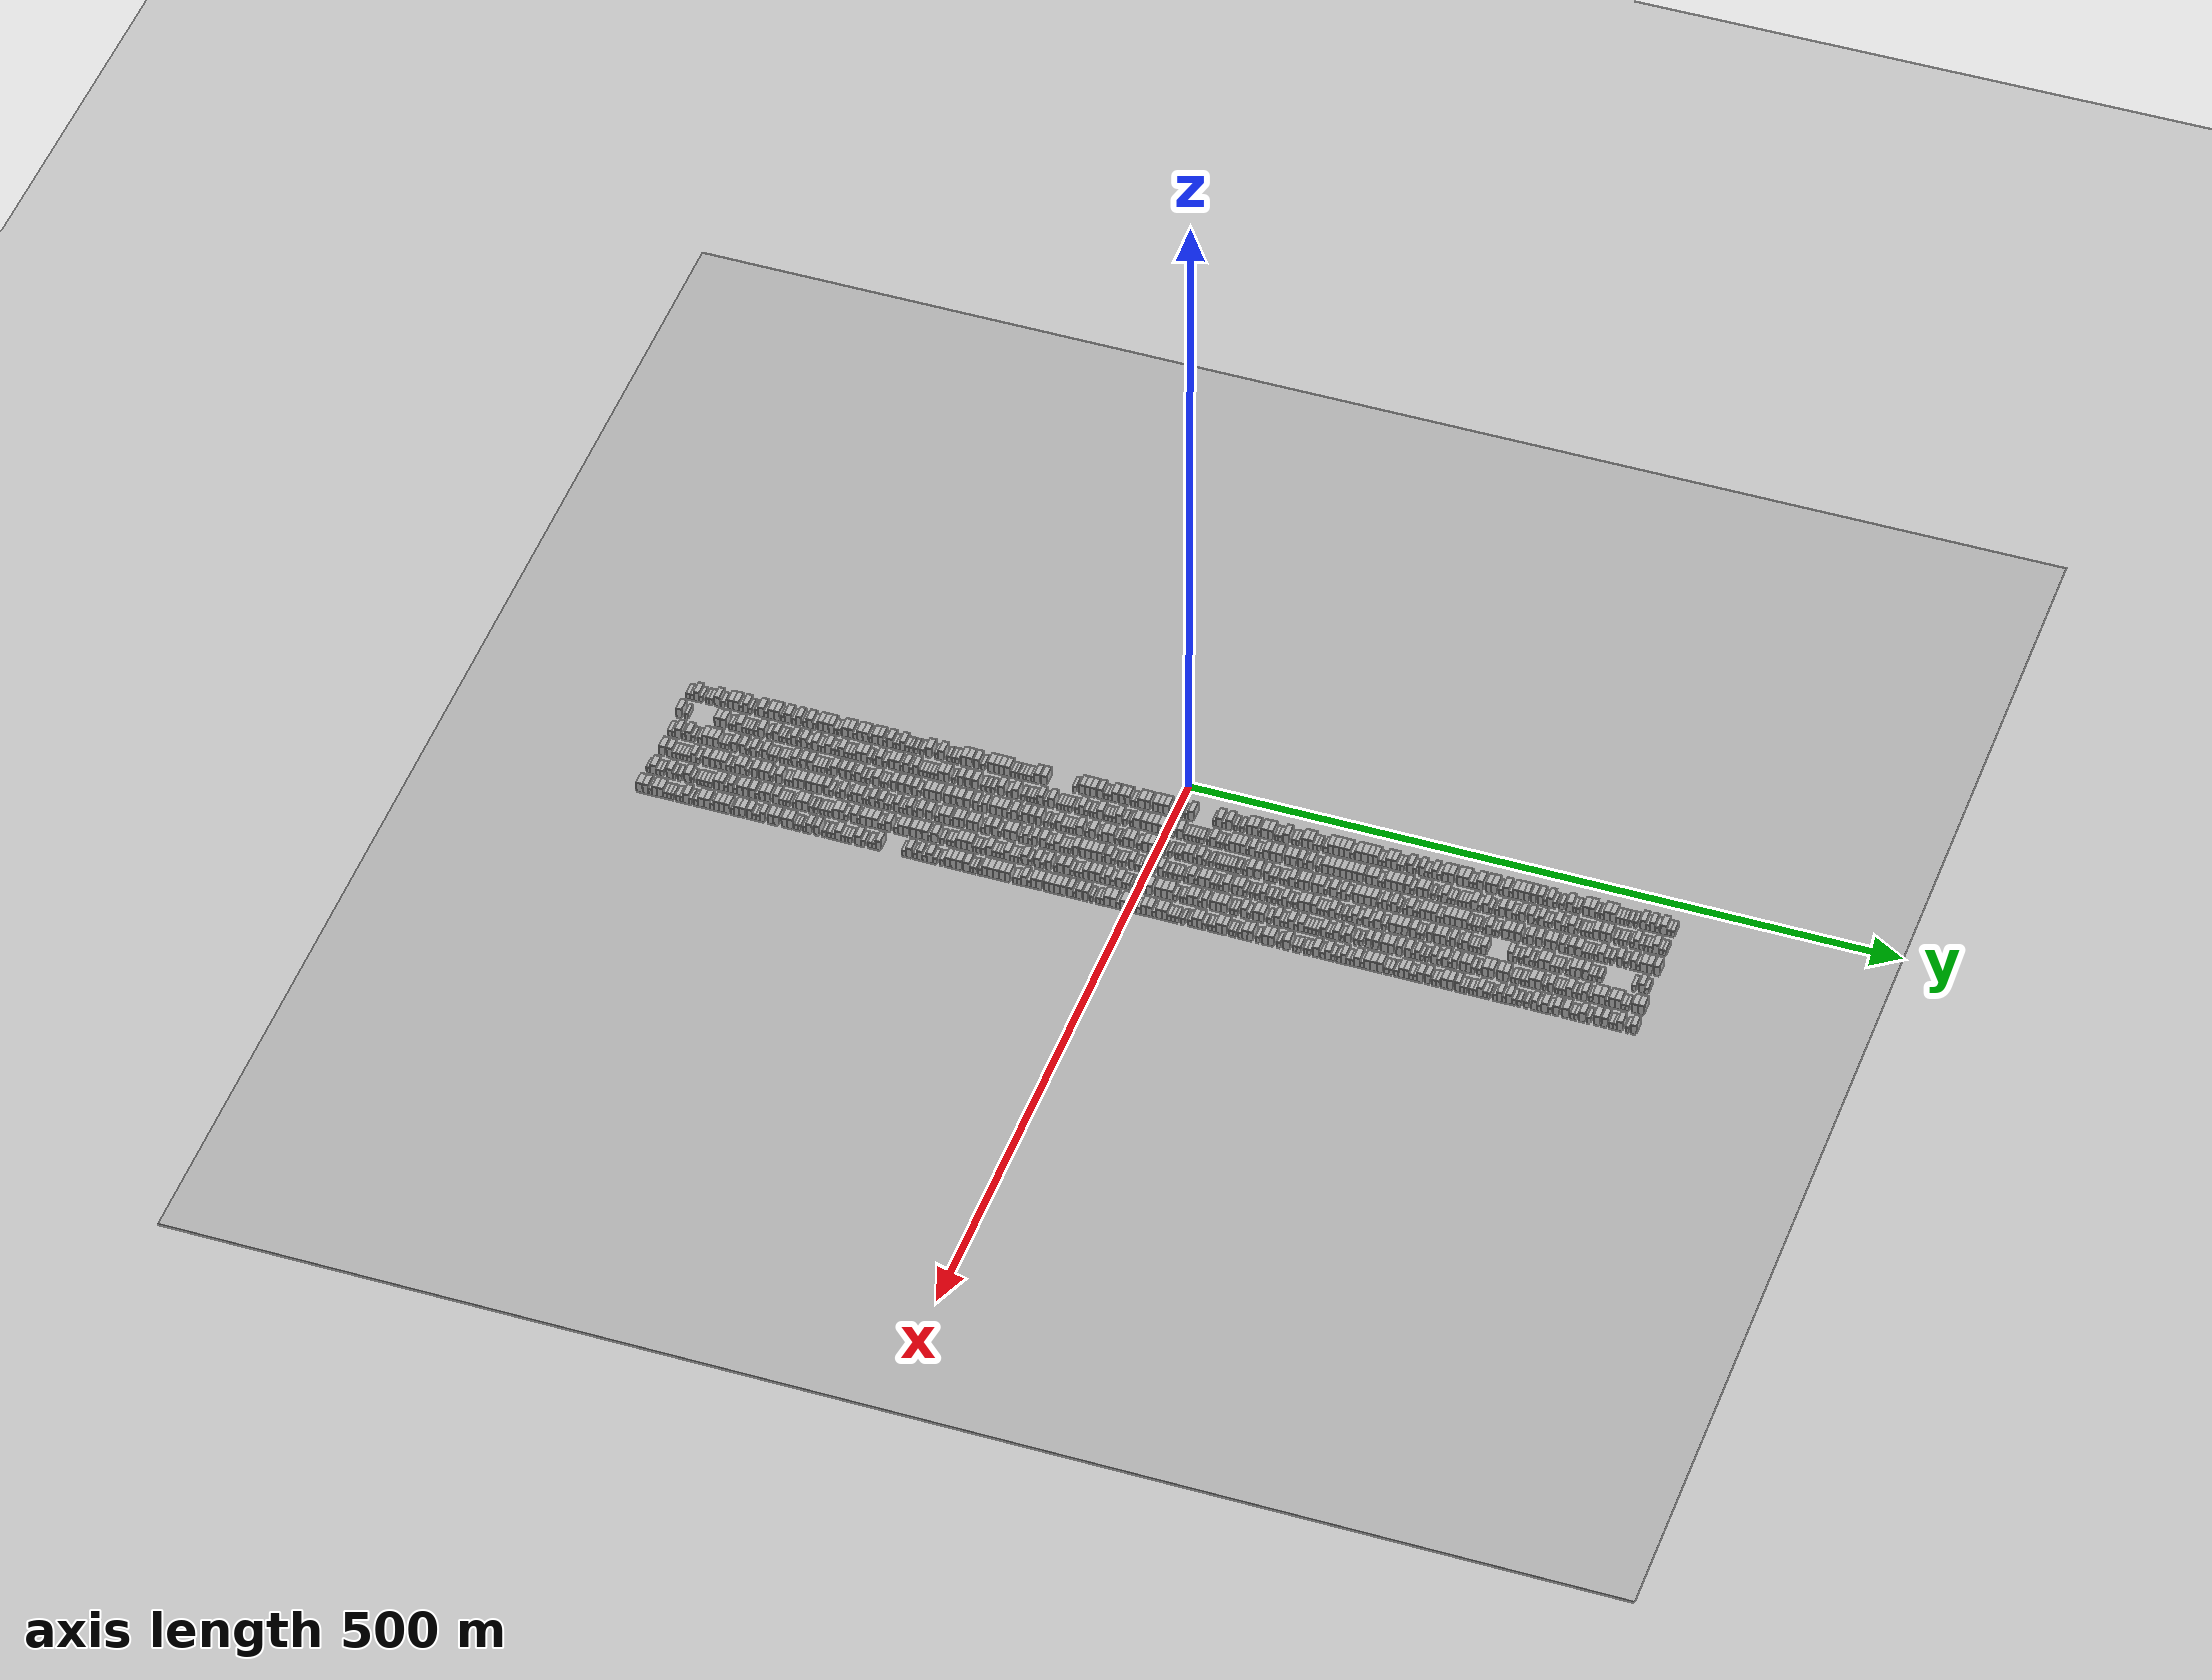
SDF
<?xml version="1.0" encoding="utf-8"?>

<sdf version="1.6">

   <world name="default">

      <gui fullscreen="0">

         <camera name="user_camera">

            <pose>-15 0 4.57585 0 0 0</pose>

            <view_controller>orbit</view_controller>

         </camera>

      </gui>

      <scene>

         <sky>

           <clouds>

             <speed>12</speed>

           </clouds>

         </sky>

         <ambient>0.4 0.4 0.4 1</ambient>

         <background>0.7 0.7 0.7 1</background>

         <shadows>1</shadows>

      </scene>

      <gravity>0 0 -9.8066</gravity>

      <magnetic_field>6e-06 2.3e-05 -4.2e-05</magnetic_field>

      <physics default="0" name="default_physics" type="ode">

         <ode>

            <solver>

               <type>quick</type>

               <iters>10</iters>

               <sor>1.0</sor>

               <use_dynamic_moi_rescaling>0</use_dynamic_moi_rescaling>

            </solver>

            <constraints>

               <cfm>0</cfm>

               <erp>0.2</erp>

               <contact_max_correcting_vel>100</contact_max_correcting_vel>

               <contact_surface_layer>0.001</contact_surface_layer>

            </constraints>

         </ode>

         <max_step_size>0.004</max_step_size>

         <real_time_factor>1</real_time_factor>

         <real_time_update_rate>250</real_time_update_rate>

      </physics>

      <light name="sun" type="directional">

         <cast_shadows>1</cast_shadows>

         <pose>0 0 10 0 0 0</pose>

         <diffuse>0.8 0.8 0.8 1</diffuse>

         <specular>0.2 0.2 0.2 1</specular>

         <attenuation>

            <range>1000</range>

            <constant>0.9</constant>

            <linear>0.01</linear>

            <quadratic>0.001</quadratic>

         </attenuation>

         <direction>-0.5 0.1 -0.9</direction>

      </light>

      <include>

         <name>ground_plane_1</name>

         <uri>model://HANNAS_ground_plane</uri>

         <pose>0 0 0  0 0 0</pose>

      </include>

      <include>

         <name>ground_plane_2</name>

         <uri>model://HANNAS_ground_plane</uri>

         <pose>100 0 0  0 0 0</pose>

      </include>

      <model name="building_1">

         <static>1</static>

         <pose frame="">25.0000 -348.5407 0 0.000000 0.000000 0.000000</pose>

         <link name="link">

            <pose frame="">0 0 3.00 0 0 0</pose>

            <collision name="collision">

               <geometry>

                  <box>

                     <size>10.0000 2.9186 6.0000</size>

                  </box>

               </geometry>

               <max_contacts>10</max_contacts>

               <surface>

                  <contact>

                     <ode/>

                  </contact>

                  <bounce/>

                  <friction>

                     <torsional>

                        <ode/>

                     </torsional>

                     <ode/>

                  </friction>

               </surface>

            </collision>

            <visual name="visual">

               <cast_shadows>0</cast_shadows>

               <geometry>

                  <box>

                     <size>10.0000 2.9186 6.0000</size>

                  </box>

               </geometry>

               <material>

                  <script>

                     <uri>model://HANNAS_wall/materials/scripts</uri>

                     <uri>model://HANNAS_wall/materials/textures</uri>

                     <name>vrc/HANNAS_wall</name>

                  </script>

               </material>

            </visual>

            <self_collide>0</self_collide>

            <enable_wind>0</enable_wind>

            <kinematic>0</kinematic>

         </link>

      </model>

      <model name="building_2">

         <static>1</static>

         <pose frame="">25.0000 -345.7877 0 0.000000 0.000000 0.000000</pose>

         <link name="link">

            <pose frame="">0 0 3.00 0 0 0</pose>

            <collision name="collision">

               <geometry>

                  <box>

                     <size>10.0000 2.5873 6.0000</size>

                  </box>

               </geometry>

               <max_contacts>10</max_contacts>

               <surface>

                  <contact>

                     <ode/>

                  </contact>

                  <bounce/>

                  <friction>

                     <torsional>

                        <ode/>

                     </torsional>

                     <ode/>

                  </friction>

               </surface>

            </collision>

            <visual name="visual">

               <cast_shadows>0</cast_shadows>

               <geometry>

                  <box>

                     <size>10.0000 2.5873 6.0000</size>

                  </box>

               </geometry>

               <material>

                  <script>

                     <uri>model://HANNAS_wall/materials/scripts</uri>

                     <uri>model://HANNAS_wall/materials/textures</uri>

                     <name>vrc/HANNAS_wall</name>

                  </script>

               </material>

            </visual>

            <self_collide>0</self_collide>

            <enable_wind>0</enable_wind>

            <kinematic>0</kinematic>

         </link>

      </model>

      <model name="building_3">

         <static>1</static>

         <pose frame="">25.0000 -342.5471 0 0.000000 0.000000 0.000000</pose>

         <link name="link">

            <pose frame="">0 0 4.50 0 0 0</pose>

            <collision name="collision">

               <geometry>

                  <box>

                     <size>10.0000 3.8939 9.0000</size>

                  </box>

               </geometry>

               <max_contacts>10</max_contacts>

               <surface>

                  <contact>

                     <ode/>

                  </contact>

                  <bounce/>

                  <friction>

                     <torsional>

                        <ode/>

                     </torsional>

                     <ode/>

                  </friction>

               </surface>

            </collision>

            <visual name="visual">

               <cast_shadows>0</cast_shadows>

               <geometry>

                  <box>

                     <size>10.0000 3.8939 9.0000</size>

                  </box>

               </geometry>

               <material>

                  <script>

                     <uri>model://HANNAS_wall/materials/scripts</uri>

                     <uri>model://HANNAS_wall/materials/textures</uri>

                     <name>vrc/HANNAS_wall</name>

                  </script>

               </material>

            </visual>

            <self_collide>0</self_collide>

            <enable_wind>0</enable_wind>

            <kinematic>0</kinematic>

         </link>

      </model>

      <model name="building_4">

         <static>1</static>

         <pose frame="">25.0000 -339.2583 0 0.000000 0.000000 0.000000</pose>

         <link name="link">

            <pose frame="">0 0 3.00 0 0 0</pose>

            <collision name="collision">

               <geometry>

                  <box>

                     <size>10.0000 2.6837 6.0000</size>

                  </box>

               </geometry>

               <max_contacts>10</max_contacts>

               <surface>

                  <contact>

                     <ode/>

                  </contact>

                  <bounce/>

                  <friction>

                     <torsional>

                        <ode/>

                     </torsional>

                     <ode/>

                  </friction>

               </surface>

            </collision>

            <visual name="visual">

               <cast_shadows>0</cast_shadows>

               <geometry>

                  <box>

                     <size>10.0000 2.6837 6.0000</size>

                  </box>

               </geometry>

               <material>

                  <script>

                     <uri>model://HANNAS_wall/materials/scripts</uri>

                     <uri>model://HANNAS_wall/materials/textures</uri>

                     <name>vrc/HANNAS_wall</name>

                  </script>

               </material>

            </visual>

            <self_collide>0</self_collide>

            <enable_wind>0</enable_wind>

            <kinematic>0</kinematic>

         </link>

      </model>

      <model name="building_5">

         <static>1</static>

         <pose frame="">25.0000 -334.6837 0 0.000000 0.000000 0.000000</pose>

         <link name="link">

            <pose frame="">0 0 3.00 0 0 0</pose>

            <collision name="collision">

               <geometry>

                  <box>

                     <size>10.0000 2.4655 6.0000</size>

                  </box>

               </geometry>

               <max_contacts>10</max_contacts>

               <surface>

                  <contact>

                     <ode/>

                  </contact>

                  <bounce/>

                  <friction>

                     <torsional>

                        <ode/>

                     </torsional>

                     <ode/>

                  </friction>

               </surface>

            </collision>

            <visual name="visual">

               <cast_shadows>0</cast_shadows>

               <geometry>

                  <box>

                     <size>10.0000 2.4655 6.0000</size>

                  </box>

               </geometry>

               <material>

                  <script>

                     <uri>model://HANNAS_wall/materials/scripts</uri>

                     <uri>model://HANNAS_wall/materials/textures</uri>

                     <name>vrc/HANNAS_wall</name>

                  </script>

               </material>

            </visual>

            <self_collide>0</self_collide>

            <enable_wind>0</enable_wind>

            <kinematic>0</kinematic>

         </link>

      </model>

      <model name="building_6">

         <static>1</static>

         <pose frame="">25.0000 -332.0545 0 0.000000 0.000000 0.000000</pose>

         <link name="link">

            <pose frame="">0 0 3.00 0 0 0</pose>

            <collision name="collision">

               <geometry>

                  <box>

                     <size>10.0000 2.7928 6.0000</size>

                  </box>

               </geometry>

               <max_contacts>10</max_contacts>

               <surface>

                  <contact>

                     <ode/>

                  </contact>

                  <bounce/>

                  <friction>

                     <torsional>

                        <ode/>

                     </torsional>

                     <ode/>

                  </friction>

               </surface>

            </collision>

            <visual name="visual">

               <cast_shadows>0</cast_shadows>

               <geometry>

                  <box>

                     <size>10.0000 2.7928 6.0000</size>

                  </box>

               </geometry>

               <material>

                  <script>

                     <uri>model://HANNAS_wall/materials/scripts</uri>

                     <uri>model://HANNAS_wall/materials/textures</uri>

                     <name>vrc/HANNAS_wall</name>

                  </script>

               </material>

            </visual>

            <self_collide>0</self_collide>

            <enable_wind>0</enable_wind>

            <kinematic>0</kinematic>

         </link>

      </model>

      <model name="building_7">

         <static>1</static>

         <pose frame="">25.0000 -327.7626 0 0.000000 0.000000 0.000000</pose>

         <link name="link">

            <pose frame="">0 0 4.50 0 0 0</pose>

            <collision name="collision">

               <geometry>

                  <box>

                     <size>10.0000 3.7911 9.0000</size>

                  </box>

               </geometry>

               <max_contacts>10</max_contacts>

               <surface>

                  <contact>

                     <ode/>

                  </contact>

                  <bounce/>

                  <friction>

                     <torsional>

                        <ode/>

                     </torsional>

                     <ode/>

                  </friction>

               </surface>

            </collision>

            <visual name="visual">

               <cast_shadows>0</cast_shadows>

               <geometry>

                  <box>

                     <size>10.0000 3.7911 9.0000</size>

                  </box>

               </geometry>

               <material>

                  <script>

                     <uri>model://HANNAS_wall/materials/scripts</uri>

                     <uri>model://HANNAS_wall/materials/textures</uri>

                     <name>vrc/HANNAS_wall</name>

                  </script>

               </material>

            </visual>

            <self_collide>0</self_collide>

            <enable_wind>0</enable_wind>

            <kinematic>0</kinematic>

         </link>

      </model>

      <model name="building_8">

         <static>1</static>

         <pose frame="">25.0000 -323.3804 0 0.000000 0.000000 0.000000</pose>

         <link name="link">

            <pose frame="">0 0 3.00 0 0 0</pose>

            <collision name="collision">

               <geometry>

                  <box>

                     <size>10.0000 2.9733 6.0000</size>

                  </box>

               </geometry>

               <max_contacts>10</max_contacts>

               <surface>

                  <contact>

                     <ode/>

                  </contact>

                  <bounce/>

                  <friction>

                     <torsional>

                        <ode/>

                     </torsional>

                     <ode/>

                  </friction>

               </surface>

            </collision>

            <visual name="visual">

               <cast_shadows>0</cast_shadows>

               <geometry>

                  <box>

                     <size>10.0000 2.9733 6.0000</size>

                  </box>

               </geometry>

               <material>

                  <script>

                     <uri>model://HANNAS_wall/materials/scripts</uri>

                     <uri>model://HANNAS_wall/materials/textures</uri>

                     <name>vrc/HANNAS_wall</name>

                  </script>

               </material>

            </visual>

            <self_collide>0</self_collide>

            <enable_wind>0</enable_wind>

            <kinematic>0</kinematic>

         </link>

      </model>

      <model name="building_9">

         <static>1</static>

         <pose frame="">25.0000 -317.9427 0 0.000000 0.000000 0.000000</pose>

         <link name="link">

            <pose frame="">0 0 4.50 0 0 0</pose>

            <collision name="collision">

               <geometry>

                  <box>

                     <size>10.0000 3.9019 9.0000</size>

                  </box>

               </geometry>

               <max_contacts>10</max_contacts>

               <surface>

                  <contact>

                     <ode/>

                  </contact>

                  <bounce/>

                  <friction>

                     <torsional>

                        <ode/>

                     </torsional>

                     <ode/>

                  </friction>

               </surface>

            </collision>

            <visual name="visual">

               <cast_shadows>0</cast_shadows>

               <geometry>

                  <box>

                     <size>10.0000 3.9019 9.0000</size>

                  </box>

               </geometry>

               <material>

                  <script>

                     <uri>model://HANNAS_wall/materials/scripts</uri>

                     <uri>model://HANNAS_wall/materials/textures</uri>

                     <name>vrc/HANNAS_wall</name>

                  </script>

               </material>

            </visual>

            <self_collide>0</self_collide>

            <enable_wind>0</enable_wind>

            <kinematic>0</kinematic>

         </link>

      </model>

      <model name="building_10">

         <static>1</static>

         <pose frame="">25.0000 -313.9475 0 0.000000 0.000000 0.000000</pose>

         <link name="link">

            <pose frame="">0 0 4.50 0 0 0</pose>

            <collision name="collision">

               <geometry>

                  <box>

                     <size>10.0000 4.0885 9.0000</size>

                  </box>

               </geometry>

               <max_contacts>10</max_contacts>

               <surface>

                  <contact>

                     <ode/>

                  </contact>

                  <bounce/>

                  <friction>

                     <torsional>

                        <ode/>

                     </torsional>

                     <ode/>

                  </friction>

               </surface>

            </collision>

            <visual name="visual">

               <cast_shadows>0</cast_shadows>

               <geometry>

                  <box>

                     <size>10.0000 4.0885 9.0000</size>

                  </box>

               </geometry>

               <material>

                  <script>

                     <uri>model://HANNAS_wall/materials/scripts</uri>

                     <uri>model://HANNAS_wall/materials/textures</uri>

                     <name>vrc/HANNAS_wall</name>

                  </script>

               </material>

            </visual>

            <self_collide>0</self_collide>

            <enable_wind>0</enable_wind>

            <kinematic>0</kinematic>

         </link>

      </model>

      <model name="building_11">

         <static>1</static>

         <pose frame="">25.0000 -310.5453 0 0.000000 0.000000 0.000000</pose>

         <link name="link">

            <pose frame="">0 0 3.00 0 0 0</pose>

            <collision name="collision">

               <geometry>

                  <box>

                     <size>10.0000 2.7159 6.0000</size>

                  </box>

               </geometry>

               <max_contacts>10</max_contacts>

               <surface>

                  <contact>

                     <ode/>

                  </contact>

                  <bounce/>

                  <friction>

                     <torsional>

                        <ode/>

                     </torsional>

                     <ode/>

                  </friction>

               </surface>

            </collision>

            <visual name="visual">

               <cast_shadows>0</cast_shadows>

               <geometry>

                  <box>

                     <size>10.0000 2.7159 6.0000</size>

                  </box>

               </geometry>

               <material>

                  <script>

                     <uri>model://HANNAS_wall/materials/scripts</uri>

                     <uri>model://HANNAS_wall/materials/textures</uri>

                     <name>vrc/HANNAS_wall</name>

                  </script>

               </material>

            </visual>

            <self_collide>0</self_collide>

            <enable_wind>0</enable_wind>

            <kinematic>0</kinematic>

         </link>

      </model>

      <model name="building_12">

         <static>1</static>

         <pose frame="">25.0000 -307.1772 0 0.000000 0.000000 0.000000</pose>

         <link name="link">

            <pose frame="">0 0 4.50 0 0 0</pose>

            <collision name="collision">

               <geometry>

                  <box>

                     <size>10.0000 4.0203 9.0000</size>

                  </box>

               </geometry>

               <max_contacts>10</max_contacts>

               <surface>

                  <contact>

                     <ode/>

                  </contact>

                  <bounce/>

                  <friction>

                     <torsional>

                        <ode/>

                     </torsional>

                     <ode/>

                  </friction>

               </surface>

            </collision>

            <visual name="visual">

               <cast_shadows>0</cast_shadows>

               <geometry>

                  <box>

                     <size>10.0000 4.0203 9.0000</size>

                  </box>

               </geometry>

               <material>

                  <script>

                     <uri>model://HANNAS_wall/materials/scripts</uri>

                     <uri>model://HANNAS_wall/materials/textures</uri>

                     <name>vrc/HANNAS_wall</name>

                  </script>

               </material>

            </visual>

            <self_collide>0</self_collide>

            <enable_wind>0</enable_wind>

            <kinematic>0</kinematic>

         </link>

      </model>

      <model name="building_13">

         <static>1</static>

         <pose frame="">25.0000 -303.8937 0 0.000000 0.000000 0.000000</pose>

         <link name="link">

            <pose frame="">0 0 3.00 0 0 0</pose>

            <collision name="collision">

               <geometry>

                  <box>

                     <size>10.0000 2.5469 6.0000</size>

                  </box>

               </geometry>

               <max_contacts>10</max_contacts>

               <surface>

                  <contact>

                     <ode/>

                  </contact>

                  <bounce/>

                  <friction>

                     <torsional>

                        <ode/>

                     </torsional>

                     <ode/>

                  </friction>

               </surface>

            </collision>

            <visual name="visual">

               <cast_shadows>0</cast_shadows>

               <geometry>

                  <box>

                     <size>10.0000 2.5469 6.0000</size>

                  </box>

               </geometry>

               <material>

                  <script>

                     <uri>model://HANNAS_wall/materials/scripts</uri>

                     <uri>model://HANNAS_wall/materials/textures</uri>

                     <name>vrc/HANNAS_wall</name>

                  </script>

               </material>

            </visual>

            <self_collide>0</self_collide>

            <enable_wind>0</enable_wind>

            <kinematic>0</kinematic>

         </link>

      </model>

      <model name="building_14">

         <static>1</static>

         <pose frame="">25.0000 -299.3981 0 0.000000 0.000000 0.000000</pose>

         <link name="link">

            <pose frame="">0 0 3.00 0 0 0</pose>

            <collision name="collision">

               <geometry>

                  <box>

                     <size>10.0000 2.4443 6.0000</size>

                  </box>

               </geometry>

               <max_contacts>10</max_contacts>

               <surface>

                  <contact>

                     <ode/>

                  </contact>

                  <bounce/>

                  <friction>

                     <torsional>

                        <ode/>

                     </torsional>

                     <ode/>

                  </friction>

               </surface>

            </collision>

            <visual name="visual">

               <cast_shadows>0</cast_shadows>

               <geometry>

                  <box>

                     <size>10.0000 2.4443 6.0000</size>

                  </box>

               </geometry>

               <material>

                  <script>

                     <uri>model://HANNAS_wall/materials/scripts</uri>

                     <uri>model://HANNAS_wall/materials/textures</uri>

                     <name>vrc/HANNAS_wall</name>

                  </script>

               </material>

            </visual>

            <self_collide>0</self_collide>

            <enable_wind>0</enable_wind>

            <kinematic>0</kinematic>

         </link>

      </model>

      <model name="building_15">

         <static>1</static>

         <pose frame="">25.0000 -295.9306 0 0.000000 0.000000 0.000000</pose>

         <link name="link">

            <pose frame="">0 0 4.50 0 0 0</pose>

            <collision name="collision">

               <geometry>

                  <box>

                     <size>10.0000 4.4907 9.0000</size>

                  </box>

               </geometry>

               <max_contacts>10</max_contacts>

               <surface>

                  <contact>

                     <ode/>

                  </contact>

                  <bounce/>

                  <friction>

                     <torsional>

                        <ode/>

                     </torsional>

                     <ode/>

                  </friction>

               </surface>

            </collision>

            <visual name="visual">

               <cast_shadows>0</cast_shadows>

               <geometry>

                  <box>

                     <size>10.0000 4.4907 9.0000</size>

                  </box>

               </geometry>

               <material>

                  <script>

                     <uri>model://HANNAS_wall/materials/scripts</uri>

                     <uri>model://HANNAS_wall/materials/textures</uri>

                     <name>vrc/HANNAS_wall</name>

                  </script>

               </material>

            </visual>

            <self_collide>0</self_collide>

            <enable_wind>0</enable_wind>

            <kinematic>0</kinematic>

         </link>

      </model>

      <model name="building_16">

         <static>1</static>

         <pose frame="">25.0000 -292.2877 0 0.000000 0.000000 0.000000</pose>

         <link name="link">

            <pose frame="">0 0 3.00 0 0 0</pose>

            <collision name="collision">

               <geometry>

                  <box>

                     <size>10.0000 2.7952 6.0000</size>

                  </box>

               </geometry>

               <max_contacts>10</max_contacts>

               <surface>

                  <contact>

                     <ode/>

                  </contact>

                  <bounce/>

                  <friction>

                     <torsional>

                        <ode/>

                     </torsional>

                     <ode/>

                  </friction>

               </surface>

            </collision>

            <visual name="visual">

               <cast_shadows>0</cast_shadows>

               <geometry>

                  <box>

                     <size>10.0000 2.7952 6.0000</size>

                  </box>

               </geometry>

               <material>

                  <script>

                     <uri>model://HANNAS_wall/materials/scripts</uri>

                     <uri>model://HANNAS_wall/materials/textures</uri>

                     <name>vrc/HANNAS_wall</name>

                  </script>

               </material>

            </visual>

            <self_collide>0</self_collide>

            <enable_wind>0</enable_wind>

            <kinematic>0</kinematic>

         </link>

      </model>

      <model name="building_17">

         <static>1</static>

         <pose frame="">25.0000 -288.7944 0 0.000000 0.000000 0.000000</pose>

         <link name="link">

            <pose frame="">0 0 4.50 0 0 0</pose>

            <collision name="collision">

               <geometry>

                  <box>

                     <size>10.0000 4.1914 9.0000</size>

                  </box>

               </geometry>

               <max_contacts>10</max_contacts>

               <surface>

                  <contact>

                     <ode/>

                  </contact>

                  <bounce/>

                  <friction>

                     <torsional>

                        <ode/>

                     </torsional>

                     <ode/>

                  </friction>

               </surface>

            </collision>

            <visual name="visual">

               <cast_shadows>0</cast_shadows>

               <geometry>

                  <box>

                     <size>10.0000 4.1914 9.0000</size>

                  </box>

               </geometry>

               <material>

                  <script>

                     <uri>model://HANNAS_wall/materials/scripts</uri>

                     <uri>model://HANNAS_wall/materials/textures</uri>

                     <name>vrc/HANNAS_wall</name>

                  </script>

               </material>

            </visual>

            <self_collide>0</self_collide>

            <enable_wind>0</enable_wind>

            <kinematic>0</kinematic>

         </link>

      </model>

      <model name="building_18">

         <static>1</static>

         <pose frame="">25.0000 -284.6509 0 0.000000 0.000000 0.000000</pose>

         <link name="link">

            <pose frame="">0 0 4.50 0 0 0</pose>

            <collision name="collision">

               <geometry>

                  <box>

                     <size>10.0000 4.0955 9.0000</size>

                  </box>

               </geometry>

               <max_contacts>10</max_contacts>

               <surface>

                  <contact>

                     <ode/>

                  </contact>

                  <bounce/>

                  <friction>

                     <torsional>

                        <ode/>

                     </torsional>

                     <ode/>

                  </friction>

               </surface>

            </collision>

            <visual name="visual">

               <cast_shadows>0</cast_shadows>

               <geometry>

                  <box>

                     <size>10.0000 4.0955 9.0000</size>

                  </box>

               </geometry>

               <material>

                  <script>

                     <uri>model://HANNAS_wall/materials/scripts</uri>

                     <uri>model://HANNAS_wall/materials/textures</uri>

                     <name>vrc/HANNAS_wall</name>

                  </script>

               </material>

            </visual>

            <self_collide>0</self_collide>

            <enable_wind>0</enable_wind>

            <kinematic>0</kinematic>

         </link>

      </model>

      <model name="building_19">

         <static>1</static>

         <pose frame="">25.0000 -280.2972 0 0.000000 0.000000 0.000000</pose>

         <link name="link">

            <pose frame="">0 0 3.00 0 0 0</pose>

            <collision name="collision">

               <geometry>

                  <box>

                     <size>10.0000 2.6119 6.0000</size>

                  </box>

               </geometry>

               <max_contacts>10</max_contacts>

               <surface>

                  <contact>

                     <ode/>

                  </contact>

                  <bounce/>

                  <friction>

                     <torsional>

                        <ode/>

                     </torsional>

                     <ode/>

                  </friction>

               </surface>

            </collision>

            <visual name="visual">

               <cast_shadows>0</cast_shadows>

               <geometry>

                  <box>

                     <size>10.0000 2.6119 6.0000</size>

                  </box>

               </geometry>

               <material>

                  <script>

                     <uri>model://HANNAS_wall/materials/scripts</uri>

                     <uri>model://HANNAS_wall/materials/textures</uri>

                     <name>vrc/HANNAS_wall</name>

                  </script>

               </material>

            </visual>

            <self_collide>0</self_collide>

            <enable_wind>0</enable_wind>

            <kinematic>0</kinematic>

         </link>

      </model>

      <model name="building_20">

         <static>1</static>

         <pose frame="">25.0000 -276.7562 0 0.000000 0.000000 0.000000</pose>

         <link name="link">

            <pose frame="">0 0 4.50 0 0 0</pose>

            <collision name="collision">

               <geometry>

                  <box>

                     <size>10.0000 4.4702 9.0000</size>

                  </box>

               </geometry>

               <max_contacts>10</max_contacts>

               <surface>

                  <contact>

                     <ode/>

                  </contact>

                  <bounce/>

                  <friction>

                     <torsional>

                        <ode/>

                     </torsional>

                     <ode/>

                  </friction>

               </surface>

            </collision>

            <visual name="visual">

               <cast_shadows>0</cast_shadows>

               <geometry>

                  <box>

                     <size>10.0000 4.4702 9.0000</size>

                  </box>

               </geometry>

               <material>

                  <script>

                     <uri>model://HANNAS_wall/materials/scripts</uri>

                     <uri>model://HANNAS_wall/materials/textures</uri>

                     <name>vrc/HANNAS_wall</name>

                  </script>

               </material>

            </visual>

            <self_collide>0</self_collide>

            <enable_wind>0</enable_wind>

            <kinematic>0</kinematic>

         </link>

      </model>

      <model name="building_21">

         <static>1</static>

         <pose frame="">25.0000 -272.0339 0 0.000000 0.000000 0.000000</pose>

         <link name="link">

            <pose frame="">0 0 3.00 0 0 0</pose>

            <collision name="collision">

               <geometry>

                  <box>

                     <size>10.0000 2.9745 6.0000</size>

                  </box>

               </geometry>

               <max_contacts>10</max_contacts>

               <surface>

                  <contact>

                     <ode/>

                  </contact>

                  <bounce/>

                  <friction>

                     <torsional>

                        <ode/>

                     </torsional>

                     <ode/>

                  </friction>

               </surface>

            </collision>

            <visual name="visual">

               <cast_shadows>0</cast_shadows>

               <geometry>

                  <box>

                     <size>10.0000 2.9745 6.0000</size>

                  </box>

               </geometry>

               <material>

                  <script>

                     <uri>model://HANNAS_wall/materials/scripts</uri>

                     <uri>model://HANNAS_wall/materials/textures</uri>

                     <name>vrc/HANNAS_wall</name>

                  </script>

               </material>

            </visual>

            <self_collide>0</self_collide>

            <enable_wind>0</enable_wind>

            <kinematic>0</kinematic>

         </link>

      </model>

      <model name="building_22">

         <static>1</static>

         <pose frame="">25.0000 -268.6552 0 0.000000 0.000000 0.000000</pose>

         <link name="link">

            <pose frame="">0 0 4.50 0 0 0</pose>

            <collision name="collision">

               <geometry>

                  <box>

                     <size>10.0000 3.7829 9.0000</size>

                  </box>

               </geometry>

               <max_contacts>10</max_contacts>

               <surface>

                  <contact>

                     <ode/>

                  </contact>

                  <bounce/>

                  <friction>

                     <torsional>

                        <ode/>

                     </torsional>

                     <ode/>

                  </friction>

               </surface>

            </collision>

            <visual name="visual">

               <cast_shadows>0</cast_shadows>

               <geometry>

                  <box>

                     <size>10.0000 3.7829 9.0000</size>

                  </box>

               </geometry>

               <material>

                  <script>

                     <uri>model://HANNAS_wall/materials/scripts</uri>

                     <uri>model://HANNAS_wall/materials/textures</uri>

                     <name>vrc/HANNAS_wall</name>

                  </script>

               </material>

            </visual>

            <self_collide>0</self_collide>

            <enable_wind>0</enable_wind>

            <kinematic>0</kinematic>

         </link>

      </model>

      <model name="building_23">

         <static>1</static>

         <pose frame="">25.0000 -264.4368 0 0.000000 0.000000 0.000000</pose>

         <link name="link">

            <pose frame="">0 0 3.00 0 0 0</pose>

            <collision name="collision">

               <geometry>

                  <box>

                     <size>10.0000 2.6539 6.0000</size>

                  </box>

               </geometry>

               <max_contacts>10</max_contacts>

               <surface>

                  <contact>

                     <ode/>

                  </contact>

                  <bounce/>

                  <friction>

                     <torsional>

                        <ode/>

                     </torsional>

                     <ode/>

                  </friction>

               </surface>

            </collision>

            <visual name="visual">

               <cast_shadows>0</cast_shadows>

               <geometry>

                  <box>

                     <size>10.0000 2.6539 6.0000</size>

                  </box>

               </geometry>

               <material>

                  <script>

                     <uri>model://HANNAS_wall/materials/scripts</uri>

                     <uri>model://HANNAS_wall/materials/textures</uri>

                     <name>vrc/HANNAS_wall</name>

                  </script>

               </material>

            </visual>

            <self_collide>0</self_collide>

            <enable_wind>0</enable_wind>

            <kinematic>0</kinematic>

         </link>

      </model>

      <model name="building_24">

         <static>1</static>

         <pose frame="">25.0000 -260.9407 0 0.000000 0.000000 0.000000</pose>

         <link name="link">

            <pose frame="">0 0 4.50 0 0 0</pose>

            <collision name="collision">

               <geometry>

                  <box>

                     <size>10.0000 4.3383 9.0000</size>

                  </box>

               </geometry>

               <max_contacts>10</max_contacts>

               <surface>

                  <contact>

                     <ode/>

                  </contact>

                  <bounce/>

                  <friction>

                     <torsional>

                        <ode/>

                     </torsional>

                     <ode/>

                  </friction>

               </surface>

            </collision>

            <visual name="visual">

               <cast_shadows>0</cast_shadows>

               <geometry>

                  <box>

                     <size>10.0000 4.3383 9.0000</size>

                  </box>

               </geometry>

               <material>

                  <script>

                     <uri>model://HANNAS_wall/materials/scripts</uri>

                     <uri>model://HANNAS_wall/materials/textures</uri>

                     <name>vrc/HANNAS_wall</name>

                  </script>

               </material>

            </visual>

            <self_collide>0</self_collide>

            <enable_wind>0</enable_wind>

            <kinematic>0</kinematic>

         </link>

      </model>

      <model name="building_25">

         <static>1</static>

         <pose frame="">25.0000 -257.4051 0 0.000000 0.000000 0.000000</pose>

         <link name="link">

            <pose frame="">0 0 3.00 0 0 0</pose>

            <collision name="collision">

               <geometry>

                  <box>

                     <size>10.0000 2.7328 6.0000</size>

                  </box>

               </geometry>

               <max_contacts>10</max_contacts>

               <surface>

                  <contact>

                     <ode/>

                  </contact>

                  <bounce/>

                  <friction>

                     <torsional>

                        <ode/>

                     </torsional>

                     <ode/>

                  </friction>

               </surface>

            </collision>

            <visual name="visual">

               <cast_shadows>0</cast_shadows>

               <geometry>

                  <box>

                     <size>10.0000 2.7328 6.0000</size>

                  </box>

               </geometry>

               <material>

                  <script>

                     <uri>model://HANNAS_wall/materials/scripts</uri>

                     <uri>model://HANNAS_wall/materials/textures</uri>

                     <name>vrc/HANNAS_wall</name>

                  </script>

               </material>

            </visual>

            <self_collide>0</self_collide>

            <enable_wind>0</enable_wind>

            <kinematic>0</kinematic>

         </link>

      </model>

      <model name="building_26">

         <static>1</static>

         <pose frame="">25.0000 -253.2176 0 0.000000 0.000000 0.000000</pose>

         <link name="link">

            <pose frame="">0 0 4.50 0 0 0</pose>

            <collision name="collision">

               <geometry>

                  <box>

                     <size>10.0000 3.6423 9.0000</size>

                  </box>

               </geometry>

               <max_contacts>10</max_contacts>

               <surface>

                  <contact>

                     <ode/>

                  </contact>

                  <bounce/>

                  <friction>

                     <torsional>

                        <ode/>

                     </torsional>

                     <ode/>

                  </friction>

               </surface>

            </collision>

            <visual name="visual">

               <cast_shadows>0</cast_shadows>

               <geometry>

                  <box>

                     <size>10.0000 3.6423 9.0000</size>

                  </box>

               </geometry>

               <material>

                  <script>

                     <uri>model://HANNAS_wall/materials/scripts</uri>

                     <uri>model://HANNAS_wall/materials/textures</uri>

                     <name>vrc/HANNAS_wall</name>

                  </script>

               </material>

            </visual>

            <self_collide>0</self_collide>

            <enable_wind>0</enable_wind>

            <kinematic>0</kinematic>

         </link>

      </model>

      <model name="building_27">

         <static>1</static>

         <pose frame="">25.0000 -249.3511 0 0.000000 0.000000 0.000000</pose>

         <link name="link">

            <pose frame="">0 0 4.50 0 0 0</pose>

            <collision name="collision">

               <geometry>

                  <box>

                     <size>10.0000 4.0905 9.0000</size>

                  </box>

               </geometry>

               <max_contacts>10</max_contacts>

               <surface>

                  <contact>

                     <ode/>

                  </contact>

                  <bounce/>

                  <friction>

                     <torsional>

                        <ode/>

                     </torsional>

                     <ode/>

                  </friction>

               </surface>

            </collision>

            <visual name="visual">

               <cast_shadows>0</cast_shadows>

               <geometry>

                  <box>

                     <size>10.0000 4.0905 9.0000</size>

                  </box>

               </geometry>

               <material>

                  <script>

                     <uri>model://HANNAS_wall/materials/scripts</uri>

                     <uri>model://HANNAS_wall/materials/textures</uri>

                     <name>vrc/HANNAS_wall</name>

                  </script>

               </material>

            </visual>

            <self_collide>0</self_collide>

            <enable_wind>0</enable_wind>

            <kinematic>0</kinematic>

         </link>

      </model>

      <model name="building_28">

         <static>1</static>

         <pose frame="">25.0000 -245.4630 0 0.000000 0.000000 0.000000</pose>

         <link name="link">

            <pose frame="">0 0 4.50 0 0 0</pose>

            <collision name="collision">

               <geometry>

                  <box>

                     <size>10.0000 3.6857 9.0000</size>

                  </box>

               </geometry>

               <max_contacts>10</max_contacts>

               <surface>

                  <contact>

                     <ode/>

                  </contact>

                  <bounce/>

                  <friction>

                     <torsional>

                        <ode/>

                     </torsional>

                     <ode/>

                  </friction>

               </surface>

            </collision>

            <visual name="visual">

               <cast_shadows>0</cast_shadows>

               <geometry>

                  <box>

                     <size>10.0000 3.6857 9.0000</size>

                  </box>

               </geometry>

               <material>

                  <script>

                     <uri>model://HANNAS_wall/materials/scripts</uri>

                     <uri>model://HANNAS_wall/materials/textures</uri>

                     <name>vrc/HANNAS_wall</name>

                  </script>

               </material>

            </visual>

            <self_collide>0</self_collide>

            <enable_wind>0</enable_wind>

            <kinematic>0</kinematic>

         </link>

      </model>

      <model name="building_29">

         <static>1</static>

         <pose frame="">25.0000 -242.2461 0 0.000000 0.000000 0.000000</pose>

         <link name="link">

            <pose frame="">0 0 3.00 0 0 0</pose>

            <collision name="collision">

               <geometry>

                  <box>

                     <size>10.0000 2.7482 6.0000</size>

                  </box>

               </geometry>

               <max_contacts>10</max_contacts>

               <surface>

                  <contact>

                     <ode/>

                  </contact>

                  <bounce/>

                  <friction>

                     <torsional>

                        <ode/>

                     </torsional>

                     <ode/>

                  </friction>

               </surface>

            </collision>

            <visual name="visual">

               <cast_shadows>0</cast_shadows>

               <geometry>

                  <box>

                     <size>10.0000 2.7482 6.0000</size>

                  </box>

               </geometry>

               <material>

                  <script>

                     <uri>model://HANNAS_wall/materials/scripts</uri>

                     <uri>model://HANNAS_wall/materials/textures</uri>

                     <name>vrc/HANNAS_wall</name>

                  </script>

               </material>

            </visual>

            <self_collide>0</self_collide>

            <enable_wind>0</enable_wind>

            <kinematic>0</kinematic>

         </link>

      </model>

      <model name="building_30">

         <static>1</static>

         <pose frame="">25.0000 -239.6683 0 0.000000 0.000000 0.000000</pose>

         <link name="link">

            <pose frame="">0 0 3.00 0 0 0</pose>

            <collision name="collision">

               <geometry>

                  <box>

                     <size>10.0000 2.4075 6.0000</size>

                  </box>

               </geometry>

               <max_contacts>10</max_contacts>

               <surface>

                  <contact>

                     <ode/>

                  </contact>

                  <bounce/>

                  <friction>

                     <torsional>

                        <ode/>

                     </torsional>

                     <ode/>

                  </friction>

               </surface>

            </collision>

            <visual name="visual">

               <cast_shadows>0</cast_shadows>

               <geometry>

                  <box>

                     <size>10.0000 2.4075 6.0000</size>

                  </box>

               </geometry>

               <material>

                  <script>

                     <uri>model://HANNAS_wall/materials/scripts</uri>

                     <uri>model://HANNAS_wall/materials/textures</uri>

                     <name>vrc/HANNAS_wall</name>

                  </script>

               </material>

            </visual>

            <self_collide>0</self_collide>

            <enable_wind>0</enable_wind>

            <kinematic>0</kinematic>

         </link>

      </model>

      <model name="building_31">

         <static>1</static>

         <pose frame="">25.0000 -235.5152 0 0.000000 0.000000 0.000000</pose>

         <link name="link">

            <pose frame="">0 0 4.50 0 0 0</pose>

            <collision name="collision">

               <geometry>

                  <box>

                     <size>10.0000 3.8986 9.0000</size>

                  </box>

               </geometry>

               <max_contacts>10</max_contacts>

               <surface>

                  <contact>

                     <ode/>

                  </contact>

                  <bounce/>

                  <friction>

                     <torsional>

                        <ode/>

                     </torsional>

                     <ode/>

                  </friction>

               </surface>

            </collision>

            <visual name="visual">

               <cast_shadows>0</cast_shadows>

               <geometry>

                  <box>

                     <size>10.0000 3.8986 9.0000</size>

                  </box>

               </geometry>

               <material>

                  <script>

                     <uri>model://HANNAS_wall/materials/scripts</uri>

                     <uri>model://HANNAS_wall/materials/textures</uri>

                     <name>vrc/HANNAS_wall</name>

                  </script>

               </material>

            </visual>

            <self_collide>0</self_collide>

            <enable_wind>0</enable_wind>

            <kinematic>0</kinematic>

         </link>

      </model>

      <model name="building_32">

         <static>1</static>

         <pose frame="">25.0000 -231.5533 0 0.000000 0.000000 0.000000</pose>

         <link name="link">

            <pose frame="">0 0 4.50 0 0 0</pose>

            <collision name="collision">

               <geometry>

                  <box>

                     <size>10.0000 4.0253 9.0000</size>

                  </box>

               </geometry>

               <max_contacts>10</max_contacts>

               <surface>

                  <contact>

                     <ode/>

                  </contact>

                  <bounce/>

                  <friction>

                     <torsional>

                        <ode/>

                     </torsional>

                     <ode/>

                  </friction>

               </surface>

            </collision>

            <visual name="visual">

               <cast_shadows>0</cast_shadows>

               <geometry>

                  <box>

                     <size>10.0000 4.0253 9.0000</size>

                  </box>

               </geometry>

               <material>

                  <script>

                     <uri>model://HANNAS_wall/materials/scripts</uri>

                     <uri>model://HANNAS_wall/materials/textures</uri>

                     <name>vrc/HANNAS_wall</name>

                  </script>

               </material>

            </visual>

            <self_collide>0</self_collide>

            <enable_wind>0</enable_wind>

            <kinematic>0</kinematic>

         </link>

      </model>

      <model name="building_33">

         <static>1</static>

         <pose frame="">25.0000 -228.2689 0 0.000000 0.000000 0.000000</pose>

         <link name="link">

            <pose frame="">0 0 3.00 0 0 0</pose>

            <collision name="collision">

               <geometry>

                  <box>

                     <size>10.0000 2.5436 6.0000</size>

                  </box>

               </geometry>

               <max_contacts>10</max_contacts>

               <surface>

                  <contact>

                     <ode/>

                  </contact>

                  <bounce/>

                  <friction>

                     <torsional>

                        <ode/>

                     </torsional>

                     <ode/>

                  </friction>

               </surface>

            </collision>

            <visual name="visual">

               <cast_shadows>0</cast_shadows>

               <geometry>

                  <box>

                     <size>10.0000 2.5436 6.0000</size>

                  </box>

               </geometry>

               <material>

                  <script>

                     <uri>model://HANNAS_wall/materials/scripts</uri>

                     <uri>model://HANNAS_wall/materials/textures</uri>

                     <name>vrc/HANNAS_wall</name>

                  </script>

               </material>

            </visual>

            <self_collide>0</self_collide>

            <enable_wind>0</enable_wind>

            <kinematic>0</kinematic>

         </link>

      </model>

      <model name="building_34">

         <static>1</static>

         <pose frame="">25.0000 -224.9257 0 0.000000 0.000000 0.000000</pose>

         <link name="link">

            <pose frame="">0 0 4.50 0 0 0</pose>

            <collision name="collision">

               <geometry>

                  <box>

                     <size>10.0000 4.1428 9.0000</size>

                  </box>

               </geometry>

               <max_contacts>10</max_contacts>

               <surface>

                  <contact>

                     <ode/>

                  </contact>

                  <bounce/>

                  <friction>

                     <torsional>

                        <ode/>

                     </torsional>

                     <ode/>

                  </friction>

               </surface>

            </collision>

            <visual name="visual">

               <cast_shadows>0</cast_shadows>

               <geometry>

                  <box>

                     <size>10.0000 4.1428 9.0000</size>

                  </box>

               </geometry>

               <material>

                  <script>

                     <uri>model://HANNAS_wall/materials/scripts</uri>

                     <uri>model://HANNAS_wall/materials/textures</uri>

                     <name>vrc/HANNAS_wall</name>

                  </script>

               </material>

            </visual>

            <self_collide>0</self_collide>

            <enable_wind>0</enable_wind>

            <kinematic>0</kinematic>

         </link>

      </model>

      <model name="building_35">

         <static>1</static>

         <pose frame="">25.0000 -220.6981 0 0.000000 0.000000 0.000000</pose>

         <link name="link">

            <pose frame="">0 0 4.50 0 0 0</pose>

            <collision name="collision">

               <geometry>

                  <box>

                     <size>10.0000 4.3123 9.0000</size>

                  </box>

               </geometry>

               <max_contacts>10</max_contacts>

               <surface>

                  <contact>

                     <ode/>

                  </contact>

                  <bounce/>

                  <friction>

                     <torsional>

                        <ode/>

                     </torsional>

                     <ode/>

                  </friction>

               </surface>

            </collision>

            <visual name="visual">

               <cast_shadows>0</cast_shadows>

               <geometry>

                  <box>

                     <size>10.0000 4.3123 9.0000</size>

                  </box>

               </geometry>

               <material>

                  <script>

                     <uri>model://HANNAS_wall/materials/scripts</uri>

                     <uri>model://HANNAS_wall/materials/textures</uri>

                     <name>vrc/HANNAS_wall</name>

                  </script>

               </material>

            </visual>

            <self_collide>0</self_collide>

            <enable_wind>0</enable_wind>

            <kinematic>0</kinematic>

         </link>

      </model>

      <model name="building_36">

         <static>1</static>

         <pose frame="">25.0000 -217.3128 0 0.000000 0.000000 0.000000</pose>

         <link name="link">

            <pose frame="">0 0 3.00 0 0 0</pose>

            <collision name="collision">

               <geometry>

                  <box>

                     <size>10.0000 2.4584 6.0000</size>

                  </box>

               </geometry>

               <max_contacts>10</max_contacts>

               <surface>

                  <contact>

                     <ode/>

                  </contact>

                  <bounce/>

                  <friction>

                     <torsional>

                        <ode/>

                     </torsional>

                     <ode/>

                  </friction>

               </surface>

            </collision>

            <visual name="visual">

               <cast_shadows>0</cast_shadows>

               <geometry>

                  <box>

                     <size>10.0000 2.4584 6.0000</size>

                  </box>

               </geometry>

               <material>

                  <script>

                     <uri>model://HANNAS_wall/materials/scripts</uri>

                     <uri>model://HANNAS_wall/materials/textures</uri>

                     <name>vrc/HANNAS_wall</name>

                  </script>

               </material>

            </visual>

            <self_collide>0</self_collide>

            <enable_wind>0</enable_wind>

            <kinematic>0</kinematic>

         </link>

      </model>

      <model name="building_37">

         <static>1</static>

         <pose frame="">25.0000 -213.9316 0 0.000000 0.000000 0.000000</pose>

         <link name="link">

            <pose frame="">0 0 4.50 0 0 0</pose>

            <collision name="collision">

               <geometry>

                  <box>

                     <size>10.0000 4.3039 9.0000</size>

                  </box>

               </geometry>

               <max_contacts>10</max_contacts>

               <surface>

                  <contact>

                     <ode/>

                  </contact>

                  <bounce/>

                  <friction>

                     <torsional>

                        <ode/>

                     </torsional>

                     <ode/>

                  </friction>

               </surface>

            </collision>

            <visual name="visual">

               <cast_shadows>0</cast_shadows>

               <geometry>

                  <box>

                     <size>10.0000 4.3039 9.0000</size>

                  </box>

               </geometry>

               <material>

                  <script>

                     <uri>model://HANNAS_wall/materials/scripts</uri>

                     <uri>model://HANNAS_wall/materials/textures</uri>

                     <name>vrc/HANNAS_wall</name>

                  </script>

               </material>

            </visual>

            <self_collide>0</self_collide>

            <enable_wind>0</enable_wind>

            <kinematic>0</kinematic>

         </link>

      </model>

      <model name="building_38">

         <static>1</static>

         <pose frame="">25.0000 -209.9758 0 0.000000 0.000000 0.000000</pose>

         <link name="link">

            <pose frame="">0 0 4.50 0 0 0</pose>

            <collision name="collision">

               <geometry>

                  <box>

                     <size>10.0000 3.6077 9.0000</size>

                  </box>

               </geometry>

               <max_contacts>10</max_contacts>

               <surface>

                  <contact>

                     <ode/>

                  </contact>

                  <bounce/>

                  <friction>

                     <torsional>

                        <ode/>

                     </torsional>

                     <ode/>

                  </friction>

               </surface>

            </collision>

            <visual name="visual">

               <cast_shadows>0</cast_shadows>

               <geometry>

                  <box>

                     <size>10.0000 3.6077 9.0000</size>

                  </box>

               </geometry>

               <material>

                  <script>

                     <uri>model://HANNAS_wall/materials/scripts</uri>

                     <uri>model://HANNAS_wall/materials/textures</uri>

                     <name>vrc/HANNAS_wall</name>

                  </script>

               </material>

            </visual>

            <self_collide>0</self_collide>

            <enable_wind>0</enable_wind>

            <kinematic>0</kinematic>

         </link>

      </model>

      <model name="building_39">

         <static>1</static>

         <pose frame="">25.0000 -206.8607 0 0.000000 0.000000 0.000000</pose>

         <link name="link">

            <pose frame="">0 0 3.00 0 0 0</pose>

            <collision name="collision">

               <geometry>

                  <box>

                     <size>10.0000 2.6225 6.0000</size>

                  </box>

               </geometry>

               <max_contacts>10</max_contacts>

               <surface>

                  <contact>

                     <ode/>

                  </contact>

                  <bounce/>

                  <friction>

                     <torsional>

                        <ode/>

                     </torsional>

                     <ode/>

                  </friction>

               </surface>

            </collision>

            <visual name="visual">

               <cast_shadows>0</cast_shadows>

               <geometry>

                  <box>

                     <size>10.0000 2.6225 6.0000</size>

                  </box>

               </geometry>

               <material>

                  <script>

                     <uri>model://HANNAS_wall/materials/scripts</uri>

                     <uri>model://HANNAS_wall/materials/textures</uri>

                     <name>vrc/HANNAS_wall</name>

                  </script>

               </material>

            </visual>

            <self_collide>0</self_collide>

            <enable_wind>0</enable_wind>

            <kinematic>0</kinematic>

         </link>

      </model>

      <model name="building_40">

         <static>1</static>

         <pose frame="">25.0000 -203.3271 0 0.000000 0.000000 0.000000</pose>

         <link name="link">

            <pose frame="">0 0 4.50 0 0 0</pose>

            <collision name="collision">

               <geometry>

                  <box>

                     <size>10.0000 4.4448 9.0000</size>

                  </box>

               </geometry>

               <max_contacts>10</max_contacts>

               <surface>

                  <contact>

                     <ode/>

                  </contact>

                  <bounce/>

                  <friction>

                     <torsional>

                        <ode/>

                     </torsional>

                     <ode/>

                  </friction>

               </surface>

            </collision>

            <visual name="visual">

               <cast_shadows>0</cast_shadows>

               <geometry>

                  <box>

                     <size>10.0000 4.4448 9.0000</size>

                  </box>

               </geometry>

               <material>

                  <script>

                     <uri>model://HANNAS_wall/materials/scripts</uri>

                     <uri>model://HANNAS_wall/materials/textures</uri>

                     <name>vrc/HANNAS_wall</name>

                  </script>

               </material>

            </visual>

            <self_collide>0</self_collide>

            <enable_wind>0</enable_wind>

            <kinematic>0</kinematic>

         </link>

      </model>

      <model name="building_41">

         <static>1</static>

         <pose frame="">25.0000 -199.8717 0 0.000000 0.000000 0.000000</pose>

         <link name="link">

            <pose frame="">0 0 3.00 0 0 0</pose>

            <collision name="collision">

               <geometry>

                  <box>

                     <size>10.0000 2.4660 6.0000</size>

                  </box>

               </geometry>

               <max_contacts>10</max_contacts>

               <surface>

                  <contact>

                     <ode/>

                  </contact>

                  <bounce/>

                  <friction>

                     <torsional>

                        <ode/>

                     </torsional>

                     <ode/>

                  </friction>

               </surface>

            </collision>

            <visual name="visual">

               <cast_shadows>0</cast_shadows>

               <geometry>

                  <box>

                     <size>10.0000 2.4660 6.0000</size>

                  </box>

               </geometry>

               <material>

                  <script>

                     <uri>model://HANNAS_wall/materials/scripts</uri>

                     <uri>model://HANNAS_wall/materials/textures</uri>

                     <name>vrc/HANNAS_wall</name>

                  </script>

               </material>

            </visual>

            <self_collide>0</self_collide>

            <enable_wind>0</enable_wind>

            <kinematic>0</kinematic>

         </link>

      </model>

      <model name="building_42">

         <static>1</static>

         <pose frame="">25.0000 -197.4052 0 0.000000 0.000000 0.000000</pose>

         <link name="link">

            <pose frame="">0 0 3.00 0 0 0</pose>

            <collision name="collision">

               <geometry>

                  <box>

                     <size>10.0000 2.4670 6.0000</size>

                  </box>

               </geometry>

               <max_contacts>10</max_contacts>

               <surface>

                  <contact>

                     <ode/>

                  </contact>

                  <bounce/>

                  <friction>

                     <torsional>

                        <ode/>

                     </torsional>

                     <ode/>

                  </friction>

               </surface>

            </collision>

            <visual name="visual">

               <cast_shadows>0</cast_shadows>

               <geometry>

                  <box>

                     <size>10.0000 2.4670 6.0000</size>

                  </box>

               </geometry>

               <material>

                  <script>

                     <uri>model://HANNAS_wall/materials/scripts</uri>

                     <uri>model://HANNAS_wall/materials/textures</uri>

                     <name>vrc/HANNAS_wall</name>

                  </script>

               </material>

            </visual>

            <self_collide>0</self_collide>

            <enable_wind>0</enable_wind>

            <kinematic>0</kinematic>

         </link>

      </model>

      <model name="building_43">

         <static>1</static>

         <pose frame="">25.0000 -194.2244 0 0.000000 0.000000 0.000000</pose>

         <link name="link">

            <pose frame="">0 0 4.50 0 0 0</pose>

            <collision name="collision">

               <geometry>

                  <box>

                     <size>10.0000 3.8945 9.0000</size>

                  </box>

               </geometry>

               <max_contacts>10</max_contacts>

               <surface>

                  <contact>

                     <ode/>

                  </contact>

                  <bounce/>

                  <friction>

                     <torsional>

                        <ode/>

                     </torsional>

                     <ode/>

                  </friction>

               </surface>

            </collision>

            <visual name="visual">

               <cast_shadows>0</cast_shadows>

               <geometry>

                  <box>

                     <size>10.0000 3.8945 9.0000</size>

                  </box>

               </geometry>

               <material>

                  <script>

                     <uri>model://HANNAS_wall/materials/scripts</uri>

                     <uri>model://HANNAS_wall/materials/textures</uri>

                     <name>vrc/HANNAS_wall</name>

                  </script>

               </material>

            </visual>

            <self_collide>0</self_collide>

            <enable_wind>0</enable_wind>

            <kinematic>0</kinematic>

         </link>

      </model>

      <model name="building_44">

         <static>1</static>

         <pose frame="">25.0000 -190.7999 0 0.000000 0.000000 0.000000</pose>

         <link name="link">

            <pose frame="">0 0 3.00 0 0 0</pose>

            <collision name="collision">

               <geometry>

                  <box>

                     <size>10.0000 2.9545 6.0000</size>

                  </box>

               </geometry>

               <max_contacts>10</max_contacts>

               <surface>

                  <contact>

                     <ode/>

                  </contact>

                  <bounce/>

                  <friction>

                     <torsional>

                        <ode/>

                     </torsional>

                     <ode/>

                  </friction>

               </surface>

            </collision>

            <visual name="visual">

               <cast_shadows>0</cast_shadows>

               <geometry>

                  <box>

                     <size>10.0000 2.9545 6.0000</size>

                  </box>

               </geometry>

               <material>

                  <script>

                     <uri>model://HANNAS_wall/materials/scripts</uri>

                     <uri>model://HANNAS_wall/materials/textures</uri>

                     <name>vrc/HANNAS_wall</name>

                  </script>

               </material>

            </visual>

            <self_collide>0</self_collide>

            <enable_wind>0</enable_wind>

            <kinematic>0</kinematic>

         </link>

      </model>

      <model name="building_45">

         <static>1</static>

         <pose frame="">25.0000 -188.1110 0 0.000000 0.000000 0.000000</pose>

         <link name="link">

            <pose frame="">0 0 3.00 0 0 0</pose>

            <collision name="collision">

               <geometry>

                  <box>

                     <size>10.0000 2.4233 6.0000</size>

                  </box>

               </geometry>

               <max_contacts>10</max_contacts>

               <surface>

                  <contact>

                     <ode/>

                  </contact>

                  <bounce/>

                  <friction>

                     <torsional>

                        <ode/>

                     </torsional>

                     <ode/>

                  </friction>

               </surface>

            </collision>

            <visual name="visual">

               <cast_shadows>0</cast_shadows>

               <geometry>

                  <box>

                     <size>10.0000 2.4233 6.0000</size>

                  </box>

               </geometry>

               <material>

                  <script>

                     <uri>model://HANNAS_wall/materials/scripts</uri>

                     <uri>model://HANNAS_wall/materials/textures</uri>

                     <name>vrc/HANNAS_wall</name>

                  </script>

               </material>

            </visual>

            <self_collide>0</self_collide>

            <enable_wind>0</enable_wind>

            <kinematic>0</kinematic>

         </link>

      </model>

      <model name="building_46">

         <static>1</static>

         <pose frame="">25.0000 -184.6166 0 0.000000 0.000000 0.000000</pose>

         <link name="link">

            <pose frame="">0 0 3.00 0 0 0</pose>

            <collision name="collision">

               <geometry>

                  <box>

                     <size>10.0000 2.5656 6.0000</size>

                  </box>

               </geometry>

               <max_contacts>10</max_contacts>

               <surface>

                  <contact>

                     <ode/>

                  </contact>

                  <bounce/>

                  <friction>

                     <torsional>

                        <ode/>

                     </torsional>

                     <ode/>

                  </friction>

               </surface>

            </collision>

            <visual name="visual">

               <cast_shadows>0</cast_shadows>

               <geometry>

                  <box>

                     <size>10.0000 2.5656 6.0000</size>

                  </box>

               </geometry>

               <material>

                  <script>

                     <uri>model://HANNAS_wall/materials/scripts</uri>

                     <uri>model://HANNAS_wall/materials/textures</uri>

                     <name>vrc/HANNAS_wall</name>

                  </script>

               </material>

            </visual>

            <self_collide>0</self_collide>

            <enable_wind>0</enable_wind>

            <kinematic>0</kinematic>

         </link>

      </model>

      <model name="building_47">

         <static>1</static>

         <pose frame="">25.0000 -179.9043 0 0.000000 0.000000 0.000000</pose>

         <link name="link">

            <pose frame="">0 0 3.00 0 0 0</pose>

            <collision name="collision">

               <geometry>

                  <box>

                     <size>10.0000 2.8590 6.0000</size>

                  </box>

               </geometry>

               <max_contacts>10</max_contacts>

               <surface>

                  <contact>

                     <ode/>

                  </contact>

                  <bounce/>

                  <friction>

                     <torsional>

                        <ode/>

                     </torsional>

                     <ode/>

                  </friction>

               </surface>

            </collision>

            <visual name="visual">

               <cast_shadows>0</cast_shadows>

               <geometry>

                  <box>

                     <size>10.0000 2.8590 6.0000</size>

                  </box>

               </geometry>

               <material>

                  <script>

                     <uri>model://HANNAS_wall/materials/scripts</uri>

                     <uri>model://HANNAS_wall/materials/textures</uri>

                     <name>vrc/HANNAS_wall</name>

                  </script>

               </material>

            </visual>

            <self_collide>0</self_collide>

            <enable_wind>0</enable_wind>

            <kinematic>0</kinematic>

         </link>

      </model>

      <model name="building_48">

         <static>1</static>

         <pose frame="">25.0000 -175.2911 0 0.000000 0.000000 0.000000</pose>

         <link name="link">

            <pose frame="">0 0 4.50 0 0 0</pose>

            <collision name="collision">

               <geometry>

                  <box>

                     <size>10.0000 4.3674 9.0000</size>

                  </box>

               </geometry>

               <max_contacts>10</max_contacts>

               <surface>

                  <contact>

                     <ode/>

                  </contact>

                  <bounce/>

                  <friction>

                     <torsional>

                        <ode/>

                     </torsional>

                     <ode/>

                  </friction>

               </surface>

            </collision>

            <visual name="visual">

               <cast_shadows>0</cast_shadows>

               <geometry>

                  <box>

                     <size>10.0000 4.3674 9.0000</size>

                  </box>

               </geometry>

               <material>

                  <script>

                     <uri>model://HANNAS_wall/materials/scripts</uri>

                     <uri>model://HANNAS_wall/materials/textures</uri>

                     <name>vrc/HANNAS_wall</name>

                  </script>

               </material>

            </visual>

            <self_collide>0</self_collide>

            <enable_wind>0</enable_wind>

            <kinematic>0</kinematic>

         </link>

      </model>

      <model name="building_49">

         <static>1</static>

         <pose frame="">25.0000 -169.7590 0 0.000000 0.000000 0.000000</pose>

         <link name="link">

            <pose frame="">0 0 3.00 0 0 0</pose>

            <collision name="collision">

               <geometry>

                  <box>

                     <size>10.0000 2.6968 6.0000</size>

                  </box>

               </geometry>

               <max_contacts>10</max_contacts>

               <surface>

                  <contact>

                     <ode/>

                  </contact>

                  <bounce/>

                  <friction>

                     <torsional>

                        <ode/>

                     </torsional>

                     <ode/>

                  </friction>

               </surface>

            </collision>

            <visual name="visual">

               <cast_shadows>0</cast_shadows>

               <geometry>

                  <box>

                     <size>10.0000 2.6968 6.0000</size>

                  </box>

               </geometry>

               <material>

                  <script>

                     <uri>model://HANNAS_wall/materials/scripts</uri>

                     <uri>model://HANNAS_wall/materials/textures</uri>

                     <name>vrc/HANNAS_wall</name>

                  </script>

               </material>

            </visual>

            <self_collide>0</self_collide>

            <enable_wind>0</enable_wind>

            <kinematic>0</kinematic>

         </link>

      </model>

      <model name="building_50">

         <static>1</static>

         <pose frame="">25.0000 -166.3550 0 0.000000 0.000000 0.000000</pose>

         <link name="link">

            <pose frame="">0 0 4.50 0 0 0</pose>

            <collision name="collision">

               <geometry>

                  <box>

                     <size>10.0000 4.1114 9.0000</size>

                  </box>

               </geometry>

               <max_contacts>10</max_contacts>

               <surface>

                  <contact>

                     <ode/>

                  </contact>

                  <bounce/>

                  <friction>

                     <torsional>

                        <ode/>

                     </torsional>

                     <ode/>

                  </friction>

               </surface>

            </collision>

            <visual name="visual">

               <cast_shadows>0</cast_shadows>

               <geometry>

                  <box>

                     <size>10.0000 4.1114 9.0000</size>

                  </box>

               </geometry>

               <material>

                  <script>

                     <uri>model://HANNAS_wall/materials/scripts</uri>

                     <uri>model://HANNAS_wall/materials/textures</uri>

                     <name>vrc/HANNAS_wall</name>

                  </script>

               </material>

            </visual>

            <self_collide>0</self_collide>

            <enable_wind>0</enable_wind>

            <kinematic>0</kinematic>

         </link>

      </model>

      <model name="building_51">

         <static>1</static>

         <pose frame="">25.0000 -160.9869 0 0.000000 0.000000 0.000000</pose>

         <link name="link">

            <pose frame="">0 0 3.00 0 0 0</pose>

            <collision name="collision">

               <geometry>

                  <box>

                     <size>10.0000 2.6247 6.0000</size>

                  </box>

               </geometry>

               <max_contacts>10</max_contacts>

               <surface>

                  <contact>

                     <ode/>

                  </contact>

                  <bounce/>

                  <friction>

                     <torsional>

                        <ode/>

                     </torsional>

                     <ode/>

                  </friction>

               </surface>

            </collision>

            <visual name="visual">

               <cast_shadows>0</cast_shadows>

               <geometry>

                  <box>

                     <size>10.0000 2.6247 6.0000</size>

                  </box>

               </geometry>

               <material>

                  <script>

                     <uri>model://HANNAS_wall/materials/scripts</uri>

                     <uri>model://HANNAS_wall/materials/textures</uri>

                     <name>vrc/HANNAS_wall</name>

                  </script>

               </material>

            </visual>

            <self_collide>0</self_collide>

            <enable_wind>0</enable_wind>

            <kinematic>0</kinematic>

         </link>

      </model>

      <model name="building_52">

         <static>1</static>

         <pose frame="">25.0000 -157.4329 0 0.000000 0.000000 0.000000</pose>

         <link name="link">

            <pose frame="">0 0 3.00 0 0 0</pose>

            <collision name="collision">

               <geometry>

                  <box>

                     <size>10.0000 2.4834 6.0000</size>

                  </box>

               </geometry>

               <max_contacts>10</max_contacts>

               <surface>

                  <contact>

                     <ode/>

                  </contact>

                  <bounce/>

                  <friction>

                     <torsional>

                        <ode/>

                     </torsional>

                     <ode/>

                  </friction>

               </surface>

            </collision>

            <visual name="visual">

               <cast_shadows>0</cast_shadows>

               <geometry>

                  <box>

                     <size>10.0000 2.4834 6.0000</size>

                  </box>

               </geometry>

               <material>

                  <script>

                     <uri>model://HANNAS_wall/materials/scripts</uri>

                     <uri>model://HANNAS_wall/materials/textures</uri>

                     <name>vrc/HANNAS_wall</name>

                  </script>

               </material>

            </visual>

            <self_collide>0</self_collide>

            <enable_wind>0</enable_wind>

            <kinematic>0</kinematic>

         </link>

      </model>

      <model name="building_53">

         <static>1</static>

         <pose frame="">25.0000 -154.7656 0 0.000000 0.000000 0.000000</pose>

         <link name="link">

            <pose frame="">0 0 3.00 0 0 0</pose>

            <collision name="collision">

               <geometry>

                  <box>

                     <size>10.0000 2.8512 6.0000</size>

                  </box>

               </geometry>

               <max_contacts>10</max_contacts>

               <surface>

                  <contact>

                     <ode/>

                  </contact>

                  <bounce/>

                  <friction>

                     <torsional>

                        <ode/>

                     </torsional>

                     <ode/>

                  </friction>

               </surface>

            </collision>

            <visual name="visual">

               <cast_shadows>0</cast_shadows>

               <geometry>

                  <box>

                     <size>10.0000 2.8512 6.0000</size>

                  </box>

               </geometry>

               <material>

                  <script>

                     <uri>model://HANNAS_wall/materials/scripts</uri>

                     <uri>model://HANNAS_wall/materials/textures</uri>

                     <name>vrc/HANNAS_wall</name>

                  </script>

               </material>

            </visual>

            <self_collide>0</self_collide>

            <enable_wind>0</enable_wind>

            <kinematic>0</kinematic>

         </link>

      </model>

      <model name="building_54">

         <static>1</static>

         <pose frame="">25.0000 -150.3234 0 0.000000 0.000000 0.000000</pose>

         <link name="link">

            <pose frame="">0 0 4.50 0 0 0</pose>

            <collision name="collision">

               <geometry>

                  <box>

                     <size>10.0000 4.0333 9.0000</size>

                  </box>

               </geometry>

               <max_contacts>10</max_contacts>

               <surface>

                  <contact>

                     <ode/>

                  </contact>

                  <bounce/>

                  <friction>

                     <torsional>

                        <ode/>

                     </torsional>

                     <ode/>

                  </friction>

               </surface>

            </collision>

            <visual name="visual">

               <cast_shadows>0</cast_shadows>

               <geometry>

                  <box>

                     <size>10.0000 4.0333 9.0000</size>

                  </box>

               </geometry>

               <material>

                  <script>

                     <uri>model://HANNAS_wall/materials/scripts</uri>

                     <uri>model://HANNAS_wall/materials/textures</uri>

                     <name>vrc/HANNAS_wall</name>

                  </script>

               </material>

            </visual>

            <self_collide>0</self_collide>

            <enable_wind>0</enable_wind>

            <kinematic>0</kinematic>

         </link>

      </model>

      <model name="building_55">

         <static>1</static>

         <pose frame="">25.0000 -146.1334 0 0.000000 0.000000 0.000000</pose>

         <link name="link">

            <pose frame="">0 0 4.50 0 0 0</pose>

            <collision name="collision">

               <geometry>

                  <box>

                     <size>10.0000 4.3468 9.0000</size>

                  </box>

               </geometry>

               <max_contacts>10</max_contacts>

               <surface>

                  <contact>

                     <ode/>

                  </contact>

                  <bounce/>

                  <friction>

                     <torsional>

                        <ode/>

                     </torsional>

                     <ode/>

                  </friction>

               </surface>

            </collision>

            <visual name="visual">

               <cast_shadows>0</cast_shadows>

               <geometry>

                  <box>

                     <size>10.0000 4.3468 9.0000</size>

                  </box>

               </geometry>

               <material>

                  <script>

                     <uri>model://HANNAS_wall/materials/scripts</uri>

                     <uri>model://HANNAS_wall/materials/textures</uri>

                     <name>vrc/HANNAS_wall</name>

                  </script>

               </material>

            </visual>

            <self_collide>0</self_collide>

            <enable_wind>0</enable_wind>

            <kinematic>0</kinematic>

         </link>

      </model>

      <model name="building_56">

         <static>1</static>

         <pose frame="">25.0000 -140.9835 0 0.000000 0.000000 0.000000</pose>

         <link name="link">

            <pose frame="">0 0 4.50 0 0 0</pose>

            <collision name="collision">

               <geometry>

                  <box>

                     <size>10.0000 3.9530 9.0000</size>

                  </box>

               </geometry>

               <max_contacts>10</max_contacts>

               <surface>

                  <contact>

                     <ode/>

                  </contact>

                  <bounce/>

                  <friction>

                     <torsional>

                        <ode/>

                     </torsional>

                     <ode/>

                  </friction>

               </surface>

            </collision>

            <visual name="visual">

               <cast_shadows>0</cast_shadows>

               <geometry>

                  <box>

                     <size>10.0000 3.9530 9.0000</size>

                  </box>

               </geometry>

               <material>

                  <script>

                     <uri>model://HANNAS_wall/materials/scripts</uri>

                     <uri>model://HANNAS_wall/materials/textures</uri>

                     <name>vrc/HANNAS_wall</name>

                  </script>

               </material>

            </visual>

            <self_collide>0</self_collide>

            <enable_wind>0</enable_wind>

            <kinematic>0</kinematic>

         </link>

      </model>

      <model name="building_57">

         <static>1</static>

         <pose frame="">25.0000 -136.5951 0 0.000000 0.000000 0.000000</pose>

         <link name="link">

            <pose frame="">0 0 3.00 0 0 0</pose>

            <collision name="collision">

               <geometry>

                  <box>

                     <size>10.0000 2.8238 6.0000</size>

                  </box>

               </geometry>

               <max_contacts>10</max_contacts>

               <surface>

                  <contact>

                     <ode/>

                  </contact>

                  <bounce/>

                  <friction>

                     <torsional>

                        <ode/>

                     </torsional>

                     <ode/>

                  </friction>

               </surface>

            </collision>

            <visual name="visual">

               <cast_shadows>0</cast_shadows>

               <geometry>

                  <box>

                     <size>10.0000 2.8238 6.0000</size>

                  </box>

               </geometry>

               <material>

                  <script>

                     <uri>model://HANNAS_wall/materials/scripts</uri>

                     <uri>model://HANNAS_wall/materials/textures</uri>

                     <name>vrc/HANNAS_wall</name>

                  </script>

               </material>

            </visual>

            <self_collide>0</self_collide>

            <enable_wind>0</enable_wind>

            <kinematic>0</kinematic>

         </link>

      </model>

      <model name="building_58">

         <static>1</static>

         <pose frame="">25.0000 -130.9755 0 0.000000 0.000000 0.000000</pose>

         <link name="link">

            <pose frame="">0 0 4.50 0 0 0</pose>

            <collision name="collision">

               <geometry>

                  <box>

                     <size>10.0000 4.4152 9.0000</size>

                  </box>

               </geometry>

               <max_contacts>10</max_contacts>

               <surface>

                  <contact>

                     <ode/>

                  </contact>

                  <bounce/>

                  <friction>

                     <torsional>

                        <ode/>

                     </torsional>

                     <ode/>

                  </friction>

               </surface>

            </collision>

            <visual name="visual">

               <cast_shadows>0</cast_shadows>

               <geometry>

                  <box>

                     <size>10.0000 4.4152 9.0000</size>

                  </box>

               </geometry>

               <material>

                  <script>

                     <uri>model://HANNAS_wall/materials/scripts</uri>

                     <uri>model://HANNAS_wall/materials/textures</uri>

                     <name>vrc/HANNAS_wall</name>

                  </script>

               </material>

            </visual>

            <self_collide>0</self_collide>

            <enable_wind>0</enable_wind>

            <kinematic>0</kinematic>

         </link>

      </model>

      <model name="building_59">

         <static>1</static>

         <pose frame="">25.0000 -126.9599 0 0.000000 0.000000 0.000000</pose>

         <link name="link">

            <pose frame="">0 0 4.50 0 0 0</pose>

            <collision name="collision">

               <geometry>

                  <box>

                     <size>10.0000 3.6161 9.0000</size>

                  </box>

               </geometry>

               <max_contacts>10</max_contacts>

               <surface>

                  <contact>

                     <ode/>

                  </contact>

                  <bounce/>

                  <friction>

                     <torsional>

                        <ode/>

                     </torsional>

                     <ode/>

                  </friction>

               </surface>

            </collision>

            <visual name="visual">

               <cast_shadows>0</cast_shadows>

               <geometry>

                  <box>

                     <size>10.0000 3.6161 9.0000</size>

                  </box>

               </geometry>

               <material>

                  <script>

                     <uri>model://HANNAS_wall/materials/scripts</uri>

                     <uri>model://HANNAS_wall/materials/textures</uri>

                     <name>vrc/HANNAS_wall</name>

                  </script>

               </material>

            </visual>

            <self_collide>0</self_collide>

            <enable_wind>0</enable_wind>

            <kinematic>0</kinematic>

         </link>

      </model>

      <model name="building_60">

         <static>1</static>

         <pose frame="">25.0000 -123.1505 0 0.000000 0.000000 0.000000</pose>

         <link name="link">

            <pose frame="">0 0 4.50 0 0 0</pose>

            <collision name="collision">

               <geometry>

                  <box>

                     <size>10.0000 4.0026 9.0000</size>

                  </box>

               </geometry>

               <max_contacts>10</max_contacts>

               <surface>

                  <contact>

                     <ode/>

                  </contact>

                  <bounce/>

                  <friction>

                     <torsional>

                        <ode/>

                     </torsional>

                     <ode/>

                  </friction>

               </surface>

            </collision>

            <visual name="visual">

               <cast_shadows>0</cast_shadows>

               <geometry>

                  <box>

                     <size>10.0000 4.0026 9.0000</size>

                  </box>

               </geometry>

               <material>

                  <script>

                     <uri>model://HANNAS_wall/materials/scripts</uri>

                     <uri>model://HANNAS_wall/materials/textures</uri>

                     <name>vrc/HANNAS_wall</name>

                  </script>

               </material>

            </visual>

            <self_collide>0</self_collide>

            <enable_wind>0</enable_wind>

            <kinematic>0</kinematic>

         </link>

      </model>

      <model name="building_61">

         <static>1</static>

         <pose frame="">25.0000 -119.2473 0 0.000000 0.000000 0.000000</pose>

         <link name="link">

            <pose frame="">0 0 4.50 0 0 0</pose>

            <collision name="collision">

               <geometry>

                  <box>

                     <size>10.0000 3.8039 9.0000</size>

                  </box>

               </geometry>

               <max_contacts>10</max_contacts>

               <surface>

                  <contact>

                     <ode/>

                  </contact>

                  <bounce/>

                  <friction>

                     <torsional>

                        <ode/>

                     </torsional>

                     <ode/>

                  </friction>

               </surface>

            </collision>

            <visual name="visual">

               <cast_shadows>0</cast_shadows>

               <geometry>

                  <box>

                     <size>10.0000 3.8039 9.0000</size>

                  </box>

               </geometry>

               <material>

                  <script>

                     <uri>model://HANNAS_wall/materials/scripts</uri>

                     <uri>model://HANNAS_wall/materials/textures</uri>

                     <name>vrc/HANNAS_wall</name>

                  </script>

               </material>

            </visual>

            <self_collide>0</self_collide>

            <enable_wind>0</enable_wind>

            <kinematic>0</kinematic>

         </link>

      </model>

      <model name="building_62">

         <static>1</static>

         <pose frame="">25.0000 -115.1257 0 0.000000 0.000000 0.000000</pose>

         <link name="link">

            <pose frame="">0 0 3.00 0 0 0</pose>

            <collision name="collision">

               <geometry>

                  <box>

                     <size>10.0000 2.4393 6.0000</size>

                  </box>

               </geometry>

               <max_contacts>10</max_contacts>

               <surface>

                  <contact>

                     <ode/>

                  </contact>

                  <bounce/>

                  <friction>

                     <torsional>

                        <ode/>

                     </torsional>

                     <ode/>

                  </friction>

               </surface>

            </collision>

            <visual name="visual">

               <cast_shadows>0</cast_shadows>

               <geometry>

                  <box>

                     <size>10.0000 2.4393 6.0000</size>

                  </box>

               </geometry>

               <material>

                  <script>

                     <uri>model://HANNAS_wall/materials/scripts</uri>

                     <uri>model://HANNAS_wall/materials/textures</uri>

                     <name>vrc/HANNAS_wall</name>

                  </script>

               </material>

            </visual>

            <self_collide>0</self_collide>

            <enable_wind>0</enable_wind>

            <kinematic>0</kinematic>

         </link>

      </model>

      <model name="building_63">

         <static>1</static>

         <pose frame="">25.0000 -112.6765 0 0.000000 0.000000 0.000000</pose>

         <link name="link">

            <pose frame="">0 0 3.00 0 0 0</pose>

            <collision name="collision">

               <geometry>

                  <box>

                     <size>10.0000 2.4591 6.0000</size>

                  </box>

               </geometry>

               <max_contacts>10</max_contacts>

               <surface>

                  <contact>

                     <ode/>

                  </contact>

                  <bounce/>

                  <friction>

                     <torsional>

                        <ode/>

                     </torsional>

                     <ode/>

                  </friction>

               </surface>

            </collision>

            <visual name="visual">

               <cast_shadows>0</cast_shadows>

               <geometry>

                  <box>

                     <size>10.0000 2.4591 6.0000</size>

                  </box>

               </geometry>

               <material>

                  <script>

                     <uri>model://HANNAS_wall/materials/scripts</uri>

                     <uri>model://HANNAS_wall/materials/textures</uri>

                     <name>vrc/HANNAS_wall</name>

                  </script>

               </material>

            </visual>

            <self_collide>0</self_collide>

            <enable_wind>0</enable_wind>

            <kinematic>0</kinematic>

         </link>

      </model>

      <model name="building_64">

         <static>1</static>

         <pose frame="">25.0000 -109.2136 0 0.000000 0.000000 0.000000</pose>

         <link name="link">

            <pose frame="">0 0 3.00 0 0 0</pose>

            <collision name="collision">

               <geometry>

                  <box>

                     <size>10.0000 2.4668 6.0000</size>

                  </box>

               </geometry>

               <max_contacts>10</max_contacts>

               <surface>

                  <contact>

                     <ode/>

                  </contact>

                  <bounce/>

                  <friction>

                     <torsional>

                        <ode/>

                     </torsional>

                     <ode/>

                  </friction>

               </surface>

            </collision>

            <visual name="visual">

               <cast_shadows>0</cast_shadows>

               <geometry>

                  <box>

                     <size>10.0000 2.4668 6.0000</size>

                  </box>

               </geometry>

               <material>

                  <script>

                     <uri>model://HANNAS_wall/materials/scripts</uri>

                     <uri>model://HANNAS_wall/materials/textures</uri>

                     <name>vrc/HANNAS_wall</name>

                  </script>

               </material>

            </visual>

            <self_collide>0</self_collide>

            <enable_wind>0</enable_wind>

            <kinematic>0</kinematic>

         </link>

      </model>

      <model name="building_65">

         <static>1</static>

         <pose frame="">25.0000 -106.7141 0 0.000000 0.000000 0.000000</pose>

         <link name="link">

            <pose frame="">0 0 3.00 0 0 0</pose>

            <collision name="collision">

               <geometry>

                  <box>

                     <size>10.0000 2.5322 6.0000</size>

                  </box>

               </geometry>

               <max_contacts>10</max_contacts>

               <surface>

                  <contact>

                     <ode/>

                  </contact>

                  <bounce/>

                  <friction>

                     <torsional>

                        <ode/>

                     </torsional>

                     <ode/>

                  </friction>

               </surface>

            </collision>

            <visual name="visual">

               <cast_shadows>0</cast_shadows>

               <geometry>

                  <box>

                     <size>10.0000 2.5322 6.0000</size>

                  </box>

               </geometry>

               <material>

                  <script>

                     <uri>model://HANNAS_wall/materials/scripts</uri>

                     <uri>model://HANNAS_wall/materials/textures</uri>

                     <name>vrc/HANNAS_wall</name>

                  </script>

               </material>

            </visual>

            <self_collide>0</self_collide>

            <enable_wind>0</enable_wind>

            <kinematic>0</kinematic>

         </link>

      </model>

      <model name="building_66">

         <static>1</static>

         <pose frame="">25.0000 -103.9539 0 0.000000 0.000000 0.000000</pose>

         <link name="link">

            <pose frame="">0 0 3.00 0 0 0</pose>

            <collision name="collision">

               <geometry>

                  <box>

                     <size>10.0000 2.9881 6.0000</size>

                  </box>

               </geometry>

               <max_contacts>10</max_contacts>

               <surface>

                  <contact>

                     <ode/>

                  </contact>

                  <bounce/>

                  <friction>

                     <torsional>

                        <ode/>

                     </torsional>

                     <ode/>

                  </friction>

               </surface>

            </collision>

            <visual name="visual">

               <cast_shadows>0</cast_shadows>

               <geometry>

                  <box>

                     <size>10.0000 2.9881 6.0000</size>

                  </box>

               </geometry>

               <material>

                  <script>

                     <uri>model://HANNAS_wall/materials/scripts</uri>

                     <uri>model://HANNAS_wall/materials/textures</uri>

                     <name>vrc/HANNAS_wall</name>

                  </script>

               </material>

            </visual>

            <self_collide>0</self_collide>

            <enable_wind>0</enable_wind>

            <kinematic>0</kinematic>

         </link>

      </model>

      <model name="building_67">

         <static>1</static>

         <pose frame="">25.0000 -101.1364 0 0.000000 0.000000 0.000000</pose>

         <link name="link">

            <pose frame="">0 0 3.00 0 0 0</pose>

            <collision name="collision">

               <geometry>

                  <box>

                     <size>10.0000 2.6470 6.0000</size>

                  </box>

               </geometry>

               <max_contacts>10</max_contacts>

               <surface>

                  <contact>

                     <ode/>

                  </contact>

                  <bounce/>

                  <friction>

                     <torsional>

                        <ode/>

                     </torsional>

                     <ode/>

                  </friction>

               </surface>

            </collision>

            <visual name="visual">

               <cast_shadows>0</cast_shadows>

               <geometry>

                  <box>

                     <size>10.0000 2.6470 6.0000</size>

                  </box>

               </geometry>

               <material>

                  <script>

                     <uri>model://HANNAS_wall/materials/scripts</uri>

                     <uri>model://HANNAS_wall/materials/textures</uri>

                     <name>vrc/HANNAS_wall</name>

                  </script>

               </material>

            </visual>

            <self_collide>0</self_collide>

            <enable_wind>0</enable_wind>

            <kinematic>0</kinematic>

         </link>

      </model>

      <model name="building_68">

         <static>1</static>

         <pose frame="">25.0000 -97.8725 0 0.000000 0.000000 0.000000</pose>

         <link name="link">

            <pose frame="">0 0 4.50 0 0 0</pose>

            <collision name="collision">

               <geometry>

                  <box>

                     <size>10.0000 3.8809 9.0000</size>

                  </box>

               </geometry>

               <max_contacts>10</max_contacts>

               <surface>

                  <contact>

                     <ode/>

                  </contact>

                  <bounce/>

                  <friction>

                     <torsional>

                        <ode/>

                     </torsional>

                     <ode/>

                  </friction>

               </surface>

            </collision>

            <visual name="visual">

               <cast_shadows>0</cast_shadows>

               <geometry>

                  <box>

                     <size>10.0000 3.8809 9.0000</size>

                  </box>

               </geometry>

               <material>

                  <script>

                     <uri>model://HANNAS_wall/materials/scripts</uri>

                     <uri>model://HANNAS_wall/materials/textures</uri>

                     <name>vrc/HANNAS_wall</name>

                  </script>

               </material>

            </visual>

            <self_collide>0</self_collide>

            <enable_wind>0</enable_wind>

            <kinematic>0</kinematic>

         </link>

      </model>

      <model name="building_69">

         <static>1</static>

         <pose frame="">25.0000 -92.8758 0 0.000000 0.000000 0.000000</pose>

         <link name="link">

            <pose frame="">0 0 4.50 0 0 0</pose>

            <collision name="collision">

               <geometry>

                  <box>

                     <size>10.0000 4.1125 9.0000</size>

                  </box>

               </geometry>

               <max_contacts>10</max_contacts>

               <surface>

                  <contact>

                     <ode/>

                  </contact>

                  <bounce/>

                  <friction>

                     <torsional>

                        <ode/>

                     </torsional>

                     <ode/>

                  </friction>

               </surface>

            </collision>

            <visual name="visual">

               <cast_shadows>0</cast_shadows>

               <geometry>

                  <box>

                     <size>10.0000 4.1125 9.0000</size>

                  </box>

               </geometry>

               <material>

                  <script>

                     <uri>model://HANNAS_wall/materials/scripts</uri>

                     <uri>model://HANNAS_wall/materials/textures</uri>

                     <name>vrc/HANNAS_wall</name>

                  </script>

               </material>

            </visual>

            <self_collide>0</self_collide>

            <enable_wind>0</enable_wind>

            <kinematic>0</kinematic>

         </link>

      </model>

      <model name="building_70">

         <static>1</static>

         <pose frame="">25.0000 -71.0035 0 0.000000 0.000000 0.000000</pose>

         <link name="link">

            <pose frame="">0 0 3.00 0 0 0</pose>

            <collision name="collision">

               <geometry>

                  <box>

                     <size>10.0000 2.5440 6.0000</size>

                  </box>

               </geometry>

               <max_contacts>10</max_contacts>

               <surface>

                  <contact>

                     <ode/>

                  </contact>

                  <bounce/>

                  <friction>

                     <torsional>

                        <ode/>

                     </torsional>

                     <ode/>

                  </friction>

               </surface>

            </collision>

            <visual name="visual">

               <cast_shadows>0</cast_shadows>

               <geometry>

                  <box>

                     <size>10.0000 2.5440 6.0000</size>

                  </box>

               </geometry>

               <material>

                  <script>

                     <uri>model://HANNAS_wall/materials/scripts</uri>

                     <uri>model://HANNAS_wall/materials/textures</uri>

                     <name>vrc/HANNAS_wall</name>

                  </script>

               </material>

            </visual>

            <self_collide>0</self_collide>

            <enable_wind>0</enable_wind>

            <kinematic>0</kinematic>

         </link>

      </model>

      <model name="building_71">

         <static>1</static>

         <pose frame="">25.0000 -65.8801 0 0.000000 0.000000 0.000000</pose>

         <link name="link">

            <pose frame="">0 0 4.50 0 0 0</pose>

            <collision name="collision">

               <geometry>

                  <box>

                     <size>10.0000 3.7028 9.0000</size>

                  </box>

               </geometry>

               <max_contacts>10</max_contacts>

               <surface>

                  <contact>

                     <ode/>

                  </contact>

                  <bounce/>

                  <friction>

                     <torsional>

                        <ode/>

                     </torsional>

                     <ode/>

                  </friction>

               </surface>

            </collision>

            <visual name="visual">

               <cast_shadows>0</cast_shadows>

               <geometry>

                  <box>

                     <size>10.0000 3.7028 9.0000</size>

                  </box>

               </geometry>

               <material>

                  <script>

                     <uri>model://HANNAS_wall/materials/scripts</uri>

                     <uri>model://HANNAS_wall/materials/textures</uri>

                     <name>vrc/HANNAS_wall</name>

                  </script>

               </material>

            </visual>

            <self_collide>0</self_collide>

            <enable_wind>0</enable_wind>

            <kinematic>0</kinematic>

         </link>

      </model>

      <model name="building_72">

         <static>1</static>

         <pose frame="">25.0000 -61.9524 0 0.000000 0.000000 0.000000</pose>

         <link name="link">

            <pose frame="">0 0 4.50 0 0 0</pose>

            <collision name="collision">

               <geometry>

                  <box>

                     <size>10.0000 4.1525 9.0000</size>

                  </box>

               </geometry>

               <max_contacts>10</max_contacts>

               <surface>

                  <contact>

                     <ode/>

                  </contact>

                  <bounce/>

                  <friction>

                     <torsional>

                        <ode/>

                     </torsional>

                     <ode/>

                  </friction>

               </surface>

            </collision>

            <visual name="visual">

               <cast_shadows>0</cast_shadows>

               <geometry>

                  <box>

                     <size>10.0000 4.1525 9.0000</size>

                  </box>

               </geometry>

               <material>

                  <script>

                     <uri>model://HANNAS_wall/materials/scripts</uri>

                     <uri>model://HANNAS_wall/materials/textures</uri>

                     <name>vrc/HANNAS_wall</name>

                  </script>

               </material>

            </visual>

            <self_collide>0</self_collide>

            <enable_wind>0</enable_wind>

            <kinematic>0</kinematic>

         </link>

      </model>

      <model name="building_73">

         <static>1</static>

         <pose frame="">25.0000 -57.9038 0 0.000000 0.000000 0.000000</pose>

         <link name="link">

            <pose frame="">0 0 4.50 0 0 0</pose>

            <collision name="collision">

               <geometry>

                  <box>

                     <size>10.0000 3.9448 9.0000</size>

                  </box>

               </geometry>

               <max_contacts>10</max_contacts>

               <surface>

                  <contact>

                     <ode/>

                  </contact>

                  <bounce/>

                  <friction>

                     <torsional>

                        <ode/>

                     </torsional>

                     <ode/>

                  </friction>

               </surface>

            </collision>

            <visual name="visual">

               <cast_shadows>0</cast_shadows>

               <geometry>

                  <box>

                     <size>10.0000 3.9448 9.0000</size>

                  </box>

               </geometry>

               <material>

                  <script>

                     <uri>model://HANNAS_wall/materials/scripts</uri>

                     <uri>model://HANNAS_wall/materials/textures</uri>

                     <name>vrc/HANNAS_wall</name>

                  </script>

               </material>

            </visual>

            <self_collide>0</self_collide>

            <enable_wind>0</enable_wind>

            <kinematic>0</kinematic>

         </link>

      </model>

      <model name="building_74">

         <static>1</static>

         <pose frame="">25.0000 -53.0082 0 0.000000 0.000000 0.000000</pose>

         <link name="link">

            <pose frame="">0 0 4.50 0 0 0</pose>

            <collision name="collision">

               <geometry>

                  <box>

                     <size>10.0000 3.8463 9.0000</size>

                  </box>

               </geometry>

               <max_contacts>10</max_contacts>

               <surface>

                  <contact>

                     <ode/>

                  </contact>

                  <bounce/>

                  <friction>

                     <torsional>

                        <ode/>

                     </torsional>

                     <ode/>

                  </friction>

               </surface>

            </collision>

            <visual name="visual">

               <cast_shadows>0</cast_shadows>

               <geometry>

                  <box>

                     <size>10.0000 3.8463 9.0000</size>

                  </box>

               </geometry>

               <material>

                  <script>

                     <uri>model://HANNAS_wall/materials/scripts</uri>

                     <uri>model://HANNAS_wall/materials/textures</uri>

                     <name>vrc/HANNAS_wall</name>

                  </script>

               </material>

            </visual>

            <self_collide>0</self_collide>

            <enable_wind>0</enable_wind>

            <kinematic>0</kinematic>

         </link>

      </model>

      <model name="building_75">

         <static>1</static>

         <pose frame="">25.0000 -48.8169 0 0.000000 0.000000 0.000000</pose>

         <link name="link">

            <pose frame="">0 0 3.00 0 0 0</pose>

            <collision name="collision">

               <geometry>

                  <box>

                     <size>10.0000 2.5363 6.0000</size>

                  </box>

               </geometry>

               <max_contacts>10</max_contacts>

               <surface>

                  <contact>

                     <ode/>

                  </contact>

                  <bounce/>

                  <friction>

                     <torsional>

                        <ode/>

                     </torsional>

                     <ode/>

                  </friction>

               </surface>

            </collision>

            <visual name="visual">

               <cast_shadows>0</cast_shadows>

               <geometry>

                  <box>

                     <size>10.0000 2.5363 6.0000</size>

                  </box>

               </geometry>

               <material>

                  <script>

                     <uri>model://HANNAS_wall/materials/scripts</uri>

                     <uri>model://HANNAS_wall/materials/textures</uri>

                     <name>vrc/HANNAS_wall</name>

                  </script>

               </material>

            </visual>

            <self_collide>0</self_collide>

            <enable_wind>0</enable_wind>

            <kinematic>0</kinematic>

         </link>

      </model>

      <model name="building_76">

         <static>1</static>

         <pose frame="">25.0000 -46.1847 0 0.000000 0.000000 0.000000</pose>

         <link name="link">

            <pose frame="">0 0 3.00 0 0 0</pose>

            <collision name="collision">

               <geometry>

                  <box>

                     <size>10.0000 2.7281 6.0000</size>

                  </box>

               </geometry>

               <max_contacts>10</max_contacts>

               <surface>

                  <contact>

                     <ode/>

                  </contact>

                  <bounce/>

                  <friction>

                     <torsional>

                        <ode/>

                     </torsional>

                     <ode/>

                  </friction>

               </surface>

            </collision>

            <visual name="visual">

               <cast_shadows>0</cast_shadows>

               <geometry>

                  <box>

                     <size>10.0000 2.7281 6.0000</size>

                  </box>

               </geometry>

               <material>

                  <script>

                     <uri>model://HANNAS_wall/materials/scripts</uri>

                     <uri>model://HANNAS_wall/materials/textures</uri>

                     <name>vrc/HANNAS_wall</name>

                  </script>

               </material>

            </visual>

            <self_collide>0</self_collide>

            <enable_wind>0</enable_wind>

            <kinematic>0</kinematic>

         </link>

      </model>

      <model name="building_77">

         <static>1</static>

         <pose frame="">25.0000 -42.6312 0 0.000000 0.000000 0.000000</pose>

         <link name="link">

            <pose frame="">0 0 4.50 0 0 0</pose>

            <collision name="collision">

               <geometry>

                  <box>

                     <size>10.0000 4.3788 9.0000</size>

                  </box>

               </geometry>

               <max_contacts>10</max_contacts>

               <surface>

                  <contact>

                     <ode/>

                  </contact>

                  <bounce/>

                  <friction>

                     <torsional>

                        <ode/>

                     </torsional>

                     <ode/>

                  </friction>

               </surface>

            </collision>

            <visual name="visual">

               <cast_shadows>0</cast_shadows>

               <geometry>

                  <box>

                     <size>10.0000 4.3788 9.0000</size>

                  </box>

               </geometry>

               <material>

                  <script>

                     <uri>model://HANNAS_wall/materials/scripts</uri>

                     <uri>model://HANNAS_wall/materials/textures</uri>

                     <name>vrc/HANNAS_wall</name>

                  </script>

               </material>

            </visual>

            <self_collide>0</self_collide>

            <enable_wind>0</enable_wind>

            <kinematic>0</kinematic>

         </link>

      </model>

      <model name="building_78">

         <static>1</static>

         <pose frame="">25.0000 -37.5233 0 0.000000 0.000000 0.000000</pose>

         <link name="link">

            <pose frame="">0 0 4.50 0 0 0</pose>

            <collision name="collision">

               <geometry>

                  <box>

                     <size>10.0000 3.8369 9.0000</size>

                  </box>

               </geometry>

               <max_contacts>10</max_contacts>

               <surface>

                  <contact>

                     <ode/>

                  </contact>

                  <bounce/>

                  <friction>

                     <torsional>

                        <ode/>

                     </torsional>

                     <ode/>

                  </friction>

               </surface>

            </collision>

            <visual name="visual">

               <cast_shadows>0</cast_shadows>

               <geometry>

                  <box>

                     <size>10.0000 3.8369 9.0000</size>

                  </box>

               </geometry>

               <material>

                  <script>

                     <uri>model://HANNAS_wall/materials/scripts</uri>

                     <uri>model://HANNAS_wall/materials/textures</uri>

                     <name>vrc/HANNAS_wall</name>

                  </script>

               </material>

            </visual>

            <self_collide>0</self_collide>

            <enable_wind>0</enable_wind>

            <kinematic>0</kinematic>

         </link>

      </model>

      <model name="building_79">

         <static>1</static>

         <pose frame="">25.0000 -33.7689 0 0.000000 0.000000 0.000000</pose>

         <link name="link">

            <pose frame="">0 0 4.50 0 0 0</pose>

            <collision name="collision">

               <geometry>

                  <box>

                     <size>10.0000 3.6720 9.0000</size>

                  </box>

               </geometry>

               <max_contacts>10</max_contacts>

               <surface>

                  <contact>

                     <ode/>

                  </contact>

                  <bounce/>

                  <friction>

                     <torsional>

                        <ode/>

                     </torsional>

                     <ode/>

                  </friction>

               </surface>

            </collision>

            <visual name="visual">

               <cast_shadows>0</cast_shadows>

               <geometry>

                  <box>

                     <size>10.0000 3.6720 9.0000</size>

                  </box>

               </geometry>

               <material>

                  <script>

                     <uri>model://HANNAS_wall/materials/scripts</uri>

                     <uri>model://HANNAS_wall/materials/textures</uri>

                     <name>vrc/HANNAS_wall</name>

                  </script>

               </material>

            </visual>

            <self_collide>0</self_collide>

            <enable_wind>0</enable_wind>

            <kinematic>0</kinematic>

         </link>

      </model>

      <model name="building_80">

         <static>1</static>

         <pose frame="">25.0000 -29.5652 0 0.000000 0.000000 0.000000</pose>

         <link name="link">

            <pose frame="">0 0 3.00 0 0 0</pose>

            <collision name="collision">

               <geometry>

                  <box>

                     <size>10.0000 2.7355 6.0000</size>

                  </box>

               </geometry>

               <max_contacts>10</max_contacts>

               <surface>

                  <contact>

                     <ode/>

                  </contact>

                  <bounce/>

                  <friction>

                     <torsional>

                        <ode/>

                     </torsional>

                     <ode/>

                  </friction>

               </surface>

            </collision>

            <visual name="visual">

               <cast_shadows>0</cast_shadows>

               <geometry>

                  <box>

                     <size>10.0000 2.7355 6.0000</size>

                  </box>

               </geometry>

               <material>

                  <script>

                     <uri>model://HANNAS_wall/materials/scripts</uri>

                     <uri>model://HANNAS_wall/materials/textures</uri>

                     <name>vrc/HANNAS_wall</name>

                  </script>

               </material>

            </visual>

            <self_collide>0</self_collide>

            <enable_wind>0</enable_wind>

            <kinematic>0</kinematic>

         </link>

      </model>

      <model name="building_81">

         <static>1</static>

         <pose frame="">25.0000 -26.9501 0 0.000000 0.000000 0.000000</pose>

         <link name="link">

            <pose frame="">0 0 3.00 0 0 0</pose>

            <collision name="collision">

               <geometry>

                  <box>

                     <size>10.0000 2.4946 6.0000</size>

                  </box>

               </geometry>

               <max_contacts>10</max_contacts>

               <surface>

                  <contact>

                     <ode/>

                  </contact>

                  <bounce/>

                  <friction>

                     <torsional>

                        <ode/>

                     </torsional>

                     <ode/>

                  </friction>

               </surface>

            </collision>

            <visual name="visual">

               <cast_shadows>0</cast_shadows>

               <geometry>

                  <box>

                     <size>10.0000 2.4946 6.0000</size>

                  </box>

               </geometry>

               <material>

                  <script>

                     <uri>model://HANNAS_wall/materials/scripts</uri>

                     <uri>model://HANNAS_wall/materials/textures</uri>

                     <name>vrc/HANNAS_wall</name>

                  </script>

               </material>

            </visual>

            <self_collide>0</self_collide>

            <enable_wind>0</enable_wind>

            <kinematic>0</kinematic>

         </link>

      </model>

      <model name="building_82">

         <static>1</static>

         <pose frame="">25.0000 -23.5042 0 0.000000 0.000000 0.000000</pose>

         <link name="link">

            <pose frame="">0 0 4.50 0 0 0</pose>

            <collision name="collision">

               <geometry>

                  <box>

                     <size>10.0000 4.3973 9.0000</size>

                  </box>

               </geometry>

               <max_contacts>10</max_contacts>

               <surface>

                  <contact>

                     <ode/>

                  </contact>

                  <bounce/>

                  <friction>

                     <torsional>

                        <ode/>

                     </torsional>

                     <ode/>

                  </friction>

               </surface>

            </collision>

            <visual name="visual">

               <cast_shadows>0</cast_shadows>

               <geometry>

                  <box>

                     <size>10.0000 4.3973 9.0000</size>

                  </box>

               </geometry>

               <material>

                  <script>

                     <uri>model://HANNAS_wall/materials/scripts</uri>

                     <uri>model://HANNAS_wall/materials/textures</uri>

                     <name>vrc/HANNAS_wall</name>

                  </script>

               </material>

            </visual>

            <self_collide>0</self_collide>

            <enable_wind>0</enable_wind>

            <kinematic>0</kinematic>

         </link>

      </model>

      <model name="building_83">

         <static>1</static>

         <pose frame="">25.0000 -19.4495 0 0.000000 0.000000 0.000000</pose>

         <link name="link">

            <pose frame="">0 0 4.50 0 0 0</pose>

            <collision name="collision">

               <geometry>

                  <box>

                     <size>10.0000 3.7122 9.0000</size>

                  </box>

               </geometry>

               <max_contacts>10</max_contacts>

               <surface>

                  <contact>

                     <ode/>

                  </contact>

                  <bounce/>

                  <friction>

                     <torsional>

                        <ode/>

                     </torsional>

                     <ode/>

                  </friction>

               </surface>

            </collision>

            <visual name="visual">

               <cast_shadows>0</cast_shadows>

               <geometry>

                  <box>

                     <size>10.0000 3.7122 9.0000</size>

                  </box>

               </geometry>

               <material>

                  <script>

                     <uri>model://HANNAS_wall/materials/scripts</uri>

                     <uri>model://HANNAS_wall/materials/textures</uri>

                     <name>vrc/HANNAS_wall</name>

                  </script>

               </material>

            </visual>

            <self_collide>0</self_collide>

            <enable_wind>0</enable_wind>

            <kinematic>0</kinematic>

         </link>

      </model>

      <model name="building_84">

         <static>1</static>

         <pose frame="">25.0000 -13.7093 0 0.000000 0.000000 0.000000</pose>

         <link name="link">

            <pose frame="">0 0 4.50 0 0 0</pose>

            <collision name="collision">

               <geometry>

                  <box>

                     <size>10.0000 3.7682 9.0000</size>

                  </box>

               </geometry>

               <max_contacts>10</max_contacts>

               <surface>

                  <contact>

                     <ode/>

                  </contact>

                  <bounce/>

                  <friction>

                     <torsional>

                        <ode/>

                     </torsional>

                     <ode/>

                  </friction>

               </surface>

            </collision>

            <visual name="visual">

               <cast_shadows>0</cast_shadows>

               <geometry>

                  <box>

                     <size>10.0000 3.7682 9.0000</size>

                  </box>

               </geometry>

               <material>

                  <script>

                     <uri>model://HANNAS_wall/materials/scripts</uri>

                     <uri>model://HANNAS_wall/materials/textures</uri>

                     <name>vrc/HANNAS_wall</name>

                  </script>

               </material>

            </visual>

            <self_collide>0</self_collide>

            <enable_wind>0</enable_wind>

            <kinematic>0</kinematic>

         </link>

      </model>

      <model name="building_85">

         <static>1</static>

         <pose frame="">25.0000 -9.9267 0 0.000000 0.000000 0.000000</pose>

         <link name="link">

            <pose frame="">0 0 4.50 0 0 0</pose>

            <collision name="collision">

               <geometry>

                  <box>

                     <size>10.0000 3.7969 9.0000</size>

                  </box>

               </geometry>

               <max_contacts>10</max_contacts>

               <surface>

                  <contact>

                     <ode/>

                  </contact>

                  <bounce/>

                  <friction>

                     <torsional>

                        <ode/>

                     </torsional>

                     <ode/>

                  </friction>

               </surface>

            </collision>

            <visual name="visual">

               <cast_shadows>0</cast_shadows>

               <geometry>

                  <box>

                     <size>10.0000 3.7969 9.0000</size>

                  </box>

               </geometry>

               <material>

                  <script>

                     <uri>model://HANNAS_wall/materials/scripts</uri>

                     <uri>model://HANNAS_wall/materials/textures</uri>

                     <name>vrc/HANNAS_wall</name>

                  </script>

               </material>

            </visual>

            <self_collide>0</self_collide>

            <enable_wind>0</enable_wind>

            <kinematic>0</kinematic>

         </link>

      </model>

      <model name="building_86">

         <static>1</static>

         <pose frame="">25.0000 -6.0050 0 0.000000 0.000000 0.000000</pose>

         <link name="link">

            <pose frame="">0 0 4.50 0 0 0</pose>

            <collision name="collision">

               <geometry>

                  <box>

                     <size>10.0000 4.0466 9.0000</size>

                  </box>

               </geometry>

               <max_contacts>10</max_contacts>

               <surface>

                  <contact>

                     <ode/>

                  </contact>

                  <bounce/>

                  <friction>

                     <torsional>

                        <ode/>

                     </torsional>

                     <ode/>

                  </friction>

               </surface>

            </collision>

            <visual name="visual">

               <cast_shadows>0</cast_shadows>

               <geometry>

                  <box>

                     <size>10.0000 4.0466 9.0000</size>

                  </box>

               </geometry>

               <material>

                  <script>

                     <uri>model://HANNAS_wall/materials/scripts</uri>

                     <uri>model://HANNAS_wall/materials/textures</uri>

                     <name>vrc/HANNAS_wall</name>

                  </script>

               </material>

            </visual>

            <self_collide>0</self_collide>

            <enable_wind>0</enable_wind>

            <kinematic>0</kinematic>

         </link>

      </model>

      <model name="building_87">

         <static>1</static>

         <pose frame="">25.0000 -1.5067 0 0.000000 0.000000 0.000000</pose>

         <link name="link">

            <pose frame="">0 0 3.00 0 0 0</pose>

            <collision name="collision">

               <geometry>

                  <box>

                     <size>10.0000 2.9499 6.0000</size>

                  </box>

               </geometry>

               <max_contacts>10</max_contacts>

               <surface>

                  <contact>

                     <ode/>

                  </contact>

                  <bounce/>

                  <friction>

                     <torsional>

                        <ode/>

                     </torsional>

                     <ode/>

                  </friction>

               </surface>

            </collision>

            <visual name="visual">

               <cast_shadows>0</cast_shadows>

               <geometry>

                  <box>

                     <size>10.0000 2.9499 6.0000</size>

                  </box>

               </geometry>

               <material>

                  <script>

                     <uri>model://HANNAS_wall/materials/scripts</uri>

                     <uri>model://HANNAS_wall/materials/textures</uri>

                     <name>vrc/HANNAS_wall</name>

                  </script>

               </material>

            </visual>

            <self_collide>0</self_collide>

            <enable_wind>0</enable_wind>

            <kinematic>0</kinematic>

         </link>

      </model>

      <model name="building_88">

         <static>1</static>

         <pose frame="">25.0000 1.2851 0 0.000000 0.000000 0.000000</pose>

         <link name="link">

            <pose frame="">0 0 3.00 0 0 0</pose>

            <collision name="collision">

               <geometry>

                  <box>

                     <size>10.0000 2.6337 6.0000</size>

                  </box>

               </geometry>

               <max_contacts>10</max_contacts>

               <surface>

                  <contact>

                     <ode/>

                  </contact>

                  <bounce/>

                  <friction>

                     <torsional>

                        <ode/>

                     </torsional>

                     <ode/>

                  </friction>

               </surface>

            </collision>

            <visual name="visual">

               <cast_shadows>0</cast_shadows>

               <geometry>

                  <box>

                     <size>10.0000 2.6337 6.0000</size>

                  </box>

               </geometry>

               <material>

                  <script>

                     <uri>model://HANNAS_wall/materials/scripts</uri>

                     <uri>model://HANNAS_wall/materials/textures</uri>

                     <name>vrc/HANNAS_wall</name>

                  </script>

               </material>

            </visual>

            <self_collide>0</self_collide>

            <enable_wind>0</enable_wind>

            <kinematic>0</kinematic>

         </link>

      </model>

      <model name="building_89">

         <static>1</static>

         <pose frame="">25.0000 4.8728 0 0.000000 0.000000 0.000000</pose>

         <link name="link">

            <pose frame="">0 0 3.00 0 0 0</pose>

            <collision name="collision">

               <geometry>

                  <box>

                     <size>10.0000 2.5417 6.0000</size>

                  </box>

               </geometry>

               <max_contacts>10</max_contacts>

               <surface>

                  <contact>

                     <ode/>

                  </contact>

                  <bounce/>

                  <friction>

                     <torsional>

                        <ode/>

                     </torsional>

                     <ode/>

                  </friction>

               </surface>

            </collision>

            <visual name="visual">

               <cast_shadows>0</cast_shadows>

               <geometry>

                  <box>

                     <size>10.0000 2.5417 6.0000</size>

                  </box>

               </geometry>

               <material>

                  <script>

                     <uri>model://HANNAS_wall/materials/scripts</uri>

                     <uri>model://HANNAS_wall/materials/textures</uri>

                     <name>vrc/HANNAS_wall</name>

                  </script>

               </material>

            </visual>

            <self_collide>0</self_collide>

            <enable_wind>0</enable_wind>

            <kinematic>0</kinematic>

         </link>

      </model>

      <model name="building_90">

         <static>1</static>

         <pose frame="">25.0000 8.4501 0 0.000000 0.000000 0.000000</pose>

         <link name="link">

            <pose frame="">0 0 3.00 0 0 0</pose>

            <collision name="collision">

               <geometry>

                  <box>

                     <size>10.0000 2.6129 6.0000</size>

                  </box>

               </geometry>

               <max_contacts>10</max_contacts>

               <surface>

                  <contact>

                     <ode/>

                  </contact>

                  <bounce/>

                  <friction>

                     <torsional>

                        <ode/>

                     </torsional>

                     <ode/>

                  </friction>

               </surface>

            </collision>

            <visual name="visual">

               <cast_shadows>0</cast_shadows>

               <geometry>

                  <box>

                     <size>10.0000 2.6129 6.0000</size>

                  </box>

               </geometry>

               <material>

                  <script>

                     <uri>model://HANNAS_wall/materials/scripts</uri>

                     <uri>model://HANNAS_wall/materials/textures</uri>

                     <name>vrc/HANNAS_wall</name>

                  </script>

               </material>

            </visual>

            <self_collide>0</self_collide>

            <enable_wind>0</enable_wind>

            <kinematic>0</kinematic>

         </link>

      </model>

      <model name="building_91">

         <static>1</static>

         <pose frame="">25.0000 11.7018 0 0.000000 0.000000 0.000000</pose>

         <link name="link">

            <pose frame="">0 0 4.50 0 0 0</pose>

            <collision name="collision">

               <geometry>

                  <box>

                     <size>10.0000 3.8906 9.0000</size>

                  </box>

               </geometry>

               <max_contacts>10</max_contacts>

               <surface>

                  <contact>

                     <ode/>

                  </contact>

                  <bounce/>

                  <friction>

                     <torsional>

                        <ode/>

                     </torsional>

                     <ode/>

                  </friction>

               </surface>

            </collision>

            <visual name="visual">

               <cast_shadows>0</cast_shadows>

               <geometry>

                  <box>

                     <size>10.0000 3.8906 9.0000</size>

                  </box>

               </geometry>

               <material>

                  <script>

                     <uri>model://HANNAS_wall/materials/scripts</uri>

                     <uri>model://HANNAS_wall/materials/textures</uri>

                     <name>vrc/HANNAS_wall</name>

                  </script>

               </material>

            </visual>

            <self_collide>0</self_collide>

            <enable_wind>0</enable_wind>

            <kinematic>0</kinematic>

         </link>

      </model>

      <model name="building_92">

         <static>1</static>

         <pose frame="">25.0000 28.2711 0 0.000000 0.000000 0.000000</pose>

         <link name="link">

            <pose frame="">0 0 3.00 0 0 0</pose>

            <collision name="collision">

               <geometry>

                  <box>

                     <size>10.0000 2.4159 6.0000</size>

                  </box>

               </geometry>

               <max_contacts>10</max_contacts>

               <surface>

                  <contact>

                     <ode/>

                  </contact>

                  <bounce/>

                  <friction>

                     <torsional>

                        <ode/>

                     </torsional>

                     <ode/>

                  </friction>

               </surface>

            </collision>

            <visual name="visual">

               <cast_shadows>0</cast_shadows>

               <geometry>

                  <box>

                     <size>10.0000 2.4159 6.0000</size>

                  </box>

               </geometry>

               <material>

                  <script>

                     <uri>model://HANNAS_wall/materials/scripts</uri>

                     <uri>model://HANNAS_wall/materials/textures</uri>

                     <name>vrc/HANNAS_wall</name>

                  </script>

               </material>

            </visual>

            <self_collide>0</self_collide>

            <enable_wind>0</enable_wind>

            <kinematic>0</kinematic>

         </link>

      </model>

      <model name="building_93">

         <static>1</static>

         <pose frame="">25.0000 31.5718 0 0.000000 0.000000 0.000000</pose>

         <link name="link">

            <pose frame="">0 0 4.50 0 0 0</pose>

            <collision name="collision">

               <geometry>

                  <box>

                     <size>10.0000 4.1856 9.0000</size>

                  </box>

               </geometry>

               <max_contacts>10</max_contacts>

               <surface>

                  <contact>

                     <ode/>

                  </contact>

                  <bounce/>

                  <friction>

                     <torsional>

                        <ode/>

                     </torsional>

                     <ode/>

                  </friction>

               </surface>

            </collision>

            <visual name="visual">

               <cast_shadows>0</cast_shadows>

               <geometry>

                  <box>

                     <size>10.0000 4.1856 9.0000</size>

                  </box>

               </geometry>

               <material>

                  <script>

                     <uri>model://HANNAS_wall/materials/scripts</uri>

                     <uri>model://HANNAS_wall/materials/textures</uri>

                     <name>vrc/HANNAS_wall</name>

                  </script>

               </material>

            </visual>

            <self_collide>0</self_collide>

            <enable_wind>0</enable_wind>

            <kinematic>0</kinematic>

         </link>

      </model>

      <model name="building_94">

         <static>1</static>

         <pose frame="">25.0000 35.1478 0 0.000000 0.000000 0.000000</pose>

         <link name="link">

            <pose frame="">0 0 3.00 0 0 0</pose>

            <collision name="collision">

               <geometry>

                  <box>

                     <size>10.0000 2.9663 6.0000</size>

                  </box>

               </geometry>

               <max_contacts>10</max_contacts>

               <surface>

                  <contact>

                     <ode/>

                  </contact>

                  <bounce/>

                  <friction>

                     <torsional>

                        <ode/>

                     </torsional>

                     <ode/>

                  </friction>

               </surface>

            </collision>

            <visual name="visual">

               <cast_shadows>0</cast_shadows>

               <geometry>

                  <box>

                     <size>10.0000 2.9663 6.0000</size>

                  </box>

               </geometry>

               <material>

                  <script>

                     <uri>model://HANNAS_wall/materials/scripts</uri>

                     <uri>model://HANNAS_wall/materials/textures</uri>

                     <name>vrc/HANNAS_wall</name>

                  </script>

               </material>

            </visual>

            <self_collide>0</self_collide>

            <enable_wind>0</enable_wind>

            <kinematic>0</kinematic>

         </link>

      </model>

      <model name="building_95">

         <static>1</static>

         <pose frame="">25.0000 38.7033 0 0.000000 0.000000 0.000000</pose>

         <link name="link">

            <pose frame="">0 0 4.50 0 0 0</pose>

            <collision name="collision">

               <geometry>

                  <box>

                     <size>10.0000 4.1447 9.0000</size>

                  </box>

               </geometry>

               <max_contacts>10</max_contacts>

               <surface>

                  <contact>

                     <ode/>

                  </contact>

                  <bounce/>

                  <friction>

                     <torsional>

                        <ode/>

                     </torsional>

                     <ode/>

                  </friction>

               </surface>

            </collision>

            <visual name="visual">

               <cast_shadows>0</cast_shadows>

               <geometry>

                  <box>

                     <size>10.0000 4.1447 9.0000</size>

                  </box>

               </geometry>

               <material>

                  <script>

                     <uri>model://HANNAS_wall/materials/scripts</uri>

                     <uri>model://HANNAS_wall/materials/textures</uri>

                     <name>vrc/HANNAS_wall</name>

                  </script>

               </material>

            </visual>

            <self_collide>0</self_collide>

            <enable_wind>0</enable_wind>

            <kinematic>0</kinematic>

         </link>

      </model>

      <model name="building_96">

         <static>1</static>

         <pose frame="">25.0000 43.0852 0 0.000000 0.000000 0.000000</pose>

         <link name="link">

            <pose frame="">0 0 3.00 0 0 0</pose>

            <collision name="collision">

               <geometry>

                  <box>

                     <size>10.0000 2.6192 6.0000</size>

                  </box>

               </geometry>

               <max_contacts>10</max_contacts>

               <surface>

                  <contact>

                     <ode/>

                  </contact>

                  <bounce/>

                  <friction>

                     <torsional>

                        <ode/>

                     </torsional>

                     <ode/>

                  </friction>

               </surface>

            </collision>

            <visual name="visual">

               <cast_shadows>0</cast_shadows>

               <geometry>

                  <box>

                     <size>10.0000 2.6192 6.0000</size>

                  </box>

               </geometry>

               <material>

                  <script>

                     <uri>model://HANNAS_wall/materials/scripts</uri>

                     <uri>model://HANNAS_wall/materials/textures</uri>

                     <name>vrc/HANNAS_wall</name>

                  </script>

               </material>

            </visual>

            <self_collide>0</self_collide>

            <enable_wind>0</enable_wind>

            <kinematic>0</kinematic>

         </link>

      </model>

      <model name="building_97">

         <static>1</static>

         <pose frame="">25.0000 47.7562 0 0.000000 0.000000 0.000000</pose>

         <link name="link">

            <pose frame="">0 0 3.00 0 0 0</pose>

            <collision name="collision">

               <geometry>

                  <box>

                     <size>10.0000 2.7227 6.0000</size>

                  </box>

               </geometry>

               <max_contacts>10</max_contacts>

               <surface>

                  <contact>

                     <ode/>

                  </contact>

                  <bounce/>

                  <friction>

                     <torsional>

                        <ode/>

                     </torsional>

                     <ode/>

                  </friction>

               </surface>

            </collision>

            <visual name="visual">

               <cast_shadows>0</cast_shadows>

               <geometry>

                  <box>

                     <size>10.0000 2.7227 6.0000</size>

                  </box>

               </geometry>

               <material>

                  <script>

                     <uri>model://HANNAS_wall/materials/scripts</uri>

                     <uri>model://HANNAS_wall/materials/textures</uri>

                     <name>vrc/HANNAS_wall</name>

                  </script>

               </material>

            </visual>

            <self_collide>0</self_collide>

            <enable_wind>0</enable_wind>

            <kinematic>0</kinematic>

         </link>

      </model>

      <model name="building_98">

         <static>1</static>

         <pose frame="">25.0000 53.0841 0 0.000000 0.000000 0.000000</pose>

         <link name="link">

            <pose frame="">0 0 4.50 0 0 0</pose>

            <collision name="collision">

               <geometry>

                  <box>

                     <size>10.0000 3.9332 9.0000</size>

                  </box>

               </geometry>

               <max_contacts>10</max_contacts>

               <surface>

                  <contact>

                     <ode/>

                  </contact>

                  <bounce/>

                  <friction>

                     <torsional>

                        <ode/>

                     </torsional>

                     <ode/>

                  </friction>

               </surface>

            </collision>

            <visual name="visual">

               <cast_shadows>0</cast_shadows>

               <geometry>

                  <box>

                     <size>10.0000 3.9332 9.0000</size>

                  </box>

               </geometry>

               <material>

                  <script>

                     <uri>model://HANNAS_wall/materials/scripts</uri>

                     <uri>model://HANNAS_wall/materials/textures</uri>

                     <name>vrc/HANNAS_wall</name>

                  </script>

               </material>

            </visual>

            <self_collide>0</self_collide>

            <enable_wind>0</enable_wind>

            <kinematic>0</kinematic>

         </link>

      </model>

      <model name="building_99">

         <static>1</static>

         <pose frame="">25.0000 56.9649 0 0.000000 0.000000 0.000000</pose>

         <link name="link">

            <pose frame="">0 0 4.50 0 0 0</pose>

            <collision name="collision">

               <geometry>

                  <box>

                     <size>10.0000 3.8284 9.0000</size>

                  </box>

               </geometry>

               <max_contacts>10</max_contacts>

               <surface>

                  <contact>

                     <ode/>

                  </contact>

                  <bounce/>

                  <friction>

                     <torsional>

                        <ode/>

                     </torsional>

                     <ode/>

                  </friction>

               </surface>

            </collision>

            <visual name="visual">

               <cast_shadows>0</cast_shadows>

               <geometry>

                  <box>

                     <size>10.0000 3.8284 9.0000</size>

                  </box>

               </geometry>

               <material>

                  <script>

                     <uri>model://HANNAS_wall/materials/scripts</uri>

                     <uri>model://HANNAS_wall/materials/textures</uri>

                     <name>vrc/HANNAS_wall</name>

                  </script>

               </material>

            </visual>

            <self_collide>0</self_collide>

            <enable_wind>0</enable_wind>

            <kinematic>0</kinematic>

         </link>

      </model>

      <model name="building_100">

         <static>1</static>

         <pose frame="">25.0000 60.0891 0 0.000000 0.000000 0.000000</pose>

         <link name="link">

            <pose frame="">0 0 3.00 0 0 0</pose>

            <collision name="collision">

               <geometry>

                  <box>

                     <size>10.0000 2.4199 6.0000</size>

                  </box>

               </geometry>

               <max_contacts>10</max_contacts>

               <surface>

                  <contact>

                     <ode/>

                  </contact>

                  <bounce/>

                  <friction>

                     <torsional>

                        <ode/>

                     </torsional>

                     <ode/>

                  </friction>

               </surface>

            </collision>

            <visual name="visual">

               <cast_shadows>0</cast_shadows>

               <geometry>

                  <box>

                     <size>10.0000 2.4199 6.0000</size>

                  </box>

               </geometry>

               <material>

                  <script>

                     <uri>model://HANNAS_wall/materials/scripts</uri>

                     <uri>model://HANNAS_wall/materials/textures</uri>

                     <name>vrc/HANNAS_wall</name>

                  </script>

               </material>

            </visual>

            <self_collide>0</self_collide>

            <enable_wind>0</enable_wind>

            <kinematic>0</kinematic>

         </link>

      </model>

      <model name="building_101">

         <static>1</static>

         <pose frame="">25.0000 63.5254 0 0.000000 0.000000 0.000000</pose>

         <link name="link">

            <pose frame="">0 0 4.50 0 0 0</pose>

            <collision name="collision">

               <geometry>

                  <box>

                     <size>10.0000 4.4528 9.0000</size>

                  </box>

               </geometry>

               <max_contacts>10</max_contacts>

               <surface>

                  <contact>

                     <ode/>

                  </contact>

                  <bounce/>

                  <friction>

                     <torsional>

                        <ode/>

                     </torsional>

                     <ode/>

                  </friction>

               </surface>

            </collision>

            <visual name="visual">

               <cast_shadows>0</cast_shadows>

               <geometry>

                  <box>

                     <size>10.0000 4.4528 9.0000</size>

                  </box>

               </geometry>

               <material>

                  <script>

                     <uri>model://HANNAS_wall/materials/scripts</uri>

                     <uri>model://HANNAS_wall/materials/textures</uri>

                     <name>vrc/HANNAS_wall</name>

                  </script>

               </material>

            </visual>

            <self_collide>0</self_collide>

            <enable_wind>0</enable_wind>

            <kinematic>0</kinematic>

         </link>

      </model>

      <model name="building_102">

         <static>1</static>

         <pose frame="">25.0000 67.7562 0 0.000000 0.000000 0.000000</pose>

         <link name="link">

            <pose frame="">0 0 4.50 0 0 0</pose>

            <collision name="collision">

               <geometry>

                  <box>

                     <size>10.0000 4.0087 9.0000</size>

                  </box>

               </geometry>

               <max_contacts>10</max_contacts>

               <surface>

                  <contact>

                     <ode/>

                  </contact>

                  <bounce/>

                  <friction>

                     <torsional>

                        <ode/>

                     </torsional>

                     <ode/>

                  </friction>

               </surface>

            </collision>

            <visual name="visual">

               <cast_shadows>0</cast_shadows>

               <geometry>

                  <box>

                     <size>10.0000 4.0087 9.0000</size>

                  </box>

               </geometry>

               <material>

                  <script>

                     <uri>model://HANNAS_wall/materials/scripts</uri>

                     <uri>model://HANNAS_wall/materials/textures</uri>

                     <name>vrc/HANNAS_wall</name>

                  </script>

               </material>

            </visual>

            <self_collide>0</self_collide>

            <enable_wind>0</enable_wind>

            <kinematic>0</kinematic>

         </link>

      </model>

      <model name="building_103">

         <static>1</static>

         <pose frame="">25.0000 71.9956 0 0.000000 0.000000 0.000000</pose>

         <link name="link">

            <pose frame="">0 0 3.00 0 0 0</pose>

            <collision name="collision">

               <geometry>

                  <box>

                     <size>10.0000 2.4701 6.0000</size>

                  </box>

               </geometry>

               <max_contacts>10</max_contacts>

               <surface>

                  <contact>

                     <ode/>

                  </contact>

                  <bounce/>

                  <friction>

                     <torsional>

                        <ode/>

                     </torsional>

                     <ode/>

                  </friction>

               </surface>

            </collision>

            <visual name="visual">

               <cast_shadows>0</cast_shadows>

               <geometry>

                  <box>

                     <size>10.0000 2.4701 6.0000</size>

                  </box>

               </geometry>

               <material>

                  <script>

                     <uri>model://HANNAS_wall/materials/scripts</uri>

                     <uri>model://HANNAS_wall/materials/textures</uri>

                     <name>vrc/HANNAS_wall</name>

                  </script>

               </material>

            </visual>

            <self_collide>0</self_collide>

            <enable_wind>0</enable_wind>

            <kinematic>0</kinematic>

         </link>

      </model>

      <model name="building_104">

         <static>1</static>

         <pose frame="">25.0000 74.5949 0 0.000000 0.000000 0.000000</pose>

         <link name="link">

            <pose frame="">0 0 3.00 0 0 0</pose>

            <collision name="collision">

               <geometry>

                  <box>

                     <size>10.0000 2.7285 6.0000</size>

                  </box>

               </geometry>

               <max_contacts>10</max_contacts>

               <surface>

                  <contact>

                     <ode/>

                  </contact>

                  <bounce/>

                  <friction>

                     <torsional>

                        <ode/>

                     </torsional>

                     <ode/>

                  </friction>

               </surface>

            </collision>

            <visual name="visual">

               <cast_shadows>0</cast_shadows>

               <geometry>

                  <box>

                     <size>10.0000 2.7285 6.0000</size>

                  </box>

               </geometry>

               <material>

                  <script>

                     <uri>model://HANNAS_wall/materials/scripts</uri>

                     <uri>model://HANNAS_wall/materials/textures</uri>

                     <name>vrc/HANNAS_wall</name>

                  </script>

               </material>

            </visual>

            <self_collide>0</self_collide>

            <enable_wind>0</enable_wind>

            <kinematic>0</kinematic>

         </link>

      </model>

      <model name="building_105">

         <static>1</static>

         <pose frame="">25.0000 78.9301 0 0.000000 0.000000 0.000000</pose>

         <link name="link">

            <pose frame="">0 0 4.50 0 0 0</pose>

            <collision name="collision">

               <geometry>

                  <box>

                     <size>10.0000 3.9420 9.0000</size>

                  </box>

               </geometry>

               <max_contacts>10</max_contacts>

               <surface>

                  <contact>

                     <ode/>

                  </contact>

                  <bounce/>

                  <friction>

                     <torsional>

                        <ode/>

                     </torsional>

                     <ode/>

                  </friction>

               </surface>

            </collision>

            <visual name="visual">

               <cast_shadows>0</cast_shadows>

               <geometry>

                  <box>

                     <size>10.0000 3.9420 9.0000</size>

                  </box>

               </geometry>

               <material>

                  <script>

                     <uri>model://HANNAS_wall/materials/scripts</uri>

                     <uri>model://HANNAS_wall/materials/textures</uri>

                     <name>vrc/HANNAS_wall</name>

                  </script>

               </material>

            </visual>

            <self_collide>0</self_collide>

            <enable_wind>0</enable_wind>

            <kinematic>0</kinematic>

         </link>

      </model>

      <model name="building_106">

         <static>1</static>

         <pose frame="">25.0000 84.3247 0 0.000000 0.000000 0.000000</pose>

         <link name="link">

            <pose frame="">0 0 3.00 0 0 0</pose>

            <collision name="collision">

               <geometry>

                  <box>

                     <size>10.0000 2.8471 6.0000</size>

                  </box>

               </geometry>

               <max_contacts>10</max_contacts>

               <surface>

                  <contact>

                     <ode/>

                  </contact>

                  <bounce/>

                  <friction>

                     <torsional>

                        <ode/>

                     </torsional>

                     <ode/>

                  </friction>

               </surface>

            </collision>

            <visual name="visual">

               <cast_shadows>0</cast_shadows>

               <geometry>

                  <box>

                     <size>10.0000 2.8471 6.0000</size>

                  </box>

               </geometry>

               <material>

                  <script>

                     <uri>model://HANNAS_wall/materials/scripts</uri>

                     <uri>model://HANNAS_wall/materials/textures</uri>

                     <name>vrc/HANNAS_wall</name>

                  </script>

               </material>

            </visual>

            <self_collide>0</self_collide>

            <enable_wind>0</enable_wind>

            <kinematic>0</kinematic>

         </link>

      </model>

      <model name="building_107">

         <static>1</static>

         <pose frame="">25.0000 86.9825 0 0.000000 0.000000 0.000000</pose>

         <link name="link">

            <pose frame="">0 0 3.00 0 0 0</pose>

            <collision name="collision">

               <geometry>

                  <box>

                     <size>10.0000 2.4686 6.0000</size>

                  </box>

               </geometry>

               <max_contacts>10</max_contacts>

               <surface>

                  <contact>

                     <ode/>

                  </contact>

                  <bounce/>

                  <friction>

                     <torsional>

                        <ode/>

                     </torsional>

                     <ode/>

                  </friction>

               </surface>

            </collision>

            <visual name="visual">

               <cast_shadows>0</cast_shadows>

               <geometry>

                  <box>

                     <size>10.0000 2.4686 6.0000</size>

                  </box>

               </geometry>

               <material>

                  <script>

                     <uri>model://HANNAS_wall/materials/scripts</uri>

                     <uri>model://HANNAS_wall/materials/textures</uri>

                     <name>vrc/HANNAS_wall</name>

                  </script>

               </material>

            </visual>

            <self_collide>0</self_collide>

            <enable_wind>0</enable_wind>

            <kinematic>0</kinematic>

         </link>

      </model>

      <model name="building_108">

         <static>1</static>

         <pose frame="">25.0000 92.1960 0 0.000000 0.000000 0.000000</pose>

         <link name="link">

            <pose frame="">0 0 4.50 0 0 0</pose>

            <collision name="collision">

               <geometry>

                  <box>

                     <size>10.0000 3.9583 9.0000</size>

                  </box>

               </geometry>

               <max_contacts>10</max_contacts>

               <surface>

                  <contact>

                     <ode/>

                  </contact>

                  <bounce/>

                  <friction>

                     <torsional>

                        <ode/>

                     </torsional>

                     <ode/>

                  </friction>

               </surface>

            </collision>

            <visual name="visual">

               <cast_shadows>0</cast_shadows>

               <geometry>

                  <box>

                     <size>10.0000 3.9583 9.0000</size>

                  </box>

               </geometry>

               <material>

                  <script>

                     <uri>model://HANNAS_wall/materials/scripts</uri>

                     <uri>model://HANNAS_wall/materials/textures</uri>

                     <name>vrc/HANNAS_wall</name>

                  </script>

               </material>

            </visual>

            <self_collide>0</self_collide>

            <enable_wind>0</enable_wind>

            <kinematic>0</kinematic>

         </link>

      </model>

      <model name="building_109">

         <static>1</static>

         <pose frame="">25.0000 95.9973 0 0.000000 0.000000 0.000000</pose>

         <link name="link">

            <pose frame="">0 0 4.50 0 0 0</pose>

            <collision name="collision">

               <geometry>

                  <box>

                     <size>10.0000 3.6442 9.0000</size>

                  </box>

               </geometry>

               <max_contacts>10</max_contacts>

               <surface>

                  <contact>

                     <ode/>

                  </contact>

                  <bounce/>

                  <friction>

                     <torsional>

                        <ode/>

                     </torsional>

                     <ode/>

                  </friction>

               </surface>

            </collision>

            <visual name="visual">

               <cast_shadows>0</cast_shadows>

               <geometry>

                  <box>

                     <size>10.0000 3.6442 9.0000</size>

                  </box>

               </geometry>

               <material>

                  <script>

                     <uri>model://HANNAS_wall/materials/scripts</uri>

                     <uri>model://HANNAS_wall/materials/textures</uri>

                     <name>vrc/HANNAS_wall</name>

                  </script>

               </material>

            </visual>

            <self_collide>0</self_collide>

            <enable_wind>0</enable_wind>

            <kinematic>0</kinematic>

         </link>

      </model>

      <model name="building_110">

         <static>1</static>

         <pose frame="">25.0000 99.1210 0 0.000000 0.000000 0.000000</pose>

         <link name="link">

            <pose frame="">0 0 3.00 0 0 0</pose>

            <collision name="collision">

               <geometry>

                  <box>

                     <size>10.0000 2.6032 6.0000</size>

                  </box>

               </geometry>

               <max_contacts>10</max_contacts>

               <surface>

                  <contact>

                     <ode/>

                  </contact>

                  <bounce/>

                  <friction>

                     <torsional>

                        <ode/>

                     </torsional>

                     <ode/>

                  </friction>

               </surface>

            </collision>

            <visual name="visual">

               <cast_shadows>0</cast_shadows>

               <geometry>

                  <box>

                     <size>10.0000 2.6032 6.0000</size>

                  </box>

               </geometry>

               <material>

                  <script>

                     <uri>model://HANNAS_wall/materials/scripts</uri>

                     <uri>model://HANNAS_wall/materials/textures</uri>

                     <name>vrc/HANNAS_wall</name>

                  </script>

               </material>

            </visual>

            <self_collide>0</self_collide>

            <enable_wind>0</enable_wind>

            <kinematic>0</kinematic>

         </link>

      </model>

      <model name="building_111">

         <static>1</static>

         <pose frame="">25.0000 101.7868 0 0.000000 0.000000 0.000000</pose>

         <link name="link">

            <pose frame="">0 0 3.00 0 0 0</pose>

            <collision name="collision">

               <geometry>

                  <box>

                     <size>10.0000 2.7285 6.0000</size>

                  </box>

               </geometry>

               <max_contacts>10</max_contacts>

               <surface>

                  <contact>

                     <ode/>

                  </contact>

                  <bounce/>

                  <friction>

                     <torsional>

                        <ode/>

                     </torsional>

                     <ode/>

                  </friction>

               </surface>

            </collision>

            <visual name="visual">

               <cast_shadows>0</cast_shadows>

               <geometry>

                  <box>

                     <size>10.0000 2.7285 6.0000</size>

                  </box>

               </geometry>

               <material>

                  <script>

                     <uri>model://HANNAS_wall/materials/scripts</uri>

                     <uri>model://HANNAS_wall/materials/textures</uri>

                     <name>vrc/HANNAS_wall</name>

                  </script>

               </material>

            </visual>

            <self_collide>0</self_collide>

            <enable_wind>0</enable_wind>

            <kinematic>0</kinematic>

         </link>

      </model>

      <model name="building_112">

         <static>1</static>

         <pose frame="">25.0000 106.6266 0 0.000000 0.000000 0.000000</pose>

         <link name="link">

            <pose frame="">0 0 3.00 0 0 0</pose>

            <collision name="collision">

               <geometry>

                  <box>

                     <size>10.0000 2.9510 6.0000</size>

                  </box>

               </geometry>

               <max_contacts>10</max_contacts>

               <surface>

                  <contact>

                     <ode/>

                  </contact>

                  <bounce/>

                  <friction>

                     <torsional>

                        <ode/>

                     </torsional>

                     <ode/>

                  </friction>

               </surface>

            </collision>

            <visual name="visual">

               <cast_shadows>0</cast_shadows>

               <geometry>

                  <box>

                     <size>10.0000 2.9510 6.0000</size>

                  </box>

               </geometry>

               <material>

                  <script>

                     <uri>model://HANNAS_wall/materials/scripts</uri>

                     <uri>model://HANNAS_wall/materials/textures</uri>

                     <name>vrc/HANNAS_wall</name>

                  </script>

               </material>

            </visual>

            <self_collide>0</self_collide>

            <enable_wind>0</enable_wind>

            <kinematic>0</kinematic>

         </link>

      </model>

      <model name="building_113">

         <static>1</static>

         <pose frame="">25.0000 110.0286 0 0.000000 0.000000 0.000000</pose>

         <link name="link">

            <pose frame="">0 0 4.50 0 0 0</pose>

            <collision name="collision">

               <geometry>

                  <box>

                     <size>10.0000 3.8529 9.0000</size>

                  </box>

               </geometry>

               <max_contacts>10</max_contacts>

               <surface>

                  <contact>

                     <ode/>

                  </contact>

                  <bounce/>

                  <friction>

                     <torsional>

                        <ode/>

                     </torsional>

                     <ode/>

                  </friction>

               </surface>

            </collision>

            <visual name="visual">

               <cast_shadows>0</cast_shadows>

               <geometry>

                  <box>

                     <size>10.0000 3.8529 9.0000</size>

                  </box>

               </geometry>

               <material>

                  <script>

                     <uri>model://HANNAS_wall/materials/scripts</uri>

                     <uri>model://HANNAS_wall/materials/textures</uri>

                     <name>vrc/HANNAS_wall</name>

                  </script>

               </material>

            </visual>

            <self_collide>0</self_collide>

            <enable_wind>0</enable_wind>

            <kinematic>0</kinematic>

         </link>

      </model>

      <model name="building_114">

         <static>1</static>

         <pose frame="">25.0000 114.0044 0 0.000000 0.000000 0.000000</pose>

         <link name="link">

            <pose frame="">0 0 4.50 0 0 0</pose>

            <collision name="collision">

               <geometry>

                  <box>

                     <size>10.0000 4.0986 9.0000</size>

                  </box>

               </geometry>

               <max_contacts>10</max_contacts>

               <surface>

                  <contact>

                     <ode/>

                  </contact>

                  <bounce/>

                  <friction>

                     <torsional>

                        <ode/>

                     </torsional>

                     <ode/>

                  </friction>

               </surface>

            </collision>

            <visual name="visual">

               <cast_shadows>0</cast_shadows>

               <geometry>

                  <box>

                     <size>10.0000 4.0986 9.0000</size>

                  </box>

               </geometry>

               <material>

                  <script>

                     <uri>model://HANNAS_wall/materials/scripts</uri>

                     <uri>model://HANNAS_wall/materials/textures</uri>

                     <name>vrc/HANNAS_wall</name>

                  </script>

               </material>

            </visual>

            <self_collide>0</self_collide>

            <enable_wind>0</enable_wind>

            <kinematic>0</kinematic>

         </link>

      </model>

      <model name="building_115">

         <static>1</static>

         <pose frame="">25.0000 117.9129 0 0.000000 0.000000 0.000000</pose>

         <link name="link">

            <pose frame="">0 0 4.50 0 0 0</pose>

            <collision name="collision">

               <geometry>

                  <box>

                     <size>10.0000 3.7184 9.0000</size>

                  </box>

               </geometry>

               <max_contacts>10</max_contacts>

               <surface>

                  <contact>

                     <ode/>

                  </contact>

                  <bounce/>

                  <friction>

                     <torsional>

                        <ode/>

                     </torsional>

                     <ode/>

                  </friction>

               </surface>

            </collision>

            <visual name="visual">

               <cast_shadows>0</cast_shadows>

               <geometry>

                  <box>

                     <size>10.0000 3.7184 9.0000</size>

                  </box>

               </geometry>

               <material>

                  <script>

                     <uri>model://HANNAS_wall/materials/scripts</uri>

                     <uri>model://HANNAS_wall/materials/textures</uri>

                     <name>vrc/HANNAS_wall</name>

                  </script>

               </material>

            </visual>

            <self_collide>0</self_collide>

            <enable_wind>0</enable_wind>

            <kinematic>0</kinematic>

         </link>

      </model>

      <model name="building_116">

         <static>1</static>

         <pose frame="">25.0000 121.9671 0 0.000000 0.000000 0.000000</pose>

         <link name="link">

            <pose frame="">0 0 4.50 0 0 0</pose>

            <collision name="collision">

               <geometry>

                  <box>

                     <size>10.0000 4.3900 9.0000</size>

                  </box>

               </geometry>

               <max_contacts>10</max_contacts>

               <surface>

                  <contact>

                     <ode/>

                  </contact>

                  <bounce/>

                  <friction>

                     <torsional>

                        <ode/>

                     </torsional>

                     <ode/>

                  </friction>

               </surface>

            </collision>

            <visual name="visual">

               <cast_shadows>0</cast_shadows>

               <geometry>

                  <box>

                     <size>10.0000 4.3900 9.0000</size>

                  </box>

               </geometry>

               <material>

                  <script>

                     <uri>model://HANNAS_wall/materials/scripts</uri>

                     <uri>model://HANNAS_wall/materials/textures</uri>

                     <name>vrc/HANNAS_wall</name>

                  </script>

               </material>

            </visual>

            <self_collide>0</self_collide>

            <enable_wind>0</enable_wind>

            <kinematic>0</kinematic>

         </link>

      </model>

      <model name="building_117">

         <static>1</static>

         <pose frame="">25.0000 125.4050 0 0.000000 0.000000 0.000000</pose>

         <link name="link">

            <pose frame="">0 0 3.00 0 0 0</pose>

            <collision name="collision">

               <geometry>

                  <box>

                     <size>10.0000 2.4857 6.0000</size>

                  </box>

               </geometry>

               <max_contacts>10</max_contacts>

               <surface>

                  <contact>

                     <ode/>

                  </contact>

                  <bounce/>

                  <friction>

                     <torsional>

                        <ode/>

                     </torsional>

                     <ode/>

                  </friction>

               </surface>

            </collision>

            <visual name="visual">

               <cast_shadows>0</cast_shadows>

               <geometry>

                  <box>

                     <size>10.0000 2.4857 6.0000</size>

                  </box>

               </geometry>

               <material>

                  <script>

                     <uri>model://HANNAS_wall/materials/scripts</uri>

                     <uri>model://HANNAS_wall/materials/textures</uri>

                     <name>vrc/HANNAS_wall</name>

                  </script>

               </material>

            </visual>

            <self_collide>0</self_collide>

            <enable_wind>0</enable_wind>

            <kinematic>0</kinematic>

         </link>

      </model>

      <model name="building_118">

         <static>1</static>

         <pose frame="">25.0000 129.7108 0 0.000000 0.000000 0.000000</pose>

         <link name="link">

            <pose frame="">0 0 4.50 0 0 0</pose>

            <collision name="collision">

               <geometry>

                  <box>

                     <size>10.0000 4.1260 9.0000</size>

                  </box>

               </geometry>

               <max_contacts>10</max_contacts>

               <surface>

                  <contact>

                     <ode/>

                  </contact>

                  <bounce/>

                  <friction>

                     <torsional>

                        <ode/>

                     </torsional>

                     <ode/>

                  </friction>

               </surface>

            </collision>

            <visual name="visual">

               <cast_shadows>0</cast_shadows>

               <geometry>

                  <box>

                     <size>10.0000 4.1260 9.0000</size>

                  </box>

               </geometry>

               <material>

                  <script>

                     <uri>model://HANNAS_wall/materials/scripts</uri>

                     <uri>model://HANNAS_wall/materials/textures</uri>

                     <name>vrc/HANNAS_wall</name>

                  </script>

               </material>

            </visual>

            <self_collide>0</self_collide>

            <enable_wind>0</enable_wind>

            <kinematic>0</kinematic>

         </link>

      </model>

      <model name="building_119">

         <static>1</static>

         <pose frame="">25.0000 134.0146 0 0.000000 0.000000 0.000000</pose>

         <link name="link">

            <pose frame="">0 0 4.50 0 0 0</pose>

            <collision name="collision">

               <geometry>

                  <box>

                     <size>10.0000 4.4817 9.0000</size>

                  </box>

               </geometry>

               <max_contacts>10</max_contacts>

               <surface>

                  <contact>

                     <ode/>

                  </contact>

                  <bounce/>

                  <friction>

                     <torsional>

                        <ode/>

                     </torsional>

                     <ode/>

                  </friction>

               </surface>

            </collision>

            <visual name="visual">

               <cast_shadows>0</cast_shadows>

               <geometry>

                  <box>

                     <size>10.0000 4.4817 9.0000</size>

                  </box>

               </geometry>

               <material>

                  <script>

                     <uri>model://HANNAS_wall/materials/scripts</uri>

                     <uri>model://HANNAS_wall/materials/textures</uri>

                     <name>vrc/HANNAS_wall</name>

                  </script>

               </material>

            </visual>

            <self_collide>0</self_collide>

            <enable_wind>0</enable_wind>

            <kinematic>0</kinematic>

         </link>

      </model>

      <model name="building_120">

         <static>1</static>

         <pose frame="">25.0000 138.1126 0 0.000000 0.000000 0.000000</pose>

         <link name="link">

            <pose frame="">0 0 4.50 0 0 0</pose>

            <collision name="collision">

               <geometry>

                  <box>

                     <size>10.0000 3.7144 9.0000</size>

                  </box>

               </geometry>

               <max_contacts>10</max_contacts>

               <surface>

                  <contact>

                     <ode/>

                  </contact>

                  <bounce/>

                  <friction>

                     <torsional>

                        <ode/>

                     </torsional>

                     <ode/>

                  </friction>

               </surface>

            </collision>

            <visual name="visual">

               <cast_shadows>0</cast_shadows>

               <geometry>

                  <box>

                     <size>10.0000 3.7144 9.0000</size>

                  </box>

               </geometry>

               <material>

                  <script>

                     <uri>model://HANNAS_wall/materials/scripts</uri>

                     <uri>model://HANNAS_wall/materials/textures</uri>

                     <name>vrc/HANNAS_wall</name>

                  </script>

               </material>

            </visual>

            <self_collide>0</self_collide>

            <enable_wind>0</enable_wind>

            <kinematic>0</kinematic>

         </link>

      </model>

      <model name="building_121">

         <static>1</static>

         <pose frame="">25.0000 141.8092 0 0.000000 0.000000 0.000000</pose>

         <link name="link">

            <pose frame="">0 0 4.50 0 0 0</pose>

            <collision name="collision">

               <geometry>

                  <box>

                     <size>10.0000 3.6787 9.0000</size>

                  </box>

               </geometry>

               <max_contacts>10</max_contacts>

               <surface>

                  <contact>

                     <ode/>

                  </contact>

                  <bounce/>

                  <friction>

                     <torsional>

                        <ode/>

                     </torsional>

                     <ode/>

                  </friction>

               </surface>

            </collision>

            <visual name="visual">

               <cast_shadows>0</cast_shadows>

               <geometry>

                  <box>

                     <size>10.0000 3.6787 9.0000</size>

                  </box>

               </geometry>

               <material>

                  <script>

                     <uri>model://HANNAS_wall/materials/scripts</uri>

                     <uri>model://HANNAS_wall/materials/textures</uri>

                     <name>vrc/HANNAS_wall</name>

                  </script>

               </material>

            </visual>

            <self_collide>0</self_collide>

            <enable_wind>0</enable_wind>

            <kinematic>0</kinematic>

         </link>

      </model>

      <model name="building_122">

         <static>1</static>

         <pose frame="">25.0000 145.0385 0 0.000000 0.000000 0.000000</pose>

         <link name="link">

            <pose frame="">0 0 3.00 0 0 0</pose>

            <collision name="collision">

               <geometry>

                  <box>

                     <size>10.0000 2.7798 6.0000</size>

                  </box>

               </geometry>

               <max_contacts>10</max_contacts>

               <surface>

                  <contact>

                     <ode/>

                  </contact>

                  <bounce/>

                  <friction>

                     <torsional>

                        <ode/>

                     </torsional>

                     <ode/>

                  </friction>

               </surface>

            </collision>

            <visual name="visual">

               <cast_shadows>0</cast_shadows>

               <geometry>

                  <box>

                     <size>10.0000 2.7798 6.0000</size>

                  </box>

               </geometry>

               <material>

                  <script>

                     <uri>model://HANNAS_wall/materials/scripts</uri>

                     <uri>model://HANNAS_wall/materials/textures</uri>

                     <name>vrc/HANNAS_wall</name>

                  </script>

               </material>

            </visual>

            <self_collide>0</self_collide>

            <enable_wind>0</enable_wind>

            <kinematic>0</kinematic>

         </link>

      </model>

      <model name="building_123">

         <static>1</static>

         <pose frame="">25.0000 147.7805 0 0.000000 0.000000 0.000000</pose>

         <link name="link">

            <pose frame="">0 0 3.00 0 0 0</pose>

            <collision name="collision">

               <geometry>

                  <box>

                     <size>10.0000 2.7042 6.0000</size>

                  </box>

               </geometry>

               <max_contacts>10</max_contacts>

               <surface>

                  <contact>

                     <ode/>

                  </contact>

                  <bounce/>

                  <friction>

                     <torsional>

                        <ode/>

                     </torsional>

                     <ode/>

                  </friction>

               </surface>

            </collision>

            <visual name="visual">

               <cast_shadows>0</cast_shadows>

               <geometry>

                  <box>

                     <size>10.0000 2.7042 6.0000</size>

                  </box>

               </geometry>

               <material>

                  <script>

                     <uri>model://HANNAS_wall/materials/scripts</uri>

                     <uri>model://HANNAS_wall/materials/textures</uri>

                     <name>vrc/HANNAS_wall</name>

                  </script>

               </material>

            </visual>

            <self_collide>0</self_collide>

            <enable_wind>0</enable_wind>

            <kinematic>0</kinematic>

         </link>

      </model>

      <model name="building_124">

         <static>1</static>

         <pose frame="">25.0000 151.0014 0 0.000000 0.000000 0.000000</pose>

         <link name="link">

            <pose frame="">0 0 4.50 0 0 0</pose>

            <collision name="collision">

               <geometry>

                  <box>

                     <size>10.0000 3.7376 9.0000</size>

                  </box>

               </geometry>

               <max_contacts>10</max_contacts>

               <surface>

                  <contact>

                     <ode/>

                  </contact>

                  <bounce/>

                  <friction>

                     <torsional>

                        <ode/>

                     </torsional>

                     <ode/>

                  </friction>

               </surface>

            </collision>

            <visual name="visual">

               <cast_shadows>0</cast_shadows>

               <geometry>

                  <box>

                     <size>10.0000 3.7376 9.0000</size>

                  </box>

               </geometry>

               <material>

                  <script>

                     <uri>model://HANNAS_wall/materials/scripts</uri>

                     <uri>model://HANNAS_wall/materials/textures</uri>

                     <name>vrc/HANNAS_wall</name>

                  </script>

               </material>

            </visual>

            <self_collide>0</self_collide>

            <enable_wind>0</enable_wind>

            <kinematic>0</kinematic>

         </link>

      </model>

      <model name="building_125">

         <static>1</static>

         <pose frame="">25.0000 154.7892 0 0.000000 0.000000 0.000000</pose>

         <link name="link">

            <pose frame="">0 0 4.50 0 0 0</pose>

            <collision name="collision">

               <geometry>

                  <box>

                     <size>10.0000 3.8380 9.0000</size>

                  </box>

               </geometry>

               <max_contacts>10</max_contacts>

               <surface>

                  <contact>

                     <ode/>

                  </contact>

                  <bounce/>

                  <friction>

                     <torsional>

                        <ode/>

                     </torsional>

                     <ode/>

                  </friction>

               </surface>

            </collision>

            <visual name="visual">

               <cast_shadows>0</cast_shadows>

               <geometry>

                  <box>

                     <size>10.0000 3.8380 9.0000</size>

                  </box>

               </geometry>

               <material>

                  <script>

                     <uri>model://HANNAS_wall/materials/scripts</uri>

                     <uri>model://HANNAS_wall/materials/textures</uri>

                     <name>vrc/HANNAS_wall</name>

                  </script>

               </material>

            </visual>

            <self_collide>0</self_collide>

            <enable_wind>0</enable_wind>

            <kinematic>0</kinematic>

         </link>

      </model>

      <model name="building_126">

         <static>1</static>

         <pose frame="">25.0000 157.9588 0 0.000000 0.000000 0.000000</pose>

         <link name="link">

            <pose frame="">0 0 3.00 0 0 0</pose>

            <collision name="collision">

               <geometry>

                  <box>

                     <size>10.0000 2.5012 6.0000</size>

                  </box>

               </geometry>

               <max_contacts>10</max_contacts>

               <surface>

                  <contact>

                     <ode/>

                  </contact>

                  <bounce/>

                  <friction>

                     <torsional>

                        <ode/>

                     </torsional>

                     <ode/>

                  </friction>

               </surface>

            </collision>

            <visual name="visual">

               <cast_shadows>0</cast_shadows>

               <geometry>

                  <box>

                     <size>10.0000 2.5012 6.0000</size>

                  </box>

               </geometry>

               <material>

                  <script>

                     <uri>model://HANNAS_wall/materials/scripts</uri>

                     <uri>model://HANNAS_wall/materials/textures</uri>

                     <name>vrc/HANNAS_wall</name>

                  </script>

               </material>

            </visual>

            <self_collide>0</self_collide>

            <enable_wind>0</enable_wind>

            <kinematic>0</kinematic>

         </link>

      </model>

      <model name="building_127">

         <static>1</static>

         <pose frame="">25.0000 160.6628 0 0.000000 0.000000 0.000000</pose>

         <link name="link">

            <pose frame="">0 0 3.00 0 0 0</pose>

            <collision name="collision">

               <geometry>

                  <box>

                     <size>10.0000 2.9068 6.0000</size>

                  </box>

               </geometry>

               <max_contacts>10</max_contacts>

               <surface>

                  <contact>

                     <ode/>

                  </contact>

                  <bounce/>

                  <friction>

                     <torsional>

                        <ode/>

                     </torsional>

                     <ode/>

                  </friction>

               </surface>

            </collision>

            <visual name="visual">

               <cast_shadows>0</cast_shadows>

               <geometry>

                  <box>

                     <size>10.0000 2.9068 6.0000</size>

                  </box>

               </geometry>

               <material>

                  <script>

                     <uri>model://HANNAS_wall/materials/scripts</uri>

                     <uri>model://HANNAS_wall/materials/textures</uri>

                     <name>vrc/HANNAS_wall</name>

                  </script>

               </material>

            </visual>

            <self_collide>0</self_collide>

            <enable_wind>0</enable_wind>

            <kinematic>0</kinematic>

         </link>

      </model>

      <model name="building_128">

         <static>1</static>

         <pose frame="">25.0000 166.0860 0 0.000000 0.000000 0.000000</pose>

         <link name="link">

            <pose frame="">0 0 4.50 0 0 0</pose>

            <collision name="collision">

               <geometry>

                  <box>

                     <size>10.0000 3.9395 9.0000</size>

                  </box>

               </geometry>

               <max_contacts>10</max_contacts>

               <surface>

                  <contact>

                     <ode/>

                  </contact>

                  <bounce/>

                  <friction>

                     <torsional>

                        <ode/>

                     </torsional>

                     <ode/>

                  </friction>

               </surface>

            </collision>

            <visual name="visual">

               <cast_shadows>0</cast_shadows>

               <geometry>

                  <box>

                     <size>10.0000 3.9395 9.0000</size>

                  </box>

               </geometry>

               <material>

                  <script>

                     <uri>model://HANNAS_wall/materials/scripts</uri>

                     <uri>model://HANNAS_wall/materials/textures</uri>

                     <name>vrc/HANNAS_wall</name>

                  </script>

               </material>

            </visual>

            <self_collide>0</self_collide>

            <enable_wind>0</enable_wind>

            <kinematic>0</kinematic>

         </link>

      </model>

      <model name="building_129">

         <static>1</static>

         <pose frame="">25.0000 169.2909 0 0.000000 0.000000 0.000000</pose>

         <link name="link">

            <pose frame="">0 0 3.00 0 0 0</pose>

            <collision name="collision">

               <geometry>

                  <box>

                     <size>10.0000 2.4702 6.0000</size>

                  </box>

               </geometry>

               <max_contacts>10</max_contacts>

               <surface>

                  <contact>

                     <ode/>

                  </contact>

                  <bounce/>

                  <friction>

                     <torsional>

                        <ode/>

                     </torsional>

                     <ode/>

                  </friction>

               </surface>

            </collision>

            <visual name="visual">

               <cast_shadows>0</cast_shadows>

               <geometry>

                  <box>

                     <size>10.0000 2.4702 6.0000</size>

                  </box>

               </geometry>

               <material>

                  <script>

                     <uri>model://HANNAS_wall/materials/scripts</uri>

                     <uri>model://HANNAS_wall/materials/textures</uri>

                     <name>vrc/HANNAS_wall</name>

                  </script>

               </material>

            </visual>

            <self_collide>0</self_collide>

            <enable_wind>0</enable_wind>

            <kinematic>0</kinematic>

         </link>

      </model>

      <model name="building_130">

         <static>1</static>

         <pose frame="">25.0000 174.3585 0 0.000000 0.000000 0.000000</pose>

         <link name="link">

            <pose frame="">0 0 4.50 0 0 0</pose>

            <collision name="collision">

               <geometry>

                  <box>

                     <size>10.0000 3.6649 9.0000</size>

                  </box>

               </geometry>

               <max_contacts>10</max_contacts>

               <surface>

                  <contact>

                     <ode/>

                  </contact>

                  <bounce/>

                  <friction>

                     <torsional>

                        <ode/>

                     </torsional>

                     <ode/>

                  </friction>

               </surface>

            </collision>

            <visual name="visual">

               <cast_shadows>0</cast_shadows>

               <geometry>

                  <box>

                     <size>10.0000 3.6649 9.0000</size>

                  </box>

               </geometry>

               <material>

                  <script>

                     <uri>model://HANNAS_wall/materials/scripts</uri>

                     <uri>model://HANNAS_wall/materials/textures</uri>

                     <name>vrc/HANNAS_wall</name>

                  </script>

               </material>

            </visual>

            <self_collide>0</self_collide>

            <enable_wind>0</enable_wind>

            <kinematic>0</kinematic>

         </link>

      </model>

      <model name="building_131">

         <static>1</static>

         <pose frame="">25.0000 177.5501 0 0.000000 0.000000 0.000000</pose>

         <link name="link">

            <pose frame="">0 0 3.00 0 0 0</pose>

            <collision name="collision">

               <geometry>

                  <box>

                     <size>10.0000 2.7184 6.0000</size>

                  </box>

               </geometry>

               <max_contacts>10</max_contacts>

               <surface>

                  <contact>

                     <ode/>

                  </contact>

                  <bounce/>

                  <friction>

                     <torsional>

                        <ode/>

                     </torsional>

                     <ode/>

                  </friction>

               </surface>

            </collision>

            <visual name="visual">

               <cast_shadows>0</cast_shadows>

               <geometry>

                  <box>

                     <size>10.0000 2.7184 6.0000</size>

                  </box>

               </geometry>

               <material>

                  <script>

                     <uri>model://HANNAS_wall/materials/scripts</uri>

                     <uri>model://HANNAS_wall/materials/textures</uri>

                     <name>vrc/HANNAS_wall</name>

                  </script>

               </material>

            </visual>

            <self_collide>0</self_collide>

            <enable_wind>0</enable_wind>

            <kinematic>0</kinematic>

         </link>

      </model>

      <model name="building_132">

         <static>1</static>

         <pose frame="">25.0000 180.1657 0 0.000000 0.000000 0.000000</pose>

         <link name="link">

            <pose frame="">0 0 3.00 0 0 0</pose>

            <collision name="collision">

               <geometry>

                  <box>

                     <size>10.0000 2.5128 6.0000</size>

                  </box>

               </geometry>

               <max_contacts>10</max_contacts>

               <surface>

                  <contact>

                     <ode/>

                  </contact>

                  <bounce/>

                  <friction>

                     <torsional>

                        <ode/>

                     </torsional>

                     <ode/>

                  </friction>

               </surface>

            </collision>

            <visual name="visual">

               <cast_shadows>0</cast_shadows>

               <geometry>

                  <box>

                     <size>10.0000 2.5128 6.0000</size>

                  </box>

               </geometry>

               <material>

                  <script>

                     <uri>model://HANNAS_wall/materials/scripts</uri>

                     <uri>model://HANNAS_wall/materials/textures</uri>

                     <name>vrc/HANNAS_wall</name>

                  </script>

               </material>

            </visual>

            <self_collide>0</self_collide>

            <enable_wind>0</enable_wind>

            <kinematic>0</kinematic>

         </link>

      </model>

      <model name="building_133">

         <static>1</static>

         <pose frame="">25.0000 183.3010 0 0.000000 0.000000 0.000000</pose>

         <link name="link">

            <pose frame="">0 0 4.50 0 0 0</pose>

            <collision name="collision">

               <geometry>

                  <box>

                     <size>10.0000 3.7578 9.0000</size>

                  </box>

               </geometry>

               <max_contacts>10</max_contacts>

               <surface>

                  <contact>

                     <ode/>

                  </contact>

                  <bounce/>

                  <friction>

                     <torsional>

                        <ode/>

                     </torsional>

                     <ode/>

                  </friction>

               </surface>

            </collision>

            <visual name="visual">

               <cast_shadows>0</cast_shadows>

               <geometry>

                  <box>

                     <size>10.0000 3.7578 9.0000</size>

                  </box>

               </geometry>

               <material>

                  <script>

                     <uri>model://HANNAS_wall/materials/scripts</uri>

                     <uri>model://HANNAS_wall/materials/textures</uri>

                     <name>vrc/HANNAS_wall</name>

                  </script>

               </material>

            </visual>

            <self_collide>0</self_collide>

            <enable_wind>0</enable_wind>

            <kinematic>0</kinematic>

         </link>

      </model>

      <model name="building_134">

         <static>1</static>

         <pose frame="">25.0000 186.4812 0 0.000000 0.000000 0.000000</pose>

         <link name="link">

            <pose frame="">0 0 3.00 0 0 0</pose>

            <collision name="collision">

               <geometry>

                  <box>

                     <size>10.0000 2.6027 6.0000</size>

                  </box>

               </geometry>

               <max_contacts>10</max_contacts>

               <surface>

                  <contact>

                     <ode/>

                  </contact>

                  <bounce/>

                  <friction>

                     <torsional>

                        <ode/>

                     </torsional>

                     <ode/>

                  </friction>

               </surface>

            </collision>

            <visual name="visual">

               <cast_shadows>0</cast_shadows>

               <geometry>

                  <box>

                     <size>10.0000 2.6027 6.0000</size>

                  </box>

               </geometry>

               <material>

                  <script>

                     <uri>model://HANNAS_wall/materials/scripts</uri>

                     <uri>model://HANNAS_wall/materials/textures</uri>

                     <name>vrc/HANNAS_wall</name>

                  </script>

               </material>

            </visual>

            <self_collide>0</self_collide>

            <enable_wind>0</enable_wind>

            <kinematic>0</kinematic>

         </link>

      </model>

      <model name="building_135">

         <static>1</static>

         <pose frame="">25.0000 190.7605 0 0.000000 0.000000 0.000000</pose>

         <link name="link">

            <pose frame="">0 0 4.50 0 0 0</pose>

            <collision name="collision">

               <geometry>

                  <box>

                     <size>10.0000 3.9559 9.0000</size>

                  </box>

               </geometry>

               <max_contacts>10</max_contacts>

               <surface>

                  <contact>

                     <ode/>

                  </contact>

                  <bounce/>

                  <friction>

                     <torsional>

                        <ode/>

                     </torsional>

                     <ode/>

                  </friction>

               </surface>

            </collision>

            <visual name="visual">

               <cast_shadows>0</cast_shadows>

               <geometry>

                  <box>

                     <size>10.0000 3.9559 9.0000</size>

                  </box>

               </geometry>

               <material>

                  <script>

                     <uri>model://HANNAS_wall/materials/scripts</uri>

                     <uri>model://HANNAS_wall/materials/textures</uri>

                     <name>vrc/HANNAS_wall</name>

                  </script>

               </material>

            </visual>

            <self_collide>0</self_collide>

            <enable_wind>0</enable_wind>

            <kinematic>0</kinematic>

         </link>

      </model>

      <model name="building_136">

         <static>1</static>

         <pose frame="">25.0000 194.9058 0 0.000000 0.000000 0.000000</pose>

         <link name="link">

            <pose frame="">0 0 4.50 0 0 0</pose>

            <collision name="collision">

               <geometry>

                  <box>

                     <size>10.0000 4.3346 9.0000</size>

                  </box>

               </geometry>

               <max_contacts>10</max_contacts>

               <surface>

                  <contact>

                     <ode/>

                  </contact>

                  <bounce/>

                  <friction>

                     <torsional>

                        <ode/>

                     </torsional>

                     <ode/>

                  </friction>

               </surface>

            </collision>

            <visual name="visual">

               <cast_shadows>0</cast_shadows>

               <geometry>

                  <box>

                     <size>10.0000 4.3346 9.0000</size>

                  </box>

               </geometry>

               <material>

                  <script>

                     <uri>model://HANNAS_wall/materials/scripts</uri>

                     <uri>model://HANNAS_wall/materials/textures</uri>

                     <name>vrc/HANNAS_wall</name>

                  </script>

               </material>

            </visual>

            <self_collide>0</self_collide>

            <enable_wind>0</enable_wind>

            <kinematic>0</kinematic>

         </link>

      </model>

      <model name="building_137">

         <static>1</static>

         <pose frame="">25.0000 201.0375 0 0.000000 0.000000 0.000000</pose>

         <link name="link">

            <pose frame="">0 0 4.50 0 0 0</pose>

            <collision name="collision">

               <geometry>

                  <box>

                     <size>10.0000 3.9288 9.0000</size>

                  </box>

               </geometry>

               <max_contacts>10</max_contacts>

               <surface>

                  <contact>

                     <ode/>

                  </contact>

                  <bounce/>

                  <friction>

                     <torsional>

                        <ode/>

                     </torsional>

                     <ode/>

                  </friction>

               </surface>

            </collision>

            <visual name="visual">

               <cast_shadows>0</cast_shadows>

               <geometry>

                  <box>

                     <size>10.0000 3.9288 9.0000</size>

                  </box>

               </geometry>

               <material>

                  <script>

                     <uri>model://HANNAS_wall/materials/scripts</uri>

                     <uri>model://HANNAS_wall/materials/textures</uri>

                     <name>vrc/HANNAS_wall</name>

                  </script>

               </material>

            </visual>

            <self_collide>0</self_collide>

            <enable_wind>0</enable_wind>

            <kinematic>0</kinematic>

         </link>

      </model>

      <model name="building_138">

         <static>1</static>

         <pose frame="">25.0000 205.1769 0 0.000000 0.000000 0.000000</pose>

         <link name="link">

            <pose frame="">0 0 4.50 0 0 0</pose>

            <collision name="collision">

               <geometry>

                  <box>

                     <size>10.0000 4.3500 9.0000</size>

                  </box>

               </geometry>

               <max_contacts>10</max_contacts>

               <surface>

                  <contact>

                     <ode/>

                  </contact>

                  <bounce/>

                  <friction>

                     <torsional>

                        <ode/>

                     </torsional>

                     <ode/>

                  </friction>

               </surface>

            </collision>

            <visual name="visual">

               <cast_shadows>0</cast_shadows>

               <geometry>

                  <box>

                     <size>10.0000 4.3500 9.0000</size>

                  </box>

               </geometry>

               <material>

                  <script>

                     <uri>model://HANNAS_wall/materials/scripts</uri>

                     <uri>model://HANNAS_wall/materials/textures</uri>

                     <name>vrc/HANNAS_wall</name>

                  </script>

               </material>

            </visual>

            <self_collide>0</self_collide>

            <enable_wind>0</enable_wind>

            <kinematic>0</kinematic>

         </link>

      </model>

      <model name="building_139">

         <static>1</static>

         <pose frame="">25.0000 208.7874 0 0.000000 0.000000 0.000000</pose>

         <link name="link">

            <pose frame="">0 0 3.00 0 0 0</pose>

            <collision name="collision">

               <geometry>

                  <box>

                     <size>10.0000 2.8711 6.0000</size>

                  </box>

               </geometry>

               <max_contacts>10</max_contacts>

               <surface>

                  <contact>

                     <ode/>

                  </contact>

                  <bounce/>

                  <friction>

                     <torsional>

                        <ode/>

                     </torsional>

                     <ode/>

                  </friction>

               </surface>

            </collision>

            <visual name="visual">

               <cast_shadows>0</cast_shadows>

               <geometry>

                  <box>

                     <size>10.0000 2.8711 6.0000</size>

                  </box>

               </geometry>

               <material>

                  <script>

                     <uri>model://HANNAS_wall/materials/scripts</uri>

                     <uri>model://HANNAS_wall/materials/textures</uri>

                     <name>vrc/HANNAS_wall</name>

                  </script>

               </material>

            </visual>

            <self_collide>0</self_collide>

            <enable_wind>0</enable_wind>

            <kinematic>0</kinematic>

         </link>

      </model>

      <model name="building_140">

         <static>1</static>

         <pose frame="">25.0000 211.5356 0 0.000000 0.000000 0.000000</pose>

         <link name="link">

            <pose frame="">0 0 3.00 0 0 0</pose>

            <collision name="collision">

               <geometry>

                  <box>

                     <size>10.0000 2.6254 6.0000</size>

                  </box>

               </geometry>

               <max_contacts>10</max_contacts>

               <surface>

                  <contact>

                     <ode/>

                  </contact>

                  <bounce/>

                  <friction>

                     <torsional>

                        <ode/>

                     </torsional>

                     <ode/>

                  </friction>

               </surface>

            </collision>

            <visual name="visual">

               <cast_shadows>0</cast_shadows>

               <geometry>

                  <box>

                     <size>10.0000 2.6254 6.0000</size>

                  </box>

               </geometry>

               <material>

                  <script>

                     <uri>model://HANNAS_wall/materials/scripts</uri>

                     <uri>model://HANNAS_wall/materials/textures</uri>

                     <name>vrc/HANNAS_wall</name>

                  </script>

               </material>

            </visual>

            <self_collide>0</self_collide>

            <enable_wind>0</enable_wind>

            <kinematic>0</kinematic>

         </link>

      </model>

      <model name="building_141">

         <static>1</static>

         <pose frame="">25.0000 215.0727 0 0.000000 0.000000 0.000000</pose>

         <link name="link">

            <pose frame="">0 0 4.50 0 0 0</pose>

            <collision name="collision">

               <geometry>

                  <box>

                     <size>10.0000 4.4486 9.0000</size>

                  </box>

               </geometry>

               <max_contacts>10</max_contacts>

               <surface>

                  <contact>

                     <ode/>

                  </contact>

                  <bounce/>

                  <friction>

                     <torsional>

                        <ode/>

                     </torsional>

                     <ode/>

                  </friction>

               </surface>

            </collision>

            <visual name="visual">

               <cast_shadows>0</cast_shadows>

               <geometry>

                  <box>

                     <size>10.0000 4.4486 9.0000</size>

                  </box>

               </geometry>

               <material>

                  <script>

                     <uri>model://HANNAS_wall/materials/scripts</uri>

                     <uri>model://HANNAS_wall/materials/textures</uri>

                     <name>vrc/HANNAS_wall</name>

                  </script>

               </material>

            </visual>

            <self_collide>0</self_collide>

            <enable_wind>0</enable_wind>

            <kinematic>0</kinematic>

         </link>

      </model>

      <model name="building_142">

         <static>1</static>

         <pose frame="">25.0000 221.1062 0 0.000000 0.000000 0.000000</pose>

         <link name="link">

            <pose frame="">0 0 4.50 0 0 0</pose>

            <collision name="collision">

               <geometry>

                  <box>

                     <size>10.0000 3.6184 9.0000</size>

                  </box>

               </geometry>

               <max_contacts>10</max_contacts>

               <surface>

                  <contact>

                     <ode/>

                  </contact>

                  <bounce/>

                  <friction>

                     <torsional>

                        <ode/>

                     </torsional>

                     <ode/>

                  </friction>

               </surface>

            </collision>

            <visual name="visual">

               <cast_shadows>0</cast_shadows>

               <geometry>

                  <box>

                     <size>10.0000 3.6184 9.0000</size>

                  </box>

               </geometry>

               <material>

                  <script>

                     <uri>model://HANNAS_wall/materials/scripts</uri>

                     <uri>model://HANNAS_wall/materials/textures</uri>

                     <name>vrc/HANNAS_wall</name>

                  </script>

               </material>

            </visual>

            <self_collide>0</self_collide>

            <enable_wind>0</enable_wind>

            <kinematic>0</kinematic>

         </link>

      </model>

      <model name="building_143">

         <static>1</static>

         <pose frame="">25.0000 225.0852 0 0.000000 0.000000 0.000000</pose>

         <link name="link">

            <pose frame="">0 0 4.50 0 0 0</pose>

            <collision name="collision">

               <geometry>

                  <box>

                     <size>10.0000 4.3398 9.0000</size>

                  </box>

               </geometry>

               <max_contacts>10</max_contacts>

               <surface>

                  <contact>

                     <ode/>

                  </contact>

                  <bounce/>

                  <friction>

                     <torsional>

                        <ode/>

                     </torsional>

                     <ode/>

                  </friction>

               </surface>

            </collision>

            <visual name="visual">

               <cast_shadows>0</cast_shadows>

               <geometry>

                  <box>

                     <size>10.0000 4.3398 9.0000</size>

                  </box>

               </geometry>

               <material>

                  <script>

                     <uri>model://HANNAS_wall/materials/scripts</uri>

                     <uri>model://HANNAS_wall/materials/textures</uri>

                     <name>vrc/HANNAS_wall</name>

                  </script>

               </material>

            </visual>

            <self_collide>0</self_collide>

            <enable_wind>0</enable_wind>

            <kinematic>0</kinematic>

         </link>

      </model>

      <model name="building_144">

         <static>1</static>

         <pose frame="">25.0000 229.7429 0 0.000000 0.000000 0.000000</pose>

         <link name="link">

            <pose frame="">0 0 3.00 0 0 0</pose>

            <collision name="collision">

               <geometry>

                  <box>

                     <size>10.0000 2.9756 6.0000</size>

                  </box>

               </geometry>

               <max_contacts>10</max_contacts>

               <surface>

                  <contact>

                     <ode/>

                  </contact>

                  <bounce/>

                  <friction>

                     <torsional>

                        <ode/>

                     </torsional>

                     <ode/>

                  </friction>

               </surface>

            </collision>

            <visual name="visual">

               <cast_shadows>0</cast_shadows>

               <geometry>

                  <box>

                     <size>10.0000 2.9756 6.0000</size>

                  </box>

               </geometry>

               <material>

                  <script>

                     <uri>model://HANNAS_wall/materials/scripts</uri>

                     <uri>model://HANNAS_wall/materials/textures</uri>

                     <name>vrc/HANNAS_wall</name>

                  </script>

               </material>

            </visual>

            <self_collide>0</self_collide>

            <enable_wind>0</enable_wind>

            <kinematic>0</kinematic>

         </link>

      </model>

      <model name="building_145">

         <static>1</static>

         <pose frame="">25.0000 233.3577 0 0.000000 0.000000 0.000000</pose>

         <link name="link">

            <pose frame="">0 0 4.50 0 0 0</pose>

            <collision name="collision">

               <geometry>

                  <box>

                     <size>10.0000 4.2539 9.0000</size>

                  </box>

               </geometry>

               <max_contacts>10</max_contacts>

               <surface>

                  <contact>

                     <ode/>

                  </contact>

                  <bounce/>

                  <friction>

                     <torsional>

                        <ode/>

                     </torsional>

                     <ode/>

                  </friction>

               </surface>

            </collision>

            <visual name="visual">

               <cast_shadows>0</cast_shadows>

               <geometry>

                  <box>

                     <size>10.0000 4.2539 9.0000</size>

                  </box>

               </geometry>

               <material>

                  <script>

                     <uri>model://HANNAS_wall/materials/scripts</uri>

                     <uri>model://HANNAS_wall/materials/textures</uri>

                     <name>vrc/HANNAS_wall</name>

                  </script>

               </material>

            </visual>

            <self_collide>0</self_collide>

            <enable_wind>0</enable_wind>

            <kinematic>0</kinematic>

         </link>

      </model>

      <model name="building_146">

         <static>1</static>

         <pose frame="">25.0000 236.7160 0 0.000000 0.000000 0.000000</pose>

         <link name="link">

            <pose frame="">0 0 3.00 0 0 0</pose>

            <collision name="collision">

               <geometry>

                  <box>

                     <size>10.0000 2.4627 6.0000</size>

                  </box>

               </geometry>

               <max_contacts>10</max_contacts>

               <surface>

                  <contact>

                     <ode/>

                  </contact>

                  <bounce/>

                  <friction>

                     <torsional>

                        <ode/>

                     </torsional>

                     <ode/>

                  </friction>

               </surface>

            </collision>

            <visual name="visual">

               <cast_shadows>0</cast_shadows>

               <geometry>

                  <box>

                     <size>10.0000 2.4627 6.0000</size>

                  </box>

               </geometry>

               <material>

                  <script>

                     <uri>model://HANNAS_wall/materials/scripts</uri>

                     <uri>model://HANNAS_wall/materials/textures</uri>

                     <name>vrc/HANNAS_wall</name>

                  </script>

               </material>

            </visual>

            <self_collide>0</self_collide>

            <enable_wind>0</enable_wind>

            <kinematic>0</kinematic>

         </link>

      </model>

      <model name="building_147">

         <static>1</static>

         <pose frame="">25.0000 239.8195 0 0.000000 0.000000 0.000000</pose>

         <link name="link">

            <pose frame="">0 0 4.50 0 0 0</pose>

            <collision name="collision">

               <geometry>

                  <box>

                     <size>10.0000 3.7442 9.0000</size>

                  </box>

               </geometry>

               <max_contacts>10</max_contacts>

               <surface>

                  <contact>

                     <ode/>

                  </contact>

                  <bounce/>

                  <friction>

                     <torsional>

                        <ode/>

                     </torsional>

                     <ode/>

                  </friction>

               </surface>

            </collision>

            <visual name="visual">

               <cast_shadows>0</cast_shadows>

               <geometry>

                  <box>

                     <size>10.0000 3.7442 9.0000</size>

                  </box>

               </geometry>

               <material>

                  <script>

                     <uri>model://HANNAS_wall/materials/scripts</uri>

                     <uri>model://HANNAS_wall/materials/textures</uri>

                     <name>vrc/HANNAS_wall</name>

                  </script>

               </material>

            </visual>

            <self_collide>0</self_collide>

            <enable_wind>0</enable_wind>

            <kinematic>0</kinematic>

         </link>

      </model>

      <model name="building_148">

         <static>1</static>

         <pose frame="">25.0000 243.7803 0 0.000000 0.000000 0.000000</pose>

         <link name="link">

            <pose frame="">0 0 4.50 0 0 0</pose>

            <collision name="collision">

               <geometry>

                  <box>

                     <size>10.0000 4.1774 9.0000</size>

                  </box>

               </geometry>

               <max_contacts>10</max_contacts>

               <surface>

                  <contact>

                     <ode/>

                  </contact>

                  <bounce/>

                  <friction>

                     <torsional>

                        <ode/>

                     </torsional>

                     <ode/>

                  </friction>

               </surface>

            </collision>

            <visual name="visual">

               <cast_shadows>0</cast_shadows>

               <geometry>

                  <box>

                     <size>10.0000 4.1774 9.0000</size>

                  </box>

               </geometry>

               <material>

                  <script>

                     <uri>model://HANNAS_wall/materials/scripts</uri>

                     <uri>model://HANNAS_wall/materials/textures</uri>

                     <name>vrc/HANNAS_wall</name>

                  </script>

               </material>

            </visual>

            <self_collide>0</self_collide>

            <enable_wind>0</enable_wind>

            <kinematic>0</kinematic>

         </link>

      </model>

      <model name="building_149">

         <static>1</static>

         <pose frame="">25.0000 247.7418 0 0.000000 0.000000 0.000000</pose>

         <link name="link">

            <pose frame="">0 0 4.50 0 0 0</pose>

            <collision name="collision">

               <geometry>

                  <box>

                     <size>10.0000 3.7457 9.0000</size>

                  </box>

               </geometry>

               <max_contacts>10</max_contacts>

               <surface>

                  <contact>

                     <ode/>

                  </contact>

                  <bounce/>

                  <friction>

                     <torsional>

                        <ode/>

                     </torsional>

                     <ode/>

                  </friction>

               </surface>

            </collision>

            <visual name="visual">

               <cast_shadows>0</cast_shadows>

               <geometry>

                  <box>

                     <size>10.0000 3.7457 9.0000</size>

                  </box>

               </geometry>

               <material>

                  <script>

                     <uri>model://HANNAS_wall/materials/scripts</uri>

                     <uri>model://HANNAS_wall/materials/textures</uri>

                     <name>vrc/HANNAS_wall</name>

                  </script>

               </material>

            </visual>

            <self_collide>0</self_collide>

            <enable_wind>0</enable_wind>

            <kinematic>0</kinematic>

         </link>

      </model>

      <model name="building_150">

         <static>1</static>

         <pose frame="">25.0000 252.5206 0 0.000000 0.000000 0.000000</pose>

         <link name="link">

            <pose frame="">0 0 4.50 0 0 0</pose>

            <collision name="collision">

               <geometry>

                  <box>

                     <size>10.0000 3.8118 9.0000</size>

                  </box>

               </geometry>

               <max_contacts>10</max_contacts>

               <surface>

                  <contact>

                     <ode/>

                  </contact>

                  <bounce/>

                  <friction>

                     <torsional>

                        <ode/>

                     </torsional>

                     <ode/>

                  </friction>

               </surface>

            </collision>

            <visual name="visual">

               <cast_shadows>0</cast_shadows>

               <geometry>

                  <box>

                     <size>10.0000 3.8118 9.0000</size>

                  </box>

               </geometry>

               <material>

                  <script>

                     <uri>model://HANNAS_wall/materials/scripts</uri>

                     <uri>model://HANNAS_wall/materials/textures</uri>

                     <name>vrc/HANNAS_wall</name>

                  </script>

               </material>

            </visual>

            <self_collide>0</self_collide>

            <enable_wind>0</enable_wind>

            <kinematic>0</kinematic>

         </link>

      </model>

      <model name="building_151">

         <static>1</static>

         <pose frame="">25.0000 257.3781 0 0.000000 0.000000 0.000000</pose>

         <link name="link">

            <pose frame="">0 0 4.50 0 0 0</pose>

            <collision name="collision">

               <geometry>

                  <box>

                     <size>10.0000 3.9034 9.0000</size>

                  </box>

               </geometry>

               <max_contacts>10</max_contacts>

               <surface>

                  <contact>

                     <ode/>

                  </contact>

                  <bounce/>

                  <friction>

                     <torsional>

                        <ode/>

                     </torsional>

                     <ode/>

                  </friction>

               </surface>

            </collision>

            <visual name="visual">

               <cast_shadows>0</cast_shadows>

               <geometry>

                  <box>

                     <size>10.0000 3.9034 9.0000</size>

                  </box>

               </geometry>

               <material>

                  <script>

                     <uri>model://HANNAS_wall/materials/scripts</uri>

                     <uri>model://HANNAS_wall/materials/textures</uri>

                     <name>vrc/HANNAS_wall</name>

                  </script>

               </material>

            </visual>

            <self_collide>0</self_collide>

            <enable_wind>0</enable_wind>

            <kinematic>0</kinematic>

         </link>

      </model>

      <model name="building_152">

         <static>1</static>

         <pose frame="">25.0000 260.6562 0 0.000000 0.000000 0.000000</pose>

         <link name="link">

            <pose frame="">0 0 3.00 0 0 0</pose>

            <collision name="collision">

               <geometry>

                  <box>

                     <size>10.0000 2.6528 6.0000</size>

                  </box>

               </geometry>

               <max_contacts>10</max_contacts>

               <surface>

                  <contact>

                     <ode/>

                  </contact>

                  <bounce/>

                  <friction>

                     <torsional>

                        <ode/>

                     </torsional>

                     <ode/>

                  </friction>

               </surface>

            </collision>

            <visual name="visual">

               <cast_shadows>0</cast_shadows>

               <geometry>

                  <box>

                     <size>10.0000 2.6528 6.0000</size>

                  </box>

               </geometry>

               <material>

                  <script>

                     <uri>model://HANNAS_wall/materials/scripts</uri>

                     <uri>model://HANNAS_wall/materials/textures</uri>

                     <name>vrc/HANNAS_wall</name>

                  </script>

               </material>

            </visual>

            <self_collide>0</self_collide>

            <enable_wind>0</enable_wind>

            <kinematic>0</kinematic>

         </link>

      </model>

      <model name="building_153">

         <static>1</static>

         <pose frame="">25.0000 263.9479 0 0.000000 0.000000 0.000000</pose>

         <link name="link">

            <pose frame="">0 0 4.50 0 0 0</pose>

            <collision name="collision">

               <geometry>

                  <box>

                     <size>10.0000 3.9306 9.0000</size>

                  </box>

               </geometry>

               <max_contacts>10</max_contacts>

               <surface>

                  <contact>

                     <ode/>

                  </contact>

                  <bounce/>

                  <friction>

                     <torsional>

                        <ode/>

                     </torsional>

                     <ode/>

                  </friction>

               </surface>

            </collision>

            <visual name="visual">

               <cast_shadows>0</cast_shadows>

               <geometry>

                  <box>

                     <size>10.0000 3.9306 9.0000</size>

                  </box>

               </geometry>

               <material>

                  <script>

                     <uri>model://HANNAS_wall/materials/scripts</uri>

                     <uri>model://HANNAS_wall/materials/textures</uri>

                     <name>vrc/HANNAS_wall</name>

                  </script>

               </material>

            </visual>

            <self_collide>0</self_collide>

            <enable_wind>0</enable_wind>

            <kinematic>0</kinematic>

         </link>

      </model>

      <model name="building_154">

         <static>1</static>

         <pose frame="">25.0000 267.2325 0 0.000000 0.000000 0.000000</pose>

         <link name="link">

            <pose frame="">0 0 3.00 0 0 0</pose>

            <collision name="collision">

               <geometry>

                  <box>

                     <size>10.0000 2.6387 6.0000</size>

                  </box>

               </geometry>

               <max_contacts>10</max_contacts>

               <surface>

                  <contact>

                     <ode/>

                  </contact>

                  <bounce/>

                  <friction>

                     <torsional>

                        <ode/>

                     </torsional>

                     <ode/>

                  </friction>

               </surface>

            </collision>

            <visual name="visual">

               <cast_shadows>0</cast_shadows>

               <geometry>

                  <box>

                     <size>10.0000 2.6387 6.0000</size>

                  </box>

               </geometry>

               <material>

                  <script>

                     <uri>model://HANNAS_wall/materials/scripts</uri>

                     <uri>model://HANNAS_wall/materials/textures</uri>

                     <name>vrc/HANNAS_wall</name>

                  </script>

               </material>

            </visual>

            <self_collide>0</self_collide>

            <enable_wind>0</enable_wind>

            <kinematic>0</kinematic>

         </link>

      </model>

      <model name="building_155">

         <static>1</static>

         <pose frame="">25.0000 272.0267 0 0.000000 0.000000 0.000000</pose>

         <link name="link">

            <pose frame="">0 0 3.00 0 0 0</pose>

            <collision name="collision">

               <geometry>

                  <box>

                     <size>10.0000 2.9497 6.0000</size>

                  </box>

               </geometry>

               <max_contacts>10</max_contacts>

               <surface>

                  <contact>

                     <ode/>

                  </contact>

                  <bounce/>

                  <friction>

                     <torsional>

                        <ode/>

                     </torsional>

                     <ode/>

                  </friction>

               </surface>

            </collision>

            <visual name="visual">

               <cast_shadows>0</cast_shadows>

               <geometry>

                  <box>

                     <size>10.0000 2.9497 6.0000</size>

                  </box>

               </geometry>

               <material>

                  <script>

                     <uri>model://HANNAS_wall/materials/scripts</uri>

                     <uri>model://HANNAS_wall/materials/textures</uri>

                     <name>vrc/HANNAS_wall</name>

                  </script>

               </material>

            </visual>

            <self_collide>0</self_collide>

            <enable_wind>0</enable_wind>

            <kinematic>0</kinematic>

         </link>

      </model>

      <model name="building_156">

         <static>1</static>

         <pose frame="">25.0000 277.6796 0 0.000000 0.000000 0.000000</pose>

         <link name="link">

            <pose frame="">0 0 4.50 0 0 0</pose>

            <collision name="collision">

               <geometry>

                  <box>

                     <size>10.0000 4.3561 9.0000</size>

                  </box>

               </geometry>

               <max_contacts>10</max_contacts>

               <surface>

                  <contact>

                     <ode/>

                  </contact>

                  <bounce/>

                  <friction>

                     <torsional>

                        <ode/>

                     </torsional>

                     <ode/>

                  </friction>

               </surface>

            </collision>

            <visual name="visual">

               <cast_shadows>0</cast_shadows>

               <geometry>

                  <box>

                     <size>10.0000 4.3561 9.0000</size>

                  </box>

               </geometry>

               <material>

                  <script>

                     <uri>model://HANNAS_wall/materials/scripts</uri>

                     <uri>model://HANNAS_wall/materials/textures</uri>

                     <name>vrc/HANNAS_wall</name>

                  </script>

               </material>

            </visual>

            <self_collide>0</self_collide>

            <enable_wind>0</enable_wind>

            <kinematic>0</kinematic>

         </link>

      </model>

      <model name="building_157">

         <static>1</static>

         <pose frame="">25.0000 281.0811 0 0.000000 0.000000 0.000000</pose>

         <link name="link">

            <pose frame="">0 0 3.00 0 0 0</pose>

            <collision name="collision">

               <geometry>

                  <box>

                     <size>10.0000 2.4470 6.0000</size>

                  </box>

               </geometry>

               <max_contacts>10</max_contacts>

               <surface>

                  <contact>

                     <ode/>

                  </contact>

                  <bounce/>

                  <friction>

                     <torsional>

                        <ode/>

                     </torsional>

                     <ode/>

                  </friction>

               </surface>

            </collision>

            <visual name="visual">

               <cast_shadows>0</cast_shadows>

               <geometry>

                  <box>

                     <size>10.0000 2.4470 6.0000</size>

                  </box>

               </geometry>

               <material>

                  <script>

                     <uri>model://HANNAS_wall/materials/scripts</uri>

                     <uri>model://HANNAS_wall/materials/textures</uri>

                     <name>vrc/HANNAS_wall</name>

                  </script>

               </material>

            </visual>

            <self_collide>0</self_collide>

            <enable_wind>0</enable_wind>

            <kinematic>0</kinematic>

         </link>

      </model>

      <model name="building_158">

         <static>1</static>

         <pose frame="">25.0000 283.6265 0 0.000000 0.000000 0.000000</pose>

         <link name="link">

            <pose frame="">0 0 3.00 0 0 0</pose>

            <collision name="collision">

               <geometry>

                  <box>

                     <size>10.0000 2.6438 6.0000</size>

                  </box>

               </geometry>

               <max_contacts>10</max_contacts>

               <surface>

                  <contact>

                     <ode/>

                  </contact>

                  <bounce/>

                  <friction>

                     <torsional>

                        <ode/>

                     </torsional>

                     <ode/>

                  </friction>

               </surface>

            </collision>

            <visual name="visual">

               <cast_shadows>0</cast_shadows>

               <geometry>

                  <box>

                     <size>10.0000 2.6438 6.0000</size>

                  </box>

               </geometry>

               <material>

                  <script>

                     <uri>model://HANNAS_wall/materials/scripts</uri>

                     <uri>model://HANNAS_wall/materials/textures</uri>

                     <name>vrc/HANNAS_wall</name>

                  </script>

               </material>

            </visual>

            <self_collide>0</self_collide>

            <enable_wind>0</enable_wind>

            <kinematic>0</kinematic>

         </link>

      </model>

      <model name="building_159">

         <static>1</static>

         <pose frame="">25.0000 289.1088 0 0.000000 0.000000 0.000000</pose>

         <link name="link">

            <pose frame="">0 0 4.50 0 0 0</pose>

            <collision name="collision">

               <geometry>

                  <box>

                     <size>10.0000 4.3208 9.0000</size>

                  </box>

               </geometry>

               <max_contacts>10</max_contacts>

               <surface>

                  <contact>

                     <ode/>

                  </contact>

                  <bounce/>

                  <friction>

                     <torsional>

                        <ode/>

                     </torsional>

                     <ode/>

                  </friction>

               </surface>

            </collision>

            <visual name="visual">

               <cast_shadows>0</cast_shadows>

               <geometry>

                  <box>

                     <size>10.0000 4.3208 9.0000</size>

                  </box>

               </geometry>

               <material>

                  <script>

                     <uri>model://HANNAS_wall/materials/scripts</uri>

                     <uri>model://HANNAS_wall/materials/textures</uri>

                     <name>vrc/HANNAS_wall</name>

                  </script>

               </material>

            </visual>

            <self_collide>0</self_collide>

            <enable_wind>0</enable_wind>

            <kinematic>0</kinematic>

         </link>

      </model>

      <model name="building_160">

         <static>1</static>

         <pose frame="">25.0000 293.2338 0 0.000000 0.000000 0.000000</pose>

         <link name="link">

            <pose frame="">0 0 4.50 0 0 0</pose>

            <collision name="collision">

               <geometry>

                  <box>

                     <size>10.0000 3.9292 9.0000</size>

                  </box>

               </geometry>

               <max_contacts>10</max_contacts>

               <surface>

                  <contact>

                     <ode/>

                  </contact>

                  <bounce/>

                  <friction>

                     <torsional>

                        <ode/>

                     </torsional>

                     <ode/>

                  </friction>

               </surface>

            </collision>

            <visual name="visual">

               <cast_shadows>0</cast_shadows>

               <geometry>

                  <box>

                     <size>10.0000 3.9292 9.0000</size>

                  </box>

               </geometry>

               <material>

                  <script>

                     <uri>model://HANNAS_wall/materials/scripts</uri>

                     <uri>model://HANNAS_wall/materials/textures</uri>

                     <name>vrc/HANNAS_wall</name>

                  </script>

               </material>

            </visual>

            <self_collide>0</self_collide>

            <enable_wind>0</enable_wind>

            <kinematic>0</kinematic>

         </link>

      </model>

      <model name="building_161">

         <static>1</static>

         <pose frame="">25.0000 296.4570 0 0.000000 0.000000 0.000000</pose>

         <link name="link">

            <pose frame="">0 0 3.00 0 0 0</pose>

            <collision name="collision">

               <geometry>

                  <box>

                     <size>10.0000 2.5174 6.0000</size>

                  </box>

               </geometry>

               <max_contacts>10</max_contacts>

               <surface>

                  <contact>

                     <ode/>

                  </contact>

                  <bounce/>

                  <friction>

                     <torsional>

                        <ode/>

                     </torsional>

                     <ode/>

                  </friction>

               </surface>

            </collision>

            <visual name="visual">

               <cast_shadows>0</cast_shadows>

               <geometry>

                  <box>

                     <size>10.0000 2.5174 6.0000</size>

                  </box>

               </geometry>

               <material>

                  <script>

                     <uri>model://HANNAS_wall/materials/scripts</uri>

                     <uri>model://HANNAS_wall/materials/textures</uri>

                     <name>vrc/HANNAS_wall</name>

                  </script>

               </material>

            </visual>

            <self_collide>0</self_collide>

            <enable_wind>0</enable_wind>

            <kinematic>0</kinematic>

         </link>

      </model>

      <model name="building_162">

         <static>1</static>

         <pose frame="">25.0000 300.0321 0 0.000000 0.000000 0.000000</pose>

         <link name="link">

            <pose frame="">0 0 3.00 0 0 0</pose>

            <collision name="collision">

               <geometry>

                  <box>

                     <size>10.0000 2.6328 6.0000</size>

                  </box>

               </geometry>

               <max_contacts>10</max_contacts>

               <surface>

                  <contact>

                     <ode/>

                  </contact>

                  <bounce/>

                  <friction>

                     <torsional>

                        <ode/>

                     </torsional>

                     <ode/>

                  </friction>

               </surface>

            </collision>

            <visual name="visual">

               <cast_shadows>0</cast_shadows>

               <geometry>

                  <box>

                     <size>10.0000 2.6328 6.0000</size>

                  </box>

               </geometry>

               <material>

                  <script>

                     <uri>model://HANNAS_wall/materials/scripts</uri>

                     <uri>model://HANNAS_wall/materials/textures</uri>

                     <name>vrc/HANNAS_wall</name>

                  </script>

               </material>

            </visual>

            <self_collide>0</self_collide>

            <enable_wind>0</enable_wind>

            <kinematic>0</kinematic>

         </link>

      </model>

      <model name="building_163">

         <static>1</static>

         <pose frame="">25.0000 303.5364 0 0.000000 0.000000 0.000000</pose>

         <link name="link">

            <pose frame="">0 0 4.50 0 0 0</pose>

            <collision name="collision">

               <geometry>

                  <box>

                     <size>10.0000 4.3758 9.0000</size>

                  </box>

               </geometry>

               <max_contacts>10</max_contacts>

               <surface>

                  <contact>

                     <ode/>

                  </contact>

                  <bounce/>

                  <friction>

                     <torsional>

                        <ode/>

                     </torsional>

                     <ode/>

                  </friction>

               </surface>

            </collision>

            <visual name="visual">

               <cast_shadows>0</cast_shadows>

               <geometry>

                  <box>

                     <size>10.0000 4.3758 9.0000</size>

                  </box>

               </geometry>

               <material>

                  <script>

                     <uri>model://HANNAS_wall/materials/scripts</uri>

                     <uri>model://HANNAS_wall/materials/textures</uri>

                     <name>vrc/HANNAS_wall</name>

                  </script>

               </material>

            </visual>

            <self_collide>0</self_collide>

            <enable_wind>0</enable_wind>

            <kinematic>0</kinematic>

         </link>

      </model>

      <model name="building_164">

         <static>1</static>

         <pose frame="">25.0000 307.7463 0 0.000000 0.000000 0.000000</pose>

         <link name="link">

            <pose frame="">0 0 4.50 0 0 0</pose>

            <collision name="collision">

               <geometry>

                  <box>

                     <size>10.0000 4.0440 9.0000</size>

                  </box>

               </geometry>

               <max_contacts>10</max_contacts>

               <surface>

                  <contact>

                     <ode/>

                  </contact>

                  <bounce/>

                  <friction>

                     <torsional>

                        <ode/>

                     </torsional>

                     <ode/>

                  </friction>

               </surface>

            </collision>

            <visual name="visual">

               <cast_shadows>0</cast_shadows>

               <geometry>

                  <box>

                     <size>10.0000 4.0440 9.0000</size>

                  </box>

               </geometry>

               <material>

                  <script>

                     <uri>model://HANNAS_wall/materials/scripts</uri>

                     <uri>model://HANNAS_wall/materials/textures</uri>

                     <name>vrc/HANNAS_wall</name>

                  </script>

               </material>

            </visual>

            <self_collide>0</self_collide>

            <enable_wind>0</enable_wind>

            <kinematic>0</kinematic>

         </link>

      </model>

      <model name="building_165">

         <static>1</static>

         <pose frame="">25.0000 311.1221 0 0.000000 0.000000 0.000000</pose>

         <link name="link">

            <pose frame="">0 0 3.00 0 0 0</pose>

            <collision name="collision">

               <geometry>

                  <box>

                     <size>10.0000 2.7077 6.0000</size>

                  </box>

               </geometry>

               <max_contacts>10</max_contacts>

               <surface>

                  <contact>

                     <ode/>

                  </contact>

                  <bounce/>

                  <friction>

                     <torsional>

                        <ode/>

                     </torsional>

                     <ode/>

                  </friction>

               </surface>

            </collision>

            <visual name="visual">

               <cast_shadows>0</cast_shadows>

               <geometry>

                  <box>

                     <size>10.0000 2.7077 6.0000</size>

                  </box>

               </geometry>

               <material>

                  <script>

                     <uri>model://HANNAS_wall/materials/scripts</uri>

                     <uri>model://HANNAS_wall/materials/textures</uri>

                     <name>vrc/HANNAS_wall</name>

                  </script>

               </material>

            </visual>

            <self_collide>0</self_collide>

            <enable_wind>0</enable_wind>

            <kinematic>0</kinematic>

         </link>

      </model>

      <model name="building_166">

         <static>1</static>

         <pose frame="">25.0000 313.8813 0 0.000000 0.000000 0.000000</pose>

         <link name="link">

            <pose frame="">0 0 3.00 0 0 0</pose>

            <collision name="collision">

               <geometry>

                  <box>

                     <size>10.0000 2.8106 6.0000</size>

                  </box>

               </geometry>

               <max_contacts>10</max_contacts>

               <surface>

                  <contact>

                     <ode/>

                  </contact>

                  <bounce/>

                  <friction>

                     <torsional>

                        <ode/>

                     </torsional>

                     <ode/>

                  </friction>

               </surface>

            </collision>

            <visual name="visual">

               <cast_shadows>0</cast_shadows>

               <geometry>

                  <box>

                     <size>10.0000 2.8106 6.0000</size>

                  </box>

               </geometry>

               <material>

                  <script>

                     <uri>model://HANNAS_wall/materials/scripts</uri>

                     <uri>model://HANNAS_wall/materials/textures</uri>

                     <name>vrc/HANNAS_wall</name>

                  </script>

               </material>

            </visual>

            <self_collide>0</self_collide>

            <enable_wind>0</enable_wind>

            <kinematic>0</kinematic>

         </link>

      </model>

      <model name="building_167">

         <static>1</static>

         <pose frame="">25.0000 316.4950 0 0.000000 0.000000 0.000000</pose>

         <link name="link">

            <pose frame="">0 0 3.00 0 0 0</pose>

            <collision name="collision">

               <geometry>

                  <box>

                     <size>10.0000 2.4168 6.0000</size>

                  </box>

               </geometry>

               <max_contacts>10</max_contacts>

               <surface>

                  <contact>

                     <ode/>

                  </contact>

                  <bounce/>

                  <friction>

                     <torsional>

                        <ode/>

                     </torsional>

                     <ode/>

                  </friction>

               </surface>

            </collision>

            <visual name="visual">

               <cast_shadows>0</cast_shadows>

               <geometry>

                  <box>

                     <size>10.0000 2.4168 6.0000</size>

                  </box>

               </geometry>

               <material>

                  <script>

                     <uri>model://HANNAS_wall/materials/scripts</uri>

                     <uri>model://HANNAS_wall/materials/textures</uri>

                     <name>vrc/HANNAS_wall</name>

                  </script>

               </material>

            </visual>

            <self_collide>0</self_collide>

            <enable_wind>0</enable_wind>

            <kinematic>0</kinematic>

         </link>

      </model>

      <model name="building_168">

         <static>1</static>

         <pose frame="">25.0000 320.0985 0 0.000000 0.000000 0.000000</pose>

         <link name="link">

            <pose frame="">0 0 3.00 0 0 0</pose>

            <collision name="collision">

               <geometry>

                  <box>

                     <size>10.0000 2.7902 6.0000</size>

                  </box>

               </geometry>

               <max_contacts>10</max_contacts>

               <surface>

                  <contact>

                     <ode/>

                  </contact>

                  <bounce/>

                  <friction>

                     <torsional>

                        <ode/>

                     </torsional>

                     <ode/>

                  </friction>

               </surface>

            </collision>

            <visual name="visual">

               <cast_shadows>0</cast_shadows>

               <geometry>

                  <box>

                     <size>10.0000 2.7902 6.0000</size>

                  </box>

               </geometry>

               <material>

                  <script>

                     <uri>model://HANNAS_wall/materials/scripts</uri>

                     <uri>model://HANNAS_wall/materials/textures</uri>

                     <name>vrc/HANNAS_wall</name>

                  </script>

               </material>

            </visual>

            <self_collide>0</self_collide>

            <enable_wind>0</enable_wind>

            <kinematic>0</kinematic>

         </link>

      </model>

      <model name="building_169">

         <static>1</static>

         <pose frame="">25.0000 323.6983 0 0.000000 0.000000 0.000000</pose>

         <link name="link">

            <pose frame="">0 0 3.00 0 0 0</pose>

            <collision name="collision">

               <geometry>

                  <box>

                     <size>10.0000 2.4095 6.0000</size>

                  </box>

               </geometry>

               <max_contacts>10</max_contacts>

               <surface>

                  <contact>

                     <ode/>

                  </contact>

                  <bounce/>

                  <friction>

                     <torsional>

                        <ode/>

                     </torsional>

                     <ode/>

                  </friction>

               </surface>

            </collision>

            <visual name="visual">

               <cast_shadows>0</cast_shadows>

               <geometry>

                  <box>

                     <size>10.0000 2.4095 6.0000</size>

                  </box>

               </geometry>

               <material>

                  <script>

                     <uri>model://HANNAS_wall/materials/scripts</uri>

                     <uri>model://HANNAS_wall/materials/textures</uri>

                     <name>vrc/HANNAS_wall</name>

                  </script>

               </material>

            </visual>

            <self_collide>0</self_collide>

            <enable_wind>0</enable_wind>

            <kinematic>0</kinematic>

         </link>

      </model>

      <model name="building_170">

         <static>1</static>

         <pose frame="">25.0000 328.8222 0 0.000000 0.000000 0.000000</pose>

         <link name="link">

            <pose frame="">0 0 4.50 0 0 0</pose>

            <collision name="collision">

               <geometry>

                  <box>

                     <size>10.0000 3.8383 9.0000</size>

                  </box>

               </geometry>

               <max_contacts>10</max_contacts>

               <surface>

                  <contact>

                     <ode/>

                  </contact>

                  <bounce/>

                  <friction>

                     <torsional>

                        <ode/>

                     </torsional>

                     <ode/>

                  </friction>

               </surface>

            </collision>

            <visual name="visual">

               <cast_shadows>0</cast_shadows>

               <geometry>

                  <box>

                     <size>10.0000 3.8383 9.0000</size>

                  </box>

               </geometry>

               <material>

                  <script>

                     <uri>model://HANNAS_wall/materials/scripts</uri>

                     <uri>model://HANNAS_wall/materials/textures</uri>

                     <name>vrc/HANNAS_wall</name>

                  </script>

               </material>

            </visual>

            <self_collide>0</self_collide>

            <enable_wind>0</enable_wind>

            <kinematic>0</kinematic>

         </link>

      </model>

      <model name="building_171">

         <static>1</static>

         <pose frame="">25.0000 332.1052 0 0.000000 0.000000 0.000000</pose>

         <link name="link">

            <pose frame="">0 0 3.00 0 0 0</pose>

            <collision name="collision">

               <geometry>

                  <box>

                     <size>10.0000 2.7276 6.0000</size>

                  </box>

               </geometry>

               <max_contacts>10</max_contacts>

               <surface>

                  <contact>

                     <ode/>

                  </contact>

                  <bounce/>

                  <friction>

                     <torsional>

                        <ode/>

                     </torsional>

                     <ode/>

                  </friction>

               </surface>

            </collision>

            <visual name="visual">

               <cast_shadows>0</cast_shadows>

               <geometry>

                  <box>

                     <size>10.0000 2.7276 6.0000</size>

                  </box>

               </geometry>

               <material>

                  <script>

                     <uri>model://HANNAS_wall/materials/scripts</uri>

                     <uri>model://HANNAS_wall/materials/textures</uri>

                     <name>vrc/HANNAS_wall</name>

                  </script>

               </material>

            </visual>

            <self_collide>0</self_collide>

            <enable_wind>0</enable_wind>

            <kinematic>0</kinematic>

         </link>

      </model>

      <model name="building_172">

         <static>1</static>

         <pose frame="">25.0000 335.3537 0 0.000000 0.000000 0.000000</pose>

         <link name="link">

            <pose frame="">0 0 4.50 0 0 0</pose>

            <collision name="collision">

               <geometry>

                  <box>

                     <size>10.0000 3.7694 9.0000</size>

                  </box>

               </geometry>

               <max_contacts>10</max_contacts>

               <surface>

                  <contact>

                     <ode/>

                  </contact>

                  <bounce/>

                  <friction>

                     <torsional>

                        <ode/>

                     </torsional>

                     <ode/>

                  </friction>

               </surface>

            </collision>

            <visual name="visual">

               <cast_shadows>0</cast_shadows>

               <geometry>

                  <box>

                     <size>10.0000 3.7694 9.0000</size>

                  </box>

               </geometry>

               <material>

                  <script>

                     <uri>model://HANNAS_wall/materials/scripts</uri>

                     <uri>model://HANNAS_wall/materials/textures</uri>

                     <name>vrc/HANNAS_wall</name>

                  </script>

               </material>

            </visual>

            <self_collide>0</self_collide>

            <enable_wind>0</enable_wind>

            <kinematic>0</kinematic>

         </link>

      </model>

      <model name="building_173">

         <static>1</static>

         <pose frame="">25.0000 338.5391 0 0.000000 0.000000 0.000000</pose>

         <link name="link">

            <pose frame="">0 0 3.00 0 0 0</pose>

            <collision name="collision">

               <geometry>

                  <box>

                     <size>10.0000 2.6015 6.0000</size>

                  </box>

               </geometry>

               <max_contacts>10</max_contacts>

               <surface>

                  <contact>

                     <ode/>

                  </contact>

                  <bounce/>

                  <friction>

                     <torsional>

                        <ode/>

                     </torsional>

                     <ode/>

                  </friction>

               </surface>

            </collision>

            <visual name="visual">

               <cast_shadows>0</cast_shadows>

               <geometry>

                  <box>

                     <size>10.0000 2.6015 6.0000</size>

                  </box>

               </geometry>

               <material>

                  <script>

                     <uri>model://HANNAS_wall/materials/scripts</uri>

                     <uri>model://HANNAS_wall/materials/textures</uri>

                     <name>vrc/HANNAS_wall</name>

                  </script>

               </material>

            </visual>

            <self_collide>0</self_collide>

            <enable_wind>0</enable_wind>

            <kinematic>0</kinematic>

         </link>

      </model>

      <model name="building_174">

         <static>1</static>

         <pose frame="">25.0000 343.0338 0 0.000000 0.000000 0.000000</pose>

         <link name="link">

            <pose frame="">0 0 4.50 0 0 0</pose>

            <collision name="collision">

               <geometry>

                  <box>

                     <size>10.0000 4.3879 9.0000</size>

                  </box>

               </geometry>

               <max_contacts>10</max_contacts>

               <surface>

                  <contact>

                     <ode/>

                  </contact>

                  <bounce/>

                  <friction>

                     <torsional>

                        <ode/>

                     </torsional>

                     <ode/>

                  </friction>

               </surface>

            </collision>

            <visual name="visual">

               <cast_shadows>0</cast_shadows>

               <geometry>

                  <box>

                     <size>10.0000 4.3879 9.0000</size>

                  </box>

               </geometry>

               <material>

                  <script>

                     <uri>model://HANNAS_wall/materials/scripts</uri>

                     <uri>model://HANNAS_wall/materials/textures</uri>

                     <name>vrc/HANNAS_wall</name>

                  </script>

               </material>

            </visual>

            <self_collide>0</self_collide>

            <enable_wind>0</enable_wind>

            <kinematic>0</kinematic>

         </link>

      </model>

      <model name="building_175">

         <static>1</static>

         <pose frame="">25.0000 346.5898 0 0.000000 0.000000 0.000000</pose>

         <link name="link">

            <pose frame="">0 0 3.00 0 0 0</pose>

            <collision name="collision">

               <geometry>

                  <box>

                     <size>10.0000 2.7241 6.0000</size>

                  </box>

               </geometry>

               <max_contacts>10</max_contacts>

               <surface>

                  <contact>

                     <ode/>

                  </contact>

                  <bounce/>

                  <friction>

                     <torsional>

                        <ode/>

                     </torsional>

                     <ode/>

                  </friction>

               </surface>

            </collision>

            <visual name="visual">

               <cast_shadows>0</cast_shadows>

               <geometry>

                  <box>

                     <size>10.0000 2.7241 6.0000</size>

                  </box>

               </geometry>

               <material>

                  <script>

                     <uri>model://HANNAS_wall/materials/scripts</uri>

                     <uri>model://HANNAS_wall/materials/textures</uri>

                     <name>vrc/HANNAS_wall</name>

                  </script>

               </material>

            </visual>

            <self_collide>0</self_collide>

            <enable_wind>0</enable_wind>

            <kinematic>0</kinematic>

         </link>

      </model>

      <model name="building_176">

         <static>1</static>

         <pose frame="">25.0000 349.3690 0 0.000000 0.000000 0.000000</pose>

         <link name="link">

            <pose frame="">0 0 3.00 0 0 0</pose>

            <collision name="collision">

               <geometry>

                  <box>

                     <size>10.0000 2.8345 6.0000</size>

                  </box>

               </geometry>

               <max_contacts>10</max_contacts>

               <surface>

                  <contact>

                     <ode/>

                  </contact>

                  <bounce/>

                  <friction>

                     <torsional>

                        <ode/>

                     </torsional>

                     <ode/>

                  </friction>

               </surface>

            </collision>

            <visual name="visual">

               <cast_shadows>0</cast_shadows>

               <geometry>

                  <box>

                     <size>10.0000 2.8345 6.0000</size>

                  </box>

               </geometry>

               <material>

                  <script>

                     <uri>model://HANNAS_wall/materials/scripts</uri>

                     <uri>model://HANNAS_wall/materials/textures</uri>

                     <name>vrc/HANNAS_wall</name>

                  </script>

               </material>

            </visual>

            <self_collide>0</self_collide>

            <enable_wind>0</enable_wind>

            <kinematic>0</kinematic>

         </link>

      </model>

      <model name="building_177">

         <static>1</static>

         <pose frame="">44.0000 -347.9943 0 0.000000 0.000000 0.000000</pose>

         <link name="link">

            <pose frame="">0 0 4.50 0 0 0</pose>

            <collision name="collision">

               <geometry>

                  <box>

                     <size>10.0000 4.0114 9.0000</size>

                  </box>

               </geometry>

               <max_contacts>10</max_contacts>

               <surface>

                  <contact>

                     <ode/>

                  </contact>

                  <bounce/>

                  <friction>

                     <torsional>

                        <ode/>

                     </torsional>

                     <ode/>

                  </friction>

               </surface>

            </collision>

            <visual name="visual">

               <cast_shadows>0</cast_shadows>

               <geometry>

                  <box>

                     <size>10.0000 4.0114 9.0000</size>

                  </box>

               </geometry>

               <material>

                  <script>

                     <uri>model://HANNAS_wall/materials/scripts</uri>

                     <uri>model://HANNAS_wall/materials/textures</uri>

                     <name>vrc/HANNAS_wall</name>

                  </script>

               </material>

            </visual>

            <self_collide>0</self_collide>

            <enable_wind>0</enable_wind>

            <kinematic>0</kinematic>

         </link>

      </model>

      <model name="building_178">

         <static>1</static>

         <pose frame="">44.0000 -342.7737 0 0.000000 0.000000 0.000000</pose>

         <link name="link">

            <pose frame="">0 0 3.00 0 0 0</pose>

            <collision name="collision">

               <geometry>

                  <box>

                     <size>10.0000 2.4297 6.0000</size>

                  </box>

               </geometry>

               <max_contacts>10</max_contacts>

               <surface>

                  <contact>

                     <ode/>

                  </contact>

                  <bounce/>

                  <friction>

                     <torsional>

                        <ode/>

                     </torsional>

                     <ode/>

                  </friction>

               </surface>

            </collision>

            <visual name="visual">

               <cast_shadows>0</cast_shadows>

               <geometry>

                  <box>

                     <size>10.0000 2.4297 6.0000</size>

                  </box>

               </geometry>

               <material>

                  <script>

                     <uri>model://HANNAS_wall/materials/scripts</uri>

                     <uri>model://HANNAS_wall/materials/textures</uri>

                     <name>vrc/HANNAS_wall</name>

                  </script>

               </material>

            </visual>

            <self_collide>0</self_collide>

            <enable_wind>0</enable_wind>

            <kinematic>0</kinematic>

         </link>

      </model>

      <model name="building_179">

         <static>1</static>

         <pose frame="">44.0000 -320.3758 0 0.000000 0.000000 0.000000</pose>

         <link name="link">

            <pose frame="">0 0 4.50 0 0 0</pose>

            <collision name="collision">

               <geometry>

                  <box>

                     <size>10.0000 4.1220 9.0000</size>

                  </box>

               </geometry>

               <max_contacts>10</max_contacts>

               <surface>

                  <contact>

                     <ode/>

                  </contact>

                  <bounce/>

                  <friction>

                     <torsional>

                        <ode/>

                     </torsional>

                     <ode/>

                  </friction>

               </surface>

            </collision>

            <visual name="visual">

               <cast_shadows>0</cast_shadows>

               <geometry>

                  <box>

                     <size>10.0000 4.1220 9.0000</size>

                  </box>

               </geometry>

               <material>

                  <script>

                     <uri>model://HANNAS_wall/materials/scripts</uri>

                     <uri>model://HANNAS_wall/materials/textures</uri>

                     <name>vrc/HANNAS_wall</name>

                  </script>

               </material>

            </visual>

            <self_collide>0</self_collide>

            <enable_wind>0</enable_wind>

            <kinematic>0</kinematic>

         </link>

      </model>

      <model name="building_180">

         <static>1</static>

         <pose frame="">44.0000 -316.2296 0 0.000000 0.000000 0.000000</pose>

         <link name="link">

            <pose frame="">0 0 4.50 0 0 0</pose>

            <collision name="collision">

               <geometry>

                  <box>

                     <size>10.0000 4.1704 9.0000</size>

                  </box>

               </geometry>

               <max_contacts>10</max_contacts>

               <surface>

                  <contact>

                     <ode/>

                  </contact>

                  <bounce/>

                  <friction>

                     <torsional>

                        <ode/>

                     </torsional>

                     <ode/>

                  </friction>

               </surface>

            </collision>

            <visual name="visual">

               <cast_shadows>0</cast_shadows>

               <geometry>

                  <box>

                     <size>10.0000 4.1704 9.0000</size>

                  </box>

               </geometry>

               <material>

                  <script>

                     <uri>model://HANNAS_wall/materials/scripts</uri>

                     <uri>model://HANNAS_wall/materials/textures</uri>

                     <name>vrc/HANNAS_wall</name>

                  </script>

               </material>

            </visual>

            <self_collide>0</self_collide>

            <enable_wind>0</enable_wind>

            <kinematic>0</kinematic>

         </link>

      </model>

      <model name="building_181">

         <static>1</static>

         <pose frame="">44.0000 -310.9417 0 0.000000 0.000000 0.000000</pose>

         <link name="link">

            <pose frame="">0 0 3.00 0 0 0</pose>

            <collision name="collision">

               <geometry>

                  <box>

                     <size>10.0000 2.4054 6.0000</size>

                  </box>

               </geometry>

               <max_contacts>10</max_contacts>

               <surface>

                  <contact>

                     <ode/>

                  </contact>

                  <bounce/>

                  <friction>

                     <torsional>

                        <ode/>

                     </torsional>

                     <ode/>

                  </friction>

               </surface>

            </collision>

            <visual name="visual">

               <cast_shadows>0</cast_shadows>

               <geometry>

                  <box>

                     <size>10.0000 2.4054 6.0000</size>

                  </box>

               </geometry>

               <material>

                  <script>

                     <uri>model://HANNAS_wall/materials/scripts</uri>

                     <uri>model://HANNAS_wall/materials/textures</uri>

                     <name>vrc/HANNAS_wall</name>

                  </script>

               </material>

            </visual>

            <self_collide>0</self_collide>

            <enable_wind>0</enable_wind>

            <kinematic>0</kinematic>

         </link>

      </model>

      <model name="building_182">

         <static>1</static>

         <pose frame="">44.0000 -308.2919 0 0.000000 0.000000 0.000000</pose>

         <link name="link">

            <pose frame="">0 0 3.00 0 0 0</pose>

            <collision name="collision">

               <geometry>

                  <box>

                     <size>10.0000 2.8944 6.0000</size>

                  </box>

               </geometry>

               <max_contacts>10</max_contacts>

               <surface>

                  <contact>

                     <ode/>

                  </contact>

                  <bounce/>

                  <friction>

                     <torsional>

                        <ode/>

                     </torsional>

                     <ode/>

                  </friction>

               </surface>

            </collision>

            <visual name="visual">

               <cast_shadows>0</cast_shadows>

               <geometry>

                  <box>

                     <size>10.0000 2.8944 6.0000</size>

                  </box>

               </geometry>

               <material>

                  <script>

                     <uri>model://HANNAS_wall/materials/scripts</uri>

                     <uri>model://HANNAS_wall/materials/textures</uri>

                     <name>vrc/HANNAS_wall</name>

                  </script>

               </material>

            </visual>

            <self_collide>0</self_collide>

            <enable_wind>0</enable_wind>

            <kinematic>0</kinematic>

         </link>

      </model>

      <model name="building_183">

         <static>1</static>

         <pose frame="">44.0000 -304.6418 0 0.000000 0.000000 0.000000</pose>

         <link name="link">

            <pose frame="">0 0 4.50 0 0 0</pose>

            <collision name="collision">

               <geometry>

                  <box>

                     <size>10.0000 4.4057 9.0000</size>

                  </box>

               </geometry>

               <max_contacts>10</max_contacts>

               <surface>

                  <contact>

                     <ode/>

                  </contact>

                  <bounce/>

                  <friction>

                     <torsional>

                        <ode/>

                     </torsional>

                     <ode/>

                  </friction>

               </surface>

            </collision>

            <visual name="visual">

               <cast_shadows>0</cast_shadows>

               <geometry>

                  <box>

                     <size>10.0000 4.4057 9.0000</size>

                  </box>

               </geometry>

               <material>

                  <script>

                     <uri>model://HANNAS_wall/materials/scripts</uri>

                     <uri>model://HANNAS_wall/materials/textures</uri>

                     <name>vrc/HANNAS_wall</name>

                  </script>

               </material>

            </visual>

            <self_collide>0</self_collide>

            <enable_wind>0</enable_wind>

            <kinematic>0</kinematic>

         </link>

      </model>

      <model name="building_184">

         <static>1</static>

         <pose frame="">44.0000 -301.1924 0 0.000000 0.000000 0.000000</pose>

         <link name="link">

            <pose frame="">0 0 3.00 0 0 0</pose>

            <collision name="collision">

               <geometry>

                  <box>

                     <size>10.0000 2.4932 6.0000</size>

                  </box>

               </geometry>

               <max_contacts>10</max_contacts>

               <surface>

                  <contact>

                     <ode/>

                  </contact>

                  <bounce/>

                  <friction>

                     <torsional>

                        <ode/>

                     </torsional>

                     <ode/>

                  </friction>

               </surface>

            </collision>

            <visual name="visual">

               <cast_shadows>0</cast_shadows>

               <geometry>

                  <box>

                     <size>10.0000 2.4932 6.0000</size>

                  </box>

               </geometry>

               <material>

                  <script>

                     <uri>model://HANNAS_wall/materials/scripts</uri>

                     <uri>model://HANNAS_wall/materials/textures</uri>

                     <name>vrc/HANNAS_wall</name>

                  </script>

               </material>

            </visual>

            <self_collide>0</self_collide>

            <enable_wind>0</enable_wind>

            <kinematic>0</kinematic>

         </link>

      </model>

      <model name="building_185">

         <static>1</static>

         <pose frame="">44.0000 -298.7267 0 0.000000 0.000000 0.000000</pose>

         <link name="link">

            <pose frame="">0 0 3.00 0 0 0</pose>

            <collision name="collision">

               <geometry>

                  <box>

                     <size>10.0000 2.4382 6.0000</size>

                  </box>

               </geometry>

               <max_contacts>10</max_contacts>

               <surface>

                  <contact>

                     <ode/>

                  </contact>

                  <bounce/>

                  <friction>

                     <torsional>

                        <ode/>

                     </torsional>

                     <ode/>

                  </friction>

               </surface>

            </collision>

            <visual name="visual">

               <cast_shadows>0</cast_shadows>

               <geometry>

                  <box>

                     <size>10.0000 2.4382 6.0000</size>

                  </box>

               </geometry>

               <material>

                  <script>

                     <uri>model://HANNAS_wall/materials/scripts</uri>

                     <uri>model://HANNAS_wall/materials/textures</uri>

                     <name>vrc/HANNAS_wall</name>

                  </script>

               </material>

            </visual>

            <self_collide>0</self_collide>

            <enable_wind>0</enable_wind>

            <kinematic>0</kinematic>

         </link>

      </model>

      <model name="building_186">

         <static>1</static>

         <pose frame="">44.0000 -296.1205 0 0.000000 0.000000 0.000000</pose>

         <link name="link">

            <pose frame="">0 0 3.00 0 0 0</pose>

            <collision name="collision">

               <geometry>

                  <box>

                     <size>10.0000 2.7741 6.0000</size>

                  </box>

               </geometry>

               <max_contacts>10</max_contacts>

               <surface>

                  <contact>

                     <ode/>

                  </contact>

                  <bounce/>

                  <friction>

                     <torsional>

                        <ode/>

                     </torsional>

                     <ode/>

                  </friction>

               </surface>

            </collision>

            <visual name="visual">

               <cast_shadows>0</cast_shadows>

               <geometry>

                  <box>

                     <size>10.0000 2.7741 6.0000</size>

                  </box>

               </geometry>

               <material>

                  <script>

                     <uri>model://HANNAS_wall/materials/scripts</uri>

                     <uri>model://HANNAS_wall/materials/textures</uri>

                     <name>vrc/HANNAS_wall</name>

                  </script>

               </material>

            </visual>

            <self_collide>0</self_collide>

            <enable_wind>0</enable_wind>

            <kinematic>0</kinematic>

         </link>

      </model>

      <model name="building_187">

         <static>1</static>

         <pose frame="">44.0000 -292.4271 0 0.000000 0.000000 0.000000</pose>

         <link name="link">

            <pose frame="">0 0 3.00 0 0 0</pose>

            <collision name="collision">

               <geometry>

                  <box>

                     <size>10.0000 2.6128 6.0000</size>

                  </box>

               </geometry>

               <max_contacts>10</max_contacts>

               <surface>

                  <contact>

                     <ode/>

                  </contact>

                  <bounce/>

                  <friction>

                     <torsional>

                        <ode/>

                     </torsional>

                     <ode/>

                  </friction>

               </surface>

            </collision>

            <visual name="visual">

               <cast_shadows>0</cast_shadows>

               <geometry>

                  <box>

                     <size>10.0000 2.6128 6.0000</size>

                  </box>

               </geometry>

               <material>

                  <script>

                     <uri>model://HANNAS_wall/materials/scripts</uri>

                     <uri>model://HANNAS_wall/materials/textures</uri>

                     <name>vrc/HANNAS_wall</name>

                  </script>

               </material>

            </visual>

            <self_collide>0</self_collide>

            <enable_wind>0</enable_wind>

            <kinematic>0</kinematic>

         </link>

      </model>

      <model name="building_188">

         <static>1</static>

         <pose frame="">44.0000 -288.8939 0 0.000000 0.000000 0.000000</pose>

         <link name="link">

            <pose frame="">0 0 4.50 0 0 0</pose>

            <collision name="collision">

               <geometry>

                  <box>

                     <size>10.0000 4.4536 9.0000</size>

                  </box>

               </geometry>

               <max_contacts>10</max_contacts>

               <surface>

                  <contact>

                     <ode/>

                  </contact>

                  <bounce/>

                  <friction>

                     <torsional>

                        <ode/>

                     </torsional>

                     <ode/>

                  </friction>

               </surface>

            </collision>

            <visual name="visual">

               <cast_shadows>0</cast_shadows>

               <geometry>

                  <box>

                     <size>10.0000 4.4536 9.0000</size>

                  </box>

               </geometry>

               <material>

                  <script>

                     <uri>model://HANNAS_wall/materials/scripts</uri>

                     <uri>model://HANNAS_wall/materials/textures</uri>

                     <name>vrc/HANNAS_wall</name>

                  </script>

               </material>

            </visual>

            <self_collide>0</self_collide>

            <enable_wind>0</enable_wind>

            <kinematic>0</kinematic>

         </link>

      </model>

      <model name="building_189">

         <static>1</static>

         <pose frame="">44.0000 -283.3389 0 0.000000 0.000000 0.000000</pose>

         <link name="link">

            <pose frame="">0 0 3.00 0 0 0</pose>

            <collision name="collision">

               <geometry>

                  <box>

                     <size>10.0000 2.6565 6.0000</size>

                  </box>

               </geometry>

               <max_contacts>10</max_contacts>

               <surface>

                  <contact>

                     <ode/>

                  </contact>

                  <bounce/>

                  <friction>

                     <torsional>

                        <ode/>

                     </torsional>

                     <ode/>

                  </friction>

               </surface>

            </collision>

            <visual name="visual">

               <cast_shadows>0</cast_shadows>

               <geometry>

                  <box>

                     <size>10.0000 2.6565 6.0000</size>

                  </box>

               </geometry>

               <material>

                  <script>

                     <uri>model://HANNAS_wall/materials/scripts</uri>

                     <uri>model://HANNAS_wall/materials/textures</uri>

                     <name>vrc/HANNAS_wall</name>

                  </script>

               </material>

            </visual>

            <self_collide>0</self_collide>

            <enable_wind>0</enable_wind>

            <kinematic>0</kinematic>

         </link>

      </model>

      <model name="building_190">

         <static>1</static>

         <pose frame="">44.0000 -278.1129 0 0.000000 0.000000 0.000000</pose>

         <link name="link">

            <pose frame="">0 0 4.50 0 0 0</pose>

            <collision name="collision">

               <geometry>

                  <box>

                     <size>10.0000 3.7954 9.0000</size>

                  </box>

               </geometry>

               <max_contacts>10</max_contacts>

               <surface>

                  <contact>

                     <ode/>

                  </contact>

                  <bounce/>

                  <friction>

                     <torsional>

                        <ode/>

                     </torsional>

                     <ode/>

                  </friction>

               </surface>

            </collision>

            <visual name="visual">

               <cast_shadows>0</cast_shadows>

               <geometry>

                  <box>

                     <size>10.0000 3.7954 9.0000</size>

                  </box>

               </geometry>

               <material>

                  <script>

                     <uri>model://HANNAS_wall/materials/scripts</uri>

                     <uri>model://HANNAS_wall/materials/textures</uri>

                     <name>vrc/HANNAS_wall</name>

                  </script>

               </material>

            </visual>

            <self_collide>0</self_collide>

            <enable_wind>0</enable_wind>

            <kinematic>0</kinematic>

         </link>

      </model>

      <model name="building_191">

         <static>1</static>

         <pose frame="">44.0000 -274.9564 0 0.000000 0.000000 0.000000</pose>

         <link name="link">

            <pose frame="">0 0 3.00 0 0 0</pose>

            <collision name="collision">

               <geometry>

                  <box>

                     <size>10.0000 2.5177 6.0000</size>

                  </box>

               </geometry>

               <max_contacts>10</max_contacts>

               <surface>

                  <contact>

                     <ode/>

                  </contact>

                  <bounce/>

                  <friction>

                     <torsional>

                        <ode/>

                     </torsional>

                     <ode/>

                  </friction>

               </surface>

            </collision>

            <visual name="visual">

               <cast_shadows>0</cast_shadows>

               <geometry>

                  <box>

                     <size>10.0000 2.5177 6.0000</size>

                  </box>

               </geometry>

               <material>

                  <script>

                     <uri>model://HANNAS_wall/materials/scripts</uri>

                     <uri>model://HANNAS_wall/materials/textures</uri>

                     <name>vrc/HANNAS_wall</name>

                  </script>

               </material>

            </visual>

            <self_collide>0</self_collide>

            <enable_wind>0</enable_wind>

            <kinematic>0</kinematic>

         </link>

      </model>

      <model name="building_192">

         <static>1</static>

         <pose frame="">44.0000 -272.4423 0 0.000000 0.000000 0.000000</pose>

         <link name="link">

            <pose frame="">0 0 3.00 0 0 0</pose>

            <collision name="collision">

               <geometry>

                  <box>

                     <size>10.0000 2.5103 6.0000</size>

                  </box>

               </geometry>

               <max_contacts>10</max_contacts>

               <surface>

                  <contact>

                     <ode/>

                  </contact>

                  <bounce/>

                  <friction>

                     <torsional>

                        <ode/>

                     </torsional>

                     <ode/>

                  </friction>

               </surface>

            </collision>

            <visual name="visual">

               <cast_shadows>0</cast_shadows>

               <geometry>

                  <box>

                     <size>10.0000 2.5103 6.0000</size>

                  </box>

               </geometry>

               <material>

                  <script>

                     <uri>model://HANNAS_wall/materials/scripts</uri>

                     <uri>model://HANNAS_wall/materials/textures</uri>

                     <name>vrc/HANNAS_wall</name>

                  </script>

               </material>

            </visual>

            <self_collide>0</self_collide>

            <enable_wind>0</enable_wind>

            <kinematic>0</kinematic>

         </link>

      </model>

      <model name="building_193">

         <static>1</static>

         <pose frame="">44.0000 -268.8474 0 0.000000 0.000000 0.000000</pose>

         <link name="link">

            <pose frame="">0 0 3.00 0 0 0</pose>

            <collision name="collision">

               <geometry>

                  <box>

                     <size>10.0000 2.6795 6.0000</size>

                  </box>

               </geometry>

               <max_contacts>10</max_contacts>

               <surface>

                  <contact>

                     <ode/>

                  </contact>

                  <bounce/>

                  <friction>

                     <torsional>

                        <ode/>

                     </torsional>

                     <ode/>

                  </friction>

               </surface>

            </collision>

            <visual name="visual">

               <cast_shadows>0</cast_shadows>

               <geometry>

                  <box>

                     <size>10.0000 2.6795 6.0000</size>

                  </box>

               </geometry>

               <material>

                  <script>

                     <uri>model://HANNAS_wall/materials/scripts</uri>

                     <uri>model://HANNAS_wall/materials/textures</uri>

                     <name>vrc/HANNAS_wall</name>

                  </script>

               </material>

            </visual>

            <self_collide>0</self_collide>

            <enable_wind>0</enable_wind>

            <kinematic>0</kinematic>

         </link>

      </model>

      <model name="building_194">

         <static>1</static>

         <pose frame="">44.0000 -265.4346 0 0.000000 0.000000 0.000000</pose>

         <link name="link">

            <pose frame="">0 0 4.50 0 0 0</pose>

            <collision name="collision">

               <geometry>

                  <box>

                     <size>10.0000 4.1463 9.0000</size>

                  </box>

               </geometry>

               <max_contacts>10</max_contacts>

               <surface>

                  <contact>

                     <ode/>

                  </contact>

                  <bounce/>

                  <friction>

                     <torsional>

                        <ode/>

                     </torsional>

                     <ode/>

                  </friction>

               </surface>

            </collision>

            <visual name="visual">

               <cast_shadows>0</cast_shadows>

               <geometry>

                  <box>

                     <size>10.0000 4.1463 9.0000</size>

                  </box>

               </geometry>

               <material>

                  <script>

                     <uri>model://HANNAS_wall/materials/scripts</uri>

                     <uri>model://HANNAS_wall/materials/textures</uri>

                     <name>vrc/HANNAS_wall</name>

                  </script>

               </material>

            </visual>

            <self_collide>0</self_collide>

            <enable_wind>0</enable_wind>

            <kinematic>0</kinematic>

         </link>

      </model>

      <model name="building_195">

         <static>1</static>

         <pose frame="">44.0000 -261.8901 0 0.000000 0.000000 0.000000</pose>

         <link name="link">

            <pose frame="">0 0 3.00 0 0 0</pose>

            <collision name="collision">

               <geometry>

                  <box>

                     <size>10.0000 2.9425 6.0000</size>

                  </box>

               </geometry>

               <max_contacts>10</max_contacts>

               <surface>

                  <contact>

                     <ode/>

                  </contact>

                  <bounce/>

                  <friction>

                     <torsional>

                        <ode/>

                     </torsional>

                     <ode/>

                  </friction>

               </surface>

            </collision>

            <visual name="visual">

               <cast_shadows>0</cast_shadows>

               <geometry>

                  <box>

                     <size>10.0000 2.9425 6.0000</size>

                  </box>

               </geometry>

               <material>

                  <script>

                     <uri>model://HANNAS_wall/materials/scripts</uri>

                     <uri>model://HANNAS_wall/materials/textures</uri>

                     <name>vrc/HANNAS_wall</name>

                  </script>

               </material>

            </visual>

            <self_collide>0</self_collide>

            <enable_wind>0</enable_wind>

            <kinematic>0</kinematic>

         </link>

      </model>

      <model name="building_196">

         <static>1</static>

         <pose frame="">44.0000 -258.2585 0 0.000000 0.000000 0.000000</pose>

         <link name="link">

            <pose frame="">0 0 4.50 0 0 0</pose>

            <collision name="collision">

               <geometry>

                  <box>

                     <size>10.0000 4.3207 9.0000</size>

                  </box>

               </geometry>

               <max_contacts>10</max_contacts>

               <surface>

                  <contact>

                     <ode/>

                  </contact>

                  <bounce/>

                  <friction>

                     <torsional>

                        <ode/>

                     </torsional>

                     <ode/>

                  </friction>

               </surface>

            </collision>

            <visual name="visual">

               <cast_shadows>0</cast_shadows>

               <geometry>

                  <box>

                     <size>10.0000 4.3207 9.0000</size>

                  </box>

               </geometry>

               <material>

                  <script>

                     <uri>model://HANNAS_wall/materials/scripts</uri>

                     <uri>model://HANNAS_wall/materials/textures</uri>

                     <name>vrc/HANNAS_wall</name>

                  </script>

               </material>

            </visual>

            <self_collide>0</self_collide>

            <enable_wind>0</enable_wind>

            <kinematic>0</kinematic>

         </link>

      </model>

      <model name="building_197">

         <static>1</static>

         <pose frame="">44.0000 -254.6154 0 0.000000 0.000000 0.000000</pose>

         <link name="link">

            <pose frame="">0 0 3.00 0 0 0</pose>

            <collision name="collision">

               <geometry>

                  <box>

                     <size>10.0000 2.9656 6.0000</size>

                  </box>

               </geometry>

               <max_contacts>10</max_contacts>

               <surface>

                  <contact>

                     <ode/>

                  </contact>

                  <bounce/>

                  <friction>

                     <torsional>

                        <ode/>

                     </torsional>

                     <ode/>

                  </friction>

               </surface>

            </collision>

            <visual name="visual">

               <cast_shadows>0</cast_shadows>

               <geometry>

                  <box>

                     <size>10.0000 2.9656 6.0000</size>

                  </box>

               </geometry>

               <material>

                  <script>

                     <uri>model://HANNAS_wall/materials/scripts</uri>

                     <uri>model://HANNAS_wall/materials/textures</uri>

                     <name>vrc/HANNAS_wall</name>

                  </script>

               </material>

            </visual>

            <self_collide>0</self_collide>

            <enable_wind>0</enable_wind>

            <kinematic>0</kinematic>

         </link>

      </model>

      <model name="building_198">

         <static>1</static>

         <pose frame="">44.0000 -250.1329 0 0.000000 0.000000 0.000000</pose>

         <link name="link">

            <pose frame="">0 0 4.50 0 0 0</pose>

            <collision name="collision">

               <geometry>

                  <box>

                     <size>10.0000 3.9993 9.0000</size>

                  </box>

               </geometry>

               <max_contacts>10</max_contacts>

               <surface>

                  <contact>

                     <ode/>

                  </contact>

                  <bounce/>

                  <friction>

                     <torsional>

                        <ode/>

                     </torsional>

                     <ode/>

                  </friction>

               </surface>

            </collision>

            <visual name="visual">

               <cast_shadows>0</cast_shadows>

               <geometry>

                  <box>

                     <size>10.0000 3.9993 9.0000</size>

                  </box>

               </geometry>

               <material>

                  <script>

                     <uri>model://HANNAS_wall/materials/scripts</uri>

                     <uri>model://HANNAS_wall/materials/textures</uri>

                     <name>vrc/HANNAS_wall</name>

                  </script>

               </material>

            </visual>

            <self_collide>0</self_collide>

            <enable_wind>0</enable_wind>

            <kinematic>0</kinematic>

         </link>

      </model>

      <model name="building_199">

         <static>1</static>

         <pose frame="">44.0000 -246.8532 0 0.000000 0.000000 0.000000</pose>

         <link name="link">

            <pose frame="">0 0 3.00 0 0 0</pose>

            <collision name="collision">

               <geometry>

                  <box>

                     <size>10.0000 2.5602 6.0000</size>

                  </box>

               </geometry>

               <max_contacts>10</max_contacts>

               <surface>

                  <contact>

                     <ode/>

                  </contact>

                  <bounce/>

                  <friction>

                     <torsional>

                        <ode/>

                     </torsional>

                     <ode/>

                  </friction>

               </surface>

            </collision>

            <visual name="visual">

               <cast_shadows>0</cast_shadows>

               <geometry>

                  <box>

                     <size>10.0000 2.5602 6.0000</size>

                  </box>

               </geometry>

               <material>

                  <script>

                     <uri>model://HANNAS_wall/materials/scripts</uri>

                     <uri>model://HANNAS_wall/materials/textures</uri>

                     <name>vrc/HANNAS_wall</name>

                  </script>

               </material>

            </visual>

            <self_collide>0</self_collide>

            <enable_wind>0</enable_wind>

            <kinematic>0</kinematic>

         </link>

      </model>

      <model name="building_200">

         <static>1</static>

         <pose frame="">44.0000 -244.1136 0 0.000000 0.000000 0.000000</pose>

         <link name="link">

            <pose frame="">0 0 3.00 0 0 0</pose>

            <collision name="collision">

               <geometry>

                  <box>

                     <size>10.0000 2.9191 6.0000</size>

                  </box>

               </geometry>

               <max_contacts>10</max_contacts>

               <surface>

                  <contact>

                     <ode/>

                  </contact>

                  <bounce/>

                  <friction>

                     <torsional>

                        <ode/>

                     </torsional>

                     <ode/>

                  </friction>

               </surface>

            </collision>

            <visual name="visual">

               <cast_shadows>0</cast_shadows>

               <geometry>

                  <box>

                     <size>10.0000 2.9191 6.0000</size>

                  </box>

               </geometry>

               <material>

                  <script>

                     <uri>model://HANNAS_wall/materials/scripts</uri>

                     <uri>model://HANNAS_wall/materials/textures</uri>

                     <name>vrc/HANNAS_wall</name>

                  </script>

               </material>

            </visual>

            <self_collide>0</self_collide>

            <enable_wind>0</enable_wind>

            <kinematic>0</kinematic>

         </link>

      </model>

      <model name="building_201">

         <static>1</static>

         <pose frame="">44.0000 -240.5940 0 0.000000 0.000000 0.000000</pose>

         <link name="link">

            <pose frame="">0 0 4.50 0 0 0</pose>

            <collision name="collision">

               <geometry>

                  <box>

                     <size>10.0000 4.1201 9.0000</size>

                  </box>

               </geometry>

               <max_contacts>10</max_contacts>

               <surface>

                  <contact>

                     <ode/>

                  </contact>

                  <bounce/>

                  <friction>

                     <torsional>

                        <ode/>

                     </torsional>

                     <ode/>

                  </friction>

               </surface>

            </collision>

            <visual name="visual">

               <cast_shadows>0</cast_shadows>

               <geometry>

                  <box>

                     <size>10.0000 4.1201 9.0000</size>

                  </box>

               </geometry>

               <material>

                  <script>

                     <uri>model://HANNAS_wall/materials/scripts</uri>

                     <uri>model://HANNAS_wall/materials/textures</uri>

                     <name>vrc/HANNAS_wall</name>

                  </script>

               </material>

            </visual>

            <self_collide>0</self_collide>

            <enable_wind>0</enable_wind>

            <kinematic>0</kinematic>

         </link>

      </model>

      <model name="building_202">

         <static>1</static>

         <pose frame="">44.0000 -237.1974 0 0.000000 0.000000 0.000000</pose>

         <link name="link">

            <pose frame="">0 0 3.00 0 0 0</pose>

            <collision name="collision">

               <geometry>

                  <box>

                     <size>10.0000 2.6731 6.0000</size>

                  </box>

               </geometry>

               <max_contacts>10</max_contacts>

               <surface>

                  <contact>

                     <ode/>

                  </contact>

                  <bounce/>

                  <friction>

                     <torsional>

                        <ode/>

                     </torsional>

                     <ode/>

                  </friction>

               </surface>

            </collision>

            <visual name="visual">

               <cast_shadows>0</cast_shadows>

               <geometry>

                  <box>

                     <size>10.0000 2.6731 6.0000</size>

                  </box>

               </geometry>

               <material>

                  <script>

                     <uri>model://HANNAS_wall/materials/scripts</uri>

                     <uri>model://HANNAS_wall/materials/textures</uri>

                     <name>vrc/HANNAS_wall</name>

                  </script>

               </material>

            </visual>

            <self_collide>0</self_collide>

            <enable_wind>0</enable_wind>

            <kinematic>0</kinematic>

         </link>

      </model>

      <model name="building_203">

         <static>1</static>

         <pose frame="">44.0000 -234.4923 0 0.000000 0.000000 0.000000</pose>

         <link name="link">

            <pose frame="">0 0 3.00 0 0 0</pose>

            <collision name="collision">

               <geometry>

                  <box>

                     <size>10.0000 2.7370 6.0000</size>

                  </box>

               </geometry>

               <max_contacts>10</max_contacts>

               <surface>

                  <contact>

                     <ode/>

                  </contact>

                  <bounce/>

                  <friction>

                     <torsional>

                        <ode/>

                     </torsional>

                     <ode/>

                  </friction>

               </surface>

            </collision>

            <visual name="visual">

               <cast_shadows>0</cast_shadows>

               <geometry>

                  <box>

                     <size>10.0000 2.7370 6.0000</size>

                  </box>

               </geometry>

               <material>

                  <script>

                     <uri>model://HANNAS_wall/materials/scripts</uri>

                     <uri>model://HANNAS_wall/materials/textures</uri>

                     <name>vrc/HANNAS_wall</name>

                  </script>

               </material>

            </visual>

            <self_collide>0</self_collide>

            <enable_wind>0</enable_wind>

            <kinematic>0</kinematic>

         </link>

      </model>

      <model name="building_204">

         <static>1</static>

         <pose frame="">44.0000 -231.0156 0 0.000000 0.000000 0.000000</pose>

         <link name="link">

            <pose frame="">0 0 4.50 0 0 0</pose>

            <collision name="collision">

               <geometry>

                  <box>

                     <size>10.0000 4.2165 9.0000</size>

                  </box>

               </geometry>

               <max_contacts>10</max_contacts>

               <surface>

                  <contact>

                     <ode/>

                  </contact>

                  <bounce/>

                  <friction>

                     <torsional>

                        <ode/>

                     </torsional>

                     <ode/>

                  </friction>

               </surface>

            </collision>

            <visual name="visual">

               <cast_shadows>0</cast_shadows>

               <geometry>

                  <box>

                     <size>10.0000 4.2165 9.0000</size>

                  </box>

               </geometry>

               <material>

                  <script>

                     <uri>model://HANNAS_wall/materials/scripts</uri>

                     <uri>model://HANNAS_wall/materials/textures</uri>

                     <name>vrc/HANNAS_wall</name>

                  </script>

               </material>

            </visual>

            <self_collide>0</self_collide>

            <enable_wind>0</enable_wind>

            <kinematic>0</kinematic>

         </link>

      </model>

      <model name="building_205">

         <static>1</static>

         <pose frame="">44.0000 -227.5448 0 0.000000 0.000000 0.000000</pose>

         <link name="link">

            <pose frame="">0 0 3.00 0 0 0</pose>

            <collision name="collision">

               <geometry>

                  <box>

                     <size>10.0000 2.7251 6.0000</size>

                  </box>

               </geometry>

               <max_contacts>10</max_contacts>

               <surface>

                  <contact>

                     <ode/>

                  </contact>

                  <bounce/>

                  <friction>

                     <torsional>

                        <ode/>

                     </torsional>

                     <ode/>

                  </friction>

               </surface>

            </collision>

            <visual name="visual">

               <cast_shadows>0</cast_shadows>

               <geometry>

                  <box>

                     <size>10.0000 2.7251 6.0000</size>

                  </box>

               </geometry>

               <material>

                  <script>

                     <uri>model://HANNAS_wall/materials/scripts</uri>

                     <uri>model://HANNAS_wall/materials/textures</uri>

                     <name>vrc/HANNAS_wall</name>

                  </script>

               </material>

            </visual>

            <self_collide>0</self_collide>

            <enable_wind>0</enable_wind>

            <kinematic>0</kinematic>

         </link>

      </model>

      <model name="building_206">

         <static>1</static>

         <pose frame="">44.0000 -224.7829 0 0.000000 0.000000 0.000000</pose>

         <link name="link">

            <pose frame="">0 0 3.00 0 0 0</pose>

            <collision name="collision">

               <geometry>

                  <box>

                     <size>10.0000 2.7988 6.0000</size>

                  </box>

               </geometry>

               <max_contacts>10</max_contacts>

               <surface>

                  <contact>

                     <ode/>

                  </contact>

                  <bounce/>

                  <friction>

                     <torsional>

                        <ode/>

                     </torsional>

                     <ode/>

                  </friction>

               </surface>

            </collision>

            <visual name="visual">

               <cast_shadows>0</cast_shadows>

               <geometry>

                  <box>

                     <size>10.0000 2.7988 6.0000</size>

                  </box>

               </geometry>

               <material>

                  <script>

                     <uri>model://HANNAS_wall/materials/scripts</uri>

                     <uri>model://HANNAS_wall/materials/textures</uri>

                     <name>vrc/HANNAS_wall</name>

                  </script>

               </material>

            </visual>

            <self_collide>0</self_collide>

            <enable_wind>0</enable_wind>

            <kinematic>0</kinematic>

         </link>

      </model>

      <model name="building_207">

         <static>1</static>

         <pose frame="">44.0000 -222.0852 0 0.000000 0.000000 0.000000</pose>

         <link name="link">

            <pose frame="">0 0 3.00 0 0 0</pose>

            <collision name="collision">

               <geometry>

                  <box>

                     <size>10.0000 2.5966 6.0000</size>

                  </box>

               </geometry>

               <max_contacts>10</max_contacts>

               <surface>

                  <contact>

                     <ode/>

                  </contact>

                  <bounce/>

                  <friction>

                     <torsional>

                        <ode/>

                     </torsional>

                     <ode/>

                  </friction>

               </surface>

            </collision>

            <visual name="visual">

               <cast_shadows>0</cast_shadows>

               <geometry>

                  <box>

                     <size>10.0000 2.5966 6.0000</size>

                  </box>

               </geometry>

               <material>

                  <script>

                     <uri>model://HANNAS_wall/materials/scripts</uri>

                     <uri>model://HANNAS_wall/materials/textures</uri>

                     <name>vrc/HANNAS_wall</name>

                  </script>

               </material>

            </visual>

            <self_collide>0</self_collide>

            <enable_wind>0</enable_wind>

            <kinematic>0</kinematic>

         </link>

      </model>

      <model name="building_208">

         <static>1</static>

         <pose frame="">44.0000 -218.7708 0 0.000000 0.000000 0.000000</pose>

         <link name="link">

            <pose frame="">0 0 4.50 0 0 0</pose>

            <collision name="collision">

               <geometry>

                  <box>

                     <size>10.0000 4.0324 9.0000</size>

                  </box>

               </geometry>

               <max_contacts>10</max_contacts>

               <surface>

                  <contact>

                     <ode/>

                  </contact>

                  <bounce/>

                  <friction>

                     <torsional>

                        <ode/>

                     </torsional>

                     <ode/>

                  </friction>

               </surface>

            </collision>

            <visual name="visual">

               <cast_shadows>0</cast_shadows>

               <geometry>

                  <box>

                     <size>10.0000 4.0324 9.0000</size>

                  </box>

               </geometry>

               <material>

                  <script>

                     <uri>model://HANNAS_wall/materials/scripts</uri>

                     <uri>model://HANNAS_wall/materials/textures</uri>

                     <name>vrc/HANNAS_wall</name>

                  </script>

               </material>

            </visual>

            <self_collide>0</self_collide>

            <enable_wind>0</enable_wind>

            <kinematic>0</kinematic>

         </link>

      </model>

      <model name="building_209">

         <static>1</static>

         <pose frame="">44.0000 -214.6358 0 0.000000 0.000000 0.000000</pose>

         <link name="link">

            <pose frame="">0 0 4.50 0 0 0</pose>

            <collision name="collision">

               <geometry>

                  <box>

                     <size>10.0000 4.2376 9.0000</size>

                  </box>

               </geometry>

               <max_contacts>10</max_contacts>

               <surface>

                  <contact>

                     <ode/>

                  </contact>

                  <bounce/>

                  <friction>

                     <torsional>

                        <ode/>

                     </torsional>

                     <ode/>

                  </friction>

               </surface>

            </collision>

            <visual name="visual">

               <cast_shadows>0</cast_shadows>

               <geometry>

                  <box>

                     <size>10.0000 4.2376 9.0000</size>

                  </box>

               </geometry>

               <material>

                  <script>

                     <uri>model://HANNAS_wall/materials/scripts</uri>

                     <uri>model://HANNAS_wall/materials/textures</uri>

                     <name>vrc/HANNAS_wall</name>

                  </script>

               </material>

            </visual>

            <self_collide>0</self_collide>

            <enable_wind>0</enable_wind>

            <kinematic>0</kinematic>

         </link>

      </model>

      <model name="building_210">

         <static>1</static>

         <pose frame="">44.0000 -211.0992 0 0.000000 0.000000 0.000000</pose>

         <link name="link">

            <pose frame="">0 0 3.00 0 0 0</pose>

            <collision name="collision">

               <geometry>

                  <box>

                     <size>10.0000 2.8357 6.0000</size>

                  </box>

               </geometry>

               <max_contacts>10</max_contacts>

               <surface>

                  <contact>

                     <ode/>

                  </contact>

                  <bounce/>

                  <friction>

                     <torsional>

                        <ode/>

                     </torsional>

                     <ode/>

                  </friction>

               </surface>

            </collision>

            <visual name="visual">

               <cast_shadows>0</cast_shadows>

               <geometry>

                  <box>

                     <size>10.0000 2.8357 6.0000</size>

                  </box>

               </geometry>

               <material>

                  <script>

                     <uri>model://HANNAS_wall/materials/scripts</uri>

                     <uri>model://HANNAS_wall/materials/textures</uri>

                     <name>vrc/HANNAS_wall</name>

                  </script>

               </material>

            </visual>

            <self_collide>0</self_collide>

            <enable_wind>0</enable_wind>

            <kinematic>0</kinematic>

         </link>

      </model>

      <model name="building_211">

         <static>1</static>

         <pose frame="">44.0000 -207.4579 0 0.000000 0.000000 0.000000</pose>

         <link name="link">

            <pose frame="">0 0 3.00 0 0 0</pose>

            <collision name="collision">

               <geometry>

                  <box>

                     <size>10.0000 2.4468 6.0000</size>

                  </box>

               </geometry>

               <max_contacts>10</max_contacts>

               <surface>

                  <contact>

                     <ode/>

                  </contact>

                  <bounce/>

                  <friction>

                     <torsional>

                        <ode/>

                     </torsional>

                     <ode/>

                  </friction>

               </surface>

            </collision>

            <visual name="visual">

               <cast_shadows>0</cast_shadows>

               <geometry>

                  <box>

                     <size>10.0000 2.4468 6.0000</size>

                  </box>

               </geometry>

               <material>

                  <script>

                     <uri>model://HANNAS_wall/materials/scripts</uri>

                     <uri>model://HANNAS_wall/materials/textures</uri>

                     <name>vrc/HANNAS_wall</name>

                  </script>

               </material>

            </visual>

            <self_collide>0</self_collide>

            <enable_wind>0</enable_wind>

            <kinematic>0</kinematic>

         </link>

      </model>

      <model name="building_212">

         <static>1</static>

         <pose frame="">44.0000 -204.1045 0 0.000000 0.000000 0.000000</pose>

         <link name="link">

            <pose frame="">0 0 4.50 0 0 0</pose>

            <collision name="collision">

               <geometry>

                  <box>

                     <size>10.0000 4.2601 9.0000</size>

                  </box>

               </geometry>

               <max_contacts>10</max_contacts>

               <surface>

                  <contact>

                     <ode/>

                  </contact>

                  <bounce/>

                  <friction>

                     <torsional>

                        <ode/>

                     </torsional>

                     <ode/>

                  </friction>

               </surface>

            </collision>

            <visual name="visual">

               <cast_shadows>0</cast_shadows>

               <geometry>

                  <box>

                     <size>10.0000 4.2601 9.0000</size>

                  </box>

               </geometry>

               <material>

                  <script>

                     <uri>model://HANNAS_wall/materials/scripts</uri>

                     <uri>model://HANNAS_wall/materials/textures</uri>

                     <name>vrc/HANNAS_wall</name>

                  </script>

               </material>

            </visual>

            <self_collide>0</self_collide>

            <enable_wind>0</enable_wind>

            <kinematic>0</kinematic>

         </link>

      </model>

      <model name="building_213">

         <static>1</static>

         <pose frame="">44.0000 -199.6056 0 0.000000 0.000000 0.000000</pose>

         <link name="link">

            <pose frame="">0 0 3.00 0 0 0</pose>

            <collision name="collision">

               <geometry>

                  <box>

                     <size>10.0000 2.7378 6.0000</size>

                  </box>

               </geometry>

               <max_contacts>10</max_contacts>

               <surface>

                  <contact>

                     <ode/>

                  </contact>

                  <bounce/>

                  <friction>

                     <torsional>

                        <ode/>

                     </torsional>

                     <ode/>

                  </friction>

               </surface>

            </collision>

            <visual name="visual">

               <cast_shadows>0</cast_shadows>

               <geometry>

                  <box>

                     <size>10.0000 2.7378 6.0000</size>

                  </box>

               </geometry>

               <material>

                  <script>

                     <uri>model://HANNAS_wall/materials/scripts</uri>

                     <uri>model://HANNAS_wall/materials/textures</uri>

                     <name>vrc/HANNAS_wall</name>

                  </script>

               </material>

            </visual>

            <self_collide>0</self_collide>

            <enable_wind>0</enable_wind>

            <kinematic>0</kinematic>

         </link>

      </model>

      <model name="building_214">

         <static>1</static>

         <pose frame="">44.0000 -195.2384 0 0.000000 0.000000 0.000000</pose>

         <link name="link">

            <pose frame="">0 0 4.50 0 0 0</pose>

            <collision name="collision">

               <geometry>

                  <box>

                     <size>10.0000 3.9965 9.0000</size>

                  </box>

               </geometry>

               <max_contacts>10</max_contacts>

               <surface>

                  <contact>

                     <ode/>

                  </contact>

                  <bounce/>

                  <friction>

                     <torsional>

                        <ode/>

                     </torsional>

                     <ode/>

                  </friction>

               </surface>

            </collision>

            <visual name="visual">

               <cast_shadows>0</cast_shadows>

               <geometry>

                  <box>

                     <size>10.0000 3.9965 9.0000</size>

                  </box>

               </geometry>

               <material>

                  <script>

                     <uri>model://HANNAS_wall/materials/scripts</uri>

                     <uri>model://HANNAS_wall/materials/textures</uri>

                     <name>vrc/HANNAS_wall</name>

                  </script>

               </material>

            </visual>

            <self_collide>0</self_collide>

            <enable_wind>0</enable_wind>

            <kinematic>0</kinematic>

         </link>

      </model>

      <model name="building_215">

         <static>1</static>

         <pose frame="">44.0000 -191.2073 0 0.000000 0.000000 0.000000</pose>

         <link name="link">

            <pose frame="">0 0 4.50 0 0 0</pose>

            <collision name="collision">

               <geometry>

                  <box>

                     <size>10.0000 4.0656 9.0000</size>

                  </box>

               </geometry>

               <max_contacts>10</max_contacts>

               <surface>

                  <contact>

                     <ode/>

                  </contact>

                  <bounce/>

                  <friction>

                     <torsional>

                        <ode/>

                     </torsional>

                     <ode/>

                  </friction>

               </surface>

            </collision>

            <visual name="visual">

               <cast_shadows>0</cast_shadows>

               <geometry>

                  <box>

                     <size>10.0000 4.0656 9.0000</size>

                  </box>

               </geometry>

               <material>

                  <script>

                     <uri>model://HANNAS_wall/materials/scripts</uri>

                     <uri>model://HANNAS_wall/materials/textures</uri>

                     <name>vrc/HANNAS_wall</name>

                  </script>

               </material>

            </visual>

            <self_collide>0</self_collide>

            <enable_wind>0</enable_wind>

            <kinematic>0</kinematic>

         </link>

      </model>

      <model name="building_216">

         <static>1</static>

         <pose frame="">44.0000 -187.9061 0 0.000000 0.000000 0.000000</pose>

         <link name="link">

            <pose frame="">0 0 3.00 0 0 0</pose>

            <collision name="collision">

               <geometry>

                  <box>

                     <size>10.0000 2.5368 6.0000</size>

                  </box>

               </geometry>

               <max_contacts>10</max_contacts>

               <surface>

                  <contact>

                     <ode/>

                  </contact>

                  <bounce/>

                  <friction>

                     <torsional>

                        <ode/>

                     </torsional>

                     <ode/>

                  </friction>

               </surface>

            </collision>

            <visual name="visual">

               <cast_shadows>0</cast_shadows>

               <geometry>

                  <box>

                     <size>10.0000 2.5368 6.0000</size>

                  </box>

               </geometry>

               <material>

                  <script>

                     <uri>model://HANNAS_wall/materials/scripts</uri>

                     <uri>model://HANNAS_wall/materials/textures</uri>

                     <name>vrc/HANNAS_wall</name>

                  </script>

               </material>

            </visual>

            <self_collide>0</self_collide>

            <enable_wind>0</enable_wind>

            <kinematic>0</kinematic>

         </link>

      </model>

      <model name="building_217">

         <static>1</static>

         <pose frame="">44.0000 -184.6345 0 0.000000 0.000000 0.000000</pose>

         <link name="link">

            <pose frame="">0 0 4.50 0 0 0</pose>

            <collision name="collision">

               <geometry>

                  <box>

                     <size>10.0000 4.0064 9.0000</size>

                  </box>

               </geometry>

               <max_contacts>10</max_contacts>

               <surface>

                  <contact>

                     <ode/>

                  </contact>

                  <bounce/>

                  <friction>

                     <torsional>

                        <ode/>

                     </torsional>

                     <ode/>

                  </friction>

               </surface>

            </collision>

            <visual name="visual">

               <cast_shadows>0</cast_shadows>

               <geometry>

                  <box>

                     <size>10.0000 4.0064 9.0000</size>

                  </box>

               </geometry>

               <material>

                  <script>

                     <uri>model://HANNAS_wall/materials/scripts</uri>

                     <uri>model://HANNAS_wall/materials/textures</uri>

                     <name>vrc/HANNAS_wall</name>

                  </script>

               </material>

            </visual>

            <self_collide>0</self_collide>

            <enable_wind>0</enable_wind>

            <kinematic>0</kinematic>

         </link>

      </model>

      <model name="building_218">

         <static>1</static>

         <pose frame="">44.0000 -181.2583 0 0.000000 0.000000 0.000000</pose>

         <link name="link">

            <pose frame="">0 0 3.00 0 0 0</pose>

            <collision name="collision">

               <geometry>

                  <box>

                     <size>10.0000 2.7460 6.0000</size>

                  </box>

               </geometry>

               <max_contacts>10</max_contacts>

               <surface>

                  <contact>

                     <ode/>

                  </contact>

                  <bounce/>

                  <friction>

                     <torsional>

                        <ode/>

                     </torsional>

                     <ode/>

                  </friction>

               </surface>

            </collision>

            <visual name="visual">

               <cast_shadows>0</cast_shadows>

               <geometry>

                  <box>

                     <size>10.0000 2.7460 6.0000</size>

                  </box>

               </geometry>

               <material>

                  <script>

                     <uri>model://HANNAS_wall/materials/scripts</uri>

                     <uri>model://HANNAS_wall/materials/textures</uri>

                     <name>vrc/HANNAS_wall</name>

                  </script>

               </material>

            </visual>

            <self_collide>0</self_collide>

            <enable_wind>0</enable_wind>

            <kinematic>0</kinematic>

         </link>

      </model>

      <model name="building_219">

         <static>1</static>

         <pose frame="">44.0000 -178.0378 0 0.000000 0.000000 0.000000</pose>

         <link name="link">

            <pose frame="">0 0 4.50 0 0 0</pose>

            <collision name="collision">

               <geometry>

                  <box>

                     <size>10.0000 3.6950 9.0000</size>

                  </box>

               </geometry>

               <max_contacts>10</max_contacts>

               <surface>

                  <contact>

                     <ode/>

                  </contact>

                  <bounce/>

                  <friction>

                     <torsional>

                        <ode/>

                     </torsional>

                     <ode/>

                  </friction>

               </surface>

            </collision>

            <visual name="visual">

               <cast_shadows>0</cast_shadows>

               <geometry>

                  <box>

                     <size>10.0000 3.6950 9.0000</size>

                  </box>

               </geometry>

               <material>

                  <script>

                     <uri>model://HANNAS_wall/materials/scripts</uri>

                     <uri>model://HANNAS_wall/materials/textures</uri>

                     <name>vrc/HANNAS_wall</name>

                  </script>

               </material>

            </visual>

            <self_collide>0</self_collide>

            <enable_wind>0</enable_wind>

            <kinematic>0</kinematic>

         </link>

      </model>

      <model name="building_220">

         <static>1</static>

         <pose frame="">44.0000 -173.9468 0 0.000000 0.000000 0.000000</pose>

         <link name="link">

            <pose frame="">0 0 3.00 0 0 0</pose>

            <collision name="collision">

               <geometry>

                  <box>

                     <size>10.0000 2.4871 6.0000</size>

                  </box>

               </geometry>

               <max_contacts>10</max_contacts>

               <surface>

                  <contact>

                     <ode/>

                  </contact>

                  <bounce/>

                  <friction>

                     <torsional>

                        <ode/>

                     </torsional>

                     <ode/>

                  </friction>

               </surface>

            </collision>

            <visual name="visual">

               <cast_shadows>0</cast_shadows>

               <geometry>

                  <box>

                     <size>10.0000 2.4871 6.0000</size>

                  </box>

               </geometry>

               <material>

                  <script>

                     <uri>model://HANNAS_wall/materials/scripts</uri>

                     <uri>model://HANNAS_wall/materials/textures</uri>

                     <name>vrc/HANNAS_wall</name>

                  </script>

               </material>

            </visual>

            <self_collide>0</self_collide>

            <enable_wind>0</enable_wind>

            <kinematic>0</kinematic>

         </link>

      </model>

      <model name="building_221">

         <static>1</static>

         <pose frame="">44.0000 -171.3198 0 0.000000 0.000000 0.000000</pose>

         <link name="link">

            <pose frame="">0 0 3.00 0 0 0</pose>

            <collision name="collision">

               <geometry>

                  <box>

                     <size>10.0000 2.7669 6.0000</size>

                  </box>

               </geometry>

               <max_contacts>10</max_contacts>

               <surface>

                  <contact>

                     <ode/>

                  </contact>

                  <bounce/>

                  <friction>

                     <torsional>

                        <ode/>

                     </torsional>

                     <ode/>

                  </friction>

               </surface>

            </collision>

            <visual name="visual">

               <cast_shadows>0</cast_shadows>

               <geometry>

                  <box>

                     <size>10.0000 2.7669 6.0000</size>

                  </box>

               </geometry>

               <material>

                  <script>

                     <uri>model://HANNAS_wall/materials/scripts</uri>

                     <uri>model://HANNAS_wall/materials/textures</uri>

                     <name>vrc/HANNAS_wall</name>

                  </script>

               </material>

            </visual>

            <self_collide>0</self_collide>

            <enable_wind>0</enable_wind>

            <kinematic>0</kinematic>

         </link>

      </model>

      <model name="building_222">

         <static>1</static>

         <pose frame="">44.0000 -168.6490 0 0.000000 0.000000 0.000000</pose>

         <link name="link">

            <pose frame="">0 0 3.00 0 0 0</pose>

            <collision name="collision">

               <geometry>

                  <box>

                     <size>10.0000 2.5746 6.0000</size>

                  </box>

               </geometry>

               <max_contacts>10</max_contacts>

               <surface>

                  <contact>

                     <ode/>

                  </contact>

                  <bounce/>

                  <friction>

                     <torsional>

                        <ode/>

                     </torsional>

                     <ode/>

                  </friction>

               </surface>

            </collision>

            <visual name="visual">

               <cast_shadows>0</cast_shadows>

               <geometry>

                  <box>

                     <size>10.0000 2.5746 6.0000</size>

                  </box>

               </geometry>

               <material>

                  <script>

                     <uri>model://HANNAS_wall/materials/scripts</uri>

                     <uri>model://HANNAS_wall/materials/textures</uri>

                     <name>vrc/HANNAS_wall</name>

                  </script>

               </material>

            </visual>

            <self_collide>0</self_collide>

            <enable_wind>0</enable_wind>

            <kinematic>0</kinematic>

         </link>

      </model>

      <model name="building_223">

         <static>1</static>

         <pose frame="">44.0000 -166.0020 0 0.000000 0.000000 0.000000</pose>

         <link name="link">

            <pose frame="">0 0 3.00 0 0 0</pose>

            <collision name="collision">

               <geometry>

                  <box>

                     <size>10.0000 2.7193 6.0000</size>

                  </box>

               </geometry>

               <max_contacts>10</max_contacts>

               <surface>

                  <contact>

                     <ode/>

                  </contact>

                  <bounce/>

                  <friction>

                     <torsional>

                        <ode/>

                     </torsional>

                     <ode/>

                  </friction>

               </surface>

            </collision>

            <visual name="visual">

               <cast_shadows>0</cast_shadows>

               <geometry>

                  <box>

                     <size>10.0000 2.7193 6.0000</size>

                  </box>

               </geometry>

               <material>

                  <script>

                     <uri>model://HANNAS_wall/materials/scripts</uri>

                     <uri>model://HANNAS_wall/materials/textures</uri>

                     <name>vrc/HANNAS_wall</name>

                  </script>

               </material>

            </visual>

            <self_collide>0</self_collide>

            <enable_wind>0</enable_wind>

            <kinematic>0</kinematic>

         </link>

      </model>

      <model name="building_224">

         <static>1</static>

         <pose frame="">44.0000 -163.3001 0 0.000000 0.000000 0.000000</pose>

         <link name="link">

            <pose frame="">0 0 3.00 0 0 0</pose>

            <collision name="collision">

               <geometry>

                  <box>

                     <size>10.0000 2.6847 6.0000</size>

                  </box>

               </geometry>

               <max_contacts>10</max_contacts>

               <surface>

                  <contact>

                     <ode/>

                  </contact>

                  <bounce/>

                  <friction>

                     <torsional>

                        <ode/>

                     </torsional>

                     <ode/>

                  </friction>

               </surface>

            </collision>

            <visual name="visual">

               <cast_shadows>0</cast_shadows>

               <geometry>

                  <box>

                     <size>10.0000 2.6847 6.0000</size>

                  </box>

               </geometry>

               <material>

                  <script>

                     <uri>model://HANNAS_wall/materials/scripts</uri>

                     <uri>model://HANNAS_wall/materials/textures</uri>

                     <name>vrc/HANNAS_wall</name>

                  </script>

               </material>

            </visual>

            <self_collide>0</self_collide>

            <enable_wind>0</enable_wind>

            <kinematic>0</kinematic>

         </link>

      </model>

      <model name="building_225">

         <static>1</static>

         <pose frame="">44.0000 -159.9141 0 0.000000 0.000000 0.000000</pose>

         <link name="link">

            <pose frame="">0 0 4.50 0 0 0</pose>

            <collision name="collision">

               <geometry>

                  <box>

                     <size>10.0000 4.0872 9.0000</size>

                  </box>

               </geometry>

               <max_contacts>10</max_contacts>

               <surface>

                  <contact>

                     <ode/>

                  </contact>

                  <bounce/>

                  <friction>

                     <torsional>

                        <ode/>

                     </torsional>

                     <ode/>

                  </friction>

               </surface>

            </collision>

            <visual name="visual">

               <cast_shadows>0</cast_shadows>

               <geometry>

                  <box>

                     <size>10.0000 4.0872 9.0000</size>

                  </box>

               </geometry>

               <material>

                  <script>

                     <uri>model://HANNAS_wall/materials/scripts</uri>

                     <uri>model://HANNAS_wall/materials/textures</uri>

                     <name>vrc/HANNAS_wall</name>

                  </script>

               </material>

            </visual>

            <self_collide>0</self_collide>

            <enable_wind>0</enable_wind>

            <kinematic>0</kinematic>

         </link>

      </model>

      <model name="building_226">

         <static>1</static>

         <pose frame="">44.0000 -155.9651 0 0.000000 0.000000 0.000000</pose>

         <link name="link">

            <pose frame="">0 0 4.50 0 0 0</pose>

            <collision name="collision">

               <geometry>

                  <box>

                     <size>10.0000 3.8107 9.0000</size>

                  </box>

               </geometry>

               <max_contacts>10</max_contacts>

               <surface>

                  <contact>

                     <ode/>

                  </contact>

                  <bounce/>

                  <friction>

                     <torsional>

                        <ode/>

                     </torsional>

                     <ode/>

                  </friction>

               </surface>

            </collision>

            <visual name="visual">

               <cast_shadows>0</cast_shadows>

               <geometry>

                  <box>

                     <size>10.0000 3.8107 9.0000</size>

                  </box>

               </geometry>

               <material>

                  <script>

                     <uri>model://HANNAS_wall/materials/scripts</uri>

                     <uri>model://HANNAS_wall/materials/textures</uri>

                     <name>vrc/HANNAS_wall</name>

                  </script>

               </material>

            </visual>

            <self_collide>0</self_collide>

            <enable_wind>0</enable_wind>

            <kinematic>0</kinematic>

         </link>

      </model>

      <model name="building_227">

         <static>1</static>

         <pose frame="">44.0000 -150.8498 0 0.000000 0.000000 0.000000</pose>

         <link name="link">

            <pose frame="">0 0 3.00 0 0 0</pose>

            <collision name="collision">

               <geometry>

                  <box>

                     <size>10.0000 2.4200 6.0000</size>

                  </box>

               </geometry>

               <max_contacts>10</max_contacts>

               <surface>

                  <contact>

                     <ode/>

                  </contact>

                  <bounce/>

                  <friction>

                     <torsional>

                        <ode/>

                     </torsional>

                     <ode/>

                  </friction>

               </surface>

            </collision>

            <visual name="visual">

               <cast_shadows>0</cast_shadows>

               <geometry>

                  <box>

                     <size>10.0000 2.4200 6.0000</size>

                  </box>

               </geometry>

               <material>

                  <script>

                     <uri>model://HANNAS_wall/materials/scripts</uri>

                     <uri>model://HANNAS_wall/materials/textures</uri>

                     <name>vrc/HANNAS_wall</name>

                  </script>

               </material>

            </visual>

            <self_collide>0</self_collide>

            <enable_wind>0</enable_wind>

            <kinematic>0</kinematic>

         </link>

      </model>

      <model name="building_228">

         <static>1</static>

         <pose frame="">44.0000 -145.7404 0 0.000000 0.000000 0.000000</pose>

         <link name="link">

            <pose frame="">0 0 4.50 0 0 0</pose>

            <collision name="collision">

               <geometry>

                  <box>

                     <size>10.0000 3.7988 9.0000</size>

                  </box>

               </geometry>

               <max_contacts>10</max_contacts>

               <surface>

                  <contact>

                     <ode/>

                  </contact>

                  <bounce/>

                  <friction>

                     <torsional>

                        <ode/>

                     </torsional>

                     <ode/>

                  </friction>

               </surface>

            </collision>

            <visual name="visual">

               <cast_shadows>0</cast_shadows>

               <geometry>

                  <box>

                     <size>10.0000 3.7988 9.0000</size>

                  </box>

               </geometry>

               <material>

                  <script>

                     <uri>model://HANNAS_wall/materials/scripts</uri>

                     <uri>model://HANNAS_wall/materials/textures</uri>

                     <name>vrc/HANNAS_wall</name>

                  </script>

               </material>

            </visual>

            <self_collide>0</self_collide>

            <enable_wind>0</enable_wind>

            <kinematic>0</kinematic>

         </link>

      </model>

      <model name="building_229">

         <static>1</static>

         <pose frame="">44.0000 -140.7327 0 0.000000 0.000000 0.000000</pose>

         <link name="link">

            <pose frame="">0 0 4.50 0 0 0</pose>

            <collision name="collision">

               <geometry>

                  <box>

                     <size>10.0000 4.2165 9.0000</size>

                  </box>

               </geometry>

               <max_contacts>10</max_contacts>

               <surface>

                  <contact>

                     <ode/>

                  </contact>

                  <bounce/>

                  <friction>

                     <torsional>

                        <ode/>

                     </torsional>

                     <ode/>

                  </friction>

               </surface>

            </collision>

            <visual name="visual">

               <cast_shadows>0</cast_shadows>

               <geometry>

                  <box>

                     <size>10.0000 4.2165 9.0000</size>

                  </box>

               </geometry>

               <material>

                  <script>

                     <uri>model://HANNAS_wall/materials/scripts</uri>

                     <uri>model://HANNAS_wall/materials/textures</uri>

                     <name>vrc/HANNAS_wall</name>

                  </script>

               </material>

            </visual>

            <self_collide>0</self_collide>

            <enable_wind>0</enable_wind>

            <kinematic>0</kinematic>

         </link>

      </model>

      <model name="building_230">

         <static>1</static>

         <pose frame="">44.0000 -135.4212 0 0.000000 0.000000 0.000000</pose>

         <link name="link">

            <pose frame="">0 0 4.50 0 0 0</pose>

            <collision name="collision">

               <geometry>

                  <box>

                     <size>10.0000 4.4064 9.0000</size>

                  </box>

               </geometry>

               <max_contacts>10</max_contacts>

               <surface>

                  <contact>

                     <ode/>

                  </contact>

                  <bounce/>

                  <friction>

                     <torsional>

                        <ode/>

                     </torsional>

                     <ode/>

                  </friction>

               </surface>

            </collision>

            <visual name="visual">

               <cast_shadows>0</cast_shadows>

               <geometry>

                  <box>

                     <size>10.0000 4.4064 9.0000</size>

                  </box>

               </geometry>

               <material>

                  <script>

                     <uri>model://HANNAS_wall/materials/scripts</uri>

                     <uri>model://HANNAS_wall/materials/textures</uri>

                     <name>vrc/HANNAS_wall</name>

                  </script>

               </material>

            </visual>

            <self_collide>0</self_collide>

            <enable_wind>0</enable_wind>

            <kinematic>0</kinematic>

         </link>

      </model>

      <model name="building_231">

         <static>1</static>

         <pose frame="">44.0000 -129.8470 0 0.000000 0.000000 0.000000</pose>

         <link name="link">

            <pose frame="">0 0 3.00 0 0 0</pose>

            <collision name="collision">

               <geometry>

                  <box>

                     <size>10.0000 2.7421 6.0000</size>

                  </box>

               </geometry>

               <max_contacts>10</max_contacts>

               <surface>

                  <contact>

                     <ode/>

                  </contact>

                  <bounce/>

                  <friction>

                     <torsional>

                        <ode/>

                     </torsional>

                     <ode/>

                  </friction>

               </surface>

            </collision>

            <visual name="visual">

               <cast_shadows>0</cast_shadows>

               <geometry>

                  <box>

                     <size>10.0000 2.7421 6.0000</size>

                  </box>

               </geometry>

               <material>

                  <script>

                     <uri>model://HANNAS_wall/materials/scripts</uri>

                     <uri>model://HANNAS_wall/materials/textures</uri>

                     <name>vrc/HANNAS_wall</name>

                  </script>

               </material>

            </visual>

            <self_collide>0</self_collide>

            <enable_wind>0</enable_wind>

            <kinematic>0</kinematic>

         </link>

      </model>

      <model name="building_232">

         <static>1</static>

         <pose frame="">44.0000 -126.2018 0 0.000000 0.000000 0.000000</pose>

         <link name="link">

            <pose frame="">0 0 3.00 0 0 0</pose>

            <collision name="collision">

               <geometry>

                  <box>

                     <size>10.0000 2.5482 6.0000</size>

                  </box>

               </geometry>

               <max_contacts>10</max_contacts>

               <surface>

                  <contact>

                     <ode/>

                  </contact>

                  <bounce/>

                  <friction>

                     <torsional>

                        <ode/>

                     </torsional>

                     <ode/>

                  </friction>

               </surface>

            </collision>

            <visual name="visual">

               <cast_shadows>0</cast_shadows>

               <geometry>

                  <box>

                     <size>10.0000 2.5482 6.0000</size>

                  </box>

               </geometry>

               <material>

                  <script>

                     <uri>model://HANNAS_wall/materials/scripts</uri>

                     <uri>model://HANNAS_wall/materials/textures</uri>

                     <name>vrc/HANNAS_wall</name>

                  </script>

               </material>

            </visual>

            <self_collide>0</self_collide>

            <enable_wind>0</enable_wind>

            <kinematic>0</kinematic>

         </link>

      </model>

      <model name="building_233">

         <static>1</static>

         <pose frame="">44.0000 -122.5564 0 0.000000 0.000000 0.000000</pose>

         <link name="link">

            <pose frame="">0 0 3.00 0 0 0</pose>

            <collision name="collision">

               <geometry>

                  <box>

                     <size>10.0000 2.7426 6.0000</size>

                  </box>

               </geometry>

               <max_contacts>10</max_contacts>

               <surface>

                  <contact>

                     <ode/>

                  </contact>

                  <bounce/>

                  <friction>

                     <torsional>

                        <ode/>

                     </torsional>

                     <ode/>

                  </friction>

               </surface>

            </collision>

            <visual name="visual">

               <cast_shadows>0</cast_shadows>

               <geometry>

                  <box>

                     <size>10.0000 2.7426 6.0000</size>

                  </box>

               </geometry>

               <material>

                  <script>

                     <uri>model://HANNAS_wall/materials/scripts</uri>

                     <uri>model://HANNAS_wall/materials/textures</uri>

                     <name>vrc/HANNAS_wall</name>

                  </script>

               </material>

            </visual>

            <self_collide>0</self_collide>

            <enable_wind>0</enable_wind>

            <kinematic>0</kinematic>

         </link>

      </model>

      <model name="building_234">

         <static>1</static>

         <pose frame="">44.0000 -116.9736 0 0.000000 0.000000 0.000000</pose>

         <link name="link">

            <pose frame="">0 0 4.50 0 0 0</pose>

            <collision name="collision">

               <geometry>

                  <box>

                     <size>10.0000 4.4230 9.0000</size>

                  </box>

               </geometry>

               <max_contacts>10</max_contacts>

               <surface>

                  <contact>

                     <ode/>

                  </contact>

                  <bounce/>

                  <friction>

                     <torsional>

                        <ode/>

                     </torsional>

                     <ode/>

                  </friction>

               </surface>

            </collision>

            <visual name="visual">

               <cast_shadows>0</cast_shadows>

               <geometry>

                  <box>

                     <size>10.0000 4.4230 9.0000</size>

                  </box>

               </geometry>

               <material>

                  <script>

                     <uri>model://HANNAS_wall/materials/scripts</uri>

                     <uri>model://HANNAS_wall/materials/textures</uri>

                     <name>vrc/HANNAS_wall</name>

                  </script>

               </material>

            </visual>

            <self_collide>0</self_collide>

            <enable_wind>0</enable_wind>

            <kinematic>0</kinematic>

         </link>

      </model>

      <model name="building_235">

         <static>1</static>

         <pose frame="">44.0000 -111.3308 0 0.000000 0.000000 0.000000</pose>

         <link name="link">

            <pose frame="">0 0 3.00 0 0 0</pose>

            <collision name="collision">

               <geometry>

                  <box>

                     <size>10.0000 2.8627 6.0000</size>

                  </box>

               </geometry>

               <max_contacts>10</max_contacts>

               <surface>

                  <contact>

                     <ode/>

                  </contact>

                  <bounce/>

                  <friction>

                     <torsional>

                        <ode/>

                     </torsional>

                     <ode/>

                  </friction>

               </surface>

            </collision>

            <visual name="visual">

               <cast_shadows>0</cast_shadows>

               <geometry>

                  <box>

                     <size>10.0000 2.8627 6.0000</size>

                  </box>

               </geometry>

               <material>

                  <script>

                     <uri>model://HANNAS_wall/materials/scripts</uri>

                     <uri>model://HANNAS_wall/materials/textures</uri>

                     <name>vrc/HANNAS_wall</name>

                  </script>

               </material>

            </visual>

            <self_collide>0</self_collide>

            <enable_wind>0</enable_wind>

            <kinematic>0</kinematic>

         </link>

      </model>

      <model name="building_236">

         <static>1</static>

         <pose frame="">44.0000 -106.7560 0 0.000000 0.000000 0.000000</pose>

         <link name="link">

            <pose frame="">0 0 4.50 0 0 0</pose>

            <collision name="collision">

               <geometry>

                  <box>

                     <size>10.0000 4.2868 9.0000</size>

                  </box>

               </geometry>

               <max_contacts>10</max_contacts>

               <surface>

                  <contact>

                     <ode/>

                  </contact>

                  <bounce/>

                  <friction>

                     <torsional>

                        <ode/>

                     </torsional>

                     <ode/>

                  </friction>

               </surface>

            </collision>

            <visual name="visual">

               <cast_shadows>0</cast_shadows>

               <geometry>

                  <box>

                     <size>10.0000 4.2868 9.0000</size>

                  </box>

               </geometry>

               <material>

                  <script>

                     <uri>model://HANNAS_wall/materials/scripts</uri>

                     <uri>model://HANNAS_wall/materials/textures</uri>

                     <name>vrc/HANNAS_wall</name>

                  </script>

               </material>

            </visual>

            <self_collide>0</self_collide>

            <enable_wind>0</enable_wind>

            <kinematic>0</kinematic>

         </link>

      </model>

      <model name="building_237">

         <static>1</static>

         <pose frame="">44.0000 -101.1149 0 0.000000 0.000000 0.000000</pose>

         <link name="link">

            <pose frame="">0 0 3.00 0 0 0</pose>

            <collision name="collision">

               <geometry>

                  <box>

                     <size>10.0000 2.9955 6.0000</size>

                  </box>

               </geometry>

               <max_contacts>10</max_contacts>

               <surface>

                  <contact>

                     <ode/>

                  </contact>

                  <bounce/>

                  <friction>

                     <torsional>

                        <ode/>

                     </torsional>

                     <ode/>

                  </friction>

               </surface>

            </collision>

            <visual name="visual">

               <cast_shadows>0</cast_shadows>

               <geometry>

                  <box>

                     <size>10.0000 2.9955 6.0000</size>

                  </box>

               </geometry>

               <material>

                  <script>

                     <uri>model://HANNAS_wall/materials/scripts</uri>

                     <uri>model://HANNAS_wall/materials/textures</uri>

                     <name>vrc/HANNAS_wall</name>

                  </script>

               </material>

            </visual>

            <self_collide>0</self_collide>

            <enable_wind>0</enable_wind>

            <kinematic>0</kinematic>

         </link>

      </model>

      <model name="building_238">

         <static>1</static>

         <pose frame="">44.0000 -97.3443 0 0.000000 0.000000 0.000000</pose>

         <link name="link">

            <pose frame="">0 0 3.00 0 0 0</pose>

            <collision name="collision">

               <geometry>

                  <box>

                     <size>10.0000 2.5456 6.0000</size>

                  </box>

               </geometry>

               <max_contacts>10</max_contacts>

               <surface>

                  <contact>

                     <ode/>

                  </contact>

                  <bounce/>

                  <friction>

                     <torsional>

                        <ode/>

                     </torsional>

                     <ode/>

                  </friction>

               </surface>

            </collision>

            <visual name="visual">

               <cast_shadows>0</cast_shadows>

               <geometry>

                  <box>

                     <size>10.0000 2.5456 6.0000</size>

                  </box>

               </geometry>

               <material>

                  <script>

                     <uri>model://HANNAS_wall/materials/scripts</uri>

                     <uri>model://HANNAS_wall/materials/textures</uri>

                     <name>vrc/HANNAS_wall</name>

                  </script>

               </material>

            </visual>

            <self_collide>0</self_collide>

            <enable_wind>0</enable_wind>

            <kinematic>0</kinematic>

         </link>

      </model>

      <model name="building_239">

         <static>1</static>

         <pose frame="">44.0000 -94.8010 0 0.000000 0.000000 0.000000</pose>

         <link name="link">

            <pose frame="">0 0 3.00 0 0 0</pose>

            <collision name="collision">

               <geometry>

                  <box>

                     <size>10.0000 2.5409 6.0000</size>

                  </box>

               </geometry>

               <max_contacts>10</max_contacts>

               <surface>

                  <contact>

                     <ode/>

                  </contact>

                  <bounce/>

                  <friction>

                     <torsional>

                        <ode/>

                     </torsional>

                     <ode/>

                  </friction>

               </surface>

            </collision>

            <visual name="visual">

               <cast_shadows>0</cast_shadows>

               <geometry>

                  <box>

                     <size>10.0000 2.5409 6.0000</size>

                  </box>

               </geometry>

               <material>

                  <script>

                     <uri>model://HANNAS_wall/materials/scripts</uri>

                     <uri>model://HANNAS_wall/materials/textures</uri>

                     <name>vrc/HANNAS_wall</name>

                  </script>

               </material>

            </visual>

            <self_collide>0</self_collide>

            <enable_wind>0</enable_wind>

            <kinematic>0</kinematic>

         </link>

      </model>

      <model name="building_240">

         <static>1</static>

         <pose frame="">44.0000 -92.1967 0 0.000000 0.000000 0.000000</pose>

         <link name="link">

            <pose frame="">0 0 3.00 0 0 0</pose>

            <collision name="collision">

               <geometry>

                  <box>

                     <size>10.0000 2.6677 6.0000</size>

                  </box>

               </geometry>

               <max_contacts>10</max_contacts>

               <surface>

                  <contact>

                     <ode/>

                  </contact>

                  <bounce/>

                  <friction>

                     <torsional>

                        <ode/>

                     </torsional>

                     <ode/>

                  </friction>

               </surface>

            </collision>

            <visual name="visual">

               <cast_shadows>0</cast_shadows>

               <geometry>

                  <box>

                     <size>10.0000 2.6677 6.0000</size>

                  </box>

               </geometry>

               <material>

                  <script>

                     <uri>model://HANNAS_wall/materials/scripts</uri>

                     <uri>model://HANNAS_wall/materials/textures</uri>

                     <name>vrc/HANNAS_wall</name>

                  </script>

               </material>

            </visual>

            <self_collide>0</self_collide>

            <enable_wind>0</enable_wind>

            <kinematic>0</kinematic>

         </link>

      </model>

      <model name="building_241">

         <static>1</static>

         <pose frame="">44.0000 -88.9540 0 0.000000 0.000000 0.000000</pose>

         <link name="link">

            <pose frame="">0 0 4.50 0 0 0</pose>

            <collision name="collision">

               <geometry>

                  <box>

                     <size>10.0000 3.8177 9.0000</size>

                  </box>

               </geometry>

               <max_contacts>10</max_contacts>

               <surface>

                  <contact>

                     <ode/>

                  </contact>

                  <bounce/>

                  <friction>

                     <torsional>

                        <ode/>

                     </torsional>

                     <ode/>

                  </friction>

               </surface>

            </collision>

            <visual name="visual">

               <cast_shadows>0</cast_shadows>

               <geometry>

                  <box>

                     <size>10.0000 3.8177 9.0000</size>

                  </box>

               </geometry>

               <material>

                  <script>

                     <uri>model://HANNAS_wall/materials/scripts</uri>

                     <uri>model://HANNAS_wall/materials/textures</uri>

                     <name>vrc/HANNAS_wall</name>

                  </script>

               </material>

            </visual>

            <self_collide>0</self_collide>

            <enable_wind>0</enable_wind>

            <kinematic>0</kinematic>

         </link>

      </model>

      <model name="building_242">

         <static>1</static>

         <pose frame="">44.0000 -84.5550 0 0.000000 0.000000 0.000000</pose>

         <link name="link">

            <pose frame="">0 0 3.00 0 0 0</pose>

            <collision name="collision">

               <geometry>

                  <box>

                     <size>10.0000 2.9803 6.0000</size>

                  </box>

               </geometry>

               <max_contacts>10</max_contacts>

               <surface>

                  <contact>

                     <ode/>

                  </contact>

                  <bounce/>

                  <friction>

                     <torsional>

                        <ode/>

                     </torsional>

                     <ode/>

                  </friction>

               </surface>

            </collision>

            <visual name="visual">

               <cast_shadows>0</cast_shadows>

               <geometry>

                  <box>

                     <size>10.0000 2.9803 6.0000</size>

                  </box>

               </geometry>

               <material>

                  <script>

                     <uri>model://HANNAS_wall/materials/scripts</uri>

                     <uri>model://HANNAS_wall/materials/textures</uri>

                     <name>vrc/HANNAS_wall</name>

                  </script>

               </material>

            </visual>

            <self_collide>0</self_collide>

            <enable_wind>0</enable_wind>

            <kinematic>0</kinematic>

         </link>

      </model>

      <model name="building_243">

         <static>1</static>

         <pose frame="">44.0000 -80.9716 0 0.000000 0.000000 0.000000</pose>

         <link name="link">

            <pose frame="">0 0 4.50 0 0 0</pose>

            <collision name="collision">

               <geometry>

                  <box>

                     <size>10.0000 4.1866 9.0000</size>

                  </box>

               </geometry>

               <max_contacts>10</max_contacts>

               <surface>

                  <contact>

                     <ode/>

                  </contact>

                  <bounce/>

                  <friction>

                     <torsional>

                        <ode/>

                     </torsional>

                     <ode/>

                  </friction>

               </surface>

            </collision>

            <visual name="visual">

               <cast_shadows>0</cast_shadows>

               <geometry>

                  <box>

                     <size>10.0000 4.1866 9.0000</size>

                  </box>

               </geometry>

               <material>

                  <script>

                     <uri>model://HANNAS_wall/materials/scripts</uri>

                     <uri>model://HANNAS_wall/materials/textures</uri>

                     <name>vrc/HANNAS_wall</name>

                  </script>

               </material>

            </visual>

            <self_collide>0</self_collide>

            <enable_wind>0</enable_wind>

            <kinematic>0</kinematic>

         </link>

      </model>

      <model name="building_244">

         <static>1</static>

         <pose frame="">44.0000 -75.6663 0 0.000000 0.000000 0.000000</pose>

         <link name="link">

            <pose frame="">0 0 3.00 0 0 0</pose>

            <collision name="collision">

               <geometry>

                  <box>

                     <size>10.0000 2.4240 6.0000</size>

                  </box>

               </geometry>

               <max_contacts>10</max_contacts>

               <surface>

                  <contact>

                     <ode/>

                  </contact>

                  <bounce/>

                  <friction>

                     <torsional>

                        <ode/>

                     </torsional>

                     <ode/>

                  </friction>

               </surface>

            </collision>

            <visual name="visual">

               <cast_shadows>0</cast_shadows>

               <geometry>

                  <box>

                     <size>10.0000 2.4240 6.0000</size>

                  </box>

               </geometry>

               <material>

                  <script>

                     <uri>model://HANNAS_wall/materials/scripts</uri>

                     <uri>model://HANNAS_wall/materials/textures</uri>

                     <name>vrc/HANNAS_wall</name>

                  </script>

               </material>

            </visual>

            <self_collide>0</self_collide>

            <enable_wind>0</enable_wind>

            <kinematic>0</kinematic>

         </link>

      </model>

      <model name="building_245">

         <static>1</static>

         <pose frame="">44.0000 -73.1780 0 0.000000 0.000000 0.000000</pose>

         <link name="link">

            <pose frame="">0 0 3.00 0 0 0</pose>

            <collision name="collision">

               <geometry>

                  <box>

                     <size>10.0000 2.5525 6.0000</size>

                  </box>

               </geometry>

               <max_contacts>10</max_contacts>

               <surface>

                  <contact>

                     <ode/>

                  </contact>

                  <bounce/>

                  <friction>

                     <torsional>

                        <ode/>

                     </torsional>

                     <ode/>

                  </friction>

               </surface>

            </collision>

            <visual name="visual">

               <cast_shadows>0</cast_shadows>

               <geometry>

                  <box>

                     <size>10.0000 2.5525 6.0000</size>

                  </box>

               </geometry>

               <material>

                  <script>

                     <uri>model://HANNAS_wall/materials/scripts</uri>

                     <uri>model://HANNAS_wall/materials/textures</uri>

                     <name>vrc/HANNAS_wall</name>

                  </script>

               </material>

            </visual>

            <self_collide>0</self_collide>

            <enable_wind>0</enable_wind>

            <kinematic>0</kinematic>

         </link>

      </model>

      <model name="building_246">

         <static>1</static>

         <pose frame="">44.0000 -70.5518 0 0.000000 0.000000 0.000000</pose>

         <link name="link">

            <pose frame="">0 0 3.00 0 0 0</pose>

            <collision name="collision">

               <geometry>

                  <box>

                     <size>10.0000 2.7000 6.0000</size>

                  </box>

               </geometry>

               <max_contacts>10</max_contacts>

               <surface>

                  <contact>

                     <ode/>

                  </contact>

                  <bounce/>

                  <friction>

                     <torsional>

                        <ode/>

                     </torsional>

                     <ode/>

                  </friction>

               </surface>

            </collision>

            <visual name="visual">

               <cast_shadows>0</cast_shadows>

               <geometry>

                  <box>

                     <size>10.0000 2.7000 6.0000</size>

                  </box>

               </geometry>

               <material>

                  <script>

                     <uri>model://HANNAS_wall/materials/scripts</uri>

                     <uri>model://HANNAS_wall/materials/textures</uri>

                     <name>vrc/HANNAS_wall</name>

                  </script>

               </material>

            </visual>

            <self_collide>0</self_collide>

            <enable_wind>0</enable_wind>

            <kinematic>0</kinematic>

         </link>

      </model>

      <model name="building_247">

         <static>1</static>

         <pose frame="">44.0000 -67.7965 0 0.000000 0.000000 0.000000</pose>

         <link name="link">

            <pose frame="">0 0 3.00 0 0 0</pose>

            <collision name="collision">

               <geometry>

                  <box>

                     <size>10.0000 2.8105 6.0000</size>

                  </box>

               </geometry>

               <max_contacts>10</max_contacts>

               <surface>

                  <contact>

                     <ode/>

                  </contact>

                  <bounce/>

                  <friction>

                     <torsional>

                        <ode/>

                     </torsional>

                     <ode/>

                  </friction>

               </surface>

            </collision>

            <visual name="visual">

               <cast_shadows>0</cast_shadows>

               <geometry>

                  <box>

                     <size>10.0000 2.8105 6.0000</size>

                  </box>

               </geometry>

               <material>

                  <script>

                     <uri>model://HANNAS_wall/materials/scripts</uri>

                     <uri>model://HANNAS_wall/materials/textures</uri>

                     <name>vrc/HANNAS_wall</name>

                  </script>

               </material>

            </visual>

            <self_collide>0</self_collide>

            <enable_wind>0</enable_wind>

            <kinematic>0</kinematic>

         </link>

      </model>

      <model name="building_248">

         <static>1</static>

         <pose frame="">44.0000 -62.9490 0 0.000000 0.000000 0.000000</pose>

         <link name="link">

            <pose frame="">0 0 3.00 0 0 0</pose>

            <collision name="collision">

               <geometry>

                  <box>

                     <size>10.0000 2.8845 6.0000</size>

                  </box>

               </geometry>

               <max_contacts>10</max_contacts>

               <surface>

                  <contact>

                     <ode/>

                  </contact>

                  <bounce/>

                  <friction>

                     <torsional>

                        <ode/>

                     </torsional>

                     <ode/>

                  </friction>

               </surface>

            </collision>

            <visual name="visual">

               <cast_shadows>0</cast_shadows>

               <geometry>

                  <box>

                     <size>10.0000 2.8845 6.0000</size>

                  </box>

               </geometry>

               <material>

                  <script>

                     <uri>model://HANNAS_wall/materials/scripts</uri>

                     <uri>model://HANNAS_wall/materials/textures</uri>

                     <name>vrc/HANNAS_wall</name>

                  </script>

               </material>

            </visual>

            <self_collide>0</self_collide>

            <enable_wind>0</enable_wind>

            <kinematic>0</kinematic>

         </link>

      </model>

      <model name="building_249">

         <static>1</static>

         <pose frame="">44.0000 -59.5218 0 0.000000 0.000000 0.000000</pose>

         <link name="link">

            <pose frame="">0 0 4.50 0 0 0</pose>

            <collision name="collision">

               <geometry>

                  <box>

                     <size>10.0000 3.9699 9.0000</size>

                  </box>

               </geometry>

               <max_contacts>10</max_contacts>

               <surface>

                  <contact>

                     <ode/>

                  </contact>

                  <bounce/>

                  <friction>

                     <torsional>

                        <ode/>

                     </torsional>

                     <ode/>

                  </friction>

               </surface>

            </collision>

            <visual name="visual">

               <cast_shadows>0</cast_shadows>

               <geometry>

                  <box>

                     <size>10.0000 3.9699 9.0000</size>

                  </box>

               </geometry>

               <material>

                  <script>

                     <uri>model://HANNAS_wall/materials/scripts</uri>

                     <uri>model://HANNAS_wall/materials/textures</uri>

                     <name>vrc/HANNAS_wall</name>

                  </script>

               </material>

            </visual>

            <self_collide>0</self_collide>

            <enable_wind>0</enable_wind>

            <kinematic>0</kinematic>

         </link>

      </model>

      <model name="building_250">

         <static>1</static>

         <pose frame="">44.0000 -56.0736 0 0.000000 0.000000 0.000000</pose>

         <link name="link">

            <pose frame="">0 0 3.00 0 0 0</pose>

            <collision name="collision">

               <geometry>

                  <box>

                     <size>10.0000 2.9265 6.0000</size>

                  </box>

               </geometry>

               <max_contacts>10</max_contacts>

               <surface>

                  <contact>

                     <ode/>

                  </contact>

                  <bounce/>

                  <friction>

                     <torsional>

                        <ode/>

                     </torsional>

                     <ode/>

                  </friction>

               </surface>

            </collision>

            <visual name="visual">

               <cast_shadows>0</cast_shadows>

               <geometry>

                  <box>

                     <size>10.0000 2.9265 6.0000</size>

                  </box>

               </geometry>

               <material>

                  <script>

                     <uri>model://HANNAS_wall/materials/scripts</uri>

                     <uri>model://HANNAS_wall/materials/textures</uri>

                     <name>vrc/HANNAS_wall</name>

                  </script>

               </material>

            </visual>

            <self_collide>0</self_collide>

            <enable_wind>0</enable_wind>

            <kinematic>0</kinematic>

         </link>

      </model>

      <model name="building_251">

         <static>1</static>

         <pose frame="">44.0000 -52.3307 0 0.000000 0.000000 0.000000</pose>

         <link name="link">

            <pose frame="">0 0 3.00 0 0 0</pose>

            <collision name="collision">

               <geometry>

                  <box>

                     <size>10.0000 2.5593 6.0000</size>

                  </box>

               </geometry>

               <max_contacts>10</max_contacts>

               <surface>

                  <contact>

                     <ode/>

                  </contact>

                  <bounce/>

                  <friction>

                     <torsional>

                        <ode/>

                     </torsional>

                     <ode/>

                  </friction>

               </surface>

            </collision>

            <visual name="visual">

               <cast_shadows>0</cast_shadows>

               <geometry>

                  <box>

                     <size>10.0000 2.5593 6.0000</size>

                  </box>

               </geometry>

               <material>

                  <script>

                     <uri>model://HANNAS_wall/materials/scripts</uri>

                     <uri>model://HANNAS_wall/materials/textures</uri>

                     <name>vrc/HANNAS_wall</name>

                  </script>

               </material>

            </visual>

            <self_collide>0</self_collide>

            <enable_wind>0</enable_wind>

            <kinematic>0</kinematic>

         </link>

      </model>

      <model name="building_252">

         <static>1</static>

         <pose frame="">44.0000 -49.8270 0 0.000000 0.000000 0.000000</pose>

         <link name="link">

            <pose frame="">0 0 3.00 0 0 0</pose>

            <collision name="collision">

               <geometry>

                  <box>

                     <size>10.0000 2.4481 6.0000</size>

                  </box>

               </geometry>

               <max_contacts>10</max_contacts>

               <surface>

                  <contact>

                     <ode/>

                  </contact>

                  <bounce/>

                  <friction>

                     <torsional>

                        <ode/>

                     </torsional>

                     <ode/>

                  </friction>

               </surface>

            </collision>

            <visual name="visual">

               <cast_shadows>0</cast_shadows>

               <geometry>

                  <box>

                     <size>10.0000 2.4481 6.0000</size>

                  </box>

               </geometry>

               <material>

                  <script>

                     <uri>model://HANNAS_wall/materials/scripts</uri>

                     <uri>model://HANNAS_wall/materials/textures</uri>

                     <name>vrc/HANNAS_wall</name>

                  </script>

               </material>

            </visual>

            <self_collide>0</self_collide>

            <enable_wind>0</enable_wind>

            <kinematic>0</kinematic>

         </link>

      </model>

      <model name="building_253">

         <static>1</static>

         <pose frame="">44.0000 -46.4347 0 0.000000 0.000000 0.000000</pose>

         <link name="link">

            <pose frame="">0 0 4.50 0 0 0</pose>

            <collision name="collision">

               <geometry>

                  <box>

                     <size>10.0000 4.3364 9.0000</size>

                  </box>

               </geometry>

               <max_contacts>10</max_contacts>

               <surface>

                  <contact>

                     <ode/>

                  </contact>

                  <bounce/>

                  <friction>

                     <torsional>

                        <ode/>

                     </torsional>

                     <ode/>

                  </friction>

               </surface>

            </collision>

            <visual name="visual">

               <cast_shadows>0</cast_shadows>

               <geometry>

                  <box>

                     <size>10.0000 4.3364 9.0000</size>

                  </box>

               </geometry>

               <material>

                  <script>

                     <uri>model://HANNAS_wall/materials/scripts</uri>

                     <uri>model://HANNAS_wall/materials/textures</uri>

                     <name>vrc/HANNAS_wall</name>

                  </script>

               </material>

            </visual>

            <self_collide>0</self_collide>

            <enable_wind>0</enable_wind>

            <kinematic>0</kinematic>

         </link>

      </model>

      <model name="building_254">

         <static>1</static>

         <pose frame="">44.0000 -41.9183 0 0.000000 0.000000 0.000000</pose>

         <link name="link">

            <pose frame="">0 0 3.00 0 0 0</pose>

            <collision name="collision">

               <geometry>

                  <box>

                     <size>10.0000 2.6965 6.0000</size>

                  </box>

               </geometry>

               <max_contacts>10</max_contacts>

               <surface>

                  <contact>

                     <ode/>

                  </contact>

                  <bounce/>

                  <friction>

                     <torsional>

                        <ode/>

                     </torsional>

                     <ode/>

                  </friction>

               </surface>

            </collision>

            <visual name="visual">

               <cast_shadows>0</cast_shadows>

               <geometry>

                  <box>

                     <size>10.0000 2.6965 6.0000</size>

                  </box>

               </geometry>

               <material>

                  <script>

                     <uri>model://HANNAS_wall/materials/scripts</uri>

                     <uri>model://HANNAS_wall/materials/textures</uri>

                     <name>vrc/HANNAS_wall</name>

                  </script>

               </material>

            </visual>

            <self_collide>0</self_collide>

            <enable_wind>0</enable_wind>

            <kinematic>0</kinematic>

         </link>

      </model>

      <model name="building_255">

         <static>1</static>

         <pose frame="">44.0000 -39.3065 0 0.000000 0.000000 0.000000</pose>

         <link name="link">

            <pose frame="">0 0 3.00 0 0 0</pose>

            <collision name="collision">

               <geometry>

                  <box>

                     <size>10.0000 2.5271 6.0000</size>

                  </box>

               </geometry>

               <max_contacts>10</max_contacts>

               <surface>

                  <contact>

                     <ode/>

                  </contact>

                  <bounce/>

                  <friction>

                     <torsional>

                        <ode/>

                     </torsional>

                     <ode/>

                  </friction>

               </surface>

            </collision>

            <visual name="visual">

               <cast_shadows>0</cast_shadows>

               <geometry>

                  <box>

                     <size>10.0000 2.5271 6.0000</size>

                  </box>

               </geometry>

               <material>

                  <script>

                     <uri>model://HANNAS_wall/materials/scripts</uri>

                     <uri>model://HANNAS_wall/materials/textures</uri>

                     <name>vrc/HANNAS_wall</name>

                  </script>

               </material>

            </visual>

            <self_collide>0</self_collide>

            <enable_wind>0</enable_wind>

            <kinematic>0</kinematic>

         </link>

      </model>

      <model name="building_256">

         <static>1</static>

         <pose frame="">44.0000 -36.6464 0 0.000000 0.000000 0.000000</pose>

         <link name="link">

            <pose frame="">0 0 3.00 0 0 0</pose>

            <collision name="collision">

               <geometry>

                  <box>

                     <size>10.0000 2.7929 6.0000</size>

                  </box>

               </geometry>

               <max_contacts>10</max_contacts>

               <surface>

                  <contact>

                     <ode/>

                  </contact>

                  <bounce/>

                  <friction>

                     <torsional>

                        <ode/>

                     </torsional>

                     <ode/>

                  </friction>

               </surface>

            </collision>

            <visual name="visual">

               <cast_shadows>0</cast_shadows>

               <geometry>

                  <box>

                     <size>10.0000 2.7929 6.0000</size>

                  </box>

               </geometry>

               <material>

                  <script>

                     <uri>model://HANNAS_wall/materials/scripts</uri>

                     <uri>model://HANNAS_wall/materials/textures</uri>

                     <name>vrc/HANNAS_wall</name>

                  </script>

               </material>

            </visual>

            <self_collide>0</self_collide>

            <enable_wind>0</enable_wind>

            <kinematic>0</kinematic>

         </link>

      </model>

      <model name="building_257">

         <static>1</static>

         <pose frame="">44.0000 -33.1999 0 0.000000 0.000000 0.000000</pose>

         <link name="link">

            <pose frame="">0 0 4.50 0 0 0</pose>

            <collision name="collision">

               <geometry>

                  <box>

                     <size>10.0000 4.1001 9.0000</size>

                  </box>

               </geometry>

               <max_contacts>10</max_contacts>

               <surface>

                  <contact>

                     <ode/>

                  </contact>

                  <bounce/>

                  <friction>

                     <torsional>

                        <ode/>

                     </torsional>

                     <ode/>

                  </friction>

               </surface>

            </collision>

            <visual name="visual">

               <cast_shadows>0</cast_shadows>

               <geometry>

                  <box>

                     <size>10.0000 4.1001 9.0000</size>

                  </box>

               </geometry>

               <material>

                  <script>

                     <uri>model://HANNAS_wall/materials/scripts</uri>

                     <uri>model://HANNAS_wall/materials/textures</uri>

                     <name>vrc/HANNAS_wall</name>

                  </script>

               </material>

            </visual>

            <self_collide>0</self_collide>

            <enable_wind>0</enable_wind>

            <kinematic>0</kinematic>

         </link>

      </model>

      <model name="building_258">

         <static>1</static>

         <pose frame="">44.0000 -28.8112 0 0.000000 0.000000 0.000000</pose>

         <link name="link">

            <pose frame="">0 0 3.00 0 0 0</pose>

            <collision name="collision">

               <geometry>

                  <box>

                     <size>10.0000 2.6773 6.0000</size>

                  </box>

               </geometry>

               <max_contacts>10</max_contacts>

               <surface>

                  <contact>

                     <ode/>

                  </contact>

                  <bounce/>

                  <friction>

                     <torsional>

                        <ode/>

                     </torsional>

                     <ode/>

                  </friction>

               </surface>

            </collision>

            <visual name="visual">

               <cast_shadows>0</cast_shadows>

               <geometry>

                  <box>

                     <size>10.0000 2.6773 6.0000</size>

                  </box>

               </geometry>

               <material>

                  <script>

                     <uri>model://HANNAS_wall/materials/scripts</uri>

                     <uri>model://HANNAS_wall/materials/textures</uri>

                     <name>vrc/HANNAS_wall</name>

                  </script>

               </material>

            </visual>

            <self_collide>0</self_collide>

            <enable_wind>0</enable_wind>

            <kinematic>0</kinematic>

         </link>

      </model>

      <model name="building_259">

         <static>1</static>

         <pose frame="">44.0000 -24.1032 0 0.000000 0.000000 0.000000</pose>

         <link name="link">

            <pose frame="">0 0 3.00 0 0 0</pose>

            <collision name="collision">

               <geometry>

                  <box>

                     <size>10.0000 2.7388 6.0000</size>

                  </box>

               </geometry>

               <max_contacts>10</max_contacts>

               <surface>

                  <contact>

                     <ode/>

                  </contact>

                  <bounce/>

                  <friction>

                     <torsional>

                        <ode/>

                     </torsional>

                     <ode/>

                  </friction>

               </surface>

            </collision>

            <visual name="visual">

               <cast_shadows>0</cast_shadows>

               <geometry>

                  <box>

                     <size>10.0000 2.7388 6.0000</size>

                  </box>

               </geometry>

               <material>

                  <script>

                     <uri>model://HANNAS_wall/materials/scripts</uri>

                     <uri>model://HANNAS_wall/materials/textures</uri>

                     <name>vrc/HANNAS_wall</name>

                  </script>

               </material>

            </visual>

            <self_collide>0</self_collide>

            <enable_wind>0</enable_wind>

            <kinematic>0</kinematic>

         </link>

      </model>

      <model name="building_260">

         <static>1</static>

         <pose frame="">44.0000 -20.5132 0 0.000000 0.000000 0.000000</pose>

         <link name="link">

            <pose frame="">0 0 4.50 0 0 0</pose>

            <collision name="collision">

               <geometry>

                  <box>

                     <size>10.0000 4.4413 9.0000</size>

                  </box>

               </geometry>

               <max_contacts>10</max_contacts>

               <surface>

                  <contact>

                     <ode/>

                  </contact>

                  <bounce/>

                  <friction>

                     <torsional>

                        <ode/>

                     </torsional>

                     <ode/>

                  </friction>

               </surface>

            </collision>

            <visual name="visual">

               <cast_shadows>0</cast_shadows>

               <geometry>

                  <box>

                     <size>10.0000 4.4413 9.0000</size>

                  </box>

               </geometry>

               <material>

                  <script>

                     <uri>model://HANNAS_wall/materials/scripts</uri>

                     <uri>model://HANNAS_wall/materials/textures</uri>

                     <name>vrc/HANNAS_wall</name>

                  </script>

               </material>

            </visual>

            <self_collide>0</self_collide>

            <enable_wind>0</enable_wind>

            <kinematic>0</kinematic>

         </link>

      </model>

      <model name="building_261">

         <static>1</static>

         <pose frame="">44.0000 -15.4254 0 0.000000 0.000000 0.000000</pose>

         <link name="link">

            <pose frame="">0 0 4.50 0 0 0</pose>

            <collision name="collision">

               <geometry>

                  <box>

                     <size>10.0000 3.7342 9.0000</size>

                  </box>

               </geometry>

               <max_contacts>10</max_contacts>

               <surface>

                  <contact>

                     <ode/>

                  </contact>

                  <bounce/>

                  <friction>

                     <torsional>

                        <ode/>

                     </torsional>

                     <ode/>

                  </friction>

               </surface>

            </collision>

            <visual name="visual">

               <cast_shadows>0</cast_shadows>

               <geometry>

                  <box>

                     <size>10.0000 3.7342 9.0000</size>

                  </box>

               </geometry>

               <material>

                  <script>

                     <uri>model://HANNAS_wall/materials/scripts</uri>

                     <uri>model://HANNAS_wall/materials/textures</uri>

                     <name>vrc/HANNAS_wall</name>

                  </script>

               </material>

            </visual>

            <self_collide>0</self_collide>

            <enable_wind>0</enable_wind>

            <kinematic>0</kinematic>

         </link>

      </model>

      <model name="building_262">

         <static>1</static>

         <pose frame="">44.0000 -11.6651 0 0.000000 0.000000 0.000000</pose>

         <link name="link">

            <pose frame="">0 0 4.50 0 0 0</pose>

            <collision name="collision">

               <geometry>

                  <box>

                     <size>10.0000 3.7864 9.0000</size>

                  </box>

               </geometry>

               <max_contacts>10</max_contacts>

               <surface>

                  <contact>

                     <ode/>

                  </contact>

                  <bounce/>

                  <friction>

                     <torsional>

                        <ode/>

                     </torsional>

                     <ode/>

                  </friction>

               </surface>

            </collision>

            <visual name="visual">

               <cast_shadows>0</cast_shadows>

               <geometry>

                  <box>

                     <size>10.0000 3.7864 9.0000</size>

                  </box>

               </geometry>

               <material>

                  <script>

                     <uri>model://HANNAS_wall/materials/scripts</uri>

                     <uri>model://HANNAS_wall/materials/textures</uri>

                     <name>vrc/HANNAS_wall</name>

                  </script>

               </material>

            </visual>

            <self_collide>0</self_collide>

            <enable_wind>0</enable_wind>

            <kinematic>0</kinematic>

         </link>

      </model>

      <model name="building_263">

         <static>1</static>

         <pose frame="">44.0000 -7.5978 0 0.000000 0.000000 0.000000</pose>

         <link name="link">

            <pose frame="">0 0 4.50 0 0 0</pose>

            <collision name="collision">

               <geometry>

                  <box>

                     <size>10.0000 4.3481 9.0000</size>

                  </box>

               </geometry>

               <max_contacts>10</max_contacts>

               <surface>

                  <contact>

                     <ode/>

                  </contact>

                  <bounce/>

                  <friction>

                     <torsional>

                        <ode/>

                     </torsional>

                     <ode/>

                  </friction>

               </surface>

            </collision>

            <visual name="visual">

               <cast_shadows>0</cast_shadows>

               <geometry>

                  <box>

                     <size>10.0000 4.3481 9.0000</size>

                  </box>

               </geometry>

               <material>

                  <script>

                     <uri>model://HANNAS_wall/materials/scripts</uri>

                     <uri>model://HANNAS_wall/materials/textures</uri>

                     <name>vrc/HANNAS_wall</name>

                  </script>

               </material>

            </visual>

            <self_collide>0</self_collide>

            <enable_wind>0</enable_wind>

            <kinematic>0</kinematic>

         </link>

      </model>

      <model name="building_264">

         <static>1</static>

         <pose frame="">44.0000 -3.2195 0 0.000000 0.000000 0.000000</pose>

         <link name="link">

            <pose frame="">0 0 4.50 0 0 0</pose>

            <collision name="collision">

               <geometry>

                  <box>

                     <size>10.0000 4.4086 9.0000</size>

                  </box>

               </geometry>

               <max_contacts>10</max_contacts>

               <surface>

                  <contact>

                     <ode/>

                  </contact>

                  <bounce/>

                  <friction>

                     <torsional>

                        <ode/>

                     </torsional>

                     <ode/>

                  </friction>

               </surface>

            </collision>

            <visual name="visual">

               <cast_shadows>0</cast_shadows>

               <geometry>

                  <box>

                     <size>10.0000 4.4086 9.0000</size>

                  </box>

               </geometry>

               <material>

                  <script>

                     <uri>model://HANNAS_wall/materials/scripts</uri>

                     <uri>model://HANNAS_wall/materials/textures</uri>

                     <name>vrc/HANNAS_wall</name>

                  </script>

               </material>

            </visual>

            <self_collide>0</self_collide>

            <enable_wind>0</enable_wind>

            <kinematic>0</kinematic>

         </link>

      </model>

      <model name="building_265">

         <static>1</static>

         <pose frame="">44.0000 2.0481 0 0.000000 0.000000 0.000000</pose>

         <link name="link">

            <pose frame="">0 0 4.50 0 0 0</pose>

            <collision name="collision">

               <geometry>

                  <box>

                     <size>10.0000 4.1265 9.0000</size>

                  </box>

               </geometry>

               <max_contacts>10</max_contacts>

               <surface>

                  <contact>

                     <ode/>

                  </contact>

                  <bounce/>

                  <friction>

                     <torsional>

                        <ode/>

                     </torsional>

                     <ode/>

                  </friction>

               </surface>

            </collision>

            <visual name="visual">

               <cast_shadows>0</cast_shadows>

               <geometry>

                  <box>

                     <size>10.0000 4.1265 9.0000</size>

                  </box>

               </geometry>

               <material>

                  <script>

                     <uri>model://HANNAS_wall/materials/scripts</uri>

                     <uri>model://HANNAS_wall/materials/textures</uri>

                     <name>vrc/HANNAS_wall</name>

                  </script>

               </material>

            </visual>

            <self_collide>0</self_collide>

            <enable_wind>0</enable_wind>

            <kinematic>0</kinematic>

         </link>

      </model>

      <model name="building_266">

         <static>1</static>

         <pose frame="">44.0000 5.4899 0 0.000000 0.000000 0.000000</pose>

         <link name="link">

            <pose frame="">0 0 3.00 0 0 0</pose>

            <collision name="collision">

               <geometry>

                  <box>

                     <size>10.0000 2.7573 6.0000</size>

                  </box>

               </geometry>

               <max_contacts>10</max_contacts>

               <surface>

                  <contact>

                     <ode/>

                  </contact>

                  <bounce/>

                  <friction>

                     <torsional>

                        <ode/>

                     </torsional>

                     <ode/>

                  </friction>

               </surface>

            </collision>

            <visual name="visual">

               <cast_shadows>0</cast_shadows>

               <geometry>

                  <box>

                     <size>10.0000 2.7573 6.0000</size>

                  </box>

               </geometry>

               <material>

                  <script>

                     <uri>model://HANNAS_wall/materials/scripts</uri>

                     <uri>model://HANNAS_wall/materials/textures</uri>

                     <name>vrc/HANNAS_wall</name>

                  </script>

               </material>

            </visual>

            <self_collide>0</self_collide>

            <enable_wind>0</enable_wind>

            <kinematic>0</kinematic>

         </link>

      </model>

      <model name="building_267">

         <static>1</static>

         <pose frame="">44.0000 10.0637 0 0.000000 0.000000 0.000000</pose>

         <link name="link">

            <pose frame="">0 0 4.50 0 0 0</pose>

            <collision name="collision">

               <geometry>

                  <box>

                     <size>10.0000 4.3903 9.0000</size>

                  </box>

               </geometry>

               <max_contacts>10</max_contacts>

               <surface>

                  <contact>

                     <ode/>

                  </contact>

                  <bounce/>

                  <friction>

                     <torsional>

                        <ode/>

                     </torsional>

                     <ode/>

                  </friction>

               </surface>

            </collision>

            <visual name="visual">

               <cast_shadows>0</cast_shadows>

               <geometry>

                  <box>

                     <size>10.0000 4.3903 9.0000</size>

                  </box>

               </geometry>

               <material>

                  <script>

                     <uri>model://HANNAS_wall/materials/scripts</uri>

                     <uri>model://HANNAS_wall/materials/textures</uri>

                     <name>vrc/HANNAS_wall</name>

                  </script>

               </material>

            </visual>

            <self_collide>0</self_collide>

            <enable_wind>0</enable_wind>

            <kinematic>0</kinematic>

         </link>

      </model>

      <model name="building_268">

         <static>1</static>

         <pose frame="">44.0000 14.4859 0 0.000000 0.000000 0.000000</pose>

         <link name="link">

            <pose frame="">0 0 3.00 0 0 0</pose>

            <collision name="collision">

               <geometry>

                  <box>

                     <size>10.0000 2.4540 6.0000</size>

                  </box>

               </geometry>

               <max_contacts>10</max_contacts>

               <surface>

                  <contact>

                     <ode/>

                  </contact>

                  <bounce/>

                  <friction>

                     <torsional>

                        <ode/>

                     </torsional>

                     <ode/>

                  </friction>

               </surface>

            </collision>

            <visual name="visual">

               <cast_shadows>0</cast_shadows>

               <geometry>

                  <box>

                     <size>10.0000 2.4540 6.0000</size>

                  </box>

               </geometry>

               <material>

                  <script>

                     <uri>model://HANNAS_wall/materials/scripts</uri>

                     <uri>model://HANNAS_wall/materials/textures</uri>

                     <name>vrc/HANNAS_wall</name>

                  </script>

               </material>

            </visual>

            <self_collide>0</self_collide>

            <enable_wind>0</enable_wind>

            <kinematic>0</kinematic>

         </link>

      </model>

      <model name="building_269">

         <static>1</static>

         <pose frame="">44.0000 17.1686 0 0.000000 0.000000 0.000000</pose>

         <link name="link">

            <pose frame="">0 0 3.00 0 0 0</pose>

            <collision name="collision">

               <geometry>

                  <box>

                     <size>10.0000 2.9115 6.0000</size>

                  </box>

               </geometry>

               <max_contacts>10</max_contacts>

               <surface>

                  <contact>

                     <ode/>

                  </contact>

                  <bounce/>

                  <friction>

                     <torsional>

                        <ode/>

                     </torsional>

                     <ode/>

                  </friction>

               </surface>

            </collision>

            <visual name="visual">

               <cast_shadows>0</cast_shadows>

               <geometry>

                  <box>

                     <size>10.0000 2.9115 6.0000</size>

                  </box>

               </geometry>

               <material>

                  <script>

                     <uri>model://HANNAS_wall/materials/scripts</uri>

                     <uri>model://HANNAS_wall/materials/textures</uri>

                     <name>vrc/HANNAS_wall</name>

                  </script>

               </material>

            </visual>

            <self_collide>0</self_collide>

            <enable_wind>0</enable_wind>

            <kinematic>0</kinematic>

         </link>

      </model>

      <model name="building_270">

         <static>1</static>

         <pose frame="">44.0000 20.0705 0 0.000000 0.000000 0.000000</pose>

         <link name="link">

            <pose frame="">0 0 3.00 0 0 0</pose>

            <collision name="collision">

               <geometry>

                  <box>

                     <size>10.0000 2.8923 6.0000</size>

                  </box>

               </geometry>

               <max_contacts>10</max_contacts>

               <surface>

                  <contact>

                     <ode/>

                  </contact>

                  <bounce/>

                  <friction>

                     <torsional>

                        <ode/>

                     </torsional>

                     <ode/>

                  </friction>

               </surface>

            </collision>

            <visual name="visual">

               <cast_shadows>0</cast_shadows>

               <geometry>

                  <box>

                     <size>10.0000 2.8923 6.0000</size>

                  </box>

               </geometry>

               <material>

                  <script>

                     <uri>model://HANNAS_wall/materials/scripts</uri>

                     <uri>model://HANNAS_wall/materials/textures</uri>

                     <name>vrc/HANNAS_wall</name>

                  </script>

               </material>

            </visual>

            <self_collide>0</self_collide>

            <enable_wind>0</enable_wind>

            <kinematic>0</kinematic>

         </link>

      </model>

      <model name="building_271">

         <static>1</static>

         <pose frame="">44.0000 22.7929 0 0.000000 0.000000 0.000000</pose>

         <link name="link">

            <pose frame="">0 0 3.00 0 0 0</pose>

            <collision name="collision">

               <geometry>

                  <box>

                     <size>10.0000 2.5526 6.0000</size>

                  </box>

               </geometry>

               <max_contacts>10</max_contacts>

               <surface>

                  <contact>

                     <ode/>

                  </contact>

                  <bounce/>

                  <friction>

                     <torsional>

                        <ode/>

                     </torsional>

                     <ode/>

                  </friction>

               </surface>

            </collision>

            <visual name="visual">

               <cast_shadows>0</cast_shadows>

               <geometry>

                  <box>

                     <size>10.0000 2.5526 6.0000</size>

                  </box>

               </geometry>

               <material>

                  <script>

                     <uri>model://HANNAS_wall/materials/scripts</uri>

                     <uri>model://HANNAS_wall/materials/textures</uri>

                     <name>vrc/HANNAS_wall</name>

                  </script>

               </material>

            </visual>

            <self_collide>0</self_collide>

            <enable_wind>0</enable_wind>

            <kinematic>0</kinematic>

         </link>

      </model>

      <model name="building_272">

         <static>1</static>

         <pose frame="">44.0000 25.5600 0 0.000000 0.000000 0.000000</pose>

         <link name="link">

            <pose frame="">0 0 3.00 0 0 0</pose>

            <collision name="collision">

               <geometry>

                  <box>

                     <size>10.0000 2.9814 6.0000</size>

                  </box>

               </geometry>

               <max_contacts>10</max_contacts>

               <surface>

                  <contact>

                     <ode/>

                  </contact>

                  <bounce/>

                  <friction>

                     <torsional>

                        <ode/>

                     </torsional>

                     <ode/>

                  </friction>

               </surface>

            </collision>

            <visual name="visual">

               <cast_shadows>0</cast_shadows>

               <geometry>

                  <box>

                     <size>10.0000 2.9814 6.0000</size>

                  </box>

               </geometry>

               <material>

                  <script>

                     <uri>model://HANNAS_wall/materials/scripts</uri>

                     <uri>model://HANNAS_wall/materials/textures</uri>

                     <name>vrc/HANNAS_wall</name>

                  </script>

               </material>

            </visual>

            <self_collide>0</self_collide>

            <enable_wind>0</enable_wind>

            <kinematic>0</kinematic>

         </link>

      </model>

      <model name="building_273">

         <static>1</static>

         <pose frame="">44.0000 30.3019 0 0.000000 0.000000 0.000000</pose>

         <link name="link">

            <pose frame="">0 0 3.00 0 0 0</pose>

            <collision name="collision">

               <geometry>

                  <box>

                     <size>10.0000 2.5026 6.0000</size>

                  </box>

               </geometry>

               <max_contacts>10</max_contacts>

               <surface>

                  <contact>

                     <ode/>

                  </contact>

                  <bounce/>

                  <friction>

                     <torsional>

                        <ode/>

                     </torsional>

                     <ode/>

                  </friction>

               </surface>

            </collision>

            <visual name="visual">

               <cast_shadows>0</cast_shadows>

               <geometry>

                  <box>

                     <size>10.0000 2.5026 6.0000</size>

                  </box>

               </geometry>

               <material>

                  <script>

                     <uri>model://HANNAS_wall/materials/scripts</uri>

                     <uri>model://HANNAS_wall/materials/textures</uri>

                     <name>vrc/HANNAS_wall</name>

                  </script>

               </material>

            </visual>

            <self_collide>0</self_collide>

            <enable_wind>0</enable_wind>

            <kinematic>0</kinematic>

         </link>

      </model>

      <model name="building_274">

         <static>1</static>

         <pose frame="">44.0000 33.6368 0 0.000000 0.000000 0.000000</pose>

         <link name="link">

            <pose frame="">0 0 4.50 0 0 0</pose>

            <collision name="collision">

               <geometry>

                  <box>

                     <size>10.0000 4.1671 9.0000</size>

                  </box>

               </geometry>

               <max_contacts>10</max_contacts>

               <surface>

                  <contact>

                     <ode/>

                  </contact>

                  <bounce/>

                  <friction>

                     <torsional>

                        <ode/>

                     </torsional>

                     <ode/>

                  </friction>

               </surface>

            </collision>

            <visual name="visual">

               <cast_shadows>0</cast_shadows>

               <geometry>

                  <box>

                     <size>10.0000 4.1671 9.0000</size>

                  </box>

               </geometry>

               <material>

                  <script>

                     <uri>model://HANNAS_wall/materials/scripts</uri>

                     <uri>model://HANNAS_wall/materials/textures</uri>

                     <name>vrc/HANNAS_wall</name>

                  </script>

               </material>

            </visual>

            <self_collide>0</self_collide>

            <enable_wind>0</enable_wind>

            <kinematic>0</kinematic>

         </link>

      </model>

      <model name="building_275">

         <static>1</static>

         <pose frame="">44.0000 36.9826 0 0.000000 0.000000 0.000000</pose>

         <link name="link">

            <pose frame="">0 0 3.00 0 0 0</pose>

            <collision name="collision">

               <geometry>

                  <box>

                     <size>10.0000 2.5246 6.0000</size>

                  </box>

               </geometry>

               <max_contacts>10</max_contacts>

               <surface>

                  <contact>

                     <ode/>

                  </contact>

                  <bounce/>

                  <friction>

                     <torsional>

                        <ode/>

                     </torsional>

                     <ode/>

                  </friction>

               </surface>

            </collision>

            <visual name="visual">

               <cast_shadows>0</cast_shadows>

               <geometry>

                  <box>

                     <size>10.0000 2.5246 6.0000</size>

                  </box>

               </geometry>

               <material>

                  <script>

                     <uri>model://HANNAS_wall/materials/scripts</uri>

                     <uri>model://HANNAS_wall/materials/textures</uri>

                     <name>vrc/HANNAS_wall</name>

                  </script>

               </material>

            </visual>

            <self_collide>0</self_collide>

            <enable_wind>0</enable_wind>

            <kinematic>0</kinematic>

         </link>

      </model>

      <model name="building_276">

         <static>1</static>

         <pose frame="">44.0000 39.5386 0 0.000000 0.000000 0.000000</pose>

         <link name="link">

            <pose frame="">0 0 3.00 0 0 0</pose>

            <collision name="collision">

               <geometry>

                  <box>

                     <size>10.0000 2.5874 6.0000</size>

                  </box>

               </geometry>

               <max_contacts>10</max_contacts>

               <surface>

                  <contact>

                     <ode/>

                  </contact>

                  <bounce/>

                  <friction>

                     <torsional>

                        <ode/>

                     </torsional>

                     <ode/>

                  </friction>

               </surface>

            </collision>

            <visual name="visual">

               <cast_shadows>0</cast_shadows>

               <geometry>

                  <box>

                     <size>10.0000 2.5874 6.0000</size>

                  </box>

               </geometry>

               <material>

                  <script>

                     <uri>model://HANNAS_wall/materials/scripts</uri>

                     <uri>model://HANNAS_wall/materials/textures</uri>

                     <name>vrc/HANNAS_wall</name>

                  </script>

               </material>

            </visual>

            <self_collide>0</self_collide>

            <enable_wind>0</enable_wind>

            <kinematic>0</kinematic>

         </link>

      </model>

      <model name="building_277">

         <static>1</static>

         <pose frame="">44.0000 43.3240 0 0.000000 0.000000 0.000000</pose>

         <link name="link">

            <pose frame="">0 0 3.00 0 0 0</pose>

            <collision name="collision">

               <geometry>

                  <box>

                     <size>10.0000 2.9833 6.0000</size>

                  </box>

               </geometry>

               <max_contacts>10</max_contacts>

               <surface>

                  <contact>

                     <ode/>

                  </contact>

                  <bounce/>

                  <friction>

                     <torsional>

                        <ode/>

                     </torsional>

                     <ode/>

                  </friction>

               </surface>

            </collision>

            <visual name="visual">

               <cast_shadows>0</cast_shadows>

               <geometry>

                  <box>

                     <size>10.0000 2.9833 6.0000</size>

                  </box>

               </geometry>

               <material>

                  <script>

                     <uri>model://HANNAS_wall/materials/scripts</uri>

                     <uri>model://HANNAS_wall/materials/textures</uri>

                     <name>vrc/HANNAS_wall</name>

                  </script>

               </material>

            </visual>

            <self_collide>0</self_collide>

            <enable_wind>0</enable_wind>

            <kinematic>0</kinematic>

         </link>

      </model>

      <model name="building_278">

         <static>1</static>

         <pose frame="">44.0000 46.8982 0 0.000000 0.000000 0.000000</pose>

         <link name="link">

            <pose frame="">0 0 4.50 0 0 0</pose>

            <collision name="collision">

               <geometry>

                  <box>

                     <size>10.0000 4.1652 9.0000</size>

                  </box>

               </geometry>

               <max_contacts>10</max_contacts>

               <surface>

                  <contact>

                     <ode/>

                  </contact>

                  <bounce/>

                  <friction>

                     <torsional>

                        <ode/>

                     </torsional>

                     <ode/>

                  </friction>

               </surface>

            </collision>

            <visual name="visual">

               <cast_shadows>0</cast_shadows>

               <geometry>

                  <box>

                     <size>10.0000 4.1652 9.0000</size>

                  </box>

               </geometry>

               <material>

                  <script>

                     <uri>model://HANNAS_wall/materials/scripts</uri>

                     <uri>model://HANNAS_wall/materials/textures</uri>

                     <name>vrc/HANNAS_wall</name>

                  </script>

               </material>

            </visual>

            <self_collide>0</self_collide>

            <enable_wind>0</enable_wind>

            <kinematic>0</kinematic>

         </link>

      </model>

      <model name="building_279">

         <static>1</static>

         <pose frame="">44.0000 50.9303 0 0.000000 0.000000 0.000000</pose>

         <link name="link">

            <pose frame="">0 0 4.50 0 0 0</pose>

            <collision name="collision">

               <geometry>

                  <box>

                     <size>10.0000 3.8989 9.0000</size>

                  </box>

               </geometry>

               <max_contacts>10</max_contacts>

               <surface>

                  <contact>

                     <ode/>

                  </contact>

                  <bounce/>

                  <friction>

                     <torsional>

                        <ode/>

                     </torsional>

                     <ode/>

                  </friction>

               </surface>

            </collision>

            <visual name="visual">

               <cast_shadows>0</cast_shadows>

               <geometry>

                  <box>

                     <size>10.0000 3.8989 9.0000</size>

                  </box>

               </geometry>

               <material>

                  <script>

                     <uri>model://HANNAS_wall/materials/scripts</uri>

                     <uri>model://HANNAS_wall/materials/textures</uri>

                     <name>vrc/HANNAS_wall</name>

                  </script>

               </material>

            </visual>

            <self_collide>0</self_collide>

            <enable_wind>0</enable_wind>

            <kinematic>0</kinematic>

         </link>

      </model>

      <model name="building_280">

         <static>1</static>

         <pose frame="">44.0000 54.7513 0 0.000000 0.000000 0.000000</pose>

         <link name="link">

            <pose frame="">0 0 4.50 0 0 0</pose>

            <collision name="collision">

               <geometry>

                  <box>

                     <size>10.0000 3.7431 9.0000</size>

                  </box>

               </geometry>

               <max_contacts>10</max_contacts>

               <surface>

                  <contact>

                     <ode/>

                  </contact>

                  <bounce/>

                  <friction>

                     <torsional>

                        <ode/>

                     </torsional>

                     <ode/>

                  </friction>

               </surface>

            </collision>

            <visual name="visual">

               <cast_shadows>0</cast_shadows>

               <geometry>

                  <box>

                     <size>10.0000 3.7431 9.0000</size>

                  </box>

               </geometry>

               <material>

                  <script>

                     <uri>model://HANNAS_wall/materials/scripts</uri>

                     <uri>model://HANNAS_wall/materials/textures</uri>

                     <name>vrc/HANNAS_wall</name>

                  </script>

               </material>

            </visual>

            <self_collide>0</self_collide>

            <enable_wind>0</enable_wind>

            <kinematic>0</kinematic>

         </link>

      </model>

      <model name="building_281">

         <static>1</static>

         <pose frame="">44.0000 57.9338 0 0.000000 0.000000 0.000000</pose>

         <link name="link">

            <pose frame="">0 0 3.00 0 0 0</pose>

            <collision name="collision">

               <geometry>

                  <box>

                     <size>10.0000 2.6218 6.0000</size>

                  </box>

               </geometry>

               <max_contacts>10</max_contacts>

               <surface>

                  <contact>

                     <ode/>

                  </contact>

                  <bounce/>

                  <friction>

                     <torsional>

                        <ode/>

                     </torsional>

                     <ode/>

                  </friction>

               </surface>

            </collision>

            <visual name="visual">

               <cast_shadows>0</cast_shadows>

               <geometry>

                  <box>

                     <size>10.0000 2.6218 6.0000</size>

                  </box>

               </geometry>

               <material>

                  <script>

                     <uri>model://HANNAS_wall/materials/scripts</uri>

                     <uri>model://HANNAS_wall/materials/textures</uri>

                     <name>vrc/HANNAS_wall</name>

                  </script>

               </material>

            </visual>

            <self_collide>0</self_collide>

            <enable_wind>0</enable_wind>

            <kinematic>0</kinematic>

         </link>

      </model>

      <model name="building_282">

         <static>1</static>

         <pose frame="">44.0000 61.2656 0 0.000000 0.000000 0.000000</pose>

         <link name="link">

            <pose frame="">0 0 4.50 0 0 0</pose>

            <collision name="collision">

               <geometry>

                  <box>

                     <size>10.0000 4.0418 9.0000</size>

                  </box>

               </geometry>

               <max_contacts>10</max_contacts>

               <surface>

                  <contact>

                     <ode/>

                  </contact>

                  <bounce/>

                  <friction>

                     <torsional>

                        <ode/>

                     </torsional>

                     <ode/>

                  </friction>

               </surface>

            </collision>

            <visual name="visual">

               <cast_shadows>0</cast_shadows>

               <geometry>

                  <box>

                     <size>10.0000 4.0418 9.0000</size>

                  </box>

               </geometry>

               <material>

                  <script>

                     <uri>model://HANNAS_wall/materials/scripts</uri>

                     <uri>model://HANNAS_wall/materials/textures</uri>

                     <name>vrc/HANNAS_wall</name>

                  </script>

               </material>

            </visual>

            <self_collide>0</self_collide>

            <enable_wind>0</enable_wind>

            <kinematic>0</kinematic>

         </link>

      </model>

      <model name="building_283">

         <static>1</static>

         <pose frame="">44.0000 64.7013 0 0.000000 0.000000 0.000000</pose>

         <link name="link">

            <pose frame="">0 0 3.00 0 0 0</pose>

            <collision name="collision">

               <geometry>

                  <box>

                     <size>10.0000 2.8297 6.0000</size>

                  </box>

               </geometry>

               <max_contacts>10</max_contacts>

               <surface>

                  <contact>

                     <ode/>

                  </contact>

                  <bounce/>

                  <friction>

                     <torsional>

                        <ode/>

                     </torsional>

                     <ode/>

                  </friction>

               </surface>

            </collision>

            <visual name="visual">

               <cast_shadows>0</cast_shadows>

               <geometry>

                  <box>

                     <size>10.0000 2.8297 6.0000</size>

                  </box>

               </geometry>

               <material>

                  <script>

                     <uri>model://HANNAS_wall/materials/scripts</uri>

                     <uri>model://HANNAS_wall/materials/textures</uri>

                     <name>vrc/HANNAS_wall</name>

                  </script>

               </material>

            </visual>

            <self_collide>0</self_collide>

            <enable_wind>0</enable_wind>

            <kinematic>0</kinematic>

         </link>

      </model>

      <model name="building_284">

         <static>1</static>

         <pose frame="">44.0000 67.5794 0 0.000000 0.000000 0.000000</pose>

         <link name="link">

            <pose frame="">0 0 3.00 0 0 0</pose>

            <collision name="collision">

               <geometry>

                  <box>

                     <size>10.0000 2.9266 6.0000</size>

                  </box>

               </geometry>

               <max_contacts>10</max_contacts>

               <surface>

                  <contact>

                     <ode/>

                  </contact>

                  <bounce/>

                  <friction>

                     <torsional>

                        <ode/>

                     </torsional>

                     <ode/>

                  </friction>

               </surface>

            </collision>

            <visual name="visual">

               <cast_shadows>0</cast_shadows>

               <geometry>

                  <box>

                     <size>10.0000 2.9266 6.0000</size>

                  </box>

               </geometry>

               <material>

                  <script>

                     <uri>model://HANNAS_wall/materials/scripts</uri>

                     <uri>model://HANNAS_wall/materials/textures</uri>

                     <name>vrc/HANNAS_wall</name>

                  </script>

               </material>

            </visual>

            <self_collide>0</self_collide>

            <enable_wind>0</enable_wind>

            <kinematic>0</kinematic>

         </link>

      </model>

      <model name="building_285">

         <static>1</static>

         <pose frame="">44.0000 70.9785 0 0.000000 0.000000 0.000000</pose>

         <link name="link">

            <pose frame="">0 0 4.50 0 0 0</pose>

            <collision name="collision">

               <geometry>

                  <box>

                     <size>10.0000 3.8716 9.0000</size>

                  </box>

               </geometry>

               <max_contacts>10</max_contacts>

               <surface>

                  <contact>

                     <ode/>

                  </contact>

                  <bounce/>

                  <friction>

                     <torsional>

                        <ode/>

                     </torsional>

                     <ode/>

                  </friction>

               </surface>

            </collision>

            <visual name="visual">

               <cast_shadows>0</cast_shadows>

               <geometry>

                  <box>

                     <size>10.0000 3.8716 9.0000</size>

                  </box>

               </geometry>

               <material>

                  <script>

                     <uri>model://HANNAS_wall/materials/scripts</uri>

                     <uri>model://HANNAS_wall/materials/textures</uri>

                     <name>vrc/HANNAS_wall</name>

                  </script>

               </material>

            </visual>

            <self_collide>0</self_collide>

            <enable_wind>0</enable_wind>

            <kinematic>0</kinematic>

         </link>

      </model>

      <model name="building_286">

         <static>1</static>

         <pose frame="">44.0000 75.8407 0 0.000000 0.000000 0.000000</pose>

         <link name="link">

            <pose frame="">0 0 4.50 0 0 0</pose>

            <collision name="collision">

               <geometry>

                  <box>

                     <size>10.0000 3.8529 9.0000</size>

                  </box>

               </geometry>

               <max_contacts>10</max_contacts>

               <surface>

                  <contact>

                     <ode/>

                  </contact>

                  <bounce/>

                  <friction>

                     <torsional>

                        <ode/>

                     </torsional>

                     <ode/>

                  </friction>

               </surface>

            </collision>

            <visual name="visual">

               <cast_shadows>0</cast_shadows>

               <geometry>

                  <box>

                     <size>10.0000 3.8529 9.0000</size>

                  </box>

               </geometry>

               <material>

                  <script>

                     <uri>model://HANNAS_wall/materials/scripts</uri>

                     <uri>model://HANNAS_wall/materials/textures</uri>

                     <name>vrc/HANNAS_wall</name>

                  </script>

               </material>

            </visual>

            <self_collide>0</self_collide>

            <enable_wind>0</enable_wind>

            <kinematic>0</kinematic>

         </link>

      </model>

      <model name="building_287">

         <static>1</static>

         <pose frame="">44.0000 79.9654 0 0.000000 0.000000 0.000000</pose>

         <link name="link">

            <pose frame="">0 0 4.50 0 0 0</pose>

            <collision name="collision">

               <geometry>

                  <box>

                     <size>10.0000 4.3964 9.0000</size>

                  </box>

               </geometry>

               <max_contacts>10</max_contacts>

               <surface>

                  <contact>

                     <ode/>

                  </contact>

                  <bounce/>

                  <friction>

                     <torsional>

                        <ode/>

                     </torsional>

                     <ode/>

                  </friction>

               </surface>

            </collision>

            <visual name="visual">

               <cast_shadows>0</cast_shadows>

               <geometry>

                  <box>

                     <size>10.0000 4.3964 9.0000</size>

                  </box>

               </geometry>

               <material>

                  <script>

                     <uri>model://HANNAS_wall/materials/scripts</uri>

                     <uri>model://HANNAS_wall/materials/textures</uri>

                     <name>vrc/HANNAS_wall</name>

                  </script>

               </material>

            </visual>

            <self_collide>0</self_collide>

            <enable_wind>0</enable_wind>

            <kinematic>0</kinematic>

         </link>

      </model>

      <model name="building_288">

         <static>1</static>

         <pose frame="">44.0000 86.1552 0 0.000000 0.000000 0.000000</pose>

         <link name="link">

            <pose frame="">0 0 4.50 0 0 0</pose>

            <collision name="collision">

               <geometry>

                  <box>

                     <size>10.0000 3.9832 9.0000</size>

                  </box>

               </geometry>

               <max_contacts>10</max_contacts>

               <surface>

                  <contact>

                     <ode/>

                  </contact>

                  <bounce/>

                  <friction>

                     <torsional>

                        <ode/>

                     </torsional>

                     <ode/>

                  </friction>

               </surface>

            </collision>

            <visual name="visual">

               <cast_shadows>0</cast_shadows>

               <geometry>

                  <box>

                     <size>10.0000 3.9832 9.0000</size>

                  </box>

               </geometry>

               <material>

                  <script>

                     <uri>model://HANNAS_wall/materials/scripts</uri>

                     <uri>model://HANNAS_wall/materials/textures</uri>

                     <name>vrc/HANNAS_wall</name>

                  </script>

               </material>

            </visual>

            <self_collide>0</self_collide>

            <enable_wind>0</enable_wind>

            <kinematic>0</kinematic>

         </link>

      </model>

      <model name="building_289">

         <static>1</static>

         <pose frame="">44.0000 90.3144 0 0.000000 0.000000 0.000000</pose>

         <link name="link">

            <pose frame="">0 0 4.50 0 0 0</pose>

            <collision name="collision">

               <geometry>

                  <box>

                     <size>10.0000 4.3354 9.0000</size>

                  </box>

               </geometry>

               <max_contacts>10</max_contacts>

               <surface>

                  <contact>

                     <ode/>

                  </contact>

                  <bounce/>

                  <friction>

                     <torsional>

                        <ode/>

                     </torsional>

                     <ode/>

                  </friction>

               </surface>

            </collision>

            <visual name="visual">

               <cast_shadows>0</cast_shadows>

               <geometry>

                  <box>

                     <size>10.0000 4.3354 9.0000</size>

                  </box>

               </geometry>

               <material>

                  <script>

                     <uri>model://HANNAS_wall/materials/scripts</uri>

                     <uri>model://HANNAS_wall/materials/textures</uri>

                     <name>vrc/HANNAS_wall</name>

                  </script>

               </material>

            </visual>

            <self_collide>0</self_collide>

            <enable_wind>0</enable_wind>

            <kinematic>0</kinematic>

         </link>

      </model>

      <model name="building_290">

         <static>1</static>

         <pose frame="">44.0000 95.3880 0 0.000000 0.000000 0.000000</pose>

         <link name="link">

            <pose frame="">0 0 4.50 0 0 0</pose>

            <collision name="collision">

               <geometry>

                  <box>

                     <size>10.0000 3.8118 9.0000</size>

                  </box>

               </geometry>

               <max_contacts>10</max_contacts>

               <surface>

                  <contact>

                     <ode/>

                  </contact>

                  <bounce/>

                  <friction>

                     <torsional>

                        <ode/>

                     </torsional>

                     <ode/>

                  </friction>

               </surface>

            </collision>

            <visual name="visual">

               <cast_shadows>0</cast_shadows>

               <geometry>

                  <box>

                     <size>10.0000 3.8118 9.0000</size>

                  </box>

               </geometry>

               <material>

                  <script>

                     <uri>model://HANNAS_wall/materials/scripts</uri>

                     <uri>model://HANNAS_wall/materials/textures</uri>

                     <name>vrc/HANNAS_wall</name>

                  </script>

               </material>

            </visual>

            <self_collide>0</self_collide>

            <enable_wind>0</enable_wind>

            <kinematic>0</kinematic>

         </link>

      </model>

      <model name="building_291">

         <static>1</static>

         <pose frame="">44.0000 98.7180 0 0.000000 0.000000 0.000000</pose>

         <link name="link">

            <pose frame="">0 0 3.00 0 0 0</pose>

            <collision name="collision">

               <geometry>

                  <box>

                     <size>10.0000 2.8482 6.0000</size>

                  </box>

               </geometry>

               <max_contacts>10</max_contacts>

               <surface>

                  <contact>

                     <ode/>

                  </contact>

                  <bounce/>

                  <friction>

                     <torsional>

                        <ode/>

                     </torsional>

                     <ode/>

                  </friction>

               </surface>

            </collision>

            <visual name="visual">

               <cast_shadows>0</cast_shadows>

               <geometry>

                  <box>

                     <size>10.0000 2.8482 6.0000</size>

                  </box>

               </geometry>

               <material>

                  <script>

                     <uri>model://HANNAS_wall/materials/scripts</uri>

                     <uri>model://HANNAS_wall/materials/textures</uri>

                     <name>vrc/HANNAS_wall</name>

                  </script>

               </material>

            </visual>

            <self_collide>0</self_collide>

            <enable_wind>0</enable_wind>

            <kinematic>0</kinematic>

         </link>

      </model>

      <model name="building_292">

         <static>1</static>

         <pose frame="">44.0000 102.0854 0 0.000000 0.000000 0.000000</pose>

         <link name="link">

            <pose frame="">0 0 4.50 0 0 0</pose>

            <collision name="collision">

               <geometry>

                  <box>

                     <size>10.0000 3.8864 9.0000</size>

                  </box>

               </geometry>

               <max_contacts>10</max_contacts>

               <surface>

                  <contact>

                     <ode/>

                  </contact>

                  <bounce/>

                  <friction>

                     <torsional>

                        <ode/>

                     </torsional>

                     <ode/>

                  </friction>

               </surface>

            </collision>

            <visual name="visual">

               <cast_shadows>0</cast_shadows>

               <geometry>

                  <box>

                     <size>10.0000 3.8864 9.0000</size>

                  </box>

               </geometry>

               <material>

                  <script>

                     <uri>model://HANNAS_wall/materials/scripts</uri>

                     <uri>model://HANNAS_wall/materials/textures</uri>

                     <name>vrc/HANNAS_wall</name>

                  </script>

               </material>

            </visual>

            <self_collide>0</self_collide>

            <enable_wind>0</enable_wind>

            <kinematic>0</kinematic>

         </link>

      </model>

      <model name="building_293">

         <static>1</static>

         <pose frame="">44.0000 107.3377 0 0.000000 0.000000 0.000000</pose>

         <link name="link">

            <pose frame="">0 0 3.00 0 0 0</pose>

            <collision name="collision">

               <geometry>

                  <box>

                     <size>10.0000 2.6182 6.0000</size>

                  </box>

               </geometry>

               <max_contacts>10</max_contacts>

               <surface>

                  <contact>

                     <ode/>

                  </contact>

                  <bounce/>

                  <friction>

                     <torsional>

                        <ode/>

                     </torsional>

                     <ode/>

                  </friction>

               </surface>

            </collision>

            <visual name="visual">

               <cast_shadows>0</cast_shadows>

               <geometry>

                  <box>

                     <size>10.0000 2.6182 6.0000</size>

                  </box>

               </geometry>

               <material>

                  <script>

                     <uri>model://HANNAS_wall/materials/scripts</uri>

                     <uri>model://HANNAS_wall/materials/textures</uri>

                     <name>vrc/HANNAS_wall</name>

                  </script>

               </material>

            </visual>

            <self_collide>0</self_collide>

            <enable_wind>0</enable_wind>

            <kinematic>0</kinematic>

         </link>

      </model>

      <model name="building_294">

         <static>1</static>

         <pose frame="">44.0000 112.5745 0 0.000000 0.000000 0.000000</pose>

         <link name="link">

            <pose frame="">0 0 4.50 0 0 0</pose>

            <collision name="collision">

               <geometry>

                  <box>

                     <size>10.0000 3.8553 9.0000</size>

                  </box>

               </geometry>

               <max_contacts>10</max_contacts>

               <surface>

                  <contact>

                     <ode/>

                  </contact>

                  <bounce/>

                  <friction>

                     <torsional>

                        <ode/>

                     </torsional>

                     <ode/>

                  </friction>

               </surface>

            </collision>

            <visual name="visual">

               <cast_shadows>0</cast_shadows>

               <geometry>

                  <box>

                     <size>10.0000 3.8553 9.0000</size>

                  </box>

               </geometry>

               <material>

                  <script>

                     <uri>model://HANNAS_wall/materials/scripts</uri>

                     <uri>model://HANNAS_wall/materials/textures</uri>

                     <name>vrc/HANNAS_wall</name>

                  </script>

               </material>

            </visual>

            <self_collide>0</self_collide>

            <enable_wind>0</enable_wind>

            <kinematic>0</kinematic>

         </link>

      </model>

      <model name="building_295">

         <static>1</static>

         <pose frame="">44.0000 116.5254 0 0.000000 0.000000 0.000000</pose>

         <link name="link">

            <pose frame="">0 0 4.50 0 0 0</pose>

            <collision name="collision">

               <geometry>

                  <box>

                     <size>10.0000 4.0465 9.0000</size>

                  </box>

               </geometry>

               <max_contacts>10</max_contacts>

               <surface>

                  <contact>

                     <ode/>

                  </contact>

                  <bounce/>

                  <friction>

                     <torsional>

                        <ode/>

                     </torsional>

                     <ode/>

                  </friction>

               </surface>

            </collision>

            <visual name="visual">

               <cast_shadows>0</cast_shadows>

               <geometry>

                  <box>

                     <size>10.0000 4.0465 9.0000</size>

                  </box>

               </geometry>

               <material>

                  <script>

                     <uri>model://HANNAS_wall/materials/scripts</uri>

                     <uri>model://HANNAS_wall/materials/textures</uri>

                     <name>vrc/HANNAS_wall</name>

                  </script>

               </material>

            </visual>

            <self_collide>0</self_collide>

            <enable_wind>0</enable_wind>

            <kinematic>0</kinematic>

         </link>

      </model>

      <model name="building_296">

         <static>1</static>

         <pose frame="">44.0000 120.7147 0 0.000000 0.000000 0.000000</pose>

         <link name="link">

            <pose frame="">0 0 4.50 0 0 0</pose>

            <collision name="collision">

               <geometry>

                  <box>

                     <size>10.0000 4.3321 9.0000</size>

                  </box>

               </geometry>

               <max_contacts>10</max_contacts>

               <surface>

                  <contact>

                     <ode/>

                  </contact>

                  <bounce/>

                  <friction>

                     <torsional>

                        <ode/>

                     </torsional>

                     <ode/>

                  </friction>

               </surface>

            </collision>

            <visual name="visual">

               <cast_shadows>0</cast_shadows>

               <geometry>

                  <box>

                     <size>10.0000 4.3321 9.0000</size>

                  </box>

               </geometry>

               <material>

                  <script>

                     <uri>model://HANNAS_wall/materials/scripts</uri>

                     <uri>model://HANNAS_wall/materials/textures</uri>

                     <name>vrc/HANNAS_wall</name>

                  </script>

               </material>

            </visual>

            <self_collide>0</self_collide>

            <enable_wind>0</enable_wind>

            <kinematic>0</kinematic>

         </link>

      </model>

      <model name="building_297">

         <static>1</static>

         <pose frame="">44.0000 125.0787 0 0.000000 0.000000 0.000000</pose>

         <link name="link">

            <pose frame="">0 0 4.50 0 0 0</pose>

            <collision name="collision">

               <geometry>

                  <box>

                     <size>10.0000 4.3958 9.0000</size>

                  </box>

               </geometry>

               <max_contacts>10</max_contacts>

               <surface>

                  <contact>

                     <ode/>

                  </contact>

                  <bounce/>

                  <friction>

                     <torsional>

                        <ode/>

                     </torsional>

                     <ode/>

                  </friction>

               </surface>

            </collision>

            <visual name="visual">

               <cast_shadows>0</cast_shadows>

               <geometry>

                  <box>

                     <size>10.0000 4.3958 9.0000</size>

                  </box>

               </geometry>

               <material>

                  <script>

                     <uri>model://HANNAS_wall/materials/scripts</uri>

                     <uri>model://HANNAS_wall/materials/textures</uri>

                     <name>vrc/HANNAS_wall</name>

                  </script>

               </material>

            </visual>

            <self_collide>0</self_collide>

            <enable_wind>0</enable_wind>

            <kinematic>0</kinematic>

         </link>

      </model>

      <model name="building_298">

         <static>1</static>

         <pose frame="">44.0000 129.3518 0 0.000000 0.000000 0.000000</pose>

         <link name="link">

            <pose frame="">0 0 4.50 0 0 0</pose>

            <collision name="collision">

               <geometry>

                  <box>

                     <size>10.0000 4.1506 9.0000</size>

                  </box>

               </geometry>

               <max_contacts>10</max_contacts>

               <surface>

                  <contact>

                     <ode/>

                  </contact>

                  <bounce/>

                  <friction>

                     <torsional>

                        <ode/>

                     </torsional>

                     <ode/>

                  </friction>

               </surface>

            </collision>

            <visual name="visual">

               <cast_shadows>0</cast_shadows>

               <geometry>

                  <box>

                     <size>10.0000 4.1506 9.0000</size>

                  </box>

               </geometry>

               <material>

                  <script>

                     <uri>model://HANNAS_wall/materials/scripts</uri>

                     <uri>model://HANNAS_wall/materials/textures</uri>

                     <name>vrc/HANNAS_wall</name>

                  </script>

               </material>

            </visual>

            <self_collide>0</self_collide>

            <enable_wind>0</enable_wind>

            <kinematic>0</kinematic>

         </link>

      </model>

      <model name="building_299">

         <static>1</static>

         <pose frame="">44.0000 133.2575 0 0.000000 0.000000 0.000000</pose>

         <link name="link">

            <pose frame="">0 0 4.50 0 0 0</pose>

            <collision name="collision">

               <geometry>

                  <box>

                     <size>10.0000 3.6609 9.0000</size>

                  </box>

               </geometry>

               <max_contacts>10</max_contacts>

               <surface>

                  <contact>

                     <ode/>

                  </contact>

                  <bounce/>

                  <friction>

                     <torsional>

                        <ode/>

                     </torsional>

                     <ode/>

                  </friction>

               </surface>

            </collision>

            <visual name="visual">

               <cast_shadows>0</cast_shadows>

               <geometry>

                  <box>

                     <size>10.0000 3.6609 9.0000</size>

                  </box>

               </geometry>

               <material>

                  <script>

                     <uri>model://HANNAS_wall/materials/scripts</uri>

                     <uri>model://HANNAS_wall/materials/textures</uri>

                     <name>vrc/HANNAS_wall</name>

                  </script>

               </material>

            </visual>

            <self_collide>0</self_collide>

            <enable_wind>0</enable_wind>

            <kinematic>0</kinematic>

         </link>

      </model>

      <model name="building_300">

         <static>1</static>

         <pose frame="">44.0000 137.3212 0 0.000000 0.000000 0.000000</pose>

         <link name="link">

            <pose frame="">0 0 4.50 0 0 0</pose>

            <collision name="collision">

               <geometry>

                  <box>

                     <size>10.0000 4.4664 9.0000</size>

                  </box>

               </geometry>

               <max_contacts>10</max_contacts>

               <surface>

                  <contact>

                     <ode/>

                  </contact>

                  <bounce/>

                  <friction>

                     <torsional>

                        <ode/>

                     </torsional>

                     <ode/>

                  </friction>

               </surface>

            </collision>

            <visual name="visual">

               <cast_shadows>0</cast_shadows>

               <geometry>

                  <box>

                     <size>10.0000 4.4664 9.0000</size>

                  </box>

               </geometry>

               <material>

                  <script>

                     <uri>model://HANNAS_wall/materials/scripts</uri>

                     <uri>model://HANNAS_wall/materials/textures</uri>

                     <name>vrc/HANNAS_wall</name>

                  </script>

               </material>

            </visual>

            <self_collide>0</self_collide>

            <enable_wind>0</enable_wind>

            <kinematic>0</kinematic>

         </link>

      </model>

      <model name="building_301">

         <static>1</static>

         <pose frame="">44.0000 143.6487 0 0.000000 0.000000 0.000000</pose>

         <link name="link">

            <pose frame="">0 0 4.50 0 0 0</pose>

            <collision name="collision">

               <geometry>

                  <box>

                     <size>10.0000 4.1888 9.0000</size>

                  </box>

               </geometry>

               <max_contacts>10</max_contacts>

               <surface>

                  <contact>

                     <ode/>

                  </contact>

                  <bounce/>

                  <friction>

                     <torsional>

                        <ode/>

                     </torsional>

                     <ode/>

                  </friction>

               </surface>

            </collision>

            <visual name="visual">

               <cast_shadows>0</cast_shadows>

               <geometry>

                  <box>

                     <size>10.0000 4.1888 9.0000</size>

                  </box>

               </geometry>

               <material>

                  <script>

                     <uri>model://HANNAS_wall/materials/scripts</uri>

                     <uri>model://HANNAS_wall/materials/textures</uri>

                     <name>vrc/HANNAS_wall</name>

                  </script>

               </material>

            </visual>

            <self_collide>0</self_collide>

            <enable_wind>0</enable_wind>

            <kinematic>0</kinematic>

         </link>

      </model>

      <model name="building_302">

         <static>1</static>

         <pose frame="">44.0000 147.6702 0 0.000000 0.000000 0.000000</pose>

         <link name="link">

            <pose frame="">0 0 4.50 0 0 0</pose>

            <collision name="collision">

               <geometry>

                  <box>

                     <size>10.0000 3.8541 9.0000</size>

                  </box>

               </geometry>

               <max_contacts>10</max_contacts>

               <surface>

                  <contact>

                     <ode/>

                  </contact>

                  <bounce/>

                  <friction>

                     <torsional>

                        <ode/>

                     </torsional>

                     <ode/>

                  </friction>

               </surface>

            </collision>

            <visual name="visual">

               <cast_shadows>0</cast_shadows>

               <geometry>

                  <box>

                     <size>10.0000 3.8541 9.0000</size>

                  </box>

               </geometry>

               <material>

                  <script>

                     <uri>model://HANNAS_wall/materials/scripts</uri>

                     <uri>model://HANNAS_wall/materials/textures</uri>

                     <name>vrc/HANNAS_wall</name>

                  </script>

               </material>

            </visual>

            <self_collide>0</self_collide>

            <enable_wind>0</enable_wind>

            <kinematic>0</kinematic>

         </link>

      </model>

      <model name="building_303">

         <static>1</static>

         <pose frame="">44.0000 151.0104 0 0.000000 0.000000 0.000000</pose>

         <link name="link">

            <pose frame="">0 0 3.00 0 0 0</pose>

            <collision name="collision">

               <geometry>

                  <box>

                     <size>10.0000 2.8263 6.0000</size>

                  </box>

               </geometry>

               <max_contacts>10</max_contacts>

               <surface>

                  <contact>

                     <ode/>

                  </contact>

                  <bounce/>

                  <friction>

                     <torsional>

                        <ode/>

                     </torsional>

                     <ode/>

                  </friction>

               </surface>

            </collision>

            <visual name="visual">

               <cast_shadows>0</cast_shadows>

               <geometry>

                  <box>

                     <size>10.0000 2.8263 6.0000</size>

                  </box>

               </geometry>

               <material>

                  <script>

                     <uri>model://HANNAS_wall/materials/scripts</uri>

                     <uri>model://HANNAS_wall/materials/textures</uri>

                     <name>vrc/HANNAS_wall</name>

                  </script>

               </material>

            </visual>

            <self_collide>0</self_collide>

            <enable_wind>0</enable_wind>

            <kinematic>0</kinematic>

         </link>

      </model>

      <model name="building_304">

         <static>1</static>

         <pose frame="">44.0000 153.6326 0 0.000000 0.000000 0.000000</pose>

         <link name="link">

            <pose frame="">0 0 3.00 0 0 0</pose>

            <collision name="collision">

               <geometry>

                  <box>

                     <size>10.0000 2.4180 6.0000</size>

                  </box>

               </geometry>

               <max_contacts>10</max_contacts>

               <surface>

                  <contact>

                     <ode/>

                  </contact>

                  <bounce/>

                  <friction>

                     <torsional>

                        <ode/>

                     </torsional>

                     <ode/>

                  </friction>

               </surface>

            </collision>

            <visual name="visual">

               <cast_shadows>0</cast_shadows>

               <geometry>

                  <box>

                     <size>10.0000 2.4180 6.0000</size>

                  </box>

               </geometry>

               <material>

                  <script>

                     <uri>model://HANNAS_wall/materials/scripts</uri>

                     <uri>model://HANNAS_wall/materials/textures</uri>

                     <name>vrc/HANNAS_wall</name>

                  </script>

               </material>

            </visual>

            <self_collide>0</self_collide>

            <enable_wind>0</enable_wind>

            <kinematic>0</kinematic>

         </link>

      </model>

      <model name="building_305">

         <static>1</static>

         <pose frame="">44.0000 156.8158 0 0.000000 0.000000 0.000000</pose>

         <link name="link">

            <pose frame="">0 0 4.50 0 0 0</pose>

            <collision name="collision">

               <geometry>

                  <box>

                     <size>10.0000 3.9484 9.0000</size>

                  </box>

               </geometry>

               <max_contacts>10</max_contacts>

               <surface>

                  <contact>

                     <ode/>

                  </contact>

                  <bounce/>

                  <friction>

                     <torsional>

                        <ode/>

                     </torsional>

                     <ode/>

                  </friction>

               </surface>

            </collision>

            <visual name="visual">

               <cast_shadows>0</cast_shadows>

               <geometry>

                  <box>

                     <size>10.0000 3.9484 9.0000</size>

                  </box>

               </geometry>

               <material>

                  <script>

                     <uri>model://HANNAS_wall/materials/scripts</uri>

                     <uri>model://HANNAS_wall/materials/textures</uri>

                     <name>vrc/HANNAS_wall</name>

                  </script>

               </material>

            </visual>

            <self_collide>0</self_collide>

            <enable_wind>0</enable_wind>

            <kinematic>0</kinematic>

         </link>

      </model>

      <model name="building_306">

         <static>1</static>

         <pose frame="">44.0000 161.0143 0 0.000000 0.000000 0.000000</pose>

         <link name="link">

            <pose frame="">0 0 4.50 0 0 0</pose>

            <collision name="collision">

               <geometry>

                  <box>

                     <size>10.0000 4.4487 9.0000</size>

                  </box>

               </geometry>

               <max_contacts>10</max_contacts>

               <surface>

                  <contact>

                     <ode/>

                  </contact>

                  <bounce/>

                  <friction>

                     <torsional>

                        <ode/>

                     </torsional>

                     <ode/>

                  </friction>

               </surface>

            </collision>

            <visual name="visual">

               <cast_shadows>0</cast_shadows>

               <geometry>

                  <box>

                     <size>10.0000 4.4487 9.0000</size>

                  </box>

               </geometry>

               <material>

                  <script>

                     <uri>model://HANNAS_wall/materials/scripts</uri>

                     <uri>model://HANNAS_wall/materials/textures</uri>

                     <name>vrc/HANNAS_wall</name>

                  </script>

               </material>

            </visual>

            <self_collide>0</self_collide>

            <enable_wind>0</enable_wind>

            <kinematic>0</kinematic>

         </link>

      </model>

      <model name="building_307">

         <static>1</static>

         <pose frame="">44.0000 165.3060 0 0.000000 0.000000 0.000000</pose>

         <link name="link">

            <pose frame="">0 0 4.50 0 0 0</pose>

            <collision name="collision">

               <geometry>

                  <box>

                     <size>10.0000 4.1346 9.0000</size>

                  </box>

               </geometry>

               <max_contacts>10</max_contacts>

               <surface>

                  <contact>

                     <ode/>

                  </contact>

                  <bounce/>

                  <friction>

                     <torsional>

                        <ode/>

                     </torsional>

                     <ode/>

                  </friction>

               </surface>

            </collision>

            <visual name="visual">

               <cast_shadows>0</cast_shadows>

               <geometry>

                  <box>

                     <size>10.0000 4.1346 9.0000</size>

                  </box>

               </geometry>

               <material>

                  <script>

                     <uri>model://HANNAS_wall/materials/scripts</uri>

                     <uri>model://HANNAS_wall/materials/textures</uri>

                     <name>vrc/HANNAS_wall</name>

                  </script>

               </material>

            </visual>

            <self_collide>0</self_collide>

            <enable_wind>0</enable_wind>

            <kinematic>0</kinematic>

         </link>

      </model>

      <model name="building_308">

         <static>1</static>

         <pose frame="">44.0000 170.2809 0 0.000000 0.000000 0.000000</pose>

         <link name="link">

            <pose frame="">0 0 4.50 0 0 0</pose>

            <collision name="collision">

               <geometry>

                  <box>

                     <size>10.0000 3.8152 9.0000</size>

                  </box>

               </geometry>

               <max_contacts>10</max_contacts>

               <surface>

                  <contact>

                     <ode/>

                  </contact>

                  <bounce/>

                  <friction>

                     <torsional>

                        <ode/>

                     </torsional>

                     <ode/>

                  </friction>

               </surface>

            </collision>

            <visual name="visual">

               <cast_shadows>0</cast_shadows>

               <geometry>

                  <box>

                     <size>10.0000 3.8152 9.0000</size>

                  </box>

               </geometry>

               <material>

                  <script>

                     <uri>model://HANNAS_wall/materials/scripts</uri>

                     <uri>model://HANNAS_wall/materials/textures</uri>

                     <name>vrc/HANNAS_wall</name>

                  </script>

               </material>

            </visual>

            <self_collide>0</self_collide>

            <enable_wind>0</enable_wind>

            <kinematic>0</kinematic>

         </link>

      </model>

      <model name="building_309">

         <static>1</static>

         <pose frame="">44.0000 173.5992 0 0.000000 0.000000 0.000000</pose>

         <link name="link">

            <pose frame="">0 0 3.00 0 0 0</pose>

            <collision name="collision">

               <geometry>

                  <box>

                     <size>10.0000 2.8216 6.0000</size>

                  </box>

               </geometry>

               <max_contacts>10</max_contacts>

               <surface>

                  <contact>

                     <ode/>

                  </contact>

                  <bounce/>

                  <friction>

                     <torsional>

                        <ode/>

                     </torsional>

                     <ode/>

                  </friction>

               </surface>

            </collision>

            <visual name="visual">

               <cast_shadows>0</cast_shadows>

               <geometry>

                  <box>

                     <size>10.0000 2.8216 6.0000</size>

                  </box>

               </geometry>

               <material>

                  <script>

                     <uri>model://HANNAS_wall/materials/scripts</uri>

                     <uri>model://HANNAS_wall/materials/textures</uri>

                     <name>vrc/HANNAS_wall</name>

                  </script>

               </material>

            </visual>

            <self_collide>0</self_collide>

            <enable_wind>0</enable_wind>

            <kinematic>0</kinematic>

         </link>

      </model>

      <model name="building_310">

         <static>1</static>

         <pose frame="">44.0000 179.1466 0 0.000000 0.000000 0.000000</pose>

         <link name="link">

            <pose frame="">0 0 4.50 0 0 0</pose>

            <collision name="collision">

               <geometry>

                  <box>

                     <size>10.0000 4.2730 9.0000</size>

                  </box>

               </geometry>

               <max_contacts>10</max_contacts>

               <surface>

                  <contact>

                     <ode/>

                  </contact>

                  <bounce/>

                  <friction>

                     <torsional>

                        <ode/>

                     </torsional>

                     <ode/>

                  </friction>

               </surface>

            </collision>

            <visual name="visual">

               <cast_shadows>0</cast_shadows>

               <geometry>

                  <box>

                     <size>10.0000 4.2730 9.0000</size>

                  </box>

               </geometry>

               <material>

                  <script>

                     <uri>model://HANNAS_wall/materials/scripts</uri>

                     <uri>model://HANNAS_wall/materials/textures</uri>

                     <name>vrc/HANNAS_wall</name>

                  </script>

               </material>

            </visual>

            <self_collide>0</self_collide>

            <enable_wind>0</enable_wind>

            <kinematic>0</kinematic>

         </link>

      </model>

      <model name="building_311">

         <static>1</static>

         <pose frame="">44.0000 183.1837 0 0.000000 0.000000 0.000000</pose>

         <link name="link">

            <pose frame="">0 0 4.50 0 0 0</pose>

            <collision name="collision">

               <geometry>

                  <box>

                     <size>10.0000 3.8012 9.0000</size>

                  </box>

               </geometry>

               <max_contacts>10</max_contacts>

               <surface>

                  <contact>

                     <ode/>

                  </contact>

                  <bounce/>

                  <friction>

                     <torsional>

                        <ode/>

                     </torsional>

                     <ode/>

                  </friction>

               </surface>

            </collision>

            <visual name="visual">

               <cast_shadows>0</cast_shadows>

               <geometry>

                  <box>

                     <size>10.0000 3.8012 9.0000</size>

                  </box>

               </geometry>

               <material>

                  <script>

                     <uri>model://HANNAS_wall/materials/scripts</uri>

                     <uri>model://HANNAS_wall/materials/textures</uri>

                     <name>vrc/HANNAS_wall</name>

                  </script>

               </material>

            </visual>

            <self_collide>0</self_collide>

            <enable_wind>0</enable_wind>

            <kinematic>0</kinematic>

         </link>

      </model>

      <model name="building_312">

         <static>1</static>

         <pose frame="">44.0000 188.3023 0 0.000000 0.000000 0.000000</pose>

         <link name="link">

            <pose frame="">0 0 3.00 0 0 0</pose>

            <collision name="collision">

               <geometry>

                  <box>

                     <size>10.0000 2.4360 6.0000</size>

                  </box>

               </geometry>

               <max_contacts>10</max_contacts>

               <surface>

                  <contact>

                     <ode/>

                  </contact>

                  <bounce/>

                  <friction>

                     <torsional>

                        <ode/>

                     </torsional>

                     <ode/>

                  </friction>

               </surface>

            </collision>

            <visual name="visual">

               <cast_shadows>0</cast_shadows>

               <geometry>

                  <box>

                     <size>10.0000 2.4360 6.0000</size>

                  </box>

               </geometry>

               <material>

                  <script>

                     <uri>model://HANNAS_wall/materials/scripts</uri>

                     <uri>model://HANNAS_wall/materials/textures</uri>

                     <name>vrc/HANNAS_wall</name>

                  </script>

               </material>

            </visual>

            <self_collide>0</self_collide>

            <enable_wind>0</enable_wind>

            <kinematic>0</kinematic>

         </link>

      </model>

      <model name="building_313">

         <static>1</static>

         <pose frame="">44.0000 192.8859 0 0.000000 0.000000 0.000000</pose>

         <link name="link">

            <pose frame="">0 0 3.00 0 0 0</pose>

            <collision name="collision">

               <geometry>

                  <box>

                     <size>10.0000 2.7312 6.0000</size>

                  </box>

               </geometry>

               <max_contacts>10</max_contacts>

               <surface>

                  <contact>

                     <ode/>

                  </contact>

                  <bounce/>

                  <friction>

                     <torsional>

                        <ode/>

                     </torsional>

                     <ode/>

                  </friction>

               </surface>

            </collision>

            <visual name="visual">

               <cast_shadows>0</cast_shadows>

               <geometry>

                  <box>

                     <size>10.0000 2.7312 6.0000</size>

                  </box>

               </geometry>

               <material>

                  <script>

                     <uri>model://HANNAS_wall/materials/scripts</uri>

                     <uri>model://HANNAS_wall/materials/textures</uri>

                     <name>vrc/HANNAS_wall</name>

                  </script>

               </material>

            </visual>

            <self_collide>0</self_collide>

            <enable_wind>0</enable_wind>

            <kinematic>0</kinematic>

         </link>

      </model>

      <model name="building_314">

         <static>1</static>

         <pose frame="">44.0000 196.3472 0 0.000000 0.000000 0.000000</pose>

         <link name="link">

            <pose frame="">0 0 4.50 0 0 0</pose>

            <collision name="collision">

               <geometry>

                  <box>

                     <size>10.0000 4.1915 9.0000</size>

                  </box>

               </geometry>

               <max_contacts>10</max_contacts>

               <surface>

                  <contact>

                     <ode/>

                  </contact>

                  <bounce/>

                  <friction>

                     <torsional>

                        <ode/>

                     </torsional>

                     <ode/>

                  </friction>

               </surface>

            </collision>

            <visual name="visual">

               <cast_shadows>0</cast_shadows>

               <geometry>

                  <box>

                     <size>10.0000 4.1915 9.0000</size>

                  </box>

               </geometry>

               <material>

                  <script>

                     <uri>model://HANNAS_wall/materials/scripts</uri>

                     <uri>model://HANNAS_wall/materials/textures</uri>

                     <name>vrc/HANNAS_wall</name>

                  </script>

               </material>

            </visual>

            <self_collide>0</self_collide>

            <enable_wind>0</enable_wind>

            <kinematic>0</kinematic>

         </link>

      </model>

      <model name="building_315">

         <static>1</static>

         <pose frame="">44.0000 199.7462 0 0.000000 0.000000 0.000000</pose>

         <link name="link">

            <pose frame="">0 0 3.00 0 0 0</pose>

            <collision name="collision">

               <geometry>

                  <box>

                     <size>10.0000 2.6064 6.0000</size>

                  </box>

               </geometry>

               <max_contacts>10</max_contacts>

               <surface>

                  <contact>

                     <ode/>

                  </contact>

                  <bounce/>

                  <friction>

                     <torsional>

                        <ode/>

                     </torsional>

                     <ode/>

                  </friction>

               </surface>

            </collision>

            <visual name="visual">

               <cast_shadows>0</cast_shadows>

               <geometry>

                  <box>

                     <size>10.0000 2.6064 6.0000</size>

                  </box>

               </geometry>

               <material>

                  <script>

                     <uri>model://HANNAS_wall/materials/scripts</uri>

                     <uri>model://HANNAS_wall/materials/textures</uri>

                     <name>vrc/HANNAS_wall</name>

                  </script>

               </material>

            </visual>

            <self_collide>0</self_collide>

            <enable_wind>0</enable_wind>

            <kinematic>0</kinematic>

         </link>

      </model>

      <model name="building_316">

         <static>1</static>

         <pose frame="">44.0000 202.5289 0 0.000000 0.000000 0.000000</pose>

         <link name="link">

            <pose frame="">0 0 3.00 0 0 0</pose>

            <collision name="collision">

               <geometry>

                  <box>

                     <size>10.0000 2.9592 6.0000</size>

                  </box>

               </geometry>

               <max_contacts>10</max_contacts>

               <surface>

                  <contact>

                     <ode/>

                  </contact>

                  <bounce/>

                  <friction>

                     <torsional>

                        <ode/>

                     </torsional>

                     <ode/>

                  </friction>

               </surface>

            </collision>

            <visual name="visual">

               <cast_shadows>0</cast_shadows>

               <geometry>

                  <box>

                     <size>10.0000 2.9592 6.0000</size>

                  </box>

               </geometry>

               <material>

                  <script>

                     <uri>model://HANNAS_wall/materials/scripts</uri>

                     <uri>model://HANNAS_wall/materials/textures</uri>

                     <name>vrc/HANNAS_wall</name>

                  </script>

               </material>

            </visual>

            <self_collide>0</self_collide>

            <enable_wind>0</enable_wind>

            <kinematic>0</kinematic>

         </link>

      </model>

      <model name="building_317">

         <static>1</static>

         <pose frame="">44.0000 207.2795 0 0.000000 0.000000 0.000000</pose>

         <link name="link">

            <pose frame="">0 0 3.00 0 0 0</pose>

            <collision name="collision">

               <geometry>

                  <box>

                     <size>10.0000 2.5419 6.0000</size>

                  </box>

               </geometry>

               <max_contacts>10</max_contacts>

               <surface>

                  <contact>

                     <ode/>

                  </contact>

                  <bounce/>

                  <friction>

                     <torsional>

                        <ode/>

                     </torsional>

                     <ode/>

                  </friction>

               </surface>

            </collision>

            <visual name="visual">

               <cast_shadows>0</cast_shadows>

               <geometry>

                  <box>

                     <size>10.0000 2.5419 6.0000</size>

                  </box>

               </geometry>

               <material>

                  <script>

                     <uri>model://HANNAS_wall/materials/scripts</uri>

                     <uri>model://HANNAS_wall/materials/textures</uri>

                     <name>vrc/HANNAS_wall</name>

                  </script>

               </material>

            </visual>

            <self_collide>0</self_collide>

            <enable_wind>0</enable_wind>

            <kinematic>0</kinematic>

         </link>

      </model>

      <model name="building_318">

         <static>1</static>

         <pose frame="">44.0000 209.8806 0 0.000000 0.000000 0.000000</pose>

         <link name="link">

            <pose frame="">0 0 3.00 0 0 0</pose>

            <collision name="collision">

               <geometry>

                  <box>

                     <size>10.0000 2.6604 6.0000</size>

                  </box>

               </geometry>

               <max_contacts>10</max_contacts>

               <surface>

                  <contact>

                     <ode/>

                  </contact>

                  <bounce/>

                  <friction>

                     <torsional>

                        <ode/>

                     </torsional>

                     <ode/>

                  </friction>

               </surface>

            </collision>

            <visual name="visual">

               <cast_shadows>0</cast_shadows>

               <geometry>

                  <box>

                     <size>10.0000 2.6604 6.0000</size>

                  </box>

               </geometry>

               <material>

                  <script>

                     <uri>model://HANNAS_wall/materials/scripts</uri>

                     <uri>model://HANNAS_wall/materials/textures</uri>

                     <name>vrc/HANNAS_wall</name>

                  </script>

               </material>

            </visual>

            <self_collide>0</self_collide>

            <enable_wind>0</enable_wind>

            <kinematic>0</kinematic>

         </link>

      </model>

      <model name="building_319">

         <static>1</static>

         <pose frame="">44.0000 212.6104 0 0.000000 0.000000 0.000000</pose>

         <link name="link">

            <pose frame="">0 0 3.00 0 0 0</pose>

            <collision name="collision">

               <geometry>

                  <box>

                     <size>10.0000 2.7992 6.0000</size>

                  </box>

               </geometry>

               <max_contacts>10</max_contacts>

               <surface>

                  <contact>

                     <ode/>

                  </contact>

                  <bounce/>

                  <friction>

                     <torsional>

                        <ode/>

                     </torsional>

                     <ode/>

                  </friction>

               </surface>

            </collision>

            <visual name="visual">

               <cast_shadows>0</cast_shadows>

               <geometry>

                  <box>

                     <size>10.0000 2.7992 6.0000</size>

                  </box>

               </geometry>

               <material>

                  <script>

                     <uri>model://HANNAS_wall/materials/scripts</uri>

                     <uri>model://HANNAS_wall/materials/textures</uri>

                     <name>vrc/HANNAS_wall</name>

                  </script>

               </material>

            </visual>

            <self_collide>0</self_collide>

            <enable_wind>0</enable_wind>

            <kinematic>0</kinematic>

         </link>

      </model>

      <model name="building_320">

         <static>1</static>

         <pose frame="">44.0000 217.2324 0 0.000000 0.000000 0.000000</pose>

         <link name="link">

            <pose frame="">0 0 4.50 0 0 0</pose>

            <collision name="collision">

               <geometry>

                  <box>

                     <size>10.0000 4.4450 9.0000</size>

                  </box>

               </geometry>

               <max_contacts>10</max_contacts>

               <surface>

                  <contact>

                     <ode/>

                  </contact>

                  <bounce/>

                  <friction>

                     <torsional>

                        <ode/>

                     </torsional>

                     <ode/>

                  </friction>

               </surface>

            </collision>

            <visual name="visual">

               <cast_shadows>0</cast_shadows>

               <geometry>

                  <box>

                     <size>10.0000 4.4450 9.0000</size>

                  </box>

               </geometry>

               <material>

                  <script>

                     <uri>model://HANNAS_wall/materials/scripts</uri>

                     <uri>model://HANNAS_wall/materials/textures</uri>

                     <name>vrc/HANNAS_wall</name>

                  </script>

               </material>

            </visual>

            <self_collide>0</self_collide>

            <enable_wind>0</enable_wind>

            <kinematic>0</kinematic>

         </link>

      </model>

      <model name="building_321">

         <static>1</static>

         <pose frame="">44.0000 220.7763 0 0.000000 0.000000 0.000000</pose>

         <link name="link">

            <pose frame="">0 0 3.00 0 0 0</pose>

            <collision name="collision">

               <geometry>

                  <box>

                     <size>10.0000 2.6428 6.0000</size>

                  </box>

               </geometry>

               <max_contacts>10</max_contacts>

               <surface>

                  <contact>

                     <ode/>

                  </contact>

                  <bounce/>

                  <friction>

                     <torsional>

                        <ode/>

                     </torsional>

                     <ode/>

                  </friction>

               </surface>

            </collision>

            <visual name="visual">

               <cast_shadows>0</cast_shadows>

               <geometry>

                  <box>

                     <size>10.0000 2.6428 6.0000</size>

                  </box>

               </geometry>

               <material>

                  <script>

                     <uri>model://HANNAS_wall/materials/scripts</uri>

                     <uri>model://HANNAS_wall/materials/textures</uri>

                     <name>vrc/HANNAS_wall</name>

                  </script>

               </material>

            </visual>

            <self_collide>0</self_collide>

            <enable_wind>0</enable_wind>

            <kinematic>0</kinematic>

         </link>

      </model>

      <model name="building_322">

         <static>1</static>

         <pose frame="">44.0000 225.1639 0 0.000000 0.000000 0.000000</pose>

         <link name="link">

            <pose frame="">0 0 4.50 0 0 0</pose>

            <collision name="collision">

               <geometry>

                  <box>

                     <size>10.0000 4.1323 9.0000</size>

                  </box>

               </geometry>

               <max_contacts>10</max_contacts>

               <surface>

                  <contact>

                     <ode/>

                  </contact>

                  <bounce/>

                  <friction>

                     <torsional>

                        <ode/>

                     </torsional>

                     <ode/>

                  </friction>

               </surface>

            </collision>

            <visual name="visual">

               <cast_shadows>0</cast_shadows>

               <geometry>

                  <box>

                     <size>10.0000 4.1323 9.0000</size>

                  </box>

               </geometry>

               <material>

                  <script>

                     <uri>model://HANNAS_wall/materials/scripts</uri>

                     <uri>model://HANNAS_wall/materials/textures</uri>

                     <name>vrc/HANNAS_wall</name>

                  </script>

               </material>

            </visual>

            <self_collide>0</self_collide>

            <enable_wind>0</enable_wind>

            <kinematic>0</kinematic>

         </link>

      </model>

      <model name="building_323">

         <static>1</static>

         <pose frame="">44.0000 228.5464 0 0.000000 0.000000 0.000000</pose>

         <link name="link">

            <pose frame="">0 0 3.00 0 0 0</pose>

            <collision name="collision">

               <geometry>

                  <box>

                     <size>10.0000 2.6327 6.0000</size>

                  </box>

               </geometry>

               <max_contacts>10</max_contacts>

               <surface>

                  <contact>

                     <ode/>

                  </contact>

                  <bounce/>

                  <friction>

                     <torsional>

                        <ode/>

                     </torsional>

                     <ode/>

                  </friction>

               </surface>

            </collision>

            <visual name="visual">

               <cast_shadows>0</cast_shadows>

               <geometry>

                  <box>

                     <size>10.0000 2.6327 6.0000</size>

                  </box>

               </geometry>

               <material>

                  <script>

                     <uri>model://HANNAS_wall/materials/scripts</uri>

                     <uri>model://HANNAS_wall/materials/textures</uri>

                     <name>vrc/HANNAS_wall</name>

                  </script>

               </material>

            </visual>

            <self_collide>0</self_collide>

            <enable_wind>0</enable_wind>

            <kinematic>0</kinematic>

         </link>

      </model>

      <model name="building_324">

         <static>1</static>

         <pose frame="">44.0000 233.0702 0 0.000000 0.000000 0.000000</pose>

         <link name="link">

            <pose frame="">0 0 3.00 0 0 0</pose>

            <collision name="collision">

               <geometry>

                  <box>

                     <size>10.0000 2.4149 6.0000</size>

                  </box>

               </geometry>

               <max_contacts>10</max_contacts>

               <surface>

                  <contact>

                     <ode/>

                  </contact>

                  <bounce/>

                  <friction>

                     <torsional>

                        <ode/>

                     </torsional>

                     <ode/>

                  </friction>

               </surface>

            </collision>

            <visual name="visual">

               <cast_shadows>0</cast_shadows>

               <geometry>

                  <box>

                     <size>10.0000 2.4149 6.0000</size>

                  </box>

               </geometry>

               <material>

                  <script>

                     <uri>model://HANNAS_wall/materials/scripts</uri>

                     <uri>model://HANNAS_wall/materials/textures</uri>

                     <name>vrc/HANNAS_wall</name>

                  </script>

               </material>

            </visual>

            <self_collide>0</self_collide>

            <enable_wind>0</enable_wind>

            <kinematic>0</kinematic>

         </link>

      </model>

      <model name="building_325">

         <static>1</static>

         <pose frame="">44.0000 236.3657 0 0.000000 0.000000 0.000000</pose>

         <link name="link">

            <pose frame="">0 0 4.50 0 0 0</pose>

            <collision name="collision">

               <geometry>

                  <box>

                     <size>10.0000 4.1761 9.0000</size>

                  </box>

               </geometry>

               <max_contacts>10</max_contacts>

               <surface>

                  <contact>

                     <ode/>

                  </contact>

                  <bounce/>

                  <friction>

                     <torsional>

                        <ode/>

                     </torsional>

                     <ode/>

                  </friction>

               </surface>

            </collision>

            <visual name="visual">

               <cast_shadows>0</cast_shadows>

               <geometry>

                  <box>

                     <size>10.0000 4.1761 9.0000</size>

                  </box>

               </geometry>

               <material>

                  <script>

                     <uri>model://HANNAS_wall/materials/scripts</uri>

                     <uri>model://HANNAS_wall/materials/textures</uri>

                     <name>vrc/HANNAS_wall</name>

                  </script>

               </material>

            </visual>

            <self_collide>0</self_collide>

            <enable_wind>0</enable_wind>

            <kinematic>0</kinematic>

         </link>

      </model>

      <model name="building_326">

         <static>1</static>

         <pose frame="">44.0000 241.3848 0 0.000000 0.000000 0.000000</pose>

         <link name="link">

            <pose frame="">0 0 4.50 0 0 0</pose>

            <collision name="collision">

               <geometry>

                  <box>

                     <size>10.0000 3.8622 9.0000</size>

                  </box>

               </geometry>

               <max_contacts>10</max_contacts>

               <surface>

                  <contact>

                     <ode/>

                  </contact>

                  <bounce/>

                  <friction>

                     <torsional>

                        <ode/>

                     </torsional>

                     <ode/>

                  </friction>

               </surface>

            </collision>

            <visual name="visual">

               <cast_shadows>0</cast_shadows>

               <geometry>

                  <box>

                     <size>10.0000 3.8622 9.0000</size>

                  </box>

               </geometry>

               <material>

                  <script>

                     <uri>model://HANNAS_wall/materials/scripts</uri>

                     <uri>model://HANNAS_wall/materials/textures</uri>

                     <name>vrc/HANNAS_wall</name>

                  </script>

               </material>

            </visual>

            <self_collide>0</self_collide>

            <enable_wind>0</enable_wind>

            <kinematic>0</kinematic>

         </link>

      </model>

      <model name="building_327">

         <static>1</static>

         <pose frame="">44.0000 244.7178 0 0.000000 0.000000 0.000000</pose>

         <link name="link">

            <pose frame="">0 0 3.00 0 0 0</pose>

            <collision name="collision">

               <geometry>

                  <box>

                     <size>10.0000 2.8037 6.0000</size>

                  </box>

               </geometry>

               <max_contacts>10</max_contacts>

               <surface>

                  <contact>

                     <ode/>

                  </contact>

                  <bounce/>

                  <friction>

                     <torsional>

                        <ode/>

                     </torsional>

                     <ode/>

                  </friction>

               </surface>

            </collision>

            <visual name="visual">

               <cast_shadows>0</cast_shadows>

               <geometry>

                  <box>

                     <size>10.0000 2.8037 6.0000</size>

                  </box>

               </geometry>

               <material>

                  <script>

                     <uri>model://HANNAS_wall/materials/scripts</uri>

                     <uri>model://HANNAS_wall/materials/textures</uri>

                     <name>vrc/HANNAS_wall</name>

                  </script>

               </material>

            </visual>

            <self_collide>0</self_collide>

            <enable_wind>0</enable_wind>

            <kinematic>0</kinematic>

         </link>

      </model>

      <model name="building_328">

         <static>1</static>

         <pose frame="">44.0000 247.3366 0 0.000000 0.000000 0.000000</pose>

         <link name="link">

            <pose frame="">0 0 3.00 0 0 0</pose>

            <collision name="collision">

               <geometry>

                  <box>

                     <size>10.0000 2.4340 6.0000</size>

                  </box>

               </geometry>

               <max_contacts>10</max_contacts>

               <surface>

                  <contact>

                     <ode/>

                  </contact>

                  <bounce/>

                  <friction>

                     <torsional>

                        <ode/>

                     </torsional>

                     <ode/>

                  </friction>

               </surface>

            </collision>

            <visual name="visual">

               <cast_shadows>0</cast_shadows>

               <geometry>

                  <box>

                     <size>10.0000 2.4340 6.0000</size>

                  </box>

               </geometry>

               <material>

                  <script>

                     <uri>model://HANNAS_wall/materials/scripts</uri>

                     <uri>model://HANNAS_wall/materials/textures</uri>

                     <name>vrc/HANNAS_wall</name>

                  </script>

               </material>

            </visual>

            <self_collide>0</self_collide>

            <enable_wind>0</enable_wind>

            <kinematic>0</kinematic>

         </link>

      </model>

      <model name="building_329">

         <static>1</static>

         <pose frame="">44.0000 250.4609 0 0.000000 0.000000 0.000000</pose>

         <link name="link">

            <pose frame="">0 0 4.50 0 0 0</pose>

            <collision name="collision">

               <geometry>

                  <box>

                     <size>10.0000 3.8146 9.0000</size>

                  </box>

               </geometry>

               <max_contacts>10</max_contacts>

               <surface>

                  <contact>

                     <ode/>

                  </contact>

                  <bounce/>

                  <friction>

                     <torsional>

                        <ode/>

                     </torsional>

                     <ode/>

                  </friction>

               </surface>

            </collision>

            <visual name="visual">

               <cast_shadows>0</cast_shadows>

               <geometry>

                  <box>

                     <size>10.0000 3.8146 9.0000</size>

                  </box>

               </geometry>

               <material>

                  <script>

                     <uri>model://HANNAS_wall/materials/scripts</uri>

                     <uri>model://HANNAS_wall/materials/textures</uri>

                     <name>vrc/HANNAS_wall</name>

                  </script>

               </material>

            </visual>

            <self_collide>0</self_collide>

            <enable_wind>0</enable_wind>

            <kinematic>0</kinematic>

         </link>

      </model>

      <model name="building_330">

         <static>1</static>

         <pose frame="">44.0000 256.4477 0 0.000000 0.000000 0.000000</pose>

         <link name="link">

            <pose frame="">0 0 4.50 0 0 0</pose>

            <collision name="collision">

               <geometry>

                  <box>

                     <size>10.0000 4.1590 9.0000</size>

                  </box>

               </geometry>

               <max_contacts>10</max_contacts>

               <surface>

                  <contact>

                     <ode/>

                  </contact>

                  <bounce/>

                  <friction>

                     <torsional>

                        <ode/>

                     </torsional>

                     <ode/>

                  </friction>

               </surface>

            </collision>

            <visual name="visual">

               <cast_shadows>0</cast_shadows>

               <geometry>

                  <box>

                     <size>10.0000 4.1590 9.0000</size>

                  </box>

               </geometry>

               <material>

                  <script>

                     <uri>model://HANNAS_wall/materials/scripts</uri>

                     <uri>model://HANNAS_wall/materials/textures</uri>

                     <name>vrc/HANNAS_wall</name>

                  </script>

               </material>

            </visual>

            <self_collide>0</self_collide>

            <enable_wind>0</enable_wind>

            <kinematic>0</kinematic>

         </link>

      </model>

      <model name="building_331">

         <static>1</static>

         <pose frame="">44.0000 259.7455 0 0.000000 0.000000 0.000000</pose>

         <link name="link">

            <pose frame="">0 0 3.00 0 0 0</pose>

            <collision name="collision">

               <geometry>

                  <box>

                     <size>10.0000 2.4365 6.0000</size>

                  </box>

               </geometry>

               <max_contacts>10</max_contacts>

               <surface>

                  <contact>

                     <ode/>

                  </contact>

                  <bounce/>

                  <friction>

                     <torsional>

                        <ode/>

                     </torsional>

                     <ode/>

                  </friction>

               </surface>

            </collision>

            <visual name="visual">

               <cast_shadows>0</cast_shadows>

               <geometry>

                  <box>

                     <size>10.0000 2.4365 6.0000</size>

                  </box>

               </geometry>

               <material>

                  <script>

                     <uri>model://HANNAS_wall/materials/scripts</uri>

                     <uri>model://HANNAS_wall/materials/textures</uri>

                     <name>vrc/HANNAS_wall</name>

                  </script>

               </material>

            </visual>

            <self_collide>0</self_collide>

            <enable_wind>0</enable_wind>

            <kinematic>0</kinematic>

         </link>

      </model>

      <model name="building_332">

         <static>1</static>

         <pose frame="">44.0000 263.8436 0 0.000000 0.000000 0.000000</pose>

         <link name="link">

            <pose frame="">0 0 4.50 0 0 0</pose>

            <collision name="collision">

               <geometry>

                  <box>

                     <size>10.0000 3.7598 9.0000</size>

                  </box>

               </geometry>

               <max_contacts>10</max_contacts>

               <surface>

                  <contact>

                     <ode/>

                  </contact>

                  <bounce/>

                  <friction>

                     <torsional>

                        <ode/>

                     </torsional>

                     <ode/>

                  </friction>

               </surface>

            </collision>

            <visual name="visual">

               <cast_shadows>0</cast_shadows>

               <geometry>

                  <box>

                     <size>10.0000 3.7598 9.0000</size>

                  </box>

               </geometry>

               <material>

                  <script>

                     <uri>model://HANNAS_wall/materials/scripts</uri>

                     <uri>model://HANNAS_wall/materials/textures</uri>

                     <name>vrc/HANNAS_wall</name>

                  </script>

               </material>

            </visual>

            <self_collide>0</self_collide>

            <enable_wind>0</enable_wind>

            <kinematic>0</kinematic>

         </link>

      </model>

      <model name="building_333">

         <static>1</static>

         <pose frame="">44.0000 267.0343 0 0.000000 0.000000 0.000000</pose>

         <link name="link">

            <pose frame="">0 0 3.00 0 0 0</pose>

            <collision name="collision">

               <geometry>

                  <box>

                     <size>10.0000 2.6216 6.0000</size>

                  </box>

               </geometry>

               <max_contacts>10</max_contacts>

               <surface>

                  <contact>

                     <ode/>

                  </contact>

                  <bounce/>

                  <friction>

                     <torsional>

                        <ode/>

                     </torsional>

                     <ode/>

                  </friction>

               </surface>

            </collision>

            <visual name="visual">

               <cast_shadows>0</cast_shadows>

               <geometry>

                  <box>

                     <size>10.0000 2.6216 6.0000</size>

                  </box>

               </geometry>

               <material>

                  <script>

                     <uri>model://HANNAS_wall/materials/scripts</uri>

                     <uri>model://HANNAS_wall/materials/textures</uri>

                     <name>vrc/HANNAS_wall</name>

                  </script>

               </material>

            </visual>

            <self_collide>0</self_collide>

            <enable_wind>0</enable_wind>

            <kinematic>0</kinematic>

         </link>

      </model>

      <model name="building_334">

         <static>1</static>

         <pose frame="">44.0000 269.7810 0 0.000000 0.000000 0.000000</pose>

         <link name="link">

            <pose frame="">0 0 3.00 0 0 0</pose>

            <collision name="collision">

               <geometry>

                  <box>

                     <size>10.0000 2.8717 6.0000</size>

                  </box>

               </geometry>

               <max_contacts>10</max_contacts>

               <surface>

                  <contact>

                     <ode/>

                  </contact>

                  <bounce/>

                  <friction>

                     <torsional>

                        <ode/>

                     </torsional>

                     <ode/>

                  </friction>

               </surface>

            </collision>

            <visual name="visual">

               <cast_shadows>0</cast_shadows>

               <geometry>

                  <box>

                     <size>10.0000 2.8717 6.0000</size>

                  </box>

               </geometry>

               <material>

                  <script>

                     <uri>model://HANNAS_wall/materials/scripts</uri>

                     <uri>model://HANNAS_wall/materials/textures</uri>

                     <name>vrc/HANNAS_wall</name>

                  </script>

               </material>

            </visual>

            <self_collide>0</self_collide>

            <enable_wind>0</enable_wind>

            <kinematic>0</kinematic>

         </link>

      </model>

      <model name="building_335">

         <static>1</static>

         <pose frame="">44.0000 275.4062 0 0.000000 0.000000 0.000000</pose>

         <link name="link">

            <pose frame="">0 0 4.50 0 0 0</pose>

            <collision name="collision">

               <geometry>

                  <box>

                     <size>10.0000 4.3787 9.0000</size>

                  </box>

               </geometry>

               <max_contacts>10</max_contacts>

               <surface>

                  <contact>

                     <ode/>

                  </contact>

                  <bounce/>

                  <friction>

                     <torsional>

                        <ode/>

                     </torsional>

                     <ode/>

                  </friction>

               </surface>

            </collision>

            <visual name="visual">

               <cast_shadows>0</cast_shadows>

               <geometry>

                  <box>

                     <size>10.0000 4.3787 9.0000</size>

                  </box>

               </geometry>

               <material>

                  <script>

                     <uri>model://HANNAS_wall/materials/scripts</uri>

                     <uri>model://HANNAS_wall/materials/textures</uri>

                     <name>vrc/HANNAS_wall</name>

                  </script>

               </material>

            </visual>

            <self_collide>0</self_collide>

            <enable_wind>0</enable_wind>

            <kinematic>0</kinematic>

         </link>

      </model>

      <model name="building_336">

         <static>1</static>

         <pose frame="">44.0000 278.8624 0 0.000000 0.000000 0.000000</pose>

         <link name="link">

            <pose frame="">0 0 3.00 0 0 0</pose>

            <collision name="collision">

               <geometry>

                  <box>

                     <size>10.0000 2.5337 6.0000</size>

                  </box>

               </geometry>

               <max_contacts>10</max_contacts>

               <surface>

                  <contact>

                     <ode/>

                  </contact>

                  <bounce/>

                  <friction>

                     <torsional>

                        <ode/>

                     </torsional>

                     <ode/>

                  </friction>

               </surface>

            </collision>

            <visual name="visual">

               <cast_shadows>0</cast_shadows>

               <geometry>

                  <box>

                     <size>10.0000 2.5337 6.0000</size>

                  </box>

               </geometry>

               <material>

                  <script>

                     <uri>model://HANNAS_wall/materials/scripts</uri>

                     <uri>model://HANNAS_wall/materials/textures</uri>

                     <name>vrc/HANNAS_wall</name>

                  </script>

               </material>

            </visual>

            <self_collide>0</self_collide>

            <enable_wind>0</enable_wind>

            <kinematic>0</kinematic>

         </link>

      </model>

      <model name="building_337">

         <static>1</static>

         <pose frame="">44.0000 281.3531 0 0.000000 0.000000 0.000000</pose>

         <link name="link">

            <pose frame="">0 0 3.00 0 0 0</pose>

            <collision name="collision">

               <geometry>

                  <box>

                     <size>10.0000 2.4475 6.0000</size>

                  </box>

               </geometry>

               <max_contacts>10</max_contacts>

               <surface>

                  <contact>

                     <ode/>

                  </contact>

                  <bounce/>

                  <friction>

                     <torsional>

                        <ode/>

                     </torsional>

                     <ode/>

                  </friction>

               </surface>

            </collision>

            <visual name="visual">

               <cast_shadows>0</cast_shadows>

               <geometry>

                  <box>

                     <size>10.0000 2.4475 6.0000</size>

                  </box>

               </geometry>

               <material>

                  <script>

                     <uri>model://HANNAS_wall/materials/scripts</uri>

                     <uri>model://HANNAS_wall/materials/textures</uri>

                     <name>vrc/HANNAS_wall</name>

                  </script>

               </material>

            </visual>

            <self_collide>0</self_collide>

            <enable_wind>0</enable_wind>

            <kinematic>0</kinematic>

         </link>

      </model>

      <model name="building_338">

         <static>1</static>

         <pose frame="">44.0000 284.8020 0 0.000000 0.000000 0.000000</pose>

         <link name="link">

            <pose frame="">0 0 4.50 0 0 0</pose>

            <collision name="collision">

               <geometry>

                  <box>

                     <size>10.0000 4.4504 9.0000</size>

                  </box>

               </geometry>

               <max_contacts>10</max_contacts>

               <surface>

                  <contact>

                     <ode/>

                  </contact>

                  <bounce/>

                  <friction>

                     <torsional>

                        <ode/>

                     </torsional>

                     <ode/>

                  </friction>

               </surface>

            </collision>

            <visual name="visual">

               <cast_shadows>0</cast_shadows>

               <geometry>

                  <box>

                     <size>10.0000 4.4504 9.0000</size>

                  </box>

               </geometry>

               <material>

                  <script>

                     <uri>model://HANNAS_wall/materials/scripts</uri>

                     <uri>model://HANNAS_wall/materials/textures</uri>

                     <name>vrc/HANNAS_wall</name>

                  </script>

               </material>

            </visual>

            <self_collide>0</self_collide>

            <enable_wind>0</enable_wind>

            <kinematic>0</kinematic>

         </link>

      </model>

      <model name="building_339">

         <static>1</static>

         <pose frame="">44.0000 288.2627 0 0.000000 0.000000 0.000000</pose>

         <link name="link">

            <pose frame="">0 0 3.00 0 0 0</pose>

            <collision name="collision">

               <geometry>

                  <box>

                     <size>10.0000 2.4711 6.0000</size>

                  </box>

               </geometry>

               <max_contacts>10</max_contacts>

               <surface>

                  <contact>

                     <ode/>

                  </contact>

                  <bounce/>

                  <friction>

                     <torsional>

                        <ode/>

                     </torsional>

                     <ode/>

                  </friction>

               </surface>

            </collision>

            <visual name="visual">

               <cast_shadows>0</cast_shadows>

               <geometry>

                  <box>

                     <size>10.0000 2.4711 6.0000</size>

                  </box>

               </geometry>

               <material>

                  <script>

                     <uri>model://HANNAS_wall/materials/scripts</uri>

                     <uri>model://HANNAS_wall/materials/textures</uri>

                     <name>vrc/HANNAS_wall</name>

                  </script>

               </material>

            </visual>

            <self_collide>0</self_collide>

            <enable_wind>0</enable_wind>

            <kinematic>0</kinematic>

         </link>

      </model>

      <model name="building_340">

         <static>1</static>

         <pose frame="">44.0000 292.8372 0 0.000000 0.000000 0.000000</pose>

         <link name="link">

            <pose frame="">0 0 3.00 0 0 0</pose>

            <collision name="collision">

               <geometry>

                  <box>

                     <size>10.0000 2.6779 6.0000</size>

                  </box>

               </geometry>

               <max_contacts>10</max_contacts>

               <surface>

                  <contact>

                     <ode/>

                  </contact>

                  <bounce/>

                  <friction>

                     <torsional>

                        <ode/>

                     </torsional>

                     <ode/>

                  </friction>

               </surface>

            </collision>

            <visual name="visual">

               <cast_shadows>0</cast_shadows>

               <geometry>

                  <box>

                     <size>10.0000 2.6779 6.0000</size>

                  </box>

               </geometry>

               <material>

                  <script>

                     <uri>model://HANNAS_wall/materials/scripts</uri>

                     <uri>model://HANNAS_wall/materials/textures</uri>

                     <name>vrc/HANNAS_wall</name>

                  </script>

               </material>

            </visual>

            <self_collide>0</self_collide>

            <enable_wind>0</enable_wind>

            <kinematic>0</kinematic>

         </link>

      </model>

      <model name="building_341">

         <static>1</static>

         <pose frame="">44.0000 295.6051 0 0.000000 0.000000 0.000000</pose>

         <link name="link">

            <pose frame="">0 0 3.00 0 0 0</pose>

            <collision name="collision">

               <geometry>

                  <box>

                     <size>10.0000 2.8579 6.0000</size>

                  </box>

               </geometry>

               <max_contacts>10</max_contacts>

               <surface>

                  <contact>

                     <ode/>

                  </contact>

                  <bounce/>

                  <friction>

                     <torsional>

                        <ode/>

                     </torsional>

                     <ode/>

                  </friction>

               </surface>

            </collision>

            <visual name="visual">

               <cast_shadows>0</cast_shadows>

               <geometry>

                  <box>

                     <size>10.0000 2.8579 6.0000</size>

                  </box>

               </geometry>

               <material>

                  <script>

                     <uri>model://HANNAS_wall/materials/scripts</uri>

                     <uri>model://HANNAS_wall/materials/textures</uri>

                     <name>vrc/HANNAS_wall</name>

                  </script>

               </material>

            </visual>

            <self_collide>0</self_collide>

            <enable_wind>0</enable_wind>

            <kinematic>0</kinematic>

         </link>

      </model>

      <model name="building_342">

         <static>1</static>

         <pose frame="">44.0000 298.3727 0 0.000000 0.000000 0.000000</pose>

         <link name="link">

            <pose frame="">0 0 3.00 0 0 0</pose>

            <collision name="collision">

               <geometry>

                  <box>

                     <size>10.0000 2.6772 6.0000</size>

                  </box>

               </geometry>

               <max_contacts>10</max_contacts>

               <surface>

                  <contact>

                     <ode/>

                  </contact>

                  <bounce/>

                  <friction>

                     <torsional>

                        <ode/>

                     </torsional>

                     <ode/>

                  </friction>

               </surface>

            </collision>

            <visual name="visual">

               <cast_shadows>0</cast_shadows>

               <geometry>

                  <box>

                     <size>10.0000 2.6772 6.0000</size>

                  </box>

               </geometry>

               <material>

                  <script>

                     <uri>model://HANNAS_wall/materials/scripts</uri>

                     <uri>model://HANNAS_wall/materials/textures</uri>

                     <name>vrc/HANNAS_wall</name>

                  </script>

               </material>

            </visual>

            <self_collide>0</self_collide>

            <enable_wind>0</enable_wind>

            <kinematic>0</kinematic>

         </link>

      </model>

      <model name="building_343">

         <static>1</static>

         <pose frame="">44.0000 301.8395 0 0.000000 0.000000 0.000000</pose>

         <link name="link">

            <pose frame="">0 0 4.50 0 0 0</pose>

            <collision name="collision">

               <geometry>

                  <box>

                     <size>10.0000 4.2565 9.0000</size>

                  </box>

               </geometry>

               <max_contacts>10</max_contacts>

               <surface>

                  <contact>

                     <ode/>

                  </contact>

                  <bounce/>

                  <friction>

                     <torsional>

                        <ode/>

                     </torsional>

                     <ode/>

                  </friction>

               </surface>

            </collision>

            <visual name="visual">

               <cast_shadows>0</cast_shadows>

               <geometry>

                  <box>

                     <size>10.0000 4.2565 9.0000</size>

                  </box>

               </geometry>

               <material>

                  <script>

                     <uri>model://HANNAS_wall/materials/scripts</uri>

                     <uri>model://HANNAS_wall/materials/textures</uri>

                     <name>vrc/HANNAS_wall</name>

                  </script>

               </material>

            </visual>

            <self_collide>0</self_collide>

            <enable_wind>0</enable_wind>

            <kinematic>0</kinematic>

         </link>

      </model>

      <model name="building_344">

         <static>1</static>

         <pose frame="">44.0000 306.7835 0 0.000000 0.000000 0.000000</pose>

         <link name="link">

            <pose frame="">0 0 4.50 0 0 0</pose>

            <collision name="collision">

               <geometry>

                  <box>

                     <size>10.0000 3.6314 9.0000</size>

                  </box>

               </geometry>

               <max_contacts>10</max_contacts>

               <surface>

                  <contact>

                     <ode/>

                  </contact>

                  <bounce/>

                  <friction>

                     <torsional>

                        <ode/>

                     </torsional>

                     <ode/>

                  </friction>

               </surface>

            </collision>

            <visual name="visual">

               <cast_shadows>0</cast_shadows>

               <geometry>

                  <box>

                     <size>10.0000 3.6314 9.0000</size>

                  </box>

               </geometry>

               <material>

                  <script>

                     <uri>model://HANNAS_wall/materials/scripts</uri>

                     <uri>model://HANNAS_wall/materials/textures</uri>

                     <name>vrc/HANNAS_wall</name>

                  </script>

               </material>

            </visual>

            <self_collide>0</self_collide>

            <enable_wind>0</enable_wind>

            <kinematic>0</kinematic>

         </link>

      </model>

      <model name="building_345">

         <static>1</static>

         <pose frame="">44.0000 310.5303 0 0.000000 0.000000 0.000000</pose>

         <link name="link">

            <pose frame="">0 0 4.50 0 0 0</pose>

            <collision name="collision">

               <geometry>

                  <box>

                     <size>10.0000 3.8622 9.0000</size>

                  </box>

               </geometry>

               <max_contacts>10</max_contacts>

               <surface>

                  <contact>

                     <ode/>

                  </contact>

                  <bounce/>

                  <friction>

                     <torsional>

                        <ode/>

                     </torsional>

                     <ode/>

                  </friction>

               </surface>

            </collision>

            <visual name="visual">

               <cast_shadows>0</cast_shadows>

               <geometry>

                  <box>

                     <size>10.0000 3.8622 9.0000</size>

                  </box>

               </geometry>

               <material>

                  <script>

                     <uri>model://HANNAS_wall/materials/scripts</uri>

                     <uri>model://HANNAS_wall/materials/textures</uri>

                     <name>vrc/HANNAS_wall</name>

                  </script>

               </material>

            </visual>

            <self_collide>0</self_collide>

            <enable_wind>0</enable_wind>

            <kinematic>0</kinematic>

         </link>

      </model>

      <model name="building_346">

         <static>1</static>

         <pose frame="">44.0000 315.7579 0 0.000000 0.000000 0.000000</pose>

         <link name="link">

            <pose frame="">0 0 3.00 0 0 0</pose>

            <collision name="collision">

               <geometry>

                  <box>

                     <size>10.0000 2.5930 6.0000</size>

                  </box>

               </geometry>

               <max_contacts>10</max_contacts>

               <surface>

                  <contact>

                     <ode/>

                  </contact>

                  <bounce/>

                  <friction>

                     <torsional>

                        <ode/>

                     </torsional>

                     <ode/>

                  </friction>

               </surface>

            </collision>

            <visual name="visual">

               <cast_shadows>0</cast_shadows>

               <geometry>

                  <box>

                     <size>10.0000 2.5930 6.0000</size>

                  </box>

               </geometry>

               <material>

                  <script>

                     <uri>model://HANNAS_wall/materials/scripts</uri>

                     <uri>model://HANNAS_wall/materials/textures</uri>

                     <name>vrc/HANNAS_wall</name>

                  </script>

               </material>

            </visual>

            <self_collide>0</self_collide>

            <enable_wind>0</enable_wind>

            <kinematic>0</kinematic>

         </link>

      </model>

      <model name="building_347">

         <static>1</static>

         <pose frame="">44.0000 319.3584 0 0.000000 0.000000 0.000000</pose>

         <link name="link">

            <pose frame="">0 0 3.00 0 0 0</pose>

            <collision name="collision">

               <geometry>

                  <box>

                     <size>10.0000 2.6078 6.0000</size>

                  </box>

               </geometry>

               <max_contacts>10</max_contacts>

               <surface>

                  <contact>

                     <ode/>

                  </contact>

                  <bounce/>

                  <friction>

                     <torsional>

                        <ode/>

                     </torsional>

                     <ode/>

                  </friction>

               </surface>

            </collision>

            <visual name="visual">

               <cast_shadows>0</cast_shadows>

               <geometry>

                  <box>

                     <size>10.0000 2.6078 6.0000</size>

                  </box>

               </geometry>

               <material>

                  <script>

                     <uri>model://HANNAS_wall/materials/scripts</uri>

                     <uri>model://HANNAS_wall/materials/textures</uri>

                     <name>vrc/HANNAS_wall</name>

                  </script>

               </material>

            </visual>

            <self_collide>0</self_collide>

            <enable_wind>0</enable_wind>

            <kinematic>0</kinematic>

         </link>

      </model>

      <model name="building_348">

         <static>1</static>

         <pose frame="">44.0000 322.0684 0 0.000000 0.000000 0.000000</pose>

         <link name="link">

            <pose frame="">0 0 3.00 0 0 0</pose>

            <collision name="collision">

               <geometry>

                  <box>

                     <size>10.0000 2.8123 6.0000</size>

                  </box>

               </geometry>

               <max_contacts>10</max_contacts>

               <surface>

                  <contact>

                     <ode/>

                  </contact>

                  <bounce/>

                  <friction>

                     <torsional>

                        <ode/>

                     </torsional>

                     <ode/>

                  </friction>

               </surface>

            </collision>

            <visual name="visual">

               <cast_shadows>0</cast_shadows>

               <geometry>

                  <box>

                     <size>10.0000 2.8123 6.0000</size>

                  </box>

               </geometry>

               <material>

                  <script>

                     <uri>model://HANNAS_wall/materials/scripts</uri>

                     <uri>model://HANNAS_wall/materials/textures</uri>

                     <name>vrc/HANNAS_wall</name>

                  </script>

               </material>

            </visual>

            <self_collide>0</self_collide>

            <enable_wind>0</enable_wind>

            <kinematic>0</kinematic>

         </link>

      </model>

      <model name="building_349">

         <static>1</static>

         <pose frame="">44.0000 326.7690 0 0.000000 0.000000 0.000000</pose>

         <link name="link">

            <pose frame="">0 0 3.00 0 0 0</pose>

            <collision name="collision">

               <geometry>

                  <box>

                     <size>10.0000 2.5888 6.0000</size>

                  </box>

               </geometry>

               <max_contacts>10</max_contacts>

               <surface>

                  <contact>

                     <ode/>

                  </contact>

                  <bounce/>

                  <friction>

                     <torsional>

                        <ode/>

                     </torsional>

                     <ode/>

                  </friction>

               </surface>

            </collision>

            <visual name="visual">

               <cast_shadows>0</cast_shadows>

               <geometry>

                  <box>

                     <size>10.0000 2.5888 6.0000</size>

                  </box>

               </geometry>

               <material>

                  <script>

                     <uri>model://HANNAS_wall/materials/scripts</uri>

                     <uri>model://HANNAS_wall/materials/textures</uri>

                     <name>vrc/HANNAS_wall</name>

                  </script>

               </material>

            </visual>

            <self_collide>0</self_collide>

            <enable_wind>0</enable_wind>

            <kinematic>0</kinematic>

         </link>

      </model>

      <model name="building_350">

         <static>1</static>

         <pose frame="">44.0000 330.0136 0 0.000000 0.000000 0.000000</pose>

         <link name="link">

            <pose frame="">0 0 4.50 0 0 0</pose>

            <collision name="collision">

               <geometry>

                  <box>

                     <size>10.0000 3.9004 9.0000</size>

                  </box>

               </geometry>

               <max_contacts>10</max_contacts>

               <surface>

                  <contact>

                     <ode/>

                  </contact>

                  <bounce/>

                  <friction>

                     <torsional>

                        <ode/>

                     </torsional>

                     <ode/>

                  </friction>

               </surface>

            </collision>

            <visual name="visual">

               <cast_shadows>0</cast_shadows>

               <geometry>

                  <box>

                     <size>10.0000 3.9004 9.0000</size>

                  </box>

               </geometry>

               <material>

                  <script>

                     <uri>model://HANNAS_wall/materials/scripts</uri>

                     <uri>model://HANNAS_wall/materials/textures</uri>

                     <name>vrc/HANNAS_wall</name>

                  </script>

               </material>

            </visual>

            <self_collide>0</self_collide>

            <enable_wind>0</enable_wind>

            <kinematic>0</kinematic>

         </link>

      </model>

      <model name="building_351">

         <static>1</static>

         <pose frame="">44.0000 333.3136 0 0.000000 0.000000 0.000000</pose>

         <link name="link">

            <pose frame="">0 0 3.00 0 0 0</pose>

            <collision name="collision">

               <geometry>

                  <box>

                     <size>10.0000 2.6996 6.0000</size>

                  </box>

               </geometry>

               <max_contacts>10</max_contacts>

               <surface>

                  <contact>

                     <ode/>

                  </contact>

                  <bounce/>

                  <friction>

                     <torsional>

                        <ode/>

                     </torsional>

                     <ode/>

                  </friction>

               </surface>

            </collision>

            <visual name="visual">

               <cast_shadows>0</cast_shadows>

               <geometry>

                  <box>

                     <size>10.0000 2.6996 6.0000</size>

                  </box>

               </geometry>

               <material>

                  <script>

                     <uri>model://HANNAS_wall/materials/scripts</uri>

                     <uri>model://HANNAS_wall/materials/textures</uri>

                     <name>vrc/HANNAS_wall</name>

                  </script>

               </material>

            </visual>

            <self_collide>0</self_collide>

            <enable_wind>0</enable_wind>

            <kinematic>0</kinematic>

         </link>

      </model>

      <model name="building_352">

         <static>1</static>

         <pose frame="">44.0000 336.9551 0 0.000000 0.000000 0.000000</pose>

         <link name="link">

            <pose frame="">0 0 3.00 0 0 0</pose>

            <collision name="collision">

               <geometry>

                  <box>

                     <size>10.0000 2.5833 6.0000</size>

                  </box>

               </geometry>

               <max_contacts>10</max_contacts>

               <surface>

                  <contact>

                     <ode/>

                  </contact>

                  <bounce/>

                  <friction>

                     <torsional>

                        <ode/>

                     </torsional>

                     <ode/>

                  </friction>

               </surface>

            </collision>

            <visual name="visual">

               <cast_shadows>0</cast_shadows>

               <geometry>

                  <box>

                     <size>10.0000 2.5833 6.0000</size>

                  </box>

               </geometry>

               <material>

                  <script>

                     <uri>model://HANNAS_wall/materials/scripts</uri>

                     <uri>model://HANNAS_wall/materials/textures</uri>

                     <name>vrc/HANNAS_wall</name>

                  </script>

               </material>

            </visual>

            <self_collide>0</self_collide>

            <enable_wind>0</enable_wind>

            <kinematic>0</kinematic>

         </link>

      </model>

      <model name="building_353">

         <static>1</static>

         <pose frame="">44.0000 339.7308 0 0.000000 0.000000 0.000000</pose>

         <link name="link">

            <pose frame="">0 0 3.00 0 0 0</pose>

            <collision name="collision">

               <geometry>

                  <box>

                     <size>10.0000 2.9680 6.0000</size>

                  </box>

               </geometry>

               <max_contacts>10</max_contacts>

               <surface>

                  <contact>

                     <ode/>

                  </contact>

                  <bounce/>

                  <friction>

                     <torsional>

                        <ode/>

                     </torsional>

                     <ode/>

                  </friction>

               </surface>

            </collision>

            <visual name="visual">

               <cast_shadows>0</cast_shadows>

               <geometry>

                  <box>

                     <size>10.0000 2.9680 6.0000</size>

                  </box>

               </geometry>

               <material>

                  <script>

                     <uri>model://HANNAS_wall/materials/scripts</uri>

                     <uri>model://HANNAS_wall/materials/textures</uri>

                     <name>vrc/HANNAS_wall</name>

                  </script>

               </material>

            </visual>

            <self_collide>0</self_collide>

            <enable_wind>0</enable_wind>

            <kinematic>0</kinematic>

         </link>

      </model>

      <model name="building_354">

         <static>1</static>

         <pose frame="">44.0000 343.3724 0 0.000000 0.000000 0.000000</pose>

         <link name="link">

            <pose frame="">0 0 4.50 0 0 0</pose>

            <collision name="collision">

               <geometry>

                  <box>

                     <size>10.0000 4.3152 9.0000</size>

                  </box>

               </geometry>

               <max_contacts>10</max_contacts>

               <surface>

                  <contact>

                     <ode/>

                  </contact>

                  <bounce/>

                  <friction>

                     <torsional>

                        <ode/>

                     </torsional>

                     <ode/>

                  </friction>

               </surface>

            </collision>

            <visual name="visual">

               <cast_shadows>0</cast_shadows>

               <geometry>

                  <box>

                     <size>10.0000 4.3152 9.0000</size>

                  </box>

               </geometry>

               <material>

                  <script>

                     <uri>model://HANNAS_wall/materials/scripts</uri>

                     <uri>model://HANNAS_wall/materials/textures</uri>

                     <name>vrc/HANNAS_wall</name>

                  </script>

               </material>

            </visual>

            <self_collide>0</self_collide>

            <enable_wind>0</enable_wind>

            <kinematic>0</kinematic>

         </link>

      </model>

      <model name="building_355">

         <static>1</static>

         <pose frame="">44.0000 346.8639 0 0.000000 0.000000 0.000000</pose>

         <link name="link">

            <pose frame="">0 0 3.00 0 0 0</pose>

            <collision name="collision">

               <geometry>

                  <box>

                     <size>10.0000 2.6679 6.0000</size>

                  </box>

               </geometry>

               <max_contacts>10</max_contacts>

               <surface>

                  <contact>

                     <ode/>

                  </contact>

                  <bounce/>

                  <friction>

                     <torsional>

                        <ode/>

                     </torsional>

                     <ode/>

                  </friction>

               </surface>

            </collision>

            <visual name="visual">

               <cast_shadows>0</cast_shadows>

               <geometry>

                  <box>

                     <size>10.0000 2.6679 6.0000</size>

                  </box>

               </geometry>

               <material>

                  <script>

                     <uri>model://HANNAS_wall/materials/scripts</uri>

                     <uri>model://HANNAS_wall/materials/textures</uri>

                     <name>vrc/HANNAS_wall</name>

                  </script>

               </material>

            </visual>

            <self_collide>0</self_collide>

            <enable_wind>0</enable_wind>

            <kinematic>0</kinematic>

         </link>

      </model>

      <model name="building_356">

         <static>1</static>

         <pose frame="">44.0000 349.4435 0 0.000000 0.000000 0.000000</pose>

         <link name="link">

            <pose frame="">0 0 3.00 0 0 0</pose>

            <collision name="collision">

               <geometry>

                  <box>

                     <size>10.0000 2.4914 6.0000</size>

                  </box>

               </geometry>

               <max_contacts>10</max_contacts>

               <surface>

                  <contact>

                     <ode/>

                  </contact>

                  <bounce/>

                  <friction>

                     <torsional>

                        <ode/>

                     </torsional>

                     <ode/>

                  </friction>

               </surface>

            </collision>

            <visual name="visual">

               <cast_shadows>0</cast_shadows>

               <geometry>

                  <box>

                     <size>10.0000 2.4914 6.0000</size>

                  </box>

               </geometry>

               <material>

                  <script>

                     <uri>model://HANNAS_wall/materials/scripts</uri>

                     <uri>model://HANNAS_wall/materials/textures</uri>

                     <name>vrc/HANNAS_wall</name>

                  </script>

               </material>

            </visual>

            <self_collide>0</self_collide>

            <enable_wind>0</enable_wind>

            <kinematic>0</kinematic>

         </link>

      </model>

      <model name="building_357">

         <static>1</static>

         <pose frame="">63.0000 -347.6005 0 0.000000 0.000000 0.000000</pose>

         <link name="link">

            <pose frame="">0 0 3.00 0 0 0</pose>

            <collision name="collision">

               <geometry>

                  <box>

                     <size>10.0000 2.7990 6.0000</size>

                  </box>

               </geometry>

               <max_contacts>10</max_contacts>

               <surface>

                  <contact>

                     <ode/>

                  </contact>

                  <bounce/>

                  <friction>

                     <torsional>

                        <ode/>

                     </torsional>

                     <ode/>

                  </friction>

               </surface>

            </collision>

            <visual name="visual">

               <cast_shadows>0</cast_shadows>

               <geometry>

                  <box>

                     <size>10.0000 2.7990 6.0000</size>

                  </box>

               </geometry>

               <material>

                  <script>

                     <uri>model://HANNAS_wall/materials/scripts</uri>

                     <uri>model://HANNAS_wall/materials/textures</uri>

                     <name>vrc/HANNAS_wall</name>

                  </script>

               </material>

            </visual>

            <self_collide>0</self_collide>

            <enable_wind>0</enable_wind>

            <kinematic>0</kinematic>

         </link>

      </model>

      <model name="building_358">

         <static>1</static>

         <pose frame="">63.0000 -344.9167 0 0.000000 0.000000 0.000000</pose>

         <link name="link">

            <pose frame="">0 0 3.00 0 0 0</pose>

            <collision name="collision">

               <geometry>

                  <box>

                     <size>10.0000 2.5685 6.0000</size>

                  </box>

               </geometry>

               <max_contacts>10</max_contacts>

               <surface>

                  <contact>

                     <ode/>

                  </contact>

                  <bounce/>

                  <friction>

                     <torsional>

                        <ode/>

                     </torsional>

                     <ode/>

                  </friction>

               </surface>

            </collision>

            <visual name="visual">

               <cast_shadows>0</cast_shadows>

               <geometry>

                  <box>

                     <size>10.0000 2.5685 6.0000</size>

                  </box>

               </geometry>

               <material>

                  <script>

                     <uri>model://HANNAS_wall/materials/scripts</uri>

                     <uri>model://HANNAS_wall/materials/textures</uri>

                     <name>vrc/HANNAS_wall</name>

                  </script>

               </material>

            </visual>

            <self_collide>0</self_collide>

            <enable_wind>0</enable_wind>

            <kinematic>0</kinematic>

         </link>

      </model>

      <model name="building_359">

         <static>1</static>

         <pose frame="">63.0000 -341.6679 0 0.000000 0.000000 0.000000</pose>

         <link name="link">

            <pose frame="">0 0 4.50 0 0 0</pose>

            <collision name="collision">

               <geometry>

                  <box>

                     <size>10.0000 3.9293 9.0000</size>

                  </box>

               </geometry>

               <max_contacts>10</max_contacts>

               <surface>

                  <contact>

                     <ode/>

                  </contact>

                  <bounce/>

                  <friction>

                     <torsional>

                        <ode/>

                     </torsional>

                     <ode/>

                  </friction>

               </surface>

            </collision>

            <visual name="visual">

               <cast_shadows>0</cast_shadows>

               <geometry>

                  <box>

                     <size>10.0000 3.9293 9.0000</size>

                  </box>

               </geometry>

               <material>

                  <script>

                     <uri>model://HANNAS_wall/materials/scripts</uri>

                     <uri>model://HANNAS_wall/materials/textures</uri>

                     <name>vrc/HANNAS_wall</name>

                  </script>

               </material>

            </visual>

            <self_collide>0</self_collide>

            <enable_wind>0</enable_wind>

            <kinematic>0</kinematic>

         </link>

      </model>

      <model name="building_360">

         <static>1</static>

         <pose frame="">63.0000 -337.4609 0 0.000000 0.000000 0.000000</pose>

         <link name="link">

            <pose frame="">0 0 3.00 0 0 0</pose>

            <collision name="collision">

               <geometry>

                  <box>

                     <size>10.0000 2.4846 6.0000</size>

                  </box>

               </geometry>

               <max_contacts>10</max_contacts>

               <surface>

                  <contact>

                     <ode/>

                  </contact>

                  <bounce/>

                  <friction>

                     <torsional>

                        <ode/>

                     </torsional>

                     <ode/>

                  </friction>

               </surface>

            </collision>

            <visual name="visual">

               <cast_shadows>0</cast_shadows>

               <geometry>

                  <box>

                     <size>10.0000 2.4846 6.0000</size>

                  </box>

               </geometry>

               <material>

                  <script>

                     <uri>model://HANNAS_wall/materials/scripts</uri>

                     <uri>model://HANNAS_wall/materials/textures</uri>

                     <name>vrc/HANNAS_wall</name>

                  </script>

               </material>

            </visual>

            <self_collide>0</self_collide>

            <enable_wind>0</enable_wind>

            <kinematic>0</kinematic>

         </link>

      </model>

      <model name="building_361">

         <static>1</static>

         <pose frame="">63.0000 -334.1674 0 0.000000 0.000000 0.000000</pose>

         <link name="link">

            <pose frame="">0 0 4.50 0 0 0</pose>

            <collision name="collision">

               <geometry>

                  <box>

                     <size>10.0000 4.1025 9.0000</size>

                  </box>

               </geometry>

               <max_contacts>10</max_contacts>

               <surface>

                  <contact>

                     <ode/>

                  </contact>

                  <bounce/>

                  <friction>

                     <torsional>

                        <ode/>

                     </torsional>

                     <ode/>

                  </friction>

               </surface>

            </collision>

            <visual name="visual">

               <cast_shadows>0</cast_shadows>

               <geometry>

                  <box>

                     <size>10.0000 4.1025 9.0000</size>

                  </box>

               </geometry>

               <material>

                  <script>

                     <uri>model://HANNAS_wall/materials/scripts</uri>

                     <uri>model://HANNAS_wall/materials/textures</uri>

                     <name>vrc/HANNAS_wall</name>

                  </script>

               </material>

            </visual>

            <self_collide>0</self_collide>

            <enable_wind>0</enable_wind>

            <kinematic>0</kinematic>

         </link>

      </model>

      <model name="building_362">

         <static>1</static>

         <pose frame="">63.0000 -330.8051 0 0.000000 0.000000 0.000000</pose>

         <link name="link">

            <pose frame="">0 0 3.00 0 0 0</pose>

            <collision name="collision">

               <geometry>

                  <box>

                     <size>10.0000 2.6221 6.0000</size>

                  </box>

               </geometry>

               <max_contacts>10</max_contacts>

               <surface>

                  <contact>

                     <ode/>

                  </contact>

                  <bounce/>

                  <friction>

                     <torsional>

                        <ode/>

                     </torsional>

                     <ode/>

                  </friction>

               </surface>

            </collision>

            <visual name="visual">

               <cast_shadows>0</cast_shadows>

               <geometry>

                  <box>

                     <size>10.0000 2.6221 6.0000</size>

                  </box>

               </geometry>

               <material>

                  <script>

                     <uri>model://HANNAS_wall/materials/scripts</uri>

                     <uri>model://HANNAS_wall/materials/textures</uri>

                     <name>vrc/HANNAS_wall</name>

                  </script>

               </material>

            </visual>

            <self_collide>0</self_collide>

            <enable_wind>0</enable_wind>

            <kinematic>0</kinematic>

         </link>

      </model>

      <model name="building_363">

         <static>1</static>

         <pose frame="">63.0000 -326.0228 0 0.000000 0.000000 0.000000</pose>

         <link name="link">

            <pose frame="">0 0 3.00 0 0 0</pose>

            <collision name="collision">

               <geometry>

                  <box>

                     <size>10.0000 2.9424 6.0000</size>

                  </box>

               </geometry>

               <max_contacts>10</max_contacts>

               <surface>

                  <contact>

                     <ode/>

                  </contact>

                  <bounce/>

                  <friction>

                     <torsional>

                        <ode/>

                     </torsional>

                     <ode/>

                  </friction>

               </surface>

            </collision>

            <visual name="visual">

               <cast_shadows>0</cast_shadows>

               <geometry>

                  <box>

                     <size>10.0000 2.9424 6.0000</size>

                  </box>

               </geometry>

               <material>

                  <script>

                     <uri>model://HANNAS_wall/materials/scripts</uri>

                     <uri>model://HANNAS_wall/materials/textures</uri>

                     <name>vrc/HANNAS_wall</name>

                  </script>

               </material>

            </visual>

            <self_collide>0</self_collide>

            <enable_wind>0</enable_wind>

            <kinematic>0</kinematic>

         </link>

      </model>

      <model name="building_364">

         <static>1</static>

         <pose frame="">63.0000 -322.5183 0 0.000000 0.000000 0.000000</pose>

         <link name="link">

            <pose frame="">0 0 4.50 0 0 0</pose>

            <collision name="collision">

               <geometry>

                  <box>

                     <size>10.0000 4.0666 9.0000</size>

                  </box>

               </geometry>

               <max_contacts>10</max_contacts>

               <surface>

                  <contact>

                     <ode/>

                  </contact>

                  <bounce/>

                  <friction>

                     <torsional>

                        <ode/>

                     </torsional>

                     <ode/>

                  </friction>

               </surface>

            </collision>

            <visual name="visual">

               <cast_shadows>0</cast_shadows>

               <geometry>

                  <box>

                     <size>10.0000 4.0666 9.0000</size>

                  </box>

               </geometry>

               <material>

                  <script>

                     <uri>model://HANNAS_wall/materials/scripts</uri>

                     <uri>model://HANNAS_wall/materials/textures</uri>

                     <name>vrc/HANNAS_wall</name>

                  </script>

               </material>

            </visual>

            <self_collide>0</self_collide>

            <enable_wind>0</enable_wind>

            <kinematic>0</kinematic>

         </link>

      </model>

      <model name="building_365">

         <static>1</static>

         <pose frame="">63.0000 -318.3806 0 0.000000 0.000000 0.000000</pose>

         <link name="link">

            <pose frame="">0 0 4.50 0 0 0</pose>

            <collision name="collision">

               <geometry>

                  <box>

                     <size>10.0000 4.2089 9.0000</size>

                  </box>

               </geometry>

               <max_contacts>10</max_contacts>

               <surface>

                  <contact>

                     <ode/>

                  </contact>

                  <bounce/>

                  <friction>

                     <torsional>

                        <ode/>

                     </torsional>

                     <ode/>

                  </friction>

               </surface>

            </collision>

            <visual name="visual">

               <cast_shadows>0</cast_shadows>

               <geometry>

                  <box>

                     <size>10.0000 4.2089 9.0000</size>

                  </box>

               </geometry>

               <material>

                  <script>

                     <uri>model://HANNAS_wall/materials/scripts</uri>

                     <uri>model://HANNAS_wall/materials/textures</uri>

                     <name>vrc/HANNAS_wall</name>

                  </script>

               </material>

            </visual>

            <self_collide>0</self_collide>

            <enable_wind>0</enable_wind>

            <kinematic>0</kinematic>

         </link>

      </model>

      <model name="building_366">

         <static>1</static>

         <pose frame="">63.0000 -314.3354 0 0.000000 0.000000 0.000000</pose>

         <link name="link">

            <pose frame="">0 0 4.50 0 0 0</pose>

            <collision name="collision">

               <geometry>

                  <box>

                     <size>10.0000 3.8813 9.0000</size>

                  </box>

               </geometry>

               <max_contacts>10</max_contacts>

               <surface>

                  <contact>

                     <ode/>

                  </contact>

                  <bounce/>

                  <friction>

                     <torsional>

                        <ode/>

                     </torsional>

                     <ode/>

                  </friction>

               </surface>

            </collision>

            <visual name="visual">

               <cast_shadows>0</cast_shadows>

               <geometry>

                  <box>

                     <size>10.0000 3.8813 9.0000</size>

                  </box>

               </geometry>

               <material>

                  <script>

                     <uri>model://HANNAS_wall/materials/scripts</uri>

                     <uri>model://HANNAS_wall/materials/textures</uri>

                     <name>vrc/HANNAS_wall</name>

                  </script>

               </material>

            </visual>

            <self_collide>0</self_collide>

            <enable_wind>0</enable_wind>

            <kinematic>0</kinematic>

         </link>

      </model>

      <model name="building_367">

         <static>1</static>

         <pose frame="">63.0000 -308.9982 0 0.000000 0.000000 0.000000</pose>

         <link name="link">

            <pose frame="">0 0 3.00 0 0 0</pose>

            <collision name="collision">

               <geometry>

                  <box>

                     <size>10.0000 2.7933 6.0000</size>

                  </box>

               </geometry>

               <max_contacts>10</max_contacts>

               <surface>

                  <contact>

                     <ode/>

                  </contact>

                  <bounce/>

                  <friction>

                     <torsional>

                        <ode/>

                     </torsional>

                     <ode/>

                  </friction>

               </surface>

            </collision>

            <visual name="visual">

               <cast_shadows>0</cast_shadows>

               <geometry>

                  <box>

                     <size>10.0000 2.7933 6.0000</size>

                  </box>

               </geometry>

               <material>

                  <script>

                     <uri>model://HANNAS_wall/materials/scripts</uri>

                     <uri>model://HANNAS_wall/materials/textures</uri>

                     <name>vrc/HANNAS_wall</name>

                  </script>

               </material>

            </visual>

            <self_collide>0</self_collide>

            <enable_wind>0</enable_wind>

            <kinematic>0</kinematic>

         </link>

      </model>

      <model name="building_368">

         <static>1</static>

         <pose frame="">63.0000 -306.3695 0 0.000000 0.000000 0.000000</pose>

         <link name="link">

            <pose frame="">0 0 3.00 0 0 0</pose>

            <collision name="collision">

               <geometry>

                  <box>

                     <size>10.0000 2.4640 6.0000</size>

                  </box>

               </geometry>

               <max_contacts>10</max_contacts>

               <surface>

                  <contact>

                     <ode/>

                  </contact>

                  <bounce/>

                  <friction>

                     <torsional>

                        <ode/>

                     </torsional>

                     <ode/>

                  </friction>

               </surface>

            </collision>

            <visual name="visual">

               <cast_shadows>0</cast_shadows>

               <geometry>

                  <box>

                     <size>10.0000 2.4640 6.0000</size>

                  </box>

               </geometry>

               <material>

                  <script>

                     <uri>model://HANNAS_wall/materials/scripts</uri>

                     <uri>model://HANNAS_wall/materials/textures</uri>

                     <name>vrc/HANNAS_wall</name>

                  </script>

               </material>

            </visual>

            <self_collide>0</self_collide>

            <enable_wind>0</enable_wind>

            <kinematic>0</kinematic>

         </link>

      </model>

      <model name="building_369">

         <static>1</static>

         <pose frame="">63.0000 -301.1956 0 0.000000 0.000000 0.000000</pose>

         <link name="link">

            <pose frame="">0 0 4.50 0 0 0</pose>

            <collision name="collision">

               <geometry>

                  <box>

                     <size>10.0000 3.8839 9.0000</size>

                  </box>

               </geometry>

               <max_contacts>10</max_contacts>

               <surface>

                  <contact>

                     <ode/>

                  </contact>

                  <bounce/>

                  <friction>

                     <torsional>

                        <ode/>

                     </torsional>

                     <ode/>

                  </friction>

               </surface>

            </collision>

            <visual name="visual">

               <cast_shadows>0</cast_shadows>

               <geometry>

                  <box>

                     <size>10.0000 3.8839 9.0000</size>

                  </box>

               </geometry>

               <material>

                  <script>

                     <uri>model://HANNAS_wall/materials/scripts</uri>

                     <uri>model://HANNAS_wall/materials/textures</uri>

                     <name>vrc/HANNAS_wall</name>

                  </script>

               </material>

            </visual>

            <self_collide>0</self_collide>

            <enable_wind>0</enable_wind>

            <kinematic>0</kinematic>

         </link>

      </model>

      <model name="building_370">

         <static>1</static>

         <pose frame="">63.0000 -295.0968 0 0.000000 0.000000 0.000000</pose>

         <link name="link">

            <pose frame="">0 0 4.50 0 0 0</pose>

            <collision name="collision">

               <geometry>

                  <box>

                     <size>10.0000 4.3137 9.0000</size>

                  </box>

               </geometry>

               <max_contacts>10</max_contacts>

               <surface>

                  <contact>

                     <ode/>

                  </contact>

                  <bounce/>

                  <friction>

                     <torsional>

                        <ode/>

                     </torsional>

                     <ode/>

                  </friction>

               </surface>

            </collision>

            <visual name="visual">

               <cast_shadows>0</cast_shadows>

               <geometry>

                  <box>

                     <size>10.0000 4.3137 9.0000</size>

                  </box>

               </geometry>

               <material>

                  <script>

                     <uri>model://HANNAS_wall/materials/scripts</uri>

                     <uri>model://HANNAS_wall/materials/textures</uri>

                     <name>vrc/HANNAS_wall</name>

                  </script>

               </material>

            </visual>

            <self_collide>0</self_collide>

            <enable_wind>0</enable_wind>

            <kinematic>0</kinematic>

         </link>

      </model>

      <model name="building_371">

         <static>1</static>

         <pose frame="">63.0000 -291.6718 0 0.000000 0.000000 0.000000</pose>

         <link name="link">

            <pose frame="">0 0 3.00 0 0 0</pose>

            <collision name="collision">

               <geometry>

                  <box>

                     <size>10.0000 2.5364 6.0000</size>

                  </box>

               </geometry>

               <max_contacts>10</max_contacts>

               <surface>

                  <contact>

                     <ode/>

                  </contact>

                  <bounce/>

                  <friction>

                     <torsional>

                        <ode/>

                     </torsional>

                     <ode/>

                  </friction>

               </surface>

            </collision>

            <visual name="visual">

               <cast_shadows>0</cast_shadows>

               <geometry>

                  <box>

                     <size>10.0000 2.5364 6.0000</size>

                  </box>

               </geometry>

               <material>

                  <script>

                     <uri>model://HANNAS_wall/materials/scripts</uri>

                     <uri>model://HANNAS_wall/materials/textures</uri>

                     <name>vrc/HANNAS_wall</name>

                  </script>

               </material>

            </visual>

            <self_collide>0</self_collide>

            <enable_wind>0</enable_wind>

            <kinematic>0</kinematic>

         </link>

      </model>

      <model name="building_372">

         <static>1</static>

         <pose frame="">63.0000 -287.4731 0 0.000000 0.000000 0.000000</pose>

         <link name="link">

            <pose frame="">0 0 4.50 0 0 0</pose>

            <collision name="collision">

               <geometry>

                  <box>

                     <size>10.0000 3.8609 9.0000</size>

                  </box>

               </geometry>

               <max_contacts>10</max_contacts>

               <surface>

                  <contact>

                     <ode/>

                  </contact>

                  <bounce/>

                  <friction>

                     <torsional>

                        <ode/>

                     </torsional>

                     <ode/>

                  </friction>

               </surface>

            </collision>

            <visual name="visual">

               <cast_shadows>0</cast_shadows>

               <geometry>

                  <box>

                     <size>10.0000 3.8609 9.0000</size>

                  </box>

               </geometry>

               <material>

                  <script>

                     <uri>model://HANNAS_wall/materials/scripts</uri>

                     <uri>model://HANNAS_wall/materials/textures</uri>

                     <name>vrc/HANNAS_wall</name>

                  </script>

               </material>

            </visual>

            <self_collide>0</self_collide>

            <enable_wind>0</enable_wind>

            <kinematic>0</kinematic>

         </link>

      </model>

      <model name="building_373">

         <static>1</static>

         <pose frame="">63.0000 -284.2999 0 0.000000 0.000000 0.000000</pose>

         <link name="link">

            <pose frame="">0 0 3.00 0 0 0</pose>

            <collision name="collision">

               <geometry>

                  <box>

                     <size>10.0000 2.4855 6.0000</size>

                  </box>

               </geometry>

               <max_contacts>10</max_contacts>

               <surface>

                  <contact>

                     <ode/>

                  </contact>

                  <bounce/>

                  <friction>

                     <torsional>

                        <ode/>

                     </torsional>

                     <ode/>

                  </friction>

               </surface>

            </collision>

            <visual name="visual">

               <cast_shadows>0</cast_shadows>

               <geometry>

                  <box>

                     <size>10.0000 2.4855 6.0000</size>

                  </box>

               </geometry>

               <material>

                  <script>

                     <uri>model://HANNAS_wall/materials/scripts</uri>

                     <uri>model://HANNAS_wall/materials/textures</uri>

                     <name>vrc/HANNAS_wall</name>

                  </script>

               </material>

            </visual>

            <self_collide>0</self_collide>

            <enable_wind>0</enable_wind>

            <kinematic>0</kinematic>

         </link>

      </model>

      <model name="building_374">

         <static>1</static>

         <pose frame="">63.0000 -279.0918 0 0.000000 0.000000 0.000000</pose>

         <link name="link">

            <pose frame="">0 0 4.50 0 0 0</pose>

            <collision name="collision">

               <geometry>

                  <box>

                     <size>10.0000 3.9307 9.0000</size>

                  </box>

               </geometry>

               <max_contacts>10</max_contacts>

               <surface>

                  <contact>

                     <ode/>

                  </contact>

                  <bounce/>

                  <friction>

                     <torsional>

                        <ode/>

                     </torsional>

                     <ode/>

                  </friction>

               </surface>

            </collision>

            <visual name="visual">

               <cast_shadows>0</cast_shadows>

               <geometry>

                  <box>

                     <size>10.0000 3.9307 9.0000</size>

                  </box>

               </geometry>

               <material>

                  <script>

                     <uri>model://HANNAS_wall/materials/scripts</uri>

                     <uri>model://HANNAS_wall/materials/textures</uri>

                     <name>vrc/HANNAS_wall</name>

                  </script>

               </material>

            </visual>

            <self_collide>0</self_collide>

            <enable_wind>0</enable_wind>

            <kinematic>0</kinematic>

         </link>

      </model>

      <model name="building_375">

         <static>1</static>

         <pose frame="">63.0000 -274.6577 0 0.000000 0.000000 0.000000</pose>

         <link name="link">

            <pose frame="">0 0 3.00 0 0 0</pose>

            <collision name="collision">

               <geometry>

                  <box>

                     <size>10.0000 2.9374 6.0000</size>

                  </box>

               </geometry>

               <max_contacts>10</max_contacts>

               <surface>

                  <contact>

                     <ode/>

                  </contact>

                  <bounce/>

                  <friction>

                     <torsional>

                        <ode/>

                     </torsional>

                     <ode/>

                  </friction>

               </surface>

            </collision>

            <visual name="visual">

               <cast_shadows>0</cast_shadows>

               <geometry>

                  <box>

                     <size>10.0000 2.9374 6.0000</size>

                  </box>

               </geometry>

               <material>

                  <script>

                     <uri>model://HANNAS_wall/materials/scripts</uri>

                     <uri>model://HANNAS_wall/materials/textures</uri>

                     <name>vrc/HANNAS_wall</name>

                  </script>

               </material>

            </visual>

            <self_collide>0</self_collide>

            <enable_wind>0</enable_wind>

            <kinematic>0</kinematic>

         </link>

      </model>

      <model name="building_376">

         <static>1</static>

         <pose frame="">63.0000 -271.7654 0 0.000000 0.000000 0.000000</pose>

         <link name="link">

            <pose frame="">0 0 3.00 0 0 0</pose>

            <collision name="collision">

               <geometry>

                  <box>

                     <size>10.0000 2.8472 6.0000</size>

                  </box>

               </geometry>

               <max_contacts>10</max_contacts>

               <surface>

                  <contact>

                     <ode/>

                  </contact>

                  <bounce/>

                  <friction>

                     <torsional>

                        <ode/>

                     </torsional>

                     <ode/>

                  </friction>

               </surface>

            </collision>

            <visual name="visual">

               <cast_shadows>0</cast_shadows>

               <geometry>

                  <box>

                     <size>10.0000 2.8472 6.0000</size>

                  </box>

               </geometry>

               <material>

                  <script>

                     <uri>model://HANNAS_wall/materials/scripts</uri>

                     <uri>model://HANNAS_wall/materials/textures</uri>

                     <name>vrc/HANNAS_wall</name>

                  </script>

               </material>

            </visual>

            <self_collide>0</self_collide>

            <enable_wind>0</enable_wind>

            <kinematic>0</kinematic>

         </link>

      </model>

      <model name="building_377">

         <static>1</static>

         <pose frame="">63.0000 -266.8979 0 0.000000 0.000000 0.000000</pose>

         <link name="link">

            <pose frame="">0 0 3.00 0 0 0</pose>

            <collision name="collision">

               <geometry>

                  <box>

                     <size>10.0000 2.8879 6.0000</size>

                  </box>

               </geometry>

               <max_contacts>10</max_contacts>

               <surface>

                  <contact>

                     <ode/>

                  </contact>

                  <bounce/>

                  <friction>

                     <torsional>

                        <ode/>

                     </torsional>

                     <ode/>

                  </friction>

               </surface>

            </collision>

            <visual name="visual">

               <cast_shadows>0</cast_shadows>

               <geometry>

                  <box>

                     <size>10.0000 2.8879 6.0000</size>

                  </box>

               </geometry>

               <material>

                  <script>

                     <uri>model://HANNAS_wall/materials/scripts</uri>

                     <uri>model://HANNAS_wall/materials/textures</uri>

                     <name>vrc/HANNAS_wall</name>

                  </script>

               </material>

            </visual>

            <self_collide>0</self_collide>

            <enable_wind>0</enable_wind>

            <kinematic>0</kinematic>

         </link>

      </model>

      <model name="building_378">

         <static>1</static>

         <pose frame="">63.0000 -264.0819 0 0.000000 0.000000 0.000000</pose>

         <link name="link">

            <pose frame="">0 0 3.00 0 0 0</pose>

            <collision name="collision">

               <geometry>

                  <box>

                     <size>10.0000 2.7442 6.0000</size>

                  </box>

               </geometry>

               <max_contacts>10</max_contacts>

               <surface>

                  <contact>

                     <ode/>

                  </contact>

                  <bounce/>

                  <friction>

                     <torsional>

                        <ode/>

                     </torsional>

                     <ode/>

                  </friction>

               </surface>

            </collision>

            <visual name="visual">

               <cast_shadows>0</cast_shadows>

               <geometry>

                  <box>

                     <size>10.0000 2.7442 6.0000</size>

                  </box>

               </geometry>

               <material>

                  <script>

                     <uri>model://HANNAS_wall/materials/scripts</uri>

                     <uri>model://HANNAS_wall/materials/textures</uri>

                     <name>vrc/HANNAS_wall</name>

                  </script>

               </material>

            </visual>

            <self_collide>0</self_collide>

            <enable_wind>0</enable_wind>

            <kinematic>0</kinematic>

         </link>

      </model>

      <model name="building_379">

         <static>1</static>

         <pose frame="">63.0000 -261.3155 0 0.000000 0.000000 0.000000</pose>

         <link name="link">

            <pose frame="">0 0 3.00 0 0 0</pose>

            <collision name="collision">

               <geometry>

                  <box>

                     <size>10.0000 2.7886 6.0000</size>

                  </box>

               </geometry>

               <max_contacts>10</max_contacts>

               <surface>

                  <contact>

                     <ode/>

                  </contact>

                  <bounce/>

                  <friction>

                     <torsional>

                        <ode/>

                     </torsional>

                     <ode/>

                  </friction>

               </surface>

            </collision>

            <visual name="visual">

               <cast_shadows>0</cast_shadows>

               <geometry>

                  <box>

                     <size>10.0000 2.7886 6.0000</size>

                  </box>

               </geometry>

               <material>

                  <script>

                     <uri>model://HANNAS_wall/materials/scripts</uri>

                     <uri>model://HANNAS_wall/materials/textures</uri>

                     <name>vrc/HANNAS_wall</name>

                  </script>

               </material>

            </visual>

            <self_collide>0</self_collide>

            <enable_wind>0</enable_wind>

            <kinematic>0</kinematic>

         </link>

      </model>

      <model name="building_380">

         <static>1</static>

         <pose frame="">63.0000 -258.0516 0 0.000000 0.000000 0.000000</pose>

         <link name="link">

            <pose frame="">0 0 4.50 0 0 0</pose>

            <collision name="collision">

               <geometry>

                  <box>

                     <size>10.0000 3.7391 9.0000</size>

                  </box>

               </geometry>

               <max_contacts>10</max_contacts>

               <surface>

                  <contact>

                     <ode/>

                  </contact>

                  <bounce/>

                  <friction>

                     <torsional>

                        <ode/>

                     </torsional>

                     <ode/>

                  </friction>

               </surface>

            </collision>

            <visual name="visual">

               <cast_shadows>0</cast_shadows>

               <geometry>

                  <box>

                     <size>10.0000 3.7391 9.0000</size>

                  </box>

               </geometry>

               <material>

                  <script>

                     <uri>model://HANNAS_wall/materials/scripts</uri>

                     <uri>model://HANNAS_wall/materials/textures</uri>

                     <name>vrc/HANNAS_wall</name>

                  </script>

               </material>

            </visual>

            <self_collide>0</self_collide>

            <enable_wind>0</enable_wind>

            <kinematic>0</kinematic>

         </link>

      </model>

      <model name="building_381">

         <static>1</static>

         <pose frame="">63.0000 -254.8234 0 0.000000 0.000000 0.000000</pose>

         <link name="link">

            <pose frame="">0 0 3.00 0 0 0</pose>

            <collision name="collision">

               <geometry>

                  <box>

                     <size>10.0000 2.7173 6.0000</size>

                  </box>

               </geometry>

               <max_contacts>10</max_contacts>

               <surface>

                  <contact>

                     <ode/>

                  </contact>

                  <bounce/>

                  <friction>

                     <torsional>

                        <ode/>

                     </torsional>

                     <ode/>

                  </friction>

               </surface>

            </collision>

            <visual name="visual">

               <cast_shadows>0</cast_shadows>

               <geometry>

                  <box>

                     <size>10.0000 2.7173 6.0000</size>

                  </box>

               </geometry>

               <material>

                  <script>

                     <uri>model://HANNAS_wall/materials/scripts</uri>

                     <uri>model://HANNAS_wall/materials/textures</uri>

                     <name>vrc/HANNAS_wall</name>

                  </script>

               </material>

            </visual>

            <self_collide>0</self_collide>

            <enable_wind>0</enable_wind>

            <kinematic>0</kinematic>

         </link>

      </model>

      <model name="building_382">

         <static>1</static>

         <pose frame="">63.0000 -251.4606 0 0.000000 0.000000 0.000000</pose>

         <link name="link">

            <pose frame="">0 0 4.50 0 0 0</pose>

            <collision name="collision">

               <geometry>

                  <box>

                     <size>10.0000 4.0083 9.0000</size>

                  </box>

               </geometry>

               <max_contacts>10</max_contacts>

               <surface>

                  <contact>

                     <ode/>

                  </contact>

                  <bounce/>

                  <friction>

                     <torsional>

                        <ode/>

                     </torsional>

                     <ode/>

                  </friction>

               </surface>

            </collision>

            <visual name="visual">

               <cast_shadows>0</cast_shadows>

               <geometry>

                  <box>

                     <size>10.0000 4.0083 9.0000</size>

                  </box>

               </geometry>

               <material>

                  <script>

                     <uri>model://HANNAS_wall/materials/scripts</uri>

                     <uri>model://HANNAS_wall/materials/textures</uri>

                     <name>vrc/HANNAS_wall</name>

                  </script>

               </material>

            </visual>

            <self_collide>0</self_collide>

            <enable_wind>0</enable_wind>

            <kinematic>0</kinematic>

         </link>

      </model>

      <model name="building_383">

         <static>1</static>

         <pose frame="">63.0000 -246.5069 0 0.000000 0.000000 0.000000</pose>

         <link name="link">

            <pose frame="">0 0 4.50 0 0 0</pose>

            <collision name="collision">

               <geometry>

                  <box>

                     <size>10.0000 3.8991 9.0000</size>

                  </box>

               </geometry>

               <max_contacts>10</max_contacts>

               <surface>

                  <contact>

                     <ode/>

                  </contact>

                  <bounce/>

                  <friction>

                     <torsional>

                        <ode/>

                     </torsional>

                     <ode/>

                  </friction>

               </surface>

            </collision>

            <visual name="visual">

               <cast_shadows>0</cast_shadows>

               <geometry>

                  <box>

                     <size>10.0000 3.8991 9.0000</size>

                  </box>

               </geometry>

               <material>

                  <script>

                     <uri>model://HANNAS_wall/materials/scripts</uri>

                     <uri>model://HANNAS_wall/materials/textures</uri>

                     <name>vrc/HANNAS_wall</name>

                  </script>

               </material>

            </visual>

            <self_collide>0</self_collide>

            <enable_wind>0</enable_wind>

            <kinematic>0</kinematic>

         </link>

      </model>

      <model name="building_384">

         <static>1</static>

         <pose frame="">63.0000 -243.0582 0 0.000000 0.000000 0.000000</pose>

         <link name="link">

            <pose frame="">0 0 3.00 0 0 0</pose>

            <collision name="collision">

               <geometry>

                  <box>

                     <size>10.0000 2.9983 6.0000</size>

                  </box>

               </geometry>

               <max_contacts>10</max_contacts>

               <surface>

                  <contact>

                     <ode/>

                  </contact>

                  <bounce/>

                  <friction>

                     <torsional>

                        <ode/>

                     </torsional>

                     <ode/>

                  </friction>

               </surface>

            </collision>

            <visual name="visual">

               <cast_shadows>0</cast_shadows>

               <geometry>

                  <box>

                     <size>10.0000 2.9983 6.0000</size>

                  </box>

               </geometry>

               <material>

                  <script>

                     <uri>model://HANNAS_wall/materials/scripts</uri>

                     <uri>model://HANNAS_wall/materials/textures</uri>

                     <name>vrc/HANNAS_wall</name>

                  </script>

               </material>

            </visual>

            <self_collide>0</self_collide>

            <enable_wind>0</enable_wind>

            <kinematic>0</kinematic>

         </link>

      </model>

      <model name="building_385">

         <static>1</static>

         <pose frame="">63.0000 -240.1084 0 0.000000 0.000000 0.000000</pose>

         <link name="link">

            <pose frame="">0 0 3.00 0 0 0</pose>

            <collision name="collision">

               <geometry>

                  <box>

                     <size>10.0000 2.9013 6.0000</size>

                  </box>

               </geometry>

               <max_contacts>10</max_contacts>

               <surface>

                  <contact>

                     <ode/>

                  </contact>

                  <bounce/>

                  <friction>

                     <torsional>

                        <ode/>

                     </torsional>

                     <ode/>

                  </friction>

               </surface>

            </collision>

            <visual name="visual">

               <cast_shadows>0</cast_shadows>

               <geometry>

                  <box>

                     <size>10.0000 2.9013 6.0000</size>

                  </box>

               </geometry>

               <material>

                  <script>

                     <uri>model://HANNAS_wall/materials/scripts</uri>

                     <uri>model://HANNAS_wall/materials/textures</uri>

                     <name>vrc/HANNAS_wall</name>

                  </script>

               </material>

            </visual>

            <self_collide>0</self_collide>

            <enable_wind>0</enable_wind>

            <kinematic>0</kinematic>

         </link>

      </model>

      <model name="building_386">

         <static>1</static>

         <pose frame="">63.0000 -237.2141 0 0.000000 0.000000 0.000000</pose>

         <link name="link">

            <pose frame="">0 0 3.00 0 0 0</pose>

            <collision name="collision">

               <geometry>

                  <box>

                     <size>10.0000 2.8874 6.0000</size>

                  </box>

               </geometry>

               <max_contacts>10</max_contacts>

               <surface>

                  <contact>

                     <ode/>

                  </contact>

                  <bounce/>

                  <friction>

                     <torsional>

                        <ode/>

                     </torsional>

                     <ode/>

                  </friction>

               </surface>

            </collision>

            <visual name="visual">

               <cast_shadows>0</cast_shadows>

               <geometry>

                  <box>

                     <size>10.0000 2.8874 6.0000</size>

                  </box>

               </geometry>

               <material>

                  <script>

                     <uri>model://HANNAS_wall/materials/scripts</uri>

                     <uri>model://HANNAS_wall/materials/textures</uri>

                     <name>vrc/HANNAS_wall</name>

                  </script>

               </material>

            </visual>

            <self_collide>0</self_collide>

            <enable_wind>0</enable_wind>

            <kinematic>0</kinematic>

         </link>

      </model>

      <model name="building_387">

         <static>1</static>

         <pose frame="">63.0000 -233.3215 0 0.000000 0.000000 0.000000</pose>

         <link name="link">

            <pose frame="">0 0 3.00 0 0 0</pose>

            <collision name="collision">

               <geometry>

                  <box>

                     <size>10.0000 2.8978 6.0000</size>

                  </box>

               </geometry>

               <max_contacts>10</max_contacts>

               <surface>

                  <contact>

                     <ode/>

                  </contact>

                  <bounce/>

                  <friction>

                     <torsional>

                        <ode/>

                     </torsional>

                     <ode/>

                  </friction>

               </surface>

            </collision>

            <visual name="visual">

               <cast_shadows>0</cast_shadows>

               <geometry>

                  <box>

                     <size>10.0000 2.8978 6.0000</size>

                  </box>

               </geometry>

               <material>

                  <script>

                     <uri>model://HANNAS_wall/materials/scripts</uri>

                     <uri>model://HANNAS_wall/materials/textures</uri>

                     <name>vrc/HANNAS_wall</name>

                  </script>

               </material>

            </visual>

            <self_collide>0</self_collide>

            <enable_wind>0</enable_wind>

            <kinematic>0</kinematic>

         </link>

      </model>

      <model name="building_388">

         <static>1</static>

         <pose frame="">63.0000 -229.6744 0 0.000000 0.000000 0.000000</pose>

         <link name="link">

            <pose frame="">0 0 4.50 0 0 0</pose>

            <collision name="collision">

               <geometry>

                  <box>

                     <size>10.0000 4.3963 9.0000</size>

                  </box>

               </geometry>

               <max_contacts>10</max_contacts>

               <surface>

                  <contact>

                     <ode/>

                  </contact>

                  <bounce/>

                  <friction>

                     <torsional>

                        <ode/>

                     </torsional>

                     <ode/>

                  </friction>

               </surface>

            </collision>

            <visual name="visual">

               <cast_shadows>0</cast_shadows>

               <geometry>

                  <box>

                     <size>10.0000 4.3963 9.0000</size>

                  </box>

               </geometry>

               <material>

                  <script>

                     <uri>model://HANNAS_wall/materials/scripts</uri>

                     <uri>model://HANNAS_wall/materials/textures</uri>

                     <name>vrc/HANNAS_wall</name>

                  </script>

               </material>

            </visual>

            <self_collide>0</self_collide>

            <enable_wind>0</enable_wind>

            <kinematic>0</kinematic>

         </link>

      </model>

      <model name="building_389">

         <static>1</static>

         <pose frame="">63.0000 -223.5827 0 0.000000 0.000000 0.000000</pose>

         <link name="link">

            <pose frame="">0 0 4.50 0 0 0</pose>

            <collision name="collision">

               <geometry>

                  <box>

                     <size>10.0000 3.7871 9.0000</size>

                  </box>

               </geometry>

               <max_contacts>10</max_contacts>

               <surface>

                  <contact>

                     <ode/>

                  </contact>

                  <bounce/>

                  <friction>

                     <torsional>

                        <ode/>

                     </torsional>

                     <ode/>

                  </friction>

               </surface>

            </collision>

            <visual name="visual">

               <cast_shadows>0</cast_shadows>

               <geometry>

                  <box>

                     <size>10.0000 3.7871 9.0000</size>

                  </box>

               </geometry>

               <material>

                  <script>

                     <uri>model://HANNAS_wall/materials/scripts</uri>

                     <uri>model://HANNAS_wall/materials/textures</uri>

                     <name>vrc/HANNAS_wall</name>

                  </script>

               </material>

            </visual>

            <self_collide>0</self_collide>

            <enable_wind>0</enable_wind>

            <kinematic>0</kinematic>

         </link>

      </model>

      <model name="building_390">

         <static>1</static>

         <pose frame="">63.0000 -218.8169 0 0.000000 0.000000 0.000000</pose>

         <link name="link">

            <pose frame="">0 0 4.50 0 0 0</pose>

            <collision name="collision">

               <geometry>

                  <box>

                     <size>10.0000 3.7445 9.0000</size>

                  </box>

               </geometry>

               <max_contacts>10</max_contacts>

               <surface>

                  <contact>

                     <ode/>

                  </contact>

                  <bounce/>

                  <friction>

                     <torsional>

                        <ode/>

                     </torsional>

                     <ode/>

                  </friction>

               </surface>

            </collision>

            <visual name="visual">

               <cast_shadows>0</cast_shadows>

               <geometry>

                  <box>

                     <size>10.0000 3.7445 9.0000</size>

                  </box>

               </geometry>

               <material>

                  <script>

                     <uri>model://HANNAS_wall/materials/scripts</uri>

                     <uri>model://HANNAS_wall/materials/textures</uri>

                     <name>vrc/HANNAS_wall</name>

                  </script>

               </material>

            </visual>

            <self_collide>0</self_collide>

            <enable_wind>0</enable_wind>

            <kinematic>0</kinematic>

         </link>

      </model>

      <model name="building_391">

         <static>1</static>

         <pose frame="">63.0000 -215.5058 0 0.000000 0.000000 0.000000</pose>

         <link name="link">

            <pose frame="">0 0 3.00 0 0 0</pose>

            <collision name="collision">

               <geometry>

                  <box>

                     <size>10.0000 2.8776 6.0000</size>

                  </box>

               </geometry>

               <max_contacts>10</max_contacts>

               <surface>

                  <contact>

                     <ode/>

                  </contact>

                  <bounce/>

                  <friction>

                     <torsional>

                        <ode/>

                     </torsional>

                     <ode/>

                  </friction>

               </surface>

            </collision>

            <visual name="visual">

               <cast_shadows>0</cast_shadows>

               <geometry>

                  <box>

                     <size>10.0000 2.8776 6.0000</size>

                  </box>

               </geometry>

               <material>

                  <script>

                     <uri>model://HANNAS_wall/materials/scripts</uri>

                     <uri>model://HANNAS_wall/materials/textures</uri>

                     <name>vrc/HANNAS_wall</name>

                  </script>

               </material>

            </visual>

            <self_collide>0</self_collide>

            <enable_wind>0</enable_wind>

            <kinematic>0</kinematic>

         </link>

      </model>

      <model name="building_392">

         <static>1</static>

         <pose frame="">63.0000 -211.9259 0 0.000000 0.000000 0.000000</pose>

         <link name="link">

            <pose frame="">0 0 4.50 0 0 0</pose>

            <collision name="collision">

               <geometry>

                  <box>

                     <size>10.0000 4.2823 9.0000</size>

                  </box>

               </geometry>

               <max_contacts>10</max_contacts>

               <surface>

                  <contact>

                     <ode/>

                  </contact>

                  <bounce/>

                  <friction>

                     <torsional>

                        <ode/>

                     </torsional>

                     <ode/>

                  </friction>

               </surface>

            </collision>

            <visual name="visual">

               <cast_shadows>0</cast_shadows>

               <geometry>

                  <box>

                     <size>10.0000 4.2823 9.0000</size>

                  </box>

               </geometry>

               <material>

                  <script>

                     <uri>model://HANNAS_wall/materials/scripts</uri>

                     <uri>model://HANNAS_wall/materials/textures</uri>

                     <name>vrc/HANNAS_wall</name>

                  </script>

               </material>

            </visual>

            <self_collide>0</self_collide>

            <enable_wind>0</enable_wind>

            <kinematic>0</kinematic>

         </link>

      </model>

      <model name="building_393">

         <static>1</static>

         <pose frame="">63.0000 -208.5401 0 0.000000 0.000000 0.000000</pose>

         <link name="link">

            <pose frame="">0 0 3.00 0 0 0</pose>

            <collision name="collision">

               <geometry>

                  <box>

                     <size>10.0000 2.4893 6.0000</size>

                  </box>

               </geometry>

               <max_contacts>10</max_contacts>

               <surface>

                  <contact>

                     <ode/>

                  </contact>

                  <bounce/>

                  <friction>

                     <torsional>

                        <ode/>

                     </torsional>

                     <ode/>

                  </friction>

               </surface>

            </collision>

            <visual name="visual">

               <cast_shadows>0</cast_shadows>

               <geometry>

                  <box>

                     <size>10.0000 2.4893 6.0000</size>

                  </box>

               </geometry>

               <material>

                  <script>

                     <uri>model://HANNAS_wall/materials/scripts</uri>

                     <uri>model://HANNAS_wall/materials/textures</uri>

                     <name>vrc/HANNAS_wall</name>

                  </script>

               </material>

            </visual>

            <self_collide>0</self_collide>

            <enable_wind>0</enable_wind>

            <kinematic>0</kinematic>

         </link>

      </model>

      <model name="building_394">

         <static>1</static>

         <pose frame="">63.0000 -204.8172 0 0.000000 0.000000 0.000000</pose>

         <link name="link">

            <pose frame="">0 0 3.00 0 0 0</pose>

            <collision name="collision">

               <geometry>

                  <box>

                     <size>10.0000 2.9564 6.0000</size>

                  </box>

               </geometry>

               <max_contacts>10</max_contacts>

               <surface>

                  <contact>

                     <ode/>

                  </contact>

                  <bounce/>

                  <friction>

                     <torsional>

                        <ode/>

                     </torsional>

                     <ode/>

                  </friction>

               </surface>

            </collision>

            <visual name="visual">

               <cast_shadows>0</cast_shadows>

               <geometry>

                  <box>

                     <size>10.0000 2.9564 6.0000</size>

                  </box>

               </geometry>

               <material>

                  <script>

                     <uri>model://HANNAS_wall/materials/scripts</uri>

                     <uri>model://HANNAS_wall/materials/textures</uri>

                     <name>vrc/HANNAS_wall</name>

                  </script>

               </material>

            </visual>

            <self_collide>0</self_collide>

            <enable_wind>0</enable_wind>

            <kinematic>0</kinematic>

         </link>

      </model>

      <model name="building_395">

         <static>1</static>

         <pose frame="">63.0000 -199.2210 0 0.000000 0.000000 0.000000</pose>

         <link name="link">

            <pose frame="">0 0 4.50 0 0 0</pose>

            <collision name="collision">

               <geometry>

                  <box>

                     <size>10.0000 4.2360 9.0000</size>

                  </box>

               </geometry>

               <max_contacts>10</max_contacts>

               <surface>

                  <contact>

                     <ode/>

                  </contact>

                  <bounce/>

                  <friction>

                     <torsional>

                        <ode/>

                     </torsional>

                     <ode/>

                  </friction>

               </surface>

            </collision>

            <visual name="visual">

               <cast_shadows>0</cast_shadows>

               <geometry>

                  <box>

                     <size>10.0000 4.2360 9.0000</size>

                  </box>

               </geometry>

               <material>

                  <script>

                     <uri>model://HANNAS_wall/materials/scripts</uri>

                     <uri>model://HANNAS_wall/materials/textures</uri>

                     <name>vrc/HANNAS_wall</name>

                  </script>

               </material>

            </visual>

            <self_collide>0</self_collide>

            <enable_wind>0</enable_wind>

            <kinematic>0</kinematic>

         </link>

      </model>

      <model name="building_396">

         <static>1</static>

         <pose frame="">63.0000 -194.8584 0 0.000000 0.000000 0.000000</pose>

         <link name="link">

            <pose frame="">0 0 3.00 0 0 0</pose>

            <collision name="collision">

               <geometry>

                  <box>

                     <size>10.0000 2.4892 6.0000</size>

                  </box>

               </geometry>

               <max_contacts>10</max_contacts>

               <surface>

                  <contact>

                     <ode/>

                  </contact>

                  <bounce/>

                  <friction>

                     <torsional>

                        <ode/>

                     </torsional>

                     <ode/>

                  </friction>

               </surface>

            </collision>

            <visual name="visual">

               <cast_shadows>0</cast_shadows>

               <geometry>

                  <box>

                     <size>10.0000 2.4892 6.0000</size>

                  </box>

               </geometry>

               <material>

                  <script>

                     <uri>model://HANNAS_wall/materials/scripts</uri>

                     <uri>model://HANNAS_wall/materials/textures</uri>

                     <name>vrc/HANNAS_wall</name>

                  </script>

               </material>

            </visual>

            <self_collide>0</self_collide>

            <enable_wind>0</enable_wind>

            <kinematic>0</kinematic>

         </link>

      </model>

      <model name="building_397">

         <static>1</static>

         <pose frame="">63.0000 -192.2192 0 0.000000 0.000000 0.000000</pose>

         <link name="link">

            <pose frame="">0 0 3.00 0 0 0</pose>

            <collision name="collision">

               <geometry>

                  <box>

                     <size>10.0000 2.7891 6.0000</size>

                  </box>

               </geometry>

               <max_contacts>10</max_contacts>

               <surface>

                  <contact>

                     <ode/>

                  </contact>

                  <bounce/>

                  <friction>

                     <torsional>

                        <ode/>

                     </torsional>

                     <ode/>

                  </friction>

               </surface>

            </collision>

            <visual name="visual">

               <cast_shadows>0</cast_shadows>

               <geometry>

                  <box>

                     <size>10.0000 2.7891 6.0000</size>

                  </box>

               </geometry>

               <material>

                  <script>

                     <uri>model://HANNAS_wall/materials/scripts</uri>

                     <uri>model://HANNAS_wall/materials/textures</uri>

                     <name>vrc/HANNAS_wall</name>

                  </script>

               </material>

            </visual>

            <self_collide>0</self_collide>

            <enable_wind>0</enable_wind>

            <kinematic>0</kinematic>

         </link>

      </model>

      <model name="building_398">

         <static>1</static>

         <pose frame="">63.0000 -186.7934 0 0.000000 0.000000 0.000000</pose>

         <link name="link">

            <pose frame="">0 0 4.50 0 0 0</pose>

            <collision name="collision">

               <geometry>

                  <box>

                     <size>10.0000 4.0626 9.0000</size>

                  </box>

               </geometry>

               <max_contacts>10</max_contacts>

               <surface>

                  <contact>

                     <ode/>

                  </contact>

                  <bounce/>

                  <friction>

                     <torsional>

                        <ode/>

                     </torsional>

                     <ode/>

                  </friction>

               </surface>

            </collision>

            <visual name="visual">

               <cast_shadows>0</cast_shadows>

               <geometry>

                  <box>

                     <size>10.0000 4.0626 9.0000</size>

                  </box>

               </geometry>

               <material>

                  <script>

                     <uri>model://HANNAS_wall/materials/scripts</uri>

                     <uri>model://HANNAS_wall/materials/textures</uri>

                     <name>vrc/HANNAS_wall</name>

                  </script>

               </material>

            </visual>

            <self_collide>0</self_collide>

            <enable_wind>0</enable_wind>

            <kinematic>0</kinematic>

         </link>

      </model>

      <model name="building_399">

         <static>1</static>

         <pose frame="">63.0000 -181.5579 0 0.000000 0.000000 0.000000</pose>

         <link name="link">

            <pose frame="">0 0 4.50 0 0 0</pose>

            <collision name="collision">

               <geometry>

                  <box>

                     <size>10.0000 4.4083 9.0000</size>

                  </box>

               </geometry>

               <max_contacts>10</max_contacts>

               <surface>

                  <contact>

                     <ode/>

                  </contact>

                  <bounce/>

                  <friction>

                     <torsional>

                        <ode/>

                     </torsional>

                     <ode/>

                  </friction>

               </surface>

            </collision>

            <visual name="visual">

               <cast_shadows>0</cast_shadows>

               <geometry>

                  <box>

                     <size>10.0000 4.4083 9.0000</size>

                  </box>

               </geometry>

               <material>

                  <script>

                     <uri>model://HANNAS_wall/materials/scripts</uri>

                     <uri>model://HANNAS_wall/materials/textures</uri>

                     <name>vrc/HANNAS_wall</name>

                  </script>

               </material>

            </visual>

            <self_collide>0</self_collide>

            <enable_wind>0</enable_wind>

            <kinematic>0</kinematic>

         </link>

      </model>

      <model name="building_400">

         <static>1</static>

         <pose frame="">63.0000 -176.4935 0 0.000000 0.000000 0.000000</pose>

         <link name="link">

            <pose frame="">0 0 4.50 0 0 0</pose>

            <collision name="collision">

               <geometry>

                  <box>

                     <size>10.0000 3.7206 9.0000</size>

                  </box>

               </geometry>

               <max_contacts>10</max_contacts>

               <surface>

                  <contact>

                     <ode/>

                  </contact>

                  <bounce/>

                  <friction>

                     <torsional>

                        <ode/>

                     </torsional>

                     <ode/>

                  </friction>

               </surface>

            </collision>

            <visual name="visual">

               <cast_shadows>0</cast_shadows>

               <geometry>

                  <box>

                     <size>10.0000 3.7206 9.0000</size>

                  </box>

               </geometry>

               <material>

                  <script>

                     <uri>model://HANNAS_wall/materials/scripts</uri>

                     <uri>model://HANNAS_wall/materials/textures</uri>

                     <name>vrc/HANNAS_wall</name>

                  </script>

               </material>

            </visual>

            <self_collide>0</self_collide>

            <enable_wind>0</enable_wind>

            <kinematic>0</kinematic>

         </link>

      </model>

      <model name="building_401">

         <static>1</static>

         <pose frame="">63.0000 -171.8029 0 0.000000 0.000000 0.000000</pose>

         <link name="link">

            <pose frame="">0 0 4.50 0 0 0</pose>

            <collision name="collision">

               <geometry>

                  <box>

                     <size>10.0000 3.6606 9.0000</size>

                  </box>

               </geometry>

               <max_contacts>10</max_contacts>

               <surface>

                  <contact>

                     <ode/>

                  </contact>

                  <bounce/>

                  <friction>

                     <torsional>

                        <ode/>

                     </torsional>

                     <ode/>

                  </friction>

               </surface>

            </collision>

            <visual name="visual">

               <cast_shadows>0</cast_shadows>

               <geometry>

                  <box>

                     <size>10.0000 3.6606 9.0000</size>

                  </box>

               </geometry>

               <material>

                  <script>

                     <uri>model://HANNAS_wall/materials/scripts</uri>

                     <uri>model://HANNAS_wall/materials/textures</uri>

                     <name>vrc/HANNAS_wall</name>

                  </script>

               </material>

            </visual>

            <self_collide>0</self_collide>

            <enable_wind>0</enable_wind>

            <kinematic>0</kinematic>

         </link>

      </model>

      <model name="building_402">

         <static>1</static>

         <pose frame="">63.0000 -168.5124 0 0.000000 0.000000 0.000000</pose>

         <link name="link">

            <pose frame="">0 0 3.00 0 0 0</pose>

            <collision name="collision">

               <geometry>

                  <box>

                     <size>10.0000 2.9203 6.0000</size>

                  </box>

               </geometry>

               <max_contacts>10</max_contacts>

               <surface>

                  <contact>

                     <ode/>

                  </contact>

                  <bounce/>

                  <friction>

                     <torsional>

                        <ode/>

                     </torsional>

                     <ode/>

                  </friction>

               </surface>

            </collision>

            <visual name="visual">

               <cast_shadows>0</cast_shadows>

               <geometry>

                  <box>

                     <size>10.0000 2.9203 6.0000</size>

                  </box>

               </geometry>

               <material>

                  <script>

                     <uri>model://HANNAS_wall/materials/scripts</uri>

                     <uri>model://HANNAS_wall/materials/textures</uri>

                     <name>vrc/HANNAS_wall</name>

                  </script>

               </material>

            </visual>

            <self_collide>0</self_collide>

            <enable_wind>0</enable_wind>

            <kinematic>0</kinematic>

         </link>

      </model>

      <model name="building_403">

         <static>1</static>

         <pose frame="">63.0000 -163.1177 0 0.000000 0.000000 0.000000</pose>

         <link name="link">

            <pose frame="">0 0 4.50 0 0 0</pose>

            <collision name="collision">

               <geometry>

                  <box>

                     <size>10.0000 3.8690 9.0000</size>

                  </box>

               </geometry>

               <max_contacts>10</max_contacts>

               <surface>

                  <contact>

                     <ode/>

                  </contact>

                  <bounce/>

                  <friction>

                     <torsional>

                        <ode/>

                     </torsional>

                     <ode/>

                  </friction>

               </surface>

            </collision>

            <visual name="visual">

               <cast_shadows>0</cast_shadows>

               <geometry>

                  <box>

                     <size>10.0000 3.8690 9.0000</size>

                  </box>

               </geometry>

               <material>

                  <script>

                     <uri>model://HANNAS_wall/materials/scripts</uri>

                     <uri>model://HANNAS_wall/materials/textures</uri>

                     <name>vrc/HANNAS_wall</name>

                  </script>

               </material>

            </visual>

            <self_collide>0</self_collide>

            <enable_wind>0</enable_wind>

            <kinematic>0</kinematic>

         </link>

      </model>

      <model name="building_404">

         <static>1</static>

         <pose frame="">63.0000 -158.9531 0 0.000000 0.000000 0.000000</pose>

         <link name="link">

            <pose frame="">0 0 4.50 0 0 0</pose>

            <collision name="collision">

               <geometry>

                  <box>

                     <size>10.0000 4.4602 9.0000</size>

                  </box>

               </geometry>

               <max_contacts>10</max_contacts>

               <surface>

                  <contact>

                     <ode/>

                  </contact>

                  <bounce/>

                  <friction>

                     <torsional>

                        <ode/>

                     </torsional>

                     <ode/>

                  </friction>

               </surface>

            </collision>

            <visual name="visual">

               <cast_shadows>0</cast_shadows>

               <geometry>

                  <box>

                     <size>10.0000 4.4602 9.0000</size>

                  </box>

               </geometry>

               <material>

                  <script>

                     <uri>model://HANNAS_wall/materials/scripts</uri>

                     <uri>model://HANNAS_wall/materials/textures</uri>

                     <name>vrc/HANNAS_wall</name>

                  </script>

               </material>

            </visual>

            <self_collide>0</self_collide>

            <enable_wind>0</enable_wind>

            <kinematic>0</kinematic>

         </link>

      </model>

      <model name="building_405">

         <static>1</static>

         <pose frame="">63.0000 -154.7812 0 0.000000 0.000000 0.000000</pose>

         <link name="link">

            <pose frame="">0 0 4.50 0 0 0</pose>

            <collision name="collision">

               <geometry>

                  <box>

                     <size>10.0000 3.8837 9.0000</size>

                  </box>

               </geometry>

               <max_contacts>10</max_contacts>

               <surface>

                  <contact>

                     <ode/>

                  </contact>

                  <bounce/>

                  <friction>

                     <torsional>

                        <ode/>

                     </torsional>

                     <ode/>

                  </friction>

               </surface>

            </collision>

            <visual name="visual">

               <cast_shadows>0</cast_shadows>

               <geometry>

                  <box>

                     <size>10.0000 3.8837 9.0000</size>

                  </box>

               </geometry>

               <material>

                  <script>

                     <uri>model://HANNAS_wall/materials/scripts</uri>

                     <uri>model://HANNAS_wall/materials/textures</uri>

                     <name>vrc/HANNAS_wall</name>

                  </script>

               </material>

            </visual>

            <self_collide>0</self_collide>

            <enable_wind>0</enable_wind>

            <kinematic>0</kinematic>

         </link>

      </model>

      <model name="building_406">

         <static>1</static>

         <pose frame="">63.0000 -148.6380 0 0.000000 0.000000 0.000000</pose>

         <link name="link">

            <pose frame="">0 0 4.50 0 0 0</pose>

            <collision name="collision">

               <geometry>

                  <box>

                     <size>10.0000 4.4026 9.0000</size>

                  </box>

               </geometry>

               <max_contacts>10</max_contacts>

               <surface>

                  <contact>

                     <ode/>

                  </contact>

                  <bounce/>

                  <friction>

                     <torsional>

                        <ode/>

                     </torsional>

                     <ode/>

                  </friction>

               </surface>

            </collision>

            <visual name="visual">

               <cast_shadows>0</cast_shadows>

               <geometry>

                  <box>

                     <size>10.0000 4.4026 9.0000</size>

                  </box>

               </geometry>

               <material>

                  <script>

                     <uri>model://HANNAS_wall/materials/scripts</uri>

                     <uri>model://HANNAS_wall/materials/textures</uri>

                     <name>vrc/HANNAS_wall</name>

                  </script>

               </material>

            </visual>

            <self_collide>0</self_collide>

            <enable_wind>0</enable_wind>

            <kinematic>0</kinematic>

         </link>

      </model>

      <model name="building_407">

         <static>1</static>

         <pose frame="">63.0000 -143.6343 0 0.000000 0.000000 0.000000</pose>

         <link name="link">

            <pose frame="">0 0 4.50 0 0 0</pose>

            <collision name="collision">

               <geometry>

                  <box>

                     <size>10.0000 3.6049 9.0000</size>

                  </box>

               </geometry>

               <max_contacts>10</max_contacts>

               <surface>

                  <contact>

                     <ode/>

                  </contact>

                  <bounce/>

                  <friction>

                     <torsional>

                        <ode/>

                     </torsional>

                     <ode/>

                  </friction>

               </surface>

            </collision>

            <visual name="visual">

               <cast_shadows>0</cast_shadows>

               <geometry>

                  <box>

                     <size>10.0000 3.6049 9.0000</size>

                  </box>

               </geometry>

               <material>

                  <script>

                     <uri>model://HANNAS_wall/materials/scripts</uri>

                     <uri>model://HANNAS_wall/materials/textures</uri>

                     <name>vrc/HANNAS_wall</name>

                  </script>

               </material>

            </visual>

            <self_collide>0</self_collide>

            <enable_wind>0</enable_wind>

            <kinematic>0</kinematic>

         </link>

      </model>

      <model name="building_408">

         <static>1</static>

         <pose frame="">63.0000 -139.6617 0 0.000000 0.000000 0.000000</pose>

         <link name="link">

            <pose frame="">0 0 4.50 0 0 0</pose>

            <collision name="collision">

               <geometry>

                  <box>

                     <size>10.0000 4.3403 9.0000</size>

                  </box>

               </geometry>

               <max_contacts>10</max_contacts>

               <surface>

                  <contact>

                     <ode/>

                  </contact>

                  <bounce/>

                  <friction>

                     <torsional>

                        <ode/>

                     </torsional>

                     <ode/>

                  </friction>

               </surface>

            </collision>

            <visual name="visual">

               <cast_shadows>0</cast_shadows>

               <geometry>

                  <box>

                     <size>10.0000 4.3403 9.0000</size>

                  </box>

               </geometry>

               <material>

                  <script>

                     <uri>model://HANNAS_wall/materials/scripts</uri>

                     <uri>model://HANNAS_wall/materials/textures</uri>

                     <name>vrc/HANNAS_wall</name>

                  </script>

               </material>

            </visual>

            <self_collide>0</self_collide>

            <enable_wind>0</enable_wind>

            <kinematic>0</kinematic>

         </link>

      </model>

      <model name="building_409">

         <static>1</static>

         <pose frame="">63.0000 -134.2986 0 0.000000 0.000000 0.000000</pose>

         <link name="link">

            <pose frame="">0 0 4.50 0 0 0</pose>

            <collision name="collision">

               <geometry>

                  <box>

                     <size>10.0000 4.3859 9.0000</size>

                  </box>

               </geometry>

               <max_contacts>10</max_contacts>

               <surface>

                  <contact>

                     <ode/>

                  </contact>

                  <bounce/>

                  <friction>

                     <torsional>

                        <ode/>

                     </torsional>

                     <ode/>

                  </friction>

               </surface>

            </collision>

            <visual name="visual">

               <cast_shadows>0</cast_shadows>

               <geometry>

                  <box>

                     <size>10.0000 4.3859 9.0000</size>

                  </box>

               </geometry>

               <material>

                  <script>

                     <uri>model://HANNAS_wall/materials/scripts</uri>

                     <uri>model://HANNAS_wall/materials/textures</uri>

                     <name>vrc/HANNAS_wall</name>

                  </script>

               </material>

            </visual>

            <self_collide>0</self_collide>

            <enable_wind>0</enable_wind>

            <kinematic>0</kinematic>

         </link>

      </model>

      <model name="building_410">

         <static>1</static>

         <pose frame="">63.0000 -128.1694 0 0.000000 0.000000 0.000000</pose>

         <link name="link">

            <pose frame="">0 0 4.50 0 0 0</pose>

            <collision name="collision">

               <geometry>

                  <box>

                     <size>10.0000 3.8724 9.0000</size>

                  </box>

               </geometry>

               <max_contacts>10</max_contacts>

               <surface>

                  <contact>

                     <ode/>

                  </contact>

                  <bounce/>

                  <friction>

                     <torsional>

                        <ode/>

                     </torsional>

                     <ode/>

                  </friction>

               </surface>

            </collision>

            <visual name="visual">

               <cast_shadows>0</cast_shadows>

               <geometry>

                  <box>

                     <size>10.0000 3.8724 9.0000</size>

                  </box>

               </geometry>

               <material>

                  <script>

                     <uri>model://HANNAS_wall/materials/scripts</uri>

                     <uri>model://HANNAS_wall/materials/textures</uri>

                     <name>vrc/HANNAS_wall</name>

                  </script>

               </material>

            </visual>

            <self_collide>0</self_collide>

            <enable_wind>0</enable_wind>

            <kinematic>0</kinematic>

         </link>

      </model>

      <model name="building_411">

         <static>1</static>

         <pose frame="">63.0000 -124.8500 0 0.000000 0.000000 0.000000</pose>

         <link name="link">

            <pose frame="">0 0 3.00 0 0 0</pose>

            <collision name="collision">

               <geometry>

                  <box>

                     <size>10.0000 2.7664 6.0000</size>

                  </box>

               </geometry>

               <max_contacts>10</max_contacts>

               <surface>

                  <contact>

                     <ode/>

                  </contact>

                  <bounce/>

                  <friction>

                     <torsional>

                        <ode/>

                     </torsional>

                     <ode/>

                  </friction>

               </surface>

            </collision>

            <visual name="visual">

               <cast_shadows>0</cast_shadows>

               <geometry>

                  <box>

                     <size>10.0000 2.7664 6.0000</size>

                  </box>

               </geometry>

               <material>

                  <script>

                     <uri>model://HANNAS_wall/materials/scripts</uri>

                     <uri>model://HANNAS_wall/materials/textures</uri>

                     <name>vrc/HANNAS_wall</name>

                  </script>

               </material>

            </visual>

            <self_collide>0</self_collide>

            <enable_wind>0</enable_wind>

            <kinematic>0</kinematic>

         </link>

      </model>

      <model name="building_412">

         <static>1</static>

         <pose frame="">63.0000 -121.6442 0 0.000000 0.000000 0.000000</pose>

         <link name="link">

            <pose frame="">0 0 4.50 0 0 0</pose>

            <collision name="collision">

               <geometry>

                  <box>

                     <size>10.0000 3.6452 9.0000</size>

                  </box>

               </geometry>

               <max_contacts>10</max_contacts>

               <surface>

                  <contact>

                     <ode/>

                  </contact>

                  <bounce/>

                  <friction>

                     <torsional>

                        <ode/>

                     </torsional>

                     <ode/>

                  </friction>

               </surface>

            </collision>

            <visual name="visual">

               <cast_shadows>0</cast_shadows>

               <geometry>

                  <box>

                     <size>10.0000 3.6452 9.0000</size>

                  </box>

               </geometry>

               <material>

                  <script>

                     <uri>model://HANNAS_wall/materials/scripts</uri>

                     <uri>model://HANNAS_wall/materials/textures</uri>

                     <name>vrc/HANNAS_wall</name>

                  </script>

               </material>

            </visual>

            <self_collide>0</self_collide>

            <enable_wind>0</enable_wind>

            <kinematic>0</kinematic>

         </link>

      </model>

      <model name="building_413">

         <static>1</static>

         <pose frame="">63.0000 -115.6176 0 0.000000 0.000000 0.000000</pose>

         <link name="link">

            <pose frame="">0 0 4.50 0 0 0</pose>

            <collision name="collision">

               <geometry>

                  <box>

                     <size>10.0000 4.4081 9.0000</size>

                  </box>

               </geometry>

               <max_contacts>10</max_contacts>

               <surface>

                  <contact>

                     <ode/>

                  </contact>

                  <bounce/>

                  <friction>

                     <torsional>

                        <ode/>

                     </torsional>

                     <ode/>

                  </friction>

               </surface>

            </collision>

            <visual name="visual">

               <cast_shadows>0</cast_shadows>

               <geometry>

                  <box>

                     <size>10.0000 4.4081 9.0000</size>

                  </box>

               </geometry>

               <material>

                  <script>

                     <uri>model://HANNAS_wall/materials/scripts</uri>

                     <uri>model://HANNAS_wall/materials/textures</uri>

                     <name>vrc/HANNAS_wall</name>

                  </script>

               </material>

            </visual>

            <self_collide>0</self_collide>

            <enable_wind>0</enable_wind>

            <kinematic>0</kinematic>

         </link>

      </model>

      <model name="building_414">

         <static>1</static>

         <pose frame="">63.0000 -111.3985 0 0.000000 0.000000 0.000000</pose>

         <link name="link">

            <pose frame="">0 0 4.50 0 0 0</pose>

            <collision name="collision">

               <geometry>

                  <box>

                     <size>10.0000 4.0301 9.0000</size>

                  </box>

               </geometry>

               <max_contacts>10</max_contacts>

               <surface>

                  <contact>

                     <ode/>

                  </contact>

                  <bounce/>

                  <friction>

                     <torsional>

                        <ode/>

                     </torsional>

                     <ode/>

                  </friction>

               </surface>

            </collision>

            <visual name="visual">

               <cast_shadows>0</cast_shadows>

               <geometry>

                  <box>

                     <size>10.0000 4.0301 9.0000</size>

                  </box>

               </geometry>

               <material>

                  <script>

                     <uri>model://HANNAS_wall/materials/scripts</uri>

                     <uri>model://HANNAS_wall/materials/textures</uri>

                     <name>vrc/HANNAS_wall</name>

                  </script>

               </material>

            </visual>

            <self_collide>0</self_collide>

            <enable_wind>0</enable_wind>

            <kinematic>0</kinematic>

         </link>

      </model>

      <model name="building_415">

         <static>1</static>

         <pose frame="">63.0000 -107.5799 0 0.000000 0.000000 0.000000</pose>

         <link name="link">

            <pose frame="">0 0 4.50 0 0 0</pose>

            <collision name="collision">

               <geometry>

                  <box>

                     <size>10.0000 3.6071 9.0000</size>

                  </box>

               </geometry>

               <max_contacts>10</max_contacts>

               <surface>

                  <contact>

                     <ode/>

                  </contact>

                  <bounce/>

                  <friction>

                     <torsional>

                        <ode/>

                     </torsional>

                     <ode/>

                  </friction>

               </surface>

            </collision>

            <visual name="visual">

               <cast_shadows>0</cast_shadows>

               <geometry>

                  <box>

                     <size>10.0000 3.6071 9.0000</size>

                  </box>

               </geometry>

               <material>

                  <script>

                     <uri>model://HANNAS_wall/materials/scripts</uri>

                     <uri>model://HANNAS_wall/materials/textures</uri>

                     <name>vrc/HANNAS_wall</name>

                  </script>

               </material>

            </visual>

            <self_collide>0</self_collide>

            <enable_wind>0</enable_wind>

            <kinematic>0</kinematic>

         </link>

      </model>

      <model name="building_416">

         <static>1</static>

         <pose frame="">63.0000 -104.3647 0 0.000000 0.000000 0.000000</pose>

         <link name="link">

            <pose frame="">0 0 3.00 0 0 0</pose>

            <collision name="collision">

               <geometry>

                  <box>

                     <size>10.0000 2.8233 6.0000</size>

                  </box>

               </geometry>

               <max_contacts>10</max_contacts>

               <surface>

                  <contact>

                     <ode/>

                  </contact>

                  <bounce/>

                  <friction>

                     <torsional>

                        <ode/>

                     </torsional>

                     <ode/>

                  </friction>

               </surface>

            </collision>

            <visual name="visual">

               <cast_shadows>0</cast_shadows>

               <geometry>

                  <box>

                     <size>10.0000 2.8233 6.0000</size>

                  </box>

               </geometry>

               <material>

                  <script>

                     <uri>model://HANNAS_wall/materials/scripts</uri>

                     <uri>model://HANNAS_wall/materials/textures</uri>

                     <name>vrc/HANNAS_wall</name>

                  </script>

               </material>

            </visual>

            <self_collide>0</self_collide>

            <enable_wind>0</enable_wind>

            <kinematic>0</kinematic>

         </link>

      </model>

      <model name="building_417">

         <static>1</static>

         <pose frame="">63.0000 -100.8755 0 0.000000 0.000000 0.000000</pose>

         <link name="link">

            <pose frame="">0 0 4.50 0 0 0</pose>

            <collision name="collision">

               <geometry>

                  <box>

                     <size>10.0000 4.1551 9.0000</size>

                  </box>

               </geometry>

               <max_contacts>10</max_contacts>

               <surface>

                  <contact>

                     <ode/>

                  </contact>

                  <bounce/>

                  <friction>

                     <torsional>

                        <ode/>

                     </torsional>

                     <ode/>

                  </friction>

               </surface>

            </collision>

            <visual name="visual">

               <cast_shadows>0</cast_shadows>

               <geometry>

                  <box>

                     <size>10.0000 4.1551 9.0000</size>

                  </box>

               </geometry>

               <material>

                  <script>

                     <uri>model://HANNAS_wall/materials/scripts</uri>

                     <uri>model://HANNAS_wall/materials/textures</uri>

                     <name>vrc/HANNAS_wall</name>

                  </script>

               </material>

            </visual>

            <self_collide>0</self_collide>

            <enable_wind>0</enable_wind>

            <kinematic>0</kinematic>

         </link>

      </model>

      <model name="building_418">

         <static>1</static>

         <pose frame="">63.0000 -96.4179 0 0.000000 0.000000 0.000000</pose>

         <link name="link">

            <pose frame="">0 0 3.00 0 0 0</pose>

            <collision name="collision">

               <geometry>

                  <box>

                     <size>10.0000 2.7601 6.0000</size>

                  </box>

               </geometry>

               <max_contacts>10</max_contacts>

               <surface>

                  <contact>

                     <ode/>

                  </contact>

                  <bounce/>

                  <friction>

                     <torsional>

                        <ode/>

                     </torsional>

                     <ode/>

                  </friction>

               </surface>

            </collision>

            <visual name="visual">

               <cast_shadows>0</cast_shadows>

               <geometry>

                  <box>

                     <size>10.0000 2.7601 6.0000</size>

                  </box>

               </geometry>

               <material>

                  <script>

                     <uri>model://HANNAS_wall/materials/scripts</uri>

                     <uri>model://HANNAS_wall/materials/textures</uri>

                     <name>vrc/HANNAS_wall</name>

                  </script>

               </material>

            </visual>

            <self_collide>0</self_collide>

            <enable_wind>0</enable_wind>

            <kinematic>0</kinematic>

         </link>

      </model>

      <model name="building_419">

         <static>1</static>

         <pose frame="">63.0000 -93.0147 0 0.000000 0.000000 0.000000</pose>

         <link name="link">

            <pose frame="">0 0 4.50 0 0 0</pose>

            <collision name="collision">

               <geometry>

                  <box>

                     <size>10.0000 4.0462 9.0000</size>

                  </box>

               </geometry>

               <max_contacts>10</max_contacts>

               <surface>

                  <contact>

                     <ode/>

                  </contact>

                  <bounce/>

                  <friction>

                     <torsional>

                        <ode/>

                     </torsional>

                     <ode/>

                  </friction>

               </surface>

            </collision>

            <visual name="visual">

               <cast_shadows>0</cast_shadows>

               <geometry>

                  <box>

                     <size>10.0000 4.0462 9.0000</size>

                  </box>

               </geometry>

               <material>

                  <script>

                     <uri>model://HANNAS_wall/materials/scripts</uri>

                     <uri>model://HANNAS_wall/materials/textures</uri>

                     <name>vrc/HANNAS_wall</name>

                  </script>

               </material>

            </visual>

            <self_collide>0</self_collide>

            <enable_wind>0</enable_wind>

            <kinematic>0</kinematic>

         </link>

      </model>

      <model name="building_420">

         <static>1</static>

         <pose frame="">63.0000 -88.1914 0 0.000000 0.000000 0.000000</pose>

         <link name="link">

            <pose frame="">0 0 4.50 0 0 0</pose>

            <collision name="collision">

               <geometry>

                  <box>

                     <size>10.0000 3.6005 9.0000</size>

                  </box>

               </geometry>

               <max_contacts>10</max_contacts>

               <surface>

                  <contact>

                     <ode/>

                  </contact>

                  <bounce/>

                  <friction>

                     <torsional>

                        <ode/>

                     </torsional>

                     <ode/>

                  </friction>

               </surface>

            </collision>

            <visual name="visual">

               <cast_shadows>0</cast_shadows>

               <geometry>

                  <box>

                     <size>10.0000 3.6005 9.0000</size>

                  </box>

               </geometry>

               <material>

                  <script>

                     <uri>model://HANNAS_wall/materials/scripts</uri>

                     <uri>model://HANNAS_wall/materials/textures</uri>

                     <name>vrc/HANNAS_wall</name>

                  </script>

               </material>

            </visual>

            <self_collide>0</self_collide>

            <enable_wind>0</enable_wind>

            <kinematic>0</kinematic>

         </link>

      </model>

      <model name="building_421">

         <static>1</static>

         <pose frame="">63.0000 -83.4453 0 0.000000 0.000000 0.000000</pose>

         <link name="link">

            <pose frame="">0 0 4.50 0 0 0</pose>

            <collision name="collision">

               <geometry>

                  <box>

                     <size>10.0000 3.8918 9.0000</size>

                  </box>

               </geometry>

               <max_contacts>10</max_contacts>

               <surface>

                  <contact>

                     <ode/>

                  </contact>

                  <bounce/>

                  <friction>

                     <torsional>

                        <ode/>

                     </torsional>

                     <ode/>

                  </friction>

               </surface>

            </collision>

            <visual name="visual">

               <cast_shadows>0</cast_shadows>

               <geometry>

                  <box>

                     <size>10.0000 3.8918 9.0000</size>

                  </box>

               </geometry>

               <material>

                  <script>

                     <uri>model://HANNAS_wall/materials/scripts</uri>

                     <uri>model://HANNAS_wall/materials/textures</uri>

                     <name>vrc/HANNAS_wall</name>

                  </script>

               </material>

            </visual>

            <self_collide>0</self_collide>

            <enable_wind>0</enable_wind>

            <kinematic>0</kinematic>

         </link>

      </model>

      <model name="building_422">

         <static>1</static>

         <pose frame="">63.0000 -78.1520 0 0.000000 0.000000 0.000000</pose>

         <link name="link">

            <pose frame="">0 0 3.00 0 0 0</pose>

            <collision name="collision">

               <geometry>

                  <box>

                     <size>10.0000 2.6948 6.0000</size>

                  </box>

               </geometry>

               <max_contacts>10</max_contacts>

               <surface>

                  <contact>

                     <ode/>

                  </contact>

                  <bounce/>

                  <friction>

                     <torsional>

                        <ode/>

                     </torsional>

                     <ode/>

                  </friction>

               </surface>

            </collision>

            <visual name="visual">

               <cast_shadows>0</cast_shadows>

               <geometry>

                  <box>

                     <size>10.0000 2.6948 6.0000</size>

                  </box>

               </geometry>

               <material>

                  <script>

                     <uri>model://HANNAS_wall/materials/scripts</uri>

                     <uri>model://HANNAS_wall/materials/textures</uri>

                     <name>vrc/HANNAS_wall</name>

                  </script>

               </material>

            </visual>

            <self_collide>0</self_collide>

            <enable_wind>0</enable_wind>

            <kinematic>0</kinematic>

         </link>

      </model>

      <model name="building_423">

         <static>1</static>

         <pose frame="">63.0000 -73.5051 0 0.000000 0.000000 0.000000</pose>

         <link name="link">

            <pose frame="">0 0 3.00 0 0 0</pose>

            <collision name="collision">

               <geometry>

                  <box>

                     <size>10.0000 2.5989 6.0000</size>

                  </box>

               </geometry>

               <max_contacts>10</max_contacts>

               <surface>

                  <contact>

                     <ode/>

                  </contact>

                  <bounce/>

                  <friction>

                     <torsional>

                        <ode/>

                     </torsional>

                     <ode/>

                  </friction>

               </surface>

            </collision>

            <visual name="visual">

               <cast_shadows>0</cast_shadows>

               <geometry>

                  <box>

                     <size>10.0000 2.5989 6.0000</size>

                  </box>

               </geometry>

               <material>

                  <script>

                     <uri>model://HANNAS_wall/materials/scripts</uri>

                     <uri>model://HANNAS_wall/materials/textures</uri>

                     <name>vrc/HANNAS_wall</name>

                  </script>

               </material>

            </visual>

            <self_collide>0</self_collide>

            <enable_wind>0</enable_wind>

            <kinematic>0</kinematic>

         </link>

      </model>

      <model name="building_424">

         <static>1</static>

         <pose frame="">63.0000 -69.2079 0 0.000000 0.000000 0.000000</pose>

         <link name="link">

            <pose frame="">0 0 4.50 0 0 0</pose>

            <collision name="collision">

               <geometry>

                  <box>

                     <size>10.0000 3.9954 9.0000</size>

                  </box>

               </geometry>

               <max_contacts>10</max_contacts>

               <surface>

                  <contact>

                     <ode/>

                  </contact>

                  <bounce/>

                  <friction>

                     <torsional>

                        <ode/>

                     </torsional>

                     <ode/>

                  </friction>

               </surface>

            </collision>

            <visual name="visual">

               <cast_shadows>0</cast_shadows>

               <geometry>

                  <box>

                     <size>10.0000 3.9954 9.0000</size>

                  </box>

               </geometry>

               <material>

                  <script>

                     <uri>model://HANNAS_wall/materials/scripts</uri>

                     <uri>model://HANNAS_wall/materials/textures</uri>

                     <name>vrc/HANNAS_wall</name>

                  </script>

               </material>

            </visual>

            <self_collide>0</self_collide>

            <enable_wind>0</enable_wind>

            <kinematic>0</kinematic>

         </link>

      </model>

      <model name="building_425">

         <static>1</static>

         <pose frame="">63.0000 -65.7379 0 0.000000 0.000000 0.000000</pose>

         <link name="link">

            <pose frame="">0 0 3.00 0 0 0</pose>

            <collision name="collision">

               <geometry>

                  <box>

                     <size>10.0000 2.9446 6.0000</size>

                  </box>

               </geometry>

               <max_contacts>10</max_contacts>

               <surface>

                  <contact>

                     <ode/>

                  </contact>

                  <bounce/>

                  <friction>

                     <torsional>

                        <ode/>

                     </torsional>

                     <ode/>

                  </friction>

               </surface>

            </collision>

            <visual name="visual">

               <cast_shadows>0</cast_shadows>

               <geometry>

                  <box>

                     <size>10.0000 2.9446 6.0000</size>

                  </box>

               </geometry>

               <material>

                  <script>

                     <uri>model://HANNAS_wall/materials/scripts</uri>

                     <uri>model://HANNAS_wall/materials/textures</uri>

                     <name>vrc/HANNAS_wall</name>

                  </script>

               </material>

            </visual>

            <self_collide>0</self_collide>

            <enable_wind>0</enable_wind>

            <kinematic>0</kinematic>

         </link>

      </model>

      <model name="building_426">

         <static>1</static>

         <pose frame="">63.0000 -63.0313 0 0.000000 0.000000 0.000000</pose>

         <link name="link">

            <pose frame="">0 0 3.00 0 0 0</pose>

            <collision name="collision">

               <geometry>

                  <box>

                     <size>10.0000 2.4687 6.0000</size>

                  </box>

               </geometry>

               <max_contacts>10</max_contacts>

               <surface>

                  <contact>

                     <ode/>

                  </contact>

                  <bounce/>

                  <friction>

                     <torsional>

                        <ode/>

                     </torsional>

                     <ode/>

                  </friction>

               </surface>

            </collision>

            <visual name="visual">

               <cast_shadows>0</cast_shadows>

               <geometry>

                  <box>

                     <size>10.0000 2.4687 6.0000</size>

                  </box>

               </geometry>

               <material>

                  <script>

                     <uri>model://HANNAS_wall/materials/scripts</uri>

                     <uri>model://HANNAS_wall/materials/textures</uri>

                     <name>vrc/HANNAS_wall</name>

                  </script>

               </material>

            </visual>

            <self_collide>0</self_collide>

            <enable_wind>0</enable_wind>

            <kinematic>0</kinematic>

         </link>

      </model>

      <model name="building_427">

         <static>1</static>

         <pose frame="">63.0000 -60.5020 0 0.000000 0.000000 0.000000</pose>

         <link name="link">

            <pose frame="">0 0 3.00 0 0 0</pose>

            <collision name="collision">

               <geometry>

                  <box>

                     <size>10.0000 2.5900 6.0000</size>

                  </box>

               </geometry>

               <max_contacts>10</max_contacts>

               <surface>

                  <contact>

                     <ode/>

                  </contact>

                  <bounce/>

                  <friction>

                     <torsional>

                        <ode/>

                     </torsional>

                     <ode/>

                  </friction>

               </surface>

            </collision>

            <visual name="visual">

               <cast_shadows>0</cast_shadows>

               <geometry>

                  <box>

                     <size>10.0000 2.5900 6.0000</size>

                  </box>

               </geometry>

               <material>

                  <script>

                     <uri>model://HANNAS_wall/materials/scripts</uri>

                     <uri>model://HANNAS_wall/materials/textures</uri>

                     <name>vrc/HANNAS_wall</name>

                  </script>

               </material>

            </visual>

            <self_collide>0</self_collide>

            <enable_wind>0</enable_wind>

            <kinematic>0</kinematic>

         </link>

      </model>

      <model name="building_428">

         <static>1</static>

         <pose frame="">63.0000 -57.9178 0 0.000000 0.000000 0.000000</pose>

         <link name="link">

            <pose frame="">0 0 3.00 0 0 0</pose>

            <collision name="collision">

               <geometry>

                  <box>

                     <size>10.0000 2.5782 6.0000</size>

                  </box>

               </geometry>

               <max_contacts>10</max_contacts>

               <surface>

                  <contact>

                     <ode/>

                  </contact>

                  <bounce/>

                  <friction>

                     <torsional>

                        <ode/>

                     </torsional>

                     <ode/>

                  </friction>

               </surface>

            </collision>

            <visual name="visual">

               <cast_shadows>0</cast_shadows>

               <geometry>

                  <box>

                     <size>10.0000 2.5782 6.0000</size>

                  </box>

               </geometry>

               <material>

                  <script>

                     <uri>model://HANNAS_wall/materials/scripts</uri>

                     <uri>model://HANNAS_wall/materials/textures</uri>

                     <name>vrc/HANNAS_wall</name>

                  </script>

               </material>

            </visual>

            <self_collide>0</self_collide>

            <enable_wind>0</enable_wind>

            <kinematic>0</kinematic>

         </link>

      </model>

      <model name="building_429">

         <static>1</static>

         <pose frame="">63.0000 -54.3961 0 0.000000 0.000000 0.000000</pose>

         <link name="link">

            <pose frame="">0 0 4.50 0 0 0</pose>

            <collision name="collision">

               <geometry>

                  <box>

                     <size>10.0000 4.4652 9.0000</size>

                  </box>

               </geometry>

               <max_contacts>10</max_contacts>

               <surface>

                  <contact>

                     <ode/>

                  </contact>

                  <bounce/>

                  <friction>

                     <torsional>

                        <ode/>

                     </torsional>

                     <ode/>

                  </friction>

               </surface>

            </collision>

            <visual name="visual">

               <cast_shadows>0</cast_shadows>

               <geometry>

                  <box>

                     <size>10.0000 4.4652 9.0000</size>

                  </box>

               </geometry>

               <material>

                  <script>

                     <uri>model://HANNAS_wall/materials/scripts</uri>

                     <uri>model://HANNAS_wall/materials/textures</uri>

                     <name>vrc/HANNAS_wall</name>

                  </script>

               </material>

            </visual>

            <self_collide>0</self_collide>

            <enable_wind>0</enable_wind>

            <kinematic>0</kinematic>

         </link>

      </model>

      <model name="building_430">

         <static>1</static>

         <pose frame="">63.0000 -48.8800 0 0.000000 0.000000 0.000000</pose>

         <link name="link">

            <pose frame="">0 0 3.00 0 0 0</pose>

            <collision name="collision">

               <geometry>

                  <box>

                     <size>10.0000 2.5669 6.0000</size>

                  </box>

               </geometry>

               <max_contacts>10</max_contacts>

               <surface>

                  <contact>

                     <ode/>

                  </contact>

                  <bounce/>

                  <friction>

                     <torsional>

                        <ode/>

                     </torsional>

                     <ode/>

                  </friction>

               </surface>

            </collision>

            <visual name="visual">

               <cast_shadows>0</cast_shadows>

               <geometry>

                  <box>

                     <size>10.0000 2.5669 6.0000</size>

                  </box>

               </geometry>

               <material>

                  <script>

                     <uri>model://HANNAS_wall/materials/scripts</uri>

                     <uri>model://HANNAS_wall/materials/textures</uri>

                     <name>vrc/HANNAS_wall</name>

                  </script>

               </material>

            </visual>

            <self_collide>0</self_collide>

            <enable_wind>0</enable_wind>

            <kinematic>0</kinematic>

         </link>

      </model>

      <model name="building_431">

         <static>1</static>

         <pose frame="">63.0000 -45.4854 0 0.000000 0.000000 0.000000</pose>

         <link name="link">

            <pose frame="">0 0 4.50 0 0 0</pose>

            <collision name="collision">

               <geometry>

                  <box>

                     <size>10.0000 4.2223 9.0000</size>

                  </box>

               </geometry>

               <max_contacts>10</max_contacts>

               <surface>

                  <contact>

                     <ode/>

                  </contact>

                  <bounce/>

                  <friction>

                     <torsional>

                        <ode/>

                     </torsional>

                     <ode/>

                  </friction>

               </surface>

            </collision>

            <visual name="visual">

               <cast_shadows>0</cast_shadows>

               <geometry>

                  <box>

                     <size>10.0000 4.2223 9.0000</size>

                  </box>

               </geometry>

               <material>

                  <script>

                     <uri>model://HANNAS_wall/materials/scripts</uri>

                     <uri>model://HANNAS_wall/materials/textures</uri>

                     <name>vrc/HANNAS_wall</name>

                  </script>

               </material>

            </visual>

            <self_collide>0</self_collide>

            <enable_wind>0</enable_wind>

            <kinematic>0</kinematic>

         </link>

      </model>

      <model name="building_432">

         <static>1</static>

         <pose frame="">63.0000 -40.0353 0 0.000000 0.000000 0.000000</pose>

         <link name="link">

            <pose frame="">0 0 3.00 0 0 0</pose>

            <collision name="collision">

               <geometry>

                  <box>

                     <size>10.0000 2.6780 6.0000</size>

                  </box>

               </geometry>

               <max_contacts>10</max_contacts>

               <surface>

                  <contact>

                     <ode/>

                  </contact>

                  <bounce/>

                  <friction>

                     <torsional>

                        <ode/>

                     </torsional>

                     <ode/>

                  </friction>

               </surface>

            </collision>

            <visual name="visual">

               <cast_shadows>0</cast_shadows>

               <geometry>

                  <box>

                     <size>10.0000 2.6780 6.0000</size>

                  </box>

               </geometry>

               <material>

                  <script>

                     <uri>model://HANNAS_wall/materials/scripts</uri>

                     <uri>model://HANNAS_wall/materials/textures</uri>

                     <name>vrc/HANNAS_wall</name>

                  </script>

               </material>

            </visual>

            <self_collide>0</self_collide>

            <enable_wind>0</enable_wind>

            <kinematic>0</kinematic>

         </link>

      </model>

      <model name="building_433">

         <static>1</static>

         <pose frame="">63.0000 -36.5137 0 0.000000 0.000000 0.000000</pose>

         <link name="link">

            <pose frame="">0 0 4.50 0 0 0</pose>

            <collision name="collision">

               <geometry>

                  <box>

                     <size>10.0000 4.3652 9.0000</size>

                  </box>

               </geometry>

               <max_contacts>10</max_contacts>

               <surface>

                  <contact>

                     <ode/>

                  </contact>

                  <bounce/>

                  <friction>

                     <torsional>

                        <ode/>

                     </torsional>

                     <ode/>

                  </friction>

               </surface>

            </collision>

            <visual name="visual">

               <cast_shadows>0</cast_shadows>

               <geometry>

                  <box>

                     <size>10.0000 4.3652 9.0000</size>

                  </box>

               </geometry>

               <material>

                  <script>

                     <uri>model://HANNAS_wall/materials/scripts</uri>

                     <uri>model://HANNAS_wall/materials/textures</uri>

                     <name>vrc/HANNAS_wall</name>

                  </script>

               </material>

            </visual>

            <self_collide>0</self_collide>

            <enable_wind>0</enable_wind>

            <kinematic>0</kinematic>

         </link>

      </model>

      <model name="building_434">

         <static>1</static>

         <pose frame="">63.0000 -32.2695 0 0.000000 0.000000 0.000000</pose>

         <link name="link">

            <pose frame="">0 0 4.50 0 0 0</pose>

            <collision name="collision">

               <geometry>

                  <box>

                     <size>10.0000 4.1231 9.0000</size>

                  </box>

               </geometry>

               <max_contacts>10</max_contacts>

               <surface>

                  <contact>

                     <ode/>

                  </contact>

                  <bounce/>

                  <friction>

                     <torsional>

                        <ode/>

                     </torsional>

                     <ode/>

                  </friction>

               </surface>

            </collision>

            <visual name="visual">

               <cast_shadows>0</cast_shadows>

               <geometry>

                  <box>

                     <size>10.0000 4.1231 9.0000</size>

                  </box>

               </geometry>

               <material>

                  <script>

                     <uri>model://HANNAS_wall/materials/scripts</uri>

                     <uri>model://HANNAS_wall/materials/textures</uri>

                     <name>vrc/HANNAS_wall</name>

                  </script>

               </material>

            </visual>

            <self_collide>0</self_collide>

            <enable_wind>0</enable_wind>

            <kinematic>0</kinematic>

         </link>

      </model>

      <model name="building_435">

         <static>1</static>

         <pose frame="">63.0000 -27.8978 0 0.000000 0.000000 0.000000</pose>

         <link name="link">

            <pose frame="">0 0 3.00 0 0 0</pose>

            <collision name="collision">

               <geometry>

                  <box>

                     <size>10.0000 2.6203 6.0000</size>

                  </box>

               </geometry>

               <max_contacts>10</max_contacts>

               <surface>

                  <contact>

                     <ode/>

                  </contact>

                  <bounce/>

                  <friction>

                     <torsional>

                        <ode/>

                     </torsional>

                     <ode/>

                  </friction>

               </surface>

            </collision>

            <visual name="visual">

               <cast_shadows>0</cast_shadows>

               <geometry>

                  <box>

                     <size>10.0000 2.6203 6.0000</size>

                  </box>

               </geometry>

               <material>

                  <script>

                     <uri>model://HANNAS_wall/materials/scripts</uri>

                     <uri>model://HANNAS_wall/materials/textures</uri>

                     <name>vrc/HANNAS_wall</name>

                  </script>

               </material>

            </visual>

            <self_collide>0</self_collide>

            <enable_wind>0</enable_wind>

            <kinematic>0</kinematic>

         </link>

      </model>

      <model name="building_436">

         <static>1</static>

         <pose frame="">63.0000 -24.3800 0 0.000000 0.000000 0.000000</pose>

         <link name="link">

            <pose frame="">0 0 3.00 0 0 0</pose>

            <collision name="collision">

               <geometry>

                  <box>

                     <size>10.0000 2.4153 6.0000</size>

                  </box>

               </geometry>

               <max_contacts>10</max_contacts>

               <surface>

                  <contact>

                     <ode/>

                  </contact>

                  <bounce/>

                  <friction>

                     <torsional>

                        <ode/>

                     </torsional>

                     <ode/>

                  </friction>

               </surface>

            </collision>

            <visual name="visual">

               <cast_shadows>0</cast_shadows>

               <geometry>

                  <box>

                     <size>10.0000 2.4153 6.0000</size>

                  </box>

               </geometry>

               <material>

                  <script>

                     <uri>model://HANNAS_wall/materials/scripts</uri>

                     <uri>model://HANNAS_wall/materials/textures</uri>

                     <name>vrc/HANNAS_wall</name>

                  </script>

               </material>

            </visual>

            <self_collide>0</self_collide>

            <enable_wind>0</enable_wind>

            <kinematic>0</kinematic>

         </link>

      </model>

      <model name="building_437">

         <static>1</static>

         <pose frame="">63.0000 -21.3307 0 0.000000 0.000000 0.000000</pose>

         <link name="link">

            <pose frame="">0 0 4.50 0 0 0</pose>

            <collision name="collision">

               <geometry>

                  <box>

                     <size>10.0000 3.6834 9.0000</size>

                  </box>

               </geometry>

               <max_contacts>10</max_contacts>

               <surface>

                  <contact>

                     <ode/>

                  </contact>

                  <bounce/>

                  <friction>

                     <torsional>

                        <ode/>

                     </torsional>

                     <ode/>

                  </friction>

               </surface>

            </collision>

            <visual name="visual">

               <cast_shadows>0</cast_shadows>

               <geometry>

                  <box>

                     <size>10.0000 3.6834 9.0000</size>

                  </box>

               </geometry>

               <material>

                  <script>

                     <uri>model://HANNAS_wall/materials/scripts</uri>

                     <uri>model://HANNAS_wall/materials/textures</uri>

                     <name>vrc/HANNAS_wall</name>

                  </script>

               </material>

            </visual>

            <self_collide>0</self_collide>

            <enable_wind>0</enable_wind>

            <kinematic>0</kinematic>

         </link>

      </model>

      <model name="building_438">

         <static>1</static>

         <pose frame="">63.0000 -17.5296 0 0.000000 0.000000 0.000000</pose>

         <link name="link">

            <pose frame="">0 0 4.50 0 0 0</pose>

            <collision name="collision">

               <geometry>

                  <box>

                     <size>10.0000 3.9188 9.0000</size>

                  </box>

               </geometry>

               <max_contacts>10</max_contacts>

               <surface>

                  <contact>

                     <ode/>

                  </contact>

                  <bounce/>

                  <friction>

                     <torsional>

                        <ode/>

                     </torsional>

                     <ode/>

                  </friction>

               </surface>

            </collision>

            <visual name="visual">

               <cast_shadows>0</cast_shadows>

               <geometry>

                  <box>

                     <size>10.0000 3.9188 9.0000</size>

                  </box>

               </geometry>

               <material>

                  <script>

                     <uri>model://HANNAS_wall/materials/scripts</uri>

                     <uri>model://HANNAS_wall/materials/textures</uri>

                     <name>vrc/HANNAS_wall</name>

                  </script>

               </material>

            </visual>

            <self_collide>0</self_collide>

            <enable_wind>0</enable_wind>

            <kinematic>0</kinematic>

         </link>

      </model>

      <model name="building_439">

         <static>1</static>

         <pose frame="">63.0000 -12.1858 0 0.000000 0.000000 0.000000</pose>

         <link name="link">

            <pose frame="">0 0 3.00 0 0 0</pose>

            <collision name="collision">

               <geometry>

                  <box>

                     <size>10.0000 2.7690 6.0000</size>

                  </box>

               </geometry>

               <max_contacts>10</max_contacts>

               <surface>

                  <contact>

                     <ode/>

                  </contact>

                  <bounce/>

                  <friction>

                     <torsional>

                        <ode/>

                     </torsional>

                     <ode/>

                  </friction>

               </surface>

            </collision>

            <visual name="visual">

               <cast_shadows>0</cast_shadows>

               <geometry>

                  <box>

                     <size>10.0000 2.7690 6.0000</size>

                  </box>

               </geometry>

               <material>

                  <script>

                     <uri>model://HANNAS_wall/materials/scripts</uri>

                     <uri>model://HANNAS_wall/materials/textures</uri>

                     <name>vrc/HANNAS_wall</name>

                  </script>

               </material>

            </visual>

            <self_collide>0</self_collide>

            <enable_wind>0</enable_wind>

            <kinematic>0</kinematic>

         </link>

      </model>

      <model name="building_440">

         <static>1</static>

         <pose frame="">63.0000 -7.8694 0 0.000000 0.000000 0.000000</pose>

         <link name="link">

            <pose frame="">0 0 4.50 0 0 0</pose>

            <collision name="collision">

               <geometry>

                  <box>

                     <size>10.0000 3.8638 9.0000</size>

                  </box>

               </geometry>

               <max_contacts>10</max_contacts>

               <surface>

                  <contact>

                     <ode/>

                  </contact>

                  <bounce/>

                  <friction>

                     <torsional>

                        <ode/>

                     </torsional>

                     <ode/>

                  </friction>

               </surface>

            </collision>

            <visual name="visual">

               <cast_shadows>0</cast_shadows>

               <geometry>

                  <box>

                     <size>10.0000 3.8638 9.0000</size>

                  </box>

               </geometry>

               <material>

                  <script>

                     <uri>model://HANNAS_wall/materials/scripts</uri>

                     <uri>model://HANNAS_wall/materials/textures</uri>

                     <name>vrc/HANNAS_wall</name>

                  </script>

               </material>

            </visual>

            <self_collide>0</self_collide>

            <enable_wind>0</enable_wind>

            <kinematic>0</kinematic>

         </link>

      </model>

      <model name="building_441">

         <static>1</static>

         <pose frame="">63.0000 -3.7908 0 0.000000 0.000000 0.000000</pose>

         <link name="link">

            <pose frame="">0 0 4.50 0 0 0</pose>

            <collision name="collision">

               <geometry>

                  <box>

                     <size>10.0000 4.2935 9.0000</size>

                  </box>

               </geometry>

               <max_contacts>10</max_contacts>

               <surface>

                  <contact>

                     <ode/>

                  </contact>

                  <bounce/>

                  <friction>

                     <torsional>

                        <ode/>

                     </torsional>

                     <ode/>

                  </friction>

               </surface>

            </collision>

            <visual name="visual">

               <cast_shadows>0</cast_shadows>

               <geometry>

                  <box>

                     <size>10.0000 4.2935 9.0000</size>

                  </box>

               </geometry>

               <material>

                  <script>

                     <uri>model://HANNAS_wall/materials/scripts</uri>

                     <uri>model://HANNAS_wall/materials/textures</uri>

                     <name>vrc/HANNAS_wall</name>

                  </script>

               </material>

            </visual>

            <self_collide>0</self_collide>

            <enable_wind>0</enable_wind>

            <kinematic>0</kinematic>

         </link>

      </model>

      <model name="building_442">

         <static>1</static>

         <pose frame="">63.0000 2.2108 0 0.000000 0.000000 0.000000</pose>

         <link name="link">

            <pose frame="">0 0 4.50 0 0 0</pose>

            <collision name="collision">

               <geometry>

                  <box>

                     <size>10.0000 3.7097 9.0000</size>

                  </box>

               </geometry>

               <max_contacts>10</max_contacts>

               <surface>

                  <contact>

                     <ode/>

                  </contact>

                  <bounce/>

                  <friction>

                     <torsional>

                        <ode/>

                     </torsional>

                     <ode/>

                  </friction>

               </surface>

            </collision>

            <visual name="visual">

               <cast_shadows>0</cast_shadows>

               <geometry>

                  <box>

                     <size>10.0000 3.7097 9.0000</size>

                  </box>

               </geometry>

               <material>

                  <script>

                     <uri>model://HANNAS_wall/materials/scripts</uri>

                     <uri>model://HANNAS_wall/materials/textures</uri>

                     <name>vrc/HANNAS_wall</name>

                  </script>

               </material>

            </visual>

            <self_collide>0</self_collide>

            <enable_wind>0</enable_wind>

            <kinematic>0</kinematic>

         </link>

      </model>

      <model name="building_443">

         <static>1</static>

         <pose frame="">63.0000 5.2895 0 0.000000 0.000000 0.000000</pose>

         <link name="link">

            <pose frame="">0 0 3.00 0 0 0</pose>

            <collision name="collision">

               <geometry>

                  <box>

                     <size>10.0000 2.4479 6.0000</size>

                  </box>

               </geometry>

               <max_contacts>10</max_contacts>

               <surface>

                  <contact>

                     <ode/>

                  </contact>

                  <bounce/>

                  <friction>

                     <torsional>

                        <ode/>

                     </torsional>

                     <ode/>

                  </friction>

               </surface>

            </collision>

            <visual name="visual">

               <cast_shadows>0</cast_shadows>

               <geometry>

                  <box>

                     <size>10.0000 2.4479 6.0000</size>

                  </box>

               </geometry>

               <material>

                  <script>

                     <uri>model://HANNAS_wall/materials/scripts</uri>

                     <uri>model://HANNAS_wall/materials/textures</uri>

                     <name>vrc/HANNAS_wall</name>

                  </script>

               </material>

            </visual>

            <self_collide>0</self_collide>

            <enable_wind>0</enable_wind>

            <kinematic>0</kinematic>

         </link>

      </model>

      <model name="building_444">

         <static>1</static>

         <pose frame="">63.0000 9.7408 0 0.000000 0.000000 0.000000</pose>

         <link name="link">

            <pose frame="">0 0 3.00 0 0 0</pose>

            <collision name="collision">

               <geometry>

                  <box>

                     <size>10.0000 2.4546 6.0000</size>

                  </box>

               </geometry>

               <max_contacts>10</max_contacts>

               <surface>

                  <contact>

                     <ode/>

                  </contact>

                  <bounce/>

                  <friction>

                     <torsional>

                        <ode/>

                     </torsional>

                     <ode/>

                  </friction>

               </surface>

            </collision>

            <visual name="visual">

               <cast_shadows>0</cast_shadows>

               <geometry>

                  <box>

                     <size>10.0000 2.4546 6.0000</size>

                  </box>

               </geometry>

               <material>

                  <script>

                     <uri>model://HANNAS_wall/materials/scripts</uri>

                     <uri>model://HANNAS_wall/materials/textures</uri>

                     <name>vrc/HANNAS_wall</name>

                  </script>

               </material>

            </visual>

            <self_collide>0</self_collide>

            <enable_wind>0</enable_wind>

            <kinematic>0</kinematic>

         </link>

      </model>

      <model name="building_445">

         <static>1</static>

         <pose frame="">63.0000 14.2104 0 0.000000 0.000000 0.000000</pose>

         <link name="link">

            <pose frame="">0 0 3.00 0 0 0</pose>

            <collision name="collision">

               <geometry>

                  <box>

                     <size>10.0000 2.4847 6.0000</size>

                  </box>

               </geometry>

               <max_contacts>10</max_contacts>

               <surface>

                  <contact>

                     <ode/>

                  </contact>

                  <bounce/>

                  <friction>

                     <torsional>

                        <ode/>

                     </torsional>

                     <ode/>

                  </friction>

               </surface>

            </collision>

            <visual name="visual">

               <cast_shadows>0</cast_shadows>

               <geometry>

                  <box>

                     <size>10.0000 2.4847 6.0000</size>

                  </box>

               </geometry>

               <material>

                  <script>

                     <uri>model://HANNAS_wall/materials/scripts</uri>

                     <uri>model://HANNAS_wall/materials/textures</uri>

                     <name>vrc/HANNAS_wall</name>

                  </script>

               </material>

            </visual>

            <self_collide>0</self_collide>

            <enable_wind>0</enable_wind>

            <kinematic>0</kinematic>

         </link>

      </model>

      <model name="building_446">

         <static>1</static>

         <pose frame="">63.0000 16.6710 0 0.000000 0.000000 0.000000</pose>

         <link name="link">

            <pose frame="">0 0 3.00 0 0 0</pose>

            <collision name="collision">

               <geometry>

                  <box>

                     <size>10.0000 2.4364 6.0000</size>

                  </box>

               </geometry>

               <max_contacts>10</max_contacts>

               <surface>

                  <contact>

                     <ode/>

                  </contact>

                  <bounce/>

                  <friction>

                     <torsional>

                        <ode/>

                     </torsional>

                     <ode/>

                  </friction>

               </surface>

            </collision>

            <visual name="visual">

               <cast_shadows>0</cast_shadows>

               <geometry>

                  <box>

                     <size>10.0000 2.4364 6.0000</size>

                  </box>

               </geometry>

               <material>

                  <script>

                     <uri>model://HANNAS_wall/materials/scripts</uri>

                     <uri>model://HANNAS_wall/materials/textures</uri>

                     <name>vrc/HANNAS_wall</name>

                  </script>

               </material>

            </visual>

            <self_collide>0</self_collide>

            <enable_wind>0</enable_wind>

            <kinematic>0</kinematic>

         </link>

      </model>

      <model name="building_447">

         <static>1</static>

         <pose frame="">63.0000 20.7562 0 0.000000 0.000000 0.000000</pose>

         <link name="link">

            <pose frame="">0 0 4.50 0 0 0</pose>

            <collision name="collision">

               <geometry>

                  <box>

                     <size>10.0000 3.7340 9.0000</size>

                  </box>

               </geometry>

               <max_contacts>10</max_contacts>

               <surface>

                  <contact>

                     <ode/>

                  </contact>

                  <bounce/>

                  <friction>

                     <torsional>

                        <ode/>

                     </torsional>

                     <ode/>

                  </friction>

               </surface>

            </collision>

            <visual name="visual">

               <cast_shadows>0</cast_shadows>

               <geometry>

                  <box>

                     <size>10.0000 3.7340 9.0000</size>

                  </box>

               </geometry>

               <material>

                  <script>

                     <uri>model://HANNAS_wall/materials/scripts</uri>

                     <uri>model://HANNAS_wall/materials/textures</uri>

                     <name>vrc/HANNAS_wall</name>

                  </script>

               </material>

            </visual>

            <self_collide>0</self_collide>

            <enable_wind>0</enable_wind>

            <kinematic>0</kinematic>

         </link>

      </model>

      <model name="building_448">

         <static>1</static>

         <pose frame="">63.0000 24.4252 0 0.000000 0.000000 0.000000</pose>

         <link name="link">

            <pose frame="">0 0 4.50 0 0 0</pose>

            <collision name="collision">

               <geometry>

                  <box>

                     <size>10.0000 3.6041 9.0000</size>

                  </box>

               </geometry>

               <max_contacts>10</max_contacts>

               <surface>

                  <contact>

                     <ode/>

                  </contact>

                  <bounce/>

                  <friction>

                     <torsional>

                        <ode/>

                     </torsional>

                     <ode/>

                  </friction>

               </surface>

            </collision>

            <visual name="visual">

               <cast_shadows>0</cast_shadows>

               <geometry>

                  <box>

                     <size>10.0000 3.6041 9.0000</size>

                  </box>

               </geometry>

               <material>

                  <script>

                     <uri>model://HANNAS_wall/materials/scripts</uri>

                     <uri>model://HANNAS_wall/materials/textures</uri>

                     <name>vrc/HANNAS_wall</name>

                  </script>

               </material>

            </visual>

            <self_collide>0</self_collide>

            <enable_wind>0</enable_wind>

            <kinematic>0</kinematic>

         </link>

      </model>

      <model name="building_449">

         <static>1</static>

         <pose frame="">63.0000 27.4356 0 0.000000 0.000000 0.000000</pose>

         <link name="link">

            <pose frame="">0 0 3.00 0 0 0</pose>

            <collision name="collision">

               <geometry>

                  <box>

                     <size>10.0000 2.4165 6.0000</size>

                  </box>

               </geometry>

               <max_contacts>10</max_contacts>

               <surface>

                  <contact>

                     <ode/>

                  </contact>

                  <bounce/>

                  <friction>

                     <torsional>

                        <ode/>

                     </torsional>

                     <ode/>

                  </friction>

               </surface>

            </collision>

            <visual name="visual">

               <cast_shadows>0</cast_shadows>

               <geometry>

                  <box>

                     <size>10.0000 2.4165 6.0000</size>

                  </box>

               </geometry>

               <material>

                  <script>

                     <uri>model://HANNAS_wall/materials/scripts</uri>

                     <uri>model://HANNAS_wall/materials/textures</uri>

                     <name>vrc/HANNAS_wall</name>

                  </script>

               </material>

            </visual>

            <self_collide>0</self_collide>

            <enable_wind>0</enable_wind>

            <kinematic>0</kinematic>

         </link>

      </model>

      <model name="building_450">

         <static>1</static>

         <pose frame="">63.0000 30.6483 0 0.000000 0.000000 0.000000</pose>

         <link name="link">

            <pose frame="">0 0 4.50 0 0 0</pose>

            <collision name="collision">

               <geometry>

                  <box>

                     <size>10.0000 4.0090 9.0000</size>

                  </box>

               </geometry>

               <max_contacts>10</max_contacts>

               <surface>

                  <contact>

                     <ode/>

                  </contact>

                  <bounce/>

                  <friction>

                     <torsional>

                        <ode/>

                     </torsional>

                     <ode/>

                  </friction>

               </surface>

            </collision>

            <visual name="visual">

               <cast_shadows>0</cast_shadows>

               <geometry>

                  <box>

                     <size>10.0000 4.0090 9.0000</size>

                  </box>

               </geometry>

               <material>

                  <script>

                     <uri>model://HANNAS_wall/materials/scripts</uri>

                     <uri>model://HANNAS_wall/materials/textures</uri>

                     <name>vrc/HANNAS_wall</name>

                  </script>

               </material>

            </visual>

            <self_collide>0</self_collide>

            <enable_wind>0</enable_wind>

            <kinematic>0</kinematic>

         </link>

      </model>

      <model name="building_451">

         <static>1</static>

         <pose frame="">63.0000 34.0429 0 0.000000 0.000000 0.000000</pose>

         <link name="link">

            <pose frame="">0 0 3.00 0 0 0</pose>

            <collision name="collision">

               <geometry>

                  <box>

                     <size>10.0000 2.7802 6.0000</size>

                  </box>

               </geometry>

               <max_contacts>10</max_contacts>

               <surface>

                  <contact>

                     <ode/>

                  </contact>

                  <bounce/>

                  <friction>

                     <torsional>

                        <ode/>

                     </torsional>

                     <ode/>

                  </friction>

               </surface>

            </collision>

            <visual name="visual">

               <cast_shadows>0</cast_shadows>

               <geometry>

                  <box>

                     <size>10.0000 2.7802 6.0000</size>

                  </box>

               </geometry>

               <material>

                  <script>

                     <uri>model://HANNAS_wall/materials/scripts</uri>

                     <uri>model://HANNAS_wall/materials/textures</uri>

                     <name>vrc/HANNAS_wall</name>

                  </script>

               </material>

            </visual>

            <self_collide>0</self_collide>

            <enable_wind>0</enable_wind>

            <kinematic>0</kinematic>

         </link>

      </model>

      <model name="building_452">

         <static>1</static>

         <pose frame="">63.0000 38.7100 0 0.000000 0.000000 0.000000</pose>

         <link name="link">

            <pose frame="">0 0 3.00 0 0 0</pose>

            <collision name="collision">

               <geometry>

                  <box>

                     <size>10.0000 2.5540 6.0000</size>

                  </box>

               </geometry>

               <max_contacts>10</max_contacts>

               <surface>

                  <contact>

                     <ode/>

                  </contact>

                  <bounce/>

                  <friction>

                     <torsional>

                        <ode/>

                     </torsional>

                     <ode/>

                  </friction>

               </surface>

            </collision>

            <visual name="visual">

               <cast_shadows>0</cast_shadows>

               <geometry>

                  <box>

                     <size>10.0000 2.5540 6.0000</size>

                  </box>

               </geometry>

               <material>

                  <script>

                     <uri>model://HANNAS_wall/materials/scripts</uri>

                     <uri>model://HANNAS_wall/materials/textures</uri>

                     <name>vrc/HANNAS_wall</name>

                  </script>

               </material>

            </visual>

            <self_collide>0</self_collide>

            <enable_wind>0</enable_wind>

            <kinematic>0</kinematic>

         </link>

      </model>

      <model name="building_453">

         <static>1</static>

         <pose frame="">63.0000 43.3627 0 0.000000 0.000000 0.000000</pose>

         <link name="link">

            <pose frame="">0 0 3.00 0 0 0</pose>

            <collision name="collision">

               <geometry>

                  <box>

                     <size>10.0000 2.7514 6.0000</size>

                  </box>

               </geometry>

               <max_contacts>10</max_contacts>

               <surface>

                  <contact>

                     <ode/>

                  </contact>

                  <bounce/>

                  <friction>

                     <torsional>

                        <ode/>

                     </torsional>

                     <ode/>

                  </friction>

               </surface>

            </collision>

            <visual name="visual">

               <cast_shadows>0</cast_shadows>

               <geometry>

                  <box>

                     <size>10.0000 2.7514 6.0000</size>

                  </box>

               </geometry>

               <material>

                  <script>

                     <uri>model://HANNAS_wall/materials/scripts</uri>

                     <uri>model://HANNAS_wall/materials/textures</uri>

                     <name>vrc/HANNAS_wall</name>

                  </script>

               </material>

            </visual>

            <self_collide>0</self_collide>

            <enable_wind>0</enable_wind>

            <kinematic>0</kinematic>

         </link>

      </model>

      <model name="building_454">

         <static>1</static>

         <pose frame="">63.0000 46.1010 0 0.000000 0.000000 0.000000</pose>

         <link name="link">

            <pose frame="">0 0 3.00 0 0 0</pose>

            <collision name="collision">

               <geometry>

                  <box>

                     <size>10.0000 2.7253 6.0000</size>

                  </box>

               </geometry>

               <max_contacts>10</max_contacts>

               <surface>

                  <contact>

                     <ode/>

                  </contact>

                  <bounce/>

                  <friction>

                     <torsional>

                        <ode/>

                     </torsional>

                     <ode/>

                  </friction>

               </surface>

            </collision>

            <visual name="visual">

               <cast_shadows>0</cast_shadows>

               <geometry>

                  <box>

                     <size>10.0000 2.7253 6.0000</size>

                  </box>

               </geometry>

               <material>

                  <script>

                     <uri>model://HANNAS_wall/materials/scripts</uri>

                     <uri>model://HANNAS_wall/materials/textures</uri>

                     <name>vrc/HANNAS_wall</name>

                  </script>

               </material>

            </visual>

            <self_collide>0</self_collide>

            <enable_wind>0</enable_wind>

            <kinematic>0</kinematic>

         </link>

      </model>

      <model name="building_455">

         <static>1</static>

         <pose frame="">63.0000 48.9304 0 0.000000 0.000000 0.000000</pose>

         <link name="link">

            <pose frame="">0 0 3.00 0 0 0</pose>

            <collision name="collision">

               <geometry>

                  <box>

                     <size>10.0000 2.9334 6.0000</size>

                  </box>

               </geometry>

               <max_contacts>10</max_contacts>

               <surface>

                  <contact>

                     <ode/>

                  </contact>

                  <bounce/>

                  <friction>

                     <torsional>

                        <ode/>

                     </torsional>

                     <ode/>

                  </friction>

               </surface>

            </collision>

            <visual name="visual">

               <cast_shadows>0</cast_shadows>

               <geometry>

                  <box>

                     <size>10.0000 2.9334 6.0000</size>

                  </box>

               </geometry>

               <material>

                  <script>

                     <uri>model://HANNAS_wall/materials/scripts</uri>

                     <uri>model://HANNAS_wall/materials/textures</uri>

                     <name>vrc/HANNAS_wall</name>

                  </script>

               </material>

            </visual>

            <self_collide>0</self_collide>

            <enable_wind>0</enable_wind>

            <kinematic>0</kinematic>

         </link>

      </model>

      <model name="building_456">

         <static>1</static>

         <pose frame="">63.0000 51.6324 0 0.000000 0.000000 0.000000</pose>

         <link name="link">

            <pose frame="">0 0 3.00 0 0 0</pose>

            <collision name="collision">

               <geometry>

                  <box>

                     <size>10.0000 2.4707 6.0000</size>

                  </box>

               </geometry>

               <max_contacts>10</max_contacts>

               <surface>

                  <contact>

                     <ode/>

                  </contact>

                  <bounce/>

                  <friction>

                     <torsional>

                        <ode/>

                     </torsional>

                     <ode/>

                  </friction>

               </surface>

            </collision>

            <visual name="visual">

               <cast_shadows>0</cast_shadows>

               <geometry>

                  <box>

                     <size>10.0000 2.4707 6.0000</size>

                  </box>

               </geometry>

               <material>

                  <script>

                     <uri>model://HANNAS_wall/materials/scripts</uri>

                     <uri>model://HANNAS_wall/materials/textures</uri>

                     <name>vrc/HANNAS_wall</name>

                  </script>

               </material>

            </visual>

            <self_collide>0</self_collide>

            <enable_wind>0</enable_wind>

            <kinematic>0</kinematic>

         </link>

      </model>

      <model name="building_457">

         <static>1</static>

         <pose frame="">63.0000 54.1768 0 0.000000 0.000000 0.000000</pose>

         <link name="link">

            <pose frame="">0 0 3.00 0 0 0</pose>

            <collision name="collision">

               <geometry>

                  <box>

                     <size>10.0000 2.6180 6.0000</size>

                  </box>

               </geometry>

               <max_contacts>10</max_contacts>

               <surface>

                  <contact>

                     <ode/>

                  </contact>

                  <bounce/>

                  <friction>

                     <torsional>

                        <ode/>

                     </torsional>

                     <ode/>

                  </friction>

               </surface>

            </collision>

            <visual name="visual">

               <cast_shadows>0</cast_shadows>

               <geometry>

                  <box>

                     <size>10.0000 2.6180 6.0000</size>

                  </box>

               </geometry>

               <material>

                  <script>

                     <uri>model://HANNAS_wall/materials/scripts</uri>

                     <uri>model://HANNAS_wall/materials/textures</uri>

                     <name>vrc/HANNAS_wall</name>

                  </script>

               </material>

            </visual>

            <self_collide>0</self_collide>

            <enable_wind>0</enable_wind>

            <kinematic>0</kinematic>

         </link>

      </model>

      <model name="building_458">

         <static>1</static>

         <pose frame="">63.0000 57.9814 0 0.000000 0.000000 0.000000</pose>

         <link name="link">

            <pose frame="">0 0 3.00 0 0 0</pose>

            <collision name="collision">

               <geometry>

                  <box>

                     <size>10.0000 2.9911 6.0000</size>

                  </box>

               </geometry>

               <max_contacts>10</max_contacts>

               <surface>

                  <contact>

                     <ode/>

                  </contact>

                  <bounce/>

                  <friction>

                     <torsional>

                        <ode/>

                     </torsional>

                     <ode/>

                  </friction>

               </surface>

            </collision>

            <visual name="visual">

               <cast_shadows>0</cast_shadows>

               <geometry>

                  <box>

                     <size>10.0000 2.9911 6.0000</size>

                  </box>

               </geometry>

               <material>

                  <script>

                     <uri>model://HANNAS_wall/materials/scripts</uri>

                     <uri>model://HANNAS_wall/materials/textures</uri>

                     <name>vrc/HANNAS_wall</name>

                  </script>

               </material>

            </visual>

            <self_collide>0</self_collide>

            <enable_wind>0</enable_wind>

            <kinematic>0</kinematic>

         </link>

      </model>

      <model name="building_459">

         <static>1</static>

         <pose frame="">63.0000 62.8767 0 0.000000 0.000000 0.000000</pose>

         <link name="link">

            <pose frame="">0 0 3.00 0 0 0</pose>

            <collision name="collision">

               <geometry>

                  <box>

                     <size>10.0000 2.7997 6.0000</size>

                  </box>

               </geometry>

               <max_contacts>10</max_contacts>

               <surface>

                  <contact>

                     <ode/>

                  </contact>

                  <bounce/>

                  <friction>

                     <torsional>

                        <ode/>

                     </torsional>

                     <ode/>

                  </friction>

               </surface>

            </collision>

            <visual name="visual">

               <cast_shadows>0</cast_shadows>

               <geometry>

                  <box>

                     <size>10.0000 2.7997 6.0000</size>

                  </box>

               </geometry>

               <material>

                  <script>

                     <uri>model://HANNAS_wall/materials/scripts</uri>

                     <uri>model://HANNAS_wall/materials/textures</uri>

                     <name>vrc/HANNAS_wall</name>

                  </script>

               </material>

            </visual>

            <self_collide>0</self_collide>

            <enable_wind>0</enable_wind>

            <kinematic>0</kinematic>

         </link>

      </model>

      <model name="building_460">

         <static>1</static>

         <pose frame="">63.0000 66.2877 0 0.000000 0.000000 0.000000</pose>

         <link name="link">

            <pose frame="">0 0 4.50 0 0 0</pose>

            <collision name="collision">

               <geometry>

                  <box>

                     <size>10.0000 4.0223 9.0000</size>

                  </box>

               </geometry>

               <max_contacts>10</max_contacts>

               <surface>

                  <contact>

                     <ode/>

                  </contact>

                  <bounce/>

                  <friction>

                     <torsional>

                        <ode/>

                     </torsional>

                     <ode/>

                  </friction>

               </surface>

            </collision>

            <visual name="visual">

               <cast_shadows>0</cast_shadows>

               <geometry>

                  <box>

                     <size>10.0000 4.0223 9.0000</size>

                  </box>

               </geometry>

               <material>

                  <script>

                     <uri>model://HANNAS_wall/materials/scripts</uri>

                     <uri>model://HANNAS_wall/materials/textures</uri>

                     <name>vrc/HANNAS_wall</name>

                  </script>

               </material>

            </visual>

            <self_collide>0</self_collide>

            <enable_wind>0</enable_wind>

            <kinematic>0</kinematic>

         </link>

      </model>

      <model name="building_461">

         <static>1</static>

         <pose frame="">63.0000 71.5117 0 0.000000 0.000000 0.000000</pose>

         <link name="link">

            <pose frame="">0 0 4.50 0 0 0</pose>

            <collision name="collision">

               <geometry>

                  <box>

                     <size>10.0000 4.4257 9.0000</size>

                  </box>

               </geometry>

               <max_contacts>10</max_contacts>

               <surface>

                  <contact>

                     <ode/>

                  </contact>

                  <bounce/>

                  <friction>

                     <torsional>

                        <ode/>

                     </torsional>

                     <ode/>

                  </friction>

               </surface>

            </collision>

            <visual name="visual">

               <cast_shadows>0</cast_shadows>

               <geometry>

                  <box>

                     <size>10.0000 4.4257 9.0000</size>

                  </box>

               </geometry>

               <material>

                  <script>

                     <uri>model://HANNAS_wall/materials/scripts</uri>

                     <uri>model://HANNAS_wall/materials/textures</uri>

                     <name>vrc/HANNAS_wall</name>

                  </script>

               </material>

            </visual>

            <self_collide>0</self_collide>

            <enable_wind>0</enable_wind>

            <kinematic>0</kinematic>

         </link>

      </model>

      <model name="building_462">

         <static>1</static>

         <pose frame="">63.0000 77.6345 0 0.000000 0.000000 0.000000</pose>

         <link name="link">

            <pose frame="">0 0 4.50 0 0 0</pose>

            <collision name="collision">

               <geometry>

                  <box>

                     <size>10.0000 3.8199 9.0000</size>

                  </box>

               </geometry>

               <max_contacts>10</max_contacts>

               <surface>

                  <contact>

                     <ode/>

                  </contact>

                  <bounce/>

                  <friction>

                     <torsional>

                        <ode/>

                     </torsional>

                     <ode/>

                  </friction>

               </surface>

            </collision>

            <visual name="visual">

               <cast_shadows>0</cast_shadows>

               <geometry>

                  <box>

                     <size>10.0000 3.8199 9.0000</size>

                  </box>

               </geometry>

               <material>

                  <script>

                     <uri>model://HANNAS_wall/materials/scripts</uri>

                     <uri>model://HANNAS_wall/materials/textures</uri>

                     <name>vrc/HANNAS_wall</name>

                  </script>

               </material>

            </visual>

            <self_collide>0</self_collide>

            <enable_wind>0</enable_wind>

            <kinematic>0</kinematic>

         </link>

      </model>

      <model name="building_463">

         <static>1</static>

         <pose frame="">63.0000 80.9166 0 0.000000 0.000000 0.000000</pose>

         <link name="link">

            <pose frame="">0 0 3.00 0 0 0</pose>

            <collision name="collision">

               <geometry>

                  <box>

                     <size>10.0000 2.7443 6.0000</size>

                  </box>

               </geometry>

               <max_contacts>10</max_contacts>

               <surface>

                  <contact>

                     <ode/>

                  </contact>

                  <bounce/>

                  <friction>

                     <torsional>

                        <ode/>

                     </torsional>

                     <ode/>

                  </friction>

               </surface>

            </collision>

            <visual name="visual">

               <cast_shadows>0</cast_shadows>

               <geometry>

                  <box>

                     <size>10.0000 2.7443 6.0000</size>

                  </box>

               </geometry>

               <material>

                  <script>

                     <uri>model://HANNAS_wall/materials/scripts</uri>

                     <uri>model://HANNAS_wall/materials/textures</uri>

                     <name>vrc/HANNAS_wall</name>

                  </script>

               </material>

            </visual>

            <self_collide>0</self_collide>

            <enable_wind>0</enable_wind>

            <kinematic>0</kinematic>

         </link>

      </model>

      <model name="building_464">

         <static>1</static>

         <pose frame="">63.0000 83.6709 0 0.000000 0.000000 0.000000</pose>

         <link name="link">

            <pose frame="">0 0 3.00 0 0 0</pose>

            <collision name="collision">

               <geometry>

                  <box>

                     <size>10.0000 2.7645 6.0000</size>

                  </box>

               </geometry>

               <max_contacts>10</max_contacts>

               <surface>

                  <contact>

                     <ode/>

                  </contact>

                  <bounce/>

                  <friction>

                     <torsional>

                        <ode/>

                     </torsional>

                     <ode/>

                  </friction>

               </surface>

            </collision>

            <visual name="visual">

               <cast_shadows>0</cast_shadows>

               <geometry>

                  <box>

                     <size>10.0000 2.7645 6.0000</size>

                  </box>

               </geometry>

               <material>

                  <script>

                     <uri>model://HANNAS_wall/materials/scripts</uri>

                     <uri>model://HANNAS_wall/materials/textures</uri>

                     <name>vrc/HANNAS_wall</name>

                  </script>

               </material>

            </visual>

            <self_collide>0</self_collide>

            <enable_wind>0</enable_wind>

            <kinematic>0</kinematic>

         </link>

      </model>

      <model name="building_465">

         <static>1</static>

         <pose frame="">63.0000 88.4475 0 0.000000 0.000000 0.000000</pose>

         <link name="link">

            <pose frame="">0 0 3.00 0 0 0</pose>

            <collision name="collision">

               <geometry>

                  <box>

                     <size>10.0000 2.7886 6.0000</size>

                  </box>

               </geometry>

               <max_contacts>10</max_contacts>

               <surface>

                  <contact>

                     <ode/>

                  </contact>

                  <bounce/>

                  <friction>

                     <torsional>

                        <ode/>

                     </torsional>

                     <ode/>

                  </friction>

               </surface>

            </collision>

            <visual name="visual">

               <cast_shadows>0</cast_shadows>

               <geometry>

                  <box>

                     <size>10.0000 2.7886 6.0000</size>

                  </box>

               </geometry>

               <material>

                  <script>

                     <uri>model://HANNAS_wall/materials/scripts</uri>

                     <uri>model://HANNAS_wall/materials/textures</uri>

                     <name>vrc/HANNAS_wall</name>

                  </script>

               </material>

            </visual>

            <self_collide>0</self_collide>

            <enable_wind>0</enable_wind>

            <kinematic>0</kinematic>

         </link>

      </model>

      <model name="building_466">

         <static>1</static>

         <pose frame="">63.0000 91.2507 0 0.000000 0.000000 0.000000</pose>

         <link name="link">

            <pose frame="">0 0 3.00 0 0 0</pose>

            <collision name="collision">

               <geometry>

                  <box>

                     <size>10.0000 2.8178 6.0000</size>

                  </box>

               </geometry>

               <max_contacts>10</max_contacts>

               <surface>

                  <contact>

                     <ode/>

                  </contact>

                  <bounce/>

                  <friction>

                     <torsional>

                        <ode/>

                     </torsional>

                     <ode/>

                  </friction>

               </surface>

            </collision>

            <visual name="visual">

               <cast_shadows>0</cast_shadows>

               <geometry>

                  <box>

                     <size>10.0000 2.8178 6.0000</size>

                  </box>

               </geometry>

               <material>

                  <script>

                     <uri>model://HANNAS_wall/materials/scripts</uri>

                     <uri>model://HANNAS_wall/materials/textures</uri>

                     <name>vrc/HANNAS_wall</name>

                  </script>

               </material>

            </visual>

            <self_collide>0</self_collide>

            <enable_wind>0</enable_wind>

            <kinematic>0</kinematic>

         </link>

      </model>

      <model name="building_467">

         <static>1</static>

         <pose frame="">63.0000 95.6330 0 0.000000 0.000000 0.000000</pose>

         <link name="link">

            <pose frame="">0 0 4.50 0 0 0</pose>

            <collision name="collision">

               <geometry>

                  <box>

                     <size>10.0000 3.9469 9.0000</size>

                  </box>

               </geometry>

               <max_contacts>10</max_contacts>

               <surface>

                  <contact>

                     <ode/>

                  </contact>

                  <bounce/>

                  <friction>

                     <torsional>

                        <ode/>

                     </torsional>

                     <ode/>

                  </friction>

               </surface>

            </collision>

            <visual name="visual">

               <cast_shadows>0</cast_shadows>

               <geometry>

                  <box>

                     <size>10.0000 3.9469 9.0000</size>

                  </box>

               </geometry>

               <material>

                  <script>

                     <uri>model://HANNAS_wall/materials/scripts</uri>

                     <uri>model://HANNAS_wall/materials/textures</uri>

                     <name>vrc/HANNAS_wall</name>

                  </script>

               </material>

            </visual>

            <self_collide>0</self_collide>

            <enable_wind>0</enable_wind>

            <kinematic>0</kinematic>

         </link>

      </model>

      <model name="building_468">

         <static>1</static>

         <pose frame="">63.0000 98.8481 0 0.000000 0.000000 0.000000</pose>

         <link name="link">

            <pose frame="">0 0 3.00 0 0 0</pose>

            <collision name="collision">

               <geometry>

                  <box>

                     <size>10.0000 2.4833 6.0000</size>

                  </box>

               </geometry>

               <max_contacts>10</max_contacts>

               <surface>

                  <contact>

                     <ode/>

                  </contact>

                  <bounce/>

                  <friction>

                     <torsional>

                        <ode/>

                     </torsional>

                     <ode/>

                  </friction>

               </surface>

            </collision>

            <visual name="visual">

               <cast_shadows>0</cast_shadows>

               <geometry>

                  <box>

                     <size>10.0000 2.4833 6.0000</size>

                  </box>

               </geometry>

               <material>

                  <script>

                     <uri>model://HANNAS_wall/materials/scripts</uri>

                     <uri>model://HANNAS_wall/materials/textures</uri>

                     <name>vrc/HANNAS_wall</name>

                  </script>

               </material>

            </visual>

            <self_collide>0</self_collide>

            <enable_wind>0</enable_wind>

            <kinematic>0</kinematic>

         </link>

      </model>

      <model name="building_469">

         <static>1</static>

         <pose frame="">63.0000 102.0472 0 0.000000 0.000000 0.000000</pose>

         <link name="link">

            <pose frame="">0 0 4.50 0 0 0</pose>

            <collision name="collision">

               <geometry>

                  <box>

                     <size>10.0000 3.9150 9.0000</size>

                  </box>

               </geometry>

               <max_contacts>10</max_contacts>

               <surface>

                  <contact>

                     <ode/>

                  </contact>

                  <bounce/>

                  <friction>

                     <torsional>

                        <ode/>

                     </torsional>

                     <ode/>

                  </friction>

               </surface>

            </collision>

            <visual name="visual">

               <cast_shadows>0</cast_shadows>

               <geometry>

                  <box>

                     <size>10.0000 3.9150 9.0000</size>

                  </box>

               </geometry>

               <material>

                  <script>

                     <uri>model://HANNAS_wall/materials/scripts</uri>

                     <uri>model://HANNAS_wall/materials/textures</uri>

                     <name>vrc/HANNAS_wall</name>

                  </script>

               </material>

            </visual>

            <self_collide>0</self_collide>

            <enable_wind>0</enable_wind>

            <kinematic>0</kinematic>

         </link>

      </model>

      <model name="building_470">

         <static>1</static>

         <pose frame="">63.0000 105.9182 0 0.000000 0.000000 0.000000</pose>

         <link name="link">

            <pose frame="">0 0 4.50 0 0 0</pose>

            <collision name="collision">

               <geometry>

                  <box>

                     <size>10.0000 3.8270 9.0000</size>

                  </box>

               </geometry>

               <max_contacts>10</max_contacts>

               <surface>

                  <contact>

                     <ode/>

                  </contact>

                  <bounce/>

                  <friction>

                     <torsional>

                        <ode/>

                     </torsional>

                     <ode/>

                  </friction>

               </surface>

            </collision>

            <visual name="visual">

               <cast_shadows>0</cast_shadows>

               <geometry>

                  <box>

                     <size>10.0000 3.8270 9.0000</size>

                  </box>

               </geometry>

               <material>

                  <script>

                     <uri>model://HANNAS_wall/materials/scripts</uri>

                     <uri>model://HANNAS_wall/materials/textures</uri>

                     <name>vrc/HANNAS_wall</name>

                  </script>

               </material>

            </visual>

            <self_collide>0</self_collide>

            <enable_wind>0</enable_wind>

            <kinematic>0</kinematic>

         </link>

      </model>

      <model name="building_471">

         <static>1</static>

         <pose frame="">63.0000 111.8773 0 0.000000 0.000000 0.000000</pose>

         <link name="link">

            <pose frame="">0 0 4.50 0 0 0</pose>

            <collision name="collision">

               <geometry>

                  <box>

                     <size>10.0000 4.0912 9.0000</size>

                  </box>

               </geometry>

               <max_contacts>10</max_contacts>

               <surface>

                  <contact>

                     <ode/>

                  </contact>

                  <bounce/>

                  <friction>

                     <torsional>

                        <ode/>

                     </torsional>

                     <ode/>

                  </friction>

               </surface>

            </collision>

            <visual name="visual">

               <cast_shadows>0</cast_shadows>

               <geometry>

                  <box>

                     <size>10.0000 4.0912 9.0000</size>

                  </box>

               </geometry>

               <material>

                  <script>

                     <uri>model://HANNAS_wall/materials/scripts</uri>

                     <uri>model://HANNAS_wall/materials/textures</uri>

                     <name>vrc/HANNAS_wall</name>

                  </script>

               </material>

            </visual>

            <self_collide>0</self_collide>

            <enable_wind>0</enable_wind>

            <kinematic>0</kinematic>

         </link>

      </model>

      <model name="building_472">

         <static>1</static>

         <pose frame="">63.0000 116.0076 0 0.000000 0.000000 0.000000</pose>

         <link name="link">

            <pose frame="">0 0 4.50 0 0 0</pose>

            <collision name="collision">

               <geometry>

                  <box>

                     <size>10.0000 4.1693 9.0000</size>

                  </box>

               </geometry>

               <max_contacts>10</max_contacts>

               <surface>

                  <contact>

                     <ode/>

                  </contact>

                  <bounce/>

                  <friction>

                     <torsional>

                        <ode/>

                     </torsional>

                     <ode/>

                  </friction>

               </surface>

            </collision>

            <visual name="visual">

               <cast_shadows>0</cast_shadows>

               <geometry>

                  <box>

                     <size>10.0000 4.1693 9.0000</size>

                  </box>

               </geometry>

               <material>

                  <script>

                     <uri>model://HANNAS_wall/materials/scripts</uri>

                     <uri>model://HANNAS_wall/materials/textures</uri>

                     <name>vrc/HANNAS_wall</name>

                  </script>

               </material>

            </visual>

            <self_collide>0</self_collide>

            <enable_wind>0</enable_wind>

            <kinematic>0</kinematic>

         </link>

      </model>

      <model name="building_473">

         <static>1</static>

         <pose frame="">63.0000 119.3078 0 0.000000 0.000000 0.000000</pose>

         <link name="link">

            <pose frame="">0 0 3.00 0 0 0</pose>

            <collision name="collision">

               <geometry>

                  <box>

                     <size>10.0000 2.4310 6.0000</size>

                  </box>

               </geometry>

               <max_contacts>10</max_contacts>

               <surface>

                  <contact>

                     <ode/>

                  </contact>

                  <bounce/>

                  <friction>

                     <torsional>

                        <ode/>

                     </torsional>

                     <ode/>

                  </friction>

               </surface>

            </collision>

            <visual name="visual">

               <cast_shadows>0</cast_shadows>

               <geometry>

                  <box>

                     <size>10.0000 2.4310 6.0000</size>

                  </box>

               </geometry>

               <material>

                  <script>

                     <uri>model://HANNAS_wall/materials/scripts</uri>

                     <uri>model://HANNAS_wall/materials/textures</uri>

                     <name>vrc/HANNAS_wall</name>

                  </script>

               </material>

            </visual>

            <self_collide>0</self_collide>

            <enable_wind>0</enable_wind>

            <kinematic>0</kinematic>

         </link>

      </model>

      <model name="building_474">

         <static>1</static>

         <pose frame="">63.0000 124.7406 0 0.000000 0.000000 0.000000</pose>

         <link name="link">

            <pose frame="">0 0 4.50 0 0 0</pose>

            <collision name="collision">

               <geometry>

                  <box>

                     <size>10.0000 4.4347 9.0000</size>

                  </box>

               </geometry>

               <max_contacts>10</max_contacts>

               <surface>

                  <contact>

                     <ode/>

                  </contact>

                  <bounce/>

                  <friction>

                     <torsional>

                        <ode/>

                     </torsional>

                     <ode/>

                  </friction>

               </surface>

            </collision>

            <visual name="visual">

               <cast_shadows>0</cast_shadows>

               <geometry>

                  <box>

                     <size>10.0000 4.4347 9.0000</size>

                  </box>

               </geometry>

               <material>

                  <script>

                     <uri>model://HANNAS_wall/materials/scripts</uri>

                     <uri>model://HANNAS_wall/materials/textures</uri>

                     <name>vrc/HANNAS_wall</name>

                  </script>

               </material>

            </visual>

            <self_collide>0</self_collide>

            <enable_wind>0</enable_wind>

            <kinematic>0</kinematic>

         </link>

      </model>

      <model name="building_475">

         <static>1</static>

         <pose frame="">63.0000 128.3641 0 0.000000 0.000000 0.000000</pose>

         <link name="link">

            <pose frame="">0 0 3.00 0 0 0</pose>

            <collision name="collision">

               <geometry>

                  <box>

                     <size>10.0000 2.8123 6.0000</size>

                  </box>

               </geometry>

               <max_contacts>10</max_contacts>

               <surface>

                  <contact>

                     <ode/>

                  </contact>

                  <bounce/>

                  <friction>

                     <torsional>

                        <ode/>

                     </torsional>

                     <ode/>

                  </friction>

               </surface>

            </collision>

            <visual name="visual">

               <cast_shadows>0</cast_shadows>

               <geometry>

                  <box>

                     <size>10.0000 2.8123 6.0000</size>

                  </box>

               </geometry>

               <material>

                  <script>

                     <uri>model://HANNAS_wall/materials/scripts</uri>

                     <uri>model://HANNAS_wall/materials/textures</uri>

                     <name>vrc/HANNAS_wall</name>

                  </script>

               </material>

            </visual>

            <self_collide>0</self_collide>

            <enable_wind>0</enable_wind>

            <kinematic>0</kinematic>

         </link>

      </model>

      <model name="building_476">

         <static>1</static>

         <pose frame="">63.0000 131.6236 0 0.000000 0.000000 0.000000</pose>

         <link name="link">

            <pose frame="">0 0 4.50 0 0 0</pose>

            <collision name="collision">

               <geometry>

                  <box>

                     <size>10.0000 3.7068 9.0000</size>

                  </box>

               </geometry>

               <max_contacts>10</max_contacts>

               <surface>

                  <contact>

                     <ode/>

                  </contact>

                  <bounce/>

                  <friction>

                     <torsional>

                        <ode/>

                     </torsional>

                     <ode/>

                  </friction>

               </surface>

            </collision>

            <visual name="visual">

               <cast_shadows>0</cast_shadows>

               <geometry>

                  <box>

                     <size>10.0000 3.7068 9.0000</size>

                  </box>

               </geometry>

               <material>

                  <script>

                     <uri>model://HANNAS_wall/materials/scripts</uri>

                     <uri>model://HANNAS_wall/materials/textures</uri>

                     <name>vrc/HANNAS_wall</name>

                  </script>

               </material>

            </visual>

            <self_collide>0</self_collide>

            <enable_wind>0</enable_wind>

            <kinematic>0</kinematic>

         </link>

      </model>

      <model name="building_477">

         <static>1</static>

         <pose frame="">63.0000 134.9725 0 0.000000 0.000000 0.000000</pose>

         <link name="link">

            <pose frame="">0 0 3.00 0 0 0</pose>

            <collision name="collision">

               <geometry>

                  <box>

                     <size>10.0000 2.9910 6.0000</size>

                  </box>

               </geometry>

               <max_contacts>10</max_contacts>

               <surface>

                  <contact>

                     <ode/>

                  </contact>

                  <bounce/>

                  <friction>

                     <torsional>

                        <ode/>

                     </torsional>

                     <ode/>

                  </friction>

               </surface>

            </collision>

            <visual name="visual">

               <cast_shadows>0</cast_shadows>

               <geometry>

                  <box>

                     <size>10.0000 2.9910 6.0000</size>

                  </box>

               </geometry>

               <material>

                  <script>

                     <uri>model://HANNAS_wall/materials/scripts</uri>

                     <uri>model://HANNAS_wall/materials/textures</uri>

                     <name>vrc/HANNAS_wall</name>

                  </script>

               </material>

            </visual>

            <self_collide>0</self_collide>

            <enable_wind>0</enable_wind>

            <kinematic>0</kinematic>

         </link>

      </model>

      <model name="building_478">

         <static>1</static>

         <pose frame="">63.0000 140.3614 0 0.000000 0.000000 0.000000</pose>

         <link name="link">

            <pose frame="">0 0 4.50 0 0 0</pose>

            <collision name="collision">

               <geometry>

                  <box>

                     <size>10.0000 3.7870 9.0000</size>

                  </box>

               </geometry>

               <max_contacts>10</max_contacts>

               <surface>

                  <contact>

                     <ode/>

                  </contact>

                  <bounce/>

                  <friction>

                     <torsional>

                        <ode/>

                     </torsional>

                     <ode/>

                  </friction>

               </surface>

            </collision>

            <visual name="visual">

               <cast_shadows>0</cast_shadows>

               <geometry>

                  <box>

                     <size>10.0000 3.7870 9.0000</size>

                  </box>

               </geometry>

               <material>

                  <script>

                     <uri>model://HANNAS_wall/materials/scripts</uri>

                     <uri>model://HANNAS_wall/materials/textures</uri>

                     <name>vrc/HANNAS_wall</name>

                  </script>

               </material>

            </visual>

            <self_collide>0</self_collide>

            <enable_wind>0</enable_wind>

            <kinematic>0</kinematic>

         </link>

      </model>

      <model name="building_479">

         <static>1</static>

         <pose frame="">63.0000 144.3338 0 0.000000 0.000000 0.000000</pose>

         <link name="link">

            <pose frame="">0 0 4.50 0 0 0</pose>

            <collision name="collision">

               <geometry>

                  <box>

                     <size>10.0000 4.1577 9.0000</size>

                  </box>

               </geometry>

               <max_contacts>10</max_contacts>

               <surface>

                  <contact>

                     <ode/>

                  </contact>

                  <bounce/>

                  <friction>

                     <torsional>

                        <ode/>

                     </torsional>

                     <ode/>

                  </friction>

               </surface>

            </collision>

            <visual name="visual">

               <cast_shadows>0</cast_shadows>

               <geometry>

                  <box>

                     <size>10.0000 4.1577 9.0000</size>

                  </box>

               </geometry>

               <material>

                  <script>

                     <uri>model://HANNAS_wall/materials/scripts</uri>

                     <uri>model://HANNAS_wall/materials/textures</uri>

                     <name>vrc/HANNAS_wall</name>

                  </script>

               </material>

            </visual>

            <self_collide>0</self_collide>

            <enable_wind>0</enable_wind>

            <kinematic>0</kinematic>

         </link>

      </model>

      <model name="building_480">

         <static>1</static>

         <pose frame="">63.0000 148.6584 0 0.000000 0.000000 0.000000</pose>

         <link name="link">

            <pose frame="">0 0 4.50 0 0 0</pose>

            <collision name="collision">

               <geometry>

                  <box>

                     <size>10.0000 4.4916 9.0000</size>

                  </box>

               </geometry>

               <max_contacts>10</max_contacts>

               <surface>

                  <contact>

                     <ode/>

                  </contact>

                  <bounce/>

                  <friction>

                     <torsional>

                        <ode/>

                     </torsional>

                     <ode/>

                  </friction>

               </surface>

            </collision>

            <visual name="visual">

               <cast_shadows>0</cast_shadows>

               <geometry>

                  <box>

                     <size>10.0000 4.4916 9.0000</size>

                  </box>

               </geometry>

               <material>

                  <script>

                     <uri>model://HANNAS_wall/materials/scripts</uri>

                     <uri>model://HANNAS_wall/materials/textures</uri>

                     <name>vrc/HANNAS_wall</name>

                  </script>

               </material>

            </visual>

            <self_collide>0</self_collide>

            <enable_wind>0</enable_wind>

            <kinematic>0</kinematic>

         </link>

      </model>

      <model name="building_481">

         <static>1</static>

         <pose frame="">63.0000 152.9180 0 0.000000 0.000000 0.000000</pose>

         <link name="link">

            <pose frame="">0 0 4.50 0 0 0</pose>

            <collision name="collision">

               <geometry>

                  <box>

                     <size>10.0000 4.0276 9.0000</size>

                  </box>

               </geometry>

               <max_contacts>10</max_contacts>

               <surface>

                  <contact>

                     <ode/>

                  </contact>

                  <bounce/>

                  <friction>

                     <torsional>

                        <ode/>

                     </torsional>

                     <ode/>

                  </friction>

               </surface>

            </collision>

            <visual name="visual">

               <cast_shadows>0</cast_shadows>

               <geometry>

                  <box>

                     <size>10.0000 4.0276 9.0000</size>

                  </box>

               </geometry>

               <material>

                  <script>

                     <uri>model://HANNAS_wall/materials/scripts</uri>

                     <uri>model://HANNAS_wall/materials/textures</uri>

                     <name>vrc/HANNAS_wall</name>

                  </script>

               </material>

            </visual>

            <self_collide>0</self_collide>

            <enable_wind>0</enable_wind>

            <kinematic>0</kinematic>

         </link>

      </model>

      <model name="building_482">

         <static>1</static>

         <pose frame="">63.0000 157.2847 0 0.000000 0.000000 0.000000</pose>

         <link name="link">

            <pose frame="">0 0 3.00 0 0 0</pose>

            <collision name="collision">

               <geometry>

                  <box>

                     <size>10.0000 2.7057 6.0000</size>

                  </box>

               </geometry>

               <max_contacts>10</max_contacts>

               <surface>

                  <contact>

                     <ode/>

                  </contact>

                  <bounce/>

                  <friction>

                     <torsional>

                        <ode/>

                     </torsional>

                     <ode/>

                  </friction>

               </surface>

            </collision>

            <visual name="visual">

               <cast_shadows>0</cast_shadows>

               <geometry>

                  <box>

                     <size>10.0000 2.7057 6.0000</size>

                  </box>

               </geometry>

               <material>

                  <script>

                     <uri>model://HANNAS_wall/materials/scripts</uri>

                     <uri>model://HANNAS_wall/materials/textures</uri>

                     <name>vrc/HANNAS_wall</name>

                  </script>

               </material>

            </visual>

            <self_collide>0</self_collide>

            <enable_wind>0</enable_wind>

            <kinematic>0</kinematic>

         </link>

      </model>

      <model name="building_483">

         <static>1</static>

         <pose frame="">63.0000 160.6141 0 0.000000 0.000000 0.000000</pose>

         <link name="link">

            <pose frame="">0 0 4.50 0 0 0</pose>

            <collision name="collision">

               <geometry>

                  <box>

                     <size>10.0000 3.9532 9.0000</size>

                  </box>

               </geometry>

               <max_contacts>10</max_contacts>

               <surface>

                  <contact>

                     <ode/>

                  </contact>

                  <bounce/>

                  <friction>

                     <torsional>

                        <ode/>

                     </torsional>

                     <ode/>

                  </friction>

               </surface>

            </collision>

            <visual name="visual">

               <cast_shadows>0</cast_shadows>

               <geometry>

                  <box>

                     <size>10.0000 3.9532 9.0000</size>

                  </box>

               </geometry>

               <material>

                  <script>

                     <uri>model://HANNAS_wall/materials/scripts</uri>

                     <uri>model://HANNAS_wall/materials/textures</uri>

                     <name>vrc/HANNAS_wall</name>

                  </script>

               </material>

            </visual>

            <self_collide>0</self_collide>

            <enable_wind>0</enable_wind>

            <kinematic>0</kinematic>

         </link>

      </model>

      <model name="building_484">

         <static>1</static>

         <pose frame="">63.0000 163.9358 0 0.000000 0.000000 0.000000</pose>

         <link name="link">

            <pose frame="">0 0 3.00 0 0 0</pose>

            <collision name="collision">

               <geometry>

                  <box>

                     <size>10.0000 2.6902 6.0000</size>

                  </box>

               </geometry>

               <max_contacts>10</max_contacts>

               <surface>

                  <contact>

                     <ode/>

                  </contact>

                  <bounce/>

                  <friction>

                     <torsional>

                        <ode/>

                     </torsional>

                     <ode/>

                  </friction>

               </surface>

            </collision>

            <visual name="visual">

               <cast_shadows>0</cast_shadows>

               <geometry>

                  <box>

                     <size>10.0000 2.6902 6.0000</size>

                  </box>

               </geometry>

               <material>

                  <script>

                     <uri>model://HANNAS_wall/materials/scripts</uri>

                     <uri>model://HANNAS_wall/materials/textures</uri>

                     <name>vrc/HANNAS_wall</name>

                  </script>

               </material>

            </visual>

            <self_collide>0</self_collide>

            <enable_wind>0</enable_wind>

            <kinematic>0</kinematic>

         </link>

      </model>

      <model name="building_485">

         <static>1</static>

         <pose frame="">63.0000 167.2202 0 0.000000 0.000000 0.000000</pose>

         <link name="link">

            <pose frame="">0 0 4.50 0 0 0</pose>

            <collision name="collision">

               <geometry>

                  <box>

                     <size>10.0000 3.8787 9.0000</size>

                  </box>

               </geometry>

               <max_contacts>10</max_contacts>

               <surface>

                  <contact>

                     <ode/>

                  </contact>

                  <bounce/>

                  <friction>

                     <torsional>

                        <ode/>

                     </torsional>

                     <ode/>

                  </friction>

               </surface>

            </collision>

            <visual name="visual">

               <cast_shadows>0</cast_shadows>

               <geometry>

                  <box>

                     <size>10.0000 3.8787 9.0000</size>

                  </box>

               </geometry>

               <material>

                  <script>

                     <uri>model://HANNAS_wall/materials/scripts</uri>

                     <uri>model://HANNAS_wall/materials/textures</uri>

                     <name>vrc/HANNAS_wall</name>

                  </script>

               </material>

            </visual>

            <self_collide>0</self_collide>

            <enable_wind>0</enable_wind>

            <kinematic>0</kinematic>

         </link>

      </model>

      <model name="building_486">

         <static>1</static>

         <pose frame="">63.0000 170.4109 0 0.000000 0.000000 0.000000</pose>

         <link name="link">

            <pose frame="">0 0 3.00 0 0 0</pose>

            <collision name="collision">

               <geometry>

                  <box>

                     <size>10.0000 2.5028 6.0000</size>

                  </box>

               </geometry>

               <max_contacts>10</max_contacts>

               <surface>

                  <contact>

                     <ode/>

                  </contact>

                  <bounce/>

                  <friction>

                     <torsional>

                        <ode/>

                     </torsional>

                     <ode/>

                  </friction>

               </surface>

            </collision>

            <visual name="visual">

               <cast_shadows>0</cast_shadows>

               <geometry>

                  <box>

                     <size>10.0000 2.5028 6.0000</size>

                  </box>

               </geometry>

               <material>

                  <script>

                     <uri>model://HANNAS_wall/materials/scripts</uri>

                     <uri>model://HANNAS_wall/materials/textures</uri>

                     <name>vrc/HANNAS_wall</name>

                  </script>

               </material>

            </visual>

            <self_collide>0</self_collide>

            <enable_wind>0</enable_wind>

            <kinematic>0</kinematic>

         </link>

      </model>

      <model name="building_487">

         <static>1</static>

         <pose frame="">63.0000 174.8974 0 0.000000 0.000000 0.000000</pose>

         <link name="link">

            <pose frame="">0 0 3.00 0 0 0</pose>

            <collision name="collision">

               <geometry>

                  <box>

                     <size>10.0000 2.4702 6.0000</size>

                  </box>

               </geometry>

               <max_contacts>10</max_contacts>

               <surface>

                  <contact>

                     <ode/>

                  </contact>

                  <bounce/>

                  <friction>

                     <torsional>

                        <ode/>

                     </torsional>

                     <ode/>

                  </friction>

               </surface>

            </collision>

            <visual name="visual">

               <cast_shadows>0</cast_shadows>

               <geometry>

                  <box>

                     <size>10.0000 2.4702 6.0000</size>

                  </box>

               </geometry>

               <material>

                  <script>

                     <uri>model://HANNAS_wall/materials/scripts</uri>

                     <uri>model://HANNAS_wall/materials/textures</uri>

                     <name>vrc/HANNAS_wall</name>

                  </script>

               </material>

            </visual>

            <self_collide>0</self_collide>

            <enable_wind>0</enable_wind>

            <kinematic>0</kinematic>

         </link>

      </model>

      <model name="building_488">

         <static>1</static>

         <pose frame="">63.0000 178.3720 0 0.000000 0.000000 0.000000</pose>

         <link name="link">

            <pose frame="">0 0 4.50 0 0 0</pose>

            <collision name="collision">

               <geometry>

                  <box>

                     <size>10.0000 4.4790 9.0000</size>

                  </box>

               </geometry>

               <max_contacts>10</max_contacts>

               <surface>

                  <contact>

                     <ode/>

                  </contact>

                  <bounce/>

                  <friction>

                     <torsional>

                        <ode/>

                     </torsional>

                     <ode/>

                  </friction>

               </surface>

            </collision>

            <visual name="visual">

               <cast_shadows>0</cast_shadows>

               <geometry>

                  <box>

                     <size>10.0000 4.4790 9.0000</size>

                  </box>

               </geometry>

               <material>

                  <script>

                     <uri>model://HANNAS_wall/materials/scripts</uri>

                     <uri>model://HANNAS_wall/materials/textures</uri>

                     <name>vrc/HANNAS_wall</name>

                  </script>

               </material>

            </visual>

            <self_collide>0</self_collide>

            <enable_wind>0</enable_wind>

            <kinematic>0</kinematic>

         </link>

      </model>

      <model name="building_489">

         <static>1</static>

         <pose frame="">63.0000 181.8153 0 0.000000 0.000000 0.000000</pose>

         <link name="link">

            <pose frame="">0 0 3.00 0 0 0</pose>

            <collision name="collision">

               <geometry>

                  <box>

                     <size>10.0000 2.4075 6.0000</size>

                  </box>

               </geometry>

               <max_contacts>10</max_contacts>

               <surface>

                  <contact>

                     <ode/>

                  </contact>

                  <bounce/>

                  <friction>

                     <torsional>

                        <ode/>

                     </torsional>

                     <ode/>

                  </friction>

               </surface>

            </collision>

            <visual name="visual">

               <cast_shadows>0</cast_shadows>

               <geometry>

                  <box>

                     <size>10.0000 2.4075 6.0000</size>

                  </box>

               </geometry>

               <material>

                  <script>

                     <uri>model://HANNAS_wall/materials/scripts</uri>

                     <uri>model://HANNAS_wall/materials/textures</uri>

                     <name>vrc/HANNAS_wall</name>

                  </script>

               </material>

            </visual>

            <self_collide>0</self_collide>

            <enable_wind>0</enable_wind>

            <kinematic>0</kinematic>

         </link>

      </model>

      <model name="building_490">

         <static>1</static>

         <pose frame="">63.0000 184.2536 0 0.000000 0.000000 0.000000</pose>

         <link name="link">

            <pose frame="">0 0 3.00 0 0 0</pose>

            <collision name="collision">

               <geometry>

                  <box>

                     <size>10.0000 2.4691 6.0000</size>

                  </box>

               </geometry>

               <max_contacts>10</max_contacts>

               <surface>

                  <contact>

                     <ode/>

                  </contact>

                  <bounce/>

                  <friction>

                     <torsional>

                        <ode/>

                     </torsional>

                     <ode/>

                  </friction>

               </surface>

            </collision>

            <visual name="visual">

               <cast_shadows>0</cast_shadows>

               <geometry>

                  <box>

                     <size>10.0000 2.4691 6.0000</size>

                  </box>

               </geometry>

               <material>

                  <script>

                     <uri>model://HANNAS_wall/materials/scripts</uri>

                     <uri>model://HANNAS_wall/materials/textures</uri>

                     <name>vrc/HANNAS_wall</name>

                  </script>

               </material>

            </visual>

            <self_collide>0</self_collide>

            <enable_wind>0</enable_wind>

            <kinematic>0</kinematic>

         </link>

      </model>

      <model name="building_491">

         <static>1</static>

         <pose frame="">63.0000 187.3298 0 0.000000 0.000000 0.000000</pose>

         <link name="link">

            <pose frame="">0 0 4.50 0 0 0</pose>

            <collision name="collision">

               <geometry>

                  <box>

                     <size>10.0000 3.6833 9.0000</size>

                  </box>

               </geometry>

               <max_contacts>10</max_contacts>

               <surface>

                  <contact>

                     <ode/>

                  </contact>

                  <bounce/>

                  <friction>

                     <torsional>

                        <ode/>

                     </torsional>

                     <ode/>

                  </friction>

               </surface>

            </collision>

            <visual name="visual">

               <cast_shadows>0</cast_shadows>

               <geometry>

                  <box>

                     <size>10.0000 3.6833 9.0000</size>

                  </box>

               </geometry>

               <material>

                  <script>

                     <uri>model://HANNAS_wall/materials/scripts</uri>

                     <uri>model://HANNAS_wall/materials/textures</uri>

                     <name>vrc/HANNAS_wall</name>

                  </script>

               </material>

            </visual>

            <self_collide>0</self_collide>

            <enable_wind>0</enable_wind>

            <kinematic>0</kinematic>

         </link>

      </model>

      <model name="building_492">

         <static>1</static>

         <pose frame="">63.0000 191.0708 0 0.000000 0.000000 0.000000</pose>

         <link name="link">

            <pose frame="">0 0 4.50 0 0 0</pose>

            <collision name="collision">

               <geometry>

                  <box>

                     <size>10.0000 3.7985 9.0000</size>

                  </box>

               </geometry>

               <max_contacts>10</max_contacts>

               <surface>

                  <contact>

                     <ode/>

                  </contact>

                  <bounce/>

                  <friction>

                     <torsional>

                        <ode/>

                     </torsional>

                     <ode/>

                  </friction>

               </surface>

            </collision>

            <visual name="visual">

               <cast_shadows>0</cast_shadows>

               <geometry>

                  <box>

                     <size>10.0000 3.7985 9.0000</size>

                  </box>

               </geometry>

               <material>

                  <script>

                     <uri>model://HANNAS_wall/materials/scripts</uri>

                     <uri>model://HANNAS_wall/materials/textures</uri>

                     <name>vrc/HANNAS_wall</name>

                  </script>

               </material>

            </visual>

            <self_collide>0</self_collide>

            <enable_wind>0</enable_wind>

            <kinematic>0</kinematic>

         </link>

      </model>

      <model name="building_493">

         <static>1</static>

         <pose frame="">63.0000 194.9164 0 0.000000 0.000000 0.000000</pose>

         <link name="link">

            <pose frame="">0 0 4.50 0 0 0</pose>

            <collision name="collision">

               <geometry>

                  <box>

                     <size>10.0000 3.8928 9.0000</size>

                  </box>

               </geometry>

               <max_contacts>10</max_contacts>

               <surface>

                  <contact>

                     <ode/>

                  </contact>

                  <bounce/>

                  <friction>

                     <torsional>

                        <ode/>

                     </torsional>

                     <ode/>

                  </friction>

               </surface>

            </collision>

            <visual name="visual">

               <cast_shadows>0</cast_shadows>

               <geometry>

                  <box>

                     <size>10.0000 3.8928 9.0000</size>

                  </box>

               </geometry>

               <material>

                  <script>

                     <uri>model://HANNAS_wall/materials/scripts</uri>

                     <uri>model://HANNAS_wall/materials/textures</uri>

                     <name>vrc/HANNAS_wall</name>

                  </script>

               </material>

            </visual>

            <self_collide>0</self_collide>

            <enable_wind>0</enable_wind>

            <kinematic>0</kinematic>

         </link>

      </model>

      <model name="building_494">

         <static>1</static>

         <pose frame="">63.0000 198.2478 0 0.000000 0.000000 0.000000</pose>

         <link name="link">

            <pose frame="">0 0 3.00 0 0 0</pose>

            <collision name="collision">

               <geometry>

                  <box>

                     <size>10.0000 2.7699 6.0000</size>

                  </box>

               </geometry>

               <max_contacts>10</max_contacts>

               <surface>

                  <contact>

                     <ode/>

                  </contact>

                  <bounce/>

                  <friction>

                     <torsional>

                        <ode/>

                     </torsional>

                     <ode/>

                  </friction>

               </surface>

            </collision>

            <visual name="visual">

               <cast_shadows>0</cast_shadows>

               <geometry>

                  <box>

                     <size>10.0000 2.7699 6.0000</size>

                  </box>

               </geometry>

               <material>

                  <script>

                     <uri>model://HANNAS_wall/materials/scripts</uri>

                     <uri>model://HANNAS_wall/materials/textures</uri>

                     <name>vrc/HANNAS_wall</name>

                  </script>

               </material>

            </visual>

            <self_collide>0</self_collide>

            <enable_wind>0</enable_wind>

            <kinematic>0</kinematic>

         </link>

      </model>

      <model name="building_495">

         <static>1</static>

         <pose frame="">63.0000 200.8646 0 0.000000 0.000000 0.000000</pose>

         <link name="link">

            <pose frame="">0 0 3.00 0 0 0</pose>

            <collision name="collision">

               <geometry>

                  <box>

                     <size>10.0000 2.4638 6.0000</size>

                  </box>

               </geometry>

               <max_contacts>10</max_contacts>

               <surface>

                  <contact>

                     <ode/>

                  </contact>

                  <bounce/>

                  <friction>

                     <torsional>

                        <ode/>

                     </torsional>

                     <ode/>

                  </friction>

               </surface>

            </collision>

            <visual name="visual">

               <cast_shadows>0</cast_shadows>

               <geometry>

                  <box>

                     <size>10.0000 2.4638 6.0000</size>

                  </box>

               </geometry>

               <material>

                  <script>

                     <uri>model://HANNAS_wall/materials/scripts</uri>

                     <uri>model://HANNAS_wall/materials/textures</uri>

                     <name>vrc/HANNAS_wall</name>

                  </script>

               </material>

            </visual>

            <self_collide>0</self_collide>

            <enable_wind>0</enable_wind>

            <kinematic>0</kinematic>

         </link>

      </model>

      <model name="building_496">

         <static>1</static>

         <pose frame="">63.0000 204.1154 0 0.000000 0.000000 0.000000</pose>

         <link name="link">

            <pose frame="">0 0 4.50 0 0 0</pose>

            <collision name="collision">

               <geometry>

                  <box>

                     <size>10.0000 4.0377 9.0000</size>

                  </box>

               </geometry>

               <max_contacts>10</max_contacts>

               <surface>

                  <contact>

                     <ode/>

                  </contact>

                  <bounce/>

                  <friction>

                     <torsional>

                        <ode/>

                     </torsional>

                     <ode/>

                  </friction>

               </surface>

            </collision>

            <visual name="visual">

               <cast_shadows>0</cast_shadows>

               <geometry>

                  <box>

                     <size>10.0000 4.0377 9.0000</size>

                  </box>

               </geometry>

               <material>

                  <script>

                     <uri>model://HANNAS_wall/materials/scripts</uri>

                     <uri>model://HANNAS_wall/materials/textures</uri>

                     <name>vrc/HANNAS_wall</name>

                  </script>

               </material>

            </visual>

            <self_collide>0</self_collide>

            <enable_wind>0</enable_wind>

            <kinematic>0</kinematic>

         </link>

      </model>

      <model name="building_497">

         <static>1</static>

         <pose frame="">63.0000 208.0748 0 0.000000 0.000000 0.000000</pose>

         <link name="link">

            <pose frame="">0 0 4.50 0 0 0</pose>

            <collision name="collision">

               <geometry>

                  <box>

                     <size>10.0000 3.8813 9.0000</size>

                  </box>

               </geometry>

               <max_contacts>10</max_contacts>

               <surface>

                  <contact>

                     <ode/>

                  </contact>

                  <bounce/>

                  <friction>

                     <torsional>

                        <ode/>

                     </torsional>

                     <ode/>

                  </friction>

               </surface>

            </collision>

            <visual name="visual">

               <cast_shadows>0</cast_shadows>

               <geometry>

                  <box>

                     <size>10.0000 3.8813 9.0000</size>

                  </box>

               </geometry>

               <material>

                  <script>

                     <uri>model://HANNAS_wall/materials/scripts</uri>

                     <uri>model://HANNAS_wall/materials/textures</uri>

                     <name>vrc/HANNAS_wall</name>

                  </script>

               </material>

            </visual>

            <self_collide>0</self_collide>

            <enable_wind>0</enable_wind>

            <kinematic>0</kinematic>

         </link>

      </model>

      <model name="building_498">

         <static>1</static>

         <pose frame="">63.0000 212.2461 0 0.000000 0.000000 0.000000</pose>

         <link name="link">

            <pose frame="">0 0 4.50 0 0 0</pose>

            <collision name="collision">

               <geometry>

                  <box>

                     <size>10.0000 4.4613 9.0000</size>

                  </box>

               </geometry>

               <max_contacts>10</max_contacts>

               <surface>

                  <contact>

                     <ode/>

                  </contact>

                  <bounce/>

                  <friction>

                     <torsional>

                        <ode/>

                     </torsional>

                     <ode/>

                  </friction>

               </surface>

            </collision>

            <visual name="visual">

               <cast_shadows>0</cast_shadows>

               <geometry>

                  <box>

                     <size>10.0000 4.4613 9.0000</size>

                  </box>

               </geometry>

               <material>

                  <script>

                     <uri>model://HANNAS_wall/materials/scripts</uri>

                     <uri>model://HANNAS_wall/materials/textures</uri>

                     <name>vrc/HANNAS_wall</name>

                  </script>

               </material>

            </visual>

            <self_collide>0</self_collide>

            <enable_wind>0</enable_wind>

            <kinematic>0</kinematic>

         </link>

      </model>

      <model name="building_499">

         <static>1</static>

         <pose frame="">63.0000 216.3930 0 0.000000 0.000000 0.000000</pose>

         <link name="link">

            <pose frame="">0 0 4.50 0 0 0</pose>

            <collision name="collision">

               <geometry>

                  <box>

                     <size>10.0000 3.8325 9.0000</size>

                  </box>

               </geometry>

               <max_contacts>10</max_contacts>

               <surface>

                  <contact>

                     <ode/>

                  </contact>

                  <bounce/>

                  <friction>

                     <torsional>

                        <ode/>

                     </torsional>

                     <ode/>

                  </friction>

               </surface>

            </collision>

            <visual name="visual">

               <cast_shadows>0</cast_shadows>

               <geometry>

                  <box>

                     <size>10.0000 3.8325 9.0000</size>

                  </box>

               </geometry>

               <material>

                  <script>

                     <uri>model://HANNAS_wall/materials/scripts</uri>

                     <uri>model://HANNAS_wall/materials/textures</uri>

                     <name>vrc/HANNAS_wall</name>

                  </script>

               </material>

            </visual>

            <self_collide>0</self_collide>

            <enable_wind>0</enable_wind>

            <kinematic>0</kinematic>

         </link>

      </model>

      <model name="building_500">

         <static>1</static>

         <pose frame="">63.0000 219.5952 0 0.000000 0.000000 0.000000</pose>

         <link name="link">

            <pose frame="">0 0 3.00 0 0 0</pose>

            <collision name="collision">

               <geometry>

                  <box>

                     <size>10.0000 2.5718 6.0000</size>

                  </box>

               </geometry>

               <max_contacts>10</max_contacts>

               <surface>

                  <contact>

                     <ode/>

                  </contact>

                  <bounce/>

                  <friction>

                     <torsional>

                        <ode/>

                     </torsional>

                     <ode/>

                  </friction>

               </surface>

            </collision>

            <visual name="visual">

               <cast_shadows>0</cast_shadows>

               <geometry>

                  <box>

                     <size>10.0000 2.5718 6.0000</size>

                  </box>

               </geometry>

               <material>

                  <script>

                     <uri>model://HANNAS_wall/materials/scripts</uri>

                     <uri>model://HANNAS_wall/materials/textures</uri>

                     <name>vrc/HANNAS_wall</name>

                  </script>

               </material>

            </visual>

            <self_collide>0</self_collide>

            <enable_wind>0</enable_wind>

            <kinematic>0</kinematic>

         </link>

      </model>

      <model name="building_501">

         <static>1</static>

         <pose frame="">63.0000 223.0899 0 0.000000 0.000000 0.000000</pose>

         <link name="link">

            <pose frame="">0 0 3.00 0 0 0</pose>

            <collision name="collision">

               <geometry>

                  <box>

                     <size>10.0000 2.4177 6.0000</size>

                  </box>

               </geometry>

               <max_contacts>10</max_contacts>

               <surface>

                  <contact>

                     <ode/>

                  </contact>

                  <bounce/>

                  <friction>

                     <torsional>

                        <ode/>

                     </torsional>

                     <ode/>

                  </friction>

               </surface>

            </collision>

            <visual name="visual">

               <cast_shadows>0</cast_shadows>

               <geometry>

                  <box>

                     <size>10.0000 2.4177 6.0000</size>

                  </box>

               </geometry>

               <material>

                  <script>

                     <uri>model://HANNAS_wall/materials/scripts</uri>

                     <uri>model://HANNAS_wall/materials/textures</uri>

                     <name>vrc/HANNAS_wall</name>

                  </script>

               </material>

            </visual>

            <self_collide>0</self_collide>

            <enable_wind>0</enable_wind>

            <kinematic>0</kinematic>

         </link>

      </model>

      <model name="building_502">

         <static>1</static>

         <pose frame="">63.0000 225.6709 0 0.000000 0.000000 0.000000</pose>

         <link name="link">

            <pose frame="">0 0 3.00 0 0 0</pose>

            <collision name="collision">

               <geometry>

                  <box>

                     <size>10.0000 2.7441 6.0000</size>

                  </box>

               </geometry>

               <max_contacts>10</max_contacts>

               <surface>

                  <contact>

                     <ode/>

                  </contact>

                  <bounce/>

                  <friction>

                     <torsional>

                        <ode/>

                     </torsional>

                     <ode/>

                  </friction>

               </surface>

            </collision>

            <visual name="visual">

               <cast_shadows>0</cast_shadows>

               <geometry>

                  <box>

                     <size>10.0000 2.7441 6.0000</size>

                  </box>

               </geometry>

               <material>

                  <script>

                     <uri>model://HANNAS_wall/materials/scripts</uri>

                     <uri>model://HANNAS_wall/materials/textures</uri>

                     <name>vrc/HANNAS_wall</name>

                  </script>

               </material>

            </visual>

            <self_collide>0</self_collide>

            <enable_wind>0</enable_wind>

            <kinematic>0</kinematic>

         </link>

      </model>

      <model name="building_503">

         <static>1</static>

         <pose frame="">63.0000 230.3555 0 0.000000 0.000000 0.000000</pose>

         <link name="link">

            <pose frame="">0 0 3.00 0 0 0</pose>

            <collision name="collision">

               <geometry>

                  <box>

                     <size>10.0000 2.6252 6.0000</size>

                  </box>

               </geometry>

               <max_contacts>10</max_contacts>

               <surface>

                  <contact>

                     <ode/>

                  </contact>

                  <bounce/>

                  <friction>

                     <torsional>

                        <ode/>

                     </torsional>

                     <ode/>

                  </friction>

               </surface>

            </collision>

            <visual name="visual">

               <cast_shadows>0</cast_shadows>

               <geometry>

                  <box>

                     <size>10.0000 2.6252 6.0000</size>

                  </box>

               </geometry>

               <material>

                  <script>

                     <uri>model://HANNAS_wall/materials/scripts</uri>

                     <uri>model://HANNAS_wall/materials/textures</uri>

                     <name>vrc/HANNAS_wall</name>

                  </script>

               </material>

            </visual>

            <self_collide>0</self_collide>

            <enable_wind>0</enable_wind>

            <kinematic>0</kinematic>

         </link>

      </model>

      <model name="building_504">

         <static>1</static>

         <pose frame="">63.0000 233.5890 0 0.000000 0.000000 0.000000</pose>

         <link name="link">

            <pose frame="">0 0 4.50 0 0 0</pose>

            <collision name="collision">

               <geometry>

                  <box>

                     <size>10.0000 3.8418 9.0000</size>

                  </box>

               </geometry>

               <max_contacts>10</max_contacts>

               <surface>

                  <contact>

                     <ode/>

                  </contact>

                  <bounce/>

                  <friction>

                     <torsional>

                        <ode/>

                     </torsional>

                     <ode/>

                  </friction>

               </surface>

            </collision>

            <visual name="visual">

               <cast_shadows>0</cast_shadows>

               <geometry>

                  <box>

                     <size>10.0000 3.8418 9.0000</size>

                  </box>

               </geometry>

               <material>

                  <script>

                     <uri>model://HANNAS_wall/materials/scripts</uri>

                     <uri>model://HANNAS_wall/materials/textures</uri>

                     <name>vrc/HANNAS_wall</name>

                  </script>

               </material>

            </visual>

            <self_collide>0</self_collide>

            <enable_wind>0</enable_wind>

            <kinematic>0</kinematic>

         </link>

      </model>

      <model name="building_505">

         <static>1</static>

         <pose frame="">63.0000 236.7105 0 0.000000 0.000000 0.000000</pose>

         <link name="link">

            <pose frame="">0 0 3.00 0 0 0</pose>

            <collision name="collision">

               <geometry>

                  <box>

                     <size>10.0000 2.4013 6.0000</size>

                  </box>

               </geometry>

               <max_contacts>10</max_contacts>

               <surface>

                  <contact>

                     <ode/>

                  </contact>

                  <bounce/>

                  <friction>

                     <torsional>

                        <ode/>

                     </torsional>

                     <ode/>

                  </friction>

               </surface>

            </collision>

            <visual name="visual">

               <cast_shadows>0</cast_shadows>

               <geometry>

                  <box>

                     <size>10.0000 2.4013 6.0000</size>

                  </box>

               </geometry>

               <material>

                  <script>

                     <uri>model://HANNAS_wall/materials/scripts</uri>

                     <uri>model://HANNAS_wall/materials/textures</uri>

                     <name>vrc/HANNAS_wall</name>

                  </script>

               </material>

            </visual>

            <self_collide>0</self_collide>

            <enable_wind>0</enable_wind>

            <kinematic>0</kinematic>

         </link>

      </model>

      <model name="building_506">

         <static>1</static>

         <pose frame="">63.0000 239.3358 0 0.000000 0.000000 0.000000</pose>

         <link name="link">

            <pose frame="">0 0 3.00 0 0 0</pose>

            <collision name="collision">

               <geometry>

                  <box>

                     <size>10.0000 2.8493 6.0000</size>

                  </box>

               </geometry>

               <max_contacts>10</max_contacts>

               <surface>

                  <contact>

                     <ode/>

                  </contact>

                  <bounce/>

                  <friction>

                     <torsional>

                        <ode/>

                     </torsional>

                     <ode/>

                  </friction>

               </surface>

            </collision>

            <visual name="visual">

               <cast_shadows>0</cast_shadows>

               <geometry>

                  <box>

                     <size>10.0000 2.8493 6.0000</size>

                  </box>

               </geometry>

               <material>

                  <script>

                     <uri>model://HANNAS_wall/materials/scripts</uri>

                     <uri>model://HANNAS_wall/materials/textures</uri>

                     <name>vrc/HANNAS_wall</name>

                  </script>

               </material>

            </visual>

            <self_collide>0</self_collide>

            <enable_wind>0</enable_wind>

            <kinematic>0</kinematic>

         </link>

      </model>

      <model name="building_507">

         <static>1</static>

         <pose frame="">63.0000 244.9521 0 0.000000 0.000000 0.000000</pose>

         <link name="link">

            <pose frame="">0 0 4.50 0 0 0</pose>

            <collision name="collision">

               <geometry>

                  <box>

                     <size>10.0000 4.3834 9.0000</size>

                  </box>

               </geometry>

               <max_contacts>10</max_contacts>

               <surface>

                  <contact>

                     <ode/>

                  </contact>

                  <bounce/>

                  <friction>

                     <torsional>

                        <ode/>

                     </torsional>

                     <ode/>

                  </friction>

               </surface>

            </collision>

            <visual name="visual">

               <cast_shadows>0</cast_shadows>

               <geometry>

                  <box>

                     <size>10.0000 4.3834 9.0000</size>

                  </box>

               </geometry>

               <material>

                  <script>

                     <uri>model://HANNAS_wall/materials/scripts</uri>

                     <uri>model://HANNAS_wall/materials/textures</uri>

                     <name>vrc/HANNAS_wall</name>

                  </script>

               </material>

            </visual>

            <self_collide>0</self_collide>

            <enable_wind>0</enable_wind>

            <kinematic>0</kinematic>

         </link>

      </model>

      <model name="building_508">

         <static>1</static>

         <pose frame="">63.0000 248.9910 0 0.000000 0.000000 0.000000</pose>

         <link name="link">

            <pose frame="">0 0 4.50 0 0 0</pose>

            <collision name="collision">

               <geometry>

                  <box>

                     <size>10.0000 3.6943 9.0000</size>

                  </box>

               </geometry>

               <max_contacts>10</max_contacts>

               <surface>

                  <contact>

                     <ode/>

                  </contact>

                  <bounce/>

                  <friction>

                     <torsional>

                        <ode/>

                     </torsional>

                     <ode/>

                  </friction>

               </surface>

            </collision>

            <visual name="visual">

               <cast_shadows>0</cast_shadows>

               <geometry>

                  <box>

                     <size>10.0000 3.6943 9.0000</size>

                  </box>

               </geometry>

               <material>

                  <script>

                     <uri>model://HANNAS_wall/materials/scripts</uri>

                     <uri>model://HANNAS_wall/materials/textures</uri>

                     <name>vrc/HANNAS_wall</name>

                  </script>

               </material>

            </visual>

            <self_collide>0</self_collide>

            <enable_wind>0</enable_wind>

            <kinematic>0</kinematic>

         </link>

      </model>

      <model name="building_509">

         <static>1</static>

         <pose frame="">63.0000 253.6693 0 0.000000 0.000000 0.000000</pose>

         <link name="link">

            <pose frame="">0 0 4.50 0 0 0</pose>

            <collision name="collision">

               <geometry>

                  <box>

                     <size>10.0000 3.6624 9.0000</size>

                  </box>

               </geometry>

               <max_contacts>10</max_contacts>

               <surface>

                  <contact>

                     <ode/>

                  </contact>

                  <bounce/>

                  <friction>

                     <torsional>

                        <ode/>

                     </torsional>

                     <ode/>

                  </friction>

               </surface>

            </collision>

            <visual name="visual">

               <cast_shadows>0</cast_shadows>

               <geometry>

                  <box>

                     <size>10.0000 3.6624 9.0000</size>

                  </box>

               </geometry>

               <material>

                  <script>

                     <uri>model://HANNAS_wall/materials/scripts</uri>

                     <uri>model://HANNAS_wall/materials/textures</uri>

                     <name>vrc/HANNAS_wall</name>

                  </script>

               </material>

            </visual>

            <self_collide>0</self_collide>

            <enable_wind>0</enable_wind>

            <kinematic>0</kinematic>

         </link>

      </model>

      <model name="building_510">

         <static>1</static>

         <pose frame="">63.0000 258.7900 0 0.000000 0.000000 0.000000</pose>

         <link name="link">

            <pose frame="">0 0 3.00 0 0 0</pose>

            <collision name="collision">

               <geometry>

                  <box>

                     <size>10.0000 2.5789 6.0000</size>

                  </box>

               </geometry>

               <max_contacts>10</max_contacts>

               <surface>

                  <contact>

                     <ode/>

                  </contact>

                  <bounce/>

                  <friction>

                     <torsional>

                        <ode/>

                     </torsional>

                     <ode/>

                  </friction>

               </surface>

            </collision>

            <visual name="visual">

               <cast_shadows>0</cast_shadows>

               <geometry>

                  <box>

                     <size>10.0000 2.5789 6.0000</size>

                  </box>

               </geometry>

               <material>

                  <script>

                     <uri>model://HANNAS_wall/materials/scripts</uri>

                     <uri>model://HANNAS_wall/materials/textures</uri>

                     <name>vrc/HANNAS_wall</name>

                  </script>

               </material>

            </visual>

            <self_collide>0</self_collide>

            <enable_wind>0</enable_wind>

            <kinematic>0</kinematic>

         </link>

      </model>

      <model name="building_511">

         <static>1</static>

         <pose frame="">63.0000 262.1908 0 0.000000 0.000000 0.000000</pose>

         <link name="link">

            <pose frame="">0 0 4.50 0 0 0</pose>

            <collision name="collision">

               <geometry>

                  <box>

                     <size>10.0000 4.2228 9.0000</size>

                  </box>

               </geometry>

               <max_contacts>10</max_contacts>

               <surface>

                  <contact>

                     <ode/>

                  </contact>

                  <bounce/>

                  <friction>

                     <torsional>

                        <ode/>

                     </torsional>

                     <ode/>

                  </friction>

               </surface>

            </collision>

            <visual name="visual">

               <cast_shadows>0</cast_shadows>

               <geometry>

                  <box>

                     <size>10.0000 4.2228 9.0000</size>

                  </box>

               </geometry>

               <material>

                  <script>

                     <uri>model://HANNAS_wall/materials/scripts</uri>

                     <uri>model://HANNAS_wall/materials/textures</uri>

                     <name>vrc/HANNAS_wall</name>

                  </script>

               </material>

            </visual>

            <self_collide>0</self_collide>

            <enable_wind>0</enable_wind>

            <kinematic>0</kinematic>

         </link>

      </model>

      <model name="building_512">

         <static>1</static>

         <pose frame="">63.0000 268.2525 0 0.000000 0.000000 0.000000</pose>

         <link name="link">

            <pose frame="">0 0 4.50 0 0 0</pose>

            <collision name="collision">

               <geometry>

                  <box>

                     <size>10.0000 3.9005 9.0000</size>

                  </box>

               </geometry>

               <max_contacts>10</max_contacts>

               <surface>

                  <contact>

                     <ode/>

                  </contact>

                  <bounce/>

                  <friction>

                     <torsional>

                        <ode/>

                     </torsional>

                     <ode/>

                  </friction>

               </surface>

            </collision>

            <visual name="visual">

               <cast_shadows>0</cast_shadows>

               <geometry>

                  <box>

                     <size>10.0000 3.9005 9.0000</size>

                  </box>

               </geometry>

               <material>

                  <script>

                     <uri>model://HANNAS_wall/materials/scripts</uri>

                     <uri>model://HANNAS_wall/materials/textures</uri>

                     <name>vrc/HANNAS_wall</name>

                  </script>

               </material>

            </visual>

            <self_collide>0</self_collide>

            <enable_wind>0</enable_wind>

            <kinematic>0</kinematic>

         </link>

      </model>

      <model name="building_513">

         <static>1</static>

         <pose frame="">63.0000 274.3253 0 0.000000 0.000000 0.000000</pose>

         <link name="link">

            <pose frame="">0 0 4.50 0 0 0</pose>

            <collision name="collision">

               <geometry>

                  <box>

                     <size>10.0000 4.2452 9.0000</size>

                  </box>

               </geometry>

               <max_contacts>10</max_contacts>

               <surface>

                  <contact>

                     <ode/>

                  </contact>

                  <bounce/>

                  <friction>

                     <torsional>

                        <ode/>

                     </torsional>

                     <ode/>

                  </friction>

               </surface>

            </collision>

            <visual name="visual">

               <cast_shadows>0</cast_shadows>

               <geometry>

                  <box>

                     <size>10.0000 4.2452 9.0000</size>

                  </box>

               </geometry>

               <material>

                  <script>

                     <uri>model://HANNAS_wall/materials/scripts</uri>

                     <uri>model://HANNAS_wall/materials/textures</uri>

                     <name>vrc/HANNAS_wall</name>

                  </script>

               </material>

            </visual>

            <self_collide>0</self_collide>

            <enable_wind>0</enable_wind>

            <kinematic>0</kinematic>

         </link>

      </model>

      <model name="building_514">

         <static>1</static>

         <pose frame="">63.0000 278.4736 0 0.000000 0.000000 0.000000</pose>

         <link name="link">

            <pose frame="">0 0 4.50 0 0 0</pose>

            <collision name="collision">

               <geometry>

                  <box>

                     <size>10.0000 4.0515 9.0000</size>

                  </box>

               </geometry>

               <max_contacts>10</max_contacts>

               <surface>

                  <contact>

                     <ode/>

                  </contact>

                  <bounce/>

                  <friction>

                     <torsional>

                        <ode/>

                     </torsional>

                     <ode/>

                  </friction>

               </surface>

            </collision>

            <visual name="visual">

               <cast_shadows>0</cast_shadows>

               <geometry>

                  <box>

                     <size>10.0000 4.0515 9.0000</size>

                  </box>

               </geometry>

               <material>

                  <script>

                     <uri>model://HANNAS_wall/materials/scripts</uri>

                     <uri>model://HANNAS_wall/materials/textures</uri>

                     <name>vrc/HANNAS_wall</name>

                  </script>

               </material>

            </visual>

            <self_collide>0</self_collide>

            <enable_wind>0</enable_wind>

            <kinematic>0</kinematic>

         </link>

      </model>

      <model name="building_515">

         <static>1</static>

         <pose frame="">63.0000 284.3612 0 0.000000 0.000000 0.000000</pose>

         <link name="link">

            <pose frame="">0 0 4.50 0 0 0</pose>

            <collision name="collision">

               <geometry>

                  <box>

                     <size>10.0000 3.7237 9.0000</size>

                  </box>

               </geometry>

               <max_contacts>10</max_contacts>

               <surface>

                  <contact>

                     <ode/>

                  </contact>

                  <bounce/>

                  <friction>

                     <torsional>

                        <ode/>

                     </torsional>

                     <ode/>

                  </friction>

               </surface>

            </collision>

            <visual name="visual">

               <cast_shadows>0</cast_shadows>

               <geometry>

                  <box>

                     <size>10.0000 3.7237 9.0000</size>

                  </box>

               </geometry>

               <material>

                  <script>

                     <uri>model://HANNAS_wall/materials/scripts</uri>

                     <uri>model://HANNAS_wall/materials/textures</uri>

                     <name>vrc/HANNAS_wall</name>

                  </script>

               </material>

            </visual>

            <self_collide>0</self_collide>

            <enable_wind>0</enable_wind>

            <kinematic>0</kinematic>

         </link>

      </model>

      <model name="building_516">

         <static>1</static>

         <pose frame="">63.0000 287.4367 0 0.000000 0.000000 0.000000</pose>

         <link name="link">

            <pose frame="">0 0 3.00 0 0 0</pose>

            <collision name="collision">

               <geometry>

                  <box>

                     <size>10.0000 2.4273 6.0000</size>

                  </box>

               </geometry>

               <max_contacts>10</max_contacts>

               <surface>

                  <contact>

                     <ode/>

                  </contact>

                  <bounce/>

                  <friction>

                     <torsional>

                        <ode/>

                     </torsional>

                     <ode/>

                  </friction>

               </surface>

            </collision>

            <visual name="visual">

               <cast_shadows>0</cast_shadows>

               <geometry>

                  <box>

                     <size>10.0000 2.4273 6.0000</size>

                  </box>

               </geometry>

               <material>

                  <script>

                     <uri>model://HANNAS_wall/materials/scripts</uri>

                     <uri>model://HANNAS_wall/materials/textures</uri>

                     <name>vrc/HANNAS_wall</name>

                  </script>

               </material>

            </visual>

            <self_collide>0</self_collide>

            <enable_wind>0</enable_wind>

            <kinematic>0</kinematic>

         </link>

      </model>

      <model name="building_517">

         <static>1</static>

         <pose frame="">63.0000 290.6437 0 0.000000 0.000000 0.000000</pose>

         <link name="link">

            <pose frame="">0 0 4.50 0 0 0</pose>

            <collision name="collision">

               <geometry>

                  <box>

                     <size>10.0000 3.9866 9.0000</size>

                  </box>

               </geometry>

               <max_contacts>10</max_contacts>

               <surface>

                  <contact>

                     <ode/>

                  </contact>

                  <bounce/>

                  <friction>

                     <torsional>

                        <ode/>

                     </torsional>

                     <ode/>

                  </friction>

               </surface>

            </collision>

            <visual name="visual">

               <cast_shadows>0</cast_shadows>

               <geometry>

                  <box>

                     <size>10.0000 3.9866 9.0000</size>

                  </box>

               </geometry>

               <material>

                  <script>

                     <uri>model://HANNAS_wall/materials/scripts</uri>

                     <uri>model://HANNAS_wall/materials/textures</uri>

                     <name>vrc/HANNAS_wall</name>

                  </script>

               </material>

            </visual>

            <self_collide>0</self_collide>

            <enable_wind>0</enable_wind>

            <kinematic>0</kinematic>

         </link>

      </model>

      <model name="building_518">

         <static>1</static>

         <pose frame="">63.0000 295.7679 0 0.000000 0.000000 0.000000</pose>

         <link name="link">

            <pose frame="">0 0 4.50 0 0 0</pose>

            <collision name="collision">

               <geometry>

                  <box>

                     <size>10.0000 4.2618 9.0000</size>

                  </box>

               </geometry>

               <max_contacts>10</max_contacts>

               <surface>

                  <contact>

                     <ode/>

                  </contact>

                  <bounce/>

                  <friction>

                     <torsional>

                        <ode/>

                     </torsional>

                     <ode/>

                  </friction>

               </surface>

            </collision>

            <visual name="visual">

               <cast_shadows>0</cast_shadows>

               <geometry>

                  <box>

                     <size>10.0000 4.2618 9.0000</size>

                  </box>

               </geometry>

               <material>

                  <script>

                     <uri>model://HANNAS_wall/materials/scripts</uri>

                     <uri>model://HANNAS_wall/materials/textures</uri>

                     <name>vrc/HANNAS_wall</name>

                  </script>

               </material>

            </visual>

            <self_collide>0</self_collide>

            <enable_wind>0</enable_wind>

            <kinematic>0</kinematic>

         </link>

      </model>

      <model name="building_519">

         <static>1</static>

         <pose frame="">63.0000 299.1558 0 0.000000 0.000000 0.000000</pose>

         <link name="link">

            <pose frame="">0 0 3.00 0 0 0</pose>

            <collision name="collision">

               <geometry>

                  <box>

                     <size>10.0000 2.5142 6.0000</size>

                  </box>

               </geometry>

               <max_contacts>10</max_contacts>

               <surface>

                  <contact>

                     <ode/>

                  </contact>

                  <bounce/>

                  <friction>

                     <torsional>

                        <ode/>

                     </torsional>

                     <ode/>

                  </friction>

               </surface>

            </collision>

            <visual name="visual">

               <cast_shadows>0</cast_shadows>

               <geometry>

                  <box>

                     <size>10.0000 2.5142 6.0000</size>

                  </box>

               </geometry>

               <material>

                  <script>

                     <uri>model://HANNAS_wall/materials/scripts</uri>

                     <uri>model://HANNAS_wall/materials/textures</uri>

                     <name>vrc/HANNAS_wall</name>

                  </script>

               </material>

            </visual>

            <self_collide>0</self_collide>

            <enable_wind>0</enable_wind>

            <kinematic>0</kinematic>

         </link>

      </model>

      <model name="building_520">

         <static>1</static>

         <pose frame="">63.0000 301.6689 0 0.000000 0.000000 0.000000</pose>

         <link name="link">

            <pose frame="">0 0 3.00 0 0 0</pose>

            <collision name="collision">

               <geometry>

                  <box>

                     <size>10.0000 2.5119 6.0000</size>

                  </box>

               </geometry>

               <max_contacts>10</max_contacts>

               <surface>

                  <contact>

                     <ode/>

                  </contact>

                  <bounce/>

                  <friction>

                     <torsional>

                        <ode/>

                     </torsional>

                     <ode/>

                  </friction>

               </surface>

            </collision>

            <visual name="visual">

               <cast_shadows>0</cast_shadows>

               <geometry>

                  <box>

                     <size>10.0000 2.5119 6.0000</size>

                  </box>

               </geometry>

               <material>

                  <script>

                     <uri>model://HANNAS_wall/materials/scripts</uri>

                     <uri>model://HANNAS_wall/materials/textures</uri>

                     <name>vrc/HANNAS_wall</name>

                  </script>

               </material>

            </visual>

            <self_collide>0</self_collide>

            <enable_wind>0</enable_wind>

            <kinematic>0</kinematic>

         </link>

      </model>

      <model name="building_521">

         <static>1</static>

         <pose frame="">63.0000 304.1589 0 0.000000 0.000000 0.000000</pose>

         <link name="link">

            <pose frame="">0 0 3.00 0 0 0</pose>

            <collision name="collision">

               <geometry>

                  <box>

                     <size>10.0000 2.4683 6.0000</size>

                  </box>

               </geometry>

               <max_contacts>10</max_contacts>

               <surface>

                  <contact>

                     <ode/>

                  </contact>

                  <bounce/>

                  <friction>

                     <torsional>

                        <ode/>

                     </torsional>

                     <ode/>

                  </friction>

               </surface>

            </collision>

            <visual name="visual">

               <cast_shadows>0</cast_shadows>

               <geometry>

                  <box>

                     <size>10.0000 2.4683 6.0000</size>

                  </box>

               </geometry>

               <material>

                  <script>

                     <uri>model://HANNAS_wall/materials/scripts</uri>

                     <uri>model://HANNAS_wall/materials/textures</uri>

                     <name>vrc/HANNAS_wall</name>

                  </script>

               </material>

            </visual>

            <self_collide>0</self_collide>

            <enable_wind>0</enable_wind>

            <kinematic>0</kinematic>

         </link>

      </model>

      <model name="building_522">

         <static>1</static>

         <pose frame="">63.0000 307.8898 0 0.000000 0.000000 0.000000</pose>

         <link name="link">

            <pose frame="">0 0 3.00 0 0 0</pose>

            <collision name="collision">

               <geometry>

                  <box>

                     <size>10.0000 2.9934 6.0000</size>

                  </box>

               </geometry>

               <max_contacts>10</max_contacts>

               <surface>

                  <contact>

                     <ode/>

                  </contact>

                  <bounce/>

                  <friction>

                     <torsional>

                        <ode/>

                     </torsional>

                     <ode/>

                  </friction>

               </surface>

            </collision>

            <visual name="visual">

               <cast_shadows>0</cast_shadows>

               <geometry>

                  <box>

                     <size>10.0000 2.9934 6.0000</size>

                  </box>

               </geometry>

               <material>

                  <script>

                     <uri>model://HANNAS_wall/materials/scripts</uri>

                     <uri>model://HANNAS_wall/materials/textures</uri>

                     <name>vrc/HANNAS_wall</name>

                  </script>

               </material>

            </visual>

            <self_collide>0</self_collide>

            <enable_wind>0</enable_wind>

            <kinematic>0</kinematic>

         </link>

      </model>

      <model name="building_523">

         <static>1</static>

         <pose frame="">63.0000 311.5158 0 0.000000 0.000000 0.000000</pose>

         <link name="link">

            <pose frame="">0 0 4.50 0 0 0</pose>

            <collision name="collision">

               <geometry>

                  <box>

                     <size>10.0000 4.2586 9.0000</size>

                  </box>

               </geometry>

               <max_contacts>10</max_contacts>

               <surface>

                  <contact>

                     <ode/>

                  </contact>

                  <bounce/>

                  <friction>

                     <torsional>

                        <ode/>

                     </torsional>

                     <ode/>

                  </friction>

               </surface>

            </collision>

            <visual name="visual">

               <cast_shadows>0</cast_shadows>

               <geometry>

                  <box>

                     <size>10.0000 4.2586 9.0000</size>

                  </box>

               </geometry>

               <material>

                  <script>

                     <uri>model://HANNAS_wall/materials/scripts</uri>

                     <uri>model://HANNAS_wall/materials/textures</uri>

                     <name>vrc/HANNAS_wall</name>

                  </script>

               </material>

            </visual>

            <self_collide>0</self_collide>

            <enable_wind>0</enable_wind>

            <kinematic>0</kinematic>

         </link>

      </model>

      <model name="building_524">

         <static>1</static>

         <pose frame="">63.0000 315.0755 0 0.000000 0.000000 0.000000</pose>

         <link name="link">

            <pose frame="">0 0 3.00 0 0 0</pose>

            <collision name="collision">

               <geometry>

                  <box>

                     <size>10.0000 2.8607 6.0000</size>

                  </box>

               </geometry>

               <max_contacts>10</max_contacts>

               <surface>

                  <contact>

                     <ode/>

                  </contact>

                  <bounce/>

                  <friction>

                     <torsional>

                        <ode/>

                     </torsional>

                     <ode/>

                  </friction>

               </surface>

            </collision>

            <visual name="visual">

               <cast_shadows>0</cast_shadows>

               <geometry>

                  <box>

                     <size>10.0000 2.8607 6.0000</size>

                  </box>

               </geometry>

               <material>

                  <script>

                     <uri>model://HANNAS_wall/materials/scripts</uri>

                     <uri>model://HANNAS_wall/materials/textures</uri>

                     <name>vrc/HANNAS_wall</name>

                  </script>

               </material>

            </visual>

            <self_collide>0</self_collide>

            <enable_wind>0</enable_wind>

            <kinematic>0</kinematic>

         </link>

      </model>

      <model name="building_525">

         <static>1</static>

         <pose frame="">63.0000 318.8591 0 0.000000 0.000000 0.000000</pose>

         <link name="link">

            <pose frame="">0 0 3.00 0 0 0</pose>

            <collision name="collision">

               <geometry>

                  <box>

                     <size>10.0000 2.7065 6.0000</size>

                  </box>

               </geometry>

               <max_contacts>10</max_contacts>

               <surface>

                  <contact>

                     <ode/>

                  </contact>

                  <bounce/>

                  <friction>

                     <torsional>

                        <ode/>

                     </torsional>

                     <ode/>

                  </friction>

               </surface>

            </collision>

            <visual name="visual">

               <cast_shadows>0</cast_shadows>

               <geometry>

                  <box>

                     <size>10.0000 2.7065 6.0000</size>

                  </box>

               </geometry>

               <material>

                  <script>

                     <uri>model://HANNAS_wall/materials/scripts</uri>

                     <uri>model://HANNAS_wall/materials/textures</uri>

                     <name>vrc/HANNAS_wall</name>

                  </script>

               </material>

            </visual>

            <self_collide>0</self_collide>

            <enable_wind>0</enable_wind>

            <kinematic>0</kinematic>

         </link>

      </model>

      <model name="building_526">

         <static>1</static>

         <pose frame="">63.0000 324.2020 0 0.000000 0.000000 0.000000</pose>

         <link name="link">

            <pose frame="">0 0 4.50 0 0 0</pose>

            <collision name="collision">

               <geometry>

                  <box>

                     <size>10.0000 3.9793 9.0000</size>

                  </box>

               </geometry>

               <max_contacts>10</max_contacts>

               <surface>

                  <contact>

                     <ode/>

                  </contact>

                  <bounce/>

                  <friction>

                     <torsional>

                        <ode/>

                     </torsional>

                     <ode/>

                  </friction>

               </surface>

            </collision>

            <visual name="visual">

               <cast_shadows>0</cast_shadows>

               <geometry>

                  <box>

                     <size>10.0000 3.9793 9.0000</size>

                  </box>

               </geometry>

               <material>

                  <script>

                     <uri>model://HANNAS_wall/materials/scripts</uri>

                     <uri>model://HANNAS_wall/materials/textures</uri>

                     <name>vrc/HANNAS_wall</name>

                  </script>

               </material>

            </visual>

            <self_collide>0</self_collide>

            <enable_wind>0</enable_wind>

            <kinematic>0</kinematic>

         </link>

      </model>

      <model name="building_527">

         <static>1</static>

         <pose frame="">63.0000 328.5482 0 0.000000 0.000000 0.000000</pose>

         <link name="link">

            <pose frame="">0 0 3.00 0 0 0</pose>

            <collision name="collision">

               <geometry>

                  <box>

                     <size>10.0000 2.7131 6.0000</size>

                  </box>

               </geometry>

               <max_contacts>10</max_contacts>

               <surface>

                  <contact>

                     <ode/>

                  </contact>

                  <bounce/>

                  <friction>

                     <torsional>

                        <ode/>

                     </torsional>

                     <ode/>

                  </friction>

               </surface>

            </collision>

            <visual name="visual">

               <cast_shadows>0</cast_shadows>

               <geometry>

                  <box>

                     <size>10.0000 2.7131 6.0000</size>

                  </box>

               </geometry>

               <material>

                  <script>

                     <uri>model://HANNAS_wall/materials/scripts</uri>

                     <uri>model://HANNAS_wall/materials/textures</uri>

                     <name>vrc/HANNAS_wall</name>

                  </script>

               </material>

            </visual>

            <self_collide>0</self_collide>

            <enable_wind>0</enable_wind>

            <kinematic>0</kinematic>

         </link>

      </model>

      <model name="building_528">

         <static>1</static>

         <pose frame="">63.0000 333.8516 0 0.000000 0.000000 0.000000</pose>

         <link name="link">

            <pose frame="">0 0 4.50 0 0 0</pose>

            <collision name="collision">

               <geometry>

                  <box>

                     <size>10.0000 3.8935 9.0000</size>

                  </box>

               </geometry>

               <max_contacts>10</max_contacts>

               <surface>

                  <contact>

                     <ode/>

                  </contact>

                  <bounce/>

                  <friction>

                     <torsional>

                        <ode/>

                     </torsional>

                     <ode/>

                  </friction>

               </surface>

            </collision>

            <visual name="visual">

               <cast_shadows>0</cast_shadows>

               <geometry>

                  <box>

                     <size>10.0000 3.8935 9.0000</size>

                  </box>

               </geometry>

               <material>

                  <script>

                     <uri>model://HANNAS_wall/materials/scripts</uri>

                     <uri>model://HANNAS_wall/materials/textures</uri>

                     <name>vrc/HANNAS_wall</name>

                  </script>

               </material>

            </visual>

            <self_collide>0</self_collide>

            <enable_wind>0</enable_wind>

            <kinematic>0</kinematic>

         </link>

      </model>

      <model name="building_529">

         <static>1</static>

         <pose frame="">63.0000 337.1885 0 0.000000 0.000000 0.000000</pose>

         <link name="link">

            <pose frame="">0 0 3.00 0 0 0</pose>

            <collision name="collision">

               <geometry>

                  <box>

                     <size>10.0000 2.7803 6.0000</size>

                  </box>

               </geometry>

               <max_contacts>10</max_contacts>

               <surface>

                  <contact>

                     <ode/>

                  </contact>

                  <bounce/>

                  <friction>

                     <torsional>

                        <ode/>

                     </torsional>

                     <ode/>

                  </friction>

               </surface>

            </collision>

            <visual name="visual">

               <cast_shadows>0</cast_shadows>

               <geometry>

                  <box>

                     <size>10.0000 2.7803 6.0000</size>

                  </box>

               </geometry>

               <material>

                  <script>

                     <uri>model://HANNAS_wall/materials/scripts</uri>

                     <uri>model://HANNAS_wall/materials/textures</uri>

                     <name>vrc/HANNAS_wall</name>

                  </script>

               </material>

            </visual>

            <self_collide>0</self_collide>

            <enable_wind>0</enable_wind>

            <kinematic>0</kinematic>

         </link>

      </model>

      <model name="building_530">

         <static>1</static>

         <pose frame="">63.0000 340.7770 0 0.000000 0.000000 0.000000</pose>

         <link name="link">

            <pose frame="">0 0 4.50 0 0 0</pose>

            <collision name="collision">

               <geometry>

                  <box>

                     <size>10.0000 4.3967 9.0000</size>

                  </box>

               </geometry>

               <max_contacts>10</max_contacts>

               <surface>

                  <contact>

                     <ode/>

                  </contact>

                  <bounce/>

                  <friction>

                     <torsional>

                        <ode/>

                     </torsional>

                     <ode/>

                  </friction>

               </surface>

            </collision>

            <visual name="visual">

               <cast_shadows>0</cast_shadows>

               <geometry>

                  <box>

                     <size>10.0000 4.3967 9.0000</size>

                  </box>

               </geometry>

               <material>

                  <script>

                     <uri>model://HANNAS_wall/materials/scripts</uri>

                     <uri>model://HANNAS_wall/materials/textures</uri>

                     <name>vrc/HANNAS_wall</name>

                  </script>

               </material>

            </visual>

            <self_collide>0</self_collide>

            <enable_wind>0</enable_wind>

            <kinematic>0</kinematic>

         </link>

      </model>

      <model name="building_531">

         <static>1</static>

         <pose frame="">63.0000 345.0128 0 0.000000 0.000000 0.000000</pose>

         <link name="link">

            <pose frame="">0 0 4.50 0 0 0</pose>

            <collision name="collision">

               <geometry>

                  <box>

                     <size>10.0000 4.0750 9.0000</size>

                  </box>

               </geometry>

               <max_contacts>10</max_contacts>

               <surface>

                  <contact>

                     <ode/>

                  </contact>

                  <bounce/>

                  <friction>

                     <torsional>

                        <ode/>

                     </torsional>

                     <ode/>

                  </friction>

               </surface>

            </collision>

            <visual name="visual">

               <cast_shadows>0</cast_shadows>

               <geometry>

                  <box>

                     <size>10.0000 4.0750 9.0000</size>

                  </box>

               </geometry>

               <material>

                  <script>

                     <uri>model://HANNAS_wall/materials/scripts</uri>

                     <uri>model://HANNAS_wall/materials/textures</uri>

                     <name>vrc/HANNAS_wall</name>

                  </script>

               </material>

            </visual>

            <self_collide>0</self_collide>

            <enable_wind>0</enable_wind>

            <kinematic>0</kinematic>

         </link>

      </model>

      <model name="building_532">

         <static>1</static>

         <pose frame="">63.0000 350.0410 0 0.000000 0.000000 0.000000</pose>

         <link name="link">

            <pose frame="">0 0 4.50 0 0 0</pose>

            <collision name="collision">

               <geometry>

                  <box>

                     <size>10.0000 3.9814 9.0000</size>

                  </box>

               </geometry>

               <max_contacts>10</max_contacts>

               <surface>

                  <contact>

                     <ode/>

                  </contact>

                  <bounce/>

                  <friction>

                     <torsional>

                        <ode/>

                     </torsional>

                     <ode/>

                  </friction>

               </surface>

            </collision>

            <visual name="visual">

               <cast_shadows>0</cast_shadows>

               <geometry>

                  <box>

                     <size>10.0000 3.9814 9.0000</size>

                  </box>

               </geometry>

               <material>

                  <script>

                     <uri>model://HANNAS_wall/materials/scripts</uri>

                     <uri>model://HANNAS_wall/materials/textures</uri>

                     <name>vrc/HANNAS_wall</name>

                  </script>

               </material>

            </visual>

            <self_collide>0</self_collide>

            <enable_wind>0</enable_wind>

            <kinematic>0</kinematic>

         </link>

      </model>

      <model name="building_533">

         <static>1</static>

         <pose frame="">82.0000 -345.8524 0 0.000000 0.000000 0.000000</pose>

         <link name="link">

            <pose frame="">0 0 4.50 0 0 0</pose>

            <collision name="collision">

               <geometry>

                  <box>

                     <size>10.0000 4.2953 9.0000</size>

                  </box>

               </geometry>

               <max_contacts>10</max_contacts>

               <surface>

                  <contact>

                     <ode/>

                  </contact>

                  <bounce/>

                  <friction>

                     <torsional>

                        <ode/>

                     </torsional>

                     <ode/>

                  </friction>

               </surface>

            </collision>

            <visual name="visual">

               <cast_shadows>0</cast_shadows>

               <geometry>

                  <box>

                     <size>10.0000 4.2953 9.0000</size>

                  </box>

               </geometry>

               <material>

                  <script>

                     <uri>model://HANNAS_wall/materials/scripts</uri>

                     <uri>model://HANNAS_wall/materials/textures</uri>

                     <name>vrc/HANNAS_wall</name>

                  </script>

               </material>

            </visual>

            <self_collide>0</self_collide>

            <enable_wind>0</enable_wind>

            <kinematic>0</kinematic>

         </link>

      </model>

      <model name="building_534">

         <static>1</static>

         <pose frame="">82.0000 -340.6489 0 0.000000 0.000000 0.000000</pose>

         <link name="link">

            <pose frame="">0 0 4.50 0 0 0</pose>

            <collision name="collision">

               <geometry>

                  <box>

                     <size>10.0000 4.1117 9.0000</size>

                  </box>

               </geometry>

               <max_contacts>10</max_contacts>

               <surface>

                  <contact>

                     <ode/>

                  </contact>

                  <bounce/>

                  <friction>

                     <torsional>

                        <ode/>

                     </torsional>

                     <ode/>

                  </friction>

               </surface>

            </collision>

            <visual name="visual">

               <cast_shadows>0</cast_shadows>

               <geometry>

                  <box>

                     <size>10.0000 4.1117 9.0000</size>

                  </box>

               </geometry>

               <material>

                  <script>

                     <uri>model://HANNAS_wall/materials/scripts</uri>

                     <uri>model://HANNAS_wall/materials/textures</uri>

                     <name>vrc/HANNAS_wall</name>

                  </script>

               </material>

            </visual>

            <self_collide>0</self_collide>

            <enable_wind>0</enable_wind>

            <kinematic>0</kinematic>

         </link>

      </model>

      <model name="building_535">

         <static>1</static>

         <pose frame="">82.0000 -337.3420 0 0.000000 0.000000 0.000000</pose>

         <link name="link">

            <pose frame="">0 0 3.00 0 0 0</pose>

            <collision name="collision">

               <geometry>

                  <box>

                     <size>10.0000 2.5020 6.0000</size>

                  </box>

               </geometry>

               <max_contacts>10</max_contacts>

               <surface>

                  <contact>

                     <ode/>

                  </contact>

                  <bounce/>

                  <friction>

                     <torsional>

                        <ode/>

                     </torsional>

                     <ode/>

                  </friction>

               </surface>

            </collision>

            <visual name="visual">

               <cast_shadows>0</cast_shadows>

               <geometry>

                  <box>

                     <size>10.0000 2.5020 6.0000</size>

                  </box>

               </geometry>

               <material>

                  <script>

                     <uri>model://HANNAS_wall/materials/scripts</uri>

                     <uri>model://HANNAS_wall/materials/textures</uri>

                     <name>vrc/HANNAS_wall</name>

                  </script>

               </material>

            </visual>

            <self_collide>0</self_collide>

            <enable_wind>0</enable_wind>

            <kinematic>0</kinematic>

         </link>

      </model>

      <model name="building_536">

         <static>1</static>

         <pose frame="">82.0000 -334.6913 0 0.000000 0.000000 0.000000</pose>

         <link name="link">

            <pose frame="">0 0 3.00 0 0 0</pose>

            <collision name="collision">

               <geometry>

                  <box>

                     <size>10.0000 2.7995 6.0000</size>

                  </box>

               </geometry>

               <max_contacts>10</max_contacts>

               <surface>

                  <contact>

                     <ode/>

                  </contact>

                  <bounce/>

                  <friction>

                     <torsional>

                        <ode/>

                     </torsional>

                     <ode/>

                  </friction>

               </surface>

            </collision>

            <visual name="visual">

               <cast_shadows>0</cast_shadows>

               <geometry>

                  <box>

                     <size>10.0000 2.7995 6.0000</size>

                  </box>

               </geometry>

               <material>

                  <script>

                     <uri>model://HANNAS_wall/materials/scripts</uri>

                     <uri>model://HANNAS_wall/materials/textures</uri>

                     <name>vrc/HANNAS_wall</name>

                  </script>

               </material>

            </visual>

            <self_collide>0</self_collide>

            <enable_wind>0</enable_wind>

            <kinematic>0</kinematic>

         </link>

      </model>

      <model name="building_537">

         <static>1</static>

         <pose frame="">82.0000 -332.0444 0 0.000000 0.000000 0.000000</pose>

         <link name="link">

            <pose frame="">0 0 3.00 0 0 0</pose>

            <collision name="collision">

               <geometry>

                  <box>

                     <size>10.0000 2.4944 6.0000</size>

                  </box>

               </geometry>

               <max_contacts>10</max_contacts>

               <surface>

                  <contact>

                     <ode/>

                  </contact>

                  <bounce/>

                  <friction>

                     <torsional>

                        <ode/>

                     </torsional>

                     <ode/>

                  </friction>

               </surface>

            </collision>

            <visual name="visual">

               <cast_shadows>0</cast_shadows>

               <geometry>

                  <box>

                     <size>10.0000 2.4944 6.0000</size>

                  </box>

               </geometry>

               <material>

                  <script>

                     <uri>model://HANNAS_wall/materials/scripts</uri>

                     <uri>model://HANNAS_wall/materials/textures</uri>

                     <name>vrc/HANNAS_wall</name>

                  </script>

               </material>

            </visual>

            <self_collide>0</self_collide>

            <enable_wind>0</enable_wind>

            <kinematic>0</kinematic>

         </link>

      </model>

      <model name="building_538">

         <static>1</static>

         <pose frame="">82.0000 -329.4666 0 0.000000 0.000000 0.000000</pose>

         <link name="link">

            <pose frame="">0 0 3.00 0 0 0</pose>

            <collision name="collision">

               <geometry>

                  <box>

                     <size>10.0000 2.6612 6.0000</size>

                  </box>

               </geometry>

               <max_contacts>10</max_contacts>

               <surface>

                  <contact>

                     <ode/>

                  </contact>

                  <bounce/>

                  <friction>

                     <torsional>

                        <ode/>

                     </torsional>

                     <ode/>

                  </friction>

               </surface>

            </collision>

            <visual name="visual">

               <cast_shadows>0</cast_shadows>

               <geometry>

                  <box>

                     <size>10.0000 2.6612 6.0000</size>

                  </box>

               </geometry>

               <material>

                  <script>

                     <uri>model://HANNAS_wall/materials/scripts</uri>

                     <uri>model://HANNAS_wall/materials/textures</uri>

                     <name>vrc/HANNAS_wall</name>

                  </script>

               </material>

            </visual>

            <self_collide>0</self_collide>

            <enable_wind>0</enable_wind>

            <kinematic>0</kinematic>

         </link>

      </model>

      <model name="building_539">

         <static>1</static>

         <pose frame="">82.0000 -326.7232 0 0.000000 0.000000 0.000000</pose>

         <link name="link">

            <pose frame="">0 0 3.00 0 0 0</pose>

            <collision name="collision">

               <geometry>

                  <box>

                     <size>10.0000 2.8256 6.0000</size>

                  </box>

               </geometry>

               <max_contacts>10</max_contacts>

               <surface>

                  <contact>

                     <ode/>

                  </contact>

                  <bounce/>

                  <friction>

                     <torsional>

                        <ode/>

                     </torsional>

                     <ode/>

                  </friction>

               </surface>

            </collision>

            <visual name="visual">

               <cast_shadows>0</cast_shadows>

               <geometry>

                  <box>

                     <size>10.0000 2.8256 6.0000</size>

                  </box>

               </geometry>

               <material>

                  <script>

                     <uri>model://HANNAS_wall/materials/scripts</uri>

                     <uri>model://HANNAS_wall/materials/textures</uri>

                     <name>vrc/HANNAS_wall</name>

                  </script>

               </material>

            </visual>

            <self_collide>0</self_collide>

            <enable_wind>0</enable_wind>

            <kinematic>0</kinematic>

         </link>

      </model>

      <model name="building_540">

         <static>1</static>

         <pose frame="">82.0000 -323.5049 0 0.000000 0.000000 0.000000</pose>

         <link name="link">

            <pose frame="">0 0 4.50 0 0 0</pose>

            <collision name="collision">

               <geometry>

                  <box>

                     <size>10.0000 3.6111 9.0000</size>

                  </box>

               </geometry>

               <max_contacts>10</max_contacts>

               <surface>

                  <contact>

                     <ode/>

                  </contact>

                  <bounce/>

                  <friction>

                     <torsional>

                        <ode/>

                     </torsional>

                     <ode/>

                  </friction>

               </surface>

            </collision>

            <visual name="visual">

               <cast_shadows>0</cast_shadows>

               <geometry>

                  <box>

                     <size>10.0000 3.6111 9.0000</size>

                  </box>

               </geometry>

               <material>

                  <script>

                     <uri>model://HANNAS_wall/materials/scripts</uri>

                     <uri>model://HANNAS_wall/materials/textures</uri>

                     <name>vrc/HANNAS_wall</name>

                  </script>

               </material>

            </visual>

            <self_collide>0</self_collide>

            <enable_wind>0</enable_wind>

            <kinematic>0</kinematic>

         </link>

      </model>

      <model name="building_541">

         <static>1</static>

         <pose frame="">82.0000 -320.2064 0 0.000000 0.000000 0.000000</pose>

         <link name="link">

            <pose frame="">0 0 3.00 0 0 0</pose>

            <collision name="collision">

               <geometry>

                  <box>

                     <size>10.0000 2.9858 6.0000</size>

                  </box>

               </geometry>

               <max_contacts>10</max_contacts>

               <surface>

                  <contact>

                     <ode/>

                  </contact>

                  <bounce/>

                  <friction>

                     <torsional>

                        <ode/>

                     </torsional>

                     <ode/>

                  </friction>

               </surface>

            </collision>

            <visual name="visual">

               <cast_shadows>0</cast_shadows>

               <geometry>

                  <box>

                     <size>10.0000 2.9858 6.0000</size>

                  </box>

               </geometry>

               <material>

                  <script>

                     <uri>model://HANNAS_wall/materials/scripts</uri>

                     <uri>model://HANNAS_wall/materials/textures</uri>

                     <name>vrc/HANNAS_wall</name>

                  </script>

               </material>

            </visual>

            <self_collide>0</self_collide>

            <enable_wind>0</enable_wind>

            <kinematic>0</kinematic>

         </link>

      </model>

      <model name="building_542">

         <static>1</static>

         <pose frame="">82.0000 -314.5389 0 0.000000 0.000000 0.000000</pose>

         <link name="link">

            <pose frame="">0 0 4.50 0 0 0</pose>

            <collision name="collision">

               <geometry>

                  <box>

                     <size>10.0000 4.3493 9.0000</size>

                  </box>

               </geometry>

               <max_contacts>10</max_contacts>

               <surface>

                  <contact>

                     <ode/>

                  </contact>

                  <bounce/>

                  <friction>

                     <torsional>

                        <ode/>

                     </torsional>

                     <ode/>

                  </friction>

               </surface>

            </collision>

            <visual name="visual">

               <cast_shadows>0</cast_shadows>

               <geometry>

                  <box>

                     <size>10.0000 4.3493 9.0000</size>

                  </box>

               </geometry>

               <material>

                  <script>

                     <uri>model://HANNAS_wall/materials/scripts</uri>

                     <uri>model://HANNAS_wall/materials/textures</uri>

                     <name>vrc/HANNAS_wall</name>

                  </script>

               </material>

            </visual>

            <self_collide>0</self_collide>

            <enable_wind>0</enable_wind>

            <kinematic>0</kinematic>

         </link>

      </model>

      <model name="building_543">

         <static>1</static>

         <pose frame="">82.0000 -309.4413 0 0.000000 0.000000 0.000000</pose>

         <link name="link">

            <pose frame="">0 0 4.50 0 0 0</pose>

            <collision name="collision">

               <geometry>

                  <box>

                     <size>10.0000 3.8459 9.0000</size>

                  </box>

               </geometry>

               <max_contacts>10</max_contacts>

               <surface>

                  <contact>

                     <ode/>

                  </contact>

                  <bounce/>

                  <friction>

                     <torsional>

                        <ode/>

                     </torsional>

                     <ode/>

                  </friction>

               </surface>

            </collision>

            <visual name="visual">

               <cast_shadows>0</cast_shadows>

               <geometry>

                  <box>

                     <size>10.0000 3.8459 9.0000</size>

                  </box>

               </geometry>

               <material>

                  <script>

                     <uri>model://HANNAS_wall/materials/scripts</uri>

                     <uri>model://HANNAS_wall/materials/textures</uri>

                     <name>vrc/HANNAS_wall</name>

                  </script>

               </material>

            </visual>

            <self_collide>0</self_collide>

            <enable_wind>0</enable_wind>

            <kinematic>0</kinematic>

         </link>

      </model>

      <model name="building_544">

         <static>1</static>

         <pose frame="">82.0000 -305.6664 0 0.000000 0.000000 0.000000</pose>

         <link name="link">

            <pose frame="">0 0 4.50 0 0 0</pose>

            <collision name="collision">

               <geometry>

                  <box>

                     <size>10.0000 3.7041 9.0000</size>

                  </box>

               </geometry>

               <max_contacts>10</max_contacts>

               <surface>

                  <contact>

                     <ode/>

                  </contact>

                  <bounce/>

                  <friction>

                     <torsional>

                        <ode/>

                     </torsional>

                     <ode/>

                  </friction>

               </surface>

            </collision>

            <visual name="visual">

               <cast_shadows>0</cast_shadows>

               <geometry>

                  <box>

                     <size>10.0000 3.7041 9.0000</size>

                  </box>

               </geometry>

               <material>

                  <script>

                     <uri>model://HANNAS_wall/materials/scripts</uri>

                     <uri>model://HANNAS_wall/materials/textures</uri>

                     <name>vrc/HANNAS_wall</name>

                  </script>

               </material>

            </visual>

            <self_collide>0</self_collide>

            <enable_wind>0</enable_wind>

            <kinematic>0</kinematic>

         </link>

      </model>

      <model name="building_545">

         <static>1</static>

         <pose frame="">82.0000 -301.8834 0 0.000000 0.000000 0.000000</pose>

         <link name="link">

            <pose frame="">0 0 4.50 0 0 0</pose>

            <collision name="collision">

               <geometry>

                  <box>

                     <size>10.0000 3.8619 9.0000</size>

                  </box>

               </geometry>

               <max_contacts>10</max_contacts>

               <surface>

                  <contact>

                     <ode/>

                  </contact>

                  <bounce/>

                  <friction>

                     <torsional>

                        <ode/>

                     </torsional>

                     <ode/>

                  </friction>

               </surface>

            </collision>

            <visual name="visual">

               <cast_shadows>0</cast_shadows>

               <geometry>

                  <box>

                     <size>10.0000 3.8619 9.0000</size>

                  </box>

               </geometry>

               <material>

                  <script>

                     <uri>model://HANNAS_wall/materials/scripts</uri>

                     <uri>model://HANNAS_wall/materials/textures</uri>

                     <name>vrc/HANNAS_wall</name>

                  </script>

               </material>

            </visual>

            <self_collide>0</self_collide>

            <enable_wind>0</enable_wind>

            <kinematic>0</kinematic>

         </link>

      </model>

      <model name="building_546">

         <static>1</static>

         <pose frame="">82.0000 -298.6246 0 0.000000 0.000000 0.000000</pose>

         <link name="link">

            <pose frame="">0 0 3.00 0 0 0</pose>

            <collision name="collision">

               <geometry>

                  <box>

                     <size>10.0000 2.6557 6.0000</size>

                  </box>

               </geometry>

               <max_contacts>10</max_contacts>

               <surface>

                  <contact>

                     <ode/>

                  </contact>

                  <bounce/>

                  <friction>

                     <torsional>

                        <ode/>

                     </torsional>

                     <ode/>

                  </friction>

               </surface>

            </collision>

            <visual name="visual">

               <cast_shadows>0</cast_shadows>

               <geometry>

                  <box>

                     <size>10.0000 2.6557 6.0000</size>

                  </box>

               </geometry>

               <material>

                  <script>

                     <uri>model://HANNAS_wall/materials/scripts</uri>

                     <uri>model://HANNAS_wall/materials/textures</uri>

                     <name>vrc/HANNAS_wall</name>

                  </script>

               </material>

            </visual>

            <self_collide>0</self_collide>

            <enable_wind>0</enable_wind>

            <kinematic>0</kinematic>

         </link>

      </model>

      <model name="building_547">

         <static>1</static>

         <pose frame="">82.0000 -294.8843 0 0.000000 0.000000 0.000000</pose>

         <link name="link">

            <pose frame="">0 0 3.00 0 0 0</pose>

            <collision name="collision">

               <geometry>

                  <box>

                     <size>10.0000 2.8249 6.0000</size>

                  </box>

               </geometry>

               <max_contacts>10</max_contacts>

               <surface>

                  <contact>

                     <ode/>

                  </contact>

                  <bounce/>

                  <friction>

                     <torsional>

                        <ode/>

                     </torsional>

                     <ode/>

                  </friction>

               </surface>

            </collision>

            <visual name="visual">

               <cast_shadows>0</cast_shadows>

               <geometry>

                  <box>

                     <size>10.0000 2.8249 6.0000</size>

                  </box>

               </geometry>

               <material>

                  <script>

                     <uri>model://HANNAS_wall/materials/scripts</uri>

                     <uri>model://HANNAS_wall/materials/textures</uri>

                     <name>vrc/HANNAS_wall</name>

                  </script>

               </material>

            </visual>

            <self_collide>0</self_collide>

            <enable_wind>0</enable_wind>

            <kinematic>0</kinematic>

         </link>

      </model>

      <model name="building_548">

         <static>1</static>

         <pose frame="">82.0000 -291.6672 0 0.000000 0.000000 0.000000</pose>

         <link name="link">

            <pose frame="">0 0 4.50 0 0 0</pose>

            <collision name="collision">

               <geometry>

                  <box>

                     <size>10.0000 3.6095 9.0000</size>

                  </box>

               </geometry>

               <max_contacts>10</max_contacts>

               <surface>

                  <contact>

                     <ode/>

                  </contact>

                  <bounce/>

                  <friction>

                     <torsional>

                        <ode/>

                     </torsional>

                     <ode/>

                  </friction>

               </surface>

            </collision>

            <visual name="visual">

               <cast_shadows>0</cast_shadows>

               <geometry>

                  <box>

                     <size>10.0000 3.6095 9.0000</size>

                  </box>

               </geometry>

               <material>

                  <script>

                     <uri>model://HANNAS_wall/materials/scripts</uri>

                     <uri>model://HANNAS_wall/materials/textures</uri>

                     <name>vrc/HANNAS_wall</name>

                  </script>

               </material>

            </visual>

            <self_collide>0</self_collide>

            <enable_wind>0</enable_wind>

            <kinematic>0</kinematic>

         </link>

      </model>

      <model name="building_549">

         <static>1</static>

         <pose frame="">82.0000 -287.8547 0 0.000000 0.000000 0.000000</pose>

         <link name="link">

            <pose frame="">0 0 4.50 0 0 0</pose>

            <collision name="collision">

               <geometry>

                  <box>

                     <size>10.0000 4.0154 9.0000</size>

                  </box>

               </geometry>

               <max_contacts>10</max_contacts>

               <surface>

                  <contact>

                     <ode/>

                  </contact>

                  <bounce/>

                  <friction>

                     <torsional>

                        <ode/>

                     </torsional>

                     <ode/>

                  </friction>

               </surface>

            </collision>

            <visual name="visual">

               <cast_shadows>0</cast_shadows>

               <geometry>

                  <box>

                     <size>10.0000 4.0154 9.0000</size>

                  </box>

               </geometry>

               <material>

                  <script>

                     <uri>model://HANNAS_wall/materials/scripts</uri>

                     <uri>model://HANNAS_wall/materials/textures</uri>

                     <name>vrc/HANNAS_wall</name>

                  </script>

               </material>

            </visual>

            <self_collide>0</self_collide>

            <enable_wind>0</enable_wind>

            <kinematic>0</kinematic>

         </link>

      </model>

      <model name="building_550">

         <static>1</static>

         <pose frame="">82.0000 -284.6406 0 0.000000 0.000000 0.000000</pose>

         <link name="link">

            <pose frame="">0 0 3.00 0 0 0</pose>

            <collision name="collision">

               <geometry>

                  <box>

                     <size>10.0000 2.4128 6.0000</size>

                  </box>

               </geometry>

               <max_contacts>10</max_contacts>

               <surface>

                  <contact>

                     <ode/>

                  </contact>

                  <bounce/>

                  <friction>

                     <torsional>

                        <ode/>

                     </torsional>

                     <ode/>

                  </friction>

               </surface>

            </collision>

            <visual name="visual">

               <cast_shadows>0</cast_shadows>

               <geometry>

                  <box>

                     <size>10.0000 2.4128 6.0000</size>

                  </box>

               </geometry>

               <material>

                  <script>

                     <uri>model://HANNAS_wall/materials/scripts</uri>

                     <uri>model://HANNAS_wall/materials/textures</uri>

                     <name>vrc/HANNAS_wall</name>

                  </script>

               </material>

            </visual>

            <self_collide>0</self_collide>

            <enable_wind>0</enable_wind>

            <kinematic>0</kinematic>

         </link>

      </model>

      <model name="building_551">

         <static>1</static>

         <pose frame="">82.0000 -279.3819 0 0.000000 0.000000 0.000000</pose>

         <link name="link">

            <pose frame="">0 0 4.50 0 0 0</pose>

            <collision name="collision">

               <geometry>

                  <box>

                     <size>10.0000 4.1046 9.0000</size>

                  </box>

               </geometry>

               <max_contacts>10</max_contacts>

               <surface>

                  <contact>

                     <ode/>

                  </contact>

                  <bounce/>

                  <friction>

                     <torsional>

                        <ode/>

                     </torsional>

                     <ode/>

                  </friction>

               </surface>

            </collision>

            <visual name="visual">

               <cast_shadows>0</cast_shadows>

               <geometry>

                  <box>

                     <size>10.0000 4.1046 9.0000</size>

                  </box>

               </geometry>

               <material>

                  <script>

                     <uri>model://HANNAS_wall/materials/scripts</uri>

                     <uri>model://HANNAS_wall/materials/textures</uri>

                     <name>vrc/HANNAS_wall</name>

                  </script>

               </material>

            </visual>

            <self_collide>0</self_collide>

            <enable_wind>0</enable_wind>

            <kinematic>0</kinematic>

         </link>

      </model>

      <model name="building_552">

         <static>1</static>

         <pose frame="">82.0000 -274.3489 0 0.000000 0.000000 0.000000</pose>

         <link name="link">

            <pose frame="">0 0 4.50 0 0 0</pose>

            <collision name="collision">

               <geometry>

                  <box>

                     <size>10.0000 3.9613 9.0000</size>

                  </box>

               </geometry>

               <max_contacts>10</max_contacts>

               <surface>

                  <contact>

                     <ode/>

                  </contact>

                  <bounce/>

                  <friction>

                     <torsional>

                        <ode/>

                     </torsional>

                     <ode/>

                  </friction>

               </surface>

            </collision>

            <visual name="visual">

               <cast_shadows>0</cast_shadows>

               <geometry>

                  <box>

                     <size>10.0000 3.9613 9.0000</size>

                  </box>

               </geometry>

               <material>

                  <script>

                     <uri>model://HANNAS_wall/materials/scripts</uri>

                     <uri>model://HANNAS_wall/materials/textures</uri>

                     <name>vrc/HANNAS_wall</name>

                  </script>

               </material>

            </visual>

            <self_collide>0</self_collide>

            <enable_wind>0</enable_wind>

            <kinematic>0</kinematic>

         </link>

      </model>

      <model name="building_553">

         <static>1</static>

         <pose frame="">82.0000 -270.5108 0 0.000000 0.000000 0.000000</pose>

         <link name="link">

            <pose frame="">0 0 4.50 0 0 0</pose>

            <collision name="collision">

               <geometry>

                  <box>

                     <size>10.0000 3.7148 9.0000</size>

                  </box>

               </geometry>

               <max_contacts>10</max_contacts>

               <surface>

                  <contact>

                     <ode/>

                  </contact>

                  <bounce/>

                  <friction>

                     <torsional>

                        <ode/>

                     </torsional>

                     <ode/>

                  </friction>

               </surface>

            </collision>

            <visual name="visual">

               <cast_shadows>0</cast_shadows>

               <geometry>

                  <box>

                     <size>10.0000 3.7148 9.0000</size>

                  </box>

               </geometry>

               <material>

                  <script>

                     <uri>model://HANNAS_wall/materials/scripts</uri>

                     <uri>model://HANNAS_wall/materials/textures</uri>

                     <name>vrc/HANNAS_wall</name>

                  </script>

               </material>

            </visual>

            <self_collide>0</self_collide>

            <enable_wind>0</enable_wind>

            <kinematic>0</kinematic>

         </link>

      </model>

      <model name="building_554">

         <static>1</static>

         <pose frame="">82.0000 -267.4466 0 0.000000 0.000000 0.000000</pose>

         <link name="link">

            <pose frame="">0 0 3.00 0 0 0</pose>

            <collision name="collision">

               <geometry>

                  <box>

                     <size>10.0000 2.4137 6.0000</size>

                  </box>

               </geometry>

               <max_contacts>10</max_contacts>

               <surface>

                  <contact>

                     <ode/>

                  </contact>

                  <bounce/>

                  <friction>

                     <torsional>

                        <ode/>

                     </torsional>

                     <ode/>

                  </friction>

               </surface>

            </collision>

            <visual name="visual">

               <cast_shadows>0</cast_shadows>

               <geometry>

                  <box>

                     <size>10.0000 2.4137 6.0000</size>

                  </box>

               </geometry>

               <material>

                  <script>

                     <uri>model://HANNAS_wall/materials/scripts</uri>

                     <uri>model://HANNAS_wall/materials/textures</uri>

                     <name>vrc/HANNAS_wall</name>

                  </script>

               </material>

            </visual>

            <self_collide>0</self_collide>

            <enable_wind>0</enable_wind>

            <kinematic>0</kinematic>

         </link>

      </model>

      <model name="building_555">

         <static>1</static>

         <pose frame="">82.0000 -262.0248 0 0.000000 0.000000 0.000000</pose>

         <link name="link">

            <pose frame="">0 0 4.50 0 0 0</pose>

            <collision name="collision">

               <geometry>

                  <box>

                     <size>10.0000 4.4298 9.0000</size>

                  </box>

               </geometry>

               <max_contacts>10</max_contacts>

               <surface>

                  <contact>

                     <ode/>

                  </contact>

                  <bounce/>

                  <friction>

                     <torsional>

                        <ode/>

                     </torsional>

                     <ode/>

                  </friction>

               </surface>

            </collision>

            <visual name="visual">

               <cast_shadows>0</cast_shadows>

               <geometry>

                  <box>

                     <size>10.0000 4.4298 9.0000</size>

                  </box>

               </geometry>

               <material>

                  <script>

                     <uri>model://HANNAS_wall/materials/scripts</uri>

                     <uri>model://HANNAS_wall/materials/textures</uri>

                     <name>vrc/HANNAS_wall</name>

                  </script>

               </material>

            </visual>

            <self_collide>0</self_collide>

            <enable_wind>0</enable_wind>

            <kinematic>0</kinematic>

         </link>

      </model>

      <model name="building_556">

         <static>1</static>

         <pose frame="">82.0000 -256.3978 0 0.000000 0.000000 0.000000</pose>

         <link name="link">

            <pose frame="">0 0 3.00 0 0 0</pose>

            <collision name="collision">

               <geometry>

                  <box>

                     <size>10.0000 2.8242 6.0000</size>

                  </box>

               </geometry>

               <max_contacts>10</max_contacts>

               <surface>

                  <contact>

                     <ode/>

                  </contact>

                  <bounce/>

                  <friction>

                     <torsional>

                        <ode/>

                     </torsional>

                     <ode/>

                  </friction>

               </surface>

            </collision>

            <visual name="visual">

               <cast_shadows>0</cast_shadows>

               <geometry>

                  <box>

                     <size>10.0000 2.8242 6.0000</size>

                  </box>

               </geometry>

               <material>

                  <script>

                     <uri>model://HANNAS_wall/materials/scripts</uri>

                     <uri>model://HANNAS_wall/materials/textures</uri>

                     <name>vrc/HANNAS_wall</name>

                  </script>

               </material>

            </visual>

            <self_collide>0</self_collide>

            <enable_wind>0</enable_wind>

            <kinematic>0</kinematic>

         </link>

      </model>

      <model name="building_557">

         <static>1</static>

         <pose frame="">82.0000 -253.5128 0 0.000000 0.000000 0.000000</pose>

         <link name="link">

            <pose frame="">0 0 3.00 0 0 0</pose>

            <collision name="collision">

               <geometry>

                  <box>

                     <size>10.0000 2.9459 6.0000</size>

                  </box>

               </geometry>

               <max_contacts>10</max_contacts>

               <surface>

                  <contact>

                     <ode/>

                  </contact>

                  <bounce/>

                  <friction>

                     <torsional>

                        <ode/>

                     </torsional>

                     <ode/>

                  </friction>

               </surface>

            </collision>

            <visual name="visual">

               <cast_shadows>0</cast_shadows>

               <geometry>

                  <box>

                     <size>10.0000 2.9459 6.0000</size>

                  </box>

               </geometry>

               <material>

                  <script>

                     <uri>model://HANNAS_wall/materials/scripts</uri>

                     <uri>model://HANNAS_wall/materials/textures</uri>

                     <name>vrc/HANNAS_wall</name>

                  </script>

               </material>

            </visual>

            <self_collide>0</self_collide>

            <enable_wind>0</enable_wind>

            <kinematic>0</kinematic>

         </link>

      </model>

      <model name="building_558">

         <static>1</static>

         <pose frame="">82.0000 -250.0247 0 0.000000 0.000000 0.000000</pose>

         <link name="link">

            <pose frame="">0 0 4.50 0 0 0</pose>

            <collision name="collision">

               <geometry>

                  <box>

                     <size>10.0000 4.0303 9.0000</size>

                  </box>

               </geometry>

               <max_contacts>10</max_contacts>

               <surface>

                  <contact>

                     <ode/>

                  </contact>

                  <bounce/>

                  <friction>

                     <torsional>

                        <ode/>

                     </torsional>

                     <ode/>

                  </friction>

               </surface>

            </collision>

            <visual name="visual">

               <cast_shadows>0</cast_shadows>

               <geometry>

                  <box>

                     <size>10.0000 4.0303 9.0000</size>

                  </box>

               </geometry>

               <material>

                  <script>

                     <uri>model://HANNAS_wall/materials/scripts</uri>

                     <uri>model://HANNAS_wall/materials/textures</uri>

                     <name>vrc/HANNAS_wall</name>

                  </script>

               </material>

            </visual>

            <self_collide>0</self_collide>

            <enable_wind>0</enable_wind>

            <kinematic>0</kinematic>

         </link>

      </model>

      <model name="building_559">

         <static>1</static>

         <pose frame="">82.0000 -245.8804 0 0.000000 0.000000 0.000000</pose>

         <link name="link">

            <pose frame="">0 0 4.50 0 0 0</pose>

            <collision name="collision">

               <geometry>

                  <box>

                     <size>10.0000 4.2583 9.0000</size>

                  </box>

               </geometry>

               <max_contacts>10</max_contacts>

               <surface>

                  <contact>

                     <ode/>

                  </contact>

                  <bounce/>

                  <friction>

                     <torsional>

                        <ode/>

                     </torsional>

                     <ode/>

                  </friction>

               </surface>

            </collision>

            <visual name="visual">

               <cast_shadows>0</cast_shadows>

               <geometry>

                  <box>

                     <size>10.0000 4.2583 9.0000</size>

                  </box>

               </geometry>

               <material>

                  <script>

                     <uri>model://HANNAS_wall/materials/scripts</uri>

                     <uri>model://HANNAS_wall/materials/textures</uri>

                     <name>vrc/HANNAS_wall</name>

                  </script>

               </material>

            </visual>

            <self_collide>0</self_collide>

            <enable_wind>0</enable_wind>

            <kinematic>0</kinematic>

         </link>

      </model>

      <model name="building_560">

         <static>1</static>

         <pose frame="">82.0000 -240.7354 0 0.000000 0.000000 0.000000</pose>

         <link name="link">

            <pose frame="">0 0 4.50 0 0 0</pose>

            <collision name="collision">

               <geometry>

                  <box>

                     <size>10.0000 4.0318 9.0000</size>

                  </box>

               </geometry>

               <max_contacts>10</max_contacts>

               <surface>

                  <contact>

                     <ode/>

                  </contact>

                  <bounce/>

                  <friction>

                     <torsional>

                        <ode/>

                     </torsional>

                     <ode/>

                  </friction>

               </surface>

            </collision>

            <visual name="visual">

               <cast_shadows>0</cast_shadows>

               <geometry>

                  <box>

                     <size>10.0000 4.0318 9.0000</size>

                  </box>

               </geometry>

               <material>

                  <script>

                     <uri>model://HANNAS_wall/materials/scripts</uri>

                     <uri>model://HANNAS_wall/materials/textures</uri>

                     <name>vrc/HANNAS_wall</name>

                  </script>

               </material>

            </visual>

            <self_collide>0</self_collide>

            <enable_wind>0</enable_wind>

            <kinematic>0</kinematic>

         </link>

      </model>

      <model name="building_561">

         <static>1</static>

         <pose frame="">82.0000 -236.6474 0 0.000000 0.000000 0.000000</pose>

         <link name="link">

            <pose frame="">0 0 4.50 0 0 0</pose>

            <collision name="collision">

               <geometry>

                  <box>

                     <size>10.0000 4.1443 9.0000</size>

                  </box>

               </geometry>

               <max_contacts>10</max_contacts>

               <surface>

                  <contact>

                     <ode/>

                  </contact>

                  <bounce/>

                  <friction>

                     <torsional>

                        <ode/>

                     </torsional>

                     <ode/>

                  </friction>

               </surface>

            </collision>

            <visual name="visual">

               <cast_shadows>0</cast_shadows>

               <geometry>

                  <box>

                     <size>10.0000 4.1443 9.0000</size>

                  </box>

               </geometry>

               <material>

                  <script>

                     <uri>model://HANNAS_wall/materials/scripts</uri>

                     <uri>model://HANNAS_wall/materials/textures</uri>

                     <name>vrc/HANNAS_wall</name>

                  </script>

               </material>

            </visual>

            <self_collide>0</self_collide>

            <enable_wind>0</enable_wind>

            <kinematic>0</kinematic>

         </link>

      </model>

      <model name="building_562">

         <static>1</static>

         <pose frame="">82.0000 -232.7331 0 0.000000 0.000000 0.000000</pose>

         <link name="link">

            <pose frame="">0 0 4.50 0 0 0</pose>

            <collision name="collision">

               <geometry>

                  <box>

                     <size>10.0000 3.6843 9.0000</size>

                  </box>

               </geometry>

               <max_contacts>10</max_contacts>

               <surface>

                  <contact>

                     <ode/>

                  </contact>

                  <bounce/>

                  <friction>

                     <torsional>

                        <ode/>

                     </torsional>

                     <ode/>

                  </friction>

               </surface>

            </collision>

            <visual name="visual">

               <cast_shadows>0</cast_shadows>

               <geometry>

                  <box>

                     <size>10.0000 3.6843 9.0000</size>

                  </box>

               </geometry>

               <material>

                  <script>

                     <uri>model://HANNAS_wall/materials/scripts</uri>

                     <uri>model://HANNAS_wall/materials/textures</uri>

                     <name>vrc/HANNAS_wall</name>

                  </script>

               </material>

            </visual>

            <self_collide>0</self_collide>

            <enable_wind>0</enable_wind>

            <kinematic>0</kinematic>

         </link>

      </model>

      <model name="building_563">

         <static>1</static>

         <pose frame="">82.0000 -227.9724 0 0.000000 0.000000 0.000000</pose>

         <link name="link">

            <pose frame="">0 0 4.50 0 0 0</pose>

            <collision name="collision">

               <geometry>

                  <box>

                     <size>10.0000 3.8371 9.0000</size>

                  </box>

               </geometry>

               <max_contacts>10</max_contacts>

               <surface>

                  <contact>

                     <ode/>

                  </contact>

                  <bounce/>

                  <friction>

                     <torsional>

                        <ode/>

                     </torsional>

                     <ode/>

                  </friction>

               </surface>

            </collision>

            <visual name="visual">

               <cast_shadows>0</cast_shadows>

               <geometry>

                  <box>

                     <size>10.0000 3.8371 9.0000</size>

                  </box>

               </geometry>

               <material>

                  <script>

                     <uri>model://HANNAS_wall/materials/scripts</uri>

                     <uri>model://HANNAS_wall/materials/textures</uri>

                     <name>vrc/HANNAS_wall</name>

                  </script>

               </material>

            </visual>

            <self_collide>0</self_collide>

            <enable_wind>0</enable_wind>

            <kinematic>0</kinematic>

         </link>

      </model>

      <model name="building_564">

         <static>1</static>

         <pose frame="">82.0000 -224.6043 0 0.000000 0.000000 0.000000</pose>

         <link name="link">

            <pose frame="">0 0 3.00 0 0 0</pose>

            <collision name="collision">

               <geometry>

                  <box>

                     <size>10.0000 2.8990 6.0000</size>

                  </box>

               </geometry>

               <max_contacts>10</max_contacts>

               <surface>

                  <contact>

                     <ode/>

                  </contact>

                  <bounce/>

                  <friction>

                     <torsional>

                        <ode/>

                     </torsional>

                     <ode/>

                  </friction>

               </surface>

            </collision>

            <visual name="visual">

               <cast_shadows>0</cast_shadows>

               <geometry>

                  <box>

                     <size>10.0000 2.8990 6.0000</size>

                  </box>

               </geometry>

               <material>

                  <script>

                     <uri>model://HANNAS_wall/materials/scripts</uri>

                     <uri>model://HANNAS_wall/materials/textures</uri>

                     <name>vrc/HANNAS_wall</name>

                  </script>

               </material>

            </visual>

            <self_collide>0</self_collide>

            <enable_wind>0</enable_wind>

            <kinematic>0</kinematic>

         </link>

      </model>

      <model name="building_565">

         <static>1</static>

         <pose frame="">82.0000 -219.7673 0 0.000000 0.000000 0.000000</pose>

         <link name="link">

            <pose frame="">0 0 3.00 0 0 0</pose>

            <collision name="collision">

               <geometry>

                  <box>

                     <size>10.0000 2.7750 6.0000</size>

                  </box>

               </geometry>

               <max_contacts>10</max_contacts>

               <surface>

                  <contact>

                     <ode/>

                  </contact>

                  <bounce/>

                  <friction>

                     <torsional>

                        <ode/>

                     </torsional>

                     <ode/>

                  </friction>

               </surface>

            </collision>

            <visual name="visual">

               <cast_shadows>0</cast_shadows>

               <geometry>

                  <box>

                     <size>10.0000 2.7750 6.0000</size>

                  </box>

               </geometry>

               <material>

                  <script>

                     <uri>model://HANNAS_wall/materials/scripts</uri>

                     <uri>model://HANNAS_wall/materials/textures</uri>

                     <name>vrc/HANNAS_wall</name>

                  </script>

               </material>

            </visual>

            <self_collide>0</self_collide>

            <enable_wind>0</enable_wind>

            <kinematic>0</kinematic>

         </link>

      </model>

      <model name="building_566">

         <static>1</static>

         <pose frame="">82.0000 -216.4992 0 0.000000 0.000000 0.000000</pose>

         <link name="link">

            <pose frame="">0 0 4.50 0 0 0</pose>

            <collision name="collision">

               <geometry>

                  <box>

                     <size>10.0000 3.7611 9.0000</size>

                  </box>

               </geometry>

               <max_contacts>10</max_contacts>

               <surface>

                  <contact>

                     <ode/>

                  </contact>

                  <bounce/>

                  <friction>

                     <torsional>

                        <ode/>

                     </torsional>

                     <ode/>

                  </friction>

               </surface>

            </collision>

            <visual name="visual">

               <cast_shadows>0</cast_shadows>

               <geometry>

                  <box>

                     <size>10.0000 3.7611 9.0000</size>

                  </box>

               </geometry>

               <material>

                  <script>

                     <uri>model://HANNAS_wall/materials/scripts</uri>

                     <uri>model://HANNAS_wall/materials/textures</uri>

                     <name>vrc/HANNAS_wall</name>

                  </script>

               </material>

            </visual>

            <self_collide>0</self_collide>

            <enable_wind>0</enable_wind>

            <kinematic>0</kinematic>

         </link>

      </model>

      <model name="building_567">

         <static>1</static>

         <pose frame="">82.0000 -211.2577 0 0.000000 0.000000 0.000000</pose>

         <link name="link">

            <pose frame="">0 0 3.00 0 0 0</pose>

            <collision name="collision">

               <geometry>

                  <box>

                     <size>10.0000 2.7221 6.0000</size>

                  </box>

               </geometry>

               <max_contacts>10</max_contacts>

               <surface>

                  <contact>

                     <ode/>

                  </contact>

                  <bounce/>

                  <friction>

                     <torsional>

                        <ode/>

                     </torsional>

                     <ode/>

                  </friction>

               </surface>

            </collision>

            <visual name="visual">

               <cast_shadows>0</cast_shadows>

               <geometry>

                  <box>

                     <size>10.0000 2.7221 6.0000</size>

                  </box>

               </geometry>

               <material>

                  <script>

                     <uri>model://HANNAS_wall/materials/scripts</uri>

                     <uri>model://HANNAS_wall/materials/textures</uri>

                     <name>vrc/HANNAS_wall</name>

                  </script>

               </material>

            </visual>

            <self_collide>0</self_collide>

            <enable_wind>0</enable_wind>

            <kinematic>0</kinematic>

         </link>

      </model>

      <model name="building_568">

         <static>1</static>

         <pose frame="">82.0000 -207.9766 0 0.000000 0.000000 0.000000</pose>

         <link name="link">

            <pose frame="">0 0 4.50 0 0 0</pose>

            <collision name="collision">

               <geometry>

                  <box>

                     <size>10.0000 3.8401 9.0000</size>

                  </box>

               </geometry>

               <max_contacts>10</max_contacts>

               <surface>

                  <contact>

                     <ode/>

                  </contact>

                  <bounce/>

                  <friction>

                     <torsional>

                        <ode/>

                     </torsional>

                     <ode/>

                  </friction>

               </surface>

            </collision>

            <visual name="visual">

               <cast_shadows>0</cast_shadows>

               <geometry>

                  <box>

                     <size>10.0000 3.8401 9.0000</size>

                  </box>

               </geometry>

               <material>

                  <script>

                     <uri>model://HANNAS_wall/materials/scripts</uri>

                     <uri>model://HANNAS_wall/materials/textures</uri>

                     <name>vrc/HANNAS_wall</name>

                  </script>

               </material>

            </visual>

            <self_collide>0</self_collide>

            <enable_wind>0</enable_wind>

            <kinematic>0</kinematic>

         </link>

      </model>

      <model name="building_569">

         <static>1</static>

         <pose frame="">82.0000 -204.0519 0 0.000000 0.000000 0.000000</pose>

         <link name="link">

            <pose frame="">0 0 4.50 0 0 0</pose>

            <collision name="collision">

               <geometry>

                  <box>

                     <size>10.0000 4.0092 9.0000</size>

                  </box>

               </geometry>

               <max_contacts>10</max_contacts>

               <surface>

                  <contact>

                     <ode/>

                  </contact>

                  <bounce/>

                  <friction>

                     <torsional>

                        <ode/>

                     </torsional>

                     <ode/>

                  </friction>

               </surface>

            </collision>

            <visual name="visual">

               <cast_shadows>0</cast_shadows>

               <geometry>

                  <box>

                     <size>10.0000 4.0092 9.0000</size>

                  </box>

               </geometry>

               <material>

                  <script>

                     <uri>model://HANNAS_wall/materials/scripts</uri>

                     <uri>model://HANNAS_wall/materials/textures</uri>

                     <name>vrc/HANNAS_wall</name>

                  </script>

               </material>

            </visual>

            <self_collide>0</self_collide>

            <enable_wind>0</enable_wind>

            <kinematic>0</kinematic>

         </link>

      </model>

      <model name="building_570">

         <static>1</static>

         <pose frame="">82.0000 -200.7986 0 0.000000 0.000000 0.000000</pose>

         <link name="link">

            <pose frame="">0 0 3.00 0 0 0</pose>

            <collision name="collision">

               <geometry>

                  <box>

                     <size>10.0000 2.4975 6.0000</size>

                  </box>

               </geometry>

               <max_contacts>10</max_contacts>

               <surface>

                  <contact>

                     <ode/>

                  </contact>

                  <bounce/>

                  <friction>

                     <torsional>

                        <ode/>

                     </torsional>

                     <ode/>

                  </friction>

               </surface>

            </collision>

            <visual name="visual">

               <cast_shadows>0</cast_shadows>

               <geometry>

                  <box>

                     <size>10.0000 2.4975 6.0000</size>

                  </box>

               </geometry>

               <material>

                  <script>

                     <uri>model://HANNAS_wall/materials/scripts</uri>

                     <uri>model://HANNAS_wall/materials/textures</uri>

                     <name>vrc/HANNAS_wall</name>

                  </script>

               </material>

            </visual>

            <self_collide>0</self_collide>

            <enable_wind>0</enable_wind>

            <kinematic>0</kinematic>

         </link>

      </model>

      <model name="building_571">

         <static>1</static>

         <pose frame="">82.0000 -198.3171 0 0.000000 0.000000 0.000000</pose>

         <link name="link">

            <pose frame="">0 0 3.00 0 0 0</pose>

            <collision name="collision">

               <geometry>

                  <box>

                     <size>10.0000 2.4657 6.0000</size>

                  </box>

               </geometry>

               <max_contacts>10</max_contacts>

               <surface>

                  <contact>

                     <ode/>

                  </contact>

                  <bounce/>

                  <friction>

                     <torsional>

                        <ode/>

                     </torsional>

                     <ode/>

                  </friction>

               </surface>

            </collision>

            <visual name="visual">

               <cast_shadows>0</cast_shadows>

               <geometry>

                  <box>

                     <size>10.0000 2.4657 6.0000</size>

                  </box>

               </geometry>

               <material>

                  <script>

                     <uri>model://HANNAS_wall/materials/scripts</uri>

                     <uri>model://HANNAS_wall/materials/textures</uri>

                     <name>vrc/HANNAS_wall</name>

                  </script>

               </material>

            </visual>

            <self_collide>0</self_collide>

            <enable_wind>0</enable_wind>

            <kinematic>0</kinematic>

         </link>

      </model>

      <model name="building_572">

         <static>1</static>

         <pose frame="">82.0000 -195.1207 0 0.000000 0.000000 0.000000</pose>

         <link name="link">

            <pose frame="">0 0 4.50 0 0 0</pose>

            <collision name="collision">

               <geometry>

                  <box>

                     <size>10.0000 3.9270 9.0000</size>

                  </box>

               </geometry>

               <max_contacts>10</max_contacts>

               <surface>

                  <contact>

                     <ode/>

                  </contact>

                  <bounce/>

                  <friction>

                     <torsional>

                        <ode/>

                     </torsional>

                     <ode/>

                  </friction>

               </surface>

            </collision>

            <visual name="visual">

               <cast_shadows>0</cast_shadows>

               <geometry>

                  <box>

                     <size>10.0000 3.9270 9.0000</size>

                  </box>

               </geometry>

               <material>

                  <script>

                     <uri>model://HANNAS_wall/materials/scripts</uri>

                     <uri>model://HANNAS_wall/materials/textures</uri>

                     <name>vrc/HANNAS_wall</name>

                  </script>

               </material>

            </visual>

            <self_collide>0</self_collide>

            <enable_wind>0</enable_wind>

            <kinematic>0</kinematic>

         </link>

      </model>

      <model name="building_573">

         <static>1</static>

         <pose frame="">82.0000 -191.8842 0 0.000000 0.000000 0.000000</pose>

         <link name="link">

            <pose frame="">0 0 3.00 0 0 0</pose>

            <collision name="collision">

               <geometry>

                  <box>

                     <size>10.0000 2.5460 6.0000</size>

                  </box>

               </geometry>

               <max_contacts>10</max_contacts>

               <surface>

                  <contact>

                     <ode/>

                  </contact>

                  <bounce/>

                  <friction>

                     <torsional>

                        <ode/>

                     </torsional>

                     <ode/>

                  </friction>

               </surface>

            </collision>

            <visual name="visual">

               <cast_shadows>0</cast_shadows>

               <geometry>

                  <box>

                     <size>10.0000 2.5460 6.0000</size>

                  </box>

               </geometry>

               <material>

                  <script>

                     <uri>model://HANNAS_wall/materials/scripts</uri>

                     <uri>model://HANNAS_wall/materials/textures</uri>

                     <name>vrc/HANNAS_wall</name>

                  </script>

               </material>

            </visual>

            <self_collide>0</self_collide>

            <enable_wind>0</enable_wind>

            <kinematic>0</kinematic>

         </link>

      </model>

      <model name="building_574">

         <static>1</static>

         <pose frame="">82.0000 -188.6836 0 0.000000 0.000000 0.000000</pose>

         <link name="link">

            <pose frame="">0 0 4.50 0 0 0</pose>

            <collision name="collision">

               <geometry>

                  <box>

                     <size>10.0000 3.8553 9.0000</size>

                  </box>

               </geometry>

               <max_contacts>10</max_contacts>

               <surface>

                  <contact>

                     <ode/>

                  </contact>

                  <bounce/>

                  <friction>

                     <torsional>

                        <ode/>

                     </torsional>

                     <ode/>

                  </friction>

               </surface>

            </collision>

            <visual name="visual">

               <cast_shadows>0</cast_shadows>

               <geometry>

                  <box>

                     <size>10.0000 3.8553 9.0000</size>

                  </box>

               </geometry>

               <material>

                  <script>

                     <uri>model://HANNAS_wall/materials/scripts</uri>

                     <uri>model://HANNAS_wall/materials/textures</uri>

                     <name>vrc/HANNAS_wall</name>

                  </script>

               </material>

            </visual>

            <self_collide>0</self_collide>

            <enable_wind>0</enable_wind>

            <kinematic>0</kinematic>

         </link>

      </model>

      <model name="building_575">

         <static>1</static>

         <pose frame="">82.0000 -185.4660 0 0.000000 0.000000 0.000000</pose>

         <link name="link">

            <pose frame="">0 0 3.00 0 0 0</pose>

            <collision name="collision">

               <geometry>

                  <box>

                     <size>10.0000 2.5798 6.0000</size>

                  </box>

               </geometry>

               <max_contacts>10</max_contacts>

               <surface>

                  <contact>

                     <ode/>

                  </contact>

                  <bounce/>

                  <friction>

                     <torsional>

                        <ode/>

                     </torsional>

                     <ode/>

                  </friction>

               </surface>

            </collision>

            <visual name="visual">

               <cast_shadows>0</cast_shadows>

               <geometry>

                  <box>

                     <size>10.0000 2.5798 6.0000</size>

                  </box>

               </geometry>

               <material>

                  <script>

                     <uri>model://HANNAS_wall/materials/scripts</uri>

                     <uri>model://HANNAS_wall/materials/textures</uri>

                     <name>vrc/HANNAS_wall</name>

                  </script>

               </material>

            </visual>

            <self_collide>0</self_collide>

            <enable_wind>0</enable_wind>

            <kinematic>0</kinematic>

         </link>

      </model>

      <model name="building_576">

         <static>1</static>

         <pose frame="">82.0000 -182.9208 0 0.000000 0.000000 0.000000</pose>

         <link name="link">

            <pose frame="">0 0 3.00 0 0 0</pose>

            <collision name="collision">

               <geometry>

                  <box>

                     <size>10.0000 2.5107 6.0000</size>

                  </box>

               </geometry>

               <max_contacts>10</max_contacts>

               <surface>

                  <contact>

                     <ode/>

                  </contact>

                  <bounce/>

                  <friction>

                     <torsional>

                        <ode/>

                     </torsional>

                     <ode/>

                  </friction>

               </surface>

            </collision>

            <visual name="visual">

               <cast_shadows>0</cast_shadows>

               <geometry>

                  <box>

                     <size>10.0000 2.5107 6.0000</size>

                  </box>

               </geometry>

               <material>

                  <script>

                     <uri>model://HANNAS_wall/materials/scripts</uri>

                     <uri>model://HANNAS_wall/materials/textures</uri>

                     <name>vrc/HANNAS_wall</name>

                  </script>

               </material>

            </visual>

            <self_collide>0</self_collide>

            <enable_wind>0</enable_wind>

            <kinematic>0</kinematic>

         </link>

      </model>

      <model name="building_577">

         <static>1</static>

         <pose frame="">82.0000 -177.8015 0 0.000000 0.000000 0.000000</pose>

         <link name="link">

            <pose frame="">0 0 4.50 0 0 0</pose>

            <collision name="collision">

               <geometry>

                  <box>

                     <size>10.0000 3.7279 9.0000</size>

                  </box>

               </geometry>

               <max_contacts>10</max_contacts>

               <surface>

                  <contact>

                     <ode/>

                  </contact>

                  <bounce/>

                  <friction>

                     <torsional>

                        <ode/>

                     </torsional>

                     <ode/>

                  </friction>

               </surface>

            </collision>

            <visual name="visual">

               <cast_shadows>0</cast_shadows>

               <geometry>

                  <box>

                     <size>10.0000 3.7279 9.0000</size>

                  </box>

               </geometry>

               <material>

                  <script>

                     <uri>model://HANNAS_wall/materials/scripts</uri>

                     <uri>model://HANNAS_wall/materials/textures</uri>

                     <name>vrc/HANNAS_wall</name>

                  </script>

               </material>

            </visual>

            <self_collide>0</self_collide>

            <enable_wind>0</enable_wind>

            <kinematic>0</kinematic>

         </link>

      </model>

      <model name="building_578">

         <static>1</static>

         <pose frame="">82.0000 -174.7078 0 0.000000 0.000000 0.000000</pose>

         <link name="link">

            <pose frame="">0 0 3.00 0 0 0</pose>

            <collision name="collision">

               <geometry>

                  <box>

                     <size>10.0000 2.4595 6.0000</size>

                  </box>

               </geometry>

               <max_contacts>10</max_contacts>

               <surface>

                  <contact>

                     <ode/>

                  </contact>

                  <bounce/>

                  <friction>

                     <torsional>

                        <ode/>

                     </torsional>

                     <ode/>

                  </friction>

               </surface>

            </collision>

            <visual name="visual">

               <cast_shadows>0</cast_shadows>

               <geometry>

                  <box>

                     <size>10.0000 2.4595 6.0000</size>

                  </box>

               </geometry>

               <material>

                  <script>

                     <uri>model://HANNAS_wall/materials/scripts</uri>

                     <uri>model://HANNAS_wall/materials/textures</uri>

                     <name>vrc/HANNAS_wall</name>

                  </script>

               </material>

            </visual>

            <self_collide>0</self_collide>

            <enable_wind>0</enable_wind>

            <kinematic>0</kinematic>

         </link>

      </model>

      <model name="building_579">

         <static>1</static>

         <pose frame="">82.0000 -172.0420 0 0.000000 0.000000 0.000000</pose>

         <link name="link">

            <pose frame="">0 0 3.00 0 0 0</pose>

            <collision name="collision">

               <geometry>

                  <box>

                     <size>10.0000 2.8720 6.0000</size>

                  </box>

               </geometry>

               <max_contacts>10</max_contacts>

               <surface>

                  <contact>

                     <ode/>

                  </contact>

                  <bounce/>

                  <friction>

                     <torsional>

                        <ode/>

                     </torsional>

                     <ode/>

                  </friction>

               </surface>

            </collision>

            <visual name="visual">

               <cast_shadows>0</cast_shadows>

               <geometry>

                  <box>

                     <size>10.0000 2.8720 6.0000</size>

                  </box>

               </geometry>

               <material>

                  <script>

                     <uri>model://HANNAS_wall/materials/scripts</uri>

                     <uri>model://HANNAS_wall/materials/textures</uri>

                     <name>vrc/HANNAS_wall</name>

                  </script>

               </material>

            </visual>

            <self_collide>0</self_collide>

            <enable_wind>0</enable_wind>

            <kinematic>0</kinematic>

         </link>

      </model>

      <model name="building_580">

         <static>1</static>

         <pose frame="">82.0000 -168.6805 0 0.000000 0.000000 0.000000</pose>

         <link name="link">

            <pose frame="">0 0 4.50 0 0 0</pose>

            <collision name="collision">

               <geometry>

                  <box>

                     <size>10.0000 3.8512 9.0000</size>

                  </box>

               </geometry>

               <max_contacts>10</max_contacts>

               <surface>

                  <contact>

                     <ode/>

                  </contact>

                  <bounce/>

                  <friction>

                     <torsional>

                        <ode/>

                     </torsional>

                     <ode/>

                  </friction>

               </surface>

            </collision>

            <visual name="visual">

               <cast_shadows>0</cast_shadows>

               <geometry>

                  <box>

                     <size>10.0000 3.8512 9.0000</size>

                  </box>

               </geometry>

               <material>

                  <script>

                     <uri>model://HANNAS_wall/materials/scripts</uri>

                     <uri>model://HANNAS_wall/materials/textures</uri>

                     <name>vrc/HANNAS_wall</name>

                  </script>

               </material>

            </visual>

            <self_collide>0</self_collide>

            <enable_wind>0</enable_wind>

            <kinematic>0</kinematic>

         </link>

      </model>

      <model name="building_581">

         <static>1</static>

         <pose frame="">82.0000 -164.3843 0 0.000000 0.000000 0.000000</pose>

         <link name="link">

            <pose frame="">0 0 3.00 0 0 0</pose>

            <collision name="collision">

               <geometry>

                  <box>

                     <size>10.0000 2.7412 6.0000</size>

                  </box>

               </geometry>

               <max_contacts>10</max_contacts>

               <surface>

                  <contact>

                     <ode/>

                  </contact>

                  <bounce/>

                  <friction>

                     <torsional>

                        <ode/>

                     </torsional>

                     <ode/>

                  </friction>

               </surface>

            </collision>

            <visual name="visual">

               <cast_shadows>0</cast_shadows>

               <geometry>

                  <box>

                     <size>10.0000 2.7412 6.0000</size>

                  </box>

               </geometry>

               <material>

                  <script>

                     <uri>model://HANNAS_wall/materials/scripts</uri>

                     <uri>model://HANNAS_wall/materials/textures</uri>

                     <name>vrc/HANNAS_wall</name>

                  </script>

               </material>

            </visual>

            <self_collide>0</self_collide>

            <enable_wind>0</enable_wind>

            <kinematic>0</kinematic>

         </link>

      </model>

      <model name="building_582">

         <static>1</static>

         <pose frame="">82.0000 -160.9548 0 0.000000 0.000000 0.000000</pose>

         <link name="link">

            <pose frame="">0 0 4.50 0 0 0</pose>

            <collision name="collision">

               <geometry>

                  <box>

                     <size>10.0000 4.1178 9.0000</size>

                  </box>

               </geometry>

               <max_contacts>10</max_contacts>

               <surface>

                  <contact>

                     <ode/>

                  </contact>

                  <bounce/>

                  <friction>

                     <torsional>

                        <ode/>

                     </torsional>

                     <ode/>

                  </friction>

               </surface>

            </collision>

            <visual name="visual">

               <cast_shadows>0</cast_shadows>

               <geometry>

                  <box>

                     <size>10.0000 4.1178 9.0000</size>

                  </box>

               </geometry>

               <material>

                  <script>

                     <uri>model://HANNAS_wall/materials/scripts</uri>

                     <uri>model://HANNAS_wall/materials/textures</uri>

                     <name>vrc/HANNAS_wall</name>

                  </script>

               </material>

            </visual>

            <self_collide>0</self_collide>

            <enable_wind>0</enable_wind>

            <kinematic>0</kinematic>

         </link>

      </model>

      <model name="building_583">

         <static>1</static>

         <pose frame="">82.0000 -154.7797 0 0.000000 0.000000 0.000000</pose>

         <link name="link">

            <pose frame="">0 0 4.50 0 0 0</pose>

            <collision name="collision">

               <geometry>

                  <box>

                     <size>10.0000 4.2325 9.0000</size>

                  </box>

               </geometry>

               <max_contacts>10</max_contacts>

               <surface>

                  <contact>

                     <ode/>

                  </contact>

                  <bounce/>

                  <friction>

                     <torsional>

                        <ode/>

                     </torsional>

                     <ode/>

                  </friction>

               </surface>

            </collision>

            <visual name="visual">

               <cast_shadows>0</cast_shadows>

               <geometry>

                  <box>

                     <size>10.0000 4.2325 9.0000</size>

                  </box>

               </geometry>

               <material>

                  <script>

                     <uri>model://HANNAS_wall/materials/scripts</uri>

                     <uri>model://HANNAS_wall/materials/textures</uri>

                     <name>vrc/HANNAS_wall</name>

                  </script>

               </material>

            </visual>

            <self_collide>0</self_collide>

            <enable_wind>0</enable_wind>

            <kinematic>0</kinematic>

         </link>

      </model>

      <model name="building_584">

         <static>1</static>

         <pose frame="">82.0000 -149.2186 0 0.000000 0.000000 0.000000</pose>

         <link name="link">

            <pose frame="">0 0 3.00 0 0 0</pose>

            <collision name="collision">

               <geometry>

                  <box>

                     <size>10.0000 2.8897 6.0000</size>

                  </box>

               </geometry>

               <max_contacts>10</max_contacts>

               <surface>

                  <contact>

                     <ode/>

                  </contact>

                  <bounce/>

                  <friction>

                     <torsional>

                        <ode/>

                     </torsional>

                     <ode/>

                  </friction>

               </surface>

            </collision>

            <visual name="visual">

               <cast_shadows>0</cast_shadows>

               <geometry>

                  <box>

                     <size>10.0000 2.8897 6.0000</size>

                  </box>

               </geometry>

               <material>

                  <script>

                     <uri>model://HANNAS_wall/materials/scripts</uri>

                     <uri>model://HANNAS_wall/materials/textures</uri>

                     <name>vrc/HANNAS_wall</name>

                  </script>

               </material>

            </visual>

            <self_collide>0</self_collide>

            <enable_wind>0</enable_wind>

            <kinematic>0</kinematic>

         </link>

      </model>

      <model name="building_585">

         <static>1</static>

         <pose frame="">82.0000 -145.8452 0 0.000000 0.000000 0.000000</pose>

         <link name="link">

            <pose frame="">0 0 4.50 0 0 0</pose>

            <collision name="collision">

               <geometry>

                  <box>

                     <size>10.0000 3.8570 9.0000</size>

                  </box>

               </geometry>

               <max_contacts>10</max_contacts>

               <surface>

                  <contact>

                     <ode/>

                  </contact>

                  <bounce/>

                  <friction>

                     <torsional>

                        <ode/>

                     </torsional>

                     <ode/>

                  </friction>

               </surface>

            </collision>

            <visual name="visual">

               <cast_shadows>0</cast_shadows>

               <geometry>

                  <box>

                     <size>10.0000 3.8570 9.0000</size>

                  </box>

               </geometry>

               <material>

                  <script>

                     <uri>model://HANNAS_wall/materials/scripts</uri>

                     <uri>model://HANNAS_wall/materials/textures</uri>

                     <name>vrc/HANNAS_wall</name>

                  </script>

               </material>

            </visual>

            <self_collide>0</self_collide>

            <enable_wind>0</enable_wind>

            <kinematic>0</kinematic>

         </link>

      </model>

      <model name="building_586">

         <static>1</static>

         <pose frame="">82.0000 -141.7687 0 0.000000 0.000000 0.000000</pose>

         <link name="link">

            <pose frame="">0 0 4.50 0 0 0</pose>

            <collision name="collision">

               <geometry>

                  <box>

                     <size>10.0000 4.2959 9.0000</size>

                  </box>

               </geometry>

               <max_contacts>10</max_contacts>

               <surface>

                  <contact>

                     <ode/>

                  </contact>

                  <bounce/>

                  <friction>

                     <torsional>

                        <ode/>

                     </torsional>

                     <ode/>

                  </friction>

               </surface>

            </collision>

            <visual name="visual">

               <cast_shadows>0</cast_shadows>

               <geometry>

                  <box>

                     <size>10.0000 4.2959 9.0000</size>

                  </box>

               </geometry>

               <material>

                  <script>

                     <uri>model://HANNAS_wall/materials/scripts</uri>

                     <uri>model://HANNAS_wall/materials/textures</uri>

                     <name>vrc/HANNAS_wall</name>

                  </script>

               </material>

            </visual>

            <self_collide>0</self_collide>

            <enable_wind>0</enable_wind>

            <kinematic>0</kinematic>

         </link>

      </model>

      <model name="building_587">

         <static>1</static>

         <pose frame="">82.0000 -138.4168 0 0.000000 0.000000 0.000000</pose>

         <link name="link">

            <pose frame="">0 0 3.00 0 0 0</pose>

            <collision name="collision">

               <geometry>

                  <box>

                     <size>10.0000 2.4079 6.0000</size>

                  </box>

               </geometry>

               <max_contacts>10</max_contacts>

               <surface>

                  <contact>

                     <ode/>

                  </contact>

                  <bounce/>

                  <friction>

                     <torsional>

                        <ode/>

                     </torsional>

                     <ode/>

                  </friction>

               </surface>

            </collision>

            <visual name="visual">

               <cast_shadows>0</cast_shadows>

               <geometry>

                  <box>

                     <size>10.0000 2.4079 6.0000</size>

                  </box>

               </geometry>

               <material>

                  <script>

                     <uri>model://HANNAS_wall/materials/scripts</uri>

                     <uri>model://HANNAS_wall/materials/textures</uri>

                     <name>vrc/HANNAS_wall</name>

                  </script>

               </material>

            </visual>

            <self_collide>0</self_collide>

            <enable_wind>0</enable_wind>

            <kinematic>0</kinematic>

         </link>

      </model>

      <model name="building_588">

         <static>1</static>

         <pose frame="">82.0000 -135.2459 0 0.000000 0.000000 0.000000</pose>

         <link name="link">

            <pose frame="">0 0 4.50 0 0 0</pose>

            <collision name="collision">

               <geometry>

                  <box>

                     <size>10.0000 3.9339 9.0000</size>

                  </box>

               </geometry>

               <max_contacts>10</max_contacts>

               <surface>

                  <contact>

                     <ode/>

                  </contact>

                  <bounce/>

                  <friction>

                     <torsional>

                        <ode/>

                     </torsional>

                     <ode/>

                  </friction>

               </surface>

            </collision>

            <visual name="visual">

               <cast_shadows>0</cast_shadows>

               <geometry>

                  <box>

                     <size>10.0000 3.9339 9.0000</size>

                  </box>

               </geometry>

               <material>

                  <script>

                     <uri>model://HANNAS_wall/materials/scripts</uri>

                     <uri>model://HANNAS_wall/materials/textures</uri>

                     <name>vrc/HANNAS_wall</name>

                  </script>

               </material>

            </visual>

            <self_collide>0</self_collide>

            <enable_wind>0</enable_wind>

            <kinematic>0</kinematic>

         </link>

      </model>

      <model name="building_589">

         <static>1</static>

         <pose frame="">82.0000 -131.4427 0 0.000000 0.000000 0.000000</pose>

         <link name="link">

            <pose frame="">0 0 4.50 0 0 0</pose>

            <collision name="collision">

               <geometry>

                  <box>

                     <size>10.0000 3.6726 9.0000</size>

                  </box>

               </geometry>

               <max_contacts>10</max_contacts>

               <surface>

                  <contact>

                     <ode/>

                  </contact>

                  <bounce/>

                  <friction>

                     <torsional>

                        <ode/>

                     </torsional>

                     <ode/>

                  </friction>

               </surface>

            </collision>

            <visual name="visual">

               <cast_shadows>0</cast_shadows>

               <geometry>

                  <box>

                     <size>10.0000 3.6726 9.0000</size>

                  </box>

               </geometry>

               <material>

                  <script>

                     <uri>model://HANNAS_wall/materials/scripts</uri>

                     <uri>model://HANNAS_wall/materials/textures</uri>

                     <name>vrc/HANNAS_wall</name>

                  </script>

               </material>

            </visual>

            <self_collide>0</self_collide>

            <enable_wind>0</enable_wind>

            <kinematic>0</kinematic>

         </link>

      </model>

      <model name="building_590">

         <static>1</static>

         <pose frame="">82.0000 -125.5335 0 0.000000 0.000000 0.000000</pose>

         <link name="link">

            <pose frame="">0 0 4.50 0 0 0</pose>

            <collision name="collision">

               <geometry>

                  <box>

                     <size>10.0000 4.1458 9.0000</size>

                  </box>

               </geometry>

               <max_contacts>10</max_contacts>

               <surface>

                  <contact>

                     <ode/>

                  </contact>

                  <bounce/>

                  <friction>

                     <torsional>

                        <ode/>

                     </torsional>

                     <ode/>

                  </friction>

               </surface>

            </collision>

            <visual name="visual">

               <cast_shadows>0</cast_shadows>

               <geometry>

                  <box>

                     <size>10.0000 4.1458 9.0000</size>

                  </box>

               </geometry>

               <material>

                  <script>

                     <uri>model://HANNAS_wall/materials/scripts</uri>

                     <uri>model://HANNAS_wall/materials/textures</uri>

                     <name>vrc/HANNAS_wall</name>

                  </script>

               </material>

            </visual>

            <self_collide>0</self_collide>

            <enable_wind>0</enable_wind>

            <kinematic>0</kinematic>

         </link>

      </model>

      <model name="building_591">

         <static>1</static>

         <pose frame="">82.0000 -121.4386 0 0.000000 0.000000 0.000000</pose>

         <link name="link">

            <pose frame="">0 0 4.50 0 0 0</pose>

            <collision name="collision">

               <geometry>

                  <box>

                     <size>10.0000 4.0441 9.0000</size>

                  </box>

               </geometry>

               <max_contacts>10</max_contacts>

               <surface>

                  <contact>

                     <ode/>

                  </contact>

                  <bounce/>

                  <friction>

                     <torsional>

                        <ode/>

                     </torsional>

                     <ode/>

                  </friction>

               </surface>

            </collision>

            <visual name="visual">

               <cast_shadows>0</cast_shadows>

               <geometry>

                  <box>

                     <size>10.0000 4.0441 9.0000</size>

                  </box>

               </geometry>

               <material>

                  <script>

                     <uri>model://HANNAS_wall/materials/scripts</uri>

                     <uri>model://HANNAS_wall/materials/textures</uri>

                     <name>vrc/HANNAS_wall</name>

                  </script>

               </material>

            </visual>

            <self_collide>0</self_collide>

            <enable_wind>0</enable_wind>

            <kinematic>0</kinematic>

         </link>

      </model>

      <model name="building_592">

         <static>1</static>

         <pose frame="">82.0000 -116.1194 0 0.000000 0.000000 0.000000</pose>

         <link name="link">

            <pose frame="">0 0 3.00 0 0 0</pose>

            <collision name="collision">

               <geometry>

                  <box>

                     <size>10.0000 2.5943 6.0000</size>

                  </box>

               </geometry>

               <max_contacts>10</max_contacts>

               <surface>

                  <contact>

                     <ode/>

                  </contact>

                  <bounce/>

                  <friction>

                     <torsional>

                        <ode/>

                     </torsional>

                     <ode/>

                  </friction>

               </surface>

            </collision>

            <visual name="visual">

               <cast_shadows>0</cast_shadows>

               <geometry>

                  <box>

                     <size>10.0000 2.5943 6.0000</size>

                  </box>

               </geometry>

               <material>

                  <script>

                     <uri>model://HANNAS_wall/materials/scripts</uri>

                     <uri>model://HANNAS_wall/materials/textures</uri>

                     <name>vrc/HANNAS_wall</name>

                  </script>

               </material>

            </visual>

            <self_collide>0</self_collide>

            <enable_wind>0</enable_wind>

            <kinematic>0</kinematic>

         </link>

      </model>

      <model name="building_593">

         <static>1</static>

         <pose frame="">82.0000 -112.9585 0 0.000000 0.000000 0.000000</pose>

         <link name="link">

            <pose frame="">0 0 4.50 0 0 0</pose>

            <collision name="collision">

               <geometry>

                  <box>

                     <size>10.0000 3.7275 9.0000</size>

                  </box>

               </geometry>

               <max_contacts>10</max_contacts>

               <surface>

                  <contact>

                     <ode/>

                  </contact>

                  <bounce/>

                  <friction>

                     <torsional>

                        <ode/>

                     </torsional>

                     <ode/>

                  </friction>

               </surface>

            </collision>

            <visual name="visual">

               <cast_shadows>0</cast_shadows>

               <geometry>

                  <box>

                     <size>10.0000 3.7275 9.0000</size>

                  </box>

               </geometry>

               <material>

                  <script>

                     <uri>model://HANNAS_wall/materials/scripts</uri>

                     <uri>model://HANNAS_wall/materials/textures</uri>

                     <name>vrc/HANNAS_wall</name>

                  </script>

               </material>

            </visual>

            <self_collide>0</self_collide>

            <enable_wind>0</enable_wind>

            <kinematic>0</kinematic>

         </link>

      </model>

      <model name="building_594">

         <static>1</static>

         <pose frame="">82.0000 -107.9545 0 0.000000 0.000000 0.000000</pose>

         <link name="link">

            <pose frame="">0 0 4.50 0 0 0</pose>

            <collision name="collision">

               <geometry>

                  <box>

                     <size>10.0000 4.2804 9.0000</size>

                  </box>

               </geometry>

               <max_contacts>10</max_contacts>

               <surface>

                  <contact>

                     <ode/>

                  </contact>

                  <bounce/>

                  <friction>

                     <torsional>

                        <ode/>

                     </torsional>

                     <ode/>

                  </friction>

               </surface>

            </collision>

            <visual name="visual">

               <cast_shadows>0</cast_shadows>

               <geometry>

                  <box>

                     <size>10.0000 4.2804 9.0000</size>

                  </box>

               </geometry>

               <material>

                  <script>

                     <uri>model://HANNAS_wall/materials/scripts</uri>

                     <uri>model://HANNAS_wall/materials/textures</uri>

                     <name>vrc/HANNAS_wall</name>

                  </script>

               </material>

            </visual>

            <self_collide>0</self_collide>

            <enable_wind>0</enable_wind>

            <kinematic>0</kinematic>

         </link>

      </model>

      <model name="building_595">

         <static>1</static>

         <pose frame="">82.0000 -104.5225 0 0.000000 0.000000 0.000000</pose>

         <link name="link">

            <pose frame="">0 0 3.00 0 0 0</pose>

            <collision name="collision">

               <geometry>

                  <box>

                     <size>10.0000 2.5837 6.0000</size>

                  </box>

               </geometry>

               <max_contacts>10</max_contacts>

               <surface>

                  <contact>

                     <ode/>

                  </contact>

                  <bounce/>

                  <friction>

                     <torsional>

                        <ode/>

                     </torsional>

                     <ode/>

                  </friction>

               </surface>

            </collision>

            <visual name="visual">

               <cast_shadows>0</cast_shadows>

               <geometry>

                  <box>

                     <size>10.0000 2.5837 6.0000</size>

                  </box>

               </geometry>

               <material>

                  <script>

                     <uri>model://HANNAS_wall/materials/scripts</uri>

                     <uri>model://HANNAS_wall/materials/textures</uri>

                     <name>vrc/HANNAS_wall</name>

                  </script>

               </material>

            </visual>

            <self_collide>0</self_collide>

            <enable_wind>0</enable_wind>

            <kinematic>0</kinematic>

         </link>

      </model>

      <model name="building_596">

         <static>1</static>

         <pose frame="">82.0000 -98.9935 0 0.000000 0.000000 0.000000</pose>

         <link name="link">

            <pose frame="">0 0 4.50 0 0 0</pose>

            <collision name="collision">

               <geometry>

                  <box>

                     <size>10.0000 4.4743 9.0000</size>

                  </box>

               </geometry>

               <max_contacts>10</max_contacts>

               <surface>

                  <contact>

                     <ode/>

                  </contact>

                  <bounce/>

                  <friction>

                     <torsional>

                        <ode/>

                     </torsional>

                     <ode/>

                  </friction>

               </surface>

            </collision>

            <visual name="visual">

               <cast_shadows>0</cast_shadows>

               <geometry>

                  <box>

                     <size>10.0000 4.4743 9.0000</size>

                  </box>

               </geometry>

               <material>

                  <script>

                     <uri>model://HANNAS_wall/materials/scripts</uri>

                     <uri>model://HANNAS_wall/materials/textures</uri>

                     <name>vrc/HANNAS_wall</name>

                  </script>

               </material>

            </visual>

            <self_collide>0</self_collide>

            <enable_wind>0</enable_wind>

            <kinematic>0</kinematic>

         </link>

      </model>

      <model name="building_597">

         <static>1</static>

         <pose frame="">82.0000 -94.5396 0 0.000000 0.000000 0.000000</pose>

         <link name="link">

            <pose frame="">0 0 4.50 0 0 0</pose>

            <collision name="collision">

               <geometry>

                  <box>

                     <size>10.0000 4.4334 9.0000</size>

                  </box>

               </geometry>

               <max_contacts>10</max_contacts>

               <surface>

                  <contact>

                     <ode/>

                  </contact>

                  <bounce/>

                  <friction>

                     <torsional>

                        <ode/>

                     </torsional>

                     <ode/>

                  </friction>

               </surface>

            </collision>

            <visual name="visual">

               <cast_shadows>0</cast_shadows>

               <geometry>

                  <box>

                     <size>10.0000 4.4334 9.0000</size>

                  </box>

               </geometry>

               <material>

                  <script>

                     <uri>model://HANNAS_wall/materials/scripts</uri>

                     <uri>model://HANNAS_wall/materials/textures</uri>

                     <name>vrc/HANNAS_wall</name>

                  </script>

               </material>

            </visual>

            <self_collide>0</self_collide>

            <enable_wind>0</enable_wind>

            <kinematic>0</kinematic>

         </link>

      </model>

      <model name="building_598">

         <static>1</static>

         <pose frame="">82.0000 -89.0688 0 0.000000 0.000000 0.000000</pose>

         <link name="link">

            <pose frame="">0 0 3.00 0 0 0</pose>

            <collision name="collision">

               <geometry>

                  <box>

                     <size>10.0000 2.5083 6.0000</size>

                  </box>

               </geometry>

               <max_contacts>10</max_contacts>

               <surface>

                  <contact>

                     <ode/>

                  </contact>

                  <bounce/>

                  <friction>

                     <torsional>

                        <ode/>

                     </torsional>

                     <ode/>

                  </friction>

               </surface>

            </collision>

            <visual name="visual">

               <cast_shadows>0</cast_shadows>

               <geometry>

                  <box>

                     <size>10.0000 2.5083 6.0000</size>

                  </box>

               </geometry>

               <material>

                  <script>

                     <uri>model://HANNAS_wall/materials/scripts</uri>

                     <uri>model://HANNAS_wall/materials/textures</uri>

                     <name>vrc/HANNAS_wall</name>

                  </script>

               </material>

            </visual>

            <self_collide>0</self_collide>

            <enable_wind>0</enable_wind>

            <kinematic>0</kinematic>

         </link>

      </model>

      <model name="building_599">

         <static>1</static>

         <pose frame="">82.0000 -85.9629 0 0.000000 0.000000 0.000000</pose>

         <link name="link">

            <pose frame="">0 0 4.50 0 0 0</pose>

            <collision name="collision">

               <geometry>

                  <box>

                     <size>10.0000 3.7035 9.0000</size>

                  </box>

               </geometry>

               <max_contacts>10</max_contacts>

               <surface>

                  <contact>

                     <ode/>

                  </contact>

                  <bounce/>

                  <friction>

                     <torsional>

                        <ode/>

                     </torsional>

                     <ode/>

                  </friction>

               </surface>

            </collision>

            <visual name="visual">

               <cast_shadows>0</cast_shadows>

               <geometry>

                  <box>

                     <size>10.0000 3.7035 9.0000</size>

                  </box>

               </geometry>

               <material>

                  <script>

                     <uri>model://HANNAS_wall/materials/scripts</uri>

                     <uri>model://HANNAS_wall/materials/textures</uri>

                     <name>vrc/HANNAS_wall</name>

                  </script>

               </material>

            </visual>

            <self_collide>0</self_collide>

            <enable_wind>0</enable_wind>

            <kinematic>0</kinematic>

         </link>

      </model>

      <model name="building_600">

         <static>1</static>

         <pose frame="">82.0000 -82.8106 0 0.000000 0.000000 0.000000</pose>

         <link name="link">

            <pose frame="">0 0 3.00 0 0 0</pose>

            <collision name="collision">

               <geometry>

                  <box>

                     <size>10.0000 2.6011 6.0000</size>

                  </box>

               </geometry>

               <max_contacts>10</max_contacts>

               <surface>

                  <contact>

                     <ode/>

                  </contact>

                  <bounce/>

                  <friction>

                     <torsional>

                        <ode/>

                     </torsional>

                     <ode/>

                  </friction>

               </surface>

            </collision>

            <visual name="visual">

               <cast_shadows>0</cast_shadows>

               <geometry>

                  <box>

                     <size>10.0000 2.6011 6.0000</size>

                  </box>

               </geometry>

               <material>

                  <script>

                     <uri>model://HANNAS_wall/materials/scripts</uri>

                     <uri>model://HANNAS_wall/materials/textures</uri>

                     <name>vrc/HANNAS_wall</name>

                  </script>

               </material>

            </visual>

            <self_collide>0</self_collide>

            <enable_wind>0</enable_wind>

            <kinematic>0</kinematic>

         </link>

      </model>

      <model name="building_601">

         <static>1</static>

         <pose frame="">82.0000 -79.6483 0 0.000000 0.000000 0.000000</pose>

         <link name="link">

            <pose frame="">0 0 4.50 0 0 0</pose>

            <collision name="collision">

               <geometry>

                  <box>

                     <size>10.0000 3.7235 9.0000</size>

                  </box>

               </geometry>

               <max_contacts>10</max_contacts>

               <surface>

                  <contact>

                     <ode/>

                  </contact>

                  <bounce/>

                  <friction>

                     <torsional>

                        <ode/>

                     </torsional>

                     <ode/>

                  </friction>

               </surface>

            </collision>

            <visual name="visual">

               <cast_shadows>0</cast_shadows>

               <geometry>

                  <box>

                     <size>10.0000 3.7235 9.0000</size>

                  </box>

               </geometry>

               <material>

                  <script>

                     <uri>model://HANNAS_wall/materials/scripts</uri>

                     <uri>model://HANNAS_wall/materials/textures</uri>

                     <name>vrc/HANNAS_wall</name>

                  </script>

               </material>

            </visual>

            <self_collide>0</self_collide>

            <enable_wind>0</enable_wind>

            <kinematic>0</kinematic>

         </link>

      </model>

      <model name="building_602">

         <static>1</static>

         <pose frame="">82.0000 -73.6115 0 0.000000 0.000000 0.000000</pose>

         <link name="link">

            <pose frame="">0 0 4.50 0 0 0</pose>

            <collision name="collision">

               <geometry>

                  <box>

                     <size>10.0000 4.3500 9.0000</size>

                  </box>

               </geometry>

               <max_contacts>10</max_contacts>

               <surface>

                  <contact>

                     <ode/>

                  </contact>

                  <bounce/>

                  <friction>

                     <torsional>

                        <ode/>

                     </torsional>

                     <ode/>

                  </friction>

               </surface>

            </collision>

            <visual name="visual">

               <cast_shadows>0</cast_shadows>

               <geometry>

                  <box>

                     <size>10.0000 4.3500 9.0000</size>

                  </box>

               </geometry>

               <material>

                  <script>

                     <uri>model://HANNAS_wall/materials/scripts</uri>

                     <uri>model://HANNAS_wall/materials/textures</uri>

                     <name>vrc/HANNAS_wall</name>

                  </script>

               </material>

            </visual>

            <self_collide>0</self_collide>

            <enable_wind>0</enable_wind>

            <kinematic>0</kinematic>

         </link>

      </model>

      <model name="building_603">

         <static>1</static>

         <pose frame="">82.0000 -70.2333 0 0.000000 0.000000 0.000000</pose>

         <link name="link">

            <pose frame="">0 0 3.00 0 0 0</pose>

            <collision name="collision">

               <geometry>

                  <box>

                     <size>10.0000 2.4063 6.0000</size>

                  </box>

               </geometry>

               <max_contacts>10</max_contacts>

               <surface>

                  <contact>

                     <ode/>

                  </contact>

                  <bounce/>

                  <friction>

                     <torsional>

                        <ode/>

                     </torsional>

                     <ode/>

                  </friction>

               </surface>

            </collision>

            <visual name="visual">

               <cast_shadows>0</cast_shadows>

               <geometry>

                  <box>

                     <size>10.0000 2.4063 6.0000</size>

                  </box>

               </geometry>

               <material>

                  <script>

                     <uri>model://HANNAS_wall/materials/scripts</uri>

                     <uri>model://HANNAS_wall/materials/textures</uri>

                     <name>vrc/HANNAS_wall</name>

                  </script>

               </material>

            </visual>

            <self_collide>0</self_collide>

            <enable_wind>0</enable_wind>

            <kinematic>0</kinematic>

         </link>

      </model>

      <model name="building_604">

         <static>1</static>

         <pose frame="">82.0000 -67.5488 0 0.000000 0.000000 0.000000</pose>

         <link name="link">

            <pose frame="">0 0 3.00 0 0 0</pose>

            <collision name="collision">

               <geometry>

                  <box>

                     <size>10.0000 2.9626 6.0000</size>

                  </box>

               </geometry>

               <max_contacts>10</max_contacts>

               <surface>

                  <contact>

                     <ode/>

                  </contact>

                  <bounce/>

                  <friction>

                     <torsional>

                        <ode/>

                     </torsional>

                     <ode/>

                  </friction>

               </surface>

            </collision>

            <visual name="visual">

               <cast_shadows>0</cast_shadows>

               <geometry>

                  <box>

                     <size>10.0000 2.9626 6.0000</size>

                  </box>

               </geometry>

               <material>

                  <script>

                     <uri>model://HANNAS_wall/materials/scripts</uri>

                     <uri>model://HANNAS_wall/materials/textures</uri>

                     <name>vrc/HANNAS_wall</name>

                  </script>

               </material>

            </visual>

            <self_collide>0</self_collide>

            <enable_wind>0</enable_wind>

            <kinematic>0</kinematic>

         </link>

      </model>

      <model name="building_605">

         <static>1</static>

         <pose frame="">82.0000 -63.8211 0 0.000000 0.000000 0.000000</pose>

         <link name="link">

            <pose frame="">0 0 4.50 0 0 0</pose>

            <collision name="collision">

               <geometry>

                  <box>

                     <size>10.0000 4.4929 9.0000</size>

                  </box>

               </geometry>

               <max_contacts>10</max_contacts>

               <surface>

                  <contact>

                     <ode/>

                  </contact>

                  <bounce/>

                  <friction>

                     <torsional>

                        <ode/>

                     </torsional>

                     <ode/>

                  </friction>

               </surface>

            </collision>

            <visual name="visual">

               <cast_shadows>0</cast_shadows>

               <geometry>

                  <box>

                     <size>10.0000 4.4929 9.0000</size>

                  </box>

               </geometry>

               <material>

                  <script>

                     <uri>model://HANNAS_wall/materials/scripts</uri>

                     <uri>model://HANNAS_wall/materials/textures</uri>

                     <name>vrc/HANNAS_wall</name>

                  </script>

               </material>

            </visual>

            <self_collide>0</self_collide>

            <enable_wind>0</enable_wind>

            <kinematic>0</kinematic>

         </link>

      </model>

      <model name="building_606">

         <static>1</static>

         <pose frame="">82.0000 -60.2202 0 0.000000 0.000000 0.000000</pose>

         <link name="link">

            <pose frame="">0 0 3.00 0 0 0</pose>

            <collision name="collision">

               <geometry>

                  <box>

                     <size>10.0000 2.7090 6.0000</size>

                  </box>

               </geometry>

               <max_contacts>10</max_contacts>

               <surface>

                  <contact>

                     <ode/>

                  </contact>

                  <bounce/>

                  <friction>

                     <torsional>

                        <ode/>

                     </torsional>

                     <ode/>

                  </friction>

               </surface>

            </collision>

            <visual name="visual">

               <cast_shadows>0</cast_shadows>

               <geometry>

                  <box>

                     <size>10.0000 2.7090 6.0000</size>

                  </box>

               </geometry>

               <material>

                  <script>

                     <uri>model://HANNAS_wall/materials/scripts</uri>

                     <uri>model://HANNAS_wall/materials/textures</uri>

                     <name>vrc/HANNAS_wall</name>

                  </script>

               </material>

            </visual>

            <self_collide>0</self_collide>

            <enable_wind>0</enable_wind>

            <kinematic>0</kinematic>

         </link>

      </model>

      <model name="building_607">

         <static>1</static>

         <pose frame="">82.0000 -57.4985 0 0.000000 0.000000 0.000000</pose>

         <link name="link">

            <pose frame="">0 0 3.00 0 0 0</pose>

            <collision name="collision">

               <geometry>

                  <box>

                     <size>10.0000 2.7343 6.0000</size>

                  </box>

               </geometry>

               <max_contacts>10</max_contacts>

               <surface>

                  <contact>

                     <ode/>

                  </contact>

                  <bounce/>

                  <friction>

                     <torsional>

                        <ode/>

                     </torsional>

                     <ode/>

                  </friction>

               </surface>

            </collision>

            <visual name="visual">

               <cast_shadows>0</cast_shadows>

               <geometry>

                  <box>

                     <size>10.0000 2.7343 6.0000</size>

                  </box>

               </geometry>

               <material>

                  <script>

                     <uri>model://HANNAS_wall/materials/scripts</uri>

                     <uri>model://HANNAS_wall/materials/textures</uri>

                     <name>vrc/HANNAS_wall</name>

                  </script>

               </material>

            </visual>

            <self_collide>0</self_collide>

            <enable_wind>0</enable_wind>

            <kinematic>0</kinematic>

         </link>

      </model>

      <model name="building_608">

         <static>1</static>

         <pose frame="">82.0000 -54.8808 0 0.000000 0.000000 0.000000</pose>

         <link name="link">

            <pose frame="">0 0 3.00 0 0 0</pose>

            <collision name="collision">

               <geometry>

                  <box>

                     <size>10.0000 2.5011 6.0000</size>

                  </box>

               </geometry>

               <max_contacts>10</max_contacts>

               <surface>

                  <contact>

                     <ode/>

                  </contact>

                  <bounce/>

                  <friction>

                     <torsional>

                        <ode/>

                     </torsional>

                     <ode/>

                  </friction>

               </surface>

            </collision>

            <visual name="visual">

               <cast_shadows>0</cast_shadows>

               <geometry>

                  <box>

                     <size>10.0000 2.5011 6.0000</size>

                  </box>

               </geometry>

               <material>

                  <script>

                     <uri>model://HANNAS_wall/materials/scripts</uri>

                     <uri>model://HANNAS_wall/materials/textures</uri>

                     <name>vrc/HANNAS_wall</name>

                  </script>

               </material>

            </visual>

            <self_collide>0</self_collide>

            <enable_wind>0</enable_wind>

            <kinematic>0</kinematic>

         </link>

      </model>

      <model name="building_609">

         <static>1</static>

         <pose frame="">82.0000 -50.6671 0 0.000000 0.000000 0.000000</pose>

         <link name="link">

            <pose frame="">0 0 4.50 0 0 0</pose>

            <collision name="collision">

               <geometry>

                  <box>

                     <size>10.0000 3.9262 9.0000</size>

                  </box>

               </geometry>

               <max_contacts>10</max_contacts>

               <surface>

                  <contact>

                     <ode/>

                  </contact>

                  <bounce/>

                  <friction>

                     <torsional>

                        <ode/>

                     </torsional>

                     <ode/>

                  </friction>

               </surface>

            </collision>

            <visual name="visual">

               <cast_shadows>0</cast_shadows>

               <geometry>

                  <box>

                     <size>10.0000 3.9262 9.0000</size>

                  </box>

               </geometry>

               <material>

                  <script>

                     <uri>model://HANNAS_wall/materials/scripts</uri>

                     <uri>model://HANNAS_wall/materials/textures</uri>

                     <name>vrc/HANNAS_wall</name>

                  </script>

               </material>

            </visual>

            <self_collide>0</self_collide>

            <enable_wind>0</enable_wind>

            <kinematic>0</kinematic>

         </link>

      </model>

      <model name="building_610">

         <static>1</static>

         <pose frame="">82.0000 -45.7217 0 0.000000 0.000000 0.000000</pose>

         <link name="link">

            <pose frame="">0 0 4.50 0 0 0</pose>

            <collision name="collision">

               <geometry>

                  <box>

                     <size>10.0000 3.9646 9.0000</size>

                  </box>

               </geometry>

               <max_contacts>10</max_contacts>

               <surface>

                  <contact>

                     <ode/>

                  </contact>

                  <bounce/>

                  <friction>

                     <torsional>

                        <ode/>

                     </torsional>

                     <ode/>

                  </friction>

               </surface>

            </collision>

            <visual name="visual">

               <cast_shadows>0</cast_shadows>

               <geometry>

                  <box>

                     <size>10.0000 3.9646 9.0000</size>

                  </box>

               </geometry>

               <material>

                  <script>

                     <uri>model://HANNAS_wall/materials/scripts</uri>

                     <uri>model://HANNAS_wall/materials/textures</uri>

                     <name>vrc/HANNAS_wall</name>

                  </script>

               </material>

            </visual>

            <self_collide>0</self_collide>

            <enable_wind>0</enable_wind>

            <kinematic>0</kinematic>

         </link>

      </model>

      <model name="building_611">

         <static>1</static>

         <pose frame="">82.0000 -41.7843 0 0.000000 0.000000 0.000000</pose>

         <link name="link">

            <pose frame="">0 0 4.50 0 0 0</pose>

            <collision name="collision">

               <geometry>

                  <box>

                     <size>10.0000 3.9101 9.0000</size>

                  </box>

               </geometry>

               <max_contacts>10</max_contacts>

               <surface>

                  <contact>

                     <ode/>

                  </contact>

                  <bounce/>

                  <friction>

                     <torsional>

                        <ode/>

                     </torsional>

                     <ode/>

                  </friction>

               </surface>

            </collision>

            <visual name="visual">

               <cast_shadows>0</cast_shadows>

               <geometry>

                  <box>

                     <size>10.0000 3.9101 9.0000</size>

                  </box>

               </geometry>

               <material>

                  <script>

                     <uri>model://HANNAS_wall/materials/scripts</uri>

                     <uri>model://HANNAS_wall/materials/textures</uri>

                     <name>vrc/HANNAS_wall</name>

                  </script>

               </material>

            </visual>

            <self_collide>0</self_collide>

            <enable_wind>0</enable_wind>

            <kinematic>0</kinematic>

         </link>

      </model>

      <model name="building_612">

         <static>1</static>

         <pose frame="">82.0000 -37.6993 0 0.000000 0.000000 0.000000</pose>

         <link name="link">

            <pose frame="">0 0 4.50 0 0 0</pose>

            <collision name="collision">

               <geometry>

                  <box>

                     <size>10.0000 4.2598 9.0000</size>

                  </box>

               </geometry>

               <max_contacts>10</max_contacts>

               <surface>

                  <contact>

                     <ode/>

                  </contact>

                  <bounce/>

                  <friction>

                     <torsional>

                        <ode/>

                     </torsional>

                     <ode/>

                  </friction>

               </surface>

            </collision>

            <visual name="visual">

               <cast_shadows>0</cast_shadows>

               <geometry>

                  <box>

                     <size>10.0000 4.2598 9.0000</size>

                  </box>

               </geometry>

               <material>

                  <script>

                     <uri>model://HANNAS_wall/materials/scripts</uri>

                     <uri>model://HANNAS_wall/materials/textures</uri>

                     <name>vrc/HANNAS_wall</name>

                  </script>

               </material>

            </visual>

            <self_collide>0</self_collide>

            <enable_wind>0</enable_wind>

            <kinematic>0</kinematic>

         </link>

      </model>

      <model name="building_613">

         <static>1</static>

         <pose frame="">82.0000 -33.6711 0 0.000000 0.000000 0.000000</pose>

         <link name="link">

            <pose frame="">0 0 4.50 0 0 0</pose>

            <collision name="collision">

               <geometry>

                  <box>

                     <size>10.0000 3.7967 9.0000</size>

                  </box>

               </geometry>

               <max_contacts>10</max_contacts>

               <surface>

                  <contact>

                     <ode/>

                  </contact>

                  <bounce/>

                  <friction>

                     <torsional>

                        <ode/>

                     </torsional>

                     <ode/>

                  </friction>

               </surface>

            </collision>

            <visual name="visual">

               <cast_shadows>0</cast_shadows>

               <geometry>

                  <box>

                     <size>10.0000 3.7967 9.0000</size>

                  </box>

               </geometry>

               <material>

                  <script>

                     <uri>model://HANNAS_wall/materials/scripts</uri>

                     <uri>model://HANNAS_wall/materials/textures</uri>

                     <name>vrc/HANNAS_wall</name>

                  </script>

               </material>

            </visual>

            <self_collide>0</self_collide>

            <enable_wind>0</enable_wind>

            <kinematic>0</kinematic>

         </link>

      </model>

      <model name="building_614">

         <static>1</static>

         <pose frame="">82.0000 -30.5718 0 0.000000 0.000000 0.000000</pose>

         <link name="link">

            <pose frame="">0 0 3.00 0 0 0</pose>

            <collision name="collision">

               <geometry>

                  <box>

                     <size>10.0000 2.4019 6.0000</size>

                  </box>

               </geometry>

               <max_contacts>10</max_contacts>

               <surface>

                  <contact>

                     <ode/>

                  </contact>

                  <bounce/>

                  <friction>

                     <torsional>

                        <ode/>

                     </torsional>

                     <ode/>

                  </friction>

               </surface>

            </collision>

            <visual name="visual">

               <cast_shadows>0</cast_shadows>

               <geometry>

                  <box>

                     <size>10.0000 2.4019 6.0000</size>

                  </box>

               </geometry>

               <material>

                  <script>

                     <uri>model://HANNAS_wall/materials/scripts</uri>

                     <uri>model://HANNAS_wall/materials/textures</uri>

                     <name>vrc/HANNAS_wall</name>

                  </script>

               </material>

            </visual>

            <self_collide>0</self_collide>

            <enable_wind>0</enable_wind>

            <kinematic>0</kinematic>

         </link>

      </model>

      <model name="building_615">

         <static>1</static>

         <pose frame="">82.0000 -27.3839 0 0.000000 0.000000 0.000000</pose>

         <link name="link">

            <pose frame="">0 0 4.50 0 0 0</pose>

            <collision name="collision">

               <geometry>

                  <box>

                     <size>10.0000 3.9739 9.0000</size>

                  </box>

               </geometry>

               <max_contacts>10</max_contacts>

               <surface>

                  <contact>

                     <ode/>

                  </contact>

                  <bounce/>

                  <friction>

                     <torsional>

                        <ode/>

                     </torsional>

                     <ode/>

                  </friction>

               </surface>

            </collision>

            <visual name="visual">

               <cast_shadows>0</cast_shadows>

               <geometry>

                  <box>

                     <size>10.0000 3.9739 9.0000</size>

                  </box>

               </geometry>

               <material>

                  <script>

                     <uri>model://HANNAS_wall/materials/scripts</uri>

                     <uri>model://HANNAS_wall/materials/textures</uri>

                     <name>vrc/HANNAS_wall</name>

                  </script>

               </material>

            </visual>

            <self_collide>0</self_collide>

            <enable_wind>0</enable_wind>

            <kinematic>0</kinematic>

         </link>

      </model>

      <model name="building_616">

         <static>1</static>

         <pose frame="">82.0000 -23.9412 0 0.000000 0.000000 0.000000</pose>

         <link name="link">

            <pose frame="">0 0 3.00 0 0 0</pose>

            <collision name="collision">

               <geometry>

                  <box>

                     <size>10.0000 2.9114 6.0000</size>

                  </box>

               </geometry>

               <max_contacts>10</max_contacts>

               <surface>

                  <contact>

                     <ode/>

                  </contact>

                  <bounce/>

                  <friction>

                     <torsional>

                        <ode/>

                     </torsional>

                     <ode/>

                  </friction>

               </surface>

            </collision>

            <visual name="visual">

               <cast_shadows>0</cast_shadows>

               <geometry>

                  <box>

                     <size>10.0000 2.9114 6.0000</size>

                  </box>

               </geometry>

               <material>

                  <script>

                     <uri>model://HANNAS_wall/materials/scripts</uri>

                     <uri>model://HANNAS_wall/materials/textures</uri>

                     <name>vrc/HANNAS_wall</name>

                  </script>

               </material>

            </visual>

            <self_collide>0</self_collide>

            <enable_wind>0</enable_wind>

            <kinematic>0</kinematic>

         </link>

      </model>

      <model name="building_617">

         <static>1</static>

         <pose frame="">82.0000 -19.1047 0 0.000000 0.000000 0.000000</pose>

         <link name="link">

            <pose frame="">0 0 3.00 0 0 0</pose>

            <collision name="collision">

               <geometry>

                  <box>

                     <size>10.0000 2.7617 6.0000</size>

                  </box>

               </geometry>

               <max_contacts>10</max_contacts>

               <surface>

                  <contact>

                     <ode/>

                  </contact>

                  <bounce/>

                  <friction>

                     <torsional>

                        <ode/>

                     </torsional>

                     <ode/>

                  </friction>

               </surface>

            </collision>

            <visual name="visual">

               <cast_shadows>0</cast_shadows>

               <geometry>

                  <box>

                     <size>10.0000 2.7617 6.0000</size>

                  </box>

               </geometry>

               <material>

                  <script>

                     <uri>model://HANNAS_wall/materials/scripts</uri>

                     <uri>model://HANNAS_wall/materials/textures</uri>

                     <name>vrc/HANNAS_wall</name>

                  </script>

               </material>

            </visual>

            <self_collide>0</self_collide>

            <enable_wind>0</enable_wind>

            <kinematic>0</kinematic>

         </link>

      </model>

      <model name="building_618">

         <static>1</static>

         <pose frame="">82.0000 -16.3886 0 0.000000 0.000000 0.000000</pose>

         <link name="link">

            <pose frame="">0 0 3.00 0 0 0</pose>

            <collision name="collision">

               <geometry>

                  <box>

                     <size>10.0000 2.6706 6.0000</size>

                  </box>

               </geometry>

               <max_contacts>10</max_contacts>

               <surface>

                  <contact>

                     <ode/>

                  </contact>

                  <bounce/>

                  <friction>

                     <torsional>

                        <ode/>

                     </torsional>

                     <ode/>

                  </friction>

               </surface>

            </collision>

            <visual name="visual">

               <cast_shadows>0</cast_shadows>

               <geometry>

                  <box>

                     <size>10.0000 2.6706 6.0000</size>

                  </box>

               </geometry>

               <material>

                  <script>

                     <uri>model://HANNAS_wall/materials/scripts</uri>

                     <uri>model://HANNAS_wall/materials/textures</uri>

                     <name>vrc/HANNAS_wall</name>

                  </script>

               </material>

            </visual>

            <self_collide>0</self_collide>

            <enable_wind>0</enable_wind>

            <kinematic>0</kinematic>

         </link>

      </model>

      <model name="building_619">

         <static>1</static>

         <pose frame="">82.0000 -11.1884 0 0.000000 0.000000 0.000000</pose>

         <link name="link">

            <pose frame="">0 0 4.50 0 0 0</pose>

            <collision name="collision">

               <geometry>

                  <box>

                     <size>10.0000 3.7298 9.0000</size>

                  </box>

               </geometry>

               <max_contacts>10</max_contacts>

               <surface>

                  <contact>

                     <ode/>

                  </contact>

                  <bounce/>

                  <friction>

                     <torsional>

                        <ode/>

                     </torsional>

                     <ode/>

                  </friction>

               </surface>

            </collision>

            <visual name="visual">

               <cast_shadows>0</cast_shadows>

               <geometry>

                  <box>

                     <size>10.0000 3.7298 9.0000</size>

                  </box>

               </geometry>

               <material>

                  <script>

                     <uri>model://HANNAS_wall/materials/scripts</uri>

                     <uri>model://HANNAS_wall/materials/textures</uri>

                     <name>vrc/HANNAS_wall</name>

                  </script>

               </material>

            </visual>

            <self_collide>0</self_collide>

            <enable_wind>0</enable_wind>

            <kinematic>0</kinematic>

         </link>

      </model>

      <model name="building_620">

         <static>1</static>

         <pose frame="">82.0000 -7.0102 0 0.000000 0.000000 0.000000</pose>

         <link name="link">

            <pose frame="">0 0 3.00 0 0 0</pose>

            <collision name="collision">

               <geometry>

                  <box>

                     <size>10.0000 2.6267 6.0000</size>

                  </box>

               </geometry>

               <max_contacts>10</max_contacts>

               <surface>

                  <contact>

                     <ode/>

                  </contact>

                  <bounce/>

                  <friction>

                     <torsional>

                        <ode/>

                     </torsional>

                     <ode/>

                  </friction>

               </surface>

            </collision>

            <visual name="visual">

               <cast_shadows>0</cast_shadows>

               <geometry>

                  <box>

                     <size>10.0000 2.6267 6.0000</size>

                  </box>

               </geometry>

               <material>

                  <script>

                     <uri>model://HANNAS_wall/materials/scripts</uri>

                     <uri>model://HANNAS_wall/materials/textures</uri>

                     <name>vrc/HANNAS_wall</name>

                  </script>

               </material>

            </visual>

            <self_collide>0</self_collide>

            <enable_wind>0</enable_wind>

            <kinematic>0</kinematic>

         </link>

      </model>

      <model name="building_621">

         <static>1</static>

         <pose frame="">82.0000 -4.3746 0 0.000000 0.000000 0.000000</pose>

         <link name="link">

            <pose frame="">0 0 3.00 0 0 0</pose>

            <collision name="collision">

               <geometry>

                  <box>

                     <size>10.0000 2.6444 6.0000</size>

                  </box>

               </geometry>

               <max_contacts>10</max_contacts>

               <surface>

                  <contact>

                     <ode/>

                  </contact>

                  <bounce/>

                  <friction>

                     <torsional>

                        <ode/>

                     </torsional>

                     <ode/>

                  </friction>

               </surface>

            </collision>

            <visual name="visual">

               <cast_shadows>0</cast_shadows>

               <geometry>

                  <box>

                     <size>10.0000 2.6444 6.0000</size>

                  </box>

               </geometry>

               <material>

                  <script>

                     <uri>model://HANNAS_wall/materials/scripts</uri>

                     <uri>model://HANNAS_wall/materials/textures</uri>

                     <name>vrc/HANNAS_wall</name>

                  </script>

               </material>

            </visual>

            <self_collide>0</self_collide>

            <enable_wind>0</enable_wind>

            <kinematic>0</kinematic>

         </link>

      </model>

      <model name="building_622">

         <static>1</static>

         <pose frame="">82.0000 -0.9558 0 0.000000 0.000000 0.000000</pose>

         <link name="link">

            <pose frame="">0 0 4.50 0 0 0</pose>

            <collision name="collision">

               <geometry>

                  <box>

                     <size>10.0000 4.1932 9.0000</size>

                  </box>

               </geometry>

               <max_contacts>10</max_contacts>

               <surface>

                  <contact>

                     <ode/>

                  </contact>

                  <bounce/>

                  <friction>

                     <torsional>

                        <ode/>

                     </torsional>

                     <ode/>

                  </friction>

               </surface>

            </collision>

            <visual name="visual">

               <cast_shadows>0</cast_shadows>

               <geometry>

                  <box>

                     <size>10.0000 4.1932 9.0000</size>

                  </box>

               </geometry>

               <material>

                  <script>

                     <uri>model://HANNAS_wall/materials/scripts</uri>

                     <uri>model://HANNAS_wall/materials/textures</uri>

                     <name>vrc/HANNAS_wall</name>

                  </script>

               </material>

            </visual>

            <self_collide>0</self_collide>

            <enable_wind>0</enable_wind>

            <kinematic>0</kinematic>

         </link>

      </model>

      <model name="building_623">

         <static>1</static>

         <pose frame="">82.0000 3.3057 0 0.000000 0.000000 0.000000</pose>

         <link name="link">

            <pose frame="">0 0 4.50 0 0 0</pose>

            <collision name="collision">

               <geometry>

                  <box>

                     <size>10.0000 4.3299 9.0000</size>

                  </box>

               </geometry>

               <max_contacts>10</max_contacts>

               <surface>

                  <contact>

                     <ode/>

                  </contact>

                  <bounce/>

                  <friction>

                     <torsional>

                        <ode/>

                     </torsional>

                     <ode/>

                  </friction>

               </surface>

            </collision>

            <visual name="visual">

               <cast_shadows>0</cast_shadows>

               <geometry>

                  <box>

                     <size>10.0000 4.3299 9.0000</size>

                  </box>

               </geometry>

               <material>

                  <script>

                     <uri>model://HANNAS_wall/materials/scripts</uri>

                     <uri>model://HANNAS_wall/materials/textures</uri>

                     <name>vrc/HANNAS_wall</name>

                  </script>

               </material>

            </visual>

            <self_collide>0</self_collide>

            <enable_wind>0</enable_wind>

            <kinematic>0</kinematic>

         </link>

      </model>

      <model name="building_624">

         <static>1</static>

         <pose frame="">82.0000 9.2955 0 0.000000 0.000000 0.000000</pose>

         <link name="link">

            <pose frame="">0 0 4.50 0 0 0</pose>

            <collision name="collision">

               <geometry>

                  <box>

                     <size>10.0000 3.6496 9.0000</size>

                  </box>

               </geometry>

               <max_contacts>10</max_contacts>

               <surface>

                  <contact>

                     <ode/>

                  </contact>

                  <bounce/>

                  <friction>

                     <torsional>

                        <ode/>

                     </torsional>

                     <ode/>

                  </friction>

               </surface>

            </collision>

            <visual name="visual">

               <cast_shadows>0</cast_shadows>

               <geometry>

                  <box>

                     <size>10.0000 3.6496 9.0000</size>

                  </box>

               </geometry>

               <material>

                  <script>

                     <uri>model://HANNAS_wall/materials/scripts</uri>

                     <uri>model://HANNAS_wall/materials/textures</uri>

                     <name>vrc/HANNAS_wall</name>

                  </script>

               </material>

            </visual>

            <self_collide>0</self_collide>

            <enable_wind>0</enable_wind>

            <kinematic>0</kinematic>

         </link>

      </model>

      <model name="building_625">

         <static>1</static>

         <pose frame="">82.0000 12.3950 0 0.000000 0.000000 0.000000</pose>

         <link name="link">

            <pose frame="">0 0 3.00 0 0 0</pose>

            <collision name="collision">

               <geometry>

                  <box>

                     <size>10.0000 2.5493 6.0000</size>

                  </box>

               </geometry>

               <max_contacts>10</max_contacts>

               <surface>

                  <contact>

                     <ode/>

                  </contact>

                  <bounce/>

                  <friction>

                     <torsional>

                        <ode/>

                     </torsional>

                     <ode/>

                  </friction>

               </surface>

            </collision>

            <visual name="visual">

               <cast_shadows>0</cast_shadows>

               <geometry>

                  <box>

                     <size>10.0000 2.5493 6.0000</size>

                  </box>

               </geometry>

               <material>

                  <script>

                     <uri>model://HANNAS_wall/materials/scripts</uri>

                     <uri>model://HANNAS_wall/materials/textures</uri>

                     <name>vrc/HANNAS_wall</name>

                  </script>

               </material>

            </visual>

            <self_collide>0</self_collide>

            <enable_wind>0</enable_wind>

            <kinematic>0</kinematic>

         </link>

      </model>

      <model name="building_626">

         <static>1</static>

         <pose frame="">82.0000 16.1651 0 0.000000 0.000000 0.000000</pose>

         <link name="link">

            <pose frame="">0 0 3.00 0 0 0</pose>

            <collision name="collision">

               <geometry>

                  <box>

                     <size>10.0000 2.9910 6.0000</size>

                  </box>

               </geometry>

               <max_contacts>10</max_contacts>

               <surface>

                  <contact>

                     <ode/>

                  </contact>

                  <bounce/>

                  <friction>

                     <torsional>

                        <ode/>

                     </torsional>

                     <ode/>

                  </friction>

               </surface>

            </collision>

            <visual name="visual">

               <cast_shadows>0</cast_shadows>

               <geometry>

                  <box>

                     <size>10.0000 2.9910 6.0000</size>

                  </box>

               </geometry>

               <material>

                  <script>

                     <uri>model://HANNAS_wall/materials/scripts</uri>

                     <uri>model://HANNAS_wall/materials/textures</uri>

                     <name>vrc/HANNAS_wall</name>

                  </script>

               </material>

            </visual>

            <self_collide>0</self_collide>

            <enable_wind>0</enable_wind>

            <kinematic>0</kinematic>

         </link>

      </model>

      <model name="building_627">

         <static>1</static>

         <pose frame="">82.0000 20.0534 0 0.000000 0.000000 0.000000</pose>

         <link name="link">

            <pose frame="">0 0 3.00 0 0 0</pose>

            <collision name="collision">

               <geometry>

                  <box>

                     <size>10.0000 2.7856 6.0000</size>

                  </box>

               </geometry>

               <max_contacts>10</max_contacts>

               <surface>

                  <contact>

                     <ode/>

                  </contact>

                  <bounce/>

                  <friction>

                     <torsional>

                        <ode/>

                     </torsional>

                     <ode/>

                  </friction>

               </surface>

            </collision>

            <visual name="visual">

               <cast_shadows>0</cast_shadows>

               <geometry>

                  <box>

                     <size>10.0000 2.7856 6.0000</size>

                  </box>

               </geometry>

               <material>

                  <script>

                     <uri>model://HANNAS_wall/materials/scripts</uri>

                     <uri>model://HANNAS_wall/materials/textures</uri>

                     <name>vrc/HANNAS_wall</name>

                  </script>

               </material>

            </visual>

            <self_collide>0</self_collide>

            <enable_wind>0</enable_wind>

            <kinematic>0</kinematic>

         </link>

      </model>

      <model name="building_628">

         <static>1</static>

         <pose frame="">82.0000 22.9259 0 0.000000 0.000000 0.000000</pose>

         <link name="link">

            <pose frame="">0 0 3.00 0 0 0</pose>

            <collision name="collision">

               <geometry>

                  <box>

                     <size>10.0000 2.9593 6.0000</size>

                  </box>

               </geometry>

               <max_contacts>10</max_contacts>

               <surface>

                  <contact>

                     <ode/>

                  </contact>

                  <bounce/>

                  <friction>

                     <torsional>

                        <ode/>

                     </torsional>

                     <ode/>

                  </friction>

               </surface>

            </collision>

            <visual name="visual">

               <cast_shadows>0</cast_shadows>

               <geometry>

                  <box>

                     <size>10.0000 2.9593 6.0000</size>

                  </box>

               </geometry>

               <material>

                  <script>

                     <uri>model://HANNAS_wall/materials/scripts</uri>

                     <uri>model://HANNAS_wall/materials/textures</uri>

                     <name>vrc/HANNAS_wall</name>

                  </script>

               </material>

            </visual>

            <self_collide>0</self_collide>

            <enable_wind>0</enable_wind>

            <kinematic>0</kinematic>

         </link>

      </model>

      <model name="building_629">

         <static>1</static>

         <pose frame="">82.0000 27.8136 0 0.000000 0.000000 0.000000</pose>

         <link name="link">

            <pose frame="">0 0 3.00 0 0 0</pose>

            <collision name="collision">

               <geometry>

                  <box>

                     <size>10.0000 2.8160 6.0000</size>

                  </box>

               </geometry>

               <max_contacts>10</max_contacts>

               <surface>

                  <contact>

                     <ode/>

                  </contact>

                  <bounce/>

                  <friction>

                     <torsional>

                        <ode/>

                     </torsional>

                     <ode/>

                  </friction>

               </surface>

            </collision>

            <visual name="visual">

               <cast_shadows>0</cast_shadows>

               <geometry>

                  <box>

                     <size>10.0000 2.8160 6.0000</size>

                  </box>

               </geometry>

               <material>

                  <script>

                     <uri>model://HANNAS_wall/materials/scripts</uri>

                     <uri>model://HANNAS_wall/materials/textures</uri>

                     <name>vrc/HANNAS_wall</name>

                  </script>

               </material>

            </visual>

            <self_collide>0</self_collide>

            <enable_wind>0</enable_wind>

            <kinematic>0</kinematic>

         </link>

      </model>

      <model name="building_630">

         <static>1</static>

         <pose frame="">82.0000 31.3580 0 0.000000 0.000000 0.000000</pose>

         <link name="link">

            <pose frame="">0 0 4.50 0 0 0</pose>

            <collision name="collision">

               <geometry>

                  <box>

                     <size>10.0000 4.2728 9.0000</size>

                  </box>

               </geometry>

               <max_contacts>10</max_contacts>

               <surface>

                  <contact>

                     <ode/>

                  </contact>

                  <bounce/>

                  <friction>

                     <torsional>

                        <ode/>

                     </torsional>

                     <ode/>

                  </friction>

               </surface>

            </collision>

            <visual name="visual">

               <cast_shadows>0</cast_shadows>

               <geometry>

                  <box>

                     <size>10.0000 4.2728 9.0000</size>

                  </box>

               </geometry>

               <material>

                  <script>

                     <uri>model://HANNAS_wall/materials/scripts</uri>

                     <uri>model://HANNAS_wall/materials/textures</uri>

                     <name>vrc/HANNAS_wall</name>

                  </script>

               </material>

            </visual>

            <self_collide>0</self_collide>

            <enable_wind>0</enable_wind>

            <kinematic>0</kinematic>

         </link>

      </model>

      <model name="building_631">

         <static>1</static>

         <pose frame="">82.0000 34.8561 0 0.000000 0.000000 0.000000</pose>

         <link name="link">

            <pose frame="">0 0 3.00 0 0 0</pose>

            <collision name="collision">

               <geometry>

                  <box>

                     <size>10.0000 2.7236 6.0000</size>

                  </box>

               </geometry>

               <max_contacts>10</max_contacts>

               <surface>

                  <contact>

                     <ode/>

                  </contact>

                  <bounce/>

                  <friction>

                     <torsional>

                        <ode/>

                     </torsional>

                     <ode/>

                  </friction>

               </surface>

            </collision>

            <visual name="visual">

               <cast_shadows>0</cast_shadows>

               <geometry>

                  <box>

                     <size>10.0000 2.7236 6.0000</size>

                  </box>

               </geometry>

               <material>

                  <script>

                     <uri>model://HANNAS_wall/materials/scripts</uri>

                     <uri>model://HANNAS_wall/materials/textures</uri>

                     <name>vrc/HANNAS_wall</name>

                  </script>

               </material>

            </visual>

            <self_collide>0</self_collide>

            <enable_wind>0</enable_wind>

            <kinematic>0</kinematic>

         </link>

      </model>

      <model name="building_632">

         <static>1</static>

         <pose frame="">82.0000 38.4014 0 0.000000 0.000000 0.000000</pose>

         <link name="link">

            <pose frame="">0 0 4.50 0 0 0</pose>

            <collision name="collision">

               <geometry>

                  <box>

                     <size>10.0000 4.3670 9.0000</size>

                  </box>

               </geometry>

               <max_contacts>10</max_contacts>

               <surface>

                  <contact>

                     <ode/>

                  </contact>

                  <bounce/>

                  <friction>

                     <torsional>

                        <ode/>

                     </torsional>

                     <ode/>

                  </friction>

               </surface>

            </collision>

            <visual name="visual">

               <cast_shadows>0</cast_shadows>

               <geometry>

                  <box>

                     <size>10.0000 4.3670 9.0000</size>

                  </box>

               </geometry>

               <material>

                  <script>

                     <uri>model://HANNAS_wall/materials/scripts</uri>

                     <uri>model://HANNAS_wall/materials/textures</uri>

                     <name>vrc/HANNAS_wall</name>

                  </script>

               </material>

            </visual>

            <self_collide>0</self_collide>

            <enable_wind>0</enable_wind>

            <kinematic>0</kinematic>

         </link>

      </model>

      <model name="building_633">

         <static>1</static>

         <pose frame="">82.0000 42.5238 0 0.000000 0.000000 0.000000</pose>

         <link name="link">

            <pose frame="">0 0 4.50 0 0 0</pose>

            <collision name="collision">

               <geometry>

                  <box>

                     <size>10.0000 3.8777 9.0000</size>

                  </box>

               </geometry>

               <max_contacts>10</max_contacts>

               <surface>

                  <contact>

                     <ode/>

                  </contact>

                  <bounce/>

                  <friction>

                     <torsional>

                        <ode/>

                     </torsional>

                     <ode/>

                  </friction>

               </surface>

            </collision>

            <visual name="visual">

               <cast_shadows>0</cast_shadows>

               <geometry>

                  <box>

                     <size>10.0000 3.8777 9.0000</size>

                  </box>

               </geometry>

               <material>

                  <script>

                     <uri>model://HANNAS_wall/materials/scripts</uri>

                     <uri>model://HANNAS_wall/materials/textures</uri>

                     <name>vrc/HANNAS_wall</name>

                  </script>

               </material>

            </visual>

            <self_collide>0</self_collide>

            <enable_wind>0</enable_wind>

            <kinematic>0</kinematic>

         </link>

      </model>

      <model name="building_634">

         <static>1</static>

         <pose frame="">82.0000 45.8322 0 0.000000 0.000000 0.000000</pose>

         <link name="link">

            <pose frame="">0 0 3.00 0 0 0</pose>

            <collision name="collision">

               <geometry>

                  <box>

                     <size>10.0000 2.7390 6.0000</size>

                  </box>

               </geometry>

               <max_contacts>10</max_contacts>

               <surface>

                  <contact>

                     <ode/>

                  </contact>

                  <bounce/>

                  <friction>

                     <torsional>

                        <ode/>

                     </torsional>

                     <ode/>

                  </friction>

               </surface>

            </collision>

            <visual name="visual">

               <cast_shadows>0</cast_shadows>

               <geometry>

                  <box>

                     <size>10.0000 2.7390 6.0000</size>

                  </box>

               </geometry>

               <material>

                  <script>

                     <uri>model://HANNAS_wall/materials/scripts</uri>

                     <uri>model://HANNAS_wall/materials/textures</uri>

                     <name>vrc/HANNAS_wall</name>

                  </script>

               </material>

            </visual>

            <self_collide>0</self_collide>

            <enable_wind>0</enable_wind>

            <kinematic>0</kinematic>

         </link>

      </model>

      <model name="building_635">

         <static>1</static>

         <pose frame="">82.0000 48.4375 0 0.000000 0.000000 0.000000</pose>

         <link name="link">

            <pose frame="">0 0 3.00 0 0 0</pose>

            <collision name="collision">

               <geometry>

                  <box>

                     <size>10.0000 2.4715 6.0000</size>

                  </box>

               </geometry>

               <max_contacts>10</max_contacts>

               <surface>

                  <contact>

                     <ode/>

                  </contact>

                  <bounce/>

                  <friction>

                     <torsional>

                        <ode/>

                     </torsional>

                     <ode/>

                  </friction>

               </surface>

            </collision>

            <visual name="visual">

               <cast_shadows>0</cast_shadows>

               <geometry>

                  <box>

                     <size>10.0000 2.4715 6.0000</size>

                  </box>

               </geometry>

               <material>

                  <script>

                     <uri>model://HANNAS_wall/materials/scripts</uri>

                     <uri>model://HANNAS_wall/materials/textures</uri>

                     <name>vrc/HANNAS_wall</name>

                  </script>

               </material>

            </visual>

            <self_collide>0</self_collide>

            <enable_wind>0</enable_wind>

            <kinematic>0</kinematic>

         </link>

      </model>

      <model name="building_636">

         <static>1</static>

         <pose frame="">82.0000 52.1549 0 0.000000 0.000000 0.000000</pose>

         <link name="link">

            <pose frame="">0 0 3.00 0 0 0</pose>

            <collision name="collision">

               <geometry>

                  <box>

                     <size>10.0000 2.9633 6.0000</size>

                  </box>

               </geometry>

               <max_contacts>10</max_contacts>

               <surface>

                  <contact>

                     <ode/>

                  </contact>

                  <bounce/>

                  <friction>

                     <torsional>

                        <ode/>

                     </torsional>

                     <ode/>

                  </friction>

               </surface>

            </collision>

            <visual name="visual">

               <cast_shadows>0</cast_shadows>

               <geometry>

                  <box>

                     <size>10.0000 2.9633 6.0000</size>

                  </box>

               </geometry>

               <material>

                  <script>

                     <uri>model://HANNAS_wall/materials/scripts</uri>

                     <uri>model://HANNAS_wall/materials/textures</uri>

                     <name>vrc/HANNAS_wall</name>

                  </script>

               </material>

            </visual>

            <self_collide>0</self_collide>

            <enable_wind>0</enable_wind>

            <kinematic>0</kinematic>

         </link>

      </model>

      <model name="building_637">

         <static>1</static>

         <pose frame="">82.0000 55.8590 0 0.000000 0.000000 0.000000</pose>

         <link name="link">

            <pose frame="">0 0 4.50 0 0 0</pose>

            <collision name="collision">

               <geometry>

                  <box>

                     <size>10.0000 4.4450 9.0000</size>

                  </box>

               </geometry>

               <max_contacts>10</max_contacts>

               <surface>

                  <contact>

                     <ode/>

                  </contact>

                  <bounce/>

                  <friction>

                     <torsional>

                        <ode/>

                     </torsional>

                     <ode/>

                  </friction>

               </surface>

            </collision>

            <visual name="visual">

               <cast_shadows>0</cast_shadows>

               <geometry>

                  <box>

                     <size>10.0000 4.4450 9.0000</size>

                  </box>

               </geometry>

               <material>

                  <script>

                     <uri>model://HANNAS_wall/materials/scripts</uri>

                     <uri>model://HANNAS_wall/materials/textures</uri>

                     <name>vrc/HANNAS_wall</name>

                  </script>

               </material>

            </visual>

            <self_collide>0</self_collide>

            <enable_wind>0</enable_wind>

            <kinematic>0</kinematic>

         </link>

      </model>

      <model name="building_638">

         <static>1</static>

         <pose frame="">82.0000 61.9210 0 0.000000 0.000000 0.000000</pose>

         <link name="link">

            <pose frame="">0 0 4.50 0 0 0</pose>

            <collision name="collision">

               <geometry>

                  <box>

                     <size>10.0000 3.6788 9.0000</size>

                  </box>

               </geometry>

               <max_contacts>10</max_contacts>

               <surface>

                  <contact>

                     <ode/>

                  </contact>

                  <bounce/>

                  <friction>

                     <torsional>

                        <ode/>

                     </torsional>

                     <ode/>

                  </friction>

               </surface>

            </collision>

            <visual name="visual">

               <cast_shadows>0</cast_shadows>

               <geometry>

                  <box>

                     <size>10.0000 3.6788 9.0000</size>

                  </box>

               </geometry>

               <material>

                  <script>

                     <uri>model://HANNAS_wall/materials/scripts</uri>

                     <uri>model://HANNAS_wall/materials/textures</uri>

                     <name>vrc/HANNAS_wall</name>

                  </script>

               </material>

            </visual>

            <self_collide>0</self_collide>

            <enable_wind>0</enable_wind>

            <kinematic>0</kinematic>

         </link>

      </model>

      <model name="building_639">

         <static>1</static>

         <pose frame="">82.0000 65.7318 0 0.000000 0.000000 0.000000</pose>

         <link name="link">

            <pose frame="">0 0 4.50 0 0 0</pose>

            <collision name="collision">

               <geometry>

                  <box>

                     <size>10.0000 3.9429 9.0000</size>

                  </box>

               </geometry>

               <max_contacts>10</max_contacts>

               <surface>

                  <contact>

                     <ode/>

                  </contact>

                  <bounce/>

                  <friction>

                     <torsional>

                        <ode/>

                     </torsional>

                     <ode/>

                  </friction>

               </surface>

            </collision>

            <visual name="visual">

               <cast_shadows>0</cast_shadows>

               <geometry>

                  <box>

                     <size>10.0000 3.9429 9.0000</size>

                  </box>

               </geometry>

               <material>

                  <script>

                     <uri>model://HANNAS_wall/materials/scripts</uri>

                     <uri>model://HANNAS_wall/materials/textures</uri>

                     <name>vrc/HANNAS_wall</name>

                  </script>

               </material>

            </visual>

            <self_collide>0</self_collide>

            <enable_wind>0</enable_wind>

            <kinematic>0</kinematic>

         </link>

      </model>

      <model name="building_640">

         <static>1</static>

         <pose frame="">82.0000 68.9874 0 0.000000 0.000000 0.000000</pose>

         <link name="link">

            <pose frame="">0 0 3.00 0 0 0</pose>

            <collision name="collision">

               <geometry>

                  <box>

                     <size>10.0000 2.5682 6.0000</size>

                  </box>

               </geometry>

               <max_contacts>10</max_contacts>

               <surface>

                  <contact>

                     <ode/>

                  </contact>

                  <bounce/>

                  <friction>

                     <torsional>

                        <ode/>

                     </torsional>

                     <ode/>

                  </friction>

               </surface>

            </collision>

            <visual name="visual">

               <cast_shadows>0</cast_shadows>

               <geometry>

                  <box>

                     <size>10.0000 2.5682 6.0000</size>

                  </box>

               </geometry>

               <material>

                  <script>

                     <uri>model://HANNAS_wall/materials/scripts</uri>

                     <uri>model://HANNAS_wall/materials/textures</uri>

                     <name>vrc/HANNAS_wall</name>

                  </script>

               </material>

            </visual>

            <self_collide>0</self_collide>

            <enable_wind>0</enable_wind>

            <kinematic>0</kinematic>

         </link>

      </model>

      <model name="building_641">

         <static>1</static>

         <pose frame="">82.0000 73.6102 0 0.000000 0.000000 0.000000</pose>

         <link name="link">

            <pose frame="">0 0 3.00 0 0 0</pose>

            <collision name="collision">

               <geometry>

                  <box>

                     <size>10.0000 2.6775 6.0000</size>

                  </box>

               </geometry>

               <max_contacts>10</max_contacts>

               <surface>

                  <contact>

                     <ode/>

                  </contact>

                  <bounce/>

                  <friction>

                     <torsional>

                        <ode/>

                     </torsional>

                     <ode/>

                  </friction>

               </surface>

            </collision>

            <visual name="visual">

               <cast_shadows>0</cast_shadows>

               <geometry>

                  <box>

                     <size>10.0000 2.6775 6.0000</size>

                  </box>

               </geometry>

               <material>

                  <script>

                     <uri>model://HANNAS_wall/materials/scripts</uri>

                     <uri>model://HANNAS_wall/materials/textures</uri>

                     <name>vrc/HANNAS_wall</name>

                  </script>

               </material>

            </visual>

            <self_collide>0</self_collide>

            <enable_wind>0</enable_wind>

            <kinematic>0</kinematic>

         </link>

      </model>

      <model name="building_642">

         <static>1</static>

         <pose frame="">82.0000 77.3607 0 0.000000 0.000000 0.000000</pose>

         <link name="link">

            <pose frame="">0 0 3.00 0 0 0</pose>

            <collision name="collision">

               <geometry>

                  <box>

                     <size>10.0000 2.8235 6.0000</size>

                  </box>

               </geometry>

               <max_contacts>10</max_contacts>

               <surface>

                  <contact>

                     <ode/>

                  </contact>

                  <bounce/>

                  <friction>

                     <torsional>

                        <ode/>

                     </torsional>

                     <ode/>

                  </friction>

               </surface>

            </collision>

            <visual name="visual">

               <cast_shadows>0</cast_shadows>

               <geometry>

                  <box>

                     <size>10.0000 2.8235 6.0000</size>

                  </box>

               </geometry>

               <material>

                  <script>

                     <uri>model://HANNAS_wall/materials/scripts</uri>

                     <uri>model://HANNAS_wall/materials/textures</uri>

                     <name>vrc/HANNAS_wall</name>

                  </script>

               </material>

            </visual>

            <self_collide>0</self_collide>

            <enable_wind>0</enable_wind>

            <kinematic>0</kinematic>

         </link>

      </model>

      <model name="building_643">

         <static>1</static>

         <pose frame="">82.0000 81.5987 0 0.000000 0.000000 0.000000</pose>

         <link name="link">

            <pose frame="">0 0 4.50 0 0 0</pose>

            <collision name="collision">

               <geometry>

                  <box>

                     <size>10.0000 3.6525 9.0000</size>

                  </box>

               </geometry>

               <max_contacts>10</max_contacts>

               <surface>

                  <contact>

                     <ode/>

                  </contact>

                  <bounce/>

                  <friction>

                     <torsional>

                        <ode/>

                     </torsional>

                     <ode/>

                  </friction>

               </surface>

            </collision>

            <visual name="visual">

               <cast_shadows>0</cast_shadows>

               <geometry>

                  <box>

                     <size>10.0000 3.6525 9.0000</size>

                  </box>

               </geometry>

               <material>

                  <script>

                     <uri>model://HANNAS_wall/materials/scripts</uri>

                     <uri>model://HANNAS_wall/materials/textures</uri>

                     <name>vrc/HANNAS_wall</name>

                  </script>

               </material>

            </visual>

            <self_collide>0</self_collide>

            <enable_wind>0</enable_wind>

            <kinematic>0</kinematic>

         </link>

      </model>

      <model name="building_644">

         <static>1</static>

         <pose frame="">82.0000 85.8747 0 0.000000 0.000000 0.000000</pose>

         <link name="link">

            <pose frame="">0 0 3.00 0 0 0</pose>

            <collision name="collision">

               <geometry>

                  <box>

                     <size>10.0000 2.8995 6.0000</size>

                  </box>

               </geometry>

               <max_contacts>10</max_contacts>

               <surface>

                  <contact>

                     <ode/>

                  </contact>

                  <bounce/>

                  <friction>

                     <torsional>

                        <ode/>

                     </torsional>

                     <ode/>

                  </friction>

               </surface>

            </collision>

            <visual name="visual">

               <cast_shadows>0</cast_shadows>

               <geometry>

                  <box>

                     <size>10.0000 2.8995 6.0000</size>

                  </box>

               </geometry>

               <material>

                  <script>

                     <uri>model://HANNAS_wall/materials/scripts</uri>

                     <uri>model://HANNAS_wall/materials/textures</uri>

                     <name>vrc/HANNAS_wall</name>

                  </script>

               </material>

            </visual>

            <self_collide>0</self_collide>

            <enable_wind>0</enable_wind>

            <kinematic>0</kinematic>

         </link>

      </model>

      <model name="building_645">

         <static>1</static>

         <pose frame="">82.0000 89.7336 0 0.000000 0.000000 0.000000</pose>

         <link name="link">

            <pose frame="">0 0 3.00 0 0 0</pose>

            <collision name="collision">

               <geometry>

                  <box>

                     <size>10.0000 2.8182 6.0000</size>

                  </box>

               </geometry>

               <max_contacts>10</max_contacts>

               <surface>

                  <contact>

                     <ode/>

                  </contact>

                  <bounce/>

                  <friction>

                     <torsional>

                        <ode/>

                     </torsional>

                     <ode/>

                  </friction>

               </surface>

            </collision>

            <visual name="visual">

               <cast_shadows>0</cast_shadows>

               <geometry>

                  <box>

                     <size>10.0000 2.8182 6.0000</size>

                  </box>

               </geometry>

               <material>

                  <script>

                     <uri>model://HANNAS_wall/materials/scripts</uri>

                     <uri>model://HANNAS_wall/materials/textures</uri>

                     <name>vrc/HANNAS_wall</name>

                  </script>

               </material>

            </visual>

            <self_collide>0</self_collide>

            <enable_wind>0</enable_wind>

            <kinematic>0</kinematic>

         </link>

      </model>

      <model name="building_646">

         <static>1</static>

         <pose frame="">82.0000 93.5314 0 0.000000 0.000000 0.000000</pose>

         <link name="link">

            <pose frame="">0 0 3.00 0 0 0</pose>

            <collision name="collision">

               <geometry>

                  <box>

                     <size>10.0000 2.7775 6.0000</size>

                  </box>

               </geometry>

               <max_contacts>10</max_contacts>

               <surface>

                  <contact>

                     <ode/>

                  </contact>

                  <bounce/>

                  <friction>

                     <torsional>

                        <ode/>

                     </torsional>

                     <ode/>

                  </friction>

               </surface>

            </collision>

            <visual name="visual">

               <cast_shadows>0</cast_shadows>

               <geometry>

                  <box>

                     <size>10.0000 2.7775 6.0000</size>

                  </box>

               </geometry>

               <material>

                  <script>

                     <uri>model://HANNAS_wall/materials/scripts</uri>

                     <uri>model://HANNAS_wall/materials/textures</uri>

                     <name>vrc/HANNAS_wall</name>

                  </script>

               </material>

            </visual>

            <self_collide>0</self_collide>

            <enable_wind>0</enable_wind>

            <kinematic>0</kinematic>

         </link>

      </model>

      <model name="building_647">

         <static>1</static>

         <pose frame="">82.0000 96.8436 0 0.000000 0.000000 0.000000</pose>

         <link name="link">

            <pose frame="">0 0 4.50 0 0 0</pose>

            <collision name="collision">

               <geometry>

                  <box>

                     <size>10.0000 3.8470 9.0000</size>

                  </box>

               </geometry>

               <max_contacts>10</max_contacts>

               <surface>

                  <contact>

                     <ode/>

                  </contact>

                  <bounce/>

                  <friction>

                     <torsional>

                        <ode/>

                     </torsional>

                     <ode/>

                  </friction>

               </surface>

            </collision>

            <visual name="visual">

               <cast_shadows>0</cast_shadows>

               <geometry>

                  <box>

                     <size>10.0000 3.8470 9.0000</size>

                  </box>

               </geometry>

               <material>

                  <script>

                     <uri>model://HANNAS_wall/materials/scripts</uri>

                     <uri>model://HANNAS_wall/materials/textures</uri>

                     <name>vrc/HANNAS_wall</name>

                  </script>

               </material>

            </visual>

            <self_collide>0</self_collide>

            <enable_wind>0</enable_wind>

            <kinematic>0</kinematic>

         </link>

      </model>

      <model name="building_648">

         <static>1</static>

         <pose frame="">82.0000 100.0966 0 0.000000 0.000000 0.000000</pose>

         <link name="link">

            <pose frame="">0 0 3.00 0 0 0</pose>

            <collision name="collision">

               <geometry>

                  <box>

                     <size>10.0000 2.6588 6.0000</size>

                  </box>

               </geometry>

               <max_contacts>10</max_contacts>

               <surface>

                  <contact>

                     <ode/>

                  </contact>

                  <bounce/>

                  <friction>

                     <torsional>

                        <ode/>

                     </torsional>

                     <ode/>

                  </friction>

               </surface>

            </collision>

            <visual name="visual">

               <cast_shadows>0</cast_shadows>

               <geometry>

                  <box>

                     <size>10.0000 2.6588 6.0000</size>

                  </box>

               </geometry>

               <material>

                  <script>

                     <uri>model://HANNAS_wall/materials/scripts</uri>

                     <uri>model://HANNAS_wall/materials/textures</uri>

                     <name>vrc/HANNAS_wall</name>

                  </script>

               </material>

            </visual>

            <self_collide>0</self_collide>

            <enable_wind>0</enable_wind>

            <kinematic>0</kinematic>

         </link>

      </model>

      <model name="building_649">

         <static>1</static>

         <pose frame="">82.0000 103.8937 0 0.000000 0.000000 0.000000</pose>

         <link name="link">

            <pose frame="">0 0 3.00 0 0 0</pose>

            <collision name="collision">

               <geometry>

                  <box>

                     <size>10.0000 2.9354 6.0000</size>

                  </box>

               </geometry>

               <max_contacts>10</max_contacts>

               <surface>

                  <contact>

                     <ode/>

                  </contact>

                  <bounce/>

                  <friction>

                     <torsional>

                        <ode/>

                     </torsional>

                     <ode/>

                  </friction>

               </surface>

            </collision>

            <visual name="visual">

               <cast_shadows>0</cast_shadows>

               <geometry>

                  <box>

                     <size>10.0000 2.9354 6.0000</size>

                  </box>

               </geometry>

               <material>

                  <script>

                     <uri>model://HANNAS_wall/materials/scripts</uri>

                     <uri>model://HANNAS_wall/materials/textures</uri>

                     <name>vrc/HANNAS_wall</name>

                  </script>

               </material>

            </visual>

            <self_collide>0</self_collide>

            <enable_wind>0</enable_wind>

            <kinematic>0</kinematic>

         </link>

      </model>

      <model name="building_650">

         <static>1</static>

         <pose frame="">82.0000 108.2940 0 0.000000 0.000000 0.000000</pose>

         <link name="link">

            <pose frame="">0 0 4.50 0 0 0</pose>

            <collision name="collision">

               <geometry>

                  <box>

                     <size>10.0000 3.8652 9.0000</size>

                  </box>

               </geometry>

               <max_contacts>10</max_contacts>

               <surface>

                  <contact>

                     <ode/>

                  </contact>

                  <bounce/>

                  <friction>

                     <torsional>

                        <ode/>

                     </torsional>

                     <ode/>

                  </friction>

               </surface>

            </collision>

            <visual name="visual">

               <cast_shadows>0</cast_shadows>

               <geometry>

                  <box>

                     <size>10.0000 3.8652 9.0000</size>

                  </box>

               </geometry>

               <material>

                  <script>

                     <uri>model://HANNAS_wall/materials/scripts</uri>

                     <uri>model://HANNAS_wall/materials/textures</uri>

                     <name>vrc/HANNAS_wall</name>

                  </script>

               </material>

            </visual>

            <self_collide>0</self_collide>

            <enable_wind>0</enable_wind>

            <kinematic>0</kinematic>

         </link>

      </model>

      <model name="building_651">

         <static>1</static>

         <pose frame="">82.0000 112.3958 0 0.000000 0.000000 0.000000</pose>

         <link name="link">

            <pose frame="">0 0 4.50 0 0 0</pose>

            <collision name="collision">

               <geometry>

                  <box>

                     <size>10.0000 4.3384 9.0000</size>

                  </box>

               </geometry>

               <max_contacts>10</max_contacts>

               <surface>

                  <contact>

                     <ode/>

                  </contact>

                  <bounce/>

                  <friction>

                     <torsional>

                        <ode/>

                     </torsional>

                     <ode/>

                  </friction>

               </surface>

            </collision>

            <visual name="visual">

               <cast_shadows>0</cast_shadows>

               <geometry>

                  <box>

                     <size>10.0000 4.3384 9.0000</size>

                  </box>

               </geometry>

               <material>

                  <script>

                     <uri>model://HANNAS_wall/materials/scripts</uri>

                     <uri>model://HANNAS_wall/materials/textures</uri>

                     <name>vrc/HANNAS_wall</name>

                  </script>

               </material>

            </visual>

            <self_collide>0</self_collide>

            <enable_wind>0</enable_wind>

            <kinematic>0</kinematic>

         </link>

      </model>

      <model name="building_652">

         <static>1</static>

         <pose frame="">82.0000 117.4512 0 0.000000 0.000000 0.000000</pose>

         <link name="link">

            <pose frame="">0 0 4.50 0 0 0</pose>

            <collision name="collision">

               <geometry>

                  <box>

                     <size>10.0000 3.7724 9.0000</size>

                  </box>

               </geometry>

               <max_contacts>10</max_contacts>

               <surface>

                  <contact>

                     <ode/>

                  </contact>

                  <bounce/>

                  <friction>

                     <torsional>

                        <ode/>

                     </torsional>

                     <ode/>

                  </friction>

               </surface>

            </collision>

            <visual name="visual">

               <cast_shadows>0</cast_shadows>

               <geometry>

                  <box>

                     <size>10.0000 3.7724 9.0000</size>

                  </box>

               </geometry>

               <material>

                  <script>

                     <uri>model://HANNAS_wall/materials/scripts</uri>

                     <uri>model://HANNAS_wall/materials/textures</uri>

                     <name>vrc/HANNAS_wall</name>

                  </script>

               </material>

            </visual>

            <self_collide>0</self_collide>

            <enable_wind>0</enable_wind>

            <kinematic>0</kinematic>

         </link>

      </model>

      <model name="building_653">

         <static>1</static>

         <pose frame="">82.0000 120.6307 0 0.000000 0.000000 0.000000</pose>

         <link name="link">

            <pose frame="">0 0 3.00 0 0 0</pose>

            <collision name="collision">

               <geometry>

                  <box>

                     <size>10.0000 2.5866 6.0000</size>

                  </box>

               </geometry>

               <max_contacts>10</max_contacts>

               <surface>

                  <contact>

                     <ode/>

                  </contact>

                  <bounce/>

                  <friction>

                     <torsional>

                        <ode/>

                     </torsional>

                     <ode/>

                  </friction>

               </surface>

            </collision>

            <visual name="visual">

               <cast_shadows>0</cast_shadows>

               <geometry>

                  <box>

                     <size>10.0000 2.5866 6.0000</size>

                  </box>

               </geometry>

               <material>

                  <script>

                     <uri>model://HANNAS_wall/materials/scripts</uri>

                     <uri>model://HANNAS_wall/materials/textures</uri>

                     <name>vrc/HANNAS_wall</name>

                  </script>

               </material>

            </visual>

            <self_collide>0</self_collide>

            <enable_wind>0</enable_wind>

            <kinematic>0</kinematic>

         </link>

      </model>

      <model name="building_654">

         <static>1</static>

         <pose frame="">82.0000 123.2401 0 0.000000 0.000000 0.000000</pose>

         <link name="link">

            <pose frame="">0 0 3.00 0 0 0</pose>

            <collision name="collision">

               <geometry>

                  <box>

                     <size>10.0000 2.6322 6.0000</size>

                  </box>

               </geometry>

               <max_contacts>10</max_contacts>

               <surface>

                  <contact>

                     <ode/>

                  </contact>

                  <bounce/>

                  <friction>

                     <torsional>

                        <ode/>

                     </torsional>

                     <ode/>

                  </friction>

               </surface>

            </collision>

            <visual name="visual">

               <cast_shadows>0</cast_shadows>

               <geometry>

                  <box>

                     <size>10.0000 2.6322 6.0000</size>

                  </box>

               </geometry>

               <material>

                  <script>

                     <uri>model://HANNAS_wall/materials/scripts</uri>

                     <uri>model://HANNAS_wall/materials/textures</uri>

                     <name>vrc/HANNAS_wall</name>

                  </script>

               </material>

            </visual>

            <self_collide>0</self_collide>

            <enable_wind>0</enable_wind>

            <kinematic>0</kinematic>

         </link>

      </model>

      <model name="building_655">

         <static>1</static>

         <pose frame="">82.0000 125.9217 0 0.000000 0.000000 0.000000</pose>

         <link name="link">

            <pose frame="">0 0 3.00 0 0 0</pose>

            <collision name="collision">

               <geometry>

                  <box>

                     <size>10.0000 2.7310 6.0000</size>

                  </box>

               </geometry>

               <max_contacts>10</max_contacts>

               <surface>

                  <contact>

                     <ode/>

                  </contact>

                  <bounce/>

                  <friction>

                     <torsional>

                        <ode/>

                     </torsional>

                     <ode/>

                  </friction>

               </surface>

            </collision>

            <visual name="visual">

               <cast_shadows>0</cast_shadows>

               <geometry>

                  <box>

                     <size>10.0000 2.7310 6.0000</size>

                  </box>

               </geometry>

               <material>

                  <script>

                     <uri>model://HANNAS_wall/materials/scripts</uri>

                     <uri>model://HANNAS_wall/materials/textures</uri>

                     <name>vrc/HANNAS_wall</name>

                  </script>

               </material>

            </visual>

            <self_collide>0</self_collide>

            <enable_wind>0</enable_wind>

            <kinematic>0</kinematic>

         </link>

      </model>

      <model name="building_656">

         <static>1</static>

         <pose frame="">82.0000 130.3047 0 0.000000 0.000000 0.000000</pose>

         <link name="link">

            <pose frame="">0 0 4.50 0 0 0</pose>

            <collision name="collision">

               <geometry>

                  <box>

                     <size>10.0000 4.0351 9.0000</size>

                  </box>

               </geometry>

               <max_contacts>10</max_contacts>

               <surface>

                  <contact>

                     <ode/>

                  </contact>

                  <bounce/>

                  <friction>

                     <torsional>

                        <ode/>

                     </torsional>

                     <ode/>

                  </friction>

               </surface>

            </collision>

            <visual name="visual">

               <cast_shadows>0</cast_shadows>

               <geometry>

                  <box>

                     <size>10.0000 4.0351 9.0000</size>

                  </box>

               </geometry>

               <material>

                  <script>

                     <uri>model://HANNAS_wall/materials/scripts</uri>

                     <uri>model://HANNAS_wall/materials/textures</uri>

                     <name>vrc/HANNAS_wall</name>

                  </script>

               </material>

            </visual>

            <self_collide>0</self_collide>

            <enable_wind>0</enable_wind>

            <kinematic>0</kinematic>

         </link>

      </model>

      <model name="building_657">

         <static>1</static>

         <pose frame="">82.0000 133.6952 0 0.000000 0.000000 0.000000</pose>

         <link name="link">

            <pose frame="">0 0 3.00 0 0 0</pose>

            <collision name="collision">

               <geometry>

                  <box>

                     <size>10.0000 2.7457 6.0000</size>

                  </box>

               </geometry>

               <max_contacts>10</max_contacts>

               <surface>

                  <contact>

                     <ode/>

                  </contact>

                  <bounce/>

                  <friction>

                     <torsional>

                        <ode/>

                     </torsional>

                     <ode/>

                  </friction>

               </surface>

            </collision>

            <visual name="visual">

               <cast_shadows>0</cast_shadows>

               <geometry>

                  <box>

                     <size>10.0000 2.7457 6.0000</size>

                  </box>

               </geometry>

               <material>

                  <script>

                     <uri>model://HANNAS_wall/materials/scripts</uri>

                     <uri>model://HANNAS_wall/materials/textures</uri>

                     <name>vrc/HANNAS_wall</name>

                  </script>

               </material>

            </visual>

            <self_collide>0</self_collide>

            <enable_wind>0</enable_wind>

            <kinematic>0</kinematic>

         </link>

      </model>

      <model name="building_658">

         <static>1</static>

         <pose frame="">82.0000 138.4695 0 0.000000 0.000000 0.000000</pose>

         <link name="link">

            <pose frame="">0 0 3.00 0 0 0</pose>

            <collision name="collision">

               <geometry>

                  <box>

                     <size>10.0000 2.8030 6.0000</size>

                  </box>

               </geometry>

               <max_contacts>10</max_contacts>

               <surface>

                  <contact>

                     <ode/>

                  </contact>

                  <bounce/>

                  <friction>

                     <torsional>

                        <ode/>

                     </torsional>

                     <ode/>

                  </friction>

               </surface>

            </collision>

            <visual name="visual">

               <cast_shadows>0</cast_shadows>

               <geometry>

                  <box>

                     <size>10.0000 2.8030 6.0000</size>

                  </box>

               </geometry>

               <material>

                  <script>

                     <uri>model://HANNAS_wall/materials/scripts</uri>

                     <uri>model://HANNAS_wall/materials/textures</uri>

                     <name>vrc/HANNAS_wall</name>

                  </script>

               </material>

            </visual>

            <self_collide>0</self_collide>

            <enable_wind>0</enable_wind>

            <kinematic>0</kinematic>

         </link>

      </model>

      <model name="building_659">

         <static>1</static>

         <pose frame="">82.0000 142.3086 0 0.000000 0.000000 0.000000</pose>

         <link name="link">

            <pose frame="">0 0 3.00 0 0 0</pose>

            <collision name="collision">

               <geometry>

                  <box>

                     <size>10.0000 2.8752 6.0000</size>

                  </box>

               </geometry>

               <max_contacts>10</max_contacts>

               <surface>

                  <contact>

                     <ode/>

                  </contact>

                  <bounce/>

                  <friction>

                     <torsional>

                        <ode/>

                     </torsional>

                     <ode/>

                  </friction>

               </surface>

            </collision>

            <visual name="visual">

               <cast_shadows>0</cast_shadows>

               <geometry>

                  <box>

                     <size>10.0000 2.8752 6.0000</size>

                  </box>

               </geometry>

               <material>

                  <script>

                     <uri>model://HANNAS_wall/materials/scripts</uri>

                     <uri>model://HANNAS_wall/materials/textures</uri>

                     <name>vrc/HANNAS_wall</name>

                  </script>

               </material>

            </visual>

            <self_collide>0</self_collide>

            <enable_wind>0</enable_wind>

            <kinematic>0</kinematic>

         </link>

      </model>

      <model name="building_660">

         <static>1</static>

         <pose frame="">82.0000 145.8226 0 0.000000 0.000000 0.000000</pose>

         <link name="link">

            <pose frame="">0 0 4.50 0 0 0</pose>

            <collision name="collision">

               <geometry>

                  <box>

                     <size>10.0000 4.1527 9.0000</size>

                  </box>

               </geometry>

               <max_contacts>10</max_contacts>

               <surface>

                  <contact>

                     <ode/>

                  </contact>

                  <bounce/>

                  <friction>

                     <torsional>

                        <ode/>

                     </torsional>

                     <ode/>

                  </friction>

               </surface>

            </collision>

            <visual name="visual">

               <cast_shadows>0</cast_shadows>

               <geometry>

                  <box>

                     <size>10.0000 4.1527 9.0000</size>

                  </box>

               </geometry>

               <material>

                  <script>

                     <uri>model://HANNAS_wall/materials/scripts</uri>

                     <uri>model://HANNAS_wall/materials/textures</uri>

                     <name>vrc/HANNAS_wall</name>

                  </script>

               </material>

            </visual>

            <self_collide>0</self_collide>

            <enable_wind>0</enable_wind>

            <kinematic>0</kinematic>

         </link>

      </model>

      <model name="building_661">

         <static>1</static>

         <pose frame="">82.0000 149.3579 0 0.000000 0.000000 0.000000</pose>

         <link name="link">

            <pose frame="">0 0 3.00 0 0 0</pose>

            <collision name="collision">

               <geometry>

                  <box>

                     <size>10.0000 2.9180 6.0000</size>

                  </box>

               </geometry>

               <max_contacts>10</max_contacts>

               <surface>

                  <contact>

                     <ode/>

                  </contact>

                  <bounce/>

                  <friction>

                     <torsional>

                        <ode/>

                     </torsional>

                     <ode/>

                  </friction>

               </surface>

            </collision>

            <visual name="visual">

               <cast_shadows>0</cast_shadows>

               <geometry>

                  <box>

                     <size>10.0000 2.9180 6.0000</size>

                  </box>

               </geometry>

               <material>

                  <script>

                     <uri>model://HANNAS_wall/materials/scripts</uri>

                     <uri>model://HANNAS_wall/materials/textures</uri>

                     <name>vrc/HANNAS_wall</name>

                  </script>

               </material>

            </visual>

            <self_collide>0</self_collide>

            <enable_wind>0</enable_wind>

            <kinematic>0</kinematic>

         </link>

      </model>

      <model name="building_662">

         <static>1</static>

         <pose frame="">82.0000 153.9848 0 0.000000 0.000000 0.000000</pose>

         <link name="link">

            <pose frame="">0 0 4.50 0 0 0</pose>

            <collision name="collision">

               <geometry>

                  <box>

                     <size>10.0000 4.3357 9.0000</size>

                  </box>

               </geometry>

               <max_contacts>10</max_contacts>

               <surface>

                  <contact>

                     <ode/>

                  </contact>

                  <bounce/>

                  <friction>

                     <torsional>

                        <ode/>

                     </torsional>

                     <ode/>

                  </friction>

               </surface>

            </collision>

            <visual name="visual">

               <cast_shadows>0</cast_shadows>

               <geometry>

                  <box>

                     <size>10.0000 4.3357 9.0000</size>

                  </box>

               </geometry>

               <material>

                  <script>

                     <uri>model://HANNAS_wall/materials/scripts</uri>

                     <uri>model://HANNAS_wall/materials/textures</uri>

                     <name>vrc/HANNAS_wall</name>

                  </script>

               </material>

            </visual>

            <self_collide>0</self_collide>

            <enable_wind>0</enable_wind>

            <kinematic>0</kinematic>

         </link>

      </model>

      <model name="building_663">

         <static>1</static>

         <pose frame="">82.0000 157.3664 0 0.000000 0.000000 0.000000</pose>

         <link name="link">

            <pose frame="">0 0 3.00 0 0 0</pose>

            <collision name="collision">

               <geometry>

                  <box>

                     <size>10.0000 2.4275 6.0000</size>

                  </box>

               </geometry>

               <max_contacts>10</max_contacts>

               <surface>

                  <contact>

                     <ode/>

                  </contact>

                  <bounce/>

                  <friction>

                     <torsional>

                        <ode/>

                     </torsional>

                     <ode/>

                  </friction>

               </surface>

            </collision>

            <visual name="visual">

               <cast_shadows>0</cast_shadows>

               <geometry>

                  <box>

                     <size>10.0000 2.4275 6.0000</size>

                  </box>

               </geometry>

               <material>

                  <script>

                     <uri>model://HANNAS_wall/materials/scripts</uri>

                     <uri>model://HANNAS_wall/materials/textures</uri>

                     <name>vrc/HANNAS_wall</name>

                  </script>

               </material>

            </visual>

            <self_collide>0</self_collide>

            <enable_wind>0</enable_wind>

            <kinematic>0</kinematic>

         </link>

      </model>

      <model name="building_664">

         <static>1</static>

         <pose frame="">82.0000 161.8027 0 0.000000 0.000000 0.000000</pose>

         <link name="link">

            <pose frame="">0 0 4.50 0 0 0</pose>

            <collision name="collision">

               <geometry>

                  <box>

                     <size>10.0000 4.4450 9.0000</size>

                  </box>

               </geometry>

               <max_contacts>10</max_contacts>

               <surface>

                  <contact>

                     <ode/>

                  </contact>

                  <bounce/>

                  <friction>

                     <torsional>

                        <ode/>

                     </torsional>

                     <ode/>

                  </friction>

               </surface>

            </collision>

            <visual name="visual">

               <cast_shadows>0</cast_shadows>

               <geometry>

                  <box>

                     <size>10.0000 4.4450 9.0000</size>

                  </box>

               </geometry>

               <material>

                  <script>

                     <uri>model://HANNAS_wall/materials/scripts</uri>

                     <uri>model://HANNAS_wall/materials/textures</uri>

                     <name>vrc/HANNAS_wall</name>

                  </script>

               </material>

            </visual>

            <self_collide>0</self_collide>

            <enable_wind>0</enable_wind>

            <kinematic>0</kinematic>

         </link>

      </model>

      <model name="building_665">

         <static>1</static>

         <pose frame="">82.0000 166.5209 0 0.000000 0.000000 0.000000</pose>

         <link name="link">

            <pose frame="">0 0 3.00 0 0 0</pose>

            <collision name="collision">

               <geometry>

                  <box>

                     <size>10.0000 2.9914 6.0000</size>

                  </box>

               </geometry>

               <max_contacts>10</max_contacts>

               <surface>

                  <contact>

                     <ode/>

                  </contact>

                  <bounce/>

                  <friction>

                     <torsional>

                        <ode/>

                     </torsional>

                     <ode/>

                  </friction>

               </surface>

            </collision>

            <visual name="visual">

               <cast_shadows>0</cast_shadows>

               <geometry>

                  <box>

                     <size>10.0000 2.9914 6.0000</size>

                  </box>

               </geometry>

               <material>

                  <script>

                     <uri>model://HANNAS_wall/materials/scripts</uri>

                     <uri>model://HANNAS_wall/materials/textures</uri>

                     <name>vrc/HANNAS_wall</name>

                  </script>

               </material>

            </visual>

            <self_collide>0</self_collide>

            <enable_wind>0</enable_wind>

            <kinematic>0</kinematic>

         </link>

      </model>

      <model name="building_666">

         <static>1</static>

         <pose frame="">82.0000 172.2509 0 0.000000 0.000000 0.000000</pose>

         <link name="link">

            <pose frame="">0 0 4.50 0 0 0</pose>

            <collision name="collision">

               <geometry>

                  <box>

                     <size>10.0000 4.4686 9.0000</size>

                  </box>

               </geometry>

               <max_contacts>10</max_contacts>

               <surface>

                  <contact>

                     <ode/>

                  </contact>

                  <bounce/>

                  <friction>

                     <torsional>

                        <ode/>

                     </torsional>

                     <ode/>

                  </friction>

               </surface>

            </collision>

            <visual name="visual">

               <cast_shadows>0</cast_shadows>

               <geometry>

                  <box>

                     <size>10.0000 4.4686 9.0000</size>

                  </box>

               </geometry>

               <material>

                  <script>

                     <uri>model://HANNAS_wall/materials/scripts</uri>

                     <uri>model://HANNAS_wall/materials/textures</uri>

                     <name>vrc/HANNAS_wall</name>

                  </script>

               </material>

            </visual>

            <self_collide>0</self_collide>

            <enable_wind>0</enable_wind>

            <kinematic>0</kinematic>

         </link>

      </model>

      <model name="building_667">

         <static>1</static>

         <pose frame="">82.0000 176.5800 0 0.000000 0.000000 0.000000</pose>

         <link name="link">

            <pose frame="">0 0 4.50 0 0 0</pose>

            <collision name="collision">

               <geometry>

                  <box>

                     <size>10.0000 4.1896 9.0000</size>

                  </box>

               </geometry>

               <max_contacts>10</max_contacts>

               <surface>

                  <contact>

                     <ode/>

                  </contact>

                  <bounce/>

                  <friction>

                     <torsional>

                        <ode/>

                     </torsional>

                     <ode/>

                  </friction>

               </surface>

            </collision>

            <visual name="visual">

               <cast_shadows>0</cast_shadows>

               <geometry>

                  <box>

                     <size>10.0000 4.1896 9.0000</size>

                  </box>

               </geometry>

               <material>

                  <script>

                     <uri>model://HANNAS_wall/materials/scripts</uri>

                     <uri>model://HANNAS_wall/materials/textures</uri>

                     <name>vrc/HANNAS_wall</name>

                  </script>

               </material>

            </visual>

            <self_collide>0</self_collide>

            <enable_wind>0</enable_wind>

            <kinematic>0</kinematic>

         </link>

      </model>

      <model name="building_668">

         <static>1</static>

         <pose frame="">82.0000 180.7587 0 0.000000 0.000000 0.000000</pose>

         <link name="link">

            <pose frame="">0 0 4.50 0 0 0</pose>

            <collision name="collision">

               <geometry>

                  <box>

                     <size>10.0000 4.1679 9.0000</size>

                  </box>

               </geometry>

               <max_contacts>10</max_contacts>

               <surface>

                  <contact>

                     <ode/>

                  </contact>

                  <bounce/>

                  <friction>

                     <torsional>

                        <ode/>

                     </torsional>

                     <ode/>

                  </friction>

               </surface>

            </collision>

            <visual name="visual">

               <cast_shadows>0</cast_shadows>

               <geometry>

                  <box>

                     <size>10.0000 4.1679 9.0000</size>

                  </box>

               </geometry>

               <material>

                  <script>

                     <uri>model://HANNAS_wall/materials/scripts</uri>

                     <uri>model://HANNAS_wall/materials/textures</uri>

                     <name>vrc/HANNAS_wall</name>

                  </script>

               </material>

            </visual>

            <self_collide>0</self_collide>

            <enable_wind>0</enable_wind>

            <kinematic>0</kinematic>

         </link>

      </model>

      <model name="building_669">

         <static>1</static>

         <pose frame="">82.0000 186.9031 0 0.000000 0.000000 0.000000</pose>

         <link name="link">

            <pose frame="">0 0 4.50 0 0 0</pose>

            <collision name="collision">

               <geometry>

                  <box>

                     <size>10.0000 4.1209 9.0000</size>

                  </box>

               </geometry>

               <max_contacts>10</max_contacts>

               <surface>

                  <contact>

                     <ode/>

                  </contact>

                  <bounce/>

                  <friction>

                     <torsional>

                        <ode/>

                     </torsional>

                     <ode/>

                  </friction>

               </surface>

            </collision>

            <visual name="visual">

               <cast_shadows>0</cast_shadows>

               <geometry>

                  <box>

                     <size>10.0000 4.1209 9.0000</size>

                  </box>

               </geometry>

               <material>

                  <script>

                     <uri>model://HANNAS_wall/materials/scripts</uri>

                     <uri>model://HANNAS_wall/materials/textures</uri>

                     <name>vrc/HANNAS_wall</name>

                  </script>

               </material>

            </visual>

            <self_collide>0</self_collide>

            <enable_wind>0</enable_wind>

            <kinematic>0</kinematic>

         </link>

      </model>

      <model name="building_670">

         <static>1</static>

         <pose frame="">82.0000 190.2175 0 0.000000 0.000000 0.000000</pose>

         <link name="link">

            <pose frame="">0 0 3.00 0 0 0</pose>

            <collision name="collision">

               <geometry>

                  <box>

                     <size>10.0000 2.5078 6.0000</size>

                  </box>

               </geometry>

               <max_contacts>10</max_contacts>

               <surface>

                  <contact>

                     <ode/>

                  </contact>

                  <bounce/>

                  <friction>

                     <torsional>

                        <ode/>

                     </torsional>

                     <ode/>

                  </friction>

               </surface>

            </collision>

            <visual name="visual">

               <cast_shadows>0</cast_shadows>

               <geometry>

                  <box>

                     <size>10.0000 2.5078 6.0000</size>

                  </box>

               </geometry>

               <material>

                  <script>

                     <uri>model://HANNAS_wall/materials/scripts</uri>

                     <uri>model://HANNAS_wall/materials/textures</uri>

                     <name>vrc/HANNAS_wall</name>

                  </script>

               </material>

            </visual>

            <self_collide>0</self_collide>

            <enable_wind>0</enable_wind>

            <kinematic>0</kinematic>

         </link>

      </model>

      <model name="building_671">

         <static>1</static>

         <pose frame="">82.0000 192.8126 0 0.000000 0.000000 0.000000</pose>

         <link name="link">

            <pose frame="">0 0 3.00 0 0 0</pose>

            <collision name="collision">

               <geometry>

                  <box>

                     <size>10.0000 2.6825 6.0000</size>

                  </box>

               </geometry>

               <max_contacts>10</max_contacts>

               <surface>

                  <contact>

                     <ode/>

                  </contact>

                  <bounce/>

                  <friction>

                     <torsional>

                        <ode/>

                     </torsional>

                     <ode/>

                  </friction>

               </surface>

            </collision>

            <visual name="visual">

               <cast_shadows>0</cast_shadows>

               <geometry>

                  <box>

                     <size>10.0000 2.6825 6.0000</size>

                  </box>

               </geometry>

               <material>

                  <script>

                     <uri>model://HANNAS_wall/materials/scripts</uri>

                     <uri>model://HANNAS_wall/materials/textures</uri>

                     <name>vrc/HANNAS_wall</name>

                  </script>

               </material>

            </visual>

            <self_collide>0</self_collide>

            <enable_wind>0</enable_wind>

            <kinematic>0</kinematic>

         </link>

      </model>

      <model name="building_672">

         <static>1</static>

         <pose frame="">82.0000 198.1717 0 0.000000 0.000000 0.000000</pose>

         <link name="link">

            <pose frame="">0 0 4.50 0 0 0</pose>

            <collision name="collision">

               <geometry>

                  <box>

                     <size>10.0000 4.0356 9.0000</size>

                  </box>

               </geometry>

               <max_contacts>10</max_contacts>

               <surface>

                  <contact>

                     <ode/>

                  </contact>

                  <bounce/>

                  <friction>

                     <torsional>

                        <ode/>

                     </torsional>

                     <ode/>

                  </friction>

               </surface>

            </collision>

            <visual name="visual">

               <cast_shadows>0</cast_shadows>

               <geometry>

                  <box>

                     <size>10.0000 4.0356 9.0000</size>

                  </box>

               </geometry>

               <material>

                  <script>

                     <uri>model://HANNAS_wall/materials/scripts</uri>

                     <uri>model://HANNAS_wall/materials/textures</uri>

                     <name>vrc/HANNAS_wall</name>

                  </script>

               </material>

            </visual>

            <self_collide>0</self_collide>

            <enable_wind>0</enable_wind>

            <kinematic>0</kinematic>

         </link>

      </model>

      <model name="building_673">

         <static>1</static>

         <pose frame="">82.0000 203.3180 0 0.000000 0.000000 0.000000</pose>

         <link name="link">

            <pose frame="">0 0 4.50 0 0 0</pose>

            <collision name="collision">

               <geometry>

                  <box>

                     <size>10.0000 4.2571 9.0000</size>

                  </box>

               </geometry>

               <max_contacts>10</max_contacts>

               <surface>

                  <contact>

                     <ode/>

                  </contact>

                  <bounce/>

                  <friction>

                     <torsional>

                        <ode/>

                     </torsional>

                     <ode/>

                  </friction>

               </surface>

            </collision>

            <visual name="visual">

               <cast_shadows>0</cast_shadows>

               <geometry>

                  <box>

                     <size>10.0000 4.2571 9.0000</size>

                  </box>

               </geometry>

               <material>

                  <script>

                     <uri>model://HANNAS_wall/materials/scripts</uri>

                     <uri>model://HANNAS_wall/materials/textures</uri>

                     <name>vrc/HANNAS_wall</name>

                  </script>

               </material>

            </visual>

            <self_collide>0</self_collide>

            <enable_wind>0</enable_wind>

            <kinematic>0</kinematic>

         </link>

      </model>

      <model name="building_674">

         <static>1</static>

         <pose frame="">82.0000 207.5945 0 0.000000 0.000000 0.000000</pose>

         <link name="link">

            <pose frame="">0 0 4.50 0 0 0</pose>

            <collision name="collision">

               <geometry>

                  <box>

                     <size>10.0000 4.2959 9.0000</size>

                  </box>

               </geometry>

               <max_contacts>10</max_contacts>

               <surface>

                  <contact>

                     <ode/>

                  </contact>

                  <bounce/>

                  <friction>

                     <torsional>

                        <ode/>

                     </torsional>

                     <ode/>

                  </friction>

               </surface>

            </collision>

            <visual name="visual">

               <cast_shadows>0</cast_shadows>

               <geometry>

                  <box>

                     <size>10.0000 4.2959 9.0000</size>

                  </box>

               </geometry>

               <material>

                  <script>

                     <uri>model://HANNAS_wall/materials/scripts</uri>

                     <uri>model://HANNAS_wall/materials/textures</uri>

                     <name>vrc/HANNAS_wall</name>

                  </script>

               </material>

            </visual>

            <self_collide>0</self_collide>

            <enable_wind>0</enable_wind>

            <kinematic>0</kinematic>

         </link>

      </model>

      <model name="building_675">

         <static>1</static>

         <pose frame="">82.0000 211.0861 0 0.000000 0.000000 0.000000</pose>

         <link name="link">

            <pose frame="">0 0 3.00 0 0 0</pose>

            <collision name="collision">

               <geometry>

                  <box>

                     <size>10.0000 2.6873 6.0000</size>

                  </box>

               </geometry>

               <max_contacts>10</max_contacts>

               <surface>

                  <contact>

                     <ode/>

                  </contact>

                  <bounce/>

                  <friction>

                     <torsional>

                        <ode/>

                     </torsional>

                     <ode/>

                  </friction>

               </surface>

            </collision>

            <visual name="visual">

               <cast_shadows>0</cast_shadows>

               <geometry>

                  <box>

                     <size>10.0000 2.6873 6.0000</size>

                  </box>

               </geometry>

               <material>

                  <script>

                     <uri>model://HANNAS_wall/materials/scripts</uri>

                     <uri>model://HANNAS_wall/materials/textures</uri>

                     <name>vrc/HANNAS_wall</name>

                  </script>

               </material>

            </visual>

            <self_collide>0</self_collide>

            <enable_wind>0</enable_wind>

            <kinematic>0</kinematic>

         </link>

      </model>

      <model name="building_676">

         <static>1</static>

         <pose frame="">82.0000 214.3071 0 0.000000 0.000000 0.000000</pose>

         <link name="link">

            <pose frame="">0 0 4.50 0 0 0</pose>

            <collision name="collision">

               <geometry>

                  <box>

                     <size>10.0000 3.7546 9.0000</size>

                  </box>

               </geometry>

               <max_contacts>10</max_contacts>

               <surface>

                  <contact>

                     <ode/>

                  </contact>

                  <bounce/>

                  <friction>

                     <torsional>

                        <ode/>

                     </torsional>

                     <ode/>

                  </friction>

               </surface>

            </collision>

            <visual name="visual">

               <cast_shadows>0</cast_shadows>

               <geometry>

                  <box>

                     <size>10.0000 3.7546 9.0000</size>

                  </box>

               </geometry>

               <material>

                  <script>

                     <uri>model://HANNAS_wall/materials/scripts</uri>

                     <uri>model://HANNAS_wall/materials/textures</uri>

                     <name>vrc/HANNAS_wall</name>

                  </script>

               </material>

            </visual>

            <self_collide>0</self_collide>

            <enable_wind>0</enable_wind>

            <kinematic>0</kinematic>

         </link>

      </model>

      <model name="building_677">

         <static>1</static>

         <pose frame="">82.0000 219.5152 0 0.000000 0.000000 0.000000</pose>

         <link name="link">

            <pose frame="">0 0 3.00 0 0 0</pose>

            <collision name="collision">

               <geometry>

                  <box>

                     <size>10.0000 2.6616 6.0000</size>

                  </box>

               </geometry>

               <max_contacts>10</max_contacts>

               <surface>

                  <contact>

                     <ode/>

                  </contact>

                  <bounce/>

                  <friction>

                     <torsional>

                        <ode/>

                     </torsional>

                     <ode/>

                  </friction>

               </surface>

            </collision>

            <visual name="visual">

               <cast_shadows>0</cast_shadows>

               <geometry>

                  <box>

                     <size>10.0000 2.6616 6.0000</size>

                  </box>

               </geometry>

               <material>

                  <script>

                     <uri>model://HANNAS_wall/materials/scripts</uri>

                     <uri>model://HANNAS_wall/materials/textures</uri>

                     <name>vrc/HANNAS_wall</name>

                  </script>

               </material>

            </visual>

            <self_collide>0</self_collide>

            <enable_wind>0</enable_wind>

            <kinematic>0</kinematic>

         </link>

      </model>

      <model name="building_678">

         <static>1</static>

         <pose frame="">82.0000 222.9070 0 0.000000 0.000000 0.000000</pose>

         <link name="link">

            <pose frame="">0 0 4.50 0 0 0</pose>

            <collision name="collision">

               <geometry>

                  <box>

                     <size>10.0000 4.1220 9.0000</size>

                  </box>

               </geometry>

               <max_contacts>10</max_contacts>

               <surface>

                  <contact>

                     <ode/>

                  </contact>

                  <bounce/>

                  <friction>

                     <torsional>

                        <ode/>

                     </torsional>

                     <ode/>

                  </friction>

               </surface>

            </collision>

            <visual name="visual">

               <cast_shadows>0</cast_shadows>

               <geometry>

                  <box>

                     <size>10.0000 4.1220 9.0000</size>

                  </box>

               </geometry>

               <material>

                  <script>

                     <uri>model://HANNAS_wall/materials/scripts</uri>

                     <uri>model://HANNAS_wall/materials/textures</uri>

                     <name>vrc/HANNAS_wall</name>

                  </script>

               </material>

            </visual>

            <self_collide>0</self_collide>

            <enable_wind>0</enable_wind>

            <kinematic>0</kinematic>

         </link>

      </model>

      <model name="building_679">

         <static>1</static>

         <pose frame="">82.0000 227.2678 0 0.000000 0.000000 0.000000</pose>

         <link name="link">

            <pose frame="">0 0 3.00 0 0 0</pose>

            <collision name="collision">

               <geometry>

                  <box>

                     <size>10.0000 2.5996 6.0000</size>

                  </box>

               </geometry>

               <max_contacts>10</max_contacts>

               <surface>

                  <contact>

                     <ode/>

                  </contact>

                  <bounce/>

                  <friction>

                     <torsional>

                        <ode/>

                     </torsional>

                     <ode/>

                  </friction>

               </surface>

            </collision>

            <visual name="visual">

               <cast_shadows>0</cast_shadows>

               <geometry>

                  <box>

                     <size>10.0000 2.5996 6.0000</size>

                  </box>

               </geometry>

               <material>

                  <script>

                     <uri>model://HANNAS_wall/materials/scripts</uri>

                     <uri>model://HANNAS_wall/materials/textures</uri>

                     <name>vrc/HANNAS_wall</name>

                  </script>

               </material>

            </visual>

            <self_collide>0</self_collide>

            <enable_wind>0</enable_wind>

            <kinematic>0</kinematic>

         </link>

      </model>

      <model name="building_680">

         <static>1</static>

         <pose frame="">82.0000 229.9038 0 0.000000 0.000000 0.000000</pose>

         <link name="link">

            <pose frame="">0 0 3.00 0 0 0</pose>

            <collision name="collision">

               <geometry>

                  <box>

                     <size>10.0000 2.6724 6.0000</size>

                  </box>

               </geometry>

               <max_contacts>10</max_contacts>

               <surface>

                  <contact>

                     <ode/>

                  </contact>

                  <bounce/>

                  <friction>

                     <torsional>

                        <ode/>

                     </torsional>

                     <ode/>

                  </friction>

               </surface>

            </collision>

            <visual name="visual">

               <cast_shadows>0</cast_shadows>

               <geometry>

                  <box>

                     <size>10.0000 2.6724 6.0000</size>

                  </box>

               </geometry>

               <material>

                  <script>

                     <uri>model://HANNAS_wall/materials/scripts</uri>

                     <uri>model://HANNAS_wall/materials/textures</uri>

                     <name>vrc/HANNAS_wall</name>

                  </script>

               </material>

            </visual>

            <self_collide>0</self_collide>

            <enable_wind>0</enable_wind>

            <kinematic>0</kinematic>

         </link>

      </model>

      <model name="building_681">

         <static>1</static>

         <pose frame="">82.0000 232.5769 0 0.000000 0.000000 0.000000</pose>

         <link name="link">

            <pose frame="">0 0 3.00 0 0 0</pose>

            <collision name="collision">

               <geometry>

                  <box>

                     <size>10.0000 2.6739 6.0000</size>

                  </box>

               </geometry>

               <max_contacts>10</max_contacts>

               <surface>

                  <contact>

                     <ode/>

                  </contact>

                  <bounce/>

                  <friction>

                     <torsional>

                        <ode/>

                     </torsional>

                     <ode/>

                  </friction>

               </surface>

            </collision>

            <visual name="visual">

               <cast_shadows>0</cast_shadows>

               <geometry>

                  <box>

                     <size>10.0000 2.6739 6.0000</size>

                  </box>

               </geometry>

               <material>

                  <script>

                     <uri>model://HANNAS_wall/materials/scripts</uri>

                     <uri>model://HANNAS_wall/materials/textures</uri>

                     <name>vrc/HANNAS_wall</name>

                  </script>

               </material>

            </visual>

            <self_collide>0</self_collide>

            <enable_wind>0</enable_wind>

            <kinematic>0</kinematic>

         </link>

      </model>

      <model name="building_682">

         <static>1</static>

         <pose frame="">82.0000 235.8714 0 0.000000 0.000000 0.000000</pose>

         <link name="link">

            <pose frame="">0 0 4.50 0 0 0</pose>

            <collision name="collision">

               <geometry>

                  <box>

                     <size>10.0000 3.9151 9.0000</size>

                  </box>

               </geometry>

               <max_contacts>10</max_contacts>

               <surface>

                  <contact>

                     <ode/>

                  </contact>

                  <bounce/>

                  <friction>

                     <torsional>

                        <ode/>

                     </torsional>

                     <ode/>

                  </friction>

               </surface>

            </collision>

            <visual name="visual">

               <cast_shadows>0</cast_shadows>

               <geometry>

                  <box>

                     <size>10.0000 3.9151 9.0000</size>

                  </box>

               </geometry>

               <material>

                  <script>

                     <uri>model://HANNAS_wall/materials/scripts</uri>

                     <uri>model://HANNAS_wall/materials/textures</uri>

                     <name>vrc/HANNAS_wall</name>

                  </script>

               </material>

            </visual>

            <self_collide>0</self_collide>

            <enable_wind>0</enable_wind>

            <kinematic>0</kinematic>

         </link>

      </model>

      <model name="building_683">

         <static>1</static>

         <pose frame="">82.0000 254.4719 0 0.000000 0.000000 0.000000</pose>

         <link name="link">

            <pose frame="">0 0 4.50 0 0 0</pose>

            <collision name="collision">

               <geometry>

                  <box>

                     <size>10.0000 3.7619 9.0000</size>

                  </box>

               </geometry>

               <max_contacts>10</max_contacts>

               <surface>

                  <contact>

                     <ode/>

                  </contact>

                  <bounce/>

                  <friction>

                     <torsional>

                        <ode/>

                     </torsional>

                     <ode/>

                  </friction>

               </surface>

            </collision>

            <visual name="visual">

               <cast_shadows>0</cast_shadows>

               <geometry>

                  <box>

                     <size>10.0000 3.7619 9.0000</size>

                  </box>

               </geometry>

               <material>

                  <script>

                     <uri>model://HANNAS_wall/materials/scripts</uri>

                     <uri>model://HANNAS_wall/materials/textures</uri>

                     <name>vrc/HANNAS_wall</name>

                  </script>

               </material>

            </visual>

            <self_collide>0</self_collide>

            <enable_wind>0</enable_wind>

            <kinematic>0</kinematic>

         </link>

      </model>

      <model name="building_684">

         <static>1</static>

         <pose frame="">82.0000 257.8496 0 0.000000 0.000000 0.000000</pose>

         <link name="link">

            <pose frame="">0 0 3.00 0 0 0</pose>

            <collision name="collision">

               <geometry>

                  <box>

                     <size>10.0000 2.9936 6.0000</size>

                  </box>

               </geometry>

               <max_contacts>10</max_contacts>

               <surface>

                  <contact>

                     <ode/>

                  </contact>

                  <bounce/>

                  <friction>

                     <torsional>

                        <ode/>

                     </torsional>

                     <ode/>

                  </friction>

               </surface>

            </collision>

            <visual name="visual">

               <cast_shadows>0</cast_shadows>

               <geometry>

                  <box>

                     <size>10.0000 2.9936 6.0000</size>

                  </box>

               </geometry>

               <material>

                  <script>

                     <uri>model://HANNAS_wall/materials/scripts</uri>

                     <uri>model://HANNAS_wall/materials/textures</uri>

                     <name>vrc/HANNAS_wall</name>

                  </script>

               </material>

            </visual>

            <self_collide>0</self_collide>

            <enable_wind>0</enable_wind>

            <kinematic>0</kinematic>

         </link>

      </model>

      <model name="building_685">

         <static>1</static>

         <pose frame="">82.0000 261.6304 0 0.000000 0.000000 0.000000</pose>

         <link name="link">

            <pose frame="">0 0 3.00 0 0 0</pose>

            <collision name="collision">

               <geometry>

                  <box>

                     <size>10.0000 2.5680 6.0000</size>

                  </box>

               </geometry>

               <max_contacts>10</max_contacts>

               <surface>

                  <contact>

                     <ode/>

                  </contact>

                  <bounce/>

                  <friction>

                     <torsional>

                        <ode/>

                     </torsional>

                     <ode/>

                  </friction>

               </surface>

            </collision>

            <visual name="visual">

               <cast_shadows>0</cast_shadows>

               <geometry>

                  <box>

                     <size>10.0000 2.5680 6.0000</size>

                  </box>

               </geometry>

               <material>

                  <script>

                     <uri>model://HANNAS_wall/materials/scripts</uri>

                     <uri>model://HANNAS_wall/materials/textures</uri>

                     <name>vrc/HANNAS_wall</name>

                  </script>

               </material>

            </visual>

            <self_collide>0</self_collide>

            <enable_wind>0</enable_wind>

            <kinematic>0</kinematic>

         </link>

      </model>

      <model name="building_686">

         <static>1</static>

         <pose frame="">82.0000 265.8213 0 0.000000 0.000000 0.000000</pose>

         <link name="link">

            <pose frame="">0 0 4.50 0 0 0</pose>

            <collision name="collision">

               <geometry>

                  <box>

                     <size>10.0000 3.8138 9.0000</size>

                  </box>

               </geometry>

               <max_contacts>10</max_contacts>

               <surface>

                  <contact>

                     <ode/>

                  </contact>

                  <bounce/>

                  <friction>

                     <torsional>

                        <ode/>

                     </torsional>

                     <ode/>

                  </friction>

               </surface>

            </collision>

            <visual name="visual">

               <cast_shadows>0</cast_shadows>

               <geometry>

                  <box>

                     <size>10.0000 3.8138 9.0000</size>

                  </box>

               </geometry>

               <material>

                  <script>

                     <uri>model://HANNAS_wall/materials/scripts</uri>

                     <uri>model://HANNAS_wall/materials/textures</uri>

                     <name>vrc/HANNAS_wall</name>

                  </script>

               </material>

            </visual>

            <self_collide>0</self_collide>

            <enable_wind>0</enable_wind>

            <kinematic>0</kinematic>

         </link>

      </model>

      <model name="building_687">

         <static>1</static>

         <pose frame="">82.0000 269.0118 0 0.000000 0.000000 0.000000</pose>

         <link name="link">

            <pose frame="">0 0 3.00 0 0 0</pose>

            <collision name="collision">

               <geometry>

                  <box>

                     <size>10.0000 2.5670 6.0000</size>

                  </box>

               </geometry>

               <max_contacts>10</max_contacts>

               <surface>

                  <contact>

                     <ode/>

                  </contact>

                  <bounce/>

                  <friction>

                     <torsional>

                        <ode/>

                     </torsional>

                     <ode/>

                  </friction>

               </surface>

            </collision>

            <visual name="visual">

               <cast_shadows>0</cast_shadows>

               <geometry>

                  <box>

                     <size>10.0000 2.5670 6.0000</size>

                  </box>

               </geometry>

               <material>

                  <script>

                     <uri>model://HANNAS_wall/materials/scripts</uri>

                     <uri>model://HANNAS_wall/materials/textures</uri>

                     <name>vrc/HANNAS_wall</name>

                  </script>

               </material>

            </visual>

            <self_collide>0</self_collide>

            <enable_wind>0</enable_wind>

            <kinematic>0</kinematic>

         </link>

      </model>

      <model name="building_688">

         <static>1</static>

         <pose frame="">82.0000 272.5976 0 0.000000 0.000000 0.000000</pose>

         <link name="link">

            <pose frame="">0 0 3.00 0 0 0</pose>

            <collision name="collision">

               <geometry>

                  <box>

                     <size>10.0000 2.6047 6.0000</size>

                  </box>

               </geometry>

               <max_contacts>10</max_contacts>

               <surface>

                  <contact>

                     <ode/>

                  </contact>

                  <bounce/>

                  <friction>

                     <torsional>

                        <ode/>

                     </torsional>

                     <ode/>

                  </friction>

               </surface>

            </collision>

            <visual name="visual">

               <cast_shadows>0</cast_shadows>

               <geometry>

                  <box>

                     <size>10.0000 2.6047 6.0000</size>

                  </box>

               </geometry>

               <material>

                  <script>

                     <uri>model://HANNAS_wall/materials/scripts</uri>

                     <uri>model://HANNAS_wall/materials/textures</uri>

                     <name>vrc/HANNAS_wall</name>

                  </script>

               </material>

            </visual>

            <self_collide>0</self_collide>

            <enable_wind>0</enable_wind>

            <kinematic>0</kinematic>

         </link>

      </model>

      <model name="building_689">

         <static>1</static>

         <pose frame="">82.0000 275.8940 0 0.000000 0.000000 0.000000</pose>

         <link name="link">

            <pose frame="">0 0 4.50 0 0 0</pose>

            <collision name="collision">

               <geometry>

                  <box>

                     <size>10.0000 3.9879 9.0000</size>

                  </box>

               </geometry>

               <max_contacts>10</max_contacts>

               <surface>

                  <contact>

                     <ode/>

                  </contact>

                  <bounce/>

                  <friction>

                     <torsional>

                        <ode/>

                     </torsional>

                     <ode/>

                  </friction>

               </surface>

            </collision>

            <visual name="visual">

               <cast_shadows>0</cast_shadows>

               <geometry>

                  <box>

                     <size>10.0000 3.9879 9.0000</size>

                  </box>

               </geometry>

               <material>

                  <script>

                     <uri>model://HANNAS_wall/materials/scripts</uri>

                     <uri>model://HANNAS_wall/materials/textures</uri>

                     <name>vrc/HANNAS_wall</name>

                  </script>

               </material>

            </visual>

            <self_collide>0</self_collide>

            <enable_wind>0</enable_wind>

            <kinematic>0</kinematic>

         </link>

      </model>

      <model name="building_690">

         <static>1</static>

         <pose frame="">82.0000 280.0515 0 0.000000 0.000000 0.000000</pose>

         <link name="link">

            <pose frame="">0 0 4.50 0 0 0</pose>

            <collision name="collision">

               <geometry>

                  <box>

                     <size>10.0000 4.3272 9.0000</size>

                  </box>

               </geometry>

               <max_contacts>10</max_contacts>

               <surface>

                  <contact>

                     <ode/>

                  </contact>

                  <bounce/>

                  <friction>

                     <torsional>

                        <ode/>

                     </torsional>

                     <ode/>

                  </friction>

               </surface>

            </collision>

            <visual name="visual">

               <cast_shadows>0</cast_shadows>

               <geometry>

                  <box>

                     <size>10.0000 4.3272 9.0000</size>

                  </box>

               </geometry>

               <material>

                  <script>

                     <uri>model://HANNAS_wall/materials/scripts</uri>

                     <uri>model://HANNAS_wall/materials/textures</uri>

                     <name>vrc/HANNAS_wall</name>

                  </script>

               </material>

            </visual>

            <self_collide>0</self_collide>

            <enable_wind>0</enable_wind>

            <kinematic>0</kinematic>

         </link>

      </model>

      <model name="building_691">

         <static>1</static>

         <pose frame="">82.0000 283.7047 0 0.000000 0.000000 0.000000</pose>

         <link name="link">

            <pose frame="">0 0 3.00 0 0 0</pose>

            <collision name="collision">

               <geometry>

                  <box>

                     <size>10.0000 2.9791 6.0000</size>

                  </box>

               </geometry>

               <max_contacts>10</max_contacts>

               <surface>

                  <contact>

                     <ode/>

                  </contact>

                  <bounce/>

                  <friction>

                     <torsional>

                        <ode/>

                     </torsional>

                     <ode/>

                  </friction>

               </surface>

            </collision>

            <visual name="visual">

               <cast_shadows>0</cast_shadows>

               <geometry>

                  <box>

                     <size>10.0000 2.9791 6.0000</size>

                  </box>

               </geometry>

               <material>

                  <script>

                     <uri>model://HANNAS_wall/materials/scripts</uri>

                     <uri>model://HANNAS_wall/materials/textures</uri>

                     <name>vrc/HANNAS_wall</name>

                  </script>

               </material>

            </visual>

            <self_collide>0</self_collide>

            <enable_wind>0</enable_wind>

            <kinematic>0</kinematic>

         </link>

      </model>

      <model name="building_692">

         <static>1</static>

         <pose frame="">82.0000 286.6263 0 0.000000 0.000000 0.000000</pose>

         <link name="link">

            <pose frame="">0 0 3.00 0 0 0</pose>

            <collision name="collision">

               <geometry>

                  <box>

                     <size>10.0000 2.8641 6.0000</size>

                  </box>

               </geometry>

               <max_contacts>10</max_contacts>

               <surface>

                  <contact>

                     <ode/>

                  </contact>

                  <bounce/>

                  <friction>

                     <torsional>

                        <ode/>

                     </torsional>

                     <ode/>

                  </friction>

               </surface>

            </collision>

            <visual name="visual">

               <cast_shadows>0</cast_shadows>

               <geometry>

                  <box>

                     <size>10.0000 2.8641 6.0000</size>

                  </box>

               </geometry>

               <material>

                  <script>

                     <uri>model://HANNAS_wall/materials/scripts</uri>

                     <uri>model://HANNAS_wall/materials/textures</uri>

                     <name>vrc/HANNAS_wall</name>

                  </script>

               </material>

            </visual>

            <self_collide>0</self_collide>

            <enable_wind>0</enable_wind>

            <kinematic>0</kinematic>

         </link>

      </model>

      <model name="building_693">

         <static>1</static>

         <pose frame="">82.0000 289.4243 0 0.000000 0.000000 0.000000</pose>

         <link name="link">

            <pose frame="">0 0 3.00 0 0 0</pose>

            <collision name="collision">

               <geometry>

                  <box>

                     <size>10.0000 2.7320 6.0000</size>

                  </box>

               </geometry>

               <max_contacts>10</max_contacts>

               <surface>

                  <contact>

                     <ode/>

                  </contact>

                  <bounce/>

                  <friction>

                     <torsional>

                        <ode/>

                     </torsional>

                     <ode/>

                  </friction>

               </surface>

            </collision>

            <visual name="visual">

               <cast_shadows>0</cast_shadows>

               <geometry>

                  <box>

                     <size>10.0000 2.7320 6.0000</size>

                  </box>

               </geometry>

               <material>

                  <script>

                     <uri>model://HANNAS_wall/materials/scripts</uri>

                     <uri>model://HANNAS_wall/materials/textures</uri>

                     <name>vrc/HANNAS_wall</name>

                  </script>

               </material>

            </visual>

            <self_collide>0</self_collide>

            <enable_wind>0</enable_wind>

            <kinematic>0</kinematic>

         </link>

      </model>

      <model name="building_694">

         <static>1</static>

         <pose frame="">82.0000 294.2600 0 0.000000 0.000000 0.000000</pose>

         <link name="link">

            <pose frame="">0 0 3.00 0 0 0</pose>

            <collision name="collision">

               <geometry>

                  <box>

                     <size>10.0000 2.9395 6.0000</size>

                  </box>

               </geometry>

               <max_contacts>10</max_contacts>

               <surface>

                  <contact>

                     <ode/>

                  </contact>

                  <bounce/>

                  <friction>

                     <torsional>

                        <ode/>

                     </torsional>

                     <ode/>

                  </friction>

               </surface>

            </collision>

            <visual name="visual">

               <cast_shadows>0</cast_shadows>

               <geometry>

                  <box>

                     <size>10.0000 2.9395 6.0000</size>

                  </box>

               </geometry>

               <material>

                  <script>

                     <uri>model://HANNAS_wall/materials/scripts</uri>

                     <uri>model://HANNAS_wall/materials/textures</uri>

                     <name>vrc/HANNAS_wall</name>

                  </script>

               </material>

            </visual>

            <self_collide>0</self_collide>

            <enable_wind>0</enable_wind>

            <kinematic>0</kinematic>

         </link>

      </model>

      <model name="building_695">

         <static>1</static>

         <pose frame="">82.0000 297.6639 0 0.000000 0.000000 0.000000</pose>

         <link name="link">

            <pose frame="">0 0 4.50 0 0 0</pose>

            <collision name="collision">

               <geometry>

                  <box>

                     <size>10.0000 3.8684 9.0000</size>

                  </box>

               </geometry>

               <max_contacts>10</max_contacts>

               <surface>

                  <contact>

                     <ode/>

                  </contact>

                  <bounce/>

                  <friction>

                     <torsional>

                        <ode/>

                     </torsional>

                     <ode/>

                  </friction>

               </surface>

            </collision>

            <visual name="visual">

               <cast_shadows>0</cast_shadows>

               <geometry>

                  <box>

                     <size>10.0000 3.8684 9.0000</size>

                  </box>

               </geometry>

               <material>

                  <script>

                     <uri>model://HANNAS_wall/materials/scripts</uri>

                     <uri>model://HANNAS_wall/materials/textures</uri>

                     <name>vrc/HANNAS_wall</name>

                  </script>

               </material>

            </visual>

            <self_collide>0</self_collide>

            <enable_wind>0</enable_wind>

            <kinematic>0</kinematic>

         </link>

      </model>

      <model name="building_696">

         <static>1</static>

         <pose frame="">82.0000 301.5385 0 0.000000 0.000000 0.000000</pose>

         <link name="link">

            <pose frame="">0 0 4.50 0 0 0</pose>

            <collision name="collision">

               <geometry>

                  <box>

                     <size>10.0000 3.8808 9.0000</size>

                  </box>

               </geometry>

               <max_contacts>10</max_contacts>

               <surface>

                  <contact>

                     <ode/>

                  </contact>

                  <bounce/>

                  <friction>

                     <torsional>

                        <ode/>

                     </torsional>

                     <ode/>

                  </friction>

               </surface>

            </collision>

            <visual name="visual">

               <cast_shadows>0</cast_shadows>

               <geometry>

                  <box>

                     <size>10.0000 3.8808 9.0000</size>

                  </box>

               </geometry>

               <material>

                  <script>

                     <uri>model://HANNAS_wall/materials/scripts</uri>

                     <uri>model://HANNAS_wall/materials/textures</uri>

                     <name>vrc/HANNAS_wall</name>

                  </script>

               </material>

            </visual>

            <self_collide>0</self_collide>

            <enable_wind>0</enable_wind>

            <kinematic>0</kinematic>

         </link>

      </model>

      <model name="building_697">

         <static>1</static>

         <pose frame="">82.0000 306.5736 0 0.000000 0.000000 0.000000</pose>

         <link name="link">

            <pose frame="">0 0 4.50 0 0 0</pose>

            <collision name="collision">

               <geometry>

                  <box>

                     <size>10.0000 4.1893 9.0000</size>

                  </box>

               </geometry>

               <max_contacts>10</max_contacts>

               <surface>

                  <contact>

                     <ode/>

                  </contact>

                  <bounce/>

                  <friction>

                     <torsional>

                        <ode/>

                     </torsional>

                     <ode/>

                  </friction>

               </surface>

            </collision>

            <visual name="visual">

               <cast_shadows>0</cast_shadows>

               <geometry>

                  <box>

                     <size>10.0000 4.1893 9.0000</size>

                  </box>

               </geometry>

               <material>

                  <script>

                     <uri>model://HANNAS_wall/materials/scripts</uri>

                     <uri>model://HANNAS_wall/materials/textures</uri>

                     <name>vrc/HANNAS_wall</name>

                  </script>

               </material>

            </visual>

            <self_collide>0</self_collide>

            <enable_wind>0</enable_wind>

            <kinematic>0</kinematic>

         </link>

      </model>

      <model name="building_698">

         <static>1</static>

         <pose frame="">82.0000 309.9473 0 0.000000 0.000000 0.000000</pose>

         <link name="link">

            <pose frame="">0 0 3.00 0 0 0</pose>

            <collision name="collision">

               <geometry>

                  <box>

                     <size>10.0000 2.5582 6.0000</size>

                  </box>

               </geometry>

               <max_contacts>10</max_contacts>

               <surface>

                  <contact>

                     <ode/>

                  </contact>

                  <bounce/>

                  <friction>

                     <torsional>

                        <ode/>

                     </torsional>

                     <ode/>

                  </friction>

               </surface>

            </collision>

            <visual name="visual">

               <cast_shadows>0</cast_shadows>

               <geometry>

                  <box>

                     <size>10.0000 2.5582 6.0000</size>

                  </box>

               </geometry>

               <material>

                  <script>

                     <uri>model://HANNAS_wall/materials/scripts</uri>

                     <uri>model://HANNAS_wall/materials/textures</uri>

                     <name>vrc/HANNAS_wall</name>

                  </script>

               </material>

            </visual>

            <self_collide>0</self_collide>

            <enable_wind>0</enable_wind>

            <kinematic>0</kinematic>

         </link>

      </model>

      <model name="building_699">

         <static>1</static>

         <pose frame="">82.0000 312.5657 0 0.000000 0.000000 0.000000</pose>

         <link name="link">

            <pose frame="">0 0 3.00 0 0 0</pose>

            <collision name="collision">

               <geometry>

                  <box>

                     <size>10.0000 2.6786 6.0000</size>

                  </box>

               </geometry>

               <max_contacts>10</max_contacts>

               <surface>

                  <contact>

                     <ode/>

                  </contact>

                  <bounce/>

                  <friction>

                     <torsional>

                        <ode/>

                     </torsional>

                     <ode/>

                  </friction>

               </surface>

            </collision>

            <visual name="visual">

               <cast_shadows>0</cast_shadows>

               <geometry>

                  <box>

                     <size>10.0000 2.6786 6.0000</size>

                  </box>

               </geometry>

               <material>

                  <script>

                     <uri>model://HANNAS_wall/materials/scripts</uri>

                     <uri>model://HANNAS_wall/materials/textures</uri>

                     <name>vrc/HANNAS_wall</name>

                  </script>

               </material>

            </visual>

            <self_collide>0</self_collide>

            <enable_wind>0</enable_wind>

            <kinematic>0</kinematic>

         </link>

      </model>

      <model name="building_700">

         <static>1</static>

         <pose frame="">82.0000 316.3505 0 0.000000 0.000000 0.000000</pose>

         <link name="link">

            <pose frame="">0 0 3.00 0 0 0</pose>

            <collision name="collision">

               <geometry>

                  <box>

                     <size>10.0000 2.8912 6.0000</size>

                  </box>

               </geometry>

               <max_contacts>10</max_contacts>

               <surface>

                  <contact>

                     <ode/>

                  </contact>

                  <bounce/>

                  <friction>

                     <torsional>

                        <ode/>

                     </torsional>

                     <ode/>

                  </friction>

               </surface>

            </collision>

            <visual name="visual">

               <cast_shadows>0</cast_shadows>

               <geometry>

                  <box>

                     <size>10.0000 2.8912 6.0000</size>

                  </box>

               </geometry>

               <material>

                  <script>

                     <uri>model://HANNAS_wall/materials/scripts</uri>

                     <uri>model://HANNAS_wall/materials/textures</uri>

                     <name>vrc/HANNAS_wall</name>

                  </script>

               </material>

            </visual>

            <self_collide>0</self_collide>

            <enable_wind>0</enable_wind>

            <kinematic>0</kinematic>

         </link>

      </model>

      <model name="building_701">

         <static>1</static>

         <pose frame="">82.0000 340.0831 0 0.000000 0.000000 0.000000</pose>

         <link name="link">

            <pose frame="">0 0 3.00 0 0 0</pose>

            <collision name="collision">

               <geometry>

                  <box>

                     <size>10.0000 2.8580 6.0000</size>

                  </box>

               </geometry>

               <max_contacts>10</max_contacts>

               <surface>

                  <contact>

                     <ode/>

                  </contact>

                  <bounce/>

                  <friction>

                     <torsional>

                        <ode/>

                     </torsional>

                     <ode/>

                  </friction>

               </surface>

            </collision>

            <visual name="visual">

               <cast_shadows>0</cast_shadows>

               <geometry>

                  <box>

                     <size>10.0000 2.8580 6.0000</size>

                  </box>

               </geometry>

               <material>

                  <script>

                     <uri>model://HANNAS_wall/materials/scripts</uri>

                     <uri>model://HANNAS_wall/materials/textures</uri>

                     <name>vrc/HANNAS_wall</name>

                  </script>

               </material>

            </visual>

            <self_collide>0</self_collide>

            <enable_wind>0</enable_wind>

            <kinematic>0</kinematic>

         </link>

      </model>

      <model name="building_702">

         <static>1</static>

         <pose frame="">82.0000 345.4756 0 0.000000 0.000000 0.000000</pose>

         <link name="link">

            <pose frame="">0 0 4.50 0 0 0</pose>

            <collision name="collision">

               <geometry>

                  <box>

                     <size>10.0000 3.9269 9.0000</size>

                  </box>

               </geometry>

               <max_contacts>10</max_contacts>

               <surface>

                  <contact>

                     <ode/>

                  </contact>

                  <bounce/>

                  <friction>

                     <torsional>

                        <ode/>

                     </torsional>

                     <ode/>

                  </friction>

               </surface>

            </collision>

            <visual name="visual">

               <cast_shadows>0</cast_shadows>

               <geometry>

                  <box>

                     <size>10.0000 3.9269 9.0000</size>

                  </box>

               </geometry>

               <material>

                  <script>

                     <uri>model://HANNAS_wall/materials/scripts</uri>

                     <uri>model://HANNAS_wall/materials/textures</uri>

                     <name>vrc/HANNAS_wall</name>

                  </script>

               </material>

            </visual>

            <self_collide>0</self_collide>

            <enable_wind>0</enable_wind>

            <kinematic>0</kinematic>

         </link>

      </model>

      <model name="building_703">

         <static>1</static>

         <pose frame="">82.0000 348.8343 0 0.000000 0.000000 0.000000</pose>

         <link name="link">

            <pose frame="">0 0 3.00 0 0 0</pose>

            <collision name="collision">

               <geometry>

                  <box>

                     <size>10.0000 2.7905 6.0000</size>

                  </box>

               </geometry>

               <max_contacts>10</max_contacts>

               <surface>

                  <contact>

                     <ode/>

                  </contact>

                  <bounce/>

                  <friction>

                     <torsional>

                        <ode/>

                     </torsional>

                     <ode/>

                  </friction>

               </surface>

            </collision>

            <visual name="visual">

               <cast_shadows>0</cast_shadows>

               <geometry>

                  <box>

                     <size>10.0000 2.7905 6.0000</size>

                  </box>

               </geometry>

               <material>

                  <script>

                     <uri>model://HANNAS_wall/materials/scripts</uri>

                     <uri>model://HANNAS_wall/materials/textures</uri>

                     <name>vrc/HANNAS_wall</name>

                  </script>

               </material>

            </visual>

            <self_collide>0</self_collide>

            <enable_wind>0</enable_wind>

            <kinematic>0</kinematic>

         </link>

      </model>

      <model name="building_704">

         <static>1</static>

         <pose frame="">101.0000 -348.7161 0 0.000000 0.000000 0.000000</pose>

         <link name="link">

            <pose frame="">0 0 3.00 0 0 0</pose>

            <collision name="collision">

               <geometry>

                  <box>

                     <size>10.0000 2.5679 6.0000</size>

                  </box>

               </geometry>

               <max_contacts>10</max_contacts>

               <surface>

                  <contact>

                     <ode/>

                  </contact>

                  <bounce/>

                  <friction>

                     <torsional>

                        <ode/>

                     </torsional>

                     <ode/>

                  </friction>

               </surface>

            </collision>

            <visual name="visual">

               <cast_shadows>0</cast_shadows>

               <geometry>

                  <box>

                     <size>10.0000 2.5679 6.0000</size>

                  </box>

               </geometry>

               <material>

                  <script>

                     <uri>model://HANNAS_wall/materials/scripts</uri>

                     <uri>model://HANNAS_wall/materials/textures</uri>

                     <name>vrc/HANNAS_wall</name>

                  </script>

               </material>

            </visual>

            <self_collide>0</self_collide>

            <enable_wind>0</enable_wind>

            <kinematic>0</kinematic>

         </link>

      </model>

      <model name="building_705">

         <static>1</static>

         <pose frame="">101.0000 -345.1854 0 0.000000 0.000000 0.000000</pose>

         <link name="link">

            <pose frame="">0 0 4.50 0 0 0</pose>

            <collision name="collision">

               <geometry>

                  <box>

                     <size>10.0000 4.4935 9.0000</size>

                  </box>

               </geometry>

               <max_contacts>10</max_contacts>

               <surface>

                  <contact>

                     <ode/>

                  </contact>

                  <bounce/>

                  <friction>

                     <torsional>

                        <ode/>

                     </torsional>

                     <ode/>

                  </friction>

               </surface>

            </collision>

            <visual name="visual">

               <cast_shadows>0</cast_shadows>

               <geometry>

                  <box>

                     <size>10.0000 4.4935 9.0000</size>

                  </box>

               </geometry>

               <material>

                  <script>

                     <uri>model://HANNAS_wall/materials/scripts</uri>

                     <uri>model://HANNAS_wall/materials/textures</uri>

                     <name>vrc/HANNAS_wall</name>

                  </script>

               </material>

            </visual>

            <self_collide>0</self_collide>

            <enable_wind>0</enable_wind>

            <kinematic>0</kinematic>

         </link>

      </model>

      <model name="building_706">

         <static>1</static>

         <pose frame="">101.0000 -341.5361 0 0.000000 0.000000 0.000000</pose>

         <link name="link">

            <pose frame="">0 0 3.00 0 0 0</pose>

            <collision name="collision">

               <geometry>

                  <box>

                     <size>10.0000 2.8051 6.0000</size>

                  </box>

               </geometry>

               <max_contacts>10</max_contacts>

               <surface>

                  <contact>

                     <ode/>

                  </contact>

                  <bounce/>

                  <friction>

                     <torsional>

                        <ode/>

                     </torsional>

                     <ode/>

                  </friction>

               </surface>

            </collision>

            <visual name="visual">

               <cast_shadows>0</cast_shadows>

               <geometry>

                  <box>

                     <size>10.0000 2.8051 6.0000</size>

                  </box>

               </geometry>

               <material>

                  <script>

                     <uri>model://HANNAS_wall/materials/scripts</uri>

                     <uri>model://HANNAS_wall/materials/textures</uri>

                     <name>vrc/HANNAS_wall</name>

                  </script>

               </material>

            </visual>

            <self_collide>0</self_collide>

            <enable_wind>0</enable_wind>

            <kinematic>0</kinematic>

         </link>

      </model>

      <model name="building_707">

         <static>1</static>

         <pose frame="">101.0000 -338.8391 0 0.000000 0.000000 0.000000</pose>

         <link name="link">

            <pose frame="">0 0 3.00 0 0 0</pose>

            <collision name="collision">

               <geometry>

                  <box>

                     <size>10.0000 2.5889 6.0000</size>

                  </box>

               </geometry>

               <max_contacts>10</max_contacts>

               <surface>

                  <contact>

                     <ode/>

                  </contact>

                  <bounce/>

                  <friction>

                     <torsional>

                        <ode/>

                     </torsional>

                     <ode/>

                  </friction>

               </surface>

            </collision>

            <visual name="visual">

               <cast_shadows>0</cast_shadows>

               <geometry>

                  <box>

                     <size>10.0000 2.5889 6.0000</size>

                  </box>

               </geometry>

               <material>

                  <script>

                     <uri>model://HANNAS_wall/materials/scripts</uri>

                     <uri>model://HANNAS_wall/materials/textures</uri>

                     <name>vrc/HANNAS_wall</name>

                  </script>

               </material>

            </visual>

            <self_collide>0</self_collide>

            <enable_wind>0</enable_wind>

            <kinematic>0</kinematic>

         </link>

      </model>

      <model name="building_708">

         <static>1</static>

         <pose frame="">101.0000 -333.3546 0 0.000000 0.000000 0.000000</pose>

         <link name="link">

            <pose frame="">0 0 4.50 0 0 0</pose>

            <collision name="collision">

               <geometry>

                  <box>

                     <size>10.0000 4.3801 9.0000</size>

                  </box>

               </geometry>

               <max_contacts>10</max_contacts>

               <surface>

                  <contact>

                     <ode/>

                  </contact>

                  <bounce/>

                  <friction>

                     <torsional>

                        <ode/>

                     </torsional>

                     <ode/>

                  </friction>

               </surface>

            </collision>

            <visual name="visual">

               <cast_shadows>0</cast_shadows>

               <geometry>

                  <box>

                     <size>10.0000 4.3801 9.0000</size>

                  </box>

               </geometry>

               <material>

                  <script>

                     <uri>model://HANNAS_wall/materials/scripts</uri>

                     <uri>model://HANNAS_wall/materials/textures</uri>

                     <name>vrc/HANNAS_wall</name>

                  </script>

               </material>

            </visual>

            <self_collide>0</self_collide>

            <enable_wind>0</enable_wind>

            <kinematic>0</kinematic>

         </link>

      </model>

      <model name="building_709">

         <static>1</static>

         <pose frame="">101.0000 -329.9191 0 0.000000 0.000000 0.000000</pose>

         <link name="link">

            <pose frame="">0 0 3.00 0 0 0</pose>

            <collision name="collision">

               <geometry>

                  <box>

                     <size>10.0000 2.4908 6.0000</size>

                  </box>

               </geometry>

               <max_contacts>10</max_contacts>

               <surface>

                  <contact>

                     <ode/>

                  </contact>

                  <bounce/>

                  <friction>

                     <torsional>

                        <ode/>

                     </torsional>

                     <ode/>

                  </friction>

               </surface>

            </collision>

            <visual name="visual">

               <cast_shadows>0</cast_shadows>

               <geometry>

                  <box>

                     <size>10.0000 2.4908 6.0000</size>

                  </box>

               </geometry>

               <material>

                  <script>

                     <uri>model://HANNAS_wall/materials/scripts</uri>

                     <uri>model://HANNAS_wall/materials/textures</uri>

                     <name>vrc/HANNAS_wall</name>

                  </script>

               </material>

            </visual>

            <self_collide>0</self_collide>

            <enable_wind>0</enable_wind>

            <kinematic>0</kinematic>

         </link>

      </model>

      <model name="building_710">

         <static>1</static>

         <pose frame="">101.0000 -326.1760 0 0.000000 0.000000 0.000000</pose>

         <link name="link">

            <pose frame="">0 0 3.00 0 0 0</pose>

            <collision name="collision">

               <geometry>

                  <box>

                     <size>10.0000 2.9955 6.0000</size>

                  </box>

               </geometry>

               <max_contacts>10</max_contacts>

               <surface>

                  <contact>

                     <ode/>

                  </contact>

                  <bounce/>

                  <friction>

                     <torsional>

                        <ode/>

                     </torsional>

                     <ode/>

                  </friction>

               </surface>

            </collision>

            <visual name="visual">

               <cast_shadows>0</cast_shadows>

               <geometry>

                  <box>

                     <size>10.0000 2.9955 6.0000</size>

                  </box>

               </geometry>

               <material>

                  <script>

                     <uri>model://HANNAS_wall/materials/scripts</uri>

                     <uri>model://HANNAS_wall/materials/textures</uri>

                     <name>vrc/HANNAS_wall</name>

                  </script>

               </material>

            </visual>

            <self_collide>0</self_collide>

            <enable_wind>0</enable_wind>

            <kinematic>0</kinematic>

         </link>

      </model>

      <model name="building_711">

         <static>1</static>

         <pose frame="">101.0000 -320.5016 0 0.000000 0.000000 0.000000</pose>

         <link name="link">

            <pose frame="">0 0 4.50 0 0 0</pose>

            <collision name="collision">

               <geometry>

                  <box>

                     <size>10.0000 4.3532 9.0000</size>

                  </box>

               </geometry>

               <max_contacts>10</max_contacts>

               <surface>

                  <contact>

                     <ode/>

                  </contact>

                  <bounce/>

                  <friction>

                     <torsional>

                        <ode/>

                     </torsional>

                     <ode/>

                  </friction>

               </surface>

            </collision>

            <visual name="visual">

               <cast_shadows>0</cast_shadows>

               <geometry>

                  <box>

                     <size>10.0000 4.3532 9.0000</size>

                  </box>

               </geometry>

               <material>

                  <script>

                     <uri>model://HANNAS_wall/materials/scripts</uri>

                     <uri>model://HANNAS_wall/materials/textures</uri>

                     <name>vrc/HANNAS_wall</name>

                  </script>

               </material>

            </visual>

            <self_collide>0</self_collide>

            <enable_wind>0</enable_wind>

            <kinematic>0</kinematic>

         </link>

      </model>

      <model name="building_712">

         <static>1</static>

         <pose frame="">101.0000 -317.0958 0 0.000000 0.000000 0.000000</pose>

         <link name="link">

            <pose frame="">0 0 3.00 0 0 0</pose>

            <collision name="collision">

               <geometry>

                  <box>

                     <size>10.0000 2.4585 6.0000</size>

                  </box>

               </geometry>

               <max_contacts>10</max_contacts>

               <surface>

                  <contact>

                     <ode/>

                  </contact>

                  <bounce/>

                  <friction>

                     <torsional>

                        <ode/>

                     </torsional>

                     <ode/>

                  </friction>

               </surface>

            </collision>

            <visual name="visual">

               <cast_shadows>0</cast_shadows>

               <geometry>

                  <box>

                     <size>10.0000 2.4585 6.0000</size>

                  </box>

               </geometry>

               <material>

                  <script>

                     <uri>model://HANNAS_wall/materials/scripts</uri>

                     <uri>model://HANNAS_wall/materials/textures</uri>

                     <name>vrc/HANNAS_wall</name>

                  </script>

               </material>

            </visual>

            <self_collide>0</self_collide>

            <enable_wind>0</enable_wind>

            <kinematic>0</kinematic>

         </link>

      </model>

      <model name="building_713">

         <static>1</static>

         <pose frame="">101.0000 -312.5202 0 0.000000 0.000000 0.000000</pose>

         <link name="link">

            <pose frame="">0 0 3.00 0 0 0</pose>

            <collision name="collision">

               <geometry>

                  <box>

                     <size>10.0000 2.6929 6.0000</size>

                  </box>

               </geometry>

               <max_contacts>10</max_contacts>

               <surface>

                  <contact>

                     <ode/>

                  </contact>

                  <bounce/>

                  <friction>

                     <torsional>

                        <ode/>

                     </torsional>

                     <ode/>

                  </friction>

               </surface>

            </collision>

            <visual name="visual">

               <cast_shadows>0</cast_shadows>

               <geometry>

                  <box>

                     <size>10.0000 2.6929 6.0000</size>

                  </box>

               </geometry>

               <material>

                  <script>

                     <uri>model://HANNAS_wall/materials/scripts</uri>

                     <uri>model://HANNAS_wall/materials/textures</uri>

                     <name>vrc/HANNAS_wall</name>

                  </script>

               </material>

            </visual>

            <self_collide>0</self_collide>

            <enable_wind>0</enable_wind>

            <kinematic>0</kinematic>

         </link>

      </model>

      <model name="building_714">

         <static>1</static>

         <pose frame="">101.0000 -309.7546 0 0.000000 0.000000 0.000000</pose>

         <link name="link">

            <pose frame="">0 0 3.00 0 0 0</pose>

            <collision name="collision">

               <geometry>

                  <box>

                     <size>10.0000 2.8382 6.0000</size>

                  </box>

               </geometry>

               <max_contacts>10</max_contacts>

               <surface>

                  <contact>

                     <ode/>

                  </contact>

                  <bounce/>

                  <friction>

                     <torsional>

                        <ode/>

                     </torsional>

                     <ode/>

                  </friction>

               </surface>

            </collision>

            <visual name="visual">

               <cast_shadows>0</cast_shadows>

               <geometry>

                  <box>

                     <size>10.0000 2.8382 6.0000</size>

                  </box>

               </geometry>

               <material>

                  <script>

                     <uri>model://HANNAS_wall/materials/scripts</uri>

                     <uri>model://HANNAS_wall/materials/textures</uri>

                     <name>vrc/HANNAS_wall</name>

                  </script>

               </material>

            </visual>

            <self_collide>0</self_collide>

            <enable_wind>0</enable_wind>

            <kinematic>0</kinematic>

         </link>

      </model>

      <model name="building_715">

         <static>1</static>

         <pose frame="">101.0000 -306.9418 0 0.000000 0.000000 0.000000</pose>

         <link name="link">

            <pose frame="">0 0 3.00 0 0 0</pose>

            <collision name="collision">

               <geometry>

                  <box>

                     <size>10.0000 2.7874 6.0000</size>

                  </box>

               </geometry>

               <max_contacts>10</max_contacts>

               <surface>

                  <contact>

                     <ode/>

                  </contact>

                  <bounce/>

                  <friction>

                     <torsional>

                        <ode/>

                     </torsional>

                     <ode/>

                  </friction>

               </surface>

            </collision>

            <visual name="visual">

               <cast_shadows>0</cast_shadows>

               <geometry>

                  <box>

                     <size>10.0000 2.7874 6.0000</size>

                  </box>

               </geometry>

               <material>

                  <script>

                     <uri>model://HANNAS_wall/materials/scripts</uri>

                     <uri>model://HANNAS_wall/materials/textures</uri>

                     <name>vrc/HANNAS_wall</name>

                  </script>

               </material>

            </visual>

            <self_collide>0</self_collide>

            <enable_wind>0</enable_wind>

            <kinematic>0</kinematic>

         </link>

      </model>

      <model name="building_716">

         <static>1</static>

         <pose frame="">101.0000 -304.1163 0 0.000000 0.000000 0.000000</pose>

         <link name="link">

            <pose frame="">0 0 3.00 0 0 0</pose>

            <collision name="collision">

               <geometry>

                  <box>

                     <size>10.0000 2.8636 6.0000</size>

                  </box>

               </geometry>

               <max_contacts>10</max_contacts>

               <surface>

                  <contact>

                     <ode/>

                  </contact>

                  <bounce/>

                  <friction>

                     <torsional>

                        <ode/>

                     </torsional>

                     <ode/>

                  </friction>

               </surface>

            </collision>

            <visual name="visual">

               <cast_shadows>0</cast_shadows>

               <geometry>

                  <box>

                     <size>10.0000 2.8636 6.0000</size>

                  </box>

               </geometry>

               <material>

                  <script>

                     <uri>model://HANNAS_wall/materials/scripts</uri>

                     <uri>model://HANNAS_wall/materials/textures</uri>

                     <name>vrc/HANNAS_wall</name>

                  </script>

               </material>

            </visual>

            <self_collide>0</self_collide>

            <enable_wind>0</enable_wind>

            <kinematic>0</kinematic>

         </link>

      </model>

      <model name="building_717">

         <static>1</static>

         <pose frame="">101.0000 -299.8216 0 0.000000 0.000000 0.000000</pose>

         <link name="link">

            <pose frame="">0 0 4.50 0 0 0</pose>

            <collision name="collision">

               <geometry>

                  <box>

                     <size>10.0000 3.7258 9.0000</size>

                  </box>

               </geometry>

               <max_contacts>10</max_contacts>

               <surface>

                  <contact>

                     <ode/>

                  </contact>

                  <bounce/>

                  <friction>

                     <torsional>

                        <ode/>

                     </torsional>

                     <ode/>

                  </friction>

               </surface>

            </collision>

            <visual name="visual">

               <cast_shadows>0</cast_shadows>

               <geometry>

                  <box>

                     <size>10.0000 3.7258 9.0000</size>

                  </box>

               </geometry>

               <material>

                  <script>

                     <uri>model://HANNAS_wall/materials/scripts</uri>

                     <uri>model://HANNAS_wall/materials/textures</uri>

                     <name>vrc/HANNAS_wall</name>

                  </script>

               </material>

            </visual>

            <self_collide>0</self_collide>

            <enable_wind>0</enable_wind>

            <kinematic>0</kinematic>

         </link>

      </model>

      <model name="building_718">

         <static>1</static>

         <pose frame="">101.0000 -296.1491 0 0.000000 0.000000 0.000000</pose>

         <link name="link">

            <pose frame="">0 0 4.50 0 0 0</pose>

            <collision name="collision">

               <geometry>

                  <box>

                     <size>10.0000 3.6192 9.0000</size>

                  </box>

               </geometry>

               <max_contacts>10</max_contacts>

               <surface>

                  <contact>

                     <ode/>

                  </contact>

                  <bounce/>

                  <friction>

                     <torsional>

                        <ode/>

                     </torsional>

                     <ode/>

                  </friction>

               </surface>

            </collision>

            <visual name="visual">

               <cast_shadows>0</cast_shadows>

               <geometry>

                  <box>

                     <size>10.0000 3.6192 9.0000</size>

                  </box>

               </geometry>

               <material>

                  <script>

                     <uri>model://HANNAS_wall/materials/scripts</uri>

                     <uri>model://HANNAS_wall/materials/textures</uri>

                     <name>vrc/HANNAS_wall</name>

                  </script>

               </material>

            </visual>

            <self_collide>0</self_collide>

            <enable_wind>0</enable_wind>

            <kinematic>0</kinematic>

         </link>

      </model>

      <model name="building_719">

         <static>1</static>

         <pose frame="">101.0000 -292.9728 0 0.000000 0.000000 0.000000</pose>

         <link name="link">

            <pose frame="">0 0 3.00 0 0 0</pose>

            <collision name="collision">

               <geometry>

                  <box>

                     <size>10.0000 2.7334 6.0000</size>

                  </box>

               </geometry>

               <max_contacts>10</max_contacts>

               <surface>

                  <contact>

                     <ode/>

                  </contact>

                  <bounce/>

                  <friction>

                     <torsional>

                        <ode/>

                     </torsional>

                     <ode/>

                  </friction>

               </surface>

            </collision>

            <visual name="visual">

               <cast_shadows>0</cast_shadows>

               <geometry>

                  <box>

                     <size>10.0000 2.7334 6.0000</size>

                  </box>

               </geometry>

               <material>

                  <script>

                     <uri>model://HANNAS_wall/materials/scripts</uri>

                     <uri>model://HANNAS_wall/materials/textures</uri>

                     <name>vrc/HANNAS_wall</name>

                  </script>

               </material>

            </visual>

            <self_collide>0</self_collide>

            <enable_wind>0</enable_wind>

            <kinematic>0</kinematic>

         </link>

      </model>

      <model name="building_720">

         <static>1</static>

         <pose frame="">101.0000 -289.6041 0 0.000000 0.000000 0.000000</pose>

         <link name="link">

            <pose frame="">0 0 4.50 0 0 0</pose>

            <collision name="collision">

               <geometry>

                  <box>

                     <size>10.0000 4.0039 9.0000</size>

                  </box>

               </geometry>

               <max_contacts>10</max_contacts>

               <surface>

                  <contact>

                     <ode/>

                  </contact>

                  <bounce/>

                  <friction>

                     <torsional>

                        <ode/>

                     </torsional>

                     <ode/>

                  </friction>

               </surface>

            </collision>

            <visual name="visual">

               <cast_shadows>0</cast_shadows>

               <geometry>

                  <box>

                     <size>10.0000 4.0039 9.0000</size>

                  </box>

               </geometry>

               <material>

                  <script>

                     <uri>model://HANNAS_wall/materials/scripts</uri>

                     <uri>model://HANNAS_wall/materials/textures</uri>

                     <name>vrc/HANNAS_wall</name>

                  </script>

               </material>

            </visual>

            <self_collide>0</self_collide>

            <enable_wind>0</enable_wind>

            <kinematic>0</kinematic>

         </link>

      </model>

      <model name="building_721">

         <static>1</static>

         <pose frame="">101.0000 -286.3302 0 0.000000 0.000000 0.000000</pose>

         <link name="link">

            <pose frame="">0 0 3.00 0 0 0</pose>

            <collision name="collision">

               <geometry>

                  <box>

                     <size>10.0000 2.5441 6.0000</size>

                  </box>

               </geometry>

               <max_contacts>10</max_contacts>

               <surface>

                  <contact>

                     <ode/>

                  </contact>

                  <bounce/>

                  <friction>

                     <torsional>

                        <ode/>

                     </torsional>

                     <ode/>

                  </friction>

               </surface>

            </collision>

            <visual name="visual">

               <cast_shadows>0</cast_shadows>

               <geometry>

                  <box>

                     <size>10.0000 2.5441 6.0000</size>

                  </box>

               </geometry>

               <material>

                  <script>

                     <uri>model://HANNAS_wall/materials/scripts</uri>

                     <uri>model://HANNAS_wall/materials/textures</uri>

                     <name>vrc/HANNAS_wall</name>

                  </script>

               </material>

            </visual>

            <self_collide>0</self_collide>

            <enable_wind>0</enable_wind>

            <kinematic>0</kinematic>

         </link>

      </model>

      <model name="building_722">

         <static>1</static>

         <pose frame="">101.0000 -282.9819 0 0.000000 0.000000 0.000000</pose>

         <link name="link">

            <pose frame="">0 0 4.50 0 0 0</pose>

            <collision name="collision">

               <geometry>

                  <box>

                     <size>10.0000 4.1524 9.0000</size>

                  </box>

               </geometry>

               <max_contacts>10</max_contacts>

               <surface>

                  <contact>

                     <ode/>

                  </contact>

                  <bounce/>

                  <friction>

                     <torsional>

                        <ode/>

                     </torsional>

                     <ode/>

                  </friction>

               </surface>

            </collision>

            <visual name="visual">

               <cast_shadows>0</cast_shadows>

               <geometry>

                  <box>

                     <size>10.0000 4.1524 9.0000</size>

                  </box>

               </geometry>

               <material>

                  <script>

                     <uri>model://HANNAS_wall/materials/scripts</uri>

                     <uri>model://HANNAS_wall/materials/textures</uri>

                     <name>vrc/HANNAS_wall</name>

                  </script>

               </material>

            </visual>

            <self_collide>0</self_collide>

            <enable_wind>0</enable_wind>

            <kinematic>0</kinematic>

         </link>

      </model>

      <model name="building_723">

         <static>1</static>

         <pose frame="">101.0000 -279.0346 0 0.000000 0.000000 0.000000</pose>

         <link name="link">

            <pose frame="">0 0 4.50 0 0 0</pose>

            <collision name="collision">

               <geometry>

                  <box>

                     <size>10.0000 3.7423 9.0000</size>

                  </box>

               </geometry>

               <max_contacts>10</max_contacts>

               <surface>

                  <contact>

                     <ode/>

                  </contact>

                  <bounce/>

                  <friction>

                     <torsional>

                        <ode/>

                     </torsional>

                     <ode/>

                  </friction>

               </surface>

            </collision>

            <visual name="visual">

               <cast_shadows>0</cast_shadows>

               <geometry>

                  <box>

                     <size>10.0000 3.7423 9.0000</size>

                  </box>

               </geometry>

               <material>

                  <script>

                     <uri>model://HANNAS_wall/materials/scripts</uri>

                     <uri>model://HANNAS_wall/materials/textures</uri>

                     <name>vrc/HANNAS_wall</name>

                  </script>

               </material>

            </visual>

            <self_collide>0</self_collide>

            <enable_wind>0</enable_wind>

            <kinematic>0</kinematic>

         </link>

      </model>

      <model name="building_724">

         <static>1</static>

         <pose frame="">101.0000 -273.9274 0 0.000000 0.000000 0.000000</pose>

         <link name="link">

            <pose frame="">0 0 4.50 0 0 0</pose>

            <collision name="collision">

               <geometry>

                  <box>

                     <size>10.0000 4.4721 9.0000</size>

                  </box>

               </geometry>

               <max_contacts>10</max_contacts>

               <surface>

                  <contact>

                     <ode/>

                  </contact>

                  <bounce/>

                  <friction>

                     <torsional>

                        <ode/>

                     </torsional>

                     <ode/>

                  </friction>

               </surface>

            </collision>

            <visual name="visual">

               <cast_shadows>0</cast_shadows>

               <geometry>

                  <box>

                     <size>10.0000 4.4721 9.0000</size>

                  </box>

               </geometry>

               <material>

                  <script>

                     <uri>model://HANNAS_wall/materials/scripts</uri>

                     <uri>model://HANNAS_wall/materials/textures</uri>

                     <name>vrc/HANNAS_wall</name>

                  </script>

               </material>

            </visual>

            <self_collide>0</self_collide>

            <enable_wind>0</enable_wind>

            <kinematic>0</kinematic>

         </link>

      </model>

      <model name="building_725">

         <static>1</static>

         <pose frame="">101.0000 -270.2538 0 0.000000 0.000000 0.000000</pose>

         <link name="link">

            <pose frame="">0 0 3.00 0 0 0</pose>

            <collision name="collision">

               <geometry>

                  <box>

                     <size>10.0000 2.8752 6.0000</size>

                  </box>

               </geometry>

               <max_contacts>10</max_contacts>

               <surface>

                  <contact>

                     <ode/>

                  </contact>

                  <bounce/>

                  <friction>

                     <torsional>

                        <ode/>

                     </torsional>

                     <ode/>

                  </friction>

               </surface>

            </collision>

            <visual name="visual">

               <cast_shadows>0</cast_shadows>

               <geometry>

                  <box>

                     <size>10.0000 2.8752 6.0000</size>

                  </box>

               </geometry>

               <material>

                  <script>

                     <uri>model://HANNAS_wall/materials/scripts</uri>

                     <uri>model://HANNAS_wall/materials/textures</uri>

                     <name>vrc/HANNAS_wall</name>

                  </script>

               </material>

            </visual>

            <self_collide>0</self_collide>

            <enable_wind>0</enable_wind>

            <kinematic>0</kinematic>

         </link>

      </model>

      <model name="building_726">

         <static>1</static>

         <pose frame="">101.0000 -266.9697 0 0.000000 0.000000 0.000000</pose>

         <link name="link">

            <pose frame="">0 0 4.50 0 0 0</pose>

            <collision name="collision">

               <geometry>

                  <box>

                     <size>10.0000 3.6930 9.0000</size>

                  </box>

               </geometry>

               <max_contacts>10</max_contacts>

               <surface>

                  <contact>

                     <ode/>

                  </contact>

                  <bounce/>

                  <friction>

                     <torsional>

                        <ode/>

                     </torsional>

                     <ode/>

                  </friction>

               </surface>

            </collision>

            <visual name="visual">

               <cast_shadows>0</cast_shadows>

               <geometry>

                  <box>

                     <size>10.0000 3.6930 9.0000</size>

                  </box>

               </geometry>

               <material>

                  <script>

                     <uri>model://HANNAS_wall/materials/scripts</uri>

                     <uri>model://HANNAS_wall/materials/textures</uri>

                     <name>vrc/HANNAS_wall</name>

                  </script>

               </material>

            </visual>

            <self_collide>0</self_collide>

            <enable_wind>0</enable_wind>

            <kinematic>0</kinematic>

         </link>

      </model>

      <model name="building_727">

         <static>1</static>

         <pose frame="">101.0000 -263.0123 0 0.000000 0.000000 0.000000</pose>

         <link name="link">

            <pose frame="">0 0 4.50 0 0 0</pose>

            <collision name="collision">

               <geometry>

                  <box>

                     <size>10.0000 4.2217 9.0000</size>

                  </box>

               </geometry>

               <max_contacts>10</max_contacts>

               <surface>

                  <contact>

                     <ode/>

                  </contact>

                  <bounce/>

                  <friction>

                     <torsional>

                        <ode/>

                     </torsional>

                     <ode/>

                  </friction>

               </surface>

            </collision>

            <visual name="visual">

               <cast_shadows>0</cast_shadows>

               <geometry>

                  <box>

                     <size>10.0000 4.2217 9.0000</size>

                  </box>

               </geometry>

               <material>

                  <script>

                     <uri>model://HANNAS_wall/materials/scripts</uri>

                     <uri>model://HANNAS_wall/materials/textures</uri>

                     <name>vrc/HANNAS_wall</name>

                  </script>

               </material>

            </visual>

            <self_collide>0</self_collide>

            <enable_wind>0</enable_wind>

            <kinematic>0</kinematic>

         </link>

      </model>

      <model name="building_728">

         <static>1</static>

         <pose frame="">101.0000 -256.9766 0 0.000000 0.000000 0.000000</pose>

         <link name="link">

            <pose frame="">0 0 4.50 0 0 0</pose>

            <collision name="collision">

               <geometry>

                  <box>

                     <size>10.0000 3.8498 9.0000</size>

                  </box>

               </geometry>

               <max_contacts>10</max_contacts>

               <surface>

                  <contact>

                     <ode/>

                  </contact>

                  <bounce/>

                  <friction>

                     <torsional>

                        <ode/>

                     </torsional>

                     <ode/>

                  </friction>

               </surface>

            </collision>

            <visual name="visual">

               <cast_shadows>0</cast_shadows>

               <geometry>

                  <box>

                     <size>10.0000 3.8498 9.0000</size>

                  </box>

               </geometry>

               <material>

                  <script>

                     <uri>model://HANNAS_wall/materials/scripts</uri>

                     <uri>model://HANNAS_wall/materials/textures</uri>

                     <name>vrc/HANNAS_wall</name>

                  </script>

               </material>

            </visual>

            <self_collide>0</self_collide>

            <enable_wind>0</enable_wind>

            <kinematic>0</kinematic>

         </link>

      </model>

      <model name="building_729">

         <static>1</static>

         <pose frame="">101.0000 -253.6077 0 0.000000 0.000000 0.000000</pose>

         <link name="link">

            <pose frame="">0 0 3.00 0 0 0</pose>

            <collision name="collision">

               <geometry>

                  <box>

                     <size>10.0000 2.8880 6.0000</size>

                  </box>

               </geometry>

               <max_contacts>10</max_contacts>

               <surface>

                  <contact>

                     <ode/>

                  </contact>

                  <bounce/>

                  <friction>

                     <torsional>

                        <ode/>

                     </torsional>

                     <ode/>

                  </friction>

               </surface>

            </collision>

            <visual name="visual">

               <cast_shadows>0</cast_shadows>

               <geometry>

                  <box>

                     <size>10.0000 2.8880 6.0000</size>

                  </box>

               </geometry>

               <material>

                  <script>

                     <uri>model://HANNAS_wall/materials/scripts</uri>

                     <uri>model://HANNAS_wall/materials/textures</uri>

                     <name>vrc/HANNAS_wall</name>

                  </script>

               </material>

            </visual>

            <self_collide>0</self_collide>

            <enable_wind>0</enable_wind>

            <kinematic>0</kinematic>

         </link>

      </model>

      <model name="building_730">

         <static>1</static>

         <pose frame="">101.0000 -250.8559 0 0.000000 0.000000 0.000000</pose>

         <link name="link">

            <pose frame="">0 0 3.00 0 0 0</pose>

            <collision name="collision">

               <geometry>

                  <box>

                     <size>10.0000 2.6156 6.0000</size>

                  </box>

               </geometry>

               <max_contacts>10</max_contacts>

               <surface>

                  <contact>

                     <ode/>

                  </contact>

                  <bounce/>

                  <friction>

                     <torsional>

                        <ode/>

                     </torsional>

                     <ode/>

                  </friction>

               </surface>

            </collision>

            <visual name="visual">

               <cast_shadows>0</cast_shadows>

               <geometry>

                  <box>

                     <size>10.0000 2.6156 6.0000</size>

                  </box>

               </geometry>

               <material>

                  <script>

                     <uri>model://HANNAS_wall/materials/scripts</uri>

                     <uri>model://HANNAS_wall/materials/textures</uri>

                     <name>vrc/HANNAS_wall</name>

                  </script>

               </material>

            </visual>

            <self_collide>0</self_collide>

            <enable_wind>0</enable_wind>

            <kinematic>0</kinematic>

         </link>

      </model>

      <model name="building_731">

         <static>1</static>

         <pose frame="">101.0000 -248.2745 0 0.000000 0.000000 0.000000</pose>

         <link name="link">

            <pose frame="">0 0 3.00 0 0 0</pose>

            <collision name="collision">

               <geometry>

                  <box>

                     <size>10.0000 2.5471 6.0000</size>

                  </box>

               </geometry>

               <max_contacts>10</max_contacts>

               <surface>

                  <contact>

                     <ode/>

                  </contact>

                  <bounce/>

                  <friction>

                     <torsional>

                        <ode/>

                     </torsional>

                     <ode/>

                  </friction>

               </surface>

            </collision>

            <visual name="visual">

               <cast_shadows>0</cast_shadows>

               <geometry>

                  <box>

                     <size>10.0000 2.5471 6.0000</size>

                  </box>

               </geometry>

               <material>

                  <script>

                     <uri>model://HANNAS_wall/materials/scripts</uri>

                     <uri>model://HANNAS_wall/materials/textures</uri>

                     <name>vrc/HANNAS_wall</name>

                  </script>

               </material>

            </visual>

            <self_collide>0</self_collide>

            <enable_wind>0</enable_wind>

            <kinematic>0</kinematic>

         </link>

      </model>

      <model name="building_732">

         <static>1</static>

         <pose frame="">101.0000 -243.6894 0 0.000000 0.000000 0.000000</pose>

         <link name="link">

            <pose frame="">0 0 3.00 0 0 0</pose>

            <collision name="collision">

               <geometry>

                  <box>

                     <size>10.0000 2.6232 6.0000</size>

                  </box>

               </geometry>

               <max_contacts>10</max_contacts>

               <surface>

                  <contact>

                     <ode/>

                  </contact>

                  <bounce/>

                  <friction>

                     <torsional>

                        <ode/>

                     </torsional>

                     <ode/>

                  </friction>

               </surface>

            </collision>

            <visual name="visual">

               <cast_shadows>0</cast_shadows>

               <geometry>

                  <box>

                     <size>10.0000 2.6232 6.0000</size>

                  </box>

               </geometry>

               <material>

                  <script>

                     <uri>model://HANNAS_wall/materials/scripts</uri>

                     <uri>model://HANNAS_wall/materials/textures</uri>

                     <name>vrc/HANNAS_wall</name>

                  </script>

               </material>

            </visual>

            <self_collide>0</self_collide>

            <enable_wind>0</enable_wind>

            <kinematic>0</kinematic>

         </link>

      </model>

      <model name="building_733">

         <static>1</static>

         <pose frame="">101.0000 -240.4709 0 0.000000 0.000000 0.000000</pose>

         <link name="link">

            <pose frame="">0 0 4.50 0 0 0</pose>

            <collision name="collision">

               <geometry>

                  <box>

                     <size>10.0000 3.8138 9.0000</size>

                  </box>

               </geometry>

               <max_contacts>10</max_contacts>

               <surface>

                  <contact>

                     <ode/>

                  </contact>

                  <bounce/>

                  <friction>

                     <torsional>

                        <ode/>

                     </torsional>

                     <ode/>

                  </friction>

               </surface>

            </collision>

            <visual name="visual">

               <cast_shadows>0</cast_shadows>

               <geometry>

                  <box>

                     <size>10.0000 3.8138 9.0000</size>

                  </box>

               </geometry>

               <material>

                  <script>

                     <uri>model://HANNAS_wall/materials/scripts</uri>

                     <uri>model://HANNAS_wall/materials/textures</uri>

                     <name>vrc/HANNAS_wall</name>

                  </script>

               </material>

            </visual>

            <self_collide>0</self_collide>

            <enable_wind>0</enable_wind>

            <kinematic>0</kinematic>

         </link>

      </model>

      <model name="building_734">

         <static>1</static>

         <pose frame="">101.0000 -236.3862 0 0.000000 0.000000 0.000000</pose>

         <link name="link">

            <pose frame="">0 0 4.50 0 0 0</pose>

            <collision name="collision">

               <geometry>

                  <box>

                     <size>10.0000 4.3557 9.0000</size>

                  </box>

               </geometry>

               <max_contacts>10</max_contacts>

               <surface>

                  <contact>

                     <ode/>

                  </contact>

                  <bounce/>

                  <friction>

                     <torsional>

                        <ode/>

                     </torsional>

                     <ode/>

                  </friction>

               </surface>

            </collision>

            <visual name="visual">

               <cast_shadows>0</cast_shadows>

               <geometry>

                  <box>

                     <size>10.0000 4.3557 9.0000</size>

                  </box>

               </geometry>

               <material>

                  <script>

                     <uri>model://HANNAS_wall/materials/scripts</uri>

                     <uri>model://HANNAS_wall/materials/textures</uri>

                     <name>vrc/HANNAS_wall</name>

                  </script>

               </material>

            </visual>

            <self_collide>0</self_collide>

            <enable_wind>0</enable_wind>

            <kinematic>0</kinematic>

         </link>

      </model>

      <model name="building_735">

         <static>1</static>

         <pose frame="">101.0000 -231.9264 0 0.000000 0.000000 0.000000</pose>

         <link name="link">

            <pose frame="">0 0 3.00 0 0 0</pose>

            <collision name="collision">

               <geometry>

                  <box>

                     <size>10.0000 2.5638 6.0000</size>

                  </box>

               </geometry>

               <max_contacts>10</max_contacts>

               <surface>

                  <contact>

                     <ode/>

                  </contact>

                  <bounce/>

                  <friction>

                     <torsional>

                        <ode/>

                     </torsional>

                     <ode/>

                  </friction>

               </surface>

            </collision>

            <visual name="visual">

               <cast_shadows>0</cast_shadows>

               <geometry>

                  <box>

                     <size>10.0000 2.5638 6.0000</size>

                  </box>

               </geometry>

               <material>

                  <script>

                     <uri>model://HANNAS_wall/materials/scripts</uri>

                     <uri>model://HANNAS_wall/materials/textures</uri>

                     <name>vrc/HANNAS_wall</name>

                  </script>

               </material>

            </visual>

            <self_collide>0</self_collide>

            <enable_wind>0</enable_wind>

            <kinematic>0</kinematic>

         </link>

      </model>

      <model name="building_736">

         <static>1</static>

         <pose frame="">101.0000 -228.4159 0 0.000000 0.000000 0.000000</pose>

         <link name="link">

            <pose frame="">0 0 3.00 0 0 0</pose>

            <collision name="collision">

               <geometry>

                  <box>

                     <size>10.0000 2.4572 6.0000</size>

                  </box>

               </geometry>

               <max_contacts>10</max_contacts>

               <surface>

                  <contact>

                     <ode/>

                  </contact>

                  <bounce/>

                  <friction>

                     <torsional>

                        <ode/>

                     </torsional>

                     <ode/>

                  </friction>

               </surface>

            </collision>

            <visual name="visual">

               <cast_shadows>0</cast_shadows>

               <geometry>

                  <box>

                     <size>10.0000 2.4572 6.0000</size>

                  </box>

               </geometry>

               <material>

                  <script>

                     <uri>model://HANNAS_wall/materials/scripts</uri>

                     <uri>model://HANNAS_wall/materials/textures</uri>

                     <name>vrc/HANNAS_wall</name>

                  </script>

               </material>

            </visual>

            <self_collide>0</self_collide>

            <enable_wind>0</enable_wind>

            <kinematic>0</kinematic>

         </link>

      </model>

      <model name="building_737">

         <static>1</static>

         <pose frame="">101.0000 -223.7897 0 0.000000 0.000000 0.000000</pose>

         <link name="link">

            <pose frame="">0 0 3.00 0 0 0</pose>

            <collision name="collision">

               <geometry>

                  <box>

                     <size>10.0000 2.7953 6.0000</size>

                  </box>

               </geometry>

               <max_contacts>10</max_contacts>

               <surface>

                  <contact>

                     <ode/>

                  </contact>

                  <bounce/>

                  <friction>

                     <torsional>

                        <ode/>

                     </torsional>

                     <ode/>

                  </friction>

               </surface>

            </collision>

            <visual name="visual">

               <cast_shadows>0</cast_shadows>

               <geometry>

                  <box>

                     <size>10.0000 2.7953 6.0000</size>

                  </box>

               </geometry>

               <material>

                  <script>

                     <uri>model://HANNAS_wall/materials/scripts</uri>

                     <uri>model://HANNAS_wall/materials/textures</uri>

                     <name>vrc/HANNAS_wall</name>

                  </script>

               </material>

            </visual>

            <self_collide>0</self_collide>

            <enable_wind>0</enable_wind>

            <kinematic>0</kinematic>

         </link>

      </model>

      <model name="building_738">

         <static>1</static>

         <pose frame="">101.0000 -221.1342 0 0.000000 0.000000 0.000000</pose>

         <link name="link">

            <pose frame="">0 0 3.00 0 0 0</pose>

            <collision name="collision">

               <geometry>

                  <box>

                     <size>10.0000 2.5158 6.0000</size>

                  </box>

               </geometry>

               <max_contacts>10</max_contacts>

               <surface>

                  <contact>

                     <ode/>

                  </contact>

                  <bounce/>

                  <friction>

                     <torsional>

                        <ode/>

                     </torsional>

                     <ode/>

                  </friction>

               </surface>

            </collision>

            <visual name="visual">

               <cast_shadows>0</cast_shadows>

               <geometry>

                  <box>

                     <size>10.0000 2.5158 6.0000</size>

                  </box>

               </geometry>

               <material>

                  <script>

                     <uri>model://HANNAS_wall/materials/scripts</uri>

                     <uri>model://HANNAS_wall/materials/textures</uri>

                     <name>vrc/HANNAS_wall</name>

                  </script>

               </material>

            </visual>

            <self_collide>0</self_collide>

            <enable_wind>0</enable_wind>

            <kinematic>0</kinematic>

         </link>

      </model>

      <model name="building_739">

         <static>1</static>

         <pose frame="">101.0000 -218.5226 0 0.000000 0.000000 0.000000</pose>

         <link name="link">

            <pose frame="">0 0 3.00 0 0 0</pose>

            <collision name="collision">

               <geometry>

                  <box>

                     <size>10.0000 2.7073 6.0000</size>

                  </box>

               </geometry>

               <max_contacts>10</max_contacts>

               <surface>

                  <contact>

                     <ode/>

                  </contact>

                  <bounce/>

                  <friction>

                     <torsional>

                        <ode/>

                     </torsional>

                     <ode/>

                  </friction>

               </surface>

            </collision>

            <visual name="visual">

               <cast_shadows>0</cast_shadows>

               <geometry>

                  <box>

                     <size>10.0000 2.7073 6.0000</size>

                  </box>

               </geometry>

               <material>

                  <script>

                     <uri>model://HANNAS_wall/materials/scripts</uri>

                     <uri>model://HANNAS_wall/materials/textures</uri>

                     <name>vrc/HANNAS_wall</name>

                  </script>

               </material>

            </visual>

            <self_collide>0</self_collide>

            <enable_wind>0</enable_wind>

            <kinematic>0</kinematic>

         </link>

      </model>

      <model name="building_740">

         <static>1</static>

         <pose frame="">101.0000 -214.0468 0 0.000000 0.000000 0.000000</pose>

         <link name="link">

            <pose frame="">0 0 4.50 0 0 0</pose>

            <collision name="collision">

               <geometry>

                  <box>

                     <size>10.0000 4.2444 9.0000</size>

                  </box>

               </geometry>

               <max_contacts>10</max_contacts>

               <surface>

                  <contact>

                     <ode/>

                  </contact>

                  <bounce/>

                  <friction>

                     <torsional>

                        <ode/>

                     </torsional>

                     <ode/>

                  </friction>

               </surface>

            </collision>

            <visual name="visual">

               <cast_shadows>0</cast_shadows>

               <geometry>

                  <box>

                     <size>10.0000 4.2444 9.0000</size>

                  </box>

               </geometry>

               <material>

                  <script>

                     <uri>model://HANNAS_wall/materials/scripts</uri>

                     <uri>model://HANNAS_wall/materials/textures</uri>

                     <name>vrc/HANNAS_wall</name>

                  </script>

               </material>

            </visual>

            <self_collide>0</self_collide>

            <enable_wind>0</enable_wind>

            <kinematic>0</kinematic>

         </link>

      </model>

      <model name="building_741">

         <static>1</static>

         <pose frame="">101.0000 -210.1217 0 0.000000 0.000000 0.000000</pose>

         <link name="link">

            <pose frame="">0 0 4.50 0 0 0</pose>

            <collision name="collision">

               <geometry>

                  <box>

                     <size>10.0000 3.6058 9.0000</size>

                  </box>

               </geometry>

               <max_contacts>10</max_contacts>

               <surface>

                  <contact>

                     <ode/>

                  </contact>

                  <bounce/>

                  <friction>

                     <torsional>

                        <ode/>

                     </torsional>

                     <ode/>

                  </friction>

               </surface>

            </collision>

            <visual name="visual">

               <cast_shadows>0</cast_shadows>

               <geometry>

                  <box>

                     <size>10.0000 3.6058 9.0000</size>

                  </box>

               </geometry>

               <material>

                  <script>

                     <uri>model://HANNAS_wall/materials/scripts</uri>

                     <uri>model://HANNAS_wall/materials/textures</uri>

                     <name>vrc/HANNAS_wall</name>

                  </script>

               </material>

            </visual>

            <self_collide>0</self_collide>

            <enable_wind>0</enable_wind>

            <kinematic>0</kinematic>

         </link>

      </model>

      <model name="building_742">

         <static>1</static>

         <pose frame="">101.0000 -206.9413 0 0.000000 0.000000 0.000000</pose>

         <link name="link">

            <pose frame="">0 0 3.00 0 0 0</pose>

            <collision name="collision">

               <geometry>

                  <box>

                     <size>10.0000 2.7550 6.0000</size>

                  </box>

               </geometry>

               <max_contacts>10</max_contacts>

               <surface>

                  <contact>

                     <ode/>

                  </contact>

                  <bounce/>

                  <friction>

                     <torsional>

                        <ode/>

                     </torsional>

                     <ode/>

                  </friction>

               </surface>

            </collision>

            <visual name="visual">

               <cast_shadows>0</cast_shadows>

               <geometry>

                  <box>

                     <size>10.0000 2.7550 6.0000</size>

                  </box>

               </geometry>

               <material>

                  <script>

                     <uri>model://HANNAS_wall/materials/scripts</uri>

                     <uri>model://HANNAS_wall/materials/textures</uri>

                     <name>vrc/HANNAS_wall</name>

                  </script>

               </material>

            </visual>

            <self_collide>0</self_collide>

            <enable_wind>0</enable_wind>

            <kinematic>0</kinematic>

         </link>

      </model>

      <model name="building_743">

         <static>1</static>

         <pose frame="">101.0000 -201.3552 0 0.000000 0.000000 0.000000</pose>

         <link name="link">

            <pose frame="">0 0 4.50 0 0 0</pose>

            <collision name="collision">

               <geometry>

                  <box>

                     <size>10.0000 4.4173 9.0000</size>

                  </box>

               </geometry>

               <max_contacts>10</max_contacts>

               <surface>

                  <contact>

                     <ode/>

                  </contact>

                  <bounce/>

                  <friction>

                     <torsional>

                        <ode/>

                     </torsional>

                     <ode/>

                  </friction>

               </surface>

            </collision>

            <visual name="visual">

               <cast_shadows>0</cast_shadows>

               <geometry>

                  <box>

                     <size>10.0000 4.4173 9.0000</size>

                  </box>

               </geometry>

               <material>

                  <script>

                     <uri>model://HANNAS_wall/materials/scripts</uri>

                     <uri>model://HANNAS_wall/materials/textures</uri>

                     <name>vrc/HANNAS_wall</name>

                  </script>

               </material>

            </visual>

            <self_collide>0</self_collide>

            <enable_wind>0</enable_wind>

            <kinematic>0</kinematic>

         </link>

      </model>

      <model name="building_744">

         <static>1</static>

         <pose frame="">101.0000 -197.9193 0 0.000000 0.000000 0.000000</pose>

         <link name="link">

            <pose frame="">0 0 3.00 0 0 0</pose>

            <collision name="collision">

               <geometry>

                  <box>

                     <size>10.0000 2.4545 6.0000</size>

                  </box>

               </geometry>

               <max_contacts>10</max_contacts>

               <surface>

                  <contact>

                     <ode/>

                  </contact>

                  <bounce/>

                  <friction>

                     <torsional>

                        <ode/>

                     </torsional>

                     <ode/>

                  </friction>

               </surface>

            </collision>

            <visual name="visual">

               <cast_shadows>0</cast_shadows>

               <geometry>

                  <box>

                     <size>10.0000 2.4545 6.0000</size>

                  </box>

               </geometry>

               <material>

                  <script>

                     <uri>model://HANNAS_wall/materials/scripts</uri>

                     <uri>model://HANNAS_wall/materials/textures</uri>

                     <name>vrc/HANNAS_wall</name>

                  </script>

               </material>

            </visual>

            <self_collide>0</self_collide>

            <enable_wind>0</enable_wind>

            <kinematic>0</kinematic>

         </link>

      </model>

      <model name="building_745">

         <static>1</static>

         <pose frame="">101.0000 -194.6621 0 0.000000 0.000000 0.000000</pose>

         <link name="link">

            <pose frame="">0 0 4.50 0 0 0</pose>

            <collision name="collision">

               <geometry>

                  <box>

                     <size>10.0000 4.0599 9.0000</size>

                  </box>

               </geometry>

               <max_contacts>10</max_contacts>

               <surface>

                  <contact>

                     <ode/>

                  </contact>

                  <bounce/>

                  <friction>

                     <torsional>

                        <ode/>

                     </torsional>

                     <ode/>

                  </friction>

               </surface>

            </collision>

            <visual name="visual">

               <cast_shadows>0</cast_shadows>

               <geometry>

                  <box>

                     <size>10.0000 4.0599 9.0000</size>

                  </box>

               </geometry>

               <material>

                  <script>

                     <uri>model://HANNAS_wall/materials/scripts</uri>

                     <uri>model://HANNAS_wall/materials/textures</uri>

                     <name>vrc/HANNAS_wall</name>

                  </script>

               </material>

            </visual>

            <self_collide>0</self_collide>

            <enable_wind>0</enable_wind>

            <kinematic>0</kinematic>

         </link>

      </model>

      <model name="building_746">

         <static>1</static>

         <pose frame="">101.0000 -190.5523 0 0.000000 0.000000 0.000000</pose>

         <link name="link">

            <pose frame="">0 0 4.50 0 0 0</pose>

            <collision name="collision">

               <geometry>

                  <box>

                     <size>10.0000 4.1598 9.0000</size>

                  </box>

               </geometry>

               <max_contacts>10</max_contacts>

               <surface>

                  <contact>

                     <ode/>

                  </contact>

                  <bounce/>

                  <friction>

                     <torsional>

                        <ode/>

                     </torsional>

                     <ode/>

                  </friction>

               </surface>

            </collision>

            <visual name="visual">

               <cast_shadows>0</cast_shadows>

               <geometry>

                  <box>

                     <size>10.0000 4.1598 9.0000</size>

                  </box>

               </geometry>

               <material>

                  <script>

                     <uri>model://HANNAS_wall/materials/scripts</uri>

                     <uri>model://HANNAS_wall/materials/textures</uri>

                     <name>vrc/HANNAS_wall</name>

                  </script>

               </material>

            </visual>

            <self_collide>0</self_collide>

            <enable_wind>0</enable_wind>

            <kinematic>0</kinematic>

         </link>

      </model>

      <model name="building_747">

         <static>1</static>

         <pose frame="">101.0000 -186.2913 0 0.000000 0.000000 0.000000</pose>

         <link name="link">

            <pose frame="">0 0 4.50 0 0 0</pose>

            <collision name="collision">

               <geometry>

                  <box>

                     <size>10.0000 4.3621 9.0000</size>

                  </box>

               </geometry>

               <max_contacts>10</max_contacts>

               <surface>

                  <contact>

                     <ode/>

                  </contact>

                  <bounce/>

                  <friction>

                     <torsional>

                        <ode/>

                     </torsional>

                     <ode/>

                  </friction>

               </surface>

            </collision>

            <visual name="visual">

               <cast_shadows>0</cast_shadows>

               <geometry>

                  <box>

                     <size>10.0000 4.3621 9.0000</size>

                  </box>

               </geometry>

               <material>

                  <script>

                     <uri>model://HANNAS_wall/materials/scripts</uri>

                     <uri>model://HANNAS_wall/materials/textures</uri>

                     <name>vrc/HANNAS_wall</name>

                  </script>

               </material>

            </visual>

            <self_collide>0</self_collide>

            <enable_wind>0</enable_wind>

            <kinematic>0</kinematic>

         </link>

      </model>

      <model name="building_748">

         <static>1</static>

         <pose frame="">101.0000 -182.9018 0 0.000000 0.000000 0.000000</pose>

         <link name="link">

            <pose frame="">0 0 3.00 0 0 0</pose>

            <collision name="collision">

               <geometry>

                  <box>

                     <size>10.0000 2.4169 6.0000</size>

                  </box>

               </geometry>

               <max_contacts>10</max_contacts>

               <surface>

                  <contact>

                     <ode/>

                  </contact>

                  <bounce/>

                  <friction>

                     <torsional>

                        <ode/>

                     </torsional>

                     <ode/>

                  </friction>

               </surface>

            </collision>

            <visual name="visual">

               <cast_shadows>0</cast_shadows>

               <geometry>

                  <box>

                     <size>10.0000 2.4169 6.0000</size>

                  </box>

               </geometry>

               <material>

                  <script>

                     <uri>model://HANNAS_wall/materials/scripts</uri>

                     <uri>model://HANNAS_wall/materials/textures</uri>

                     <name>vrc/HANNAS_wall</name>

                  </script>

               </material>

            </visual>

            <self_collide>0</self_collide>

            <enable_wind>0</enable_wind>

            <kinematic>0</kinematic>

         </link>

      </model>

      <model name="building_749">

         <static>1</static>

         <pose frame="">101.0000 -180.3934 0 0.000000 0.000000 0.000000</pose>

         <link name="link">

            <pose frame="">0 0 3.00 0 0 0</pose>

            <collision name="collision">

               <geometry>

                  <box>

                     <size>10.0000 2.5998 6.0000</size>

                  </box>

               </geometry>

               <max_contacts>10</max_contacts>

               <surface>

                  <contact>

                     <ode/>

                  </contact>

                  <bounce/>

                  <friction>

                     <torsional>

                        <ode/>

                     </torsional>

                     <ode/>

                  </friction>

               </surface>

            </collision>

            <visual name="visual">

               <cast_shadows>0</cast_shadows>

               <geometry>

                  <box>

                     <size>10.0000 2.5998 6.0000</size>

                  </box>

               </geometry>

               <material>

                  <script>

                     <uri>model://HANNAS_wall/materials/scripts</uri>

                     <uri>model://HANNAS_wall/materials/textures</uri>

                     <name>vrc/HANNAS_wall</name>

                  </script>

               </material>

            </visual>

            <self_collide>0</self_collide>

            <enable_wind>0</enable_wind>

            <kinematic>0</kinematic>

         </link>

      </model>

      <model name="building_750">

         <static>1</static>

         <pose frame="">101.0000 -176.9566 0 0.000000 0.000000 0.000000</pose>

         <link name="link">

            <pose frame="">0 0 4.50 0 0 0</pose>

            <collision name="collision">

               <geometry>

                  <box>

                     <size>10.0000 4.2739 9.0000</size>

                  </box>

               </geometry>

               <max_contacts>10</max_contacts>

               <surface>

                  <contact>

                     <ode/>

                  </contact>

                  <bounce/>

                  <friction>

                     <torsional>

                        <ode/>

                     </torsional>

                     <ode/>

                  </friction>

               </surface>

            </collision>

            <visual name="visual">

               <cast_shadows>0</cast_shadows>

               <geometry>

                  <box>

                     <size>10.0000 4.2739 9.0000</size>

                  </box>

               </geometry>

               <material>

                  <script>

                     <uri>model://HANNAS_wall/materials/scripts</uri>

                     <uri>model://HANNAS_wall/materials/textures</uri>

                     <name>vrc/HANNAS_wall</name>

                  </script>

               </material>

            </visual>

            <self_collide>0</self_collide>

            <enable_wind>0</enable_wind>

            <kinematic>0</kinematic>

         </link>

      </model>

      <model name="building_751">

         <static>1</static>

         <pose frame="">101.0000 -171.4183 0 0.000000 0.000000 0.000000</pose>

         <link name="link">

            <pose frame="">0 0 3.00 0 0 0</pose>

            <collision name="collision">

               <geometry>

                  <box>

                     <size>10.0000 2.8026 6.0000</size>

                  </box>

               </geometry>

               <max_contacts>10</max_contacts>

               <surface>

                  <contact>

                     <ode/>

                  </contact>

                  <bounce/>

                  <friction>

                     <torsional>

                        <ode/>

                     </torsional>

                     <ode/>

                  </friction>

               </surface>

            </collision>

            <visual name="visual">

               <cast_shadows>0</cast_shadows>

               <geometry>

                  <box>

                     <size>10.0000 2.8026 6.0000</size>

                  </box>

               </geometry>

               <material>

                  <script>

                     <uri>model://HANNAS_wall/materials/scripts</uri>

                     <uri>model://HANNAS_wall/materials/textures</uri>

                     <name>vrc/HANNAS_wall</name>

                  </script>

               </material>

            </visual>

            <self_collide>0</self_collide>

            <enable_wind>0</enable_wind>

            <kinematic>0</kinematic>

         </link>

      </model>

      <model name="building_752">

         <static>1</static>

         <pose frame="">101.0000 -167.9975 0 0.000000 0.000000 0.000000</pose>

         <link name="link">

            <pose frame="">0 0 4.50 0 0 0</pose>

            <collision name="collision">

               <geometry>

                  <box>

                     <size>10.0000 4.0391 9.0000</size>

                  </box>

               </geometry>

               <max_contacts>10</max_contacts>

               <surface>

                  <contact>

                     <ode/>

                  </contact>

                  <bounce/>

                  <friction>

                     <torsional>

                        <ode/>

                     </torsional>

                     <ode/>

                  </friction>

               </surface>

            </collision>

            <visual name="visual">

               <cast_shadows>0</cast_shadows>

               <geometry>

                  <box>

                     <size>10.0000 4.0391 9.0000</size>

                  </box>

               </geometry>

               <material>

                  <script>

                     <uri>model://HANNAS_wall/materials/scripts</uri>

                     <uri>model://HANNAS_wall/materials/textures</uri>

                     <name>vrc/HANNAS_wall</name>

                  </script>

               </material>

            </visual>

            <self_collide>0</self_collide>

            <enable_wind>0</enable_wind>

            <kinematic>0</kinematic>

         </link>

      </model>

      <model name="building_753">

         <static>1</static>

         <pose frame="">101.0000 -164.0840 0 0.000000 0.000000 0.000000</pose>

         <link name="link">

            <pose frame="">0 0 4.50 0 0 0</pose>

            <collision name="collision">

               <geometry>

                  <box>

                     <size>10.0000 3.7879 9.0000</size>

                  </box>

               </geometry>

               <max_contacts>10</max_contacts>

               <surface>

                  <contact>

                     <ode/>

                  </contact>

                  <bounce/>

                  <friction>

                     <torsional>

                        <ode/>

                     </torsional>

                     <ode/>

                  </friction>

               </surface>

            </collision>

            <visual name="visual">

               <cast_shadows>0</cast_shadows>

               <geometry>

                  <box>

                     <size>10.0000 3.7879 9.0000</size>

                  </box>

               </geometry>

               <material>

                  <script>

                     <uri>model://HANNAS_wall/materials/scripts</uri>

                     <uri>model://HANNAS_wall/materials/textures</uri>

                     <name>vrc/HANNAS_wall</name>

                  </script>

               </material>

            </visual>

            <self_collide>0</self_collide>

            <enable_wind>0</enable_wind>

            <kinematic>0</kinematic>

         </link>

      </model>

      <model name="building_754">

         <static>1</static>

         <pose frame="">101.0000 -159.1838 0 0.000000 0.000000 0.000000</pose>

         <link name="link">

            <pose frame="">0 0 4.50 0 0 0</pose>

            <collision name="collision">

               <geometry>

                  <box>

                     <size>10.0000 4.0127 9.0000</size>

                  </box>

               </geometry>

               <max_contacts>10</max_contacts>

               <surface>

                  <contact>

                     <ode/>

                  </contact>

                  <bounce/>

                  <friction>

                     <torsional>

                        <ode/>

                     </torsional>

                     <ode/>

                  </friction>

               </surface>

            </collision>

            <visual name="visual">

               <cast_shadows>0</cast_shadows>

               <geometry>

                  <box>

                     <size>10.0000 4.0127 9.0000</size>

                  </box>

               </geometry>

               <material>

                  <script>

                     <uri>model://HANNAS_wall/materials/scripts</uri>

                     <uri>model://HANNAS_wall/materials/textures</uri>

                     <name>vrc/HANNAS_wall</name>

                  </script>

               </material>

            </visual>

            <self_collide>0</self_collide>

            <enable_wind>0</enable_wind>

            <kinematic>0</kinematic>

         </link>

      </model>

      <model name="building_755">

         <static>1</static>

         <pose frame="">101.0000 -155.1214 0 0.000000 0.000000 0.000000</pose>

         <link name="link">

            <pose frame="">0 0 4.50 0 0 0</pose>

            <collision name="collision">

               <geometry>

                  <box>

                     <size>10.0000 4.1120 9.0000</size>

                  </box>

               </geometry>

               <max_contacts>10</max_contacts>

               <surface>

                  <contact>

                     <ode/>

                  </contact>

                  <bounce/>

                  <friction>

                     <torsional>

                        <ode/>

                     </torsional>

                     <ode/>

                  </friction>

               </surface>

            </collision>

            <visual name="visual">

               <cast_shadows>0</cast_shadows>

               <geometry>

                  <box>

                     <size>10.0000 4.1120 9.0000</size>

                  </box>

               </geometry>

               <material>

                  <script>

                     <uri>model://HANNAS_wall/materials/scripts</uri>

                     <uri>model://HANNAS_wall/materials/textures</uri>

                     <name>vrc/HANNAS_wall</name>

                  </script>

               </material>

            </visual>

            <self_collide>0</self_collide>

            <enable_wind>0</enable_wind>

            <kinematic>0</kinematic>

         </link>

      </model>

      <model name="building_756">

         <static>1</static>

         <pose frame="">101.0000 -150.8356 0 0.000000 0.000000 0.000000</pose>

         <link name="link">

            <pose frame="">0 0 4.50 0 0 0</pose>

            <collision name="collision">

               <geometry>

                  <box>

                     <size>10.0000 4.4596 9.0000</size>

                  </box>

               </geometry>

               <max_contacts>10</max_contacts>

               <surface>

                  <contact>

                     <ode/>

                  </contact>

                  <bounce/>

                  <friction>

                     <torsional>

                        <ode/>

                     </torsional>

                     <ode/>

                  </friction>

               </surface>

            </collision>

            <visual name="visual">

               <cast_shadows>0</cast_shadows>

               <geometry>

                  <box>

                     <size>10.0000 4.4596 9.0000</size>

                  </box>

               </geometry>

               <material>

                  <script>

                     <uri>model://HANNAS_wall/materials/scripts</uri>

                     <uri>model://HANNAS_wall/materials/textures</uri>

                     <name>vrc/HANNAS_wall</name>

                  </script>

               </material>

            </visual>

            <self_collide>0</self_collide>

            <enable_wind>0</enable_wind>

            <kinematic>0</kinematic>

         </link>

      </model>

      <model name="building_757">

         <static>1</static>

         <pose frame="">101.0000 -147.3708 0 0.000000 0.000000 0.000000</pose>

         <link name="link">

            <pose frame="">0 0 3.00 0 0 0</pose>

            <collision name="collision">

               <geometry>

                  <box>

                     <size>10.0000 2.4701 6.0000</size>

                  </box>

               </geometry>

               <max_contacts>10</max_contacts>

               <surface>

                  <contact>

                     <ode/>

                  </contact>

                  <bounce/>

                  <friction>

                     <torsional>

                        <ode/>

                     </torsional>

                     <ode/>

                  </friction>

               </surface>

            </collision>

            <visual name="visual">

               <cast_shadows>0</cast_shadows>

               <geometry>

                  <box>

                     <size>10.0000 2.4701 6.0000</size>

                  </box>

               </geometry>

               <material>

                  <script>

                     <uri>model://HANNAS_wall/materials/scripts</uri>

                     <uri>model://HANNAS_wall/materials/textures</uri>

                     <name>vrc/HANNAS_wall</name>

                  </script>

               </material>

            </visual>

            <self_collide>0</self_collide>

            <enable_wind>0</enable_wind>

            <kinematic>0</kinematic>

         </link>

      </model>

      <model name="building_758">

         <static>1</static>

         <pose frame="">101.0000 -143.9045 0 0.000000 0.000000 0.000000</pose>

         <link name="link">

            <pose frame="">0 0 4.50 0 0 0</pose>

            <collision name="collision">

               <geometry>

                  <box>

                     <size>10.0000 4.4625 9.0000</size>

                  </box>

               </geometry>

               <max_contacts>10</max_contacts>

               <surface>

                  <contact>

                     <ode/>

                  </contact>

                  <bounce/>

                  <friction>

                     <torsional>

                        <ode/>

                     </torsional>

                     <ode/>

                  </friction>

               </surface>

            </collision>

            <visual name="visual">

               <cast_shadows>0</cast_shadows>

               <geometry>

                  <box>

                     <size>10.0000 4.4625 9.0000</size>

                  </box>

               </geometry>

               <material>

                  <script>

                     <uri>model://HANNAS_wall/materials/scripts</uri>

                     <uri>model://HANNAS_wall/materials/textures</uri>

                     <name>vrc/HANNAS_wall</name>

                  </script>

               </material>

            </visual>

            <self_collide>0</self_collide>

            <enable_wind>0</enable_wind>

            <kinematic>0</kinematic>

         </link>

      </model>

      <model name="building_759">

         <static>1</static>

         <pose frame="">101.0000 -138.3551 0 0.000000 0.000000 0.000000</pose>

         <link name="link">

            <pose frame="">0 0 3.00 0 0 0</pose>

            <collision name="collision">

               <geometry>

                  <box>

                     <size>10.0000 2.6362 6.0000</size>

                  </box>

               </geometry>

               <max_contacts>10</max_contacts>

               <surface>

                  <contact>

                     <ode/>

                  </contact>

                  <bounce/>

                  <friction>

                     <torsional>

                        <ode/>

                     </torsional>

                     <ode/>

                  </friction>

               </surface>

            </collision>

            <visual name="visual">

               <cast_shadows>0</cast_shadows>

               <geometry>

                  <box>

                     <size>10.0000 2.6362 6.0000</size>

                  </box>

               </geometry>

               <material>

                  <script>

                     <uri>model://HANNAS_wall/materials/scripts</uri>

                     <uri>model://HANNAS_wall/materials/textures</uri>

                     <name>vrc/HANNAS_wall</name>

                  </script>

               </material>

            </visual>

            <self_collide>0</self_collide>

            <enable_wind>0</enable_wind>

            <kinematic>0</kinematic>

         </link>

      </model>

      <model name="building_760">

         <static>1</static>

         <pose frame="">101.0000 -133.5537 0 0.000000 0.000000 0.000000</pose>

         <link name="link">

            <pose frame="">0 0 3.00 0 0 0</pose>

            <collision name="collision">

               <geometry>

                  <box>

                     <size>10.0000 2.9665 6.0000</size>

                  </box>

               </geometry>

               <max_contacts>10</max_contacts>

               <surface>

                  <contact>

                     <ode/>

                  </contact>

                  <bounce/>

                  <friction>

                     <torsional>

                        <ode/>

                     </torsional>

                     <ode/>

                  </friction>

               </surface>

            </collision>

            <visual name="visual">

               <cast_shadows>0</cast_shadows>

               <geometry>

                  <box>

                     <size>10.0000 2.9665 6.0000</size>

                  </box>

               </geometry>

               <material>

                  <script>

                     <uri>model://HANNAS_wall/materials/scripts</uri>

                     <uri>model://HANNAS_wall/materials/textures</uri>

                     <name>vrc/HANNAS_wall</name>

                  </script>

               </material>

            </visual>

            <self_collide>0</self_collide>

            <enable_wind>0</enable_wind>

            <kinematic>0</kinematic>

         </link>

      </model>

      <model name="building_761">

         <static>1</static>

         <pose frame="">101.0000 -130.7361 0 0.000000 0.000000 0.000000</pose>

         <link name="link">

            <pose frame="">0 0 3.00 0 0 0</pose>

            <collision name="collision">

               <geometry>

                  <box>

                     <size>10.0000 2.6688 6.0000</size>

                  </box>

               </geometry>

               <max_contacts>10</max_contacts>

               <surface>

                  <contact>

                     <ode/>

                  </contact>

                  <bounce/>

                  <friction>

                     <torsional>

                        <ode/>

                     </torsional>

                     <ode/>

                  </friction>

               </surface>

            </collision>

            <visual name="visual">

               <cast_shadows>0</cast_shadows>

               <geometry>

                  <box>

                     <size>10.0000 2.6688 6.0000</size>

                  </box>

               </geometry>

               <material>

                  <script>

                     <uri>model://HANNAS_wall/materials/scripts</uri>

                     <uri>model://HANNAS_wall/materials/textures</uri>

                     <name>vrc/HANNAS_wall</name>

                  </script>

               </material>

            </visual>

            <self_collide>0</self_collide>

            <enable_wind>0</enable_wind>

            <kinematic>0</kinematic>

         </link>

      </model>

      <model name="building_762">

         <static>1</static>

         <pose frame="">101.0000 -126.5518 0 0.000000 0.000000 0.000000</pose>

         <link name="link">

            <pose frame="">0 0 4.50 0 0 0</pose>

            <collision name="collision">

               <geometry>

                  <box>

                     <size>10.0000 3.6998 9.0000</size>

                  </box>

               </geometry>

               <max_contacts>10</max_contacts>

               <surface>

                  <contact>

                     <ode/>

                  </contact>

                  <bounce/>

                  <friction>

                     <torsional>

                        <ode/>

                     </torsional>

                     <ode/>

                  </friction>

               </surface>

            </collision>

            <visual name="visual">

               <cast_shadows>0</cast_shadows>

               <geometry>

                  <box>

                     <size>10.0000 3.6998 9.0000</size>

                  </box>

               </geometry>

               <material>

                  <script>

                     <uri>model://HANNAS_wall/materials/scripts</uri>

                     <uri>model://HANNAS_wall/materials/textures</uri>

                     <name>vrc/HANNAS_wall</name>

                  </script>

               </material>

            </visual>

            <self_collide>0</self_collide>

            <enable_wind>0</enable_wind>

            <kinematic>0</kinematic>

         </link>

      </model>

      <model name="building_763">

         <static>1</static>

         <pose frame="">101.0000 -122.6374 0 0.000000 0.000000 0.000000</pose>

         <link name="link">

            <pose frame="">0 0 4.50 0 0 0</pose>

            <collision name="collision">

               <geometry>

                  <box>

                     <size>10.0000 4.1291 9.0000</size>

                  </box>

               </geometry>

               <max_contacts>10</max_contacts>

               <surface>

                  <contact>

                     <ode/>

                  </contact>

                  <bounce/>

                  <friction>

                     <torsional>

                        <ode/>

                     </torsional>

                     <ode/>

                  </friction>

               </surface>

            </collision>

            <visual name="visual">

               <cast_shadows>0</cast_shadows>

               <geometry>

                  <box>

                     <size>10.0000 4.1291 9.0000</size>

                  </box>

               </geometry>

               <material>

                  <script>

                     <uri>model://HANNAS_wall/materials/scripts</uri>

                     <uri>model://HANNAS_wall/materials/textures</uri>

                     <name>vrc/HANNAS_wall</name>

                  </script>

               </material>

            </visual>

            <self_collide>0</self_collide>

            <enable_wind>0</enable_wind>

            <kinematic>0</kinematic>

         </link>

      </model>

      <model name="building_764">

         <static>1</static>

         <pose frame="">101.0000 -118.7063 0 0.000000 0.000000 0.000000</pose>

         <link name="link">

            <pose frame="">0 0 4.50 0 0 0</pose>

            <collision name="collision">

               <geometry>

                  <box>

                     <size>10.0000 3.7331 9.0000</size>

                  </box>

               </geometry>

               <max_contacts>10</max_contacts>

               <surface>

                  <contact>

                     <ode/>

                  </contact>

                  <bounce/>

                  <friction>

                     <torsional>

                        <ode/>

                     </torsional>

                     <ode/>

                  </friction>

               </surface>

            </collision>

            <visual name="visual">

               <cast_shadows>0</cast_shadows>

               <geometry>

                  <box>

                     <size>10.0000 3.7331 9.0000</size>

                  </box>

               </geometry>

               <material>

                  <script>

                     <uri>model://HANNAS_wall/materials/scripts</uri>

                     <uri>model://HANNAS_wall/materials/textures</uri>

                     <name>vrc/HANNAS_wall</name>

                  </script>

               </material>

            </visual>

            <self_collide>0</self_collide>

            <enable_wind>0</enable_wind>

            <kinematic>0</kinematic>

         </link>

      </model>

      <model name="building_765">

         <static>1</static>

         <pose frame="">101.0000 -115.6317 0 0.000000 0.000000 0.000000</pose>

         <link name="link">

            <pose frame="">0 0 3.00 0 0 0</pose>

            <collision name="collision">

               <geometry>

                  <box>

                     <size>10.0000 2.4162 6.0000</size>

                  </box>

               </geometry>

               <max_contacts>10</max_contacts>

               <surface>

                  <contact>

                     <ode/>

                  </contact>

                  <bounce/>

                  <friction>

                     <torsional>

                        <ode/>

                     </torsional>

                     <ode/>

                  </friction>

               </surface>

            </collision>

            <visual name="visual">

               <cast_shadows>0</cast_shadows>

               <geometry>

                  <box>

                     <size>10.0000 2.4162 6.0000</size>

                  </box>

               </geometry>

               <material>

                  <script>

                     <uri>model://HANNAS_wall/materials/scripts</uri>

                     <uri>model://HANNAS_wall/materials/textures</uri>

                     <name>vrc/HANNAS_wall</name>

                  </script>

               </material>

            </visual>

            <self_collide>0</self_collide>

            <enable_wind>0</enable_wind>

            <kinematic>0</kinematic>

         </link>

      </model>

      <model name="building_766">

         <static>1</static>

         <pose frame="">101.0000 -113.0785 0 0.000000 0.000000 0.000000</pose>

         <link name="link">

            <pose frame="">0 0 3.00 0 0 0</pose>

            <collision name="collision">

               <geometry>

                  <box>

                     <size>10.0000 2.6902 6.0000</size>

                  </box>

               </geometry>

               <max_contacts>10</max_contacts>

               <surface>

                  <contact>

                     <ode/>

                  </contact>

                  <bounce/>

                  <friction>

                     <torsional>

                        <ode/>

                     </torsional>

                     <ode/>

                  </friction>

               </surface>

            </collision>

            <visual name="visual">

               <cast_shadows>0</cast_shadows>

               <geometry>

                  <box>

                     <size>10.0000 2.6902 6.0000</size>

                  </box>

               </geometry>

               <material>

                  <script>

                     <uri>model://HANNAS_wall/materials/scripts</uri>

                     <uri>model://HANNAS_wall/materials/textures</uri>

                     <name>vrc/HANNAS_wall</name>

                  </script>

               </material>

            </visual>

            <self_collide>0</self_collide>

            <enable_wind>0</enable_wind>

            <kinematic>0</kinematic>

         </link>

      </model>

      <model name="building_767">

         <static>1</static>

         <pose frame="">101.0000 -109.4268 0 0.000000 0.000000 0.000000</pose>

         <link name="link">

            <pose frame="">0 0 3.00 0 0 0</pose>

            <collision name="collision">

               <geometry>

                  <box>

                     <size>10.0000 2.6131 6.0000</size>

                  </box>

               </geometry>

               <max_contacts>10</max_contacts>

               <surface>

                  <contact>

                     <ode/>

                  </contact>

                  <bounce/>

                  <friction>

                     <torsional>

                        <ode/>

                     </torsional>

                     <ode/>

                  </friction>

               </surface>

            </collision>

            <visual name="visual">

               <cast_shadows>0</cast_shadows>

               <geometry>

                  <box>

                     <size>10.0000 2.6131 6.0000</size>

                  </box>

               </geometry>

               <material>

                  <script>

                     <uri>model://HANNAS_wall/materials/scripts</uri>

                     <uri>model://HANNAS_wall/materials/textures</uri>

                     <name>vrc/HANNAS_wall</name>

                  </script>

               </material>

            </visual>

            <self_collide>0</self_collide>

            <enable_wind>0</enable_wind>

            <kinematic>0</kinematic>

         </link>

      </model>

      <model name="building_768">

         <static>1</static>

         <pose frame="">101.0000 -105.0591 0 0.000000 0.000000 0.000000</pose>

         <link name="link">

            <pose frame="">0 0 4.50 0 0 0</pose>

            <collision name="collision">

               <geometry>

                  <box>

                     <size>10.0000 4.1223 9.0000</size>

                  </box>

               </geometry>

               <max_contacts>10</max_contacts>

               <surface>

                  <contact>

                     <ode/>

                  </contact>

                  <bounce/>

                  <friction>

                     <torsional>

                        <ode/>

                     </torsional>

                     <ode/>

                  </friction>

               </surface>

            </collision>

            <visual name="visual">

               <cast_shadows>0</cast_shadows>

               <geometry>

                  <box>

                     <size>10.0000 4.1223 9.0000</size>

                  </box>

               </geometry>

               <material>

                  <script>

                     <uri>model://HANNAS_wall/materials/scripts</uri>

                     <uri>model://HANNAS_wall/materials/textures</uri>

                     <name>vrc/HANNAS_wall</name>

                  </script>

               </material>

            </visual>

            <self_collide>0</self_collide>

            <enable_wind>0</enable_wind>

            <kinematic>0</kinematic>

         </link>

      </model>

      <model name="building_769">

         <static>1</static>

         <pose frame="">101.0000 -101.5659 0 0.000000 0.000000 0.000000</pose>

         <link name="link">

            <pose frame="">0 0 3.00 0 0 0</pose>

            <collision name="collision">

               <geometry>

                  <box>

                     <size>10.0000 2.8641 6.0000</size>

                  </box>

               </geometry>

               <max_contacts>10</max_contacts>

               <surface>

                  <contact>

                     <ode/>

                  </contact>

                  <bounce/>

                  <friction>

                     <torsional>

                        <ode/>

                     </torsional>

                     <ode/>

                  </friction>

               </surface>

            </collision>

            <visual name="visual">

               <cast_shadows>0</cast_shadows>

               <geometry>

                  <box>

                     <size>10.0000 2.8641 6.0000</size>

                  </box>

               </geometry>

               <material>

                  <script>

                     <uri>model://HANNAS_wall/materials/scripts</uri>

                     <uri>model://HANNAS_wall/materials/textures</uri>

                     <name>vrc/HANNAS_wall</name>

                  </script>

               </material>

            </visual>

            <self_collide>0</self_collide>

            <enable_wind>0</enable_wind>

            <kinematic>0</kinematic>

         </link>

      </model>

      <model name="building_770">

         <static>1</static>

         <pose frame="">101.0000 -98.8499 0 0.000000 0.000000 0.000000</pose>

         <link name="link">

            <pose frame="">0 0 3.00 0 0 0</pose>

            <collision name="collision">

               <geometry>

                  <box>

                     <size>10.0000 2.5679 6.0000</size>

                  </box>

               </geometry>

               <max_contacts>10</max_contacts>

               <surface>

                  <contact>

                     <ode/>

                  </contact>

                  <bounce/>

                  <friction>

                     <torsional>

                        <ode/>

                     </torsional>

                     <ode/>

                  </friction>

               </surface>

            </collision>

            <visual name="visual">

               <cast_shadows>0</cast_shadows>

               <geometry>

                  <box>

                     <size>10.0000 2.5679 6.0000</size>

                  </box>

               </geometry>

               <material>

                  <script>

                     <uri>model://HANNAS_wall/materials/scripts</uri>

                     <uri>model://HANNAS_wall/materials/textures</uri>

                     <name>vrc/HANNAS_wall</name>

                  </script>

               </material>

            </visual>

            <self_collide>0</self_collide>

            <enable_wind>0</enable_wind>

            <kinematic>0</kinematic>

         </link>

      </model>

      <model name="building_771">

         <static>1</static>

         <pose frame="">101.0000 -96.1798 0 0.000000 0.000000 0.000000</pose>

         <link name="link">

            <pose frame="">0 0 3.00 0 0 0</pose>

            <collision name="collision">

               <geometry>

                  <box>

                     <size>10.0000 2.7722 6.0000</size>

                  </box>

               </geometry>

               <max_contacts>10</max_contacts>

               <surface>

                  <contact>

                     <ode/>

                  </contact>

                  <bounce/>

                  <friction>

                     <torsional>

                        <ode/>

                     </torsional>

                     <ode/>

                  </friction>

               </surface>

            </collision>

            <visual name="visual">

               <cast_shadows>0</cast_shadows>

               <geometry>

                  <box>

                     <size>10.0000 2.7722 6.0000</size>

                  </box>

               </geometry>

               <material>

                  <script>

                     <uri>model://HANNAS_wall/materials/scripts</uri>

                     <uri>model://HANNAS_wall/materials/textures</uri>

                     <name>vrc/HANNAS_wall</name>

                  </script>

               </material>

            </visual>

            <self_collide>0</self_collide>

            <enable_wind>0</enable_wind>

            <kinematic>0</kinematic>

         </link>

      </model>

      <model name="building_772">

         <static>1</static>

         <pose frame="">101.0000 -92.5441 0 0.000000 0.000000 0.000000</pose>

         <link name="link">

            <pose frame="">0 0 4.50 0 0 0</pose>

            <collision name="collision">

               <geometry>

                  <box>

                     <size>10.0000 4.4993 9.0000</size>

                  </box>

               </geometry>

               <max_contacts>10</max_contacts>

               <surface>

                  <contact>

                     <ode/>

                  </contact>

                  <bounce/>

                  <friction>

                     <torsional>

                        <ode/>

                     </torsional>

                     <ode/>

                  </friction>

               </surface>

            </collision>

            <visual name="visual">

               <cast_shadows>0</cast_shadows>

               <geometry>

                  <box>

                     <size>10.0000 4.4993 9.0000</size>

                  </box>

               </geometry>

               <material>

                  <script>

                     <uri>model://HANNAS_wall/materials/scripts</uri>

                     <uri>model://HANNAS_wall/materials/textures</uri>

                     <name>vrc/HANNAS_wall</name>

                  </script>

               </material>

            </visual>

            <self_collide>0</self_collide>

            <enable_wind>0</enable_wind>

            <kinematic>0</kinematic>

         </link>

      </model>

      <model name="building_773">

         <static>1</static>

         <pose frame="">101.0000 -88.8003 0 0.000000 0.000000 0.000000</pose>

         <link name="link">

            <pose frame="">0 0 3.00 0 0 0</pose>

            <collision name="collision">

               <geometry>

                  <box>

                     <size>10.0000 2.9882 6.0000</size>

                  </box>

               </geometry>

               <max_contacts>10</max_contacts>

               <surface>

                  <contact>

                     <ode/>

                  </contact>

                  <bounce/>

                  <friction>

                     <torsional>

                        <ode/>

                     </torsional>

                     <ode/>

                  </friction>

               </surface>

            </collision>

            <visual name="visual">

               <cast_shadows>0</cast_shadows>

               <geometry>

                  <box>

                     <size>10.0000 2.9882 6.0000</size>

                  </box>

               </geometry>

               <material>

                  <script>

                     <uri>model://HANNAS_wall/materials/scripts</uri>

                     <uri>model://HANNAS_wall/materials/textures</uri>

                     <name>vrc/HANNAS_wall</name>

                  </script>

               </material>

            </visual>

            <self_collide>0</self_collide>

            <enable_wind>0</enable_wind>

            <kinematic>0</kinematic>

         </link>

      </model>

      <model name="building_774">

         <static>1</static>

         <pose frame="">101.0000 -85.9642 0 0.000000 0.000000 0.000000</pose>

         <link name="link">

            <pose frame="">0 0 3.00 0 0 0</pose>

            <collision name="collision">

               <geometry>

                  <box>

                     <size>10.0000 2.6839 6.0000</size>

                  </box>

               </geometry>

               <max_contacts>10</max_contacts>

               <surface>

                  <contact>

                     <ode/>

                  </contact>

                  <bounce/>

                  <friction>

                     <torsional>

                        <ode/>

                     </torsional>

                     <ode/>

                  </friction>

               </surface>

            </collision>

            <visual name="visual">

               <cast_shadows>0</cast_shadows>

               <geometry>

                  <box>

                     <size>10.0000 2.6839 6.0000</size>

                  </box>

               </geometry>

               <material>

                  <script>

                     <uri>model://HANNAS_wall/materials/scripts</uri>

                     <uri>model://HANNAS_wall/materials/textures</uri>

                     <name>vrc/HANNAS_wall</name>

                  </script>

               </material>

            </visual>

            <self_collide>0</self_collide>

            <enable_wind>0</enable_wind>

            <kinematic>0</kinematic>

         </link>

      </model>

      <model name="building_775">

         <static>1</static>

         <pose frame="">101.0000 -83.3638 0 0.000000 0.000000 0.000000</pose>

         <link name="link">

            <pose frame="">0 0 3.00 0 0 0</pose>

            <collision name="collision">

               <geometry>

                  <box>

                     <size>10.0000 2.5169 6.0000</size>

                  </box>

               </geometry>

               <max_contacts>10</max_contacts>

               <surface>

                  <contact>

                     <ode/>

                  </contact>

                  <bounce/>

                  <friction>

                     <torsional>

                        <ode/>

                     </torsional>

                     <ode/>

                  </friction>

               </surface>

            </collision>

            <visual name="visual">

               <cast_shadows>0</cast_shadows>

               <geometry>

                  <box>

                     <size>10.0000 2.5169 6.0000</size>

                  </box>

               </geometry>

               <material>

                  <script>

                     <uri>model://HANNAS_wall/materials/scripts</uri>

                     <uri>model://HANNAS_wall/materials/textures</uri>

                     <name>vrc/HANNAS_wall</name>

                  </script>

               </material>

            </visual>

            <self_collide>0</self_collide>

            <enable_wind>0</enable_wind>

            <kinematic>0</kinematic>

         </link>

      </model>

      <model name="building_776">

         <static>1</static>

         <pose frame="">101.0000 -79.8582 0 0.000000 0.000000 0.000000</pose>

         <link name="link">

            <pose frame="">0 0 4.50 0 0 0</pose>

            <collision name="collision">

               <geometry>

                  <box>

                     <size>10.0000 4.4943 9.0000</size>

                  </box>

               </geometry>

               <max_contacts>10</max_contacts>

               <surface>

                  <contact>

                     <ode/>

                  </contact>

                  <bounce/>

                  <friction>

                     <torsional>

                        <ode/>

                     </torsional>

                     <ode/>

                  </friction>

               </surface>

            </collision>

            <visual name="visual">

               <cast_shadows>0</cast_shadows>

               <geometry>

                  <box>

                     <size>10.0000 4.4943 9.0000</size>

                  </box>

               </geometry>

               <material>

                  <script>

                     <uri>model://HANNAS_wall/materials/scripts</uri>

                     <uri>model://HANNAS_wall/materials/textures</uri>

                     <name>vrc/HANNAS_wall</name>

                  </script>

               </material>

            </visual>

            <self_collide>0</self_collide>

            <enable_wind>0</enable_wind>

            <kinematic>0</kinematic>

         </link>

      </model>

      <model name="building_777">

         <static>1</static>

         <pose frame="">101.0000 -76.2611 0 0.000000 0.000000 0.000000</pose>

         <link name="link">

            <pose frame="">0 0 3.00 0 0 0</pose>

            <collision name="collision">

               <geometry>

                  <box>

                     <size>10.0000 2.7000 6.0000</size>

                  </box>

               </geometry>

               <max_contacts>10</max_contacts>

               <surface>

                  <contact>

                     <ode/>

                  </contact>

                  <bounce/>

                  <friction>

                     <torsional>

                        <ode/>

                     </torsional>

                     <ode/>

                  </friction>

               </surface>

            </collision>

            <visual name="visual">

               <cast_shadows>0</cast_shadows>

               <geometry>

                  <box>

                     <size>10.0000 2.7000 6.0000</size>

                  </box>

               </geometry>

               <material>

                  <script>

                     <uri>model://HANNAS_wall/materials/scripts</uri>

                     <uri>model://HANNAS_wall/materials/textures</uri>

                     <name>vrc/HANNAS_wall</name>

                  </script>

               </material>

            </visual>

            <self_collide>0</self_collide>

            <enable_wind>0</enable_wind>

            <kinematic>0</kinematic>

         </link>

      </model>

      <model name="building_778">

         <static>1</static>

         <pose frame="">101.0000 -70.9595 0 0.000000 0.000000 0.000000</pose>

         <link name="link">

            <pose frame="">0 0 4.50 0 0 0</pose>

            <collision name="collision">

               <geometry>

                  <box>

                     <size>10.0000 3.9032 9.0000</size>

                  </box>

               </geometry>

               <max_contacts>10</max_contacts>

               <surface>

                  <contact>

                     <ode/>

                  </contact>

                  <bounce/>

                  <friction>

                     <torsional>

                        <ode/>

                     </torsional>

                     <ode/>

                  </friction>

               </surface>

            </collision>

            <visual name="visual">

               <cast_shadows>0</cast_shadows>

               <geometry>

                  <box>

                     <size>10.0000 3.9032 9.0000</size>

                  </box>

               </geometry>

               <material>

                  <script>

                     <uri>model://HANNAS_wall/materials/scripts</uri>

                     <uri>model://HANNAS_wall/materials/textures</uri>

                     <name>vrc/HANNAS_wall</name>

                  </script>

               </material>

            </visual>

            <self_collide>0</self_collide>

            <enable_wind>0</enable_wind>

            <kinematic>0</kinematic>

         </link>

      </model>

      <model name="building_779">

         <static>1</static>

         <pose frame="">101.0000 -67.5212 0 0.000000 0.000000 0.000000</pose>

         <link name="link">

            <pose frame="">0 0 3.00 0 0 0</pose>

            <collision name="collision">

               <geometry>

                  <box>

                     <size>10.0000 2.9732 6.0000</size>

                  </box>

               </geometry>

               <max_contacts>10</max_contacts>

               <surface>

                  <contact>

                     <ode/>

                  </contact>

                  <bounce/>

                  <friction>

                     <torsional>

                        <ode/>

                     </torsional>

                     <ode/>

                  </friction>

               </surface>

            </collision>

            <visual name="visual">

               <cast_shadows>0</cast_shadows>

               <geometry>

                  <box>

                     <size>10.0000 2.9732 6.0000</size>

                  </box>

               </geometry>

               <material>

                  <script>

                     <uri>model://HANNAS_wall/materials/scripts</uri>

                     <uri>model://HANNAS_wall/materials/textures</uri>

                     <name>vrc/HANNAS_wall</name>

                  </script>

               </material>

            </visual>

            <self_collide>0</self_collide>

            <enable_wind>0</enable_wind>

            <kinematic>0</kinematic>

         </link>

      </model>

      <model name="building_780">

         <static>1</static>

         <pose frame="">101.0000 -63.1603 0 0.000000 0.000000 0.000000</pose>

         <link name="link">

            <pose frame="">0 0 4.50 0 0 0</pose>

            <collision name="collision">

               <geometry>

                  <box>

                     <size>10.0000 3.7486 9.0000</size>

                  </box>

               </geometry>

               <max_contacts>10</max_contacts>

               <surface>

                  <contact>

                     <ode/>

                  </contact>

                  <bounce/>

                  <friction>

                     <torsional>

                        <ode/>

                     </torsional>

                     <ode/>

                  </friction>

               </surface>

            </collision>

            <visual name="visual">

               <cast_shadows>0</cast_shadows>

               <geometry>

                  <box>

                     <size>10.0000 3.7486 9.0000</size>

                  </box>

               </geometry>

               <material>

                  <script>

                     <uri>model://HANNAS_wall/materials/scripts</uri>

                     <uri>model://HANNAS_wall/materials/textures</uri>

                     <name>vrc/HANNAS_wall</name>

                  </script>

               </material>

            </visual>

            <self_collide>0</self_collide>

            <enable_wind>0</enable_wind>

            <kinematic>0</kinematic>

         </link>

      </model>

      <model name="building_781">

         <static>1</static>

         <pose frame="">101.0000 -58.0423 0 0.000000 0.000000 0.000000</pose>

         <link name="link">

            <pose frame="">0 0 3.00 0 0 0</pose>

            <collision name="collision">

               <geometry>

                  <box>

                     <size>10.0000 2.4872 6.0000</size>

                  </box>

               </geometry>

               <max_contacts>10</max_contacts>

               <surface>

                  <contact>

                     <ode/>

                  </contact>

                  <bounce/>

                  <friction>

                     <torsional>

                        <ode/>

                     </torsional>

                     <ode/>

                  </friction>

               </surface>

            </collision>

            <visual name="visual">

               <cast_shadows>0</cast_shadows>

               <geometry>

                  <box>

                     <size>10.0000 2.4872 6.0000</size>

                  </box>

               </geometry>

               <material>

                  <script>

                     <uri>model://HANNAS_wall/materials/scripts</uri>

                     <uri>model://HANNAS_wall/materials/textures</uri>

                     <name>vrc/HANNAS_wall</name>

                  </script>

               </material>

            </visual>

            <self_collide>0</self_collide>

            <enable_wind>0</enable_wind>

            <kinematic>0</kinematic>

         </link>

      </model>

      <model name="building_782">

         <static>1</static>

         <pose frame="">101.0000 -54.8683 0 0.000000 0.000000 0.000000</pose>

         <link name="link">

            <pose frame="">0 0 4.50 0 0 0</pose>

            <collision name="collision">

               <geometry>

                  <box>

                     <size>10.0000 3.8608 9.0000</size>

                  </box>

               </geometry>

               <max_contacts>10</max_contacts>

               <surface>

                  <contact>

                     <ode/>

                  </contact>

                  <bounce/>

                  <friction>

                     <torsional>

                        <ode/>

                     </torsional>

                     <ode/>

                  </friction>

               </surface>

            </collision>

            <visual name="visual">

               <cast_shadows>0</cast_shadows>

               <geometry>

                  <box>

                     <size>10.0000 3.8608 9.0000</size>

                  </box>

               </geometry>

               <material>

                  <script>

                     <uri>model://HANNAS_wall/materials/scripts</uri>

                     <uri>model://HANNAS_wall/materials/textures</uri>

                     <name>vrc/HANNAS_wall</name>

                  </script>

               </material>

            </visual>

            <self_collide>0</self_collide>

            <enable_wind>0</enable_wind>

            <kinematic>0</kinematic>

         </link>

      </model>

      <model name="building_783">

         <static>1</static>

         <pose frame="">101.0000 -49.8170 0 0.000000 0.000000 0.000000</pose>

         <link name="link">

            <pose frame="">0 0 4.50 0 0 0</pose>

            <collision name="collision">

               <geometry>

                  <box>

                     <size>10.0000 4.2418 9.0000</size>

                  </box>

               </geometry>

               <max_contacts>10</max_contacts>

               <surface>

                  <contact>

                     <ode/>

                  </contact>

                  <bounce/>

                  <friction>

                     <torsional>

                        <ode/>

                     </torsional>

                     <ode/>

                  </friction>

               </surface>

            </collision>

            <visual name="visual">

               <cast_shadows>0</cast_shadows>

               <geometry>

                  <box>

                     <size>10.0000 4.2418 9.0000</size>

                  </box>

               </geometry>

               <material>

                  <script>

                     <uri>model://HANNAS_wall/materials/scripts</uri>

                     <uri>model://HANNAS_wall/materials/textures</uri>

                     <name>vrc/HANNAS_wall</name>

                  </script>

               </material>

            </visual>

            <self_collide>0</self_collide>

            <enable_wind>0</enable_wind>

            <kinematic>0</kinematic>

         </link>

      </model>

      <model name="building_784">

         <static>1</static>

         <pose frame="">101.0000 -46.4875 0 0.000000 0.000000 0.000000</pose>

         <link name="link">

            <pose frame="">0 0 3.00 0 0 0</pose>

            <collision name="collision">

               <geometry>

                  <box>

                     <size>10.0000 2.4173 6.0000</size>

                  </box>

               </geometry>

               <max_contacts>10</max_contacts>

               <surface>

                  <contact>

                     <ode/>

                  </contact>

                  <bounce/>

                  <friction>

                     <torsional>

                        <ode/>

                     </torsional>

                     <ode/>

                  </friction>

               </surface>

            </collision>

            <visual name="visual">

               <cast_shadows>0</cast_shadows>

               <geometry>

                  <box>

                     <size>10.0000 2.4173 6.0000</size>

                  </box>

               </geometry>

               <material>

                  <script>

                     <uri>model://HANNAS_wall/materials/scripts</uri>

                     <uri>model://HANNAS_wall/materials/textures</uri>

                     <name>vrc/HANNAS_wall</name>

                  </script>

               </material>

            </visual>

            <self_collide>0</self_collide>

            <enable_wind>0</enable_wind>

            <kinematic>0</kinematic>

         </link>

      </model>

      <model name="building_785">

         <static>1</static>

         <pose frame="">101.0000 -42.9076 0 0.000000 0.000000 0.000000</pose>

         <link name="link">

            <pose frame="">0 0 3.00 0 0 0</pose>

            <collision name="collision">

               <geometry>

                  <box>

                     <size>10.0000 2.7424 6.0000</size>

                  </box>

               </geometry>

               <max_contacts>10</max_contacts>

               <surface>

                  <contact>

                     <ode/>

                  </contact>

                  <bounce/>

                  <friction>

                     <torsional>

                        <ode/>

                     </torsional>

                     <ode/>

                  </friction>

               </surface>

            </collision>

            <visual name="visual">

               <cast_shadows>0</cast_shadows>

               <geometry>

                  <box>

                     <size>10.0000 2.7424 6.0000</size>

                  </box>

               </geometry>

               <material>

                  <script>

                     <uri>model://HANNAS_wall/materials/scripts</uri>

                     <uri>model://HANNAS_wall/materials/textures</uri>

                     <name>vrc/HANNAS_wall</name>

                  </script>

               </material>

            </visual>

            <self_collide>0</self_collide>

            <enable_wind>0</enable_wind>

            <kinematic>0</kinematic>

         </link>

      </model>

      <model name="building_786">

         <static>1</static>

         <pose frame="">101.0000 -40.1920 0 0.000000 0.000000 0.000000</pose>

         <link name="link">

            <pose frame="">0 0 3.00 0 0 0</pose>

            <collision name="collision">

               <geometry>

                  <box>

                     <size>10.0000 2.6887 6.0000</size>

                  </box>

               </geometry>

               <max_contacts>10</max_contacts>

               <surface>

                  <contact>

                     <ode/>

                  </contact>

                  <bounce/>

                  <friction>

                     <torsional>

                        <ode/>

                     </torsional>

                     <ode/>

                  </friction>

               </surface>

            </collision>

            <visual name="visual">

               <cast_shadows>0</cast_shadows>

               <geometry>

                  <box>

                     <size>10.0000 2.6887 6.0000</size>

                  </box>

               </geometry>

               <material>

                  <script>

                     <uri>model://HANNAS_wall/materials/scripts</uri>

                     <uri>model://HANNAS_wall/materials/textures</uri>

                     <name>vrc/HANNAS_wall</name>

                  </script>

               </material>

            </visual>

            <self_collide>0</self_collide>

            <enable_wind>0</enable_wind>

            <kinematic>0</kinematic>

         </link>

      </model>

      <model name="building_787">

         <static>1</static>

         <pose frame="">101.0000 -36.9621 0 0.000000 0.000000 0.000000</pose>

         <link name="link">

            <pose frame="">0 0 4.50 0 0 0</pose>

            <collision name="collision">

               <geometry>

                  <box>

                     <size>10.0000 3.7711 9.0000</size>

                  </box>

               </geometry>

               <max_contacts>10</max_contacts>

               <surface>

                  <contact>

                     <ode/>

                  </contact>

                  <bounce/>

                  <friction>

                     <torsional>

                        <ode/>

                     </torsional>

                     <ode/>

                  </friction>

               </surface>

            </collision>

            <visual name="visual">

               <cast_shadows>0</cast_shadows>

               <geometry>

                  <box>

                     <size>10.0000 3.7711 9.0000</size>

                  </box>

               </geometry>

               <material>

                  <script>

                     <uri>model://HANNAS_wall/materials/scripts</uri>

                     <uri>model://HANNAS_wall/materials/textures</uri>

                     <name>vrc/HANNAS_wall</name>

                  </script>

               </material>

            </visual>

            <self_collide>0</self_collide>

            <enable_wind>0</enable_wind>

            <kinematic>0</kinematic>

         </link>

      </model>

      <model name="building_788">

         <static>1</static>

         <pose frame="">101.0000 -32.2370 0 0.000000 0.000000 0.000000</pose>

         <link name="link">

            <pose frame="">0 0 4.50 0 0 0</pose>

            <collision name="collision">

               <geometry>

                  <box>

                     <size>10.0000 3.6791 9.0000</size>

                  </box>

               </geometry>

               <max_contacts>10</max_contacts>

               <surface>

                  <contact>

                     <ode/>

                  </contact>

                  <bounce/>

                  <friction>

                     <torsional>

                        <ode/>

                     </torsional>

                     <ode/>

                  </friction>

               </surface>

            </collision>

            <visual name="visual">

               <cast_shadows>0</cast_shadows>

               <geometry>

                  <box>

                     <size>10.0000 3.6791 9.0000</size>

                  </box>

               </geometry>

               <material>

                  <script>

                     <uri>model://HANNAS_wall/materials/scripts</uri>

                     <uri>model://HANNAS_wall/materials/textures</uri>

                     <name>vrc/HANNAS_wall</name>

                  </script>

               </material>

            </visual>

            <self_collide>0</self_collide>

            <enable_wind>0</enable_wind>

            <kinematic>0</kinematic>

         </link>

      </model>

      <model name="building_789">

         <static>1</static>

         <pose frame="">101.0000 -28.3250 0 0.000000 0.000000 0.000000</pose>

         <link name="link">

            <pose frame="">0 0 4.50 0 0 0</pose>

            <collision name="collision">

               <geometry>

                  <box>

                     <size>10.0000 4.1450 9.0000</size>

                  </box>

               </geometry>

               <max_contacts>10</max_contacts>

               <surface>

                  <contact>

                     <ode/>

                  </contact>

                  <bounce/>

                  <friction>

                     <torsional>

                        <ode/>

                     </torsional>

                     <ode/>

                  </friction>

               </surface>

            </collision>

            <visual name="visual">

               <cast_shadows>0</cast_shadows>

               <geometry>

                  <box>

                     <size>10.0000 4.1450 9.0000</size>

                  </box>

               </geometry>

               <material>

                  <script>

                     <uri>model://HANNAS_wall/materials/scripts</uri>

                     <uri>model://HANNAS_wall/materials/textures</uri>

                     <name>vrc/HANNAS_wall</name>

                  </script>

               </material>

            </visual>

            <self_collide>0</self_collide>

            <enable_wind>0</enable_wind>

            <kinematic>0</kinematic>

         </link>

      </model>

      <model name="building_790">

         <static>1</static>

         <pose frame="">101.0000 -24.7771 0 0.000000 0.000000 0.000000</pose>

         <link name="link">

            <pose frame="">0 0 3.00 0 0 0</pose>

            <collision name="collision">

               <geometry>

                  <box>

                     <size>10.0000 2.9508 6.0000</size>

                  </box>

               </geometry>

               <max_contacts>10</max_contacts>

               <surface>

                  <contact>

                     <ode/>

                  </contact>

                  <bounce/>

                  <friction>

                     <torsional>

                        <ode/>

                     </torsional>

                     <ode/>

                  </friction>

               </surface>

            </collision>

            <visual name="visual">

               <cast_shadows>0</cast_shadows>

               <geometry>

                  <box>

                     <size>10.0000 2.9508 6.0000</size>

                  </box>

               </geometry>

               <material>

                  <script>

                     <uri>model://HANNAS_wall/materials/scripts</uri>

                     <uri>model://HANNAS_wall/materials/textures</uri>

                     <name>vrc/HANNAS_wall</name>

                  </script>

               </material>

            </visual>

            <self_collide>0</self_collide>

            <enable_wind>0</enable_wind>

            <kinematic>0</kinematic>

         </link>

      </model>

      <model name="building_791">

         <static>1</static>

         <pose frame="">101.0000 -21.2499 0 0.000000 0.000000 0.000000</pose>

         <link name="link">

            <pose frame="">0 0 4.50 0 0 0</pose>

            <collision name="collision">

               <geometry>

                  <box>

                     <size>10.0000 4.1037 9.0000</size>

                  </box>

               </geometry>

               <max_contacts>10</max_contacts>

               <surface>

                  <contact>

                     <ode/>

                  </contact>

                  <bounce/>

                  <friction>

                     <torsional>

                        <ode/>

                     </torsional>

                     <ode/>

                  </friction>

               </surface>

            </collision>

            <visual name="visual">

               <cast_shadows>0</cast_shadows>

               <geometry>

                  <box>

                     <size>10.0000 4.1037 9.0000</size>

                  </box>

               </geometry>

               <material>

                  <script>

                     <uri>model://HANNAS_wall/materials/scripts</uri>

                     <uri>model://HANNAS_wall/materials/textures</uri>

                     <name>vrc/HANNAS_wall</name>

                  </script>

               </material>

            </visual>

            <self_collide>0</self_collide>

            <enable_wind>0</enable_wind>

            <kinematic>0</kinematic>

         </link>

      </model>

      <model name="building_792">

         <static>1</static>

         <pose frame="">101.0000 -17.7516 0 0.000000 0.000000 0.000000</pose>

         <link name="link">

            <pose frame="">0 0 3.00 0 0 0</pose>

            <collision name="collision">

               <geometry>

                  <box>

                     <size>10.0000 2.8929 6.0000</size>

                  </box>

               </geometry>

               <max_contacts>10</max_contacts>

               <surface>

                  <contact>

                     <ode/>

                  </contact>

                  <bounce/>

                  <friction>

                     <torsional>

                        <ode/>

                     </torsional>

                     <ode/>

                  </friction>

               </surface>

            </collision>

            <visual name="visual">

               <cast_shadows>0</cast_shadows>

               <geometry>

                  <box>

                     <size>10.0000 2.8929 6.0000</size>

                  </box>

               </geometry>

               <material>

                  <script>

                     <uri>model://HANNAS_wall/materials/scripts</uri>

                     <uri>model://HANNAS_wall/materials/textures</uri>

                     <name>vrc/HANNAS_wall</name>

                  </script>

               </material>

            </visual>

            <self_collide>0</self_collide>

            <enable_wind>0</enable_wind>

            <kinematic>0</kinematic>

         </link>

      </model>

      <model name="building_793">

         <static>1</static>

         <pose frame="">101.0000 -13.1393 0 0.000000 0.000000 0.000000</pose>

         <link name="link">

            <pose frame="">0 0 4.50 0 0 0</pose>

            <collision name="collision">

               <geometry>

                  <box>

                     <size>10.0000 4.3315 9.0000</size>

                  </box>

               </geometry>

               <max_contacts>10</max_contacts>

               <surface>

                  <contact>

                     <ode/>

                  </contact>

                  <bounce/>

                  <friction>

                     <torsional>

                        <ode/>

                     </torsional>

                     <ode/>

                  </friction>

               </surface>

            </collision>

            <visual name="visual">

               <cast_shadows>0</cast_shadows>

               <geometry>

                  <box>

                     <size>10.0000 4.3315 9.0000</size>

                  </box>

               </geometry>

               <material>

                  <script>

                     <uri>model://HANNAS_wall/materials/scripts</uri>

                     <uri>model://HANNAS_wall/materials/textures</uri>

                     <name>vrc/HANNAS_wall</name>

                  </script>

               </material>

            </visual>

            <self_collide>0</self_collide>

            <enable_wind>0</enable_wind>

            <kinematic>0</kinematic>

         </link>

      </model>

      <model name="building_794">

         <static>1</static>

         <pose frame="">101.0000 -9.6124 0 0.000000 0.000000 0.000000</pose>

         <link name="link">

            <pose frame="">0 0 3.00 0 0 0</pose>

            <collision name="collision">

               <geometry>

                  <box>

                     <size>10.0000 2.7224 6.0000</size>

                  </box>

               </geometry>

               <max_contacts>10</max_contacts>

               <surface>

                  <contact>

                     <ode/>

                  </contact>

                  <bounce/>

                  <friction>

                     <torsional>

                        <ode/>

                     </torsional>

                     <ode/>

                  </friction>

               </surface>

            </collision>

            <visual name="visual">

               <cast_shadows>0</cast_shadows>

               <geometry>

                  <box>

                     <size>10.0000 2.7224 6.0000</size>

                  </box>

               </geometry>

               <material>

                  <script>

                     <uri>model://HANNAS_wall/materials/scripts</uri>

                     <uri>model://HANNAS_wall/materials/textures</uri>

                     <name>vrc/HANNAS_wall</name>

                  </script>

               </material>

            </visual>

            <self_collide>0</self_collide>

            <enable_wind>0</enable_wind>

            <kinematic>0</kinematic>

         </link>

      </model>

      <model name="building_795">

         <static>1</static>

         <pose frame="">101.0000 -6.9386 0 0.000000 0.000000 0.000000</pose>

         <link name="link">

            <pose frame="">0 0 3.00 0 0 0</pose>

            <collision name="collision">

               <geometry>

                  <box>

                     <size>10.0000 2.6252 6.0000</size>

                  </box>

               </geometry>

               <max_contacts>10</max_contacts>

               <surface>

                  <contact>

                     <ode/>

                  </contact>

                  <bounce/>

                  <friction>

                     <torsional>

                        <ode/>

                     </torsional>

                     <ode/>

                  </friction>

               </surface>

            </collision>

            <visual name="visual">

               <cast_shadows>0</cast_shadows>

               <geometry>

                  <box>

                     <size>10.0000 2.6252 6.0000</size>

                  </box>

               </geometry>

               <material>

                  <script>

                     <uri>model://HANNAS_wall/materials/scripts</uri>

                     <uri>model://HANNAS_wall/materials/textures</uri>

                     <name>vrc/HANNAS_wall</name>

                  </script>

               </material>

            </visual>

            <self_collide>0</self_collide>

            <enable_wind>0</enable_wind>

            <kinematic>0</kinematic>

         </link>

      </model>

      <model name="building_796">

         <static>1</static>

         <pose frame="">101.0000 -2.4132 0 0.000000 0.000000 0.000000</pose>

         <link name="link">

            <pose frame="">0 0 3.00 0 0 0</pose>

            <collision name="collision">

               <geometry>

                  <box>

                     <size>10.0000 2.4256 6.0000</size>

                  </box>

               </geometry>

               <max_contacts>10</max_contacts>

               <surface>

                  <contact>

                     <ode/>

                  </contact>

                  <bounce/>

                  <friction>

                     <torsional>

                        <ode/>

                     </torsional>

                     <ode/>

                  </friction>

               </surface>

            </collision>

            <visual name="visual">

               <cast_shadows>0</cast_shadows>

               <geometry>

                  <box>

                     <size>10.0000 2.4256 6.0000</size>

                  </box>

               </geometry>

               <material>

                  <script>

                     <uri>model://HANNAS_wall/materials/scripts</uri>

                     <uri>model://HANNAS_wall/materials/textures</uri>

                     <name>vrc/HANNAS_wall</name>

                  </script>

               </material>

            </visual>

            <self_collide>0</self_collide>

            <enable_wind>0</enable_wind>

            <kinematic>0</kinematic>

         </link>

      </model>

      <model name="building_797">

         <static>1</static>

         <pose frame="">101.0000 0.2977 0 0.000000 0.000000 0.000000</pose>

         <link name="link">

            <pose frame="">0 0 3.00 0 0 0</pose>

            <collision name="collision">

               <geometry>

                  <box>

                     <size>10.0000 2.9961 6.0000</size>

                  </box>

               </geometry>

               <max_contacts>10</max_contacts>

               <surface>

                  <contact>

                     <ode/>

                  </contact>

                  <bounce/>

                  <friction>

                     <torsional>

                        <ode/>

                     </torsional>

                     <ode/>

                  </friction>

               </surface>

            </collision>

            <visual name="visual">

               <cast_shadows>0</cast_shadows>

               <geometry>

                  <box>

                     <size>10.0000 2.9961 6.0000</size>

                  </box>

               </geometry>

               <material>

                  <script>

                     <uri>model://HANNAS_wall/materials/scripts</uri>

                     <uri>model://HANNAS_wall/materials/textures</uri>

                     <name>vrc/HANNAS_wall</name>

                  </script>

               </material>

            </visual>

            <self_collide>0</self_collide>

            <enable_wind>0</enable_wind>

            <kinematic>0</kinematic>

         </link>

      </model>

      <model name="building_798">

         <static>1</static>

         <pose frame="">101.0000 3.8407 0 0.000000 0.000000 0.000000</pose>

         <link name="link">

            <pose frame="">0 0 4.50 0 0 0</pose>

            <collision name="collision">

               <geometry>

                  <box>

                     <size>10.0000 4.0899 9.0000</size>

                  </box>

               </geometry>

               <max_contacts>10</max_contacts>

               <surface>

                  <contact>

                     <ode/>

                  </contact>

                  <bounce/>

                  <friction>

                     <torsional>

                        <ode/>

                     </torsional>

                     <ode/>

                  </friction>

               </surface>

            </collision>

            <visual name="visual">

               <cast_shadows>0</cast_shadows>

               <geometry>

                  <box>

                     <size>10.0000 4.0899 9.0000</size>

                  </box>

               </geometry>

               <material>

                  <script>

                     <uri>model://HANNAS_wall/materials/scripts</uri>

                     <uri>model://HANNAS_wall/materials/textures</uri>

                     <name>vrc/HANNAS_wall</name>

                  </script>

               </material>

            </visual>

            <self_collide>0</self_collide>

            <enable_wind>0</enable_wind>

            <kinematic>0</kinematic>

         </link>

      </model>

      <model name="building_799">

         <static>1</static>

         <pose frame="">101.0000 7.9549 0 0.000000 0.000000 0.000000</pose>

         <link name="link">

            <pose frame="">0 0 4.50 0 0 0</pose>

            <collision name="collision">

               <geometry>

                  <box>

                     <size>10.0000 4.1384 9.0000</size>

                  </box>

               </geometry>

               <max_contacts>10</max_contacts>

               <surface>

                  <contact>

                     <ode/>

                  </contact>

                  <bounce/>

                  <friction>

                     <torsional>

                        <ode/>

                     </torsional>

                     <ode/>

                  </friction>

               </surface>

            </collision>

            <visual name="visual">

               <cast_shadows>0</cast_shadows>

               <geometry>

                  <box>

                     <size>10.0000 4.1384 9.0000</size>

                  </box>

               </geometry>

               <material>

                  <script>

                     <uri>model://HANNAS_wall/materials/scripts</uri>

                     <uri>model://HANNAS_wall/materials/textures</uri>

                     <name>vrc/HANNAS_wall</name>

                  </script>

               </material>

            </visual>

            <self_collide>0</self_collide>

            <enable_wind>0</enable_wind>

            <kinematic>0</kinematic>

         </link>

      </model>

      <model name="building_800">

         <static>1</static>

         <pose frame="">101.0000 14.2550 0 0.000000 0.000000 0.000000</pose>

         <link name="link">

            <pose frame="">0 0 4.50 0 0 0</pose>

            <collision name="collision">

               <geometry>

                  <box>

                     <size>10.0000 4.4617 9.0000</size>

                  </box>

               </geometry>

               <max_contacts>10</max_contacts>

               <surface>

                  <contact>

                     <ode/>

                  </contact>

                  <bounce/>

                  <friction>

                     <torsional>

                        <ode/>

                     </torsional>

                     <ode/>

                  </friction>

               </surface>

            </collision>

            <visual name="visual">

               <cast_shadows>0</cast_shadows>

               <geometry>

                  <box>

                     <size>10.0000 4.4617 9.0000</size>

                  </box>

               </geometry>

               <material>

                  <script>

                     <uri>model://HANNAS_wall/materials/scripts</uri>

                     <uri>model://HANNAS_wall/materials/textures</uri>

                     <name>vrc/HANNAS_wall</name>

                  </script>

               </material>

            </visual>

            <self_collide>0</self_collide>

            <enable_wind>0</enable_wind>

            <kinematic>0</kinematic>

         </link>

      </model>

      <model name="building_801">

         <static>1</static>

         <pose frame="">101.0000 18.5548 0 0.000000 0.000000 0.000000</pose>

         <link name="link">

            <pose frame="">0 0 4.50 0 0 0</pose>

            <collision name="collision">

               <geometry>

                  <box>

                     <size>10.0000 4.1380 9.0000</size>

                  </box>

               </geometry>

               <max_contacts>10</max_contacts>

               <surface>

                  <contact>

                     <ode/>

                  </contact>

                  <bounce/>

                  <friction>

                     <torsional>

                        <ode/>

                     </torsional>

                     <ode/>

                  </friction>

               </surface>

            </collision>

            <visual name="visual">

               <cast_shadows>0</cast_shadows>

               <geometry>

                  <box>

                     <size>10.0000 4.1380 9.0000</size>

                  </box>

               </geometry>

               <material>

                  <script>

                     <uri>model://HANNAS_wall/materials/scripts</uri>

                     <uri>model://HANNAS_wall/materials/textures</uri>

                     <name>vrc/HANNAS_wall</name>

                  </script>

               </material>

            </visual>

            <self_collide>0</self_collide>

            <enable_wind>0</enable_wind>

            <kinematic>0</kinematic>

         </link>

      </model>

      <model name="building_802">

         <static>1</static>

         <pose frame="">101.0000 22.6761 0 0.000000 0.000000 0.000000</pose>

         <link name="link">

            <pose frame="">0 0 4.50 0 0 0</pose>

            <collision name="collision">

               <geometry>

                  <box>

                     <size>10.0000 4.1047 9.0000</size>

                  </box>

               </geometry>

               <max_contacts>10</max_contacts>

               <surface>

                  <contact>

                     <ode/>

                  </contact>

                  <bounce/>

                  <friction>

                     <torsional>

                        <ode/>

                     </torsional>

                     <ode/>

                  </friction>

               </surface>

            </collision>

            <visual name="visual">

               <cast_shadows>0</cast_shadows>

               <geometry>

                  <box>

                     <size>10.0000 4.1047 9.0000</size>

                  </box>

               </geometry>

               <material>

                  <script>

                     <uri>model://HANNAS_wall/materials/scripts</uri>

                     <uri>model://HANNAS_wall/materials/textures</uri>

                     <name>vrc/HANNAS_wall</name>

                  </script>

               </material>

            </visual>

            <self_collide>0</self_collide>

            <enable_wind>0</enable_wind>

            <kinematic>0</kinematic>

         </link>

      </model>

      <model name="building_803">

         <static>1</static>

         <pose frame="">101.0000 26.1918 0 0.000000 0.000000 0.000000</pose>

         <link name="link">

            <pose frame="">0 0 3.00 0 0 0</pose>

            <collision name="collision">

               <geometry>

                  <box>

                     <size>10.0000 2.9266 6.0000</size>

                  </box>

               </geometry>

               <max_contacts>10</max_contacts>

               <surface>

                  <contact>

                     <ode/>

                  </contact>

                  <bounce/>

                  <friction>

                     <torsional>

                        <ode/>

                     </torsional>

                     <ode/>

                  </friction>

               </surface>

            </collision>

            <visual name="visual">

               <cast_shadows>0</cast_shadows>

               <geometry>

                  <box>

                     <size>10.0000 2.9266 6.0000</size>

                  </box>

               </geometry>

               <material>

                  <script>

                     <uri>model://HANNAS_wall/materials/scripts</uri>

                     <uri>model://HANNAS_wall/materials/textures</uri>

                     <name>vrc/HANNAS_wall</name>

                  </script>

               </material>

            </visual>

            <self_collide>0</self_collide>

            <enable_wind>0</enable_wind>

            <kinematic>0</kinematic>

         </link>

      </model>

      <model name="building_804">

         <static>1</static>

         <pose frame="">101.0000 30.9298 0 0.000000 0.000000 0.000000</pose>

         <link name="link">

            <pose frame="">0 0 3.00 0 0 0</pose>

            <collision name="collision">

               <geometry>

                  <box>

                     <size>10.0000 2.5495 6.0000</size>

                  </box>

               </geometry>

               <max_contacts>10</max_contacts>

               <surface>

                  <contact>

                     <ode/>

                  </contact>

                  <bounce/>

                  <friction>

                     <torsional>

                        <ode/>

                     </torsional>

                     <ode/>

                  </friction>

               </surface>

            </collision>

            <visual name="visual">

               <cast_shadows>0</cast_shadows>

               <geometry>

                  <box>

                     <size>10.0000 2.5495 6.0000</size>

                  </box>

               </geometry>

               <material>

                  <script>

                     <uri>model://HANNAS_wall/materials/scripts</uri>

                     <uri>model://HANNAS_wall/materials/textures</uri>

                     <name>vrc/HANNAS_wall</name>

                  </script>

               </material>

            </visual>

            <self_collide>0</self_collide>

            <enable_wind>0</enable_wind>

            <kinematic>0</kinematic>

         </link>

      </model>

      <model name="building_805">

         <static>1</static>

         <pose frame="">101.0000 33.5389 0 0.000000 0.000000 0.000000</pose>

         <link name="link">

            <pose frame="">0 0 3.00 0 0 0</pose>

            <collision name="collision">

               <geometry>

                  <box>

                     <size>10.0000 2.6688 6.0000</size>

                  </box>

               </geometry>

               <max_contacts>10</max_contacts>

               <surface>

                  <contact>

                     <ode/>

                  </contact>

                  <bounce/>

                  <friction>

                     <torsional>

                        <ode/>

                     </torsional>

                     <ode/>

                  </friction>

               </surface>

            </collision>

            <visual name="visual">

               <cast_shadows>0</cast_shadows>

               <geometry>

                  <box>

                     <size>10.0000 2.6688 6.0000</size>

                  </box>

               </geometry>

               <material>

                  <script>

                     <uri>model://HANNAS_wall/materials/scripts</uri>

                     <uri>model://HANNAS_wall/materials/textures</uri>

                     <name>vrc/HANNAS_wall</name>

                  </script>

               </material>

            </visual>

            <self_collide>0</self_collide>

            <enable_wind>0</enable_wind>

            <kinematic>0</kinematic>

         </link>

      </model>

      <model name="building_806">

         <static>1</static>

         <pose frame="">101.0000 36.8400 0 0.000000 0.000000 0.000000</pose>

         <link name="link">

            <pose frame="">0 0 4.50 0 0 0</pose>

            <collision name="collision">

               <geometry>

                  <box>

                     <size>10.0000 3.9333 9.0000</size>

                  </box>

               </geometry>

               <max_contacts>10</max_contacts>

               <surface>

                  <contact>

                     <ode/>

                  </contact>

                  <bounce/>

                  <friction>

                     <torsional>

                        <ode/>

                     </torsional>

                     <ode/>

                  </friction>

               </surface>

            </collision>

            <visual name="visual">

               <cast_shadows>0</cast_shadows>

               <geometry>

                  <box>

                     <size>10.0000 3.9333 9.0000</size>

                  </box>

               </geometry>

               <material>

                  <script>

                     <uri>model://HANNAS_wall/materials/scripts</uri>

                     <uri>model://HANNAS_wall/materials/textures</uri>

                     <name>vrc/HANNAS_wall</name>

                  </script>

               </material>

            </visual>

            <self_collide>0</self_collide>

            <enable_wind>0</enable_wind>

            <kinematic>0</kinematic>

         </link>

      </model>

      <model name="building_807">

         <static>1</static>

         <pose frame="">101.0000 40.6414 0 0.000000 0.000000 0.000000</pose>

         <link name="link">

            <pose frame="">0 0 4.50 0 0 0</pose>

            <collision name="collision">

               <geometry>

                  <box>

                     <size>10.0000 3.6696 9.0000</size>

                  </box>

               </geometry>

               <max_contacts>10</max_contacts>

               <surface>

                  <contact>

                     <ode/>

                  </contact>

                  <bounce/>

                  <friction>

                     <torsional>

                        <ode/>

                     </torsional>

                     <ode/>

                  </friction>

               </surface>

            </collision>

            <visual name="visual">

               <cast_shadows>0</cast_shadows>

               <geometry>

                  <box>

                     <size>10.0000 3.6696 9.0000</size>

                  </box>

               </geometry>

               <material>

                  <script>

                     <uri>model://HANNAS_wall/materials/scripts</uri>

                     <uri>model://HANNAS_wall/materials/textures</uri>

                     <name>vrc/HANNAS_wall</name>

                  </script>

               </material>

            </visual>

            <self_collide>0</self_collide>

            <enable_wind>0</enable_wind>

            <kinematic>0</kinematic>

         </link>

      </model>

      <model name="building_808">

         <static>1</static>

         <pose frame="">101.0000 43.8041 0 0.000000 0.000000 0.000000</pose>

         <link name="link">

            <pose frame="">0 0 3.00 0 0 0</pose>

            <collision name="collision">

               <geometry>

                  <box>

                     <size>10.0000 2.6558 6.0000</size>

                  </box>

               </geometry>

               <max_contacts>10</max_contacts>

               <surface>

                  <contact>

                     <ode/>

                  </contact>

                  <bounce/>

                  <friction>

                     <torsional>

                        <ode/>

                     </torsional>

                     <ode/>

                  </friction>

               </surface>

            </collision>

            <visual name="visual">

               <cast_shadows>0</cast_shadows>

               <geometry>

                  <box>

                     <size>10.0000 2.6558 6.0000</size>

                  </box>

               </geometry>

               <material>

                  <script>

                     <uri>model://HANNAS_wall/materials/scripts</uri>

                     <uri>model://HANNAS_wall/materials/textures</uri>

                     <name>vrc/HANNAS_wall</name>

                  </script>

               </material>

            </visual>

            <self_collide>0</self_collide>

            <enable_wind>0</enable_wind>

            <kinematic>0</kinematic>

         </link>

      </model>

      <model name="building_809">

         <static>1</static>

         <pose frame="">101.0000 47.1085 0 0.000000 0.000000 0.000000</pose>

         <link name="link">

            <pose frame="">0 0 4.50 0 0 0</pose>

            <collision name="collision">

               <geometry>

                  <box>

                     <size>10.0000 3.9530 9.0000</size>

                  </box>

               </geometry>

               <max_contacts>10</max_contacts>

               <surface>

                  <contact>

                     <ode/>

                  </contact>

                  <bounce/>

                  <friction>

                     <torsional>

                        <ode/>

                     </torsional>

                     <ode/>

                  </friction>

               </surface>

            </collision>

            <visual name="visual">

               <cast_shadows>0</cast_shadows>

               <geometry>

                  <box>

                     <size>10.0000 3.9530 9.0000</size>

                  </box>

               </geometry>

               <material>

                  <script>

                     <uri>model://HANNAS_wall/materials/scripts</uri>

                     <uri>model://HANNAS_wall/materials/textures</uri>

                     <name>vrc/HANNAS_wall</name>

                  </script>

               </material>

            </visual>

            <self_collide>0</self_collide>

            <enable_wind>0</enable_wind>

            <kinematic>0</kinematic>

         </link>

      </model>

      <model name="building_810">

         <static>1</static>

         <pose frame="">101.0000 53.1212 0 0.000000 0.000000 0.000000</pose>

         <link name="link">

            <pose frame="">0 0 4.50 0 0 0</pose>

            <collision name="collision">

               <geometry>

                  <box>

                     <size>10.0000 4.0725 9.0000</size>

                  </box>

               </geometry>

               <max_contacts>10</max_contacts>

               <surface>

                  <contact>

                     <ode/>

                  </contact>

                  <bounce/>

                  <friction>

                     <torsional>

                        <ode/>

                     </torsional>

                     <ode/>

                  </friction>

               </surface>

            </collision>

            <visual name="visual">

               <cast_shadows>0</cast_shadows>

               <geometry>

                  <box>

                     <size>10.0000 4.0725 9.0000</size>

                  </box>

               </geometry>

               <material>

                  <script>

                     <uri>model://HANNAS_wall/materials/scripts</uri>

                     <uri>model://HANNAS_wall/materials/textures</uri>

                     <name>vrc/HANNAS_wall</name>

                  </script>

               </material>

            </visual>

            <self_collide>0</self_collide>

            <enable_wind>0</enable_wind>

            <kinematic>0</kinematic>

         </link>

      </model>

      <model name="building_811">

         <static>1</static>

         <pose frame="">101.0000 57.0212 0 0.000000 0.000000 0.000000</pose>

         <link name="link">

            <pose frame="">0 0 4.50 0 0 0</pose>

            <collision name="collision">

               <geometry>

                  <box>

                     <size>10.0000 3.7273 9.0000</size>

                  </box>

               </geometry>

               <max_contacts>10</max_contacts>

               <surface>

                  <contact>

                     <ode/>

                  </contact>

                  <bounce/>

                  <friction>

                     <torsional>

                        <ode/>

                     </torsional>

                     <ode/>

                  </friction>

               </surface>

            </collision>

            <visual name="visual">

               <cast_shadows>0</cast_shadows>

               <geometry>

                  <box>

                     <size>10.0000 3.7273 9.0000</size>

                  </box>

               </geometry>

               <material>

                  <script>

                     <uri>model://HANNAS_wall/materials/scripts</uri>

                     <uri>model://HANNAS_wall/materials/textures</uri>

                     <name>vrc/HANNAS_wall</name>

                  </script>

               </material>

            </visual>

            <self_collide>0</self_collide>

            <enable_wind>0</enable_wind>

            <kinematic>0</kinematic>

         </link>

      </model>

      <model name="building_812">

         <static>1</static>

         <pose frame="">101.0000 60.8581 0 0.000000 0.000000 0.000000</pose>

         <link name="link">

            <pose frame="">0 0 4.50 0 0 0</pose>

            <collision name="collision">

               <geometry>

                  <box>

                     <size>10.0000 3.9466 9.0000</size>

                  </box>

               </geometry>

               <max_contacts>10</max_contacts>

               <surface>

                  <contact>

                     <ode/>

                  </contact>

                  <bounce/>

                  <friction>

                     <torsional>

                        <ode/>

                     </torsional>

                     <ode/>

                  </friction>

               </surface>

            </collision>

            <visual name="visual">

               <cast_shadows>0</cast_shadows>

               <geometry>

                  <box>

                     <size>10.0000 3.9466 9.0000</size>

                  </box>

               </geometry>

               <material>

                  <script>

                     <uri>model://HANNAS_wall/materials/scripts</uri>

                     <uri>model://HANNAS_wall/materials/textures</uri>

                     <name>vrc/HANNAS_wall</name>

                  </script>

               </material>

            </visual>

            <self_collide>0</self_collide>

            <enable_wind>0</enable_wind>

            <kinematic>0</kinematic>

         </link>

      </model>

      <model name="building_813">

         <static>1</static>

         <pose frame="">101.0000 66.1610 0 0.000000 0.000000 0.000000</pose>

         <link name="link">

            <pose frame="">0 0 3.00 0 0 0</pose>

            <collision name="collision">

               <geometry>

                  <box>

                     <size>10.0000 2.6592 6.0000</size>

                  </box>

               </geometry>

               <max_contacts>10</max_contacts>

               <surface>

                  <contact>

                     <ode/>

                  </contact>

                  <bounce/>

                  <friction>

                     <torsional>

                        <ode/>

                     </torsional>

                     <ode/>

                  </friction>

               </surface>

            </collision>

            <visual name="visual">

               <cast_shadows>0</cast_shadows>

               <geometry>

                  <box>

                     <size>10.0000 2.6592 6.0000</size>

                  </box>

               </geometry>

               <material>

                  <script>

                     <uri>model://HANNAS_wall/materials/scripts</uri>

                     <uri>model://HANNAS_wall/materials/textures</uri>

                     <name>vrc/HANNAS_wall</name>

                  </script>

               </material>

            </visual>

            <self_collide>0</self_collide>

            <enable_wind>0</enable_wind>

            <kinematic>0</kinematic>

         </link>

      </model>

      <model name="building_814">

         <static>1</static>

         <pose frame="">101.0000 68.9157 0 0.000000 0.000000 0.000000</pose>

         <link name="link">

            <pose frame="">0 0 3.00 0 0 0</pose>

            <collision name="collision">

               <geometry>

                  <box>

                     <size>10.0000 2.8502 6.0000</size>

                  </box>

               </geometry>

               <max_contacts>10</max_contacts>

               <surface>

                  <contact>

                     <ode/>

                  </contact>

                  <bounce/>

                  <friction>

                     <torsional>

                        <ode/>

                     </torsional>

                     <ode/>

                  </friction>

               </surface>

            </collision>

            <visual name="visual">

               <cast_shadows>0</cast_shadows>

               <geometry>

                  <box>

                     <size>10.0000 2.8502 6.0000</size>

                  </box>

               </geometry>

               <material>

                  <script>

                     <uri>model://HANNAS_wall/materials/scripts</uri>

                     <uri>model://HANNAS_wall/materials/textures</uri>

                     <name>vrc/HANNAS_wall</name>

                  </script>

               </material>

            </visual>

            <self_collide>0</self_collide>

            <enable_wind>0</enable_wind>

            <kinematic>0</kinematic>

         </link>

      </model>

      <model name="building_815">

         <static>1</static>

         <pose frame="">101.0000 74.4452 0 0.000000 0.000000 0.000000</pose>

         <link name="link">

            <pose frame="">0 0 4.50 0 0 0</pose>

            <collision name="collision">

               <geometry>

                  <box>

                     <size>10.0000 4.2087 9.0000</size>

                  </box>

               </geometry>

               <max_contacts>10</max_contacts>

               <surface>

                  <contact>

                     <ode/>

                  </contact>

                  <bounce/>

                  <friction>

                     <torsional>

                        <ode/>

                     </torsional>

                     <ode/>

                  </friction>

               </surface>

            </collision>

            <visual name="visual">

               <cast_shadows>0</cast_shadows>

               <geometry>

                  <box>

                     <size>10.0000 4.2087 9.0000</size>

                  </box>

               </geometry>

               <material>

                  <script>

                     <uri>model://HANNAS_wall/materials/scripts</uri>

                     <uri>model://HANNAS_wall/materials/textures</uri>

                     <name>vrc/HANNAS_wall</name>

                  </script>

               </material>

            </visual>

            <self_collide>0</self_collide>

            <enable_wind>0</enable_wind>

            <kinematic>0</kinematic>

         </link>

      </model>

      <model name="building_816">

         <static>1</static>

         <pose frame="">101.0000 77.8859 0 0.000000 0.000000 0.000000</pose>

         <link name="link">

            <pose frame="">0 0 3.00 0 0 0</pose>

            <collision name="collision">

               <geometry>

                  <box>

                     <size>10.0000 2.6728 6.0000</size>

                  </box>

               </geometry>

               <max_contacts>10</max_contacts>

               <surface>

                  <contact>

                     <ode/>

                  </contact>

                  <bounce/>

                  <friction>

                     <torsional>

                        <ode/>

                     </torsional>

                     <ode/>

                  </friction>

               </surface>

            </collision>

            <visual name="visual">

               <cast_shadows>0</cast_shadows>

               <geometry>

                  <box>

                     <size>10.0000 2.6728 6.0000</size>

                  </box>

               </geometry>

               <material>

                  <script>

                     <uri>model://HANNAS_wall/materials/scripts</uri>

                     <uri>model://HANNAS_wall/materials/textures</uri>

                     <name>vrc/HANNAS_wall</name>

                  </script>

               </material>

            </visual>

            <self_collide>0</self_collide>

            <enable_wind>0</enable_wind>

            <kinematic>0</kinematic>

         </link>

      </model>

      <model name="building_817">

         <static>1</static>

         <pose frame="">101.0000 83.2044 0 0.000000 0.000000 0.000000</pose>

         <link name="link">

            <pose frame="">0 0 4.50 0 0 0</pose>

            <collision name="collision">

               <geometry>

                  <box>

                     <size>10.0000 3.9642 9.0000</size>

                  </box>

               </geometry>

               <max_contacts>10</max_contacts>

               <surface>

                  <contact>

                     <ode/>

                  </contact>

                  <bounce/>

                  <friction>

                     <torsional>

                        <ode/>

                     </torsional>

                     <ode/>

                  </friction>

               </surface>

            </collision>

            <visual name="visual">

               <cast_shadows>0</cast_shadows>

               <geometry>

                  <box>

                     <size>10.0000 3.9642 9.0000</size>

                  </box>

               </geometry>

               <material>

                  <script>

                     <uri>model://HANNAS_wall/materials/scripts</uri>

                     <uri>model://HANNAS_wall/materials/textures</uri>

                     <name>vrc/HANNAS_wall</name>

                  </script>

               </material>

            </visual>

            <self_collide>0</self_collide>

            <enable_wind>0</enable_wind>

            <kinematic>0</kinematic>

         </link>

      </model>

      <model name="building_818">

         <static>1</static>

         <pose frame="">101.0000 87.0795 0 0.000000 0.000000 0.000000</pose>

         <link name="link">

            <pose frame="">0 0 4.50 0 0 0</pose>

            <collision name="collision">

               <geometry>

                  <box>

                     <size>10.0000 3.7862 9.0000</size>

                  </box>

               </geometry>

               <max_contacts>10</max_contacts>

               <surface>

                  <contact>

                     <ode/>

                  </contact>

                  <bounce/>

                  <friction>

                     <torsional>

                        <ode/>

                     </torsional>

                     <ode/>

                  </friction>

               </surface>

            </collision>

            <visual name="visual">

               <cast_shadows>0</cast_shadows>

               <geometry>

                  <box>

                     <size>10.0000 3.7862 9.0000</size>

                  </box>

               </geometry>

               <material>

                  <script>

                     <uri>model://HANNAS_wall/materials/scripts</uri>

                     <uri>model://HANNAS_wall/materials/textures</uri>

                     <name>vrc/HANNAS_wall</name>

                  </script>

               </material>

            </visual>

            <self_collide>0</self_collide>

            <enable_wind>0</enable_wind>

            <kinematic>0</kinematic>

         </link>

      </model>

      <model name="building_819">

         <static>1</static>

         <pose frame="">101.0000 92.4197 0 0.000000 0.000000 0.000000</pose>

         <link name="link">

            <pose frame="">0 0 3.00 0 0 0</pose>

            <collision name="collision">

               <geometry>

                  <box>

                     <size>10.0000 2.8941 6.0000</size>

                  </box>

               </geometry>

               <max_contacts>10</max_contacts>

               <surface>

                  <contact>

                     <ode/>

                  </contact>

                  <bounce/>

                  <friction>

                     <torsional>

                        <ode/>

                     </torsional>

                     <ode/>

                  </friction>

               </surface>

            </collision>

            <visual name="visual">

               <cast_shadows>0</cast_shadows>

               <geometry>

                  <box>

                     <size>10.0000 2.8941 6.0000</size>

                  </box>

               </geometry>

               <material>

                  <script>

                     <uri>model://HANNAS_wall/materials/scripts</uri>

                     <uri>model://HANNAS_wall/materials/textures</uri>

                     <name>vrc/HANNAS_wall</name>

                  </script>

               </material>

            </visual>

            <self_collide>0</self_collide>

            <enable_wind>0</enable_wind>

            <kinematic>0</kinematic>

         </link>

      </model>

      <model name="building_820">

         <static>1</static>

         <pose frame="">101.0000 97.8585 0 0.000000 0.000000 0.000000</pose>

         <link name="link">

            <pose frame="">0 0 4.50 0 0 0</pose>

            <collision name="collision">

               <geometry>

                  <box>

                     <size>10.0000 3.9836 9.0000</size>

                  </box>

               </geometry>

               <max_contacts>10</max_contacts>

               <surface>

                  <contact>

                     <ode/>

                  </contact>

                  <bounce/>

                  <friction>

                     <torsional>

                        <ode/>

                     </torsional>

                     <ode/>

                  </friction>

               </surface>

            </collision>

            <visual name="visual">

               <cast_shadows>0</cast_shadows>

               <geometry>

                  <box>

                     <size>10.0000 3.9836 9.0000</size>

                  </box>

               </geometry>

               <material>

                  <script>

                     <uri>model://HANNAS_wall/materials/scripts</uri>

                     <uri>model://HANNAS_wall/materials/textures</uri>

                     <name>vrc/HANNAS_wall</name>

                  </script>

               </material>

            </visual>

            <self_collide>0</self_collide>

            <enable_wind>0</enable_wind>

            <kinematic>0</kinematic>

         </link>

      </model>

      <model name="building_821">

         <static>1</static>

         <pose frame="">101.0000 101.1721 0 0.000000 0.000000 0.000000</pose>

         <link name="link">

            <pose frame="">0 0 3.00 0 0 0</pose>

            <collision name="collision">

               <geometry>

                  <box>

                     <size>10.0000 2.6436 6.0000</size>

                  </box>

               </geometry>

               <max_contacts>10</max_contacts>

               <surface>

                  <contact>

                     <ode/>

                  </contact>

                  <bounce/>

                  <friction>

                     <torsional>

                        <ode/>

                     </torsional>

                     <ode/>

                  </friction>

               </surface>

            </collision>

            <visual name="visual">

               <cast_shadows>0</cast_shadows>

               <geometry>

                  <box>

                     <size>10.0000 2.6436 6.0000</size>

                  </box>

               </geometry>

               <material>

                  <script>

                     <uri>model://HANNAS_wall/materials/scripts</uri>

                     <uri>model://HANNAS_wall/materials/textures</uri>

                     <name>vrc/HANNAS_wall</name>

                  </script>

               </material>

            </visual>

            <self_collide>0</self_collide>

            <enable_wind>0</enable_wind>

            <kinematic>0</kinematic>

         </link>

      </model>

      <model name="building_822">

         <static>1</static>

         <pose frame="">101.0000 103.8974 0 0.000000 0.000000 0.000000</pose>

         <link name="link">

            <pose frame="">0 0 3.00 0 0 0</pose>

            <collision name="collision">

               <geometry>

                  <box>

                     <size>10.0000 2.8071 6.0000</size>

                  </box>

               </geometry>

               <max_contacts>10</max_contacts>

               <surface>

                  <contact>

                     <ode/>

                  </contact>

                  <bounce/>

                  <friction>

                     <torsional>

                        <ode/>

                     </torsional>

                     <ode/>

                  </friction>

               </surface>

            </collision>

            <visual name="visual">

               <cast_shadows>0</cast_shadows>

               <geometry>

                  <box>

                     <size>10.0000 2.8071 6.0000</size>

                  </box>

               </geometry>

               <material>

                  <script>

                     <uri>model://HANNAS_wall/materials/scripts</uri>

                     <uri>model://HANNAS_wall/materials/textures</uri>

                     <name>vrc/HANNAS_wall</name>

                  </script>

               </material>

            </visual>

            <self_collide>0</self_collide>

            <enable_wind>0</enable_wind>

            <kinematic>0</kinematic>

         </link>

      </model>

      <model name="building_823">

         <static>1</static>

         <pose frame="">101.0000 107.4404 0 0.000000 0.000000 0.000000</pose>

         <link name="link">

            <pose frame="">0 0 4.50 0 0 0</pose>

            <collision name="collision">

               <geometry>

                  <box>

                     <size>10.0000 4.2789 9.0000</size>

                  </box>

               </geometry>

               <max_contacts>10</max_contacts>

               <surface>

                  <contact>

                     <ode/>

                  </contact>

                  <bounce/>

                  <friction>

                     <torsional>

                        <ode/>

                     </torsional>

                     <ode/>

                  </friction>

               </surface>

            </collision>

            <visual name="visual">

               <cast_shadows>0</cast_shadows>

               <geometry>

                  <box>

                     <size>10.0000 4.2789 9.0000</size>

                  </box>

               </geometry>

               <material>

                  <script>

                     <uri>model://HANNAS_wall/materials/scripts</uri>

                     <uri>model://HANNAS_wall/materials/textures</uri>

                     <name>vrc/HANNAS_wall</name>

                  </script>

               </material>

            </visual>

            <self_collide>0</self_collide>

            <enable_wind>0</enable_wind>

            <kinematic>0</kinematic>

         </link>

      </model>

      <model name="building_824">

         <static>1</static>

         <pose frame="">101.0000 110.9958 0 0.000000 0.000000 0.000000</pose>

         <link name="link">

            <pose frame="">0 0 3.00 0 0 0</pose>

            <collision name="collision">

               <geometry>

                  <box>

                     <size>10.0000 2.8319 6.0000</size>

                  </box>

               </geometry>

               <max_contacts>10</max_contacts>

               <surface>

                  <contact>

                     <ode/>

                  </contact>

                  <bounce/>

                  <friction>

                     <torsional>

                        <ode/>

                     </torsional>

                     <ode/>

                  </friction>

               </surface>

            </collision>

            <visual name="visual">

               <cast_shadows>0</cast_shadows>

               <geometry>

                  <box>

                     <size>10.0000 2.8319 6.0000</size>

                  </box>

               </geometry>

               <material>

                  <script>

                     <uri>model://HANNAS_wall/materials/scripts</uri>

                     <uri>model://HANNAS_wall/materials/textures</uri>

                     <name>vrc/HANNAS_wall</name>

                  </script>

               </material>

            </visual>

            <self_collide>0</self_collide>

            <enable_wind>0</enable_wind>

            <kinematic>0</kinematic>

         </link>

      </model>

      <model name="building_825">

         <static>1</static>

         <pose frame="">101.0000 114.5884 0 0.000000 0.000000 0.000000</pose>

         <link name="link">

            <pose frame="">0 0 4.50 0 0 0</pose>

            <collision name="collision">

               <geometry>

                  <box>

                     <size>10.0000 4.3533 9.0000</size>

                  </box>

               </geometry>

               <max_contacts>10</max_contacts>

               <surface>

                  <contact>

                     <ode/>

                  </contact>

                  <bounce/>

                  <friction>

                     <torsional>

                        <ode/>

                     </torsional>

                     <ode/>

                  </friction>

               </surface>

            </collision>

            <visual name="visual">

               <cast_shadows>0</cast_shadows>

               <geometry>

                  <box>

                     <size>10.0000 4.3533 9.0000</size>

                  </box>

               </geometry>

               <material>

                  <script>

                     <uri>model://HANNAS_wall/materials/scripts</uri>

                     <uri>model://HANNAS_wall/materials/textures</uri>

                     <name>vrc/HANNAS_wall</name>

                  </script>

               </material>

            </visual>

            <self_collide>0</self_collide>

            <enable_wind>0</enable_wind>

            <kinematic>0</kinematic>

         </link>

      </model>

      <model name="building_826">

         <static>1</static>

         <pose frame="">101.0000 118.1996 0 0.000000 0.000000 0.000000</pose>

         <link name="link">

            <pose frame="">0 0 3.00 0 0 0</pose>

            <collision name="collision">

               <geometry>

                  <box>

                     <size>10.0000 2.8692 6.0000</size>

                  </box>

               </geometry>

               <max_contacts>10</max_contacts>

               <surface>

                  <contact>

                     <ode/>

                  </contact>

                  <bounce/>

                  <friction>

                     <torsional>

                        <ode/>

                     </torsional>

                     <ode/>

                  </friction>

               </surface>

            </collision>

            <visual name="visual">

               <cast_shadows>0</cast_shadows>

               <geometry>

                  <box>

                     <size>10.0000 2.8692 6.0000</size>

                  </box>

               </geometry>

               <material>

                  <script>

                     <uri>model://HANNAS_wall/materials/scripts</uri>

                     <uri>model://HANNAS_wall/materials/textures</uri>

                     <name>vrc/HANNAS_wall</name>

                  </script>

               </material>

            </visual>

            <self_collide>0</self_collide>

            <enable_wind>0</enable_wind>

            <kinematic>0</kinematic>

         </link>

      </model>

      <model name="building_827">

         <static>1</static>

         <pose frame="">101.0000 120.8691 0 0.000000 0.000000 0.000000</pose>

         <link name="link">

            <pose frame="">0 0 3.00 0 0 0</pose>

            <collision name="collision">

               <geometry>

                  <box>

                     <size>10.0000 2.4698 6.0000</size>

                  </box>

               </geometry>

               <max_contacts>10</max_contacts>

               <surface>

                  <contact>

                     <ode/>

                  </contact>

                  <bounce/>

                  <friction>

                     <torsional>

                        <ode/>

                     </torsional>

                     <ode/>

                  </friction>

               </surface>

            </collision>

            <visual name="visual">

               <cast_shadows>0</cast_shadows>

               <geometry>

                  <box>

                     <size>10.0000 2.4698 6.0000</size>

                  </box>

               </geometry>

               <material>

                  <script>

                     <uri>model://HANNAS_wall/materials/scripts</uri>

                     <uri>model://HANNAS_wall/materials/textures</uri>

                     <name>vrc/HANNAS_wall</name>

                  </script>

               </material>

            </visual>

            <self_collide>0</self_collide>

            <enable_wind>0</enable_wind>

            <kinematic>0</kinematic>

         </link>

      </model>

      <model name="building_828">

         <static>1</static>

         <pose frame="">101.0000 123.4824 0 0.000000 0.000000 0.000000</pose>

         <link name="link">

            <pose frame="">0 0 3.00 0 0 0</pose>

            <collision name="collision">

               <geometry>

                  <box>

                     <size>10.0000 2.7567 6.0000</size>

                  </box>

               </geometry>

               <max_contacts>10</max_contacts>

               <surface>

                  <contact>

                     <ode/>

                  </contact>

                  <bounce/>

                  <friction>

                     <torsional>

                        <ode/>

                     </torsional>

                     <ode/>

                  </friction>

               </surface>

            </collision>

            <visual name="visual">

               <cast_shadows>0</cast_shadows>

               <geometry>

                  <box>

                     <size>10.0000 2.7567 6.0000</size>

                  </box>

               </geometry>

               <material>

                  <script>

                     <uri>model://HANNAS_wall/materials/scripts</uri>

                     <uri>model://HANNAS_wall/materials/textures</uri>

                     <name>vrc/HANNAS_wall</name>

                  </script>

               </material>

            </visual>

            <self_collide>0</self_collide>

            <enable_wind>0</enable_wind>

            <kinematic>0</kinematic>

         </link>

      </model>

      <model name="building_829">

         <static>1</static>

         <pose frame="">101.0000 126.1614 0 0.000000 0.000000 0.000000</pose>

         <link name="link">

            <pose frame="">0 0 3.00 0 0 0</pose>

            <collision name="collision">

               <geometry>

                  <box>

                     <size>10.0000 2.6012 6.0000</size>

                  </box>

               </geometry>

               <max_contacts>10</max_contacts>

               <surface>

                  <contact>

                     <ode/>

                  </contact>

                  <bounce/>

                  <friction>

                     <torsional>

                        <ode/>

                     </torsional>

                     <ode/>

                  </friction>

               </surface>

            </collision>

            <visual name="visual">

               <cast_shadows>0</cast_shadows>

               <geometry>

                  <box>

                     <size>10.0000 2.6012 6.0000</size>

                  </box>

               </geometry>

               <material>

                  <script>

                     <uri>model://HANNAS_wall/materials/scripts</uri>

                     <uri>model://HANNAS_wall/materials/textures</uri>

                     <name>vrc/HANNAS_wall</name>

                  </script>

               </material>

            </visual>

            <self_collide>0</self_collide>

            <enable_wind>0</enable_wind>

            <kinematic>0</kinematic>

         </link>

      </model>

      <model name="building_830">

         <static>1</static>

         <pose frame="">101.0000 130.2929 0 0.000000 0.000000 0.000000</pose>

         <link name="link">

            <pose frame="">0 0 4.50 0 0 0</pose>

            <collision name="collision">

               <geometry>

                  <box>

                     <size>10.0000 3.6618 9.0000</size>

                  </box>

               </geometry>

               <max_contacts>10</max_contacts>

               <surface>

                  <contact>

                     <ode/>

                  </contact>

                  <bounce/>

                  <friction>

                     <torsional>

                        <ode/>

                     </torsional>

                     <ode/>

                  </friction>

               </surface>

            </collision>

            <visual name="visual">

               <cast_shadows>0</cast_shadows>

               <geometry>

                  <box>

                     <size>10.0000 3.6618 9.0000</size>

                  </box>

               </geometry>

               <material>

                  <script>

                     <uri>model://HANNAS_wall/materials/scripts</uri>

                     <uri>model://HANNAS_wall/materials/textures</uri>

                     <name>vrc/HANNAS_wall</name>

                  </script>

               </material>

            </visual>

            <self_collide>0</self_collide>

            <enable_wind>0</enable_wind>

            <kinematic>0</kinematic>

         </link>

      </model>

      <model name="building_831">

         <static>1</static>

         <pose frame="">101.0000 133.3453 0 0.000000 0.000000 0.000000</pose>

         <link name="link">

            <pose frame="">0 0 3.00 0 0 0</pose>

            <collision name="collision">

               <geometry>

                  <box>

                     <size>10.0000 2.4430 6.0000</size>

                  </box>

               </geometry>

               <max_contacts>10</max_contacts>

               <surface>

                  <contact>

                     <ode/>

                  </contact>

                  <bounce/>

                  <friction>

                     <torsional>

                        <ode/>

                     </torsional>

                     <ode/>

                  </friction>

               </surface>

            </collision>

            <visual name="visual">

               <cast_shadows>0</cast_shadows>

               <geometry>

                  <box>

                     <size>10.0000 2.4430 6.0000</size>

                  </box>

               </geometry>

               <material>

                  <script>

                     <uri>model://HANNAS_wall/materials/scripts</uri>

                     <uri>model://HANNAS_wall/materials/textures</uri>

                     <name>vrc/HANNAS_wall</name>

                  </script>

               </material>

            </visual>

            <self_collide>0</self_collide>

            <enable_wind>0</enable_wind>

            <kinematic>0</kinematic>

         </link>

      </model>

      <model name="building_832">

         <static>1</static>

         <pose frame="">101.0000 135.9301 0 0.000000 0.000000 0.000000</pose>

         <link name="link">

            <pose frame="">0 0 3.00 0 0 0</pose>

            <collision name="collision">

               <geometry>

                  <box>

                     <size>10.0000 2.7266 6.0000</size>

                  </box>

               </geometry>

               <max_contacts>10</max_contacts>

               <surface>

                  <contact>

                     <ode/>

                  </contact>

                  <bounce/>

                  <friction>

                     <torsional>

                        <ode/>

                     </torsional>

                     <ode/>

                  </friction>

               </surface>

            </collision>

            <visual name="visual">

               <cast_shadows>0</cast_shadows>

               <geometry>

                  <box>

                     <size>10.0000 2.7266 6.0000</size>

                  </box>

               </geometry>

               <material>

                  <script>

                     <uri>model://HANNAS_wall/materials/scripts</uri>

                     <uri>model://HANNAS_wall/materials/textures</uri>

                     <name>vrc/HANNAS_wall</name>

                  </script>

               </material>

            </visual>

            <self_collide>0</self_collide>

            <enable_wind>0</enable_wind>

            <kinematic>0</kinematic>

         </link>

      </model>

      <model name="building_833">

         <static>1</static>

         <pose frame="">101.0000 139.3059 0 0.000000 0.000000 0.000000</pose>

         <link name="link">

            <pose frame="">0 0 4.50 0 0 0</pose>

            <collision name="collision">

               <geometry>

                  <box>

                     <size>10.0000 4.0250 9.0000</size>

                  </box>

               </geometry>

               <max_contacts>10</max_contacts>

               <surface>

                  <contact>

                     <ode/>

                  </contact>

                  <bounce/>

                  <friction>

                     <torsional>

                        <ode/>

                     </torsional>

                     <ode/>

                  </friction>

               </surface>

            </collision>

            <visual name="visual">

               <cast_shadows>0</cast_shadows>

               <geometry>

                  <box>

                     <size>10.0000 4.0250 9.0000</size>

                  </box>

               </geometry>

               <material>

                  <script>

                     <uri>model://HANNAS_wall/materials/scripts</uri>

                     <uri>model://HANNAS_wall/materials/textures</uri>

                     <name>vrc/HANNAS_wall</name>

                  </script>

               </material>

            </visual>

            <self_collide>0</self_collide>

            <enable_wind>0</enable_wind>

            <kinematic>0</kinematic>

         </link>

      </model>

      <model name="building_834">

         <static>1</static>

         <pose frame="">101.0000 143.5364 0 0.000000 0.000000 0.000000</pose>

         <link name="link">

            <pose frame="">0 0 3.00 0 0 0</pose>

            <collision name="collision">

               <geometry>

                  <box>

                     <size>10.0000 2.4361 6.0000</size>

                  </box>

               </geometry>

               <max_contacts>10</max_contacts>

               <surface>

                  <contact>

                     <ode/>

                  </contact>

                  <bounce/>

                  <friction>

                     <torsional>

                        <ode/>

                     </torsional>

                     <ode/>

                  </friction>

               </surface>

            </collision>

            <visual name="visual">

               <cast_shadows>0</cast_shadows>

               <geometry>

                  <box>

                     <size>10.0000 2.4361 6.0000</size>

                  </box>

               </geometry>

               <material>

                  <script>

                     <uri>model://HANNAS_wall/materials/scripts</uri>

                     <uri>model://HANNAS_wall/materials/textures</uri>

                     <name>vrc/HANNAS_wall</name>

                  </script>

               </material>

            </visual>

            <self_collide>0</self_collide>

            <enable_wind>0</enable_wind>

            <kinematic>0</kinematic>

         </link>

      </model>

      <model name="building_835">

         <static>1</static>

         <pose frame="">101.0000 147.6164 0 0.000000 0.000000 0.000000</pose>

         <link name="link">

            <pose frame="">0 0 4.50 0 0 0</pose>

            <collision name="collision">

               <geometry>

                  <box>

                     <size>10.0000 3.7240 9.0000</size>

                  </box>

               </geometry>

               <max_contacts>10</max_contacts>

               <surface>

                  <contact>

                     <ode/>

                  </contact>

                  <bounce/>

                  <friction>

                     <torsional>

                        <ode/>

                     </torsional>

                     <ode/>

                  </friction>

               </surface>

            </collision>

            <visual name="visual">

               <cast_shadows>0</cast_shadows>

               <geometry>

                  <box>

                     <size>10.0000 3.7240 9.0000</size>

                  </box>

               </geometry>

               <material>

                  <script>

                     <uri>model://HANNAS_wall/materials/scripts</uri>

                     <uri>model://HANNAS_wall/materials/textures</uri>

                     <name>vrc/HANNAS_wall</name>

                  </script>

               </material>

            </visual>

            <self_collide>0</self_collide>

            <enable_wind>0</enable_wind>

            <kinematic>0</kinematic>

         </link>

      </model>

      <model name="building_836">

         <static>1</static>

         <pose frame="">101.0000 152.8971 0 0.000000 0.000000 0.000000</pose>

         <link name="link">

            <pose frame="">0 0 3.00 0 0 0</pose>

            <collision name="collision">

               <geometry>

                  <box>

                     <size>10.0000 2.8374 6.0000</size>

                  </box>

               </geometry>

               <max_contacts>10</max_contacts>

               <surface>

                  <contact>

                     <ode/>

                  </contact>

                  <bounce/>

                  <friction>

                     <torsional>

                        <ode/>

                     </torsional>

                     <ode/>

                  </friction>

               </surface>

            </collision>

            <visual name="visual">

               <cast_shadows>0</cast_shadows>

               <geometry>

                  <box>

                     <size>10.0000 2.8374 6.0000</size>

                  </box>

               </geometry>

               <material>

                  <script>

                     <uri>model://HANNAS_wall/materials/scripts</uri>

                     <uri>model://HANNAS_wall/materials/textures</uri>

                     <name>vrc/HANNAS_wall</name>

                  </script>

               </material>

            </visual>

            <self_collide>0</self_collide>

            <enable_wind>0</enable_wind>

            <kinematic>0</kinematic>

         </link>

      </model>

      <model name="building_837">

         <static>1</static>

         <pose frame="">101.0000 156.5470 0 0.000000 0.000000 0.000000</pose>

         <link name="link">

            <pose frame="">0 0 3.00 0 0 0</pose>

            <collision name="collision">

               <geometry>

                  <box>

                     <size>10.0000 2.4623 6.0000</size>

                  </box>

               </geometry>

               <max_contacts>10</max_contacts>

               <surface>

                  <contact>

                     <ode/>

                  </contact>

                  <bounce/>

                  <friction>

                     <torsional>

                        <ode/>

                     </torsional>

                     <ode/>

                  </friction>

               </surface>

            </collision>

            <visual name="visual">

               <cast_shadows>0</cast_shadows>

               <geometry>

                  <box>

                     <size>10.0000 2.4623 6.0000</size>

                  </box>

               </geometry>

               <material>

                  <script>

                     <uri>model://HANNAS_wall/materials/scripts</uri>

                     <uri>model://HANNAS_wall/materials/textures</uri>

                     <name>vrc/HANNAS_wall</name>

                  </script>

               </material>

            </visual>

            <self_collide>0</self_collide>

            <enable_wind>0</enable_wind>

            <kinematic>0</kinematic>

         </link>

      </model>

      <model name="building_838">

         <static>1</static>

         <pose frame="">101.0000 161.7183 0 0.000000 0.000000 0.000000</pose>

         <link name="link">

            <pose frame="">0 0 4.50 0 0 0</pose>

            <collision name="collision">

               <geometry>

                  <box>

                     <size>10.0000 3.8804 9.0000</size>

                  </box>

               </geometry>

               <max_contacts>10</max_contacts>

               <surface>

                  <contact>

                     <ode/>

                  </contact>

                  <bounce/>

                  <friction>

                     <torsional>

                        <ode/>

                     </torsional>

                     <ode/>

                  </friction>

               </surface>

            </collision>

            <visual name="visual">

               <cast_shadows>0</cast_shadows>

               <geometry>

                  <box>

                     <size>10.0000 3.8804 9.0000</size>

                  </box>

               </geometry>

               <material>

                  <script>

                     <uri>model://HANNAS_wall/materials/scripts</uri>

                     <uri>model://HANNAS_wall/materials/textures</uri>

                     <name>vrc/HANNAS_wall</name>

                  </script>

               </material>

            </visual>

            <self_collide>0</self_collide>

            <enable_wind>0</enable_wind>

            <kinematic>0</kinematic>

         </link>

      </model>

      <model name="building_839">

         <static>1</static>

         <pose frame="">101.0000 166.7341 0 0.000000 0.000000 0.000000</pose>

         <link name="link">

            <pose frame="">0 0 4.50 0 0 0</pose>

            <collision name="collision">

               <geometry>

                  <box>

                     <size>10.0000 4.1512 9.0000</size>

                  </box>

               </geometry>

               <max_contacts>10</max_contacts>

               <surface>

                  <contact>

                     <ode/>

                  </contact>

                  <bounce/>

                  <friction>

                     <torsional>

                        <ode/>

                     </torsional>

                     <ode/>

                  </friction>

               </surface>

            </collision>

            <visual name="visual">

               <cast_shadows>0</cast_shadows>

               <geometry>

                  <box>

                     <size>10.0000 4.1512 9.0000</size>

                  </box>

               </geometry>

               <material>

                  <script>

                     <uri>model://HANNAS_wall/materials/scripts</uri>

                     <uri>model://HANNAS_wall/materials/textures</uri>

                     <name>vrc/HANNAS_wall</name>

                  </script>

               </material>

            </visual>

            <self_collide>0</self_collide>

            <enable_wind>0</enable_wind>

            <kinematic>0</kinematic>

         </link>

      </model>

      <model name="building_840">

         <static>1</static>

         <pose frame="">101.0000 173.0082 0 0.000000 0.000000 0.000000</pose>

         <link name="link">

            <pose frame="">0 0 4.50 0 0 0</pose>

            <collision name="collision">

               <geometry>

                  <box>

                     <size>10.0000 4.3969 9.0000</size>

                  </box>

               </geometry>

               <max_contacts>10</max_contacts>

               <surface>

                  <contact>

                     <ode/>

                  </contact>

                  <bounce/>

                  <friction>

                     <torsional>

                        <ode/>

                     </torsional>

                     <ode/>

                  </friction>

               </surface>

            </collision>

            <visual name="visual">

               <cast_shadows>0</cast_shadows>

               <geometry>

                  <box>

                     <size>10.0000 4.3969 9.0000</size>

                  </box>

               </geometry>

               <material>

                  <script>

                     <uri>model://HANNAS_wall/materials/scripts</uri>

                     <uri>model://HANNAS_wall/materials/textures</uri>

                     <name>vrc/HANNAS_wall</name>

                  </script>

               </material>

            </visual>

            <self_collide>0</self_collide>

            <enable_wind>0</enable_wind>

            <kinematic>0</kinematic>

         </link>

      </model>

      <model name="building_841">

         <static>1</static>

         <pose frame="">101.0000 177.2852 0 0.000000 0.000000 0.000000</pose>

         <link name="link">

            <pose frame="">0 0 4.50 0 0 0</pose>

            <collision name="collision">

               <geometry>

                  <box>

                     <size>10.0000 4.1570 9.0000</size>

                  </box>

               </geometry>

               <max_contacts>10</max_contacts>

               <surface>

                  <contact>

                     <ode/>

                  </contact>

                  <bounce/>

                  <friction>

                     <torsional>

                        <ode/>

                     </torsional>

                     <ode/>

                  </friction>

               </surface>

            </collision>

            <visual name="visual">

               <cast_shadows>0</cast_shadows>

               <geometry>

                  <box>

                     <size>10.0000 4.1570 9.0000</size>

                  </box>

               </geometry>

               <material>

                  <script>

                     <uri>model://HANNAS_wall/materials/scripts</uri>

                     <uri>model://HANNAS_wall/materials/textures</uri>

                     <name>vrc/HANNAS_wall</name>

                  </script>

               </material>

            </visual>

            <self_collide>0</self_collide>

            <enable_wind>0</enable_wind>

            <kinematic>0</kinematic>

         </link>

      </model>

      <model name="building_842">

         <static>1</static>

         <pose frame="">101.0000 183.3142 0 0.000000 0.000000 0.000000</pose>

         <link name="link">

            <pose frame="">0 0 4.50 0 0 0</pose>

            <collision name="collision">

               <geometry>

                  <box>

                     <size>10.0000 3.9010 9.0000</size>

                  </box>

               </geometry>

               <max_contacts>10</max_contacts>

               <surface>

                  <contact>

                     <ode/>

                  </contact>

                  <bounce/>

                  <friction>

                     <torsional>

                        <ode/>

                     </torsional>

                     <ode/>

                  </friction>

               </surface>

            </collision>

            <visual name="visual">

               <cast_shadows>0</cast_shadows>

               <geometry>

                  <box>

                     <size>10.0000 3.9010 9.0000</size>

                  </box>

               </geometry>

               <material>

                  <script>

                     <uri>model://HANNAS_wall/materials/scripts</uri>

                     <uri>model://HANNAS_wall/materials/textures</uri>

                     <name>vrc/HANNAS_wall</name>

                  </script>

               </material>

            </visual>

            <self_collide>0</self_collide>

            <enable_wind>0</enable_wind>

            <kinematic>0</kinematic>

         </link>

      </model>

      <model name="building_843">

         <static>1</static>

         <pose frame="">101.0000 189.4226 0 0.000000 0.000000 0.000000</pose>

         <link name="link">

            <pose frame="">0 0 4.50 0 0 0</pose>

            <collision name="collision">

               <geometry>

                  <box>

                     <size>10.0000 4.3158 9.0000</size>

                  </box>

               </geometry>

               <max_contacts>10</max_contacts>

               <surface>

                  <contact>

                     <ode/>

                  </contact>

                  <bounce/>

                  <friction>

                     <torsional>

                        <ode/>

                     </torsional>

                     <ode/>

                  </friction>

               </surface>

            </collision>

            <visual name="visual">

               <cast_shadows>0</cast_shadows>

               <geometry>

                  <box>

                     <size>10.0000 4.3158 9.0000</size>

                  </box>

               </geometry>

               <material>

                  <script>

                     <uri>model://HANNAS_wall/materials/scripts</uri>

                     <uri>model://HANNAS_wall/materials/textures</uri>

                     <name>vrc/HANNAS_wall</name>

                  </script>

               </material>

            </visual>

            <self_collide>0</self_collide>

            <enable_wind>0</enable_wind>

            <kinematic>0</kinematic>

         </link>

      </model>

      <model name="building_844">

         <static>1</static>

         <pose frame="">101.0000 192.7994 0 0.000000 0.000000 0.000000</pose>

         <link name="link">

            <pose frame="">0 0 3.00 0 0 0</pose>

            <collision name="collision">

               <geometry>

                  <box>

                     <size>10.0000 2.4378 6.0000</size>

                  </box>

               </geometry>

               <max_contacts>10</max_contacts>

               <surface>

                  <contact>

                     <ode/>

                  </contact>

                  <bounce/>

                  <friction>

                     <torsional>

                        <ode/>

                     </torsional>

                     <ode/>

                  </friction>

               </surface>

            </collision>

            <visual name="visual">

               <cast_shadows>0</cast_shadows>

               <geometry>

                  <box>

                     <size>10.0000 2.4378 6.0000</size>

                  </box>

               </geometry>

               <material>

                  <script>

                     <uri>model://HANNAS_wall/materials/scripts</uri>

                     <uri>model://HANNAS_wall/materials/textures</uri>

                     <name>vrc/HANNAS_wall</name>

                  </script>

               </material>

            </visual>

            <self_collide>0</self_collide>

            <enable_wind>0</enable_wind>

            <kinematic>0</kinematic>

         </link>

      </model>

      <model name="building_845">

         <static>1</static>

         <pose frame="">101.0000 195.8360 0 0.000000 0.000000 0.000000</pose>

         <link name="link">

            <pose frame="">0 0 4.50 0 0 0</pose>

            <collision name="collision">

               <geometry>

                  <box>

                     <size>10.0000 3.6353 9.0000</size>

                  </box>

               </geometry>

               <max_contacts>10</max_contacts>

               <surface>

                  <contact>

                     <ode/>

                  </contact>

                  <bounce/>

                  <friction>

                     <torsional>

                        <ode/>

                     </torsional>

                     <ode/>

                  </friction>

               </surface>

            </collision>

            <visual name="visual">

               <cast_shadows>0</cast_shadows>

               <geometry>

                  <box>

                     <size>10.0000 3.6353 9.0000</size>

                  </box>

               </geometry>

               <material>

                  <script>

                     <uri>model://HANNAS_wall/materials/scripts</uri>

                     <uri>model://HANNAS_wall/materials/textures</uri>

                     <name>vrc/HANNAS_wall</name>

                  </script>

               </material>

            </visual>

            <self_collide>0</self_collide>

            <enable_wind>0</enable_wind>

            <kinematic>0</kinematic>

         </link>

      </model>

      <model name="building_846">

         <static>1</static>

         <pose frame="">101.0000 198.9251 0 0.000000 0.000000 0.000000</pose>

         <link name="link">

            <pose frame="">0 0 3.00 0 0 0</pose>

            <collision name="collision">

               <geometry>

                  <box>

                     <size>10.0000 2.5430 6.0000</size>

                  </box>

               </geometry>

               <max_contacts>10</max_contacts>

               <surface>

                  <contact>

                     <ode/>

                  </contact>

                  <bounce/>

                  <friction>

                     <torsional>

                        <ode/>

                     </torsional>

                     <ode/>

                  </friction>

               </surface>

            </collision>

            <visual name="visual">

               <cast_shadows>0</cast_shadows>

               <geometry>

                  <box>

                     <size>10.0000 2.5430 6.0000</size>

                  </box>

               </geometry>

               <material>

                  <script>

                     <uri>model://HANNAS_wall/materials/scripts</uri>

                     <uri>model://HANNAS_wall/materials/textures</uri>

                     <name>vrc/HANNAS_wall</name>

                  </script>

               </material>

            </visual>

            <self_collide>0</self_collide>

            <enable_wind>0</enable_wind>

            <kinematic>0</kinematic>

         </link>

      </model>

      <model name="building_847">

         <static>1</static>

         <pose frame="">101.0000 202.4397 0 0.000000 0.000000 0.000000</pose>

         <link name="link">

            <pose frame="">0 0 3.00 0 0 0</pose>

            <collision name="collision">

               <geometry>

                  <box>

                     <size>10.0000 2.4862 6.0000</size>

                  </box>

               </geometry>

               <max_contacts>10</max_contacts>

               <surface>

                  <contact>

                     <ode/>

                  </contact>

                  <bounce/>

                  <friction>

                     <torsional>

                        <ode/>

                     </torsional>

                     <ode/>

                  </friction>

               </surface>

            </collision>

            <visual name="visual">

               <cast_shadows>0</cast_shadows>

               <geometry>

                  <box>

                     <size>10.0000 2.4862 6.0000</size>

                  </box>

               </geometry>

               <material>

                  <script>

                     <uri>model://HANNAS_wall/materials/scripts</uri>

                     <uri>model://HANNAS_wall/materials/textures</uri>

                     <name>vrc/HANNAS_wall</name>

                  </script>

               </material>

            </visual>

            <self_collide>0</self_collide>

            <enable_wind>0</enable_wind>

            <kinematic>0</kinematic>

         </link>

      </model>

      <model name="building_848">

         <static>1</static>

         <pose frame="">101.0000 207.4921 0 0.000000 0.000000 0.000000</pose>

         <link name="link">

            <pose frame="">0 0 4.50 0 0 0</pose>

            <collision name="collision">

               <geometry>

                  <box>

                     <size>10.0000 3.6186 9.0000</size>

                  </box>

               </geometry>

               <max_contacts>10</max_contacts>

               <surface>

                  <contact>

                     <ode/>

                  </contact>

                  <bounce/>

                  <friction>

                     <torsional>

                        <ode/>

                     </torsional>

                     <ode/>

                  </friction>

               </surface>

            </collision>

            <visual name="visual">

               <cast_shadows>0</cast_shadows>

               <geometry>

                  <box>

                     <size>10.0000 3.6186 9.0000</size>

                  </box>

               </geometry>

               <material>

                  <script>

                     <uri>model://HANNAS_wall/materials/scripts</uri>

                     <uri>model://HANNAS_wall/materials/textures</uri>

                     <name>vrc/HANNAS_wall</name>

                  </script>

               </material>

            </visual>

            <self_collide>0</self_collide>

            <enable_wind>0</enable_wind>

            <kinematic>0</kinematic>

         </link>

      </model>

      <model name="building_849">

         <static>1</static>

         <pose frame="">101.0000 210.7906 0 0.000000 0.000000 0.000000</pose>

         <link name="link">

            <pose frame="">0 0 3.00 0 0 0</pose>

            <collision name="collision">

               <geometry>

                  <box>

                     <size>10.0000 2.9784 6.0000</size>

                  </box>

               </geometry>

               <max_contacts>10</max_contacts>

               <surface>

                  <contact>

                     <ode/>

                  </contact>

                  <bounce/>

                  <friction>

                     <torsional>

                        <ode/>

                     </torsional>

                     <ode/>

                  </friction>

               </surface>

            </collision>

            <visual name="visual">

               <cast_shadows>0</cast_shadows>

               <geometry>

                  <box>

                     <size>10.0000 2.9784 6.0000</size>

                  </box>

               </geometry>

               <material>

                  <script>

                     <uri>model://HANNAS_wall/materials/scripts</uri>

                     <uri>model://HANNAS_wall/materials/textures</uri>

                     <name>vrc/HANNAS_wall</name>

                  </script>

               </material>

            </visual>

            <self_collide>0</self_collide>

            <enable_wind>0</enable_wind>

            <kinematic>0</kinematic>

         </link>

      </model>

      <model name="building_850">

         <static>1</static>

         <pose frame="">101.0000 215.2058 0 0.000000 0.000000 0.000000</pose>

         <link name="link">

            <pose frame="">0 0 4.50 0 0 0</pose>

            <collision name="collision">

               <geometry>

                  <box>

                     <size>10.0000 3.8519 9.0000</size>

                  </box>

               </geometry>

               <max_contacts>10</max_contacts>

               <surface>

                  <contact>

                     <ode/>

                  </contact>

                  <bounce/>

                  <friction>

                     <torsional>

                        <ode/>

                     </torsional>

                     <ode/>

                  </friction>

               </surface>

            </collision>

            <visual name="visual">

               <cast_shadows>0</cast_shadows>

               <geometry>

                  <box>

                     <size>10.0000 3.8519 9.0000</size>

                  </box>

               </geometry>

               <material>

                  <script>

                     <uri>model://HANNAS_wall/materials/scripts</uri>

                     <uri>model://HANNAS_wall/materials/textures</uri>

                     <name>vrc/HANNAS_wall</name>

                  </script>

               </material>

            </visual>

            <self_collide>0</self_collide>

            <enable_wind>0</enable_wind>

            <kinematic>0</kinematic>

         </link>

      </model>

      <model name="building_851">

         <static>1</static>

         <pose frame="">101.0000 218.4455 0 0.000000 0.000000 0.000000</pose>

         <link name="link">

            <pose frame="">0 0 3.00 0 0 0</pose>

            <collision name="collision">

               <geometry>

                  <box>

                     <size>10.0000 2.6275 6.0000</size>

                  </box>

               </geometry>

               <max_contacts>10</max_contacts>

               <surface>

                  <contact>

                     <ode/>

                  </contact>

                  <bounce/>

                  <friction>

                     <torsional>

                        <ode/>

                     </torsional>

                     <ode/>

                  </friction>

               </surface>

            </collision>

            <visual name="visual">

               <cast_shadows>0</cast_shadows>

               <geometry>

                  <box>

                     <size>10.0000 2.6275 6.0000</size>

                  </box>

               </geometry>

               <material>

                  <script>

                     <uri>model://HANNAS_wall/materials/scripts</uri>

                     <uri>model://HANNAS_wall/materials/textures</uri>

                     <name>vrc/HANNAS_wall</name>

                  </script>

               </material>

            </visual>

            <self_collide>0</self_collide>

            <enable_wind>0</enable_wind>

            <kinematic>0</kinematic>

         </link>

      </model>

      <model name="building_852">

         <static>1</static>

         <pose frame="">101.0000 221.7292 0 0.000000 0.000000 0.000000</pose>

         <link name="link">

            <pose frame="">0 0 4.50 0 0 0</pose>

            <collision name="collision">

               <geometry>

                  <box>

                     <size>10.0000 3.9400 9.0000</size>

                  </box>

               </geometry>

               <max_contacts>10</max_contacts>

               <surface>

                  <contact>

                     <ode/>

                  </contact>

                  <bounce/>

                  <friction>

                     <torsional>

                        <ode/>

                     </torsional>

                     <ode/>

                  </friction>

               </surface>

            </collision>

            <visual name="visual">

               <cast_shadows>0</cast_shadows>

               <geometry>

                  <box>

                     <size>10.0000 3.9400 9.0000</size>

                  </box>

               </geometry>

               <material>

                  <script>

                     <uri>model://HANNAS_wall/materials/scripts</uri>

                     <uri>model://HANNAS_wall/materials/textures</uri>

                     <name>vrc/HANNAS_wall</name>

                  </script>

               </material>

            </visual>

            <self_collide>0</self_collide>

            <enable_wind>0</enable_wind>

            <kinematic>0</kinematic>

         </link>

      </model>

      <model name="building_853">

         <static>1</static>

         <pose frame="">101.0000 227.5604 0 0.000000 0.000000 0.000000</pose>

         <link name="link">

            <pose frame="">0 0 4.50 0 0 0</pose>

            <collision name="collision">

               <geometry>

                  <box>

                     <size>10.0000 3.7224 9.0000</size>

                  </box>

               </geometry>

               <max_contacts>10</max_contacts>

               <surface>

                  <contact>

                     <ode/>

                  </contact>

                  <bounce/>

                  <friction>

                     <torsional>

                        <ode/>

                     </torsional>

                     <ode/>

                  </friction>

               </surface>

            </collision>

            <visual name="visual">

               <cast_shadows>0</cast_shadows>

               <geometry>

                  <box>

                     <size>10.0000 3.7224 9.0000</size>

                  </box>

               </geometry>

               <material>

                  <script>

                     <uri>model://HANNAS_wall/materials/scripts</uri>

                     <uri>model://HANNAS_wall/materials/textures</uri>

                     <name>vrc/HANNAS_wall</name>

                  </script>

               </material>

            </visual>

            <self_collide>0</self_collide>

            <enable_wind>0</enable_wind>

            <kinematic>0</kinematic>

         </link>

      </model>

      <model name="building_854">

         <static>1</static>

         <pose frame="">101.0000 231.4228 0 0.000000 0.000000 0.000000</pose>

         <link name="link">

            <pose frame="">0 0 4.50 0 0 0</pose>

            <collision name="collision">

               <geometry>

                  <box>

                     <size>10.0000 4.0024 9.0000</size>

                  </box>

               </geometry>

               <max_contacts>10</max_contacts>

               <surface>

                  <contact>

                     <ode/>

                  </contact>

                  <bounce/>

                  <friction>

                     <torsional>

                        <ode/>

                     </torsional>

                     <ode/>

                  </friction>

               </surface>

            </collision>

            <visual name="visual">

               <cast_shadows>0</cast_shadows>

               <geometry>

                  <box>

                     <size>10.0000 4.0024 9.0000</size>

                  </box>

               </geometry>

               <material>

                  <script>

                     <uri>model://HANNAS_wall/materials/scripts</uri>

                     <uri>model://HANNAS_wall/materials/textures</uri>

                     <name>vrc/HANNAS_wall</name>

                  </script>

               </material>

            </visual>

            <self_collide>0</self_collide>

            <enable_wind>0</enable_wind>

            <kinematic>0</kinematic>

         </link>

      </model>

      <model name="building_855">

         <static>1</static>

         <pose frame="">101.0000 234.8669 0 0.000000 0.000000 0.000000</pose>

         <link name="link">

            <pose frame="">0 0 3.00 0 0 0</pose>

            <collision name="collision">

               <geometry>

                  <box>

                     <size>10.0000 2.8857 6.0000</size>

                  </box>

               </geometry>

               <max_contacts>10</max_contacts>

               <surface>

                  <contact>

                     <ode/>

                  </contact>

                  <bounce/>

                  <friction>

                     <torsional>

                        <ode/>

                     </torsional>

                     <ode/>

                  </friction>

               </surface>

            </collision>

            <visual name="visual">

               <cast_shadows>0</cast_shadows>

               <geometry>

                  <box>

                     <size>10.0000 2.8857 6.0000</size>

                  </box>

               </geometry>

               <material>

                  <script>

                     <uri>model://HANNAS_wall/materials/scripts</uri>

                     <uri>model://HANNAS_wall/materials/textures</uri>

                     <name>vrc/HANNAS_wall</name>

                  </script>

               </material>

            </visual>

            <self_collide>0</self_collide>

            <enable_wind>0</enable_wind>

            <kinematic>0</kinematic>

         </link>

      </model>

      <model name="building_856">

         <static>1</static>

         <pose frame="">101.0000 238.6498 0 0.000000 0.000000 0.000000</pose>

         <link name="link">

            <pose frame="">0 0 3.00 0 0 0</pose>

            <collision name="collision">

               <geometry>

                  <box>

                     <size>10.0000 2.6801 6.0000</size>

                  </box>

               </geometry>

               <max_contacts>10</max_contacts>

               <surface>

                  <contact>

                     <ode/>

                  </contact>

                  <bounce/>

                  <friction>

                     <torsional>

                        <ode/>

                     </torsional>

                     <ode/>

                  </friction>

               </surface>

            </collision>

            <visual name="visual">

               <cast_shadows>0</cast_shadows>

               <geometry>

                  <box>

                     <size>10.0000 2.6801 6.0000</size>

                  </box>

               </geometry>

               <material>

                  <script>

                     <uri>model://HANNAS_wall/materials/scripts</uri>

                     <uri>model://HANNAS_wall/materials/textures</uri>

                     <name>vrc/HANNAS_wall</name>

                  </script>

               </material>

            </visual>

            <self_collide>0</self_collide>

            <enable_wind>0</enable_wind>

            <kinematic>0</kinematic>

         </link>

      </model>

      <model name="building_857">

         <static>1</static>

         <pose frame="">101.0000 243.1122 0 0.000000 0.000000 0.000000</pose>

         <link name="link">

            <pose frame="">0 0 4.50 0 0 0</pose>

            <collision name="collision">

               <geometry>

                  <box>

                     <size>10.0000 4.2446 9.0000</size>

                  </box>

               </geometry>

               <max_contacts>10</max_contacts>

               <surface>

                  <contact>

                     <ode/>

                  </contact>

                  <bounce/>

                  <friction>

                     <torsional>

                        <ode/>

                     </torsional>

                     <ode/>

                  </friction>

               </surface>

            </collision>

            <visual name="visual">

               <cast_shadows>0</cast_shadows>

               <geometry>

                  <box>

                     <size>10.0000 4.2446 9.0000</size>

                  </box>

               </geometry>

               <material>

                  <script>

                     <uri>model://HANNAS_wall/materials/scripts</uri>

                     <uri>model://HANNAS_wall/materials/textures</uri>

                     <name>vrc/HANNAS_wall</name>

                  </script>

               </material>

            </visual>

            <self_collide>0</self_collide>

            <enable_wind>0</enable_wind>

            <kinematic>0</kinematic>

         </link>

      </model>

      <model name="building_858">

         <static>1</static>

         <pose frame="">101.0000 247.1747 0 0.000000 0.000000 0.000000</pose>

         <link name="link">

            <pose frame="">0 0 4.50 0 0 0</pose>

            <collision name="collision">

               <geometry>

                  <box>

                     <size>10.0000 3.8803 9.0000</size>

                  </box>

               </geometry>

               <max_contacts>10</max_contacts>

               <surface>

                  <contact>

                     <ode/>

                  </contact>

                  <bounce/>

                  <friction>

                     <torsional>

                        <ode/>

                     </torsional>

                     <ode/>

                  </friction>

               </surface>

            </collision>

            <visual name="visual">

               <cast_shadows>0</cast_shadows>

               <geometry>

                  <box>

                     <size>10.0000 3.8803 9.0000</size>

                  </box>

               </geometry>

               <material>

                  <script>

                     <uri>model://HANNAS_wall/materials/scripts</uri>

                     <uri>model://HANNAS_wall/materials/textures</uri>

                     <name>vrc/HANNAS_wall</name>

                  </script>

               </material>

            </visual>

            <self_collide>0</self_collide>

            <enable_wind>0</enable_wind>

            <kinematic>0</kinematic>

         </link>

      </model>

      <model name="building_859">

         <static>1</static>

         <pose frame="">101.0000 253.1330 0 0.000000 0.000000 0.000000</pose>

         <link name="link">

            <pose frame="">0 0 4.50 0 0 0</pose>

            <collision name="collision">

               <geometry>

                  <box>

                     <size>10.0000 4.0364 9.0000</size>

                  </box>

               </geometry>

               <max_contacts>10</max_contacts>

               <surface>

                  <contact>

                     <ode/>

                  </contact>

                  <bounce/>

                  <friction>

                     <torsional>

                        <ode/>

                     </torsional>

                     <ode/>

                  </friction>

               </surface>

            </collision>

            <visual name="visual">

               <cast_shadows>0</cast_shadows>

               <geometry>

                  <box>

                     <size>10.0000 4.0364 9.0000</size>

                  </box>

               </geometry>

               <material>

                  <script>

                     <uri>model://HANNAS_wall/materials/scripts</uri>

                     <uri>model://HANNAS_wall/materials/textures</uri>

                     <name>vrc/HANNAS_wall</name>

                  </script>

               </material>

            </visual>

            <self_collide>0</self_collide>

            <enable_wind>0</enable_wind>

            <kinematic>0</kinematic>

         </link>

      </model>

      <model name="building_860">

         <static>1</static>

         <pose frame="">101.0000 257.1937 0 0.000000 0.000000 0.000000</pose>

         <link name="link">

            <pose frame="">0 0 4.50 0 0 0</pose>

            <collision name="collision">

               <geometry>

                  <box>

                     <size>10.0000 4.0850 9.0000</size>

                  </box>

               </geometry>

               <max_contacts>10</max_contacts>

               <surface>

                  <contact>

                     <ode/>

                  </contact>

                  <bounce/>

                  <friction>

                     <torsional>

                        <ode/>

                     </torsional>

                     <ode/>

                  </friction>

               </surface>

            </collision>

            <visual name="visual">

               <cast_shadows>0</cast_shadows>

               <geometry>

                  <box>

                     <size>10.0000 4.0850 9.0000</size>

                  </box>

               </geometry>

               <material>

                  <script>

                     <uri>model://HANNAS_wall/materials/scripts</uri>

                     <uri>model://HANNAS_wall/materials/textures</uri>

                     <name>vrc/HANNAS_wall</name>

                  </script>

               </material>

            </visual>

            <self_collide>0</self_collide>

            <enable_wind>0</enable_wind>

            <kinematic>0</kinematic>

         </link>

      </model>

      <model name="building_861">

         <static>1</static>

         <pose frame="">101.0000 262.5961 0 0.000000 0.000000 0.000000</pose>

         <link name="link">

            <pose frame="">0 0 3.00 0 0 0</pose>

            <collision name="collision">

               <geometry>

                  <box>

                     <size>10.0000 2.7199 6.0000</size>

                  </box>

               </geometry>

               <max_contacts>10</max_contacts>

               <surface>

                  <contact>

                     <ode/>

                  </contact>

                  <bounce/>

                  <friction>

                     <torsional>

                        <ode/>

                     </torsional>

                     <ode/>

                  </friction>

               </surface>

            </collision>

            <visual name="visual">

               <cast_shadows>0</cast_shadows>

               <geometry>

                  <box>

                     <size>10.0000 2.7199 6.0000</size>

                  </box>

               </geometry>

               <material>

                  <script>

                     <uri>model://HANNAS_wall/materials/scripts</uri>

                     <uri>model://HANNAS_wall/materials/textures</uri>

                     <name>vrc/HANNAS_wall</name>

                  </script>

               </material>

            </visual>

            <self_collide>0</self_collide>

            <enable_wind>0</enable_wind>

            <kinematic>0</kinematic>

         </link>

      </model>

      <model name="building_862">

         <static>1</static>

         <pose frame="">101.0000 265.3268 0 0.000000 0.000000 0.000000</pose>

         <link name="link">

            <pose frame="">0 0 3.00 0 0 0</pose>

            <collision name="collision">

               <geometry>

                  <box>

                     <size>10.0000 2.7416 6.0000</size>

                  </box>

               </geometry>

               <max_contacts>10</max_contacts>

               <surface>

                  <contact>

                     <ode/>

                  </contact>

                  <bounce/>

                  <friction>

                     <torsional>

                        <ode/>

                     </torsional>

                     <ode/>

                  </friction>

               </surface>

            </collision>

            <visual name="visual">

               <cast_shadows>0</cast_shadows>

               <geometry>

                  <box>

                     <size>10.0000 2.7416 6.0000</size>

                  </box>

               </geometry>

               <material>

                  <script>

                     <uri>model://HANNAS_wall/materials/scripts</uri>

                     <uri>model://HANNAS_wall/materials/textures</uri>

                     <name>vrc/HANNAS_wall</name>

                  </script>

               </material>

            </visual>

            <self_collide>0</self_collide>

            <enable_wind>0</enable_wind>

            <kinematic>0</kinematic>

         </link>

      </model>

      <model name="building_863">

         <static>1</static>

         <pose frame="">101.0000 269.0658 0 0.000000 0.000000 0.000000</pose>

         <link name="link">

            <pose frame="">0 0 3.00 0 0 0</pose>

            <collision name="collision">

               <geometry>

                  <box>

                     <size>10.0000 2.7363 6.0000</size>

                  </box>

               </geometry>

               <max_contacts>10</max_contacts>

               <surface>

                  <contact>

                     <ode/>

                  </contact>

                  <bounce/>

                  <friction>

                     <torsional>

                        <ode/>

                     </torsional>

                     <ode/>

                  </friction>

               </surface>

            </collision>

            <visual name="visual">

               <cast_shadows>0</cast_shadows>

               <geometry>

                  <box>

                     <size>10.0000 2.7363 6.0000</size>

                  </box>

               </geometry>

               <material>

                  <script>

                     <uri>model://HANNAS_wall/materials/scripts</uri>

                     <uri>model://HANNAS_wall/materials/textures</uri>

                     <name>vrc/HANNAS_wall</name>

                  </script>

               </material>

            </visual>

            <self_collide>0</self_collide>

            <enable_wind>0</enable_wind>

            <kinematic>0</kinematic>

         </link>

      </model>

      <model name="building_864">

         <static>1</static>

         <pose frame="">101.0000 271.8410 0 0.000000 0.000000 0.000000</pose>

         <link name="link">

            <pose frame="">0 0 3.00 0 0 0</pose>

            <collision name="collision">

               <geometry>

                  <box>

                     <size>10.0000 2.8142 6.0000</size>

                  </box>

               </geometry>

               <max_contacts>10</max_contacts>

               <surface>

                  <contact>

                     <ode/>

                  </contact>

                  <bounce/>

                  <friction>

                     <torsional>

                        <ode/>

                     </torsional>

                     <ode/>

                  </friction>

               </surface>

            </collision>

            <visual name="visual">

               <cast_shadows>0</cast_shadows>

               <geometry>

                  <box>

                     <size>10.0000 2.8142 6.0000</size>

                  </box>

               </geometry>

               <material>

                  <script>

                     <uri>model://HANNAS_wall/materials/scripts</uri>

                     <uri>model://HANNAS_wall/materials/textures</uri>

                     <name>vrc/HANNAS_wall</name>

                  </script>

               </material>

            </visual>

            <self_collide>0</self_collide>

            <enable_wind>0</enable_wind>

            <kinematic>0</kinematic>

         </link>

      </model>

      <model name="building_865">

         <static>1</static>

         <pose frame="">101.0000 275.3863 0 0.000000 0.000000 0.000000</pose>

         <link name="link">

            <pose frame="">0 0 4.50 0 0 0</pose>

            <collision name="collision">

               <geometry>

                  <box>

                     <size>10.0000 4.2764 9.0000</size>

                  </box>

               </geometry>

               <max_contacts>10</max_contacts>

               <surface>

                  <contact>

                     <ode/>

                  </contact>

                  <bounce/>

                  <friction>

                     <torsional>

                        <ode/>

                     </torsional>

                     <ode/>

                  </friction>

               </surface>

            </collision>

            <visual name="visual">

               <cast_shadows>0</cast_shadows>

               <geometry>

                  <box>

                     <size>10.0000 4.2764 9.0000</size>

                  </box>

               </geometry>

               <material>

                  <script>

                     <uri>model://HANNAS_wall/materials/scripts</uri>

                     <uri>model://HANNAS_wall/materials/textures</uri>

                     <name>vrc/HANNAS_wall</name>

                  </script>

               </material>

            </visual>

            <self_collide>0</self_collide>

            <enable_wind>0</enable_wind>

            <kinematic>0</kinematic>

         </link>

      </model>

      <model name="building_866">

         <static>1</static>

         <pose frame="">101.0000 279.7513 0 0.000000 0.000000 0.000000</pose>

         <link name="link">

            <pose frame="">0 0 4.50 0 0 0</pose>

            <collision name="collision">

               <geometry>

                  <box>

                     <size>10.0000 4.4536 9.0000</size>

                  </box>

               </geometry>

               <max_contacts>10</max_contacts>

               <surface>

                  <contact>

                     <ode/>

                  </contact>

                  <bounce/>

                  <friction>

                     <torsional>

                        <ode/>

                     </torsional>

                     <ode/>

                  </friction>

               </surface>

            </collision>

            <visual name="visual">

               <cast_shadows>0</cast_shadows>

               <geometry>

                  <box>

                     <size>10.0000 4.4536 9.0000</size>

                  </box>

               </geometry>

               <material>

                  <script>

                     <uri>model://HANNAS_wall/materials/scripts</uri>

                     <uri>model://HANNAS_wall/materials/textures</uri>

                     <name>vrc/HANNAS_wall</name>

                  </script>

               </material>

            </visual>

            <self_collide>0</self_collide>

            <enable_wind>0</enable_wind>

            <kinematic>0</kinematic>

         </link>

      </model>

      <model name="building_867">

         <static>1</static>

         <pose frame="">101.0000 284.1963 0 0.000000 0.000000 0.000000</pose>

         <link name="link">

            <pose frame="">0 0 3.00 0 0 0</pose>

            <collision name="collision">

               <geometry>

                  <box>

                     <size>10.0000 2.4364 6.0000</size>

                  </box>

               </geometry>

               <max_contacts>10</max_contacts>

               <surface>

                  <contact>

                     <ode/>

                  </contact>

                  <bounce/>

                  <friction>

                     <torsional>

                        <ode/>

                     </torsional>

                     <ode/>

                  </friction>

               </surface>

            </collision>

            <visual name="visual">

               <cast_shadows>0</cast_shadows>

               <geometry>

                  <box>

                     <size>10.0000 2.4364 6.0000</size>

                  </box>

               </geometry>

               <material>

                  <script>

                     <uri>model://HANNAS_wall/materials/scripts</uri>

                     <uri>model://HANNAS_wall/materials/textures</uri>

                     <name>vrc/HANNAS_wall</name>

                  </script>

               </material>

            </visual>

            <self_collide>0</self_collide>

            <enable_wind>0</enable_wind>

            <kinematic>0</kinematic>

         </link>

      </model>

      <model name="building_868">

         <static>1</static>

         <pose frame="">101.0000 288.3497 0 0.000000 0.000000 0.000000</pose>

         <link name="link">

            <pose frame="">0 0 4.50 0 0 0</pose>

            <collision name="collision">

               <geometry>

                  <box>

                     <size>10.0000 3.8704 9.0000</size>

                  </box>

               </geometry>

               <max_contacts>10</max_contacts>

               <surface>

                  <contact>

                     <ode/>

                  </contact>

                  <bounce/>

                  <friction>

                     <torsional>

                        <ode/>

                     </torsional>

                     <ode/>

                  </friction>

               </surface>

            </collision>

            <visual name="visual">

               <cast_shadows>0</cast_shadows>

               <geometry>

                  <box>

                     <size>10.0000 3.8704 9.0000</size>

                  </box>

               </geometry>

               <material>

                  <script>

                     <uri>model://HANNAS_wall/materials/scripts</uri>

                     <uri>model://HANNAS_wall/materials/textures</uri>

                     <name>vrc/HANNAS_wall</name>

                  </script>

               </material>

            </visual>

            <self_collide>0</self_collide>

            <enable_wind>0</enable_wind>

            <kinematic>0</kinematic>

         </link>

      </model>

      <model name="building_869">

         <static>1</static>

         <pose frame="">101.0000 292.5720 0 0.000000 0.000000 0.000000</pose>

         <link name="link">

            <pose frame="">0 0 3.00 0 0 0</pose>

            <collision name="collision">

               <geometry>

                  <box>

                     <size>10.0000 2.5742 6.0000</size>

                  </box>

               </geometry>

               <max_contacts>10</max_contacts>

               <surface>

                  <contact>

                     <ode/>

                  </contact>

                  <bounce/>

                  <friction>

                     <torsional>

                        <ode/>

                     </torsional>

                     <ode/>

                  </friction>

               </surface>

            </collision>

            <visual name="visual">

               <cast_shadows>0</cast_shadows>

               <geometry>

                  <box>

                     <size>10.0000 2.5742 6.0000</size>

                  </box>

               </geometry>

               <material>

                  <script>

                     <uri>model://HANNAS_wall/materials/scripts</uri>

                     <uri>model://HANNAS_wall/materials/textures</uri>

                     <name>vrc/HANNAS_wall</name>

                  </script>

               </material>

            </visual>

            <self_collide>0</self_collide>

            <enable_wind>0</enable_wind>

            <kinematic>0</kinematic>

         </link>

      </model>

      <model name="building_870">

         <static>1</static>

         <pose frame="">101.0000 295.1462 0 0.000000 0.000000 0.000000</pose>

         <link name="link">

            <pose frame="">0 0 3.00 0 0 0</pose>

            <collision name="collision">

               <geometry>

                  <box>

                     <size>10.0000 2.5742 6.0000</size>

                  </box>

               </geometry>

               <max_contacts>10</max_contacts>

               <surface>

                  <contact>

                     <ode/>

                  </contact>

                  <bounce/>

                  <friction>

                     <torsional>

                        <ode/>

                     </torsional>

                     <ode/>

                  </friction>

               </surface>

            </collision>

            <visual name="visual">

               <cast_shadows>0</cast_shadows>

               <geometry>

                  <box>

                     <size>10.0000 2.5742 6.0000</size>

                  </box>

               </geometry>

               <material>

                  <script>

                     <uri>model://HANNAS_wall/materials/scripts</uri>

                     <uri>model://HANNAS_wall/materials/textures</uri>

                     <name>vrc/HANNAS_wall</name>

                  </script>

               </material>

            </visual>

            <self_collide>0</self_collide>

            <enable_wind>0</enable_wind>

            <kinematic>0</kinematic>

         </link>

      </model>

      <model name="building_871">

         <static>1</static>

         <pose frame="">101.0000 297.7409 0 0.000000 0.000000 0.000000</pose>

         <link name="link">

            <pose frame="">0 0 3.00 0 0 0</pose>

            <collision name="collision">

               <geometry>

                  <box>

                     <size>10.0000 2.6152 6.0000</size>

                  </box>

               </geometry>

               <max_contacts>10</max_contacts>

               <surface>

                  <contact>

                     <ode/>

                  </contact>

                  <bounce/>

                  <friction>

                     <torsional>

                        <ode/>

                     </torsional>

                     <ode/>

                  </friction>

               </surface>

            </collision>

            <visual name="visual">

               <cast_shadows>0</cast_shadows>

               <geometry>

                  <box>

                     <size>10.0000 2.6152 6.0000</size>

                  </box>

               </geometry>

               <material>

                  <script>

                     <uri>model://HANNAS_wall/materials/scripts</uri>

                     <uri>model://HANNAS_wall/materials/textures</uri>

                     <name>vrc/HANNAS_wall</name>

                  </script>

               </material>

            </visual>

            <self_collide>0</self_collide>

            <enable_wind>0</enable_wind>

            <kinematic>0</kinematic>

         </link>

      </model>

      <model name="building_872">

         <static>1</static>

         <pose frame="">101.0000 301.2508 0 0.000000 0.000000 0.000000</pose>

         <link name="link">

            <pose frame="">0 0 4.50 0 0 0</pose>

            <collision name="collision">

               <geometry>

                  <box>

                     <size>10.0000 4.4047 9.0000</size>

                  </box>

               </geometry>

               <max_contacts>10</max_contacts>

               <surface>

                  <contact>

                     <ode/>

                  </contact>

                  <bounce/>

                  <friction>

                     <torsional>

                        <ode/>

                     </torsional>

                     <ode/>

                  </friction>

               </surface>

            </collision>

            <visual name="visual">

               <cast_shadows>0</cast_shadows>

               <geometry>

                  <box>

                     <size>10.0000 4.4047 9.0000</size>

                  </box>

               </geometry>

               <material>

                  <script>

                     <uri>model://HANNAS_wall/materials/scripts</uri>

                     <uri>model://HANNAS_wall/materials/textures</uri>

                     <name>vrc/HANNAS_wall</name>

                  </script>

               </material>

            </visual>

            <self_collide>0</self_collide>

            <enable_wind>0</enable_wind>

            <kinematic>0</kinematic>

         </link>

      </model>

      <model name="building_873">

         <static>1</static>

         <pose frame="">101.0000 304.7379 0 0.000000 0.000000 0.000000</pose>

         <link name="link">

            <pose frame="">0 0 3.00 0 0 0</pose>

            <collision name="collision">

               <geometry>

                  <box>

                     <size>10.0000 2.5694 6.0000</size>

                  </box>

               </geometry>

               <max_contacts>10</max_contacts>

               <surface>

                  <contact>

                     <ode/>

                  </contact>

                  <bounce/>

                  <friction>

                     <torsional>

                        <ode/>

                     </torsional>

                     <ode/>

                  </friction>

               </surface>

            </collision>

            <visual name="visual">

               <cast_shadows>0</cast_shadows>

               <geometry>

                  <box>

                     <size>10.0000 2.5694 6.0000</size>

                  </box>

               </geometry>

               <material>

                  <script>

                     <uri>model://HANNAS_wall/materials/scripts</uri>

                     <uri>model://HANNAS_wall/materials/textures</uri>

                     <name>vrc/HANNAS_wall</name>

                  </script>

               </material>

            </visual>

            <self_collide>0</self_collide>

            <enable_wind>0</enable_wind>

            <kinematic>0</kinematic>

         </link>

      </model>

      <model name="building_874">

         <static>1</static>

         <pose frame="">101.0000 308.3879 0 0.000000 0.000000 0.000000</pose>

         <link name="link">

            <pose frame="">0 0 3.00 0 0 0</pose>

            <collision name="collision">

               <geometry>

                  <box>

                     <size>10.0000 2.7307 6.0000</size>

                  </box>

               </geometry>

               <max_contacts>10</max_contacts>

               <surface>

                  <contact>

                     <ode/>

                  </contact>

                  <bounce/>

                  <friction>

                     <torsional>

                        <ode/>

                     </torsional>

                     <ode/>

                  </friction>

               </surface>

            </collision>

            <visual name="visual">

               <cast_shadows>0</cast_shadows>

               <geometry>

                  <box>

                     <size>10.0000 2.7307 6.0000</size>

                  </box>

               </geometry>

               <material>

                  <script>

                     <uri>model://HANNAS_wall/materials/scripts</uri>

                     <uri>model://HANNAS_wall/materials/textures</uri>

                     <name>vrc/HANNAS_wall</name>

                  </script>

               </material>

            </visual>

            <self_collide>0</self_collide>

            <enable_wind>0</enable_wind>

            <kinematic>0</kinematic>

         </link>

      </model>

      <model name="building_875">

         <static>1</static>

         <pose frame="">101.0000 311.7676 0 0.000000 0.000000 0.000000</pose>

         <link name="link">

            <pose frame="">0 0 4.50 0 0 0</pose>

            <collision name="collision">

               <geometry>

                  <box>

                     <size>10.0000 4.0286 9.0000</size>

                  </box>

               </geometry>

               <max_contacts>10</max_contacts>

               <surface>

                  <contact>

                     <ode/>

                  </contact>

                  <bounce/>

                  <friction>

                     <torsional>

                        <ode/>

                     </torsional>

                     <ode/>

                  </friction>

               </surface>

            </collision>

            <visual name="visual">

               <cast_shadows>0</cast_shadows>

               <geometry>

                  <box>

                     <size>10.0000 4.0286 9.0000</size>

                  </box>

               </geometry>

               <material>

                  <script>

                     <uri>model://HANNAS_wall/materials/scripts</uri>

                     <uri>model://HANNAS_wall/materials/textures</uri>

                     <name>vrc/HANNAS_wall</name>

                  </script>

               </material>

            </visual>

            <self_collide>0</self_collide>

            <enable_wind>0</enable_wind>

            <kinematic>0</kinematic>

         </link>

      </model>

      <model name="building_876">

         <static>1</static>

         <pose frame="">101.0000 316.0989 0 0.000000 0.000000 0.000000</pose>

         <link name="link">

            <pose frame="">0 0 3.00 0 0 0</pose>

            <collision name="collision">

               <geometry>

                  <box>

                     <size>10.0000 2.6341 6.0000</size>

                  </box>

               </geometry>

               <max_contacts>10</max_contacts>

               <surface>

                  <contact>

                     <ode/>

                  </contact>

                  <bounce/>

                  <friction>

                     <torsional>

                        <ode/>

                     </torsional>

                     <ode/>

                  </friction>

               </surface>

            </collision>

            <visual name="visual">

               <cast_shadows>0</cast_shadows>

               <geometry>

                  <box>

                     <size>10.0000 2.6341 6.0000</size>

                  </box>

               </geometry>

               <material>

                  <script>

                     <uri>model://HANNAS_wall/materials/scripts</uri>

                     <uri>model://HANNAS_wall/materials/textures</uri>

                     <name>vrc/HANNAS_wall</name>

                  </script>

               </material>

            </visual>

            <self_collide>0</self_collide>

            <enable_wind>0</enable_wind>

            <kinematic>0</kinematic>

         </link>

      </model>

      <model name="building_877">

         <static>1</static>

         <pose frame="">101.0000 319.6491 0 0.000000 0.000000 0.000000</pose>

         <link name="link">

            <pose frame="">0 0 4.50 0 0 0</pose>

            <collision name="collision">

               <geometry>

                  <box>

                     <size>10.0000 4.4662 9.0000</size>

                  </box>

               </geometry>

               <max_contacts>10</max_contacts>

               <surface>

                  <contact>

                     <ode/>

                  </contact>

                  <bounce/>

                  <friction>

                     <torsional>

                        <ode/>

                     </torsional>

                     <ode/>

                  </friction>

               </surface>

            </collision>

            <visual name="visual">

               <cast_shadows>0</cast_shadows>

               <geometry>

                  <box>

                     <size>10.0000 4.4662 9.0000</size>

                  </box>

               </geometry>

               <material>

                  <script>

                     <uri>model://HANNAS_wall/materials/scripts</uri>

                     <uri>model://HANNAS_wall/materials/textures</uri>

                     <name>vrc/HANNAS_wall</name>

                  </script>

               </material>

            </visual>

            <self_collide>0</self_collide>

            <enable_wind>0</enable_wind>

            <kinematic>0</kinematic>

         </link>

      </model>

      <model name="building_878">

         <static>1</static>

         <pose frame="">101.0000 324.0628 0 0.000000 0.000000 0.000000</pose>

         <link name="link">

            <pose frame="">0 0 4.50 0 0 0</pose>

            <collision name="collision">

               <geometry>

                  <box>

                     <size>10.0000 4.3613 9.0000</size>

                  </box>

               </geometry>

               <max_contacts>10</max_contacts>

               <surface>

                  <contact>

                     <ode/>

                  </contact>

                  <bounce/>

                  <friction>

                     <torsional>

                        <ode/>

                     </torsional>

                     <ode/>

                  </friction>

               </surface>

            </collision>

            <visual name="visual">

               <cast_shadows>0</cast_shadows>

               <geometry>

                  <box>

                     <size>10.0000 4.3613 9.0000</size>

                  </box>

               </geometry>

               <material>

                  <script>

                     <uri>model://HANNAS_wall/materials/scripts</uri>

                     <uri>model://HANNAS_wall/materials/textures</uri>

                     <name>vrc/HANNAS_wall</name>

                  </script>

               </material>

            </visual>

            <self_collide>0</self_collide>

            <enable_wind>0</enable_wind>

            <kinematic>0</kinematic>

         </link>

      </model>

      <model name="building_879">

         <static>1</static>

         <pose frame="">101.0000 327.5061 0 0.000000 0.000000 0.000000</pose>

         <link name="link">

            <pose frame="">0 0 3.00 0 0 0</pose>

            <collision name="collision">

               <geometry>

                  <box>

                     <size>10.0000 2.5251 6.0000</size>

                  </box>

               </geometry>

               <max_contacts>10</max_contacts>

               <surface>

                  <contact>

                     <ode/>

                  </contact>

                  <bounce/>

                  <friction>

                     <torsional>

                        <ode/>

                     </torsional>

                     <ode/>

                  </friction>

               </surface>

            </collision>

            <visual name="visual">

               <cast_shadows>0</cast_shadows>

               <geometry>

                  <box>

                     <size>10.0000 2.5251 6.0000</size>

                  </box>

               </geometry>

               <material>

                  <script>

                     <uri>model://HANNAS_wall/materials/scripts</uri>

                     <uri>model://HANNAS_wall/materials/textures</uri>

                     <name>vrc/HANNAS_wall</name>

                  </script>

               </material>

            </visual>

            <self_collide>0</self_collide>

            <enable_wind>0</enable_wind>

            <kinematic>0</kinematic>

         </link>

      </model>

      <model name="building_880">

         <static>1</static>

         <pose frame="">101.0000 330.7522 0 0.000000 0.000000 0.000000</pose>

         <link name="link">

            <pose frame="">0 0 4.50 0 0 0</pose>

            <collision name="collision">

               <geometry>

                  <box>

                     <size>10.0000 3.9672 9.0000</size>

                  </box>

               </geometry>

               <max_contacts>10</max_contacts>

               <surface>

                  <contact>

                     <ode/>

                  </contact>

                  <bounce/>

                  <friction>

                     <torsional>

                        <ode/>

                     </torsional>

                     <ode/>

                  </friction>

               </surface>

            </collision>

            <visual name="visual">

               <cast_shadows>0</cast_shadows>

               <geometry>

                  <box>

                     <size>10.0000 3.9672 9.0000</size>

                  </box>

               </geometry>

               <material>

                  <script>

                     <uri>model://HANNAS_wall/materials/scripts</uri>

                     <uri>model://HANNAS_wall/materials/textures</uri>

                     <name>vrc/HANNAS_wall</name>

                  </script>

               </material>

            </visual>

            <self_collide>0</self_collide>

            <enable_wind>0</enable_wind>

            <kinematic>0</kinematic>

         </link>

      </model>

      <model name="building_881">

         <static>1</static>

         <pose frame="">101.0000 334.9594 0 0.000000 0.000000 0.000000</pose>

         <link name="link">

            <pose frame="">0 0 4.50 0 0 0</pose>

            <collision name="collision">

               <geometry>

                  <box>

                     <size>10.0000 4.4472 9.0000</size>

                  </box>

               </geometry>

               <max_contacts>10</max_contacts>

               <surface>

                  <contact>

                     <ode/>

                  </contact>

                  <bounce/>

                  <friction>

                     <torsional>

                        <ode/>

                     </torsional>

                     <ode/>

                  </friction>

               </surface>

            </collision>

            <visual name="visual">

               <cast_shadows>0</cast_shadows>

               <geometry>

                  <box>

                     <size>10.0000 4.4472 9.0000</size>

                  </box>

               </geometry>

               <material>

                  <script>

                     <uri>model://HANNAS_wall/materials/scripts</uri>

                     <uri>model://HANNAS_wall/materials/textures</uri>

                     <name>vrc/HANNAS_wall</name>

                  </script>

               </material>

            </visual>

            <self_collide>0</self_collide>

            <enable_wind>0</enable_wind>

            <kinematic>0</kinematic>

         </link>

      </model>

      <model name="building_882">

         <static>1</static>

         <pose frame="">101.0000 338.6801 0 0.000000 0.000000 0.000000</pose>

         <link name="link">

            <pose frame="">0 0 3.00 0 0 0</pose>

            <collision name="collision">

               <geometry>

                  <box>

                     <size>10.0000 2.9943 6.0000</size>

                  </box>

               </geometry>

               <max_contacts>10</max_contacts>

               <surface>

                  <contact>

                     <ode/>

                  </contact>

                  <bounce/>

                  <friction>

                     <torsional>

                        <ode/>

                     </torsional>

                     <ode/>

                  </friction>

               </surface>

            </collision>

            <visual name="visual">

               <cast_shadows>0</cast_shadows>

               <geometry>

                  <box>

                     <size>10.0000 2.9943 6.0000</size>

                  </box>

               </geometry>

               <material>

                  <script>

                     <uri>model://HANNAS_wall/materials/scripts</uri>

                     <uri>model://HANNAS_wall/materials/textures</uri>

                     <name>vrc/HANNAS_wall</name>

                  </script>

               </material>

            </visual>

            <self_collide>0</self_collide>

            <enable_wind>0</enable_wind>

            <kinematic>0</kinematic>

         </link>

      </model>

      <model name="building_883">

         <static>1</static>

         <pose frame="">101.0000 341.4800 0 0.000000 0.000000 0.000000</pose>

         <link name="link">

            <pose frame="">0 0 3.00 0 0 0</pose>

            <collision name="collision">

               <geometry>

                  <box>

                     <size>10.0000 2.6054 6.0000</size>

                  </box>

               </geometry>

               <max_contacts>10</max_contacts>

               <surface>

                  <contact>

                     <ode/>

                  </contact>

                  <bounce/>

                  <friction>

                     <torsional>

                        <ode/>

                     </torsional>

                     <ode/>

                  </friction>

               </surface>

            </collision>

            <visual name="visual">

               <cast_shadows>0</cast_shadows>

               <geometry>

                  <box>

                     <size>10.0000 2.6054 6.0000</size>

                  </box>

               </geometry>

               <material>

                  <script>

                     <uri>model://HANNAS_wall/materials/scripts</uri>

                     <uri>model://HANNAS_wall/materials/textures</uri>

                     <name>vrc/HANNAS_wall</name>

                  </script>

               </material>

            </visual>

            <self_collide>0</self_collide>

            <enable_wind>0</enable_wind>

            <kinematic>0</kinematic>

         </link>

      </model>

      <model name="building_884">

         <static>1</static>

         <pose frame="">101.0000 346.7959 0 0.000000 0.000000 0.000000</pose>

         <link name="link">

            <pose frame="">0 0 4.50 0 0 0</pose>

            <collision name="collision">

               <geometry>

                  <box>

                     <size>10.0000 4.0265 9.0000</size>

                  </box>

               </geometry>

               <max_contacts>10</max_contacts>

               <surface>

                  <contact>

                     <ode/>

                  </contact>

                  <bounce/>

                  <friction>

                     <torsional>

                        <ode/>

                     </torsional>

                     <ode/>

                  </friction>

               </surface>

            </collision>

            <visual name="visual">

               <cast_shadows>0</cast_shadows>

               <geometry>

                  <box>

                     <size>10.0000 4.0265 9.0000</size>

                  </box>

               </geometry>

               <material>

                  <script>

                     <uri>model://HANNAS_wall/materials/scripts</uri>

                     <uri>model://HANNAS_wall/materials/textures</uri>

                     <name>vrc/HANNAS_wall</name>

                  </script>

               </material>

            </visual>

            <self_collide>0</self_collide>

            <enable_wind>0</enable_wind>

            <kinematic>0</kinematic>

         </link>

      </model>

      <model name="building_885">

         <static>1</static>

         <pose frame="">101.0000 350.9840 0 0.000000 0.000000 0.000000</pose>

         <link name="link">

            <pose frame="">0 0 4.50 0 0 0</pose>

            <collision name="collision">

               <geometry>

                  <box>

                     <size>10.0000 4.3496 9.0000</size>

                  </box>

               </geometry>

               <max_contacts>10</max_contacts>

               <surface>

                  <contact>

                     <ode/>

                  </contact>

                  <bounce/>

                  <friction>

                     <torsional>

                        <ode/>

                     </torsional>

                     <ode/>

                  </friction>

               </surface>

            </collision>

            <visual name="visual">

               <cast_shadows>0</cast_shadows>

               <geometry>

                  <box>

                     <size>10.0000 4.3496 9.0000</size>

                  </box>

               </geometry>

               <material>

                  <script>

                     <uri>model://HANNAS_wall/materials/scripts</uri>

                     <uri>model://HANNAS_wall/materials/textures</uri>

                     <name>vrc/HANNAS_wall</name>

                  </script>

               </material>

            </visual>

            <self_collide>0</self_collide>

            <enable_wind>0</enable_wind>

            <kinematic>0</kinematic>

         </link>

      </model>

      <model name="building_886">

         <static>1</static>

         <pose frame="">120.0000 -347.7797 0 0.000000 0.000000 0.000000</pose>

         <link name="link">

            <pose frame="">0 0 4.50 0 0 0</pose>

            <collision name="collision">

               <geometry>

                  <box>

                     <size>10.0000 4.4405 9.0000</size>

                  </box>

               </geometry>

               <max_contacts>10</max_contacts>

               <surface>

                  <contact>

                     <ode/>

                  </contact>

                  <bounce/>

                  <friction>

                     <torsional>

                        <ode/>

                     </torsional>

                     <ode/>

                  </friction>

               </surface>

            </collision>

            <visual name="visual">

               <cast_shadows>0</cast_shadows>

               <geometry>

                  <box>

                     <size>10.0000 4.4405 9.0000</size>

                  </box>

               </geometry>

               <material>

                  <script>

                     <uri>model://HANNAS_wall/materials/scripts</uri>

                     <uri>model://HANNAS_wall/materials/textures</uri>

                     <name>vrc/HANNAS_wall</name>

                  </script>

               </material>

            </visual>

            <self_collide>0</self_collide>

            <enable_wind>0</enable_wind>

            <kinematic>0</kinematic>

         </link>

      </model>

      <model name="building_887">

         <static>1</static>

         <pose frame="">120.0000 -343.4454 0 0.000000 0.000000 0.000000</pose>

         <link name="link">

            <pose frame="">0 0 4.50 0 0 0</pose>

            <collision name="collision">

               <geometry>

                  <box>

                     <size>10.0000 4.2282 9.0000</size>

                  </box>

               </geometry>

               <max_contacts>10</max_contacts>

               <surface>

                  <contact>

                     <ode/>

                  </contact>

                  <bounce/>

                  <friction>

                     <torsional>

                        <ode/>

                     </torsional>

                     <ode/>

                  </friction>

               </surface>

            </collision>

            <visual name="visual">

               <cast_shadows>0</cast_shadows>

               <geometry>

                  <box>

                     <size>10.0000 4.2282 9.0000</size>

                  </box>

               </geometry>

               <material>

                  <script>

                     <uri>model://HANNAS_wall/materials/scripts</uri>

                     <uri>model://HANNAS_wall/materials/textures</uri>

                     <name>vrc/HANNAS_wall</name>

                  </script>

               </material>

            </visual>

            <self_collide>0</self_collide>

            <enable_wind>0</enable_wind>

            <kinematic>0</kinematic>

         </link>

      </model>

      <model name="building_888">

         <static>1</static>

         <pose frame="">120.0000 -340.0039 0 0.000000 0.000000 0.000000</pose>

         <link name="link">

            <pose frame="">0 0 3.00 0 0 0</pose>

            <collision name="collision">

               <geometry>

                  <box>

                     <size>10.0000 2.6547 6.0000</size>

                  </box>

               </geometry>

               <max_contacts>10</max_contacts>

               <surface>

                  <contact>

                     <ode/>

                  </contact>

                  <bounce/>

                  <friction>

                     <torsional>

                        <ode/>

                     </torsional>

                     <ode/>

                  </friction>

               </surface>

            </collision>

            <visual name="visual">

               <cast_shadows>0</cast_shadows>

               <geometry>

                  <box>

                     <size>10.0000 2.6547 6.0000</size>

                  </box>

               </geometry>

               <material>

                  <script>

                     <uri>model://HANNAS_wall/materials/scripts</uri>

                     <uri>model://HANNAS_wall/materials/textures</uri>

                     <name>vrc/HANNAS_wall</name>

                  </script>

               </material>

            </visual>

            <self_collide>0</self_collide>

            <enable_wind>0</enable_wind>

            <kinematic>0</kinematic>

         </link>

      </model>

      <model name="building_889">

         <static>1</static>

         <pose frame="">120.0000 -336.8237 0 0.000000 0.000000 0.000000</pose>

         <link name="link">

            <pose frame="">0 0 4.50 0 0 0</pose>

            <collision name="collision">

               <geometry>

                  <box>

                     <size>10.0000 3.7058 9.0000</size>

                  </box>

               </geometry>

               <max_contacts>10</max_contacts>

               <surface>

                  <contact>

                     <ode/>

                  </contact>

                  <bounce/>

                  <friction>

                     <torsional>

                        <ode/>

                     </torsional>

                     <ode/>

                  </friction>

               </surface>

            </collision>

            <visual name="visual">

               <cast_shadows>0</cast_shadows>

               <geometry>

                  <box>

                     <size>10.0000 3.7058 9.0000</size>

                  </box>

               </geometry>

               <material>

                  <script>

                     <uri>model://HANNAS_wall/materials/scripts</uri>

                     <uri>model://HANNAS_wall/materials/textures</uri>

                     <name>vrc/HANNAS_wall</name>

                  </script>

               </material>

            </visual>

            <self_collide>0</self_collide>

            <enable_wind>0</enable_wind>

            <kinematic>0</kinematic>

         </link>

      </model>

      <model name="building_890">

         <static>1</static>

         <pose frame="">120.0000 -332.8248 0 0.000000 0.000000 0.000000</pose>

         <link name="link">

            <pose frame="">0 0 4.50 0 0 0</pose>

            <collision name="collision">

               <geometry>

                  <box>

                     <size>10.0000 4.2919 9.0000</size>

                  </box>

               </geometry>

               <max_contacts>10</max_contacts>

               <surface>

                  <contact>

                     <ode/>

                  </contact>

                  <bounce/>

                  <friction>

                     <torsional>

                        <ode/>

                     </torsional>

                     <ode/>

                  </friction>

               </surface>

            </collision>

            <visual name="visual">

               <cast_shadows>0</cast_shadows>

               <geometry>

                  <box>

                     <size>10.0000 4.2919 9.0000</size>

                  </box>

               </geometry>

               <material>

                  <script>

                     <uri>model://HANNAS_wall/materials/scripts</uri>

                     <uri>model://HANNAS_wall/materials/textures</uri>

                     <name>vrc/HANNAS_wall</name>

                  </script>

               </material>

            </visual>

            <self_collide>0</self_collide>

            <enable_wind>0</enable_wind>

            <kinematic>0</kinematic>

         </link>

      </model>

      <model name="building_891">

         <static>1</static>

         <pose frame="">120.0000 -329.3769 0 0.000000 0.000000 0.000000</pose>

         <link name="link">

            <pose frame="">0 0 3.00 0 0 0</pose>

            <collision name="collision">

               <geometry>

                  <box>

                     <size>10.0000 2.6038 6.0000</size>

                  </box>

               </geometry>

               <max_contacts>10</max_contacts>

               <surface>

                  <contact>

                     <ode/>

                  </contact>

                  <bounce/>

                  <friction>

                     <torsional>

                        <ode/>

                     </torsional>

                     <ode/>

                  </friction>

               </surface>

            </collision>

            <visual name="visual">

               <cast_shadows>0</cast_shadows>

               <geometry>

                  <box>

                     <size>10.0000 2.6038 6.0000</size>

                  </box>

               </geometry>

               <material>

                  <script>

                     <uri>model://HANNAS_wall/materials/scripts</uri>

                     <uri>model://HANNAS_wall/materials/textures</uri>

                     <name>vrc/HANNAS_wall</name>

                  </script>

               </material>

            </visual>

            <self_collide>0</self_collide>

            <enable_wind>0</enable_wind>

            <kinematic>0</kinematic>

         </link>

      </model>

      <model name="building_892">

         <static>1</static>

         <pose frame="">120.0000 -326.7057 0 0.000000 0.000000 0.000000</pose>

         <link name="link">

            <pose frame="">0 0 3.00 0 0 0</pose>

            <collision name="collision">

               <geometry>

                  <box>

                     <size>10.0000 2.7385 6.0000</size>

                  </box>

               </geometry>

               <max_contacts>10</max_contacts>

               <surface>

                  <contact>

                     <ode/>

                  </contact>

                  <bounce/>

                  <friction>

                     <torsional>

                        <ode/>

                     </torsional>

                     <ode/>

                  </friction>

               </surface>

            </collision>

            <visual name="visual">

               <cast_shadows>0</cast_shadows>

               <geometry>

                  <box>

                     <size>10.0000 2.7385 6.0000</size>

                  </box>

               </geometry>

               <material>

                  <script>

                     <uri>model://HANNAS_wall/materials/scripts</uri>

                     <uri>model://HANNAS_wall/materials/textures</uri>

                     <name>vrc/HANNAS_wall</name>

                  </script>

               </material>

            </visual>

            <self_collide>0</self_collide>

            <enable_wind>0</enable_wind>

            <kinematic>0</kinematic>

         </link>

      </model>

      <model name="building_893">

         <static>1</static>

         <pose frame="">120.0000 -324.0988 0 0.000000 0.000000 0.000000</pose>

         <link name="link">

            <pose frame="">0 0 3.00 0 0 0</pose>

            <collision name="collision">

               <geometry>

                  <box>

                     <size>10.0000 2.4754 6.0000</size>

                  </box>

               </geometry>

               <max_contacts>10</max_contacts>

               <surface>

                  <contact>

                     <ode/>

                  </contact>

                  <bounce/>

                  <friction>

                     <torsional>

                        <ode/>

                     </torsional>

                     <ode/>

                  </friction>

               </surface>

            </collision>

            <visual name="visual">

               <cast_shadows>0</cast_shadows>

               <geometry>

                  <box>

                     <size>10.0000 2.4754 6.0000</size>

                  </box>

               </geometry>

               <material>

                  <script>

                     <uri>model://HANNAS_wall/materials/scripts</uri>

                     <uri>model://HANNAS_wall/materials/textures</uri>

                     <name>vrc/HANNAS_wall</name>

                  </script>

               </material>

            </visual>

            <self_collide>0</self_collide>

            <enable_wind>0</enable_wind>

            <kinematic>0</kinematic>

         </link>

      </model>

      <model name="building_894">

         <static>1</static>

         <pose frame="">120.0000 -320.4075 0 0.000000 0.000000 0.000000</pose>

         <link name="link">

            <pose frame="">0 0 3.00 0 0 0</pose>

            <collision name="collision">

               <geometry>

                  <box>

                     <size>10.0000 2.9072 6.0000</size>

                  </box>

               </geometry>

               <max_contacts>10</max_contacts>

               <surface>

                  <contact>

                     <ode/>

                  </contact>

                  <bounce/>

                  <friction>

                     <torsional>

                        <ode/>

                     </torsional>

                     <ode/>

                  </friction>

               </surface>

            </collision>

            <visual name="visual">

               <cast_shadows>0</cast_shadows>

               <geometry>

                  <box>

                     <size>10.0000 2.9072 6.0000</size>

                  </box>

               </geometry>

               <material>

                  <script>

                     <uri>model://HANNAS_wall/materials/scripts</uri>

                     <uri>model://HANNAS_wall/materials/textures</uri>

                     <name>vrc/HANNAS_wall</name>

                  </script>

               </material>

            </visual>

            <self_collide>0</self_collide>

            <enable_wind>0</enable_wind>

            <kinematic>0</kinematic>

         </link>

      </model>

      <model name="building_895">

         <static>1</static>

         <pose frame="">120.0000 -317.6873 0 0.000000 0.000000 0.000000</pose>

         <link name="link">

            <pose frame="">0 0 3.00 0 0 0</pose>

            <collision name="collision">

               <geometry>

                  <box>

                     <size>10.0000 2.5331 6.0000</size>

                  </box>

               </geometry>

               <max_contacts>10</max_contacts>

               <surface>

                  <contact>

                     <ode/>

                  </contact>

                  <bounce/>

                  <friction>

                     <torsional>

                        <ode/>

                     </torsional>

                     <ode/>

                  </friction>

               </surface>

            </collision>

            <visual name="visual">

               <cast_shadows>0</cast_shadows>

               <geometry>

                  <box>

                     <size>10.0000 2.5331 6.0000</size>

                  </box>

               </geometry>

               <material>

                  <script>

                     <uri>model://HANNAS_wall/materials/scripts</uri>

                     <uri>model://HANNAS_wall/materials/textures</uri>

                     <name>vrc/HANNAS_wall</name>

                  </script>

               </material>

            </visual>

            <self_collide>0</self_collide>

            <enable_wind>0</enable_wind>

            <kinematic>0</kinematic>

         </link>

      </model>

      <model name="building_896">

         <static>1</static>

         <pose frame="">120.0000 -314.3575 0 0.000000 0.000000 0.000000</pose>

         <link name="link">

            <pose frame="">0 0 4.50 0 0 0</pose>

            <collision name="collision">

               <geometry>

                  <box>

                     <size>10.0000 4.1266 9.0000</size>

                  </box>

               </geometry>

               <max_contacts>10</max_contacts>

               <surface>

                  <contact>

                     <ode/>

                  </contact>

                  <bounce/>

                  <friction>

                     <torsional>

                        <ode/>

                     </torsional>

                     <ode/>

                  </friction>

               </surface>

            </collision>

            <visual name="visual">

               <cast_shadows>0</cast_shadows>

               <geometry>

                  <box>

                     <size>10.0000 4.1266 9.0000</size>

                  </box>

               </geometry>

               <material>

                  <script>

                     <uri>model://HANNAS_wall/materials/scripts</uri>

                     <uri>model://HANNAS_wall/materials/textures</uri>

                     <name>vrc/HANNAS_wall</name>

                  </script>

               </material>

            </visual>

            <self_collide>0</self_collide>

            <enable_wind>0</enable_wind>

            <kinematic>0</kinematic>

         </link>

      </model>

      <model name="building_897">

         <static>1</static>

         <pose frame="">120.0000 -311.0400 0 0.000000 0.000000 0.000000</pose>

         <link name="link">

            <pose frame="">0 0 3.00 0 0 0</pose>

            <collision name="collision">

               <geometry>

                  <box>

                     <size>10.0000 2.5082 6.0000</size>

                  </box>

               </geometry>

               <max_contacts>10</max_contacts>

               <surface>

                  <contact>

                     <ode/>

                  </contact>

                  <bounce/>

                  <friction>

                     <torsional>

                        <ode/>

                     </torsional>

                     <ode/>

                  </friction>

               </surface>

            </collision>

            <visual name="visual">

               <cast_shadows>0</cast_shadows>

               <geometry>

                  <box>

                     <size>10.0000 2.5082 6.0000</size>

                  </box>

               </geometry>

               <material>

                  <script>

                     <uri>model://HANNAS_wall/materials/scripts</uri>

                     <uri>model://HANNAS_wall/materials/textures</uri>

                     <name>vrc/HANNAS_wall</name>

                  </script>

               </material>

            </visual>

            <self_collide>0</self_collide>

            <enable_wind>0</enable_wind>

            <kinematic>0</kinematic>

         </link>

      </model>

      <model name="building_898">

         <static>1</static>

         <pose frame="">120.0000 -307.3162 0 0.000000 0.000000 0.000000</pose>

         <link name="link">

            <pose frame="">0 0 3.00 0 0 0</pose>

            <collision name="collision">

               <geometry>

                  <box>

                     <size>10.0000 2.9395 6.0000</size>

                  </box>

               </geometry>

               <max_contacts>10</max_contacts>

               <surface>

                  <contact>

                     <ode/>

                  </contact>

                  <bounce/>

                  <friction>

                     <torsional>

                        <ode/>

                     </torsional>

                     <ode/>

                  </friction>

               </surface>

            </collision>

            <visual name="visual">

               <cast_shadows>0</cast_shadows>

               <geometry>

                  <box>

                     <size>10.0000 2.9395 6.0000</size>

                  </box>

               </geometry>

               <material>

                  <script>

                     <uri>model://HANNAS_wall/materials/scripts</uri>

                     <uri>model://HANNAS_wall/materials/textures</uri>

                     <name>vrc/HANNAS_wall</name>

                  </script>

               </material>

            </visual>

            <self_collide>0</self_collide>

            <enable_wind>0</enable_wind>

            <kinematic>0</kinematic>

         </link>

      </model>

      <model name="building_899">

         <static>1</static>

         <pose frame="">120.0000 -303.6427 0 0.000000 0.000000 0.000000</pose>

         <link name="link">

            <pose frame="">0 0 4.50 0 0 0</pose>

            <collision name="collision">

               <geometry>

                  <box>

                     <size>10.0000 4.4075 9.0000</size>

                  </box>

               </geometry>

               <max_contacts>10</max_contacts>

               <surface>

                  <contact>

                     <ode/>

                  </contact>

                  <bounce/>

                  <friction>

                     <torsional>

                        <ode/>

                     </torsional>

                     <ode/>

                  </friction>

               </surface>

            </collision>

            <visual name="visual">

               <cast_shadows>0</cast_shadows>

               <geometry>

                  <box>

                     <size>10.0000 4.4075 9.0000</size>

                  </box>

               </geometry>

               <material>

                  <script>

                     <uri>model://HANNAS_wall/materials/scripts</uri>

                     <uri>model://HANNAS_wall/materials/textures</uri>

                     <name>vrc/HANNAS_wall</name>

                  </script>

               </material>

            </visual>

            <self_collide>0</self_collide>

            <enable_wind>0</enable_wind>

            <kinematic>0</kinematic>

         </link>

      </model>

      <model name="building_900">

         <static>1</static>

         <pose frame="">120.0000 -299.3341 0 0.000000 0.000000 0.000000</pose>

         <link name="link">

            <pose frame="">0 0 4.50 0 0 0</pose>

            <collision name="collision">

               <geometry>

                  <box>

                     <size>10.0000 4.2097 9.0000</size>

                  </box>

               </geometry>

               <max_contacts>10</max_contacts>

               <surface>

                  <contact>

                     <ode/>

                  </contact>

                  <bounce/>

                  <friction>

                     <torsional>

                        <ode/>

                     </torsional>

                     <ode/>

                  </friction>

               </surface>

            </collision>

            <visual name="visual">

               <cast_shadows>0</cast_shadows>

               <geometry>

                  <box>

                     <size>10.0000 4.2097 9.0000</size>

                  </box>

               </geometry>

               <material>

                  <script>

                     <uri>model://HANNAS_wall/materials/scripts</uri>

                     <uri>model://HANNAS_wall/materials/textures</uri>

                     <name>vrc/HANNAS_wall</name>

                  </script>

               </material>

            </visual>

            <self_collide>0</self_collide>

            <enable_wind>0</enable_wind>

            <kinematic>0</kinematic>

         </link>

      </model>

      <model name="building_901">

         <static>1</static>

         <pose frame="">120.0000 -295.8736 0 0.000000 0.000000 0.000000</pose>

         <link name="link">

            <pose frame="">0 0 3.00 0 0 0</pose>

            <collision name="collision">

               <geometry>

                  <box>

                     <size>10.0000 2.7113 6.0000</size>

                  </box>

               </geometry>

               <max_contacts>10</max_contacts>

               <surface>

                  <contact>

                     <ode/>

                  </contact>

                  <bounce/>

                  <friction>

                     <torsional>

                        <ode/>

                     </torsional>

                     <ode/>

                  </friction>

               </surface>

            </collision>

            <visual name="visual">

               <cast_shadows>0</cast_shadows>

               <geometry>

                  <box>

                     <size>10.0000 2.7113 6.0000</size>

                  </box>

               </geometry>

               <material>

                  <script>

                     <uri>model://HANNAS_wall/materials/scripts</uri>

                     <uri>model://HANNAS_wall/materials/textures</uri>

                     <name>vrc/HANNAS_wall</name>

                  </script>

               </material>

            </visual>

            <self_collide>0</self_collide>

            <enable_wind>0</enable_wind>

            <kinematic>0</kinematic>

         </link>

      </model>

      <model name="building_902">

         <static>1</static>

         <pose frame="">120.0000 -292.6346 0 0.000000 0.000000 0.000000</pose>

         <link name="link">

            <pose frame="">0 0 4.50 0 0 0</pose>

            <collision name="collision">

               <geometry>

                  <box>

                     <size>10.0000 3.7667 9.0000</size>

                  </box>

               </geometry>

               <max_contacts>10</max_contacts>

               <surface>

                  <contact>

                     <ode/>

                  </contact>

                  <bounce/>

                  <friction>

                     <torsional>

                        <ode/>

                     </torsional>

                     <ode/>

                  </friction>

               </surface>

            </collision>

            <visual name="visual">

               <cast_shadows>0</cast_shadows>

               <geometry>

                  <box>

                     <size>10.0000 3.7667 9.0000</size>

                  </box>

               </geometry>

               <material>

                  <script>

                     <uri>model://HANNAS_wall/materials/scripts</uri>

                     <uri>model://HANNAS_wall/materials/textures</uri>

                     <name>vrc/HANNAS_wall</name>

                  </script>

               </material>

            </visual>

            <self_collide>0</self_collide>

            <enable_wind>0</enable_wind>

            <kinematic>0</kinematic>

         </link>

      </model>

      <model name="building_903">

         <static>1</static>

         <pose frame="">120.0000 -288.8969 0 0.000000 0.000000 0.000000</pose>

         <link name="link">

            <pose frame="">0 0 4.50 0 0 0</pose>

            <collision name="collision">

               <geometry>

                  <box>

                     <size>10.0000 3.7087 9.0000</size>

                  </box>

               </geometry>

               <max_contacts>10</max_contacts>

               <surface>

                  <contact>

                     <ode/>

                  </contact>

                  <bounce/>

                  <friction>

                     <torsional>

                        <ode/>

                     </torsional>

                     <ode/>

                  </friction>

               </surface>

            </collision>

            <visual name="visual">

               <cast_shadows>0</cast_shadows>

               <geometry>

                  <box>

                     <size>10.0000 3.7087 9.0000</size>

                  </box>

               </geometry>

               <material>

                  <script>

                     <uri>model://HANNAS_wall/materials/scripts</uri>

                     <uri>model://HANNAS_wall/materials/textures</uri>

                     <name>vrc/HANNAS_wall</name>

                  </script>

               </material>

            </visual>

            <self_collide>0</self_collide>

            <enable_wind>0</enable_wind>

            <kinematic>0</kinematic>

         </link>

      </model>

      <model name="building_904">

         <static>1</static>

         <pose frame="">120.0000 -285.0785 0 0.000000 0.000000 0.000000</pose>

         <link name="link">

            <pose frame="">0 0 4.50 0 0 0</pose>

            <collision name="collision">

               <geometry>

                  <box>

                     <size>10.0000 3.9280 9.0000</size>

                  </box>

               </geometry>

               <max_contacts>10</max_contacts>

               <surface>

                  <contact>

                     <ode/>

                  </contact>

                  <bounce/>

                  <friction>

                     <torsional>

                        <ode/>

                     </torsional>

                     <ode/>

                  </friction>

               </surface>

            </collision>

            <visual name="visual">

               <cast_shadows>0</cast_shadows>

               <geometry>

                  <box>

                     <size>10.0000 3.9280 9.0000</size>

                  </box>

               </geometry>

               <material>

                  <script>

                     <uri>model://HANNAS_wall/materials/scripts</uri>

                     <uri>model://HANNAS_wall/materials/textures</uri>

                     <name>vrc/HANNAS_wall</name>

                  </script>

               </material>

            </visual>

            <self_collide>0</self_collide>

            <enable_wind>0</enable_wind>

            <kinematic>0</kinematic>

         </link>

      </model>

      <model name="building_905">

         <static>1</static>

         <pose frame="">120.0000 -280.9106 0 0.000000 0.000000 0.000000</pose>

         <link name="link">

            <pose frame="">0 0 3.00 0 0 0</pose>

            <collision name="collision">

               <geometry>

                  <box>

                     <size>10.0000 2.4078 6.0000</size>

                  </box>

               </geometry>

               <max_contacts>10</max_contacts>

               <surface>

                  <contact>

                     <ode/>

                  </contact>

                  <bounce/>

                  <friction>

                     <torsional>

                        <ode/>

                     </torsional>

                     <ode/>

                  </friction>

               </surface>

            </collision>

            <visual name="visual">

               <cast_shadows>0</cast_shadows>

               <geometry>

                  <box>

                     <size>10.0000 2.4078 6.0000</size>

                  </box>

               </geometry>

               <material>

                  <script>

                     <uri>model://HANNAS_wall/materials/scripts</uri>

                     <uri>model://HANNAS_wall/materials/textures</uri>

                     <name>vrc/HANNAS_wall</name>

                  </script>

               </material>

            </visual>

            <self_collide>0</self_collide>

            <enable_wind>0</enable_wind>

            <kinematic>0</kinematic>

         </link>

      </model>

      <model name="building_906">

         <static>1</static>

         <pose frame="">120.0000 -277.8893 0 0.000000 0.000000 0.000000</pose>

         <link name="link">

            <pose frame="">0 0 4.50 0 0 0</pose>

            <collision name="collision">

               <geometry>

                  <box>

                     <size>10.0000 3.6350 9.0000</size>

                  </box>

               </geometry>

               <max_contacts>10</max_contacts>

               <surface>

                  <contact>

                     <ode/>

                  </contact>

                  <bounce/>

                  <friction>

                     <torsional>

                        <ode/>

                     </torsional>

                     <ode/>

                  </friction>

               </surface>

            </collision>

            <visual name="visual">

               <cast_shadows>0</cast_shadows>

               <geometry>

                  <box>

                     <size>10.0000 3.6350 9.0000</size>

                  </box>

               </geometry>

               <material>

                  <script>

                     <uri>model://HANNAS_wall/materials/scripts</uri>

                     <uri>model://HANNAS_wall/materials/textures</uri>

                     <name>vrc/HANNAS_wall</name>

                  </script>

               </material>

            </visual>

            <self_collide>0</self_collide>

            <enable_wind>0</enable_wind>

            <kinematic>0</kinematic>

         </link>

      </model>

      <model name="building_907">

         <static>1</static>

         <pose frame="">120.0000 -273.9104 0 0.000000 0.000000 0.000000</pose>

         <link name="link">

            <pose frame="">0 0 4.50 0 0 0</pose>

            <collision name="collision">

               <geometry>

                  <box>

                     <size>10.0000 4.3227 9.0000</size>

                  </box>

               </geometry>

               <max_contacts>10</max_contacts>

               <surface>

                  <contact>

                     <ode/>

                  </contact>

                  <bounce/>

                  <friction>

                     <torsional>

                        <ode/>

                     </torsional>

                     <ode/>

                  </friction>

               </surface>

            </collision>

            <visual name="visual">

               <cast_shadows>0</cast_shadows>

               <geometry>

                  <box>

                     <size>10.0000 4.3227 9.0000</size>

                  </box>

               </geometry>

               <material>

                  <script>

                     <uri>model://HANNAS_wall/materials/scripts</uri>

                     <uri>model://HANNAS_wall/materials/textures</uri>

                     <name>vrc/HANNAS_wall</name>

                  </script>

               </material>

            </visual>

            <self_collide>0</self_collide>

            <enable_wind>0</enable_wind>

            <kinematic>0</kinematic>

         </link>

      </model>

      <model name="building_908">

         <static>1</static>

         <pose frame="">120.0000 -268.7822 0 0.000000 0.000000 0.000000</pose>

         <link name="link">

            <pose frame="">0 0 4.50 0 0 0</pose>

            <collision name="collision">

               <geometry>

                  <box>

                     <size>10.0000 3.9339 9.0000</size>

                  </box>

               </geometry>

               <max_contacts>10</max_contacts>

               <surface>

                  <contact>

                     <ode/>

                  </contact>

                  <bounce/>

                  <friction>

                     <torsional>

                        <ode/>

                     </torsional>

                     <ode/>

                  </friction>

               </surface>

            </collision>

            <visual name="visual">

               <cast_shadows>0</cast_shadows>

               <geometry>

                  <box>

                     <size>10.0000 3.9339 9.0000</size>

                  </box>

               </geometry>

               <material>

                  <script>

                     <uri>model://HANNAS_wall/materials/scripts</uri>

                     <uri>model://HANNAS_wall/materials/textures</uri>

                     <name>vrc/HANNAS_wall</name>

                  </script>

               </material>

            </visual>

            <self_collide>0</self_collide>

            <enable_wind>0</enable_wind>

            <kinematic>0</kinematic>

         </link>

      </model>

      <model name="building_909">

         <static>1</static>

         <pose frame="">120.0000 -265.4750 0 0.000000 0.000000 0.000000</pose>

         <link name="link">

            <pose frame="">0 0 3.00 0 0 0</pose>

            <collision name="collision">

               <geometry>

                  <box>

                     <size>10.0000 2.6805 6.0000</size>

                  </box>

               </geometry>

               <max_contacts>10</max_contacts>

               <surface>

                  <contact>

                     <ode/>

                  </contact>

                  <bounce/>

                  <friction>

                     <torsional>

                        <ode/>

                     </torsional>

                     <ode/>

                  </friction>

               </surface>

            </collision>

            <visual name="visual">

               <cast_shadows>0</cast_shadows>

               <geometry>

                  <box>

                     <size>10.0000 2.6805 6.0000</size>

                  </box>

               </geometry>

               <material>

                  <script>

                     <uri>model://HANNAS_wall/materials/scripts</uri>

                     <uri>model://HANNAS_wall/materials/textures</uri>

                     <name>vrc/HANNAS_wall</name>

                  </script>

               </material>

            </visual>

            <self_collide>0</self_collide>

            <enable_wind>0</enable_wind>

            <kinematic>0</kinematic>

         </link>

      </model>

      <model name="building_910">

         <static>1</static>

         <pose frame="">120.0000 -262.8363 0 0.000000 0.000000 0.000000</pose>

         <link name="link">

            <pose frame="">0 0 3.00 0 0 0</pose>

            <collision name="collision">

               <geometry>

                  <box>

                     <size>10.0000 2.5969 6.0000</size>

                  </box>

               </geometry>

               <max_contacts>10</max_contacts>

               <surface>

                  <contact>

                     <ode/>

                  </contact>

                  <bounce/>

                  <friction>

                     <torsional>

                        <ode/>

                     </torsional>

                     <ode/>

                  </friction>

               </surface>

            </collision>

            <visual name="visual">

               <cast_shadows>0</cast_shadows>

               <geometry>

                  <box>

                     <size>10.0000 2.5969 6.0000</size>

                  </box>

               </geometry>

               <material>

                  <script>

                     <uri>model://HANNAS_wall/materials/scripts</uri>

                     <uri>model://HANNAS_wall/materials/textures</uri>

                     <name>vrc/HANNAS_wall</name>

                  </script>

               </material>

            </visual>

            <self_collide>0</self_collide>

            <enable_wind>0</enable_wind>

            <kinematic>0</kinematic>

         </link>

      </model>

      <model name="building_911">

         <static>1</static>

         <pose frame="">120.0000 -259.6659 0 0.000000 0.000000 0.000000</pose>

         <link name="link">

            <pose frame="">0 0 4.50 0 0 0</pose>

            <collision name="collision">

               <geometry>

                  <box>

                     <size>10.0000 3.7440 9.0000</size>

                  </box>

               </geometry>

               <max_contacts>10</max_contacts>

               <surface>

                  <contact>

                     <ode/>

                  </contact>

                  <bounce/>

                  <friction>

                     <torsional>

                        <ode/>

                     </torsional>

                     <ode/>

                  </friction>

               </surface>

            </collision>

            <visual name="visual">

               <cast_shadows>0</cast_shadows>

               <geometry>

                  <box>

                     <size>10.0000 3.7440 9.0000</size>

                  </box>

               </geometry>

               <material>

                  <script>

                     <uri>model://HANNAS_wall/materials/scripts</uri>

                     <uri>model://HANNAS_wall/materials/textures</uri>

                     <name>vrc/HANNAS_wall</name>

                  </script>

               </material>

            </visual>

            <self_collide>0</self_collide>

            <enable_wind>0</enable_wind>

            <kinematic>0</kinematic>

         </link>

      </model>

      <model name="building_912">

         <static>1</static>

         <pose frame="">120.0000 -253.7657 0 0.000000 0.000000 0.000000</pose>

         <link name="link">

            <pose frame="">0 0 4.50 0 0 0</pose>

            <collision name="collision">

               <geometry>

                  <box>

                     <size>10.0000 4.0564 9.0000</size>

                  </box>

               </geometry>

               <max_contacts>10</max_contacts>

               <surface>

                  <contact>

                     <ode/>

                  </contact>

                  <bounce/>

                  <friction>

                     <torsional>

                        <ode/>

                     </torsional>

                     <ode/>

                  </friction>

               </surface>

            </collision>

            <visual name="visual">

               <cast_shadows>0</cast_shadows>

               <geometry>

                  <box>

                     <size>10.0000 4.0564 9.0000</size>

                  </box>

               </geometry>

               <material>

                  <script>

                     <uri>model://HANNAS_wall/materials/scripts</uri>

                     <uri>model://HANNAS_wall/materials/textures</uri>

                     <name>vrc/HANNAS_wall</name>

                  </script>

               </material>

            </visual>

            <self_collide>0</self_collide>

            <enable_wind>0</enable_wind>

            <kinematic>0</kinematic>

         </link>

      </model>

      <model name="building_913">

         <static>1</static>

         <pose frame="">120.0000 -249.8461 0 0.000000 0.000000 0.000000</pose>

         <link name="link">

            <pose frame="">0 0 4.50 0 0 0</pose>

            <collision name="collision">

               <geometry>

                  <box>

                     <size>10.0000 3.7827 9.0000</size>

                  </box>

               </geometry>

               <max_contacts>10</max_contacts>

               <surface>

                  <contact>

                     <ode/>

                  </contact>

                  <bounce/>

                  <friction>

                     <torsional>

                        <ode/>

                     </torsional>

                     <ode/>

                  </friction>

               </surface>

            </collision>

            <visual name="visual">

               <cast_shadows>0</cast_shadows>

               <geometry>

                  <box>

                     <size>10.0000 3.7827 9.0000</size>

                  </box>

               </geometry>

               <material>

                  <script>

                     <uri>model://HANNAS_wall/materials/scripts</uri>

                     <uri>model://HANNAS_wall/materials/textures</uri>

                     <name>vrc/HANNAS_wall</name>

                  </script>

               </material>

            </visual>

            <self_collide>0</self_collide>

            <enable_wind>0</enable_wind>

            <kinematic>0</kinematic>

         </link>

      </model>

      <model name="building_914">

         <static>1</static>

         <pose frame="">120.0000 -243.9506 0 0.000000 0.000000 0.000000</pose>

         <link name="link">

            <pose frame="">0 0 4.50 0 0 0</pose>

            <collision name="collision">

               <geometry>

                  <box>

                     <size>10.0000 4.0085 9.0000</size>

                  </box>

               </geometry>

               <max_contacts>10</max_contacts>

               <surface>

                  <contact>

                     <ode/>

                  </contact>

                  <bounce/>

                  <friction>

                     <torsional>

                        <ode/>

                     </torsional>

                     <ode/>

                  </friction>

               </surface>

            </collision>

            <visual name="visual">

               <cast_shadows>0</cast_shadows>

               <geometry>

                  <box>

                     <size>10.0000 4.0085 9.0000</size>

                  </box>

               </geometry>

               <material>

                  <script>

                     <uri>model://HANNAS_wall/materials/scripts</uri>

                     <uri>model://HANNAS_wall/materials/textures</uri>

                     <name>vrc/HANNAS_wall</name>

                  </script>

               </material>

            </visual>

            <self_collide>0</self_collide>

            <enable_wind>0</enable_wind>

            <kinematic>0</kinematic>

         </link>

      </model>

      <model name="building_915">

         <static>1</static>

         <pose frame="">120.0000 -239.9194 0 0.000000 0.000000 0.000000</pose>

         <link name="link">

            <pose frame="">0 0 4.50 0 0 0</pose>

            <collision name="collision">

               <geometry>

                  <box>

                     <size>10.0000 4.0538 9.0000</size>

                  </box>

               </geometry>

               <max_contacts>10</max_contacts>

               <surface>

                  <contact>

                     <ode/>

                  </contact>

                  <bounce/>

                  <friction>

                     <torsional>

                        <ode/>

                     </torsional>

                     <ode/>

                  </friction>

               </surface>

            </collision>

            <visual name="visual">

               <cast_shadows>0</cast_shadows>

               <geometry>

                  <box>

                     <size>10.0000 4.0538 9.0000</size>

                  </box>

               </geometry>

               <material>

                  <script>

                     <uri>model://HANNAS_wall/materials/scripts</uri>

                     <uri>model://HANNAS_wall/materials/textures</uri>

                     <name>vrc/HANNAS_wall</name>

                  </script>

               </material>

            </visual>

            <self_collide>0</self_collide>

            <enable_wind>0</enable_wind>

            <kinematic>0</kinematic>

         </link>

      </model>

      <model name="building_916">

         <static>1</static>

         <pose frame="">120.0000 -235.6841 0 0.000000 0.000000 0.000000</pose>

         <link name="link">

            <pose frame="">0 0 3.00 0 0 0</pose>

            <collision name="collision">

               <geometry>

                  <box>

                     <size>10.0000 2.4168 6.0000</size>

                  </box>

               </geometry>

               <max_contacts>10</max_contacts>

               <surface>

                  <contact>

                     <ode/>

                  </contact>

                  <bounce/>

                  <friction>

                     <torsional>

                        <ode/>

                     </torsional>

                     <ode/>

                  </friction>

               </surface>

            </collision>

            <visual name="visual">

               <cast_shadows>0</cast_shadows>

               <geometry>

                  <box>

                     <size>10.0000 2.4168 6.0000</size>

                  </box>

               </geometry>

               <material>

                  <script>

                     <uri>model://HANNAS_wall/materials/scripts</uri>

                     <uri>model://HANNAS_wall/materials/textures</uri>

                     <name>vrc/HANNAS_wall</name>

                  </script>

               </material>

            </visual>

            <self_collide>0</self_collide>

            <enable_wind>0</enable_wind>

            <kinematic>0</kinematic>

         </link>

      </model>

      <model name="building_917">

         <static>1</static>

         <pose frame="">120.0000 -233.2281 0 0.000000 0.000000 0.000000</pose>

         <link name="link">

            <pose frame="">0 0 3.00 0 0 0</pose>

            <collision name="collision">

               <geometry>

                  <box>

                     <size>10.0000 2.4953 6.0000</size>

                  </box>

               </geometry>

               <max_contacts>10</max_contacts>

               <surface>

                  <contact>

                     <ode/>

                  </contact>

                  <bounce/>

                  <friction>

                     <torsional>

                        <ode/>

                     </torsional>

                     <ode/>

                  </friction>

               </surface>

            </collision>

            <visual name="visual">

               <cast_shadows>0</cast_shadows>

               <geometry>

                  <box>

                     <size>10.0000 2.4953 6.0000</size>

                  </box>

               </geometry>

               <material>

                  <script>

                     <uri>model://HANNAS_wall/materials/scripts</uri>

                     <uri>model://HANNAS_wall/materials/textures</uri>

                     <name>vrc/HANNAS_wall</name>

                  </script>

               </material>

            </visual>

            <self_collide>0</self_collide>

            <enable_wind>0</enable_wind>

            <kinematic>0</kinematic>

         </link>

      </model>

      <model name="building_918">

         <static>1</static>

         <pose frame="">120.0000 -229.7557 0 0.000000 0.000000 0.000000</pose>

         <link name="link">

            <pose frame="">0 0 3.00 0 0 0</pose>

            <collision name="collision">

               <geometry>

                  <box>

                     <size>10.0000 2.4496 6.0000</size>

                  </box>

               </geometry>

               <max_contacts>10</max_contacts>

               <surface>

                  <contact>

                     <ode/>

                  </contact>

                  <bounce/>

                  <friction>

                     <torsional>

                        <ode/>

                     </torsional>

                     <ode/>

                  </friction>

               </surface>

            </collision>

            <visual name="visual">

               <cast_shadows>0</cast_shadows>

               <geometry>

                  <box>

                     <size>10.0000 2.4496 6.0000</size>

                  </box>

               </geometry>

               <material>

                  <script>

                     <uri>model://HANNAS_wall/materials/scripts</uri>

                     <uri>model://HANNAS_wall/materials/textures</uri>

                     <name>vrc/HANNAS_wall</name>

                  </script>

               </material>

            </visual>

            <self_collide>0</self_collide>

            <enable_wind>0</enable_wind>

            <kinematic>0</kinematic>

         </link>

      </model>

      <model name="building_919">

         <static>1</static>

         <pose frame="">120.0000 -226.5078 0 0.000000 0.000000 0.000000</pose>

         <link name="link">

            <pose frame="">0 0 4.50 0 0 0</pose>

            <collision name="collision">

               <geometry>

                  <box>

                     <size>10.0000 4.0462 9.0000</size>

                  </box>

               </geometry>

               <max_contacts>10</max_contacts>

               <surface>

                  <contact>

                     <ode/>

                  </contact>

                  <bounce/>

                  <friction>

                     <torsional>

                        <ode/>

                     </torsional>

                     <ode/>

                  </friction>

               </surface>

            </collision>

            <visual name="visual">

               <cast_shadows>0</cast_shadows>

               <geometry>

                  <box>

                     <size>10.0000 4.0462 9.0000</size>

                  </box>

               </geometry>

               <material>

                  <script>

                     <uri>model://HANNAS_wall/materials/scripts</uri>

                     <uri>model://HANNAS_wall/materials/textures</uri>

                     <name>vrc/HANNAS_wall</name>

                  </script>

               </material>

            </visual>

            <self_collide>0</self_collide>

            <enable_wind>0</enable_wind>

            <kinematic>0</kinematic>

         </link>

      </model>

      <model name="building_920">

         <static>1</static>

         <pose frame="">120.0000 -220.6746 0 0.000000 0.000000 0.000000</pose>

         <link name="link">

            <pose frame="">0 0 4.50 0 0 0</pose>

            <collision name="collision">

               <geometry>

                  <box>

                     <size>10.0000 3.6201 9.0000</size>

                  </box>

               </geometry>

               <max_contacts>10</max_contacts>

               <surface>

                  <contact>

                     <ode/>

                  </contact>

                  <bounce/>

                  <friction>

                     <torsional>

                        <ode/>

                     </torsional>

                     <ode/>

                  </friction>

               </surface>

            </collision>

            <visual name="visual">

               <cast_shadows>0</cast_shadows>

               <geometry>

                  <box>

                     <size>10.0000 3.6201 9.0000</size>

                  </box>

               </geometry>

               <material>

                  <script>

                     <uri>model://HANNAS_wall/materials/scripts</uri>

                     <uri>model://HANNAS_wall/materials/textures</uri>

                     <name>vrc/HANNAS_wall</name>

                  </script>

               </material>

            </visual>

            <self_collide>0</self_collide>

            <enable_wind>0</enable_wind>

            <kinematic>0</kinematic>

         </link>

      </model>

      <model name="building_921">

         <static>1</static>

         <pose frame="">120.0000 -215.5821 0 0.000000 0.000000 0.000000</pose>

         <link name="link">

            <pose frame="">0 0 3.00 0 0 0</pose>

            <collision name="collision">

               <geometry>

                  <box>

                     <size>10.0000 2.5650 6.0000</size>

                  </box>

               </geometry>

               <max_contacts>10</max_contacts>

               <surface>

                  <contact>

                     <ode/>

                  </contact>

                  <bounce/>

                  <friction>

                     <torsional>

                        <ode/>

                     </torsional>

                     <ode/>

                  </friction>

               </surface>

            </collision>

            <visual name="visual">

               <cast_shadows>0</cast_shadows>

               <geometry>

                  <box>

                     <size>10.0000 2.5650 6.0000</size>

                  </box>

               </geometry>

               <material>

                  <script>

                     <uri>model://HANNAS_wall/materials/scripts</uri>

                     <uri>model://HANNAS_wall/materials/textures</uri>

                     <name>vrc/HANNAS_wall</name>

                  </script>

               </material>

            </visual>

            <self_collide>0</self_collide>

            <enable_wind>0</enable_wind>

            <kinematic>0</kinematic>

         </link>

      </model>

      <model name="building_922">

         <static>1</static>

         <pose frame="">120.0000 -211.8972 0 0.000000 0.000000 0.000000</pose>

         <link name="link">

            <pose frame="">0 0 3.00 0 0 0</pose>

            <collision name="collision">

               <geometry>

                  <box>

                     <size>10.0000 2.8048 6.0000</size>

                  </box>

               </geometry>

               <max_contacts>10</max_contacts>

               <surface>

                  <contact>

                     <ode/>

                  </contact>

                  <bounce/>

                  <friction>

                     <torsional>

                        <ode/>

                     </torsional>

                     <ode/>

                  </friction>

               </surface>

            </collision>

            <visual name="visual">

               <cast_shadows>0</cast_shadows>

               <geometry>

                  <box>

                     <size>10.0000 2.8048 6.0000</size>

                  </box>

               </geometry>

               <material>

                  <script>

                     <uri>model://HANNAS_wall/materials/scripts</uri>

                     <uri>model://HANNAS_wall/materials/textures</uri>

                     <name>vrc/HANNAS_wall</name>

                  </script>

               </material>

            </visual>

            <self_collide>0</self_collide>

            <enable_wind>0</enable_wind>

            <kinematic>0</kinematic>

         </link>

      </model>

      <model name="building_923">

         <static>1</static>

         <pose frame="">120.0000 -209.1057 0 0.000000 0.000000 0.000000</pose>

         <link name="link">

            <pose frame="">0 0 3.00 0 0 0</pose>

            <collision name="collision">

               <geometry>

                  <box>

                     <size>10.0000 2.7780 6.0000</size>

                  </box>

               </geometry>

               <max_contacts>10</max_contacts>

               <surface>

                  <contact>

                     <ode/>

                  </contact>

                  <bounce/>

                  <friction>

                     <torsional>

                        <ode/>

                     </torsional>

                     <ode/>

                  </friction>

               </surface>

            </collision>

            <visual name="visual">

               <cast_shadows>0</cast_shadows>

               <geometry>

                  <box>

                     <size>10.0000 2.7780 6.0000</size>

                  </box>

               </geometry>

               <material>

                  <script>

                     <uri>model://HANNAS_wall/materials/scripts</uri>

                     <uri>model://HANNAS_wall/materials/textures</uri>

                     <name>vrc/HANNAS_wall</name>

                  </script>

               </material>

            </visual>

            <self_collide>0</self_collide>

            <enable_wind>0</enable_wind>

            <kinematic>0</kinematic>

         </link>

      </model>

      <model name="building_924">

         <static>1</static>

         <pose frame="">120.0000 -205.5433 0 0.000000 0.000000 0.000000</pose>

         <link name="link">

            <pose frame="">0 0 4.50 0 0 0</pose>

            <collision name="collision">

               <geometry>

                  <box>

                     <size>10.0000 4.3470 9.0000</size>

                  </box>

               </geometry>

               <max_contacts>10</max_contacts>

               <surface>

                  <contact>

                     <ode/>

                  </contact>

                  <bounce/>

                  <friction>

                     <torsional>

                        <ode/>

                     </torsional>

                     <ode/>

                  </friction>

               </surface>

            </collision>

            <visual name="visual">

               <cast_shadows>0</cast_shadows>

               <geometry>

                  <box>

                     <size>10.0000 4.3470 9.0000</size>

                  </box>

               </geometry>

               <material>

                  <script>

                     <uri>model://HANNAS_wall/materials/scripts</uri>

                     <uri>model://HANNAS_wall/materials/textures</uri>

                     <name>vrc/HANNAS_wall</name>

                  </script>

               </material>

            </visual>

            <self_collide>0</self_collide>

            <enable_wind>0</enable_wind>

            <kinematic>0</kinematic>

         </link>

      </model>

      <model name="building_925">

         <static>1</static>

         <pose frame="">120.0000 -202.0771 0 0.000000 0.000000 0.000000</pose>

         <link name="link">

            <pose frame="">0 0 3.00 0 0 0</pose>

            <collision name="collision">

               <geometry>

                  <box>

                     <size>10.0000 2.5853 6.0000</size>

                  </box>

               </geometry>

               <max_contacts>10</max_contacts>

               <surface>

                  <contact>

                     <ode/>

                  </contact>

                  <bounce/>

                  <friction>

                     <torsional>

                        <ode/>

                     </torsional>

                     <ode/>

                  </friction>

               </surface>

            </collision>

            <visual name="visual">

               <cast_shadows>0</cast_shadows>

               <geometry>

                  <box>

                     <size>10.0000 2.5853 6.0000</size>

                  </box>

               </geometry>

               <material>

                  <script>

                     <uri>model://HANNAS_wall/materials/scripts</uri>

                     <uri>model://HANNAS_wall/materials/textures</uri>

                     <name>vrc/HANNAS_wall</name>

                  </script>

               </material>

            </visual>

            <self_collide>0</self_collide>

            <enable_wind>0</enable_wind>

            <kinematic>0</kinematic>

         </link>

      </model>

      <model name="building_926">

         <static>1</static>

         <pose frame="">120.0000 -199.5179 0 0.000000 0.000000 0.000000</pose>

         <link name="link">

            <pose frame="">0 0 3.00 0 0 0</pose>

            <collision name="collision">

               <geometry>

                  <box>

                     <size>10.0000 2.5330 6.0000</size>

                  </box>

               </geometry>

               <max_contacts>10</max_contacts>

               <surface>

                  <contact>

                     <ode/>

                  </contact>

                  <bounce/>

                  <friction>

                     <torsional>

                        <ode/>

                     </torsional>

                     <ode/>

                  </friction>

               </surface>

            </collision>

            <visual name="visual">

               <cast_shadows>0</cast_shadows>

               <geometry>

                  <box>

                     <size>10.0000 2.5330 6.0000</size>

                  </box>

               </geometry>

               <material>

                  <script>

                     <uri>model://HANNAS_wall/materials/scripts</uri>

                     <uri>model://HANNAS_wall/materials/textures</uri>

                     <name>vrc/HANNAS_wall</name>

                  </script>

               </material>

            </visual>

            <self_collide>0</self_collide>

            <enable_wind>0</enable_wind>

            <kinematic>0</kinematic>

         </link>

      </model>

      <model name="building_927">

         <static>1</static>

         <pose frame="">120.0000 -196.8787 0 0.000000 0.000000 0.000000</pose>

         <link name="link">

            <pose frame="">0 0 3.00 0 0 0</pose>

            <collision name="collision">

               <geometry>

                  <box>

                     <size>10.0000 2.7455 6.0000</size>

                  </box>

               </geometry>

               <max_contacts>10</max_contacts>

               <surface>

                  <contact>

                     <ode/>

                  </contact>

                  <bounce/>

                  <friction>

                     <torsional>

                        <ode/>

                     </torsional>

                     <ode/>

                  </friction>

               </surface>

            </collision>

            <visual name="visual">

               <cast_shadows>0</cast_shadows>

               <geometry>

                  <box>

                     <size>10.0000 2.7455 6.0000</size>

                  </box>

               </geometry>

               <material>

                  <script>

                     <uri>model://HANNAS_wall/materials/scripts</uri>

                     <uri>model://HANNAS_wall/materials/textures</uri>

                     <name>vrc/HANNAS_wall</name>

                  </script>

               </material>

            </visual>

            <self_collide>0</self_collide>

            <enable_wind>0</enable_wind>

            <kinematic>0</kinematic>

         </link>

      </model>

      <model name="building_928">

         <static>1</static>

         <pose frame="">120.0000 -191.3821 0 0.000000 0.000000 0.000000</pose>

         <link name="link">

            <pose frame="">0 0 4.50 0 0 0</pose>

            <collision name="collision">

               <geometry>

                  <box>

                     <size>10.0000 4.2476 9.0000</size>

                  </box>

               </geometry>

               <max_contacts>10</max_contacts>

               <surface>

                  <contact>

                     <ode/>

                  </contact>

                  <bounce/>

                  <friction>

                     <torsional>

                        <ode/>

                     </torsional>

                     <ode/>

                  </friction>

               </surface>

            </collision>

            <visual name="visual">

               <cast_shadows>0</cast_shadows>

               <geometry>

                  <box>

                     <size>10.0000 4.2476 9.0000</size>

                  </box>

               </geometry>

               <material>

                  <script>

                     <uri>model://HANNAS_wall/materials/scripts</uri>

                     <uri>model://HANNAS_wall/materials/textures</uri>

                     <name>vrc/HANNAS_wall</name>

                  </script>

               </material>

            </visual>

            <self_collide>0</self_collide>

            <enable_wind>0</enable_wind>

            <kinematic>0</kinematic>

         </link>

      </model>

      <model name="building_929">

         <static>1</static>

         <pose frame="">120.0000 -187.7890 0 0.000000 0.000000 0.000000</pose>

         <link name="link">

            <pose frame="">0 0 3.00 0 0 0</pose>

            <collision name="collision">

               <geometry>

                  <box>

                     <size>10.0000 2.9386 6.0000</size>

                  </box>

               </geometry>

               <max_contacts>10</max_contacts>

               <surface>

                  <contact>

                     <ode/>

                  </contact>

                  <bounce/>

                  <friction>

                     <torsional>

                        <ode/>

                     </torsional>

                     <ode/>

                  </friction>

               </surface>

            </collision>

            <visual name="visual">

               <cast_shadows>0</cast_shadows>

               <geometry>

                  <box>

                     <size>10.0000 2.9386 6.0000</size>

                  </box>

               </geometry>

               <material>

                  <script>

                     <uri>model://HANNAS_wall/materials/scripts</uri>

                     <uri>model://HANNAS_wall/materials/textures</uri>

                     <name>vrc/HANNAS_wall</name>

                  </script>

               </material>

            </visual>

            <self_collide>0</self_collide>

            <enable_wind>0</enable_wind>

            <kinematic>0</kinematic>

         </link>

      </model>

      <model name="building_930">

         <static>1</static>

         <pose frame="">120.0000 -182.8488 0 0.000000 0.000000 0.000000</pose>

         <link name="link">

            <pose frame="">0 0 3.00 0 0 0</pose>

            <collision name="collision">

               <geometry>

                  <box>

                     <size>10.0000 2.9417 6.0000</size>

                  </box>

               </geometry>

               <max_contacts>10</max_contacts>

               <surface>

                  <contact>

                     <ode/>

                  </contact>

                  <bounce/>

                  <friction>

                     <torsional>

                        <ode/>

                     </torsional>

                     <ode/>

                  </friction>

               </surface>

            </collision>

            <visual name="visual">

               <cast_shadows>0</cast_shadows>

               <geometry>

                  <box>

                     <size>10.0000 2.9417 6.0000</size>

                  </box>

               </geometry>

               <material>

                  <script>

                     <uri>model://HANNAS_wall/materials/scripts</uri>

                     <uri>model://HANNAS_wall/materials/textures</uri>

                     <name>vrc/HANNAS_wall</name>

                  </script>

               </material>

            </visual>

            <self_collide>0</self_collide>

            <enable_wind>0</enable_wind>

            <kinematic>0</kinematic>

         </link>

      </model>

      <model name="building_931">

         <static>1</static>

         <pose frame="">120.0000 -180.1452 0 0.000000 0.000000 0.000000</pose>

         <link name="link">

            <pose frame="">0 0 3.00 0 0 0</pose>

            <collision name="collision">

               <geometry>

                  <box>

                     <size>10.0000 2.4656 6.0000</size>

                  </box>

               </geometry>

               <max_contacts>10</max_contacts>

               <surface>

                  <contact>

                     <ode/>

                  </contact>

                  <bounce/>

                  <friction>

                     <torsional>

                        <ode/>

                     </torsional>

                     <ode/>

                  </friction>

               </surface>

            </collision>

            <visual name="visual">

               <cast_shadows>0</cast_shadows>

               <geometry>

                  <box>

                     <size>10.0000 2.4656 6.0000</size>

                  </box>

               </geometry>

               <material>

                  <script>

                     <uri>model://HANNAS_wall/materials/scripts</uri>

                     <uri>model://HANNAS_wall/materials/textures</uri>

                     <name>vrc/HANNAS_wall</name>

                  </script>

               </material>

            </visual>

            <self_collide>0</self_collide>

            <enable_wind>0</enable_wind>

            <kinematic>0</kinematic>

         </link>

      </model>

      <model name="building_932">

         <static>1</static>

         <pose frame="">120.0000 -177.0789 0 0.000000 0.000000 0.000000</pose>

         <link name="link">

            <pose frame="">0 0 4.50 0 0 0</pose>

            <collision name="collision">

               <geometry>

                  <box>

                     <size>10.0000 3.6670 9.0000</size>

                  </box>

               </geometry>

               <max_contacts>10</max_contacts>

               <surface>

                  <contact>

                     <ode/>

                  </contact>

                  <bounce/>

                  <friction>

                     <torsional>

                        <ode/>

                     </torsional>

                     <ode/>

                  </friction>

               </surface>

            </collision>

            <visual name="visual">

               <cast_shadows>0</cast_shadows>

               <geometry>

                  <box>

                     <size>10.0000 3.6670 9.0000</size>

                  </box>

               </geometry>

               <material>

                  <script>

                     <uri>model://HANNAS_wall/materials/scripts</uri>

                     <uri>model://HANNAS_wall/materials/textures</uri>

                     <name>vrc/HANNAS_wall</name>

                  </script>

               </material>

            </visual>

            <self_collide>0</self_collide>

            <enable_wind>0</enable_wind>

            <kinematic>0</kinematic>

         </link>

      </model>

      <model name="building_933">

         <static>1</static>

         <pose frame="">120.0000 -158.8107 0 0.000000 0.000000 0.000000</pose>

         <link name="link">

            <pose frame="">0 0 3.00 0 0 0</pose>

            <collision name="collision">

               <geometry>

                  <box>

                     <size>10.0000 2.9565 6.0000</size>

                  </box>

               </geometry>

               <max_contacts>10</max_contacts>

               <surface>

                  <contact>

                     <ode/>

                  </contact>

                  <bounce/>

                  <friction>

                     <torsional>

                        <ode/>

                     </torsional>

                     <ode/>

                  </friction>

               </surface>

            </collision>

            <visual name="visual">

               <cast_shadows>0</cast_shadows>

               <geometry>

                  <box>

                     <size>10.0000 2.9565 6.0000</size>

                  </box>

               </geometry>

               <material>

                  <script>

                     <uri>model://HANNAS_wall/materials/scripts</uri>

                     <uri>model://HANNAS_wall/materials/textures</uri>

                     <name>vrc/HANNAS_wall</name>

                  </script>

               </material>

            </visual>

            <self_collide>0</self_collide>

            <enable_wind>0</enable_wind>

            <kinematic>0</kinematic>

         </link>

      </model>

      <model name="building_934">

         <static>1</static>

         <pose frame="">120.0000 -155.2183 0 0.000000 0.000000 0.000000</pose>

         <link name="link">

            <pose frame="">0 0 4.50 0 0 0</pose>

            <collision name="collision">

               <geometry>

                  <box>

                     <size>10.0000 4.2284 9.0000</size>

                  </box>

               </geometry>

               <max_contacts>10</max_contacts>

               <surface>

                  <contact>

                     <ode/>

                  </contact>

                  <bounce/>

                  <friction>

                     <torsional>

                        <ode/>

                     </torsional>

                     <ode/>

                  </friction>

               </surface>

            </collision>

            <visual name="visual">

               <cast_shadows>0</cast_shadows>

               <geometry>

                  <box>

                     <size>10.0000 4.2284 9.0000</size>

                  </box>

               </geometry>

               <material>

                  <script>

                     <uri>model://HANNAS_wall/materials/scripts</uri>

                     <uri>model://HANNAS_wall/materials/textures</uri>

                     <name>vrc/HANNAS_wall</name>

                  </script>

               </material>

            </visual>

            <self_collide>0</self_collide>

            <enable_wind>0</enable_wind>

            <kinematic>0</kinematic>

         </link>

      </model>

      <model name="building_935">

         <static>1</static>

         <pose frame="">120.0000 -150.6764 0 0.000000 0.000000 0.000000</pose>

         <link name="link">

            <pose frame="">0 0 3.00 0 0 0</pose>

            <collision name="collision">

               <geometry>

                  <box>

                     <size>10.0000 2.8553 6.0000</size>

                  </box>

               </geometry>

               <max_contacts>10</max_contacts>

               <surface>

                  <contact>

                     <ode/>

                  </contact>

                  <bounce/>

                  <friction>

                     <torsional>

                        <ode/>

                     </torsional>

                     <ode/>

                  </friction>

               </surface>

            </collision>

            <visual name="visual">

               <cast_shadows>0</cast_shadows>

               <geometry>

                  <box>

                     <size>10.0000 2.8553 6.0000</size>

                  </box>

               </geometry>

               <material>

                  <script>

                     <uri>model://HANNAS_wall/materials/scripts</uri>

                     <uri>model://HANNAS_wall/materials/textures</uri>

                     <name>vrc/HANNAS_wall</name>

                  </script>

               </material>

            </visual>

            <self_collide>0</self_collide>

            <enable_wind>0</enable_wind>

            <kinematic>0</kinematic>

         </link>

      </model>

      <model name="building_936">

         <static>1</static>

         <pose frame="">120.0000 -147.4111 0 0.000000 0.000000 0.000000</pose>

         <link name="link">

            <pose frame="">0 0 4.50 0 0 0</pose>

            <collision name="collision">

               <geometry>

                  <box>

                     <size>10.0000 3.6755 9.0000</size>

                  </box>

               </geometry>

               <max_contacts>10</max_contacts>

               <surface>

                  <contact>

                     <ode/>

                  </contact>

                  <bounce/>

                  <friction>

                     <torsional>

                        <ode/>

                     </torsional>

                     <ode/>

                  </friction>

               </surface>

            </collision>

            <visual name="visual">

               <cast_shadows>0</cast_shadows>

               <geometry>

                  <box>

                     <size>10.0000 3.6755 9.0000</size>

                  </box>

               </geometry>

               <material>

                  <script>

                     <uri>model://HANNAS_wall/materials/scripts</uri>

                     <uri>model://HANNAS_wall/materials/textures</uri>

                     <name>vrc/HANNAS_wall</name>

                  </script>

               </material>

            </visual>

            <self_collide>0</self_collide>

            <enable_wind>0</enable_wind>

            <kinematic>0</kinematic>

         </link>

      </model>

      <model name="building_937">

         <static>1</static>

         <pose frame="">120.0000 -144.1307 0 0.000000 0.000000 0.000000</pose>

         <link name="link">

            <pose frame="">0 0 3.00 0 0 0</pose>

            <collision name="collision">

               <geometry>

                  <box>

                     <size>10.0000 2.8853 6.0000</size>

                  </box>

               </geometry>

               <max_contacts>10</max_contacts>

               <surface>

                  <contact>

                     <ode/>

                  </contact>

                  <bounce/>

                  <friction>

                     <torsional>

                        <ode/>

                     </torsional>

                     <ode/>

                  </friction>

               </surface>

            </collision>

            <visual name="visual">

               <cast_shadows>0</cast_shadows>

               <geometry>

                  <box>

                     <size>10.0000 2.8853 6.0000</size>

                  </box>

               </geometry>

               <material>

                  <script>

                     <uri>model://HANNAS_wall/materials/scripts</uri>

                     <uri>model://HANNAS_wall/materials/textures</uri>

                     <name>vrc/HANNAS_wall</name>

                  </script>

               </material>

            </visual>

            <self_collide>0</self_collide>

            <enable_wind>0</enable_wind>

            <kinematic>0</kinematic>

         </link>

      </model>

      <model name="building_938">

         <static>1</static>

         <pose frame="">120.0000 -140.4554 0 0.000000 0.000000 0.000000</pose>

         <link name="link">

            <pose frame="">0 0 4.50 0 0 0</pose>

            <collision name="collision">

               <geometry>

                  <box>

                     <size>10.0000 4.4652 9.0000</size>

                  </box>

               </geometry>

               <max_contacts>10</max_contacts>

               <surface>

                  <contact>

                     <ode/>

                  </contact>

                  <bounce/>

                  <friction>

                     <torsional>

                        <ode/>

                     </torsional>

                     <ode/>

                  </friction>

               </surface>

            </collision>

            <visual name="visual">

               <cast_shadows>0</cast_shadows>

               <geometry>

                  <box>

                     <size>10.0000 4.4652 9.0000</size>

                  </box>

               </geometry>

               <material>

                  <script>

                     <uri>model://HANNAS_wall/materials/scripts</uri>

                     <uri>model://HANNAS_wall/materials/textures</uri>

                     <name>vrc/HANNAS_wall</name>

                  </script>

               </material>

            </visual>

            <self_collide>0</self_collide>

            <enable_wind>0</enable_wind>

            <kinematic>0</kinematic>

         </link>

      </model>

      <model name="building_939">

         <static>1</static>

         <pose frame="">120.0000 -136.7843 0 0.000000 0.000000 0.000000</pose>

         <link name="link">

            <pose frame="">0 0 3.00 0 0 0</pose>

            <collision name="collision">

               <geometry>

                  <box>

                     <size>10.0000 2.8769 6.0000</size>

                  </box>

               </geometry>

               <max_contacts>10</max_contacts>

               <surface>

                  <contact>

                     <ode/>

                  </contact>

                  <bounce/>

                  <friction>

                     <torsional>

                        <ode/>

                     </torsional>

                     <ode/>

                  </friction>

               </surface>

            </collision>

            <visual name="visual">

               <cast_shadows>0</cast_shadows>

               <geometry>

                  <box>

                     <size>10.0000 2.8769 6.0000</size>

                  </box>

               </geometry>

               <material>

                  <script>

                     <uri>model://HANNAS_wall/materials/scripts</uri>

                     <uri>model://HANNAS_wall/materials/textures</uri>

                     <name>vrc/HANNAS_wall</name>

                  </script>

               </material>

            </visual>

            <self_collide>0</self_collide>

            <enable_wind>0</enable_wind>

            <kinematic>0</kinematic>

         </link>

      </model>

      <model name="building_940">

         <static>1</static>

         <pose frame="">120.0000 -131.9476 0 0.000000 0.000000 0.000000</pose>

         <link name="link">

            <pose frame="">0 0 3.00 0 0 0</pose>

            <collision name="collision">

               <geometry>

                  <box>

                     <size>10.0000 2.7966 6.0000</size>

                  </box>

               </geometry>

               <max_contacts>10</max_contacts>

               <surface>

                  <contact>

                     <ode/>

                  </contact>

                  <bounce/>

                  <friction>

                     <torsional>

                        <ode/>

                     </torsional>

                     <ode/>

                  </friction>

               </surface>

            </collision>

            <visual name="visual">

               <cast_shadows>0</cast_shadows>

               <geometry>

                  <box>

                     <size>10.0000 2.7966 6.0000</size>

                  </box>

               </geometry>

               <material>

                  <script>

                     <uri>model://HANNAS_wall/materials/scripts</uri>

                     <uri>model://HANNAS_wall/materials/textures</uri>

                     <name>vrc/HANNAS_wall</name>

                  </script>

               </material>

            </visual>

            <self_collide>0</self_collide>

            <enable_wind>0</enable_wind>

            <kinematic>0</kinematic>

         </link>

      </model>

      <model name="building_941">

         <static>1</static>

         <pose frame="">120.0000 -127.6192 0 0.000000 0.000000 0.000000</pose>

         <link name="link">

            <pose frame="">0 0 4.50 0 0 0</pose>

            <collision name="collision">

               <geometry>

                  <box>

                     <size>10.0000 3.8603 9.0000</size>

                  </box>

               </geometry>

               <max_contacts>10</max_contacts>

               <surface>

                  <contact>

                     <ode/>

                  </contact>

                  <bounce/>

                  <friction>

                     <torsional>

                        <ode/>

                     </torsional>

                     <ode/>

                  </friction>

               </surface>

            </collision>

            <visual name="visual">

               <cast_shadows>0</cast_shadows>

               <geometry>

                  <box>

                     <size>10.0000 3.8603 9.0000</size>

                  </box>

               </geometry>

               <material>

                  <script>

                     <uri>model://HANNAS_wall/materials/scripts</uri>

                     <uri>model://HANNAS_wall/materials/textures</uri>

                     <name>vrc/HANNAS_wall</name>

                  </script>

               </material>

            </visual>

            <self_collide>0</self_collide>

            <enable_wind>0</enable_wind>

            <kinematic>0</kinematic>

         </link>

      </model>

      <model name="building_942">

         <static>1</static>

         <pose frame="">120.0000 -123.7503 0 0.000000 0.000000 0.000000</pose>

         <link name="link">

            <pose frame="">0 0 4.50 0 0 0</pose>

            <collision name="collision">

               <geometry>

                  <box>

                     <size>10.0000 3.8774 9.0000</size>

                  </box>

               </geometry>

               <max_contacts>10</max_contacts>

               <surface>

                  <contact>

                     <ode/>

                  </contact>

                  <bounce/>

                  <friction>

                     <torsional>

                        <ode/>

                     </torsional>

                     <ode/>

                  </friction>

               </surface>

            </collision>

            <visual name="visual">

               <cast_shadows>0</cast_shadows>

               <geometry>

                  <box>

                     <size>10.0000 3.8774 9.0000</size>

                  </box>

               </geometry>

               <material>

                  <script>

                     <uri>model://HANNAS_wall/materials/scripts</uri>

                     <uri>model://HANNAS_wall/materials/textures</uri>

                     <name>vrc/HANNAS_wall</name>

                  </script>

               </material>

            </visual>

            <self_collide>0</self_collide>

            <enable_wind>0</enable_wind>

            <kinematic>0</kinematic>

         </link>

      </model>

      <model name="building_943">

         <static>1</static>

         <pose frame="">120.0000 -119.6635 0 0.000000 0.000000 0.000000</pose>

         <link name="link">

            <pose frame="">0 0 4.50 0 0 0</pose>

            <collision name="collision">

               <geometry>

                  <box>

                     <size>10.0000 4.2961 9.0000</size>

                  </box>

               </geometry>

               <max_contacts>10</max_contacts>

               <surface>

                  <contact>

                     <ode/>

                  </contact>

                  <bounce/>

                  <friction>

                     <torsional>

                        <ode/>

                     </torsional>

                     <ode/>

                  </friction>

               </surface>

            </collision>

            <visual name="visual">

               <cast_shadows>0</cast_shadows>

               <geometry>

                  <box>

                     <size>10.0000 4.2961 9.0000</size>

                  </box>

               </geometry>

               <material>

                  <script>

                     <uri>model://HANNAS_wall/materials/scripts</uri>

                     <uri>model://HANNAS_wall/materials/textures</uri>

                     <name>vrc/HANNAS_wall</name>

                  </script>

               </material>

            </visual>

            <self_collide>0</self_collide>

            <enable_wind>0</enable_wind>

            <kinematic>0</kinematic>

         </link>

      </model>

      <model name="building_944">

         <static>1</static>

         <pose frame="">120.0000 -114.2811 0 0.000000 0.000000 0.000000</pose>

         <link name="link">

            <pose frame="">0 0 4.50 0 0 0</pose>

            <collision name="collision">

               <geometry>

                  <box>

                     <size>10.0000 4.4688 9.0000</size>

                  </box>

               </geometry>

               <max_contacts>10</max_contacts>

               <surface>

                  <contact>

                     <ode/>

                  </contact>

                  <bounce/>

                  <friction>

                     <torsional>

                        <ode/>

                     </torsional>

                     <ode/>

                  </friction>

               </surface>

            </collision>

            <visual name="visual">

               <cast_shadows>0</cast_shadows>

               <geometry>

                  <box>

                     <size>10.0000 4.4688 9.0000</size>

                  </box>

               </geometry>

               <material>

                  <script>

                     <uri>model://HANNAS_wall/materials/scripts</uri>

                     <uri>model://HANNAS_wall/materials/textures</uri>

                     <name>vrc/HANNAS_wall</name>

                  </script>

               </material>

            </visual>

            <self_collide>0</self_collide>

            <enable_wind>0</enable_wind>

            <kinematic>0</kinematic>

         </link>

      </model>

      <model name="building_945">

         <static>1</static>

         <pose frame="">120.0000 -110.7978 0 0.000000 0.000000 0.000000</pose>

         <link name="link">

            <pose frame="">0 0 3.00 0 0 0</pose>

            <collision name="collision">

               <geometry>

                  <box>

                     <size>10.0000 2.4978 6.0000</size>

                  </box>

               </geometry>

               <max_contacts>10</max_contacts>

               <surface>

                  <contact>

                     <ode/>

                  </contact>

                  <bounce/>

                  <friction>

                     <torsional>

                        <ode/>

                     </torsional>

                     <ode/>

                  </friction>

               </surface>

            </collision>

            <visual name="visual">

               <cast_shadows>0</cast_shadows>

               <geometry>

                  <box>

                     <size>10.0000 2.4978 6.0000</size>

                  </box>

               </geometry>

               <material>

                  <script>

                     <uri>model://HANNAS_wall/materials/scripts</uri>

                     <uri>model://HANNAS_wall/materials/textures</uri>

                     <name>vrc/HANNAS_wall</name>

                  </script>

               </material>

            </visual>

            <self_collide>0</self_collide>

            <enable_wind>0</enable_wind>

            <kinematic>0</kinematic>

         </link>

      </model>

      <model name="building_946">

         <static>1</static>

         <pose frame="">120.0000 -108.2887 0 0.000000 0.000000 0.000000</pose>

         <link name="link">

            <pose frame="">0 0 3.00 0 0 0</pose>

            <collision name="collision">

               <geometry>

                  <box>

                     <size>10.0000 2.5204 6.0000</size>

                  </box>

               </geometry>

               <max_contacts>10</max_contacts>

               <surface>

                  <contact>

                     <ode/>

                  </contact>

                  <bounce/>

                  <friction>

                     <torsional>

                        <ode/>

                     </torsional>

                     <ode/>

                  </friction>

               </surface>

            </collision>

            <visual name="visual">

               <cast_shadows>0</cast_shadows>

               <geometry>

                  <box>

                     <size>10.0000 2.5204 6.0000</size>

                  </box>

               </geometry>

               <material>

                  <script>

                     <uri>model://HANNAS_wall/materials/scripts</uri>

                     <uri>model://HANNAS_wall/materials/textures</uri>

                     <name>vrc/HANNAS_wall</name>

                  </script>

               </material>

            </visual>

            <self_collide>0</self_collide>

            <enable_wind>0</enable_wind>

            <kinematic>0</kinematic>

         </link>

      </model>

      <model name="building_947">

         <static>1</static>

         <pose frame="">120.0000 -104.8253 0 0.000000 0.000000 0.000000</pose>

         <link name="link">

            <pose frame="">0 0 3.00 0 0 0</pose>

            <collision name="collision">

               <geometry>

                  <box>

                     <size>10.0000 2.4063 6.0000</size>

                  </box>

               </geometry>

               <max_contacts>10</max_contacts>

               <surface>

                  <contact>

                     <ode/>

                  </contact>

                  <bounce/>

                  <friction>

                     <torsional>

                        <ode/>

                     </torsional>

                     <ode/>

                  </friction>

               </surface>

            </collision>

            <visual name="visual">

               <cast_shadows>0</cast_shadows>

               <geometry>

                  <box>

                     <size>10.0000 2.4063 6.0000</size>

                  </box>

               </geometry>

               <material>

                  <script>

                     <uri>model://HANNAS_wall/materials/scripts</uri>

                     <uri>model://HANNAS_wall/materials/textures</uri>

                     <name>vrc/HANNAS_wall</name>

                  </script>

               </material>

            </visual>

            <self_collide>0</self_collide>

            <enable_wind>0</enable_wind>

            <kinematic>0</kinematic>

         </link>

      </model>

      <model name="building_948">

         <static>1</static>

         <pose frame="">120.0000 -101.6571 0 0.000000 0.000000 0.000000</pose>

         <link name="link">

            <pose frame="">0 0 4.50 0 0 0</pose>

            <collision name="collision">

               <geometry>

                  <box>

                     <size>10.0000 3.9302 9.0000</size>

                  </box>

               </geometry>

               <max_contacts>10</max_contacts>

               <surface>

                  <contact>

                     <ode/>

                  </contact>

                  <bounce/>

                  <friction>

                     <torsional>

                        <ode/>

                     </torsional>

                     <ode/>

                  </friction>

               </surface>

            </collision>

            <visual name="visual">

               <cast_shadows>0</cast_shadows>

               <geometry>

                  <box>

                     <size>10.0000 3.9302 9.0000</size>

                  </box>

               </geometry>

               <material>

                  <script>

                     <uri>model://HANNAS_wall/materials/scripts</uri>

                     <uri>model://HANNAS_wall/materials/textures</uri>

                     <name>vrc/HANNAS_wall</name>

                  </script>

               </material>

            </visual>

            <self_collide>0</self_collide>

            <enable_wind>0</enable_wind>

            <kinematic>0</kinematic>

         </link>

      </model>

      <model name="building_949">

         <static>1</static>

         <pose frame="">120.0000 -97.5652 0 0.000000 0.000000 0.000000</pose>

         <link name="link">

            <pose frame="">0 0 4.50 0 0 0</pose>

            <collision name="collision">

               <geometry>

                  <box>

                     <size>10.0000 4.2536 9.0000</size>

                  </box>

               </geometry>

               <max_contacts>10</max_contacts>

               <surface>

                  <contact>

                     <ode/>

                  </contact>

                  <bounce/>

                  <friction>

                     <torsional>

                        <ode/>

                     </torsional>

                     <ode/>

                  </friction>

               </surface>

            </collision>

            <visual name="visual">

               <cast_shadows>0</cast_shadows>

               <geometry>

                  <box>

                     <size>10.0000 4.2536 9.0000</size>

                  </box>

               </geometry>

               <material>

                  <script>

                     <uri>model://HANNAS_wall/materials/scripts</uri>

                     <uri>model://HANNAS_wall/materials/textures</uri>

                     <name>vrc/HANNAS_wall</name>

                  </script>

               </material>

            </visual>

            <self_collide>0</self_collide>

            <enable_wind>0</enable_wind>

            <kinematic>0</kinematic>

         </link>

      </model>

      <model name="building_950">

         <static>1</static>

         <pose frame="">120.0000 -93.2817 0 0.000000 0.000000 0.000000</pose>

         <link name="link">

            <pose frame="">0 0 4.50 0 0 0</pose>

            <collision name="collision">

               <geometry>

                  <box>

                     <size>10.0000 4.3133 9.0000</size>

                  </box>

               </geometry>

               <max_contacts>10</max_contacts>

               <surface>

                  <contact>

                     <ode/>

                  </contact>

                  <bounce/>

                  <friction>

                     <torsional>

                        <ode/>

                     </torsional>

                     <ode/>

                  </friction>

               </surface>

            </collision>

            <visual name="visual">

               <cast_shadows>0</cast_shadows>

               <geometry>

                  <box>

                     <size>10.0000 4.3133 9.0000</size>

                  </box>

               </geometry>

               <material>

                  <script>

                     <uri>model://HANNAS_wall/materials/scripts</uri>

                     <uri>model://HANNAS_wall/materials/textures</uri>

                     <name>vrc/HANNAS_wall</name>

                  </script>

               </material>

            </visual>

            <self_collide>0</self_collide>

            <enable_wind>0</enable_wind>

            <kinematic>0</kinematic>

         </link>

      </model>

      <model name="building_951">

         <static>1</static>

         <pose frame="">120.0000 -89.1593 0 0.000000 0.000000 0.000000</pose>

         <link name="link">

            <pose frame="">0 0 4.50 0 0 0</pose>

            <collision name="collision">

               <geometry>

                  <box>

                     <size>10.0000 3.9315 9.0000</size>

                  </box>

               </geometry>

               <max_contacts>10</max_contacts>

               <surface>

                  <contact>

                     <ode/>

                  </contact>

                  <bounce/>

                  <friction>

                     <torsional>

                        <ode/>

                     </torsional>

                     <ode/>

                  </friction>

               </surface>

            </collision>

            <visual name="visual">

               <cast_shadows>0</cast_shadows>

               <geometry>

                  <box>

                     <size>10.0000 3.9315 9.0000</size>

                  </box>

               </geometry>

               <material>

                  <script>

                     <uri>model://HANNAS_wall/materials/scripts</uri>

                     <uri>model://HANNAS_wall/materials/textures</uri>

                     <name>vrc/HANNAS_wall</name>

                  </script>

               </material>

            </visual>

            <self_collide>0</self_collide>

            <enable_wind>0</enable_wind>

            <kinematic>0</kinematic>

         </link>

      </model>

      <model name="building_952">

         <static>1</static>

         <pose frame="">120.0000 -85.3543 0 0.000000 0.000000 0.000000</pose>

         <link name="link">

            <pose frame="">0 0 4.50 0 0 0</pose>

            <collision name="collision">

               <geometry>

                  <box>

                     <size>10.0000 3.6785 9.0000</size>

                  </box>

               </geometry>

               <max_contacts>10</max_contacts>

               <surface>

                  <contact>

                     <ode/>

                  </contact>

                  <bounce/>

                  <friction>

                     <torsional>

                        <ode/>

                     </torsional>

                     <ode/>

                  </friction>

               </surface>

            </collision>

            <visual name="visual">

               <cast_shadows>0</cast_shadows>

               <geometry>

                  <box>

                     <size>10.0000 3.6785 9.0000</size>

                  </box>

               </geometry>

               <material>

                  <script>

                     <uri>model://HANNAS_wall/materials/scripts</uri>

                     <uri>model://HANNAS_wall/materials/textures</uri>

                     <name>vrc/HANNAS_wall</name>

                  </script>

               </material>

            </visual>

            <self_collide>0</self_collide>

            <enable_wind>0</enable_wind>

            <kinematic>0</kinematic>

         </link>

      </model>

      <model name="building_953">

         <static>1</static>

         <pose frame="">120.0000 -80.0343 0 0.000000 0.000000 0.000000</pose>

         <link name="link">

            <pose frame="">0 0 3.00 0 0 0</pose>

            <collision name="collision">

               <geometry>

                  <box>

                     <size>10.0000 2.9615 6.0000</size>

                  </box>

               </geometry>

               <max_contacts>10</max_contacts>

               <surface>

                  <contact>

                     <ode/>

                  </contact>

                  <bounce/>

                  <friction>

                     <torsional>

                        <ode/>

                     </torsional>

                     <ode/>

                  </friction>

               </surface>

            </collision>

            <visual name="visual">

               <cast_shadows>0</cast_shadows>

               <geometry>

                  <box>

                     <size>10.0000 2.9615 6.0000</size>

                  </box>

               </geometry>

               <material>

                  <script>

                     <uri>model://HANNAS_wall/materials/scripts</uri>

                     <uri>model://HANNAS_wall/materials/textures</uri>

                     <name>vrc/HANNAS_wall</name>

                  </script>

               </material>

            </visual>

            <self_collide>0</self_collide>

            <enable_wind>0</enable_wind>

            <kinematic>0</kinematic>

         </link>

      </model>

      <model name="building_954">

         <static>1</static>

         <pose frame="">120.0000 -77.0662 0 0.000000 0.000000 0.000000</pose>

         <link name="link">

            <pose frame="">0 0 3.00 0 0 0</pose>

            <collision name="collision">

               <geometry>

                  <box>

                     <size>10.0000 2.9745 6.0000</size>

                  </box>

               </geometry>

               <max_contacts>10</max_contacts>

               <surface>

                  <contact>

                     <ode/>

                  </contact>

                  <bounce/>

                  <friction>

                     <torsional>

                        <ode/>

                     </torsional>

                     <ode/>

                  </friction>

               </surface>

            </collision>

            <visual name="visual">

               <cast_shadows>0</cast_shadows>

               <geometry>

                  <box>

                     <size>10.0000 2.9745 6.0000</size>

                  </box>

               </geometry>

               <material>

                  <script>

                     <uri>model://HANNAS_wall/materials/scripts</uri>

                     <uri>model://HANNAS_wall/materials/textures</uri>

                     <name>vrc/HANNAS_wall</name>

                  </script>

               </material>

            </visual>

            <self_collide>0</self_collide>

            <enable_wind>0</enable_wind>

            <kinematic>0</kinematic>

         </link>

      </model>

      <model name="building_955">

         <static>1</static>

         <pose frame="">120.0000 -73.6308 0 0.000000 0.000000 0.000000</pose>

         <link name="link">

            <pose frame="">0 0 4.50 0 0 0</pose>

            <collision name="collision">

               <geometry>

                  <box>

                     <size>10.0000 3.8962 9.0000</size>

                  </box>

               </geometry>

               <max_contacts>10</max_contacts>

               <surface>

                  <contact>

                     <ode/>

                  </contact>

                  <bounce/>

                  <friction>

                     <torsional>

                        <ode/>

                     </torsional>

                     <ode/>

                  </friction>

               </surface>

            </collision>

            <visual name="visual">

               <cast_shadows>0</cast_shadows>

               <geometry>

                  <box>

                     <size>10.0000 3.8962 9.0000</size>

                  </box>

               </geometry>

               <material>

                  <script>

                     <uri>model://HANNAS_wall/materials/scripts</uri>

                     <uri>model://HANNAS_wall/materials/textures</uri>

                     <name>vrc/HANNAS_wall</name>

                  </script>

               </material>

            </visual>

            <self_collide>0</self_collide>

            <enable_wind>0</enable_wind>

            <kinematic>0</kinematic>

         </link>

      </model>

      <model name="building_956">

         <static>1</static>

         <pose frame="">120.0000 -70.2857 0 0.000000 0.000000 0.000000</pose>

         <link name="link">

            <pose frame="">0 0 3.00 0 0 0</pose>

            <collision name="collision">

               <geometry>

                  <box>

                     <size>10.0000 2.7940 6.0000</size>

                  </box>

               </geometry>

               <max_contacts>10</max_contacts>

               <surface>

                  <contact>

                     <ode/>

                  </contact>

                  <bounce/>

                  <friction>

                     <torsional>

                        <ode/>

                     </torsional>

                     <ode/>

                  </friction>

               </surface>

            </collision>

            <visual name="visual">

               <cast_shadows>0</cast_shadows>

               <geometry>

                  <box>

                     <size>10.0000 2.7940 6.0000</size>

                  </box>

               </geometry>

               <material>

                  <script>

                     <uri>model://HANNAS_wall/materials/scripts</uri>

                     <uri>model://HANNAS_wall/materials/textures</uri>

                     <name>vrc/HANNAS_wall</name>

                  </script>

               </material>

            </visual>

            <self_collide>0</self_collide>

            <enable_wind>0</enable_wind>

            <kinematic>0</kinematic>

         </link>

      </model>

      <model name="building_957">

         <static>1</static>

         <pose frame="">120.0000 -67.0484 0 0.000000 0.000000 0.000000</pose>

         <link name="link">

            <pose frame="">0 0 4.50 0 0 0</pose>

            <collision name="collision">

               <geometry>

                  <box>

                     <size>10.0000 3.6806 9.0000</size>

                  </box>

               </geometry>

               <max_contacts>10</max_contacts>

               <surface>

                  <contact>

                     <ode/>

                  </contact>

                  <bounce/>

                  <friction>

                     <torsional>

                        <ode/>

                     </torsional>

                     <ode/>

                  </friction>

               </surface>

            </collision>

            <visual name="visual">

               <cast_shadows>0</cast_shadows>

               <geometry>

                  <box>

                     <size>10.0000 3.6806 9.0000</size>

                  </box>

               </geometry>

               <material>

                  <script>

                     <uri>model://HANNAS_wall/materials/scripts</uri>

                     <uri>model://HANNAS_wall/materials/textures</uri>

                     <name>vrc/HANNAS_wall</name>

                  </script>

               </material>

            </visual>

            <self_collide>0</self_collide>

            <enable_wind>0</enable_wind>

            <kinematic>0</kinematic>

         </link>

      </model>

      <model name="building_958">

         <static>1</static>

         <pose frame="">120.0000 -62.9679 0 0.000000 0.000000 0.000000</pose>

         <link name="link">

            <pose frame="">0 0 4.50 0 0 0</pose>

            <collision name="collision">

               <geometry>

                  <box>

                     <size>10.0000 4.4806 9.0000</size>

                  </box>

               </geometry>

               <max_contacts>10</max_contacts>

               <surface>

                  <contact>

                     <ode/>

                  </contact>

                  <bounce/>

                  <friction>

                     <torsional>

                        <ode/>

                     </torsional>

                     <ode/>

                  </friction>

               </surface>

            </collision>

            <visual name="visual">

               <cast_shadows>0</cast_shadows>

               <geometry>

                  <box>

                     <size>10.0000 4.4806 9.0000</size>

                  </box>

               </geometry>

               <material>

                  <script>

                     <uri>model://HANNAS_wall/materials/scripts</uri>

                     <uri>model://HANNAS_wall/materials/textures</uri>

                     <name>vrc/HANNAS_wall</name>

                  </script>

               </material>

            </visual>

            <self_collide>0</self_collide>

            <enable_wind>0</enable_wind>

            <kinematic>0</kinematic>

         </link>

      </model>

      <model name="building_959">

         <static>1</static>

         <pose frame="">120.0000 -57.8426 0 0.000000 0.000000 0.000000</pose>

         <link name="link">

            <pose frame="">0 0 4.50 0 0 0</pose>

            <collision name="collision">

               <geometry>

                  <box>

                     <size>10.0000 3.7700 9.0000</size>

                  </box>

               </geometry>

               <max_contacts>10</max_contacts>

               <surface>

                  <contact>

                     <ode/>

                  </contact>

                  <bounce/>

                  <friction>

                     <torsional>

                        <ode/>

                     </torsional>

                     <ode/>

                  </friction>

               </surface>

            </collision>

            <visual name="visual">

               <cast_shadows>0</cast_shadows>

               <geometry>

                  <box>

                     <size>10.0000 3.7700 9.0000</size>

                  </box>

               </geometry>

               <material>

                  <script>

                     <uri>model://HANNAS_wall/materials/scripts</uri>

                     <uri>model://HANNAS_wall/materials/textures</uri>

                     <name>vrc/HANNAS_wall</name>

                  </script>

               </material>

            </visual>

            <self_collide>0</self_collide>

            <enable_wind>0</enable_wind>

            <kinematic>0</kinematic>

         </link>

      </model>

      <model name="building_960">

         <static>1</static>

         <pose frame="">120.0000 -54.1160 0 0.000000 0.000000 0.000000</pose>

         <link name="link">

            <pose frame="">0 0 4.50 0 0 0</pose>

            <collision name="collision">

               <geometry>

                  <box>

                     <size>10.0000 3.6833 9.0000</size>

                  </box>

               </geometry>

               <max_contacts>10</max_contacts>

               <surface>

                  <contact>

                     <ode/>

                  </contact>

                  <bounce/>

                  <friction>

                     <torsional>

                        <ode/>

                     </torsional>

                     <ode/>

                  </friction>

               </surface>

            </collision>

            <visual name="visual">

               <cast_shadows>0</cast_shadows>

               <geometry>

                  <box>

                     <size>10.0000 3.6833 9.0000</size>

                  </box>

               </geometry>

               <material>

                  <script>

                     <uri>model://HANNAS_wall/materials/scripts</uri>

                     <uri>model://HANNAS_wall/materials/textures</uri>

                     <name>vrc/HANNAS_wall</name>

                  </script>

               </material>

            </visual>

            <self_collide>0</self_collide>

            <enable_wind>0</enable_wind>

            <kinematic>0</kinematic>

         </link>

      </model>

      <model name="building_961">

         <static>1</static>

         <pose frame="">120.0000 -50.0889 0 0.000000 0.000000 0.000000</pose>

         <link name="link">

            <pose frame="">0 0 4.50 0 0 0</pose>

            <collision name="collision">

               <geometry>

                  <box>

                     <size>10.0000 4.3708 9.0000</size>

                  </box>

               </geometry>

               <max_contacts>10</max_contacts>

               <surface>

                  <contact>

                     <ode/>

                  </contact>

                  <bounce/>

                  <friction>

                     <torsional>

                        <ode/>

                     </torsional>

                     <ode/>

                  </friction>

               </surface>

            </collision>

            <visual name="visual">

               <cast_shadows>0</cast_shadows>

               <geometry>

                  <box>

                     <size>10.0000 4.3708 9.0000</size>

                  </box>

               </geometry>

               <material>

                  <script>

                     <uri>model://HANNAS_wall/materials/scripts</uri>

                     <uri>model://HANNAS_wall/materials/textures</uri>

                     <name>vrc/HANNAS_wall</name>

                  </script>

               </material>

            </visual>

            <self_collide>0</self_collide>

            <enable_wind>0</enable_wind>

            <kinematic>0</kinematic>

         </link>

      </model>

      <model name="building_962">

         <static>1</static>

         <pose frame="">120.0000 -45.9815 0 0.000000 0.000000 0.000000</pose>

         <link name="link">

            <pose frame="">0 0 4.50 0 0 0</pose>

            <collision name="collision">

               <geometry>

                  <box>

                     <size>10.0000 3.8440 9.0000</size>

                  </box>

               </geometry>

               <max_contacts>10</max_contacts>

               <surface>

                  <contact>

                     <ode/>

                  </contact>

                  <bounce/>

                  <friction>

                     <torsional>

                        <ode/>

                     </torsional>

                     <ode/>

                  </friction>

               </surface>

            </collision>

            <visual name="visual">

               <cast_shadows>0</cast_shadows>

               <geometry>

                  <box>

                     <size>10.0000 3.8440 9.0000</size>

                  </box>

               </geometry>

               <material>

                  <script>

                     <uri>model://HANNAS_wall/materials/scripts</uri>

                     <uri>model://HANNAS_wall/materials/textures</uri>

                     <name>vrc/HANNAS_wall</name>

                  </script>

               </material>

            </visual>

            <self_collide>0</self_collide>

            <enable_wind>0</enable_wind>

            <kinematic>0</kinematic>

         </link>

      </model>

      <model name="building_963">

         <static>1</static>

         <pose frame="">120.0000 -41.1643 0 0.000000 0.000000 0.000000</pose>

         <link name="link">

            <pose frame="">0 0 4.50 0 0 0</pose>

            <collision name="collision">

               <geometry>

                  <box>

                     <size>10.0000 3.7904 9.0000</size>

                  </box>

               </geometry>

               <max_contacts>10</max_contacts>

               <surface>

                  <contact>

                     <ode/>

                  </contact>

                  <bounce/>

                  <friction>

                     <torsional>

                        <ode/>

                     </torsional>

                     <ode/>

                  </friction>

               </surface>

            </collision>

            <visual name="visual">

               <cast_shadows>0</cast_shadows>

               <geometry>

                  <box>

                     <size>10.0000 3.7904 9.0000</size>

                  </box>

               </geometry>

               <material>

                  <script>

                     <uri>model://HANNAS_wall/materials/scripts</uri>

                     <uri>model://HANNAS_wall/materials/textures</uri>

                     <name>vrc/HANNAS_wall</name>

                  </script>

               </material>

            </visual>

            <self_collide>0</self_collide>

            <enable_wind>0</enable_wind>

            <kinematic>0</kinematic>

         </link>

      </model>

      <model name="building_964">

         <static>1</static>

         <pose frame="">120.0000 -37.9992 0 0.000000 0.000000 0.000000</pose>

         <link name="link">

            <pose frame="">0 0 3.00 0 0 0</pose>

            <collision name="collision">

               <geometry>

                  <box>

                     <size>10.0000 2.5398 6.0000</size>

                  </box>

               </geometry>

               <max_contacts>10</max_contacts>

               <surface>

                  <contact>

                     <ode/>

                  </contact>

                  <bounce/>

                  <friction>

                     <torsional>

                        <ode/>

                     </torsional>

                     <ode/>

                  </friction>

               </surface>

            </collision>

            <visual name="visual">

               <cast_shadows>0</cast_shadows>

               <geometry>

                  <box>

                     <size>10.0000 2.5398 6.0000</size>

                  </box>

               </geometry>

               <material>

                  <script>

                     <uri>model://HANNAS_wall/materials/scripts</uri>

                     <uri>model://HANNAS_wall/materials/textures</uri>

                     <name>vrc/HANNAS_wall</name>

                  </script>

               </material>

            </visual>

            <self_collide>0</self_collide>

            <enable_wind>0</enable_wind>

            <kinematic>0</kinematic>

         </link>

      </model>

      <model name="building_965">

         <static>1</static>

         <pose frame="">120.0000 -34.7752 0 0.000000 0.000000 0.000000</pose>

         <link name="link">

            <pose frame="">0 0 4.50 0 0 0</pose>

            <collision name="collision">

               <geometry>

                  <box>

                     <size>10.0000 3.9080 9.0000</size>

                  </box>

               </geometry>

               <max_contacts>10</max_contacts>

               <surface>

                  <contact>

                     <ode/>

                  </contact>

                  <bounce/>

                  <friction>

                     <torsional>

                        <ode/>

                     </torsional>

                     <ode/>

                  </friction>

               </surface>

            </collision>

            <visual name="visual">

               <cast_shadows>0</cast_shadows>

               <geometry>

                  <box>

                     <size>10.0000 3.9080 9.0000</size>

                  </box>

               </geometry>

               <material>

                  <script>

                     <uri>model://HANNAS_wall/materials/scripts</uri>

                     <uri>model://HANNAS_wall/materials/textures</uri>

                     <name>vrc/HANNAS_wall</name>

                  </script>

               </material>

            </visual>

            <self_collide>0</self_collide>

            <enable_wind>0</enable_wind>

            <kinematic>0</kinematic>

         </link>

      </model>

      <model name="building_966">

         <static>1</static>

         <pose frame="">120.0000 -29.9711 0 0.000000 0.000000 0.000000</pose>

         <link name="link">

            <pose frame="">0 0 4.50 0 0 0</pose>

            <collision name="collision">

               <geometry>

                  <box>

                     <size>10.0000 3.7002 9.0000</size>

                  </box>

               </geometry>

               <max_contacts>10</max_contacts>

               <surface>

                  <contact>

                     <ode/>

                  </contact>

                  <bounce/>

                  <friction>

                     <torsional>

                        <ode/>

                     </torsional>

                     <ode/>

                  </friction>

               </surface>

            </collision>

            <visual name="visual">

               <cast_shadows>0</cast_shadows>

               <geometry>

                  <box>

                     <size>10.0000 3.7002 9.0000</size>

                  </box>

               </geometry>

               <material>

                  <script>

                     <uri>model://HANNAS_wall/materials/scripts</uri>

                     <uri>model://HANNAS_wall/materials/textures</uri>

                     <name>vrc/HANNAS_wall</name>

                  </script>

               </material>

            </visual>

            <self_collide>0</self_collide>

            <enable_wind>0</enable_wind>

            <kinematic>0</kinematic>

         </link>

      </model>

      <model name="building_967">

         <static>1</static>

         <pose frame="">120.0000 -25.9032 0 0.000000 0.000000 0.000000</pose>

         <link name="link">

            <pose frame="">0 0 3.00 0 0 0</pose>

            <collision name="collision">

               <geometry>

                  <box>

                     <size>10.0000 2.4357 6.0000</size>

                  </box>

               </geometry>

               <max_contacts>10</max_contacts>

               <surface>

                  <contact>

                     <ode/>

                  </contact>

                  <bounce/>

                  <friction>

                     <torsional>

                        <ode/>

                     </torsional>

                     <ode/>

                  </friction>

               </surface>

            </collision>

            <visual name="visual">

               <cast_shadows>0</cast_shadows>

               <geometry>

                  <box>

                     <size>10.0000 2.4357 6.0000</size>

                  </box>

               </geometry>

               <material>

                  <script>

                     <uri>model://HANNAS_wall/materials/scripts</uri>

                     <uri>model://HANNAS_wall/materials/textures</uri>

                     <name>vrc/HANNAS_wall</name>

                  </script>

               </material>

            </visual>

            <self_collide>0</self_collide>

            <enable_wind>0</enable_wind>

            <kinematic>0</kinematic>

         </link>

      </model>

      <model name="building_968">

         <static>1</static>

         <pose frame="">120.0000 -21.3759 0 0.000000 0.000000 0.000000</pose>

         <link name="link">

            <pose frame="">0 0 3.00 0 0 0</pose>

            <collision name="collision">

               <geometry>

                  <box>

                     <size>10.0000 2.6189 6.0000</size>

                  </box>

               </geometry>

               <max_contacts>10</max_contacts>

               <surface>

                  <contact>

                     <ode/>

                  </contact>

                  <bounce/>

                  <friction>

                     <torsional>

                        <ode/>

                     </torsional>

                     <ode/>

                  </friction>

               </surface>

            </collision>

            <visual name="visual">

               <cast_shadows>0</cast_shadows>

               <geometry>

                  <box>

                     <size>10.0000 2.6189 6.0000</size>

                  </box>

               </geometry>

               <material>

                  <script>

                     <uri>model://HANNAS_wall/materials/scripts</uri>

                     <uri>model://HANNAS_wall/materials/textures</uri>

                     <name>vrc/HANNAS_wall</name>

                  </script>

               </material>

            </visual>

            <self_collide>0</self_collide>

            <enable_wind>0</enable_wind>

            <kinematic>0</kinematic>

         </link>

      </model>

      <model name="building_969">

         <static>1</static>

         <pose frame="">120.0000 -18.7778 0 0.000000 0.000000 0.000000</pose>

         <link name="link">

            <pose frame="">0 0 3.00 0 0 0</pose>

            <collision name="collision">

               <geometry>

                  <box>

                     <size>10.0000 2.5773 6.0000</size>

                  </box>

               </geometry>

               <max_contacts>10</max_contacts>

               <surface>

                  <contact>

                     <ode/>

                  </contact>

                  <bounce/>

                  <friction>

                     <torsional>

                        <ode/>

                     </torsional>

                     <ode/>

                  </friction>

               </surface>

            </collision>

            <visual name="visual">

               <cast_shadows>0</cast_shadows>

               <geometry>

                  <box>

                     <size>10.0000 2.5773 6.0000</size>

                  </box>

               </geometry>

               <material>

                  <script>

                     <uri>model://HANNAS_wall/materials/scripts</uri>

                     <uri>model://HANNAS_wall/materials/textures</uri>

                     <name>vrc/HANNAS_wall</name>

                  </script>

               </material>

            </visual>

            <self_collide>0</self_collide>

            <enable_wind>0</enable_wind>

            <kinematic>0</kinematic>

         </link>

      </model>

      <model name="building_970">

         <static>1</static>

         <pose frame="">120.0000 -15.3352 0 0.000000 0.000000 0.000000</pose>

         <link name="link">

            <pose frame="">0 0 4.50 0 0 0</pose>

            <collision name="collision">

               <geometry>

                  <box>

                     <size>10.0000 4.3079 9.0000</size>

                  </box>

               </geometry>

               <max_contacts>10</max_contacts>

               <surface>

                  <contact>

                     <ode/>

                  </contact>

                  <bounce/>

                  <friction>

                     <torsional>

                        <ode/>

                     </torsional>

                     <ode/>

                  </friction>

               </surface>

            </collision>

            <visual name="visual">

               <cast_shadows>0</cast_shadows>

               <geometry>

                  <box>

                     <size>10.0000 4.3079 9.0000</size>

                  </box>

               </geometry>

               <material>

                  <script>

                     <uri>model://HANNAS_wall/materials/scripts</uri>

                     <uri>model://HANNAS_wall/materials/textures</uri>

                     <name>vrc/HANNAS_wall</name>

                  </script>

               </material>

            </visual>

            <self_collide>0</self_collide>

            <enable_wind>0</enable_wind>

            <kinematic>0</kinematic>

         </link>

      </model>

      <model name="building_971">

         <static>1</static>

         <pose frame="">120.0000 -10.9319 0 0.000000 0.000000 0.000000</pose>

         <link name="link">

            <pose frame="">0 0 4.50 0 0 0</pose>

            <collision name="collision">

               <geometry>

                  <box>

                     <size>10.0000 4.4986 9.0000</size>

                  </box>

               </geometry>

               <max_contacts>10</max_contacts>

               <surface>

                  <contact>

                     <ode/>

                  </contact>

                  <bounce/>

                  <friction>

                     <torsional>

                        <ode/>

                     </torsional>

                     <ode/>

                  </friction>

               </surface>

            </collision>

            <visual name="visual">

               <cast_shadows>0</cast_shadows>

               <geometry>

                  <box>

                     <size>10.0000 4.4986 9.0000</size>

                  </box>

               </geometry>

               <material>

                  <script>

                     <uri>model://HANNAS_wall/materials/scripts</uri>

                     <uri>model://HANNAS_wall/materials/textures</uri>

                     <name>vrc/HANNAS_wall</name>

                  </script>

               </material>

            </visual>

            <self_collide>0</self_collide>

            <enable_wind>0</enable_wind>

            <kinematic>0</kinematic>

         </link>

      </model>

      <model name="building_972">

         <static>1</static>

         <pose frame="">120.0000 -7.2173 0 0.000000 0.000000 0.000000</pose>

         <link name="link">

            <pose frame="">0 0 3.00 0 0 0</pose>

            <collision name="collision">

               <geometry>

                  <box>

                     <size>10.0000 2.9306 6.0000</size>

                  </box>

               </geometry>

               <max_contacts>10</max_contacts>

               <surface>

                  <contact>

                     <ode/>

                  </contact>

                  <bounce/>

                  <friction>

                     <torsional>

                        <ode/>

                     </torsional>

                     <ode/>

                  </friction>

               </surface>

            </collision>

            <visual name="visual">

               <cast_shadows>0</cast_shadows>

               <geometry>

                  <box>

                     <size>10.0000 2.9306 6.0000</size>

                  </box>

               </geometry>

               <material>

                  <script>

                     <uri>model://HANNAS_wall/materials/scripts</uri>

                     <uri>model://HANNAS_wall/materials/textures</uri>

                     <name>vrc/HANNAS_wall</name>

                  </script>

               </material>

            </visual>

            <self_collide>0</self_collide>

            <enable_wind>0</enable_wind>

            <kinematic>0</kinematic>

         </link>

      </model>

      <model name="building_973">

         <static>1</static>

         <pose frame="">120.0000 -3.5664 0 0.000000 0.000000 0.000000</pose>

         <link name="link">

            <pose frame="">0 0 4.50 0 0 0</pose>

            <collision name="collision">

               <geometry>

                  <box>

                     <size>10.0000 4.3713 9.0000</size>

                  </box>

               </geometry>

               <max_contacts>10</max_contacts>

               <surface>

                  <contact>

                     <ode/>

                  </contact>

                  <bounce/>

                  <friction>

                     <torsional>

                        <ode/>

                     </torsional>

                     <ode/>

                  </friction>

               </surface>

            </collision>

            <visual name="visual">

               <cast_shadows>0</cast_shadows>

               <geometry>

                  <box>

                     <size>10.0000 4.3713 9.0000</size>

                  </box>

               </geometry>

               <material>

                  <script>

                     <uri>model://HANNAS_wall/materials/scripts</uri>

                     <uri>model://HANNAS_wall/materials/textures</uri>

                     <name>vrc/HANNAS_wall</name>

                  </script>

               </material>

            </visual>

            <self_collide>0</self_collide>

            <enable_wind>0</enable_wind>

            <kinematic>0</kinematic>

         </link>

      </model>

      <model name="building_974">

         <static>1</static>

         <pose frame="">120.0000 0.1140 0 0.000000 0.000000 0.000000</pose>

         <link name="link">

            <pose frame="">0 0 3.00 0 0 0</pose>

            <collision name="collision">

               <geometry>

                  <box>

                     <size>10.0000 2.9895 6.0000</size>

                  </box>

               </geometry>

               <max_contacts>10</max_contacts>

               <surface>

                  <contact>

                     <ode/>

                  </contact>

                  <bounce/>

                  <friction>

                     <torsional>

                        <ode/>

                     </torsional>

                     <ode/>

                  </friction>

               </surface>

            </collision>

            <visual name="visual">

               <cast_shadows>0</cast_shadows>

               <geometry>

                  <box>

                     <size>10.0000 2.9895 6.0000</size>

                  </box>

               </geometry>

               <material>

                  <script>

                     <uri>model://HANNAS_wall/materials/scripts</uri>

                     <uri>model://HANNAS_wall/materials/textures</uri>

                     <name>vrc/HANNAS_wall</name>

                  </script>

               </material>

            </visual>

            <self_collide>0</self_collide>

            <enable_wind>0</enable_wind>

            <kinematic>0</kinematic>

         </link>

      </model>

      <model name="building_975">

         <static>1</static>

         <pose frame="">120.0000 3.6472 0 0.000000 0.000000 0.000000</pose>

         <link name="link">

            <pose frame="">0 0 4.50 0 0 0</pose>

            <collision name="collision">

               <geometry>

                  <box>

                     <size>10.0000 4.0770 9.0000</size>

                  </box>

               </geometry>

               <max_contacts>10</max_contacts>

               <surface>

                  <contact>

                     <ode/>

                  </contact>

                  <bounce/>

                  <friction>

                     <torsional>

                        <ode/>

                     </torsional>

                     <ode/>

                  </friction>

               </surface>

            </collision>

            <visual name="visual">

               <cast_shadows>0</cast_shadows>

               <geometry>

                  <box>

                     <size>10.0000 4.0770 9.0000</size>

                  </box>

               </geometry>

               <material>

                  <script>

                     <uri>model://HANNAS_wall/materials/scripts</uri>

                     <uri>model://HANNAS_wall/materials/textures</uri>

                     <name>vrc/HANNAS_wall</name>

                  </script>

               </material>

            </visual>

            <self_collide>0</self_collide>

            <enable_wind>0</enable_wind>

            <kinematic>0</kinematic>

         </link>

      </model>

      <model name="building_976">

         <static>1</static>

         <pose frame="">120.0000 7.1464 0 0.000000 0.000000 0.000000</pose>

         <link name="link">

            <pose frame="">0 0 3.00 0 0 0</pose>

            <collision name="collision">

               <geometry>

                  <box>

                     <size>10.0000 2.9213 6.0000</size>

                  </box>

               </geometry>

               <max_contacts>10</max_contacts>

               <surface>

                  <contact>

                     <ode/>

                  </contact>

                  <bounce/>

                  <friction>

                     <torsional>

                        <ode/>

                     </torsional>

                     <ode/>

                  </friction>

               </surface>

            </collision>

            <visual name="visual">

               <cast_shadows>0</cast_shadows>

               <geometry>

                  <box>

                     <size>10.0000 2.9213 6.0000</size>

                  </box>

               </geometry>

               <material>

                  <script>

                     <uri>model://HANNAS_wall/materials/scripts</uri>

                     <uri>model://HANNAS_wall/materials/textures</uri>

                     <name>vrc/HANNAS_wall</name>

                  </script>

               </material>

            </visual>

            <self_collide>0</self_collide>

            <enable_wind>0</enable_wind>

            <kinematic>0</kinematic>

         </link>

      </model>

      <model name="building_977">

         <static>1</static>

         <pose frame="">120.0000 10.6129 0 0.000000 0.000000 0.000000</pose>

         <link name="link">

            <pose frame="">0 0 4.50 0 0 0</pose>

            <collision name="collision">

               <geometry>

                  <box>

                     <size>10.0000 4.0118 9.0000</size>

                  </box>

               </geometry>

               <max_contacts>10</max_contacts>

               <surface>

                  <contact>

                     <ode/>

                  </contact>

                  <bounce/>

                  <friction>

                     <torsional>

                        <ode/>

                     </torsional>

                     <ode/>

                  </friction>

               </surface>

            </collision>

            <visual name="visual">

               <cast_shadows>0</cast_shadows>

               <geometry>

                  <box>

                     <size>10.0000 4.0118 9.0000</size>

                  </box>

               </geometry>

               <material>

                  <script>

                     <uri>model://HANNAS_wall/materials/scripts</uri>

                     <uri>model://HANNAS_wall/materials/textures</uri>

                     <name>vrc/HANNAS_wall</name>

                  </script>

               </material>

            </visual>

            <self_collide>0</self_collide>

            <enable_wind>0</enable_wind>

            <kinematic>0</kinematic>

         </link>

      </model>

      <model name="building_978">

         <static>1</static>

         <pose frame="">120.0000 14.7096 0 0.000000 0.000000 0.000000</pose>

         <link name="link">

            <pose frame="">0 0 4.50 0 0 0</pose>

            <collision name="collision">

               <geometry>

                  <box>

                     <size>10.0000 4.1814 9.0000</size>

                  </box>

               </geometry>

               <max_contacts>10</max_contacts>

               <surface>

                  <contact>

                     <ode/>

                  </contact>

                  <bounce/>

                  <friction>

                     <torsional>

                        <ode/>

                     </torsional>

                     <ode/>

                  </friction>

               </surface>

            </collision>

            <visual name="visual">

               <cast_shadows>0</cast_shadows>

               <geometry>

                  <box>

                     <size>10.0000 4.1814 9.0000</size>

                  </box>

               </geometry>

               <material>

                  <script>

                     <uri>model://HANNAS_wall/materials/scripts</uri>

                     <uri>model://HANNAS_wall/materials/textures</uri>

                     <name>vrc/HANNAS_wall</name>

                  </script>

               </material>

            </visual>

            <self_collide>0</self_collide>

            <enable_wind>0</enable_wind>

            <kinematic>0</kinematic>

         </link>

      </model>

      <model name="building_979">

         <static>1</static>

         <pose frame="">120.0000 18.0089 0 0.000000 0.000000 0.000000</pose>

         <link name="link">

            <pose frame="">0 0 3.00 0 0 0</pose>

            <collision name="collision">

               <geometry>

                  <box>

                     <size>10.0000 2.4173 6.0000</size>

                  </box>

               </geometry>

               <max_contacts>10</max_contacts>

               <surface>

                  <contact>

                     <ode/>

                  </contact>

                  <bounce/>

                  <friction>

                     <torsional>

                        <ode/>

                     </torsional>

                     <ode/>

                  </friction>

               </surface>

            </collision>

            <visual name="visual">

               <cast_shadows>0</cast_shadows>

               <geometry>

                  <box>

                     <size>10.0000 2.4173 6.0000</size>

                  </box>

               </geometry>

               <material>

                  <script>

                     <uri>model://HANNAS_wall/materials/scripts</uri>

                     <uri>model://HANNAS_wall/materials/textures</uri>

                     <name>vrc/HANNAS_wall</name>

                  </script>

               </material>

            </visual>

            <self_collide>0</self_collide>

            <enable_wind>0</enable_wind>

            <kinematic>0</kinematic>

         </link>

      </model>

      <model name="building_980">

         <static>1</static>

         <pose frame="">120.0000 21.3458 0 0.000000 0.000000 0.000000</pose>

         <link name="link">

            <pose frame="">0 0 4.50 0 0 0</pose>

            <collision name="collision">

               <geometry>

                  <box>

                     <size>10.0000 4.2565 9.0000</size>

                  </box>

               </geometry>

               <max_contacts>10</max_contacts>

               <surface>

                  <contact>

                     <ode/>

                  </contact>

                  <bounce/>

                  <friction>

                     <torsional>

                        <ode/>

                     </torsional>

                     <ode/>

                  </friction>

               </surface>

            </collision>

            <visual name="visual">

               <cast_shadows>0</cast_shadows>

               <geometry>

                  <box>

                     <size>10.0000 4.2565 9.0000</size>

                  </box>

               </geometry>

               <material>

                  <script>

                     <uri>model://HANNAS_wall/materials/scripts</uri>

                     <uri>model://HANNAS_wall/materials/textures</uri>

                     <name>vrc/HANNAS_wall</name>

                  </script>

               </material>

            </visual>

            <self_collide>0</self_collide>

            <enable_wind>0</enable_wind>

            <kinematic>0</kinematic>

         </link>

      </model>

      <model name="building_981">

         <static>1</static>

         <pose frame="">120.0000 25.3797 0 0.000000 0.000000 0.000000</pose>

         <link name="link">

            <pose frame="">0 0 4.50 0 0 0</pose>

            <collision name="collision">

               <geometry>

                  <box>

                     <size>10.0000 3.8113 9.0000</size>

                  </box>

               </geometry>

               <max_contacts>10</max_contacts>

               <surface>

                  <contact>

                     <ode/>

                  </contact>

                  <bounce/>

                  <friction>

                     <torsional>

                        <ode/>

                     </torsional>

                     <ode/>

                  </friction>

               </surface>

            </collision>

            <visual name="visual">

               <cast_shadows>0</cast_shadows>

               <geometry>

                  <box>

                     <size>10.0000 3.8113 9.0000</size>

                  </box>

               </geometry>

               <material>

                  <script>

                     <uri>model://HANNAS_wall/materials/scripts</uri>

                     <uri>model://HANNAS_wall/materials/textures</uri>

                     <name>vrc/HANNAS_wall</name>

                  </script>

               </material>

            </visual>

            <self_collide>0</self_collide>

            <enable_wind>0</enable_wind>

            <kinematic>0</kinematic>

         </link>

      </model>

      <model name="building_982">

         <static>1</static>

         <pose frame="">120.0000 28.6490 0 0.000000 0.000000 0.000000</pose>

         <link name="link">

            <pose frame="">0 0 3.00 0 0 0</pose>

            <collision name="collision">

               <geometry>

                  <box>

                     <size>10.0000 2.7273 6.0000</size>

                  </box>

               </geometry>

               <max_contacts>10</max_contacts>

               <surface>

                  <contact>

                     <ode/>

                  </contact>

                  <bounce/>

                  <friction>

                     <torsional>

                        <ode/>

                     </torsional>

                     <ode/>

                  </friction>

               </surface>

            </collision>

            <visual name="visual">

               <cast_shadows>0</cast_shadows>

               <geometry>

                  <box>

                     <size>10.0000 2.7273 6.0000</size>

                  </box>

               </geometry>

               <material>

                  <script>

                     <uri>model://HANNAS_wall/materials/scripts</uri>

                     <uri>model://HANNAS_wall/materials/textures</uri>

                     <name>vrc/HANNAS_wall</name>

                  </script>

               </material>

            </visual>

            <self_collide>0</self_collide>

            <enable_wind>0</enable_wind>

            <kinematic>0</kinematic>

         </link>

      </model>

      <model name="building_983">

         <static>1</static>

         <pose frame="">120.0000 31.4329 0 0.000000 0.000000 0.000000</pose>

         <link name="link">

            <pose frame="">0 0 3.00 0 0 0</pose>

            <collision name="collision">

               <geometry>

                  <box>

                     <size>10.0000 2.8404 6.0000</size>

                  </box>

               </geometry>

               <max_contacts>10</max_contacts>

               <surface>

                  <contact>

                     <ode/>

                  </contact>

                  <bounce/>

                  <friction>

                     <torsional>

                        <ode/>

                     </torsional>

                     <ode/>

                  </friction>

               </surface>

            </collision>

            <visual name="visual">

               <cast_shadows>0</cast_shadows>

               <geometry>

                  <box>

                     <size>10.0000 2.8404 6.0000</size>

                  </box>

               </geometry>

               <material>

                  <script>

                     <uri>model://HANNAS_wall/materials/scripts</uri>

                     <uri>model://HANNAS_wall/materials/textures</uri>

                     <name>vrc/HANNAS_wall</name>

                  </script>

               </material>

            </visual>

            <self_collide>0</self_collide>

            <enable_wind>0</enable_wind>

            <kinematic>0</kinematic>

         </link>

      </model>

      <model name="building_984">

         <static>1</static>

         <pose frame="">120.0000 34.0644 0 0.000000 0.000000 0.000000</pose>

         <link name="link">

            <pose frame="">0 0 3.00 0 0 0</pose>

            <collision name="collision">

               <geometry>

                  <box>

                     <size>10.0000 2.4227 6.0000</size>

                  </box>

               </geometry>

               <max_contacts>10</max_contacts>

               <surface>

                  <contact>

                     <ode/>

                  </contact>

                  <bounce/>

                  <friction>

                     <torsional>

                        <ode/>

                     </torsional>

                     <ode/>

                  </friction>

               </surface>

            </collision>

            <visual name="visual">

               <cast_shadows>0</cast_shadows>

               <geometry>

                  <box>

                     <size>10.0000 2.4227 6.0000</size>

                  </box>

               </geometry>

               <material>

                  <script>

                     <uri>model://HANNAS_wall/materials/scripts</uri>

                     <uri>model://HANNAS_wall/materials/textures</uri>

                     <name>vrc/HANNAS_wall</name>

                  </script>

               </material>

            </visual>

            <self_collide>0</self_collide>

            <enable_wind>0</enable_wind>

            <kinematic>0</kinematic>

         </link>

      </model>

      <model name="building_985">

         <static>1</static>

         <pose frame="">120.0000 38.5107 0 0.000000 0.000000 0.000000</pose>

         <link name="link">

            <pose frame="">0 0 3.00 0 0 0</pose>

            <collision name="collision">

               <geometry>

                  <box>

                     <size>10.0000 2.4699 6.0000</size>

                  </box>

               </geometry>

               <max_contacts>10</max_contacts>

               <surface>

                  <contact>

                     <ode/>

                  </contact>

                  <bounce/>

                  <friction>

                     <torsional>

                        <ode/>

                     </torsional>

                     <ode/>

                  </friction>

               </surface>

            </collision>

            <visual name="visual">

               <cast_shadows>0</cast_shadows>

               <geometry>

                  <box>

                     <size>10.0000 2.4699 6.0000</size>

                  </box>

               </geometry>

               <material>

                  <script>

                     <uri>model://HANNAS_wall/materials/scripts</uri>

                     <uri>model://HANNAS_wall/materials/textures</uri>

                     <name>vrc/HANNAS_wall</name>

                  </script>

               </material>

            </visual>

            <self_collide>0</self_collide>

            <enable_wind>0</enable_wind>

            <kinematic>0</kinematic>

         </link>

      </model>

      <model name="building_986">

         <static>1</static>

         <pose frame="">120.0000 43.2406 0 0.000000 0.000000 0.000000</pose>

         <link name="link">

            <pose frame="">0 0 3.00 0 0 0</pose>

            <collision name="collision">

               <geometry>

                  <box>

                     <size>10.0000 2.9898 6.0000</size>

                  </box>

               </geometry>

               <max_contacts>10</max_contacts>

               <surface>

                  <contact>

                     <ode/>

                  </contact>

                  <bounce/>

                  <friction>

                     <torsional>

                        <ode/>

                     </torsional>

                     <ode/>

                  </friction>

               </surface>

            </collision>

            <visual name="visual">

               <cast_shadows>0</cast_shadows>

               <geometry>

                  <box>

                     <size>10.0000 2.9898 6.0000</size>

                  </box>

               </geometry>

               <material>

                  <script>

                     <uri>model://HANNAS_wall/materials/scripts</uri>

                     <uri>model://HANNAS_wall/materials/textures</uri>

                     <name>vrc/HANNAS_wall</name>

                  </script>

               </material>

            </visual>

            <self_collide>0</self_collide>

            <enable_wind>0</enable_wind>

            <kinematic>0</kinematic>

         </link>

      </model>

      <model name="building_987">

         <static>1</static>

         <pose frame="">120.0000 46.5490 0 0.000000 0.000000 0.000000</pose>

         <link name="link">

            <pose frame="">0 0 4.50 0 0 0</pose>

            <collision name="collision">

               <geometry>

                  <box>

                     <size>10.0000 3.6271 9.0000</size>

                  </box>

               </geometry>

               <max_contacts>10</max_contacts>

               <surface>

                  <contact>

                     <ode/>

                  </contact>

                  <bounce/>

                  <friction>

                     <torsional>

                        <ode/>

                     </torsional>

                     <ode/>

                  </friction>

               </surface>

            </collision>

            <visual name="visual">

               <cast_shadows>0</cast_shadows>

               <geometry>

                  <box>

                     <size>10.0000 3.6271 9.0000</size>

                  </box>

               </geometry>

               <material>

                  <script>

                     <uri>model://HANNAS_wall/materials/scripts</uri>

                     <uri>model://HANNAS_wall/materials/textures</uri>

                     <name>vrc/HANNAS_wall</name>

                  </script>

               </material>

            </visual>

            <self_collide>0</self_collide>

            <enable_wind>0</enable_wind>

            <kinematic>0</kinematic>

         </link>

      </model>

      <model name="building_988">

         <static>1</static>

         <pose frame="">120.0000 50.1737 0 0.000000 0.000000 0.000000</pose>

         <link name="link">

            <pose frame="">0 0 4.50 0 0 0</pose>

            <collision name="collision">

               <geometry>

                  <box>

                     <size>10.0000 3.6223 9.0000</size>

                  </box>

               </geometry>

               <max_contacts>10</max_contacts>

               <surface>

                  <contact>

                     <ode/>

                  </contact>

                  <bounce/>

                  <friction>

                     <torsional>

                        <ode/>

                     </torsional>

                     <ode/>

                  </friction>

               </surface>

            </collision>

            <visual name="visual">

               <cast_shadows>0</cast_shadows>

               <geometry>

                  <box>

                     <size>10.0000 3.6223 9.0000</size>

                  </box>

               </geometry>

               <material>

                  <script>

                     <uri>model://HANNAS_wall/materials/scripts</uri>

                     <uri>model://HANNAS_wall/materials/textures</uri>

                     <name>vrc/HANNAS_wall</name>

                  </script>

               </material>

            </visual>

            <self_collide>0</self_collide>

            <enable_wind>0</enable_wind>

            <kinematic>0</kinematic>

         </link>

      </model>

      <model name="building_989">

         <static>1</static>

         <pose frame="">120.0000 53.3959 0 0.000000 0.000000 0.000000</pose>

         <link name="link">

            <pose frame="">0 0 3.00 0 0 0</pose>

            <collision name="collision">

               <geometry>

                  <box>

                     <size>10.0000 2.8221 6.0000</size>

                  </box>

               </geometry>

               <max_contacts>10</max_contacts>

               <surface>

                  <contact>

                     <ode/>

                  </contact>

                  <bounce/>

                  <friction>

                     <torsional>

                        <ode/>

                     </torsional>

                     <ode/>

                  </friction>

               </surface>

            </collision>

            <visual name="visual">

               <cast_shadows>0</cast_shadows>

               <geometry>

                  <box>

                     <size>10.0000 2.8221 6.0000</size>

                  </box>

               </geometry>

               <material>

                  <script>

                     <uri>model://HANNAS_wall/materials/scripts</uri>

                     <uri>model://HANNAS_wall/materials/textures</uri>

                     <name>vrc/HANNAS_wall</name>

                  </script>

               </material>

            </visual>

            <self_collide>0</self_collide>

            <enable_wind>0</enable_wind>

            <kinematic>0</kinematic>

         </link>

      </model>

      <model name="building_990">

         <static>1</static>

         <pose frame="">120.0000 57.1748 0 0.000000 0.000000 0.000000</pose>

         <link name="link">

            <pose frame="">0 0 3.00 0 0 0</pose>

            <collision name="collision">

               <geometry>

                  <box>

                     <size>10.0000 2.7357 6.0000</size>

                  </box>

               </geometry>

               <max_contacts>10</max_contacts>

               <surface>

                  <contact>

                     <ode/>

                  </contact>

                  <bounce/>

                  <friction>

                     <torsional>

                        <ode/>

                     </torsional>

                     <ode/>

                  </friction>

               </surface>

            </collision>

            <visual name="visual">

               <cast_shadows>0</cast_shadows>

               <geometry>

                  <box>

                     <size>10.0000 2.7357 6.0000</size>

                  </box>

               </geometry>

               <material>

                  <script>

                     <uri>model://HANNAS_wall/materials/scripts</uri>

                     <uri>model://HANNAS_wall/materials/textures</uri>

                     <name>vrc/HANNAS_wall</name>

                  </script>

               </material>

            </visual>

            <self_collide>0</self_collide>

            <enable_wind>0</enable_wind>

            <kinematic>0</kinematic>

         </link>

      </model>

      <model name="building_991">

         <static>1</static>

         <pose frame="">120.0000 59.9222 0 0.000000 0.000000 0.000000</pose>

         <link name="link">

            <pose frame="">0 0 3.00 0 0 0</pose>

            <collision name="collision">

               <geometry>

                  <box>

                     <size>10.0000 2.7590 6.0000</size>

                  </box>

               </geometry>

               <max_contacts>10</max_contacts>

               <surface>

                  <contact>

                     <ode/>

                  </contact>

                  <bounce/>

                  <friction>

                     <torsional>

                        <ode/>

                     </torsional>

                     <ode/>

                  </friction>

               </surface>

            </collision>

            <visual name="visual">

               <cast_shadows>0</cast_shadows>

               <geometry>

                  <box>

                     <size>10.0000 2.7590 6.0000</size>

                  </box>

               </geometry>

               <material>

                  <script>

                     <uri>model://HANNAS_wall/materials/scripts</uri>

                     <uri>model://HANNAS_wall/materials/textures</uri>

                     <name>vrc/HANNAS_wall</name>

                  </script>

               </material>

            </visual>

            <self_collide>0</self_collide>

            <enable_wind>0</enable_wind>

            <kinematic>0</kinematic>

         </link>

      </model>

      <model name="building_992">

         <static>1</static>

         <pose frame="">120.0000 63.4313 0 0.000000 0.000000 0.000000</pose>

         <link name="link">

            <pose frame="">0 0 4.50 0 0 0</pose>

            <collision name="collision">

               <geometry>

                  <box>

                     <size>10.0000 4.2593 9.0000</size>

                  </box>

               </geometry>

               <max_contacts>10</max_contacts>

               <surface>

                  <contact>

                     <ode/>

                  </contact>

                  <bounce/>

                  <friction>

                     <torsional>

                        <ode/>

                     </torsional>

                     <ode/>

                  </friction>

               </surface>

            </collision>

            <visual name="visual">

               <cast_shadows>0</cast_shadows>

               <geometry>

                  <box>

                     <size>10.0000 4.2593 9.0000</size>

                  </box>

               </geometry>

               <material>

                  <script>

                     <uri>model://HANNAS_wall/materials/scripts</uri>

                     <uri>model://HANNAS_wall/materials/textures</uri>

                     <name>vrc/HANNAS_wall</name>

                  </script>

               </material>

            </visual>

            <self_collide>0</self_collide>

            <enable_wind>0</enable_wind>

            <kinematic>0</kinematic>

         </link>

      </model>

      <model name="building_993">

         <static>1</static>

         <pose frame="">120.0000 67.5430 0 0.000000 0.000000 0.000000</pose>

         <link name="link">

            <pose frame="">0 0 4.50 0 0 0</pose>

            <collision name="collision">

               <geometry>

                  <box>

                     <size>10.0000 3.9640 9.0000</size>

                  </box>

               </geometry>

               <max_contacts>10</max_contacts>

               <surface>

                  <contact>

                     <ode/>

                  </contact>

                  <bounce/>

                  <friction>

                     <torsional>

                        <ode/>

                     </torsional>

                     <ode/>

                  </friction>

               </surface>

            </collision>

            <visual name="visual">

               <cast_shadows>0</cast_shadows>

               <geometry>

                  <box>

                     <size>10.0000 3.9640 9.0000</size>

                  </box>

               </geometry>

               <material>

                  <script>

                     <uri>model://HANNAS_wall/materials/scripts</uri>

                     <uri>model://HANNAS_wall/materials/textures</uri>

                     <name>vrc/HANNAS_wall</name>

                  </script>

               </material>

            </visual>

            <self_collide>0</self_collide>

            <enable_wind>0</enable_wind>

            <kinematic>0</kinematic>

         </link>

      </model>

      <model name="building_994">

         <static>1</static>

         <pose frame="">120.0000 71.9864 0 0.000000 0.000000 0.000000</pose>

         <link name="link">

            <pose frame="">0 0 3.00 0 0 0</pose>

            <collision name="collision">

               <geometry>

                  <box>

                     <size>10.0000 2.9229 6.0000</size>

                  </box>

               </geometry>

               <max_contacts>10</max_contacts>

               <surface>

                  <contact>

                     <ode/>

                  </contact>

                  <bounce/>

                  <friction>

                     <torsional>

                        <ode/>

                     </torsional>

                     <ode/>

                  </friction>

               </surface>

            </collision>

            <visual name="visual">

               <cast_shadows>0</cast_shadows>

               <geometry>

                  <box>

                     <size>10.0000 2.9229 6.0000</size>

                  </box>

               </geometry>

               <material>

                  <script>

                     <uri>model://HANNAS_wall/materials/scripts</uri>

                     <uri>model://HANNAS_wall/materials/textures</uri>

                     <name>vrc/HANNAS_wall</name>

                  </script>

               </material>

            </visual>

            <self_collide>0</self_collide>

            <enable_wind>0</enable_wind>

            <kinematic>0</kinematic>

         </link>

      </model>

      <model name="building_995">

         <static>1</static>

         <pose frame="">120.0000 74.6495 0 0.000000 0.000000 0.000000</pose>

         <link name="link">

            <pose frame="">0 0 3.00 0 0 0</pose>

            <collision name="collision">

               <geometry>

                  <box>

                     <size>10.0000 2.4033 6.0000</size>

                  </box>

               </geometry>

               <max_contacts>10</max_contacts>

               <surface>

                  <contact>

                     <ode/>

                  </contact>

                  <bounce/>

                  <friction>

                     <torsional>

                        <ode/>

                     </torsional>

                     <ode/>

                  </friction>

               </surface>

            </collision>

            <visual name="visual">

               <cast_shadows>0</cast_shadows>

               <geometry>

                  <box>

                     <size>10.0000 2.4033 6.0000</size>

                  </box>

               </geometry>

               <material>

                  <script>

                     <uri>model://HANNAS_wall/materials/scripts</uri>

                     <uri>model://HANNAS_wall/materials/textures</uri>

                     <name>vrc/HANNAS_wall</name>

                  </script>

               </material>

            </visual>

            <self_collide>0</self_collide>

            <enable_wind>0</enable_wind>

            <kinematic>0</kinematic>

         </link>

      </model>

      <model name="building_996">

         <static>1</static>

         <pose frame="">120.0000 78.2678 0 0.000000 0.000000 0.000000</pose>

         <link name="link">

            <pose frame="">0 0 3.00 0 0 0</pose>

            <collision name="collision">

               <geometry>

                  <box>

                     <size>10.0000 2.8333 6.0000</size>

                  </box>

               </geometry>

               <max_contacts>10</max_contacts>

               <surface>

                  <contact>

                     <ode/>

                  </contact>

                  <bounce/>

                  <friction>

                     <torsional>

                        <ode/>

                     </torsional>

                     <ode/>

                  </friction>

               </surface>

            </collision>

            <visual name="visual">

               <cast_shadows>0</cast_shadows>

               <geometry>

                  <box>

                     <size>10.0000 2.8333 6.0000</size>

                  </box>

               </geometry>

               <material>

                  <script>

                     <uri>model://HANNAS_wall/materials/scripts</uri>

                     <uri>model://HANNAS_wall/materials/textures</uri>

                     <name>vrc/HANNAS_wall</name>

                  </script>

               </material>

            </visual>

            <self_collide>0</self_collide>

            <enable_wind>0</enable_wind>

            <kinematic>0</kinematic>

         </link>

      </model>

      <model name="building_997">

         <static>1</static>

         <pose frame="">120.0000 81.6418 0 0.000000 0.000000 0.000000</pose>

         <link name="link">

            <pose frame="">0 0 4.50 0 0 0</pose>

            <collision name="collision">

               <geometry>

                  <box>

                     <size>10.0000 3.9147 9.0000</size>

                  </box>

               </geometry>

               <max_contacts>10</max_contacts>

               <surface>

                  <contact>

                     <ode/>

                  </contact>

                  <bounce/>

                  <friction>

                     <torsional>

                        <ode/>

                     </torsional>

                     <ode/>

                  </friction>

               </surface>

            </collision>

            <visual name="visual">

               <cast_shadows>0</cast_shadows>

               <geometry>

                  <box>

                     <size>10.0000 3.9147 9.0000</size>

                  </box>

               </geometry>

               <material>

                  <script>

                     <uri>model://HANNAS_wall/materials/scripts</uri>

                     <uri>model://HANNAS_wall/materials/textures</uri>

                     <name>vrc/HANNAS_wall</name>

                  </script>

               </material>

            </visual>

            <self_collide>0</self_collide>

            <enable_wind>0</enable_wind>

            <kinematic>0</kinematic>

         </link>

      </model>

      <model name="building_998">

         <static>1</static>

         <pose frame="">120.0000 85.4542 0 0.000000 0.000000 0.000000</pose>

         <link name="link">

            <pose frame="">0 0 4.50 0 0 0</pose>

            <collision name="collision">

               <geometry>

                  <box>

                     <size>10.0000 3.7101 9.0000</size>

                  </box>

               </geometry>

               <max_contacts>10</max_contacts>

               <surface>

                  <contact>

                     <ode/>

                  </contact>

                  <bounce/>

                  <friction>

                     <torsional>

                        <ode/>

                     </torsional>

                     <ode/>

                  </friction>

               </surface>

            </collision>

            <visual name="visual">

               <cast_shadows>0</cast_shadows>

               <geometry>

                  <box>

                     <size>10.0000 3.7101 9.0000</size>

                  </box>

               </geometry>

               <material>

                  <script>

                     <uri>model://HANNAS_wall/materials/scripts</uri>

                     <uri>model://HANNAS_wall/materials/textures</uri>

                     <name>vrc/HANNAS_wall</name>

                  </script>

               </material>

            </visual>

            <self_collide>0</self_collide>

            <enable_wind>0</enable_wind>

            <kinematic>0</kinematic>

         </link>

      </model>

      <model name="building_999">

         <static>1</static>

         <pose frame="">120.0000 90.6810 0 0.000000 0.000000 0.000000</pose>

         <link name="link">

            <pose frame="">0 0 3.00 0 0 0</pose>

            <collision name="collision">

               <geometry>

                  <box>

                     <size>10.0000 2.7436 6.0000</size>

                  </box>

               </geometry>

               <max_contacts>10</max_contacts>

               <surface>

                  <contact>

                     <ode/>

                  </contact>

                  <bounce/>

                  <friction>

                     <torsional>

                        <ode/>

                     </torsional>

                     <ode/>

                  </friction>

               </surface>

            </collision>

            <visual name="visual">

               <cast_shadows>0</cast_shadows>

               <geometry>

                  <box>

                     <size>10.0000 2.7436 6.0000</size>

                  </box>

               </geometry>

               <material>

                  <script>

                     <uri>model://HANNAS_wall/materials/scripts</uri>

                     <uri>model://HANNAS_wall/materials/textures</uri>

                     <name>vrc/HANNAS_wall</name>

                  </script>

               </material>

            </visual>

            <self_collide>0</self_collide>

            <enable_wind>0</enable_wind>

            <kinematic>0</kinematic>

         </link>

      </model>

      <model name="building_1000">

         <static>1</static>

         <pose frame="">120.0000 96.0566 0 0.000000 0.000000 0.000000</pose>

         <link name="link">

            <pose frame="">0 0 4.50 0 0 0</pose>

            <collision name="collision">

               <geometry>

                  <box>

                     <size>10.0000 4.0077 9.0000</size>

                  </box>

               </geometry>

               <max_contacts>10</max_contacts>

               <surface>

                  <contact>

                     <ode/>

                  </contact>

                  <bounce/>

                  <friction>

                     <torsional>

                        <ode/>

                     </torsional>

                     <ode/>

                  </friction>

               </surface>

            </collision>

            <visual name="visual">

               <cast_shadows>0</cast_shadows>

               <geometry>

                  <box>

                     <size>10.0000 4.0077 9.0000</size>

                  </box>

               </geometry>

               <material>

                  <script>

                     <uri>model://HANNAS_wall/materials/scripts</uri>

                     <uri>model://HANNAS_wall/materials/textures</uri>

                     <name>vrc/HANNAS_wall</name>

                  </script>

               </material>

            </visual>

            <self_collide>0</self_collide>

            <enable_wind>0</enable_wind>

            <kinematic>0</kinematic>

         </link>

      </model>

      <model name="building_1001">

         <static>1</static>

         <pose frame="">120.0000 100.1544 0 0.000000 0.000000 0.000000</pose>

         <link name="link">

            <pose frame="">0 0 4.50 0 0 0</pose>

            <collision name="collision">

               <geometry>

                  <box>

                     <size>10.0000 4.1878 9.0000</size>

                  </box>

               </geometry>

               <max_contacts>10</max_contacts>

               <surface>

                  <contact>

                     <ode/>

                  </contact>

                  <bounce/>

                  <friction>

                     <torsional>

                        <ode/>

                     </torsional>

                     <ode/>

                  </friction>

               </surface>

            </collision>

            <visual name="visual">

               <cast_shadows>0</cast_shadows>

               <geometry>

                  <box>

                     <size>10.0000 4.1878 9.0000</size>

                  </box>

               </geometry>

               <material>

                  <script>

                     <uri>model://HANNAS_wall/materials/scripts</uri>

                     <uri>model://HANNAS_wall/materials/textures</uri>

                     <name>vrc/HANNAS_wall</name>

                  </script>

               </material>

            </visual>

            <self_collide>0</self_collide>

            <enable_wind>0</enable_wind>

            <kinematic>0</kinematic>

         </link>

      </model>

      <model name="building_1002">

         <static>1</static>

         <pose frame="">120.0000 105.4888 0 0.000000 0.000000 0.000000</pose>

         <link name="link">

            <pose frame="">0 0 3.00 0 0 0</pose>

            <collision name="collision">

               <geometry>

                  <box>

                     <size>10.0000 2.4811 6.0000</size>

                  </box>

               </geometry>

               <max_contacts>10</max_contacts>

               <surface>

                  <contact>

                     <ode/>

                  </contact>

                  <bounce/>

                  <friction>

                     <torsional>

                        <ode/>

                     </torsional>

                     <ode/>

                  </friction>

               </surface>

            </collision>

            <visual name="visual">

               <cast_shadows>0</cast_shadows>

               <geometry>

                  <box>

                     <size>10.0000 2.4811 6.0000</size>

                  </box>

               </geometry>

               <material>

                  <script>

                     <uri>model://HANNAS_wall/materials/scripts</uri>

                     <uri>model://HANNAS_wall/materials/textures</uri>

                     <name>vrc/HANNAS_wall</name>

                  </script>

               </material>

            </visual>

            <self_collide>0</self_collide>

            <enable_wind>0</enable_wind>

            <kinematic>0</kinematic>

         </link>

      </model>

      <model name="building_1003">

         <static>1</static>

         <pose frame="">120.0000 110.9641 0 0.000000 0.000000 0.000000</pose>

         <link name="link">

            <pose frame="">0 0 4.50 0 0 0</pose>

            <collision name="collision">

               <geometry>

                  <box>

                     <size>10.0000 4.4695 9.0000</size>

                  </box>

               </geometry>

               <max_contacts>10</max_contacts>

               <surface>

                  <contact>

                     <ode/>

                  </contact>

                  <bounce/>

                  <friction>

                     <torsional>

                        <ode/>

                     </torsional>

                     <ode/>

                  </friction>

               </surface>

            </collision>

            <visual name="visual">

               <cast_shadows>0</cast_shadows>

               <geometry>

                  <box>

                     <size>10.0000 4.4695 9.0000</size>

                  </box>

               </geometry>

               <material>

                  <script>

                     <uri>model://HANNAS_wall/materials/scripts</uri>

                     <uri>model://HANNAS_wall/materials/textures</uri>

                     <name>vrc/HANNAS_wall</name>

                  </script>

               </material>

            </visual>

            <self_collide>0</self_collide>

            <enable_wind>0</enable_wind>

            <kinematic>0</kinematic>

         </link>

      </model>

      <model name="building_1004">

         <static>1</static>

         <pose frame="">120.0000 116.5442 0 0.000000 0.000000 0.000000</pose>

         <link name="link">

            <pose frame="">0 0 3.00 0 0 0</pose>

            <collision name="collision">

               <geometry>

                  <box>

                     <size>10.0000 2.6907 6.0000</size>

                  </box>

               </geometry>

               <max_contacts>10</max_contacts>

               <surface>

                  <contact>

                     <ode/>

                  </contact>

                  <bounce/>

                  <friction>

                     <torsional>

                        <ode/>

                     </torsional>

                     <ode/>

                  </friction>

               </surface>

            </collision>

            <visual name="visual">

               <cast_shadows>0</cast_shadows>

               <geometry>

                  <box>

                     <size>10.0000 2.6907 6.0000</size>

                  </box>

               </geometry>

               <material>

                  <script>

                     <uri>model://HANNAS_wall/materials/scripts</uri>

                     <uri>model://HANNAS_wall/materials/textures</uri>

                     <name>vrc/HANNAS_wall</name>

                  </script>

               </material>

            </visual>

            <self_collide>0</self_collide>

            <enable_wind>0</enable_wind>

            <kinematic>0</kinematic>

         </link>

      </model>

      <model name="building_1005">

         <static>1</static>

         <pose frame="">120.0000 119.3526 0 0.000000 0.000000 0.000000</pose>

         <link name="link">

            <pose frame="">0 0 3.00 0 0 0</pose>

            <collision name="collision">

               <geometry>

                  <box>

                     <size>10.0000 2.9261 6.0000</size>

                  </box>

               </geometry>

               <max_contacts>10</max_contacts>

               <surface>

                  <contact>

                     <ode/>

                  </contact>

                  <bounce/>

                  <friction>

                     <torsional>

                        <ode/>

                     </torsional>

                     <ode/>

                  </friction>

               </surface>

            </collision>

            <visual name="visual">

               <cast_shadows>0</cast_shadows>

               <geometry>

                  <box>

                     <size>10.0000 2.9261 6.0000</size>

                  </box>

               </geometry>

               <material>

                  <script>

                     <uri>model://HANNAS_wall/materials/scripts</uri>

                     <uri>model://HANNAS_wall/materials/textures</uri>

                     <name>vrc/HANNAS_wall</name>

                  </script>

               </material>

            </visual>

            <self_collide>0</self_collide>

            <enable_wind>0</enable_wind>

            <kinematic>0</kinematic>

         </link>

      </model>

      <model name="building_1006">

         <static>1</static>

         <pose frame="">120.0000 124.1212 0 0.000000 0.000000 0.000000</pose>

         <link name="link">

            <pose frame="">0 0 3.00 0 0 0</pose>

            <collision name="collision">

               <geometry>

                  <box>

                     <size>10.0000 2.6112 6.0000</size>

                  </box>

               </geometry>

               <max_contacts>10</max_contacts>

               <surface>

                  <contact>

                     <ode/>

                  </contact>

                  <bounce/>

                  <friction>

                     <torsional>

                        <ode/>

                     </torsional>

                     <ode/>

                  </friction>

               </surface>

            </collision>

            <visual name="visual">

               <cast_shadows>0</cast_shadows>

               <geometry>

                  <box>

                     <size>10.0000 2.6112 6.0000</size>

                  </box>

               </geometry>

               <material>

                  <script>

                     <uri>model://HANNAS_wall/materials/scripts</uri>

                     <uri>model://HANNAS_wall/materials/textures</uri>

                     <name>vrc/HANNAS_wall</name>

                  </script>

               </material>

            </visual>

            <self_collide>0</self_collide>

            <enable_wind>0</enable_wind>

            <kinematic>0</kinematic>

         </link>

      </model>

      <model name="building_1007">

         <static>1</static>

         <pose frame="">120.0000 126.7844 0 0.000000 0.000000 0.000000</pose>

         <link name="link">

            <pose frame="">0 0 3.00 0 0 0</pose>

            <collision name="collision">

               <geometry>

                  <box>

                     <size>10.0000 2.7152 6.0000</size>

                  </box>

               </geometry>

               <max_contacts>10</max_contacts>

               <surface>

                  <contact>

                     <ode/>

                  </contact>

                  <bounce/>

                  <friction>

                     <torsional>

                        <ode/>

                     </torsional>

                     <ode/>

                  </friction>

               </surface>

            </collision>

            <visual name="visual">

               <cast_shadows>0</cast_shadows>

               <geometry>

                  <box>

                     <size>10.0000 2.7152 6.0000</size>

                  </box>

               </geometry>

               <material>

                  <script>

                     <uri>model://HANNAS_wall/materials/scripts</uri>

                     <uri>model://HANNAS_wall/materials/textures</uri>

                     <name>vrc/HANNAS_wall</name>

                  </script>

               </material>

            </visual>

            <self_collide>0</self_collide>

            <enable_wind>0</enable_wind>

            <kinematic>0</kinematic>

         </link>

      </model>

      <model name="building_1008">

         <static>1</static>

         <pose frame="">120.0000 131.3363 0 0.000000 0.000000 0.000000</pose>

         <link name="link">

            <pose frame="">0 0 4.50 0 0 0</pose>

            <collision name="collision">

               <geometry>

                  <box>

                     <size>10.0000 4.3885 9.0000</size>

                  </box>

               </geometry>

               <max_contacts>10</max_contacts>

               <surface>

                  <contact>

                     <ode/>

                  </contact>

                  <bounce/>

                  <friction>

                     <torsional>

                        <ode/>

                     </torsional>

                     <ode/>

                  </friction>

               </surface>

            </collision>

            <visual name="visual">

               <cast_shadows>0</cast_shadows>

               <geometry>

                  <box>

                     <size>10.0000 4.3885 9.0000</size>

                  </box>

               </geometry>

               <material>

                  <script>

                     <uri>model://HANNAS_wall/materials/scripts</uri>

                     <uri>model://HANNAS_wall/materials/textures</uri>

                     <name>vrc/HANNAS_wall</name>

                  </script>

               </material>

            </visual>

            <self_collide>0</self_collide>

            <enable_wind>0</enable_wind>

            <kinematic>0</kinematic>

         </link>

      </model>

      <model name="building_1009">

         <static>1</static>

         <pose frame="">120.0000 136.0014 0 0.000000 0.000000 0.000000</pose>

         <link name="link">

            <pose frame="">0 0 3.00 0 0 0</pose>

            <collision name="collision">

               <geometry>

                  <box>

                     <size>10.0000 2.9417 6.0000</size>

                  </box>

               </geometry>

               <max_contacts>10</max_contacts>

               <surface>

                  <contact>

                     <ode/>

                  </contact>

                  <bounce/>

                  <friction>

                     <torsional>

                        <ode/>

                     </torsional>

                     <ode/>

                  </friction>

               </surface>

            </collision>

            <visual name="visual">

               <cast_shadows>0</cast_shadows>

               <geometry>

                  <box>

                     <size>10.0000 2.9417 6.0000</size>

                  </box>

               </geometry>

               <material>

                  <script>

                     <uri>model://HANNAS_wall/materials/scripts</uri>

                     <uri>model://HANNAS_wall/materials/textures</uri>

                     <name>vrc/HANNAS_wall</name>

                  </script>

               </material>

            </visual>

            <self_collide>0</self_collide>

            <enable_wind>0</enable_wind>

            <kinematic>0</kinematic>

         </link>

      </model>

      <model name="building_1010">

         <static>1</static>

         <pose frame="">120.0000 139.6500 0 0.000000 0.000000 0.000000</pose>

         <link name="link">

            <pose frame="">0 0 4.50 0 0 0</pose>

            <collision name="collision">

               <geometry>

                  <box>

                     <size>10.0000 4.3556 9.0000</size>

                  </box>

               </geometry>

               <max_contacts>10</max_contacts>

               <surface>

                  <contact>

                     <ode/>

                  </contact>

                  <bounce/>

                  <friction>

                     <torsional>

                        <ode/>

                     </torsional>

                     <ode/>

                  </friction>

               </surface>

            </collision>

            <visual name="visual">

               <cast_shadows>0</cast_shadows>

               <geometry>

                  <box>

                     <size>10.0000 4.3556 9.0000</size>

                  </box>

               </geometry>

               <material>

                  <script>

                     <uri>model://HANNAS_wall/materials/scripts</uri>

                     <uri>model://HANNAS_wall/materials/textures</uri>

                     <name>vrc/HANNAS_wall</name>

                  </script>

               </material>

            </visual>

            <self_collide>0</self_collide>

            <enable_wind>0</enable_wind>

            <kinematic>0</kinematic>

         </link>

      </model>

      <model name="building_1011">

         <static>1</static>

         <pose frame="">120.0000 143.3240 0 0.000000 0.000000 0.000000</pose>

         <link name="link">

            <pose frame="">0 0 3.00 0 0 0</pose>

            <collision name="collision">

               <geometry>

                  <box>

                     <size>10.0000 2.9924 6.0000</size>

                  </box>

               </geometry>

               <max_contacts>10</max_contacts>

               <surface>

                  <contact>

                     <ode/>

                  </contact>

                  <bounce/>

                  <friction>

                     <torsional>

                        <ode/>

                     </torsional>

                     <ode/>

                  </friction>

               </surface>

            </collision>

            <visual name="visual">

               <cast_shadows>0</cast_shadows>

               <geometry>

                  <box>

                     <size>10.0000 2.9924 6.0000</size>

                  </box>

               </geometry>

               <material>

                  <script>

                     <uri>model://HANNAS_wall/materials/scripts</uri>

                     <uri>model://HANNAS_wall/materials/textures</uri>

                     <name>vrc/HANNAS_wall</name>

                  </script>

               </material>

            </visual>

            <self_collide>0</self_collide>

            <enable_wind>0</enable_wind>

            <kinematic>0</kinematic>

         </link>

      </model>

      <model name="building_1012">

         <static>1</static>

         <pose frame="">120.0000 147.2506 0 0.000000 0.000000 0.000000</pose>

         <link name="link">

            <pose frame="">0 0 3.00 0 0 0</pose>

            <collision name="collision">

               <geometry>

                  <box>

                     <size>10.0000 2.8608 6.0000</size>

                  </box>

               </geometry>

               <max_contacts>10</max_contacts>

               <surface>

                  <contact>

                     <ode/>

                  </contact>

                  <bounce/>

                  <friction>

                     <torsional>

                        <ode/>

                     </torsional>

                     <ode/>

                  </friction>

               </surface>

            </collision>

            <visual name="visual">

               <cast_shadows>0</cast_shadows>

               <geometry>

                  <box>

                     <size>10.0000 2.8608 6.0000</size>

                  </box>

               </geometry>

               <material>

                  <script>

                     <uri>model://HANNAS_wall/materials/scripts</uri>

                     <uri>model://HANNAS_wall/materials/textures</uri>

                     <name>vrc/HANNAS_wall</name>

                  </script>

               </material>

            </visual>

            <self_collide>0</self_collide>

            <enable_wind>0</enable_wind>

            <kinematic>0</kinematic>

         </link>

      </model>

      <model name="building_1013">

         <static>1</static>

         <pose frame="">120.0000 150.5925 0 0.000000 0.000000 0.000000</pose>

         <link name="link">

            <pose frame="">0 0 4.50 0 0 0</pose>

            <collision name="collision">

               <geometry>

                  <box>

                     <size>10.0000 3.8229 9.0000</size>

                  </box>

               </geometry>

               <max_contacts>10</max_contacts>

               <surface>

                  <contact>

                     <ode/>

                  </contact>

                  <bounce/>

                  <friction>

                     <torsional>

                        <ode/>

                     </torsional>

                     <ode/>

                  </friction>

               </surface>

            </collision>

            <visual name="visual">

               <cast_shadows>0</cast_shadows>

               <geometry>

                  <box>

                     <size>10.0000 3.8229 9.0000</size>

                  </box>

               </geometry>

               <material>

                  <script>

                     <uri>model://HANNAS_wall/materials/scripts</uri>

                     <uri>model://HANNAS_wall/materials/textures</uri>

                     <name>vrc/HANNAS_wall</name>

                  </script>

               </material>

            </visual>

            <self_collide>0</self_collide>

            <enable_wind>0</enable_wind>

            <kinematic>0</kinematic>

         </link>

      </model>

      <model name="building_1014">

         <static>1</static>

         <pose frame="">120.0000 153.9808 0 0.000000 0.000000 0.000000</pose>

         <link name="link">

            <pose frame="">0 0 3.00 0 0 0</pose>

            <collision name="collision">

               <geometry>

                  <box>

                     <size>10.0000 2.9537 6.0000</size>

                  </box>

               </geometry>

               <max_contacts>10</max_contacts>

               <surface>

                  <contact>

                     <ode/>

                  </contact>

                  <bounce/>

                  <friction>

                     <torsional>

                        <ode/>

                     </torsional>

                     <ode/>

                  </friction>

               </surface>

            </collision>

            <visual name="visual">

               <cast_shadows>0</cast_shadows>

               <geometry>

                  <box>

                     <size>10.0000 2.9537 6.0000</size>

                  </box>

               </geometry>

               <material>

                  <script>

                     <uri>model://HANNAS_wall/materials/scripts</uri>

                     <uri>model://HANNAS_wall/materials/textures</uri>

                     <name>vrc/HANNAS_wall</name>

                  </script>

               </material>

            </visual>

            <self_collide>0</self_collide>

            <enable_wind>0</enable_wind>

            <kinematic>0</kinematic>

         </link>

      </model>

      <model name="building_1015">

         <static>1</static>

         <pose frame="">120.0000 156.6786 0 0.000000 0.000000 0.000000</pose>

         <link name="link">

            <pose frame="">0 0 3.00 0 0 0</pose>

            <collision name="collision">

               <geometry>

                  <box>

                     <size>10.0000 2.4419 6.0000</size>

                  </box>

               </geometry>

               <max_contacts>10</max_contacts>

               <surface>

                  <contact>

                     <ode/>

                  </contact>

                  <bounce/>

                  <friction>

                     <torsional>

                        <ode/>

                     </torsional>

                     <ode/>

                  </friction>

               </surface>

            </collision>

            <visual name="visual">

               <cast_shadows>0</cast_shadows>

               <geometry>

                  <box>

                     <size>10.0000 2.4419 6.0000</size>

                  </box>

               </geometry>

               <material>

                  <script>

                     <uri>model://HANNAS_wall/materials/scripts</uri>

                     <uri>model://HANNAS_wall/materials/textures</uri>

                     <name>vrc/HANNAS_wall</name>

                  </script>

               </material>

            </visual>

            <self_collide>0</self_collide>

            <enable_wind>0</enable_wind>

            <kinematic>0</kinematic>

         </link>

      </model>

      <model name="building_1016">

         <static>1</static>

         <pose frame="">120.0000 160.1121 0 0.000000 0.000000 0.000000</pose>

         <link name="link">

            <pose frame="">0 0 4.50 0 0 0</pose>

            <collision name="collision">

               <geometry>

                  <box>

                     <size>10.0000 4.4252 9.0000</size>

                  </box>

               </geometry>

               <max_contacts>10</max_contacts>

               <surface>

                  <contact>

                     <ode/>

                  </contact>

                  <bounce/>

                  <friction>

                     <torsional>

                        <ode/>

                     </torsional>

                     <ode/>

                  </friction>

               </surface>

            </collision>

            <visual name="visual">

               <cast_shadows>0</cast_shadows>

               <geometry>

                  <box>

                     <size>10.0000 4.4252 9.0000</size>

                  </box>

               </geometry>

               <material>

                  <script>

                     <uri>model://HANNAS_wall/materials/scripts</uri>

                     <uri>model://HANNAS_wall/materials/textures</uri>

                     <name>vrc/HANNAS_wall</name>

                  </script>

               </material>

            </visual>

            <self_collide>0</self_collide>

            <enable_wind>0</enable_wind>

            <kinematic>0</kinematic>

         </link>

      </model>

      <model name="building_1017">

         <static>1</static>

         <pose frame="">120.0000 163.6644 0 0.000000 0.000000 0.000000</pose>

         <link name="link">

            <pose frame="">0 0 3.00 0 0 0</pose>

            <collision name="collision">

               <geometry>

                  <box>

                     <size>10.0000 2.6792 6.0000</size>

                  </box>

               </geometry>

               <max_contacts>10</max_contacts>

               <surface>

                  <contact>

                     <ode/>

                  </contact>

                  <bounce/>

                  <friction>

                     <torsional>

                        <ode/>

                     </torsional>

                     <ode/>

                  </friction>

               </surface>

            </collision>

            <visual name="visual">

               <cast_shadows>0</cast_shadows>

               <geometry>

                  <box>

                     <size>10.0000 2.6792 6.0000</size>

                  </box>

               </geometry>

               <material>

                  <script>

                     <uri>model://HANNAS_wall/materials/scripts</uri>

                     <uri>model://HANNAS_wall/materials/textures</uri>

                     <name>vrc/HANNAS_wall</name>

                  </script>

               </material>

            </visual>

            <self_collide>0</self_collide>

            <enable_wind>0</enable_wind>

            <kinematic>0</kinematic>

         </link>

      </model>

      <model name="building_1018">

         <static>1</static>

         <pose frame="">120.0000 167.1272 0 0.000000 0.000000 0.000000</pose>

         <link name="link">

            <pose frame="">0 0 4.50 0 0 0</pose>

            <collision name="collision">

               <geometry>

                  <box>

                     <size>10.0000 4.2466 9.0000</size>

                  </box>

               </geometry>

               <max_contacts>10</max_contacts>

               <surface>

                  <contact>

                     <ode/>

                  </contact>

                  <bounce/>

                  <friction>

                     <torsional>

                        <ode/>

                     </torsional>

                     <ode/>

                  </friction>

               </surface>

            </collision>

            <visual name="visual">

               <cast_shadows>0</cast_shadows>

               <geometry>

                  <box>

                     <size>10.0000 4.2466 9.0000</size>

                  </box>

               </geometry>

               <material>

                  <script>

                     <uri>model://HANNAS_wall/materials/scripts</uri>

                     <uri>model://HANNAS_wall/materials/textures</uri>

                     <name>vrc/HANNAS_wall</name>

                  </script>

               </material>

            </visual>

            <self_collide>0</self_collide>

            <enable_wind>0</enable_wind>

            <kinematic>0</kinematic>

         </link>

      </model>

      <model name="building_1019">

         <static>1</static>

         <pose frame="">120.0000 171.4868 0 0.000000 0.000000 0.000000</pose>

         <link name="link">

            <pose frame="">0 0 4.50 0 0 0</pose>

            <collision name="collision">

               <geometry>

                  <box>

                     <size>10.0000 4.4725 9.0000</size>

                  </box>

               </geometry>

               <max_contacts>10</max_contacts>

               <surface>

                  <contact>

                     <ode/>

                  </contact>

                  <bounce/>

                  <friction>

                     <torsional>

                        <ode/>

                     </torsional>

                     <ode/>

                  </friction>

               </surface>

            </collision>

            <visual name="visual">

               <cast_shadows>0</cast_shadows>

               <geometry>

                  <box>

                     <size>10.0000 4.4725 9.0000</size>

                  </box>

               </geometry>

               <material>

                  <script>

                     <uri>model://HANNAS_wall/materials/scripts</uri>

                     <uri>model://HANNAS_wall/materials/textures</uri>

                     <name>vrc/HANNAS_wall</name>

                  </script>

               </material>

            </visual>

            <self_collide>0</self_collide>

            <enable_wind>0</enable_wind>

            <kinematic>0</kinematic>

         </link>

      </model>

      <model name="building_1020">

         <static>1</static>

         <pose frame="">120.0000 175.9040 0 0.000000 0.000000 0.000000</pose>

         <link name="link">

            <pose frame="">0 0 4.50 0 0 0</pose>

            <collision name="collision">

               <geometry>

                  <box>

                     <size>10.0000 4.3620 9.0000</size>

                  </box>

               </geometry>

               <max_contacts>10</max_contacts>

               <surface>

                  <contact>

                     <ode/>

                  </contact>

                  <bounce/>

                  <friction>

                     <torsional>

                        <ode/>

                     </torsional>

                     <ode/>

                  </friction>

               </surface>

            </collision>

            <visual name="visual">

               <cast_shadows>0</cast_shadows>

               <geometry>

                  <box>

                     <size>10.0000 4.3620 9.0000</size>

                  </box>

               </geometry>

               <material>

                  <script>

                     <uri>model://HANNAS_wall/materials/scripts</uri>

                     <uri>model://HANNAS_wall/materials/textures</uri>

                     <name>vrc/HANNAS_wall</name>

                  </script>

               </material>

            </visual>

            <self_collide>0</self_collide>

            <enable_wind>0</enable_wind>

            <kinematic>0</kinematic>

         </link>

      </model>

      <model name="building_1021">

         <static>1</static>

         <pose frame="">120.0000 180.5712 0 0.000000 0.000000 0.000000</pose>

         <link name="link">

            <pose frame="">0 0 3.00 0 0 0</pose>

            <collision name="collision">

               <geometry>

                  <box>

                     <size>10.0000 2.9723 6.0000</size>

                  </box>

               </geometry>

               <max_contacts>10</max_contacts>

               <surface>

                  <contact>

                     <ode/>

                  </contact>

                  <bounce/>

                  <friction>

                     <torsional>

                        <ode/>

                     </torsional>

                     <ode/>

                  </friction>

               </surface>

            </collision>

            <visual name="visual">

               <cast_shadows>0</cast_shadows>

               <geometry>

                  <box>

                     <size>10.0000 2.9723 6.0000</size>

                  </box>

               </geometry>

               <material>

                  <script>

                     <uri>model://HANNAS_wall/materials/scripts</uri>

                     <uri>model://HANNAS_wall/materials/textures</uri>

                     <name>vrc/HANNAS_wall</name>

                  </script>

               </material>

            </visual>

            <self_collide>0</self_collide>

            <enable_wind>0</enable_wind>

            <kinematic>0</kinematic>

         </link>

      </model>

      <model name="building_1022">

         <static>1</static>

         <pose frame="">120.0000 183.5438 0 0.000000 0.000000 0.000000</pose>

         <link name="link">

            <pose frame="">0 0 3.00 0 0 0</pose>

            <collision name="collision">

               <geometry>

                  <box>

                     <size>10.0000 2.9730 6.0000</size>

                  </box>

               </geometry>

               <max_contacts>10</max_contacts>

               <surface>

                  <contact>

                     <ode/>

                  </contact>

                  <bounce/>

                  <friction>

                     <torsional>

                        <ode/>

                     </torsional>

                     <ode/>

                  </friction>

               </surface>

            </collision>

            <visual name="visual">

               <cast_shadows>0</cast_shadows>

               <geometry>

                  <box>

                     <size>10.0000 2.9730 6.0000</size>

                  </box>

               </geometry>

               <material>

                  <script>

                     <uri>model://HANNAS_wall/materials/scripts</uri>

                     <uri>model://HANNAS_wall/materials/textures</uri>

                     <name>vrc/HANNAS_wall</name>

                  </script>

               </material>

            </visual>

            <self_collide>0</self_collide>

            <enable_wind>0</enable_wind>

            <kinematic>0</kinematic>

         </link>

      </model>

      <model name="building_1023">

         <static>1</static>

         <pose frame="">120.0000 187.5009 0 0.000000 0.000000 0.000000</pose>

         <link name="link">

            <pose frame="">0 0 3.00 0 0 0</pose>

            <collision name="collision">

               <geometry>

                  <box>

                     <size>10.0000 2.9412 6.0000</size>

                  </box>

               </geometry>

               <max_contacts>10</max_contacts>

               <surface>

                  <contact>

                     <ode/>

                  </contact>

                  <bounce/>

                  <friction>

                     <torsional>

                        <ode/>

                     </torsional>

                     <ode/>

                  </friction>

               </surface>

            </collision>

            <visual name="visual">

               <cast_shadows>0</cast_shadows>

               <geometry>

                  <box>

                     <size>10.0000 2.9412 6.0000</size>

                  </box>

               </geometry>

               <material>

                  <script>

                     <uri>model://HANNAS_wall/materials/scripts</uri>

                     <uri>model://HANNAS_wall/materials/textures</uri>

                     <name>vrc/HANNAS_wall</name>

                  </script>

               </material>

            </visual>

            <self_collide>0</self_collide>

            <enable_wind>0</enable_wind>

            <kinematic>0</kinematic>

         </link>

      </model>

      <model name="building_1024">

         <static>1</static>

         <pose frame="">120.0000 190.8213 0 0.000000 0.000000 0.000000</pose>

         <link name="link">

            <pose frame="">0 0 4.50 0 0 0</pose>

            <collision name="collision">

               <geometry>

                  <box>

                     <size>10.0000 3.6995 9.0000</size>

                  </box>

               </geometry>

               <max_contacts>10</max_contacts>

               <surface>

                  <contact>

                     <ode/>

                  </contact>

                  <bounce/>

                  <friction>

                     <torsional>

                        <ode/>

                     </torsional>

                     <ode/>

                  </friction>

               </surface>

            </collision>

            <visual name="visual">

               <cast_shadows>0</cast_shadows>

               <geometry>

                  <box>

                     <size>10.0000 3.6995 9.0000</size>

                  </box>

               </geometry>

               <material>

                  <script>

                     <uri>model://HANNAS_wall/materials/scripts</uri>

                     <uri>model://HANNAS_wall/materials/textures</uri>

                     <name>vrc/HANNAS_wall</name>

                  </script>

               </material>

            </visual>

            <self_collide>0</self_collide>

            <enable_wind>0</enable_wind>

            <kinematic>0</kinematic>

         </link>

      </model>

      <model name="building_1025">

         <static>1</static>

         <pose frame="">120.0000 194.5499 0 0.000000 0.000000 0.000000</pose>

         <link name="link">

            <pose frame="">0 0 4.50 0 0 0</pose>

            <collision name="collision">

               <geometry>

                  <box>

                     <size>10.0000 3.7578 9.0000</size>

                  </box>

               </geometry>

               <max_contacts>10</max_contacts>

               <surface>

                  <contact>

                     <ode/>

                  </contact>

                  <bounce/>

                  <friction>

                     <torsional>

                        <ode/>

                     </torsional>

                     <ode/>

                  </friction>

               </surface>

            </collision>

            <visual name="visual">

               <cast_shadows>0</cast_shadows>

               <geometry>

                  <box>

                     <size>10.0000 3.7578 9.0000</size>

                  </box>

               </geometry>

               <material>

                  <script>

                     <uri>model://HANNAS_wall/materials/scripts</uri>

                     <uri>model://HANNAS_wall/materials/textures</uri>

                     <name>vrc/HANNAS_wall</name>

                  </script>

               </material>

            </visual>

            <self_collide>0</self_collide>

            <enable_wind>0</enable_wind>

            <kinematic>0</kinematic>

         </link>

      </model>

      <model name="building_1026">

         <static>1</static>

         <pose frame="">120.0000 197.9041 0 0.000000 0.000000 0.000000</pose>

         <link name="link">

            <pose frame="">0 0 3.00 0 0 0</pose>

            <collision name="collision">

               <geometry>

                  <box>

                     <size>10.0000 2.9506 6.0000</size>

                  </box>

               </geometry>

               <max_contacts>10</max_contacts>

               <surface>

                  <contact>

                     <ode/>

                  </contact>

                  <bounce/>

                  <friction>

                     <torsional>

                        <ode/>

                     </torsional>

                     <ode/>

                  </friction>

               </surface>

            </collision>

            <visual name="visual">

               <cast_shadows>0</cast_shadows>

               <geometry>

                  <box>

                     <size>10.0000 2.9506 6.0000</size>

                  </box>

               </geometry>

               <material>

                  <script>

                     <uri>model://HANNAS_wall/materials/scripts</uri>

                     <uri>model://HANNAS_wall/materials/textures</uri>

                     <name>vrc/HANNAS_wall</name>

                  </script>

               </material>

            </visual>

            <self_collide>0</self_collide>

            <enable_wind>0</enable_wind>

            <kinematic>0</kinematic>

         </link>

      </model>

      <model name="building_1027">

         <static>1</static>

         <pose frame="">120.0000 200.5816 0 0.000000 0.000000 0.000000</pose>

         <link name="link">

            <pose frame="">0 0 3.00 0 0 0</pose>

            <collision name="collision">

               <geometry>

                  <box>

                     <size>10.0000 2.4045 6.0000</size>

                  </box>

               </geometry>

               <max_contacts>10</max_contacts>

               <surface>

                  <contact>

                     <ode/>

                  </contact>

                  <bounce/>

                  <friction>

                     <torsional>

                        <ode/>

                     </torsional>

                     <ode/>

                  </friction>

               </surface>

            </collision>

            <visual name="visual">

               <cast_shadows>0</cast_shadows>

               <geometry>

                  <box>

                     <size>10.0000 2.4045 6.0000</size>

                  </box>

               </geometry>

               <material>

                  <script>

                     <uri>model://HANNAS_wall/materials/scripts</uri>

                     <uri>model://HANNAS_wall/materials/textures</uri>

                     <name>vrc/HANNAS_wall</name>

                  </script>

               </material>

            </visual>

            <self_collide>0</self_collide>

            <enable_wind>0</enable_wind>

            <kinematic>0</kinematic>

         </link>

      </model>

      <model name="building_1028">

         <static>1</static>

         <pose frame="">120.0000 203.9742 0 0.000000 0.000000 0.000000</pose>

         <link name="link">

            <pose frame="">0 0 4.50 0 0 0</pose>

            <collision name="collision">

               <geometry>

                  <box>

                     <size>10.0000 4.3806 9.0000</size>

                  </box>

               </geometry>

               <max_contacts>10</max_contacts>

               <surface>

                  <contact>

                     <ode/>

                  </contact>

                  <bounce/>

                  <friction>

                     <torsional>

                        <ode/>

                     </torsional>

                     <ode/>

                  </friction>

               </surface>

            </collision>

            <visual name="visual">

               <cast_shadows>0</cast_shadows>

               <geometry>

                  <box>

                     <size>10.0000 4.3806 9.0000</size>

                  </box>

               </geometry>

               <material>

                  <script>

                     <uri>model://HANNAS_wall/materials/scripts</uri>

                     <uri>model://HANNAS_wall/materials/textures</uri>

                     <name>vrc/HANNAS_wall</name>

                  </script>

               </material>

            </visual>

            <self_collide>0</self_collide>

            <enable_wind>0</enable_wind>

            <kinematic>0</kinematic>

         </link>

      </model>

      <model name="building_1029">

         <static>1</static>

         <pose frame="">120.0000 209.1754 0 0.000000 0.000000 0.000000</pose>

         <link name="link">

            <pose frame="">0 0 4.50 0 0 0</pose>

            <collision name="collision">

               <geometry>

                  <box>

                     <size>10.0000 4.0218 9.0000</size>

                  </box>

               </geometry>

               <max_contacts>10</max_contacts>

               <surface>

                  <contact>

                     <ode/>

                  </contact>

                  <bounce/>

                  <friction>

                     <torsional>

                        <ode/>

                     </torsional>

                     <ode/>

                  </friction>

               </surface>

            </collision>

            <visual name="visual">

               <cast_shadows>0</cast_shadows>

               <geometry>

                  <box>

                     <size>10.0000 4.0218 9.0000</size>

                  </box>

               </geometry>

               <material>

                  <script>

                     <uri>model://HANNAS_wall/materials/scripts</uri>

                     <uri>model://HANNAS_wall/materials/textures</uri>

                     <name>vrc/HANNAS_wall</name>

                  </script>

               </material>

            </visual>

            <self_collide>0</self_collide>

            <enable_wind>0</enable_wind>

            <kinematic>0</kinematic>

         </link>

      </model>

      <model name="building_1030">

         <static>1</static>

         <pose frame="">120.0000 213.5225 0 0.000000 0.000000 0.000000</pose>

         <link name="link">

            <pose frame="">0 0 3.00 0 0 0</pose>

            <collision name="collision">

               <geometry>

                  <box>

                     <size>10.0000 2.6724 6.0000</size>

                  </box>

               </geometry>

               <max_contacts>10</max_contacts>

               <surface>

                  <contact>

                     <ode/>

                  </contact>

                  <bounce/>

                  <friction>

                     <torsional>

                        <ode/>

                     </torsional>

                     <ode/>

                  </friction>

               </surface>

            </collision>

            <visual name="visual">

               <cast_shadows>0</cast_shadows>

               <geometry>

                  <box>

                     <size>10.0000 2.6724 6.0000</size>

                  </box>

               </geometry>

               <material>

                  <script>

                     <uri>model://HANNAS_wall/materials/scripts</uri>

                     <uri>model://HANNAS_wall/materials/textures</uri>

                     <name>vrc/HANNAS_wall</name>

                  </script>

               </material>

            </visual>

            <self_collide>0</self_collide>

            <enable_wind>0</enable_wind>

            <kinematic>0</kinematic>

         </link>

      </model>

      <model name="building_1031">

         <static>1</static>

         <pose frame="">120.0000 216.2609 0 0.000000 0.000000 0.000000</pose>

         <link name="link">

            <pose frame="">0 0 3.00 0 0 0</pose>

            <collision name="collision">

               <geometry>

                  <box>

                     <size>10.0000 2.8044 6.0000</size>

                  </box>

               </geometry>

               <max_contacts>10</max_contacts>

               <surface>

                  <contact>

                     <ode/>

                  </contact>

                  <bounce/>

                  <friction>

                     <torsional>

                        <ode/>

                     </torsional>

                     <ode/>

                  </friction>

               </surface>

            </collision>

            <visual name="visual">

               <cast_shadows>0</cast_shadows>

               <geometry>

                  <box>

                     <size>10.0000 2.8044 6.0000</size>

                  </box>

               </geometry>

               <material>

                  <script>

                     <uri>model://HANNAS_wall/materials/scripts</uri>

                     <uri>model://HANNAS_wall/materials/textures</uri>

                     <name>vrc/HANNAS_wall</name>

                  </script>

               </material>

            </visual>

            <self_collide>0</self_collide>

            <enable_wind>0</enable_wind>

            <kinematic>0</kinematic>

         </link>

      </model>

      <model name="building_1032">

         <static>1</static>

         <pose frame="">120.0000 220.7694 0 0.000000 0.000000 0.000000</pose>

         <link name="link">

            <pose frame="">0 0 4.50 0 0 0</pose>

            <collision name="collision">

               <geometry>

                  <box>

                     <size>10.0000 4.2127 9.0000</size>

                  </box>

               </geometry>

               <max_contacts>10</max_contacts>

               <surface>

                  <contact>

                     <ode/>

                  </contact>

                  <bounce/>

                  <friction>

                     <torsional>

                        <ode/>

                     </torsional>

                     <ode/>

                  </friction>

               </surface>

            </collision>

            <visual name="visual">

               <cast_shadows>0</cast_shadows>

               <geometry>

                  <box>

                     <size>10.0000 4.2127 9.0000</size>

                  </box>

               </geometry>

               <material>

                  <script>

                     <uri>model://HANNAS_wall/materials/scripts</uri>

                     <uri>model://HANNAS_wall/materials/textures</uri>

                     <name>vrc/HANNAS_wall</name>

                  </script>

               </material>

            </visual>

            <self_collide>0</self_collide>

            <enable_wind>0</enable_wind>

            <kinematic>0</kinematic>

         </link>

      </model>

      <model name="building_1033">

         <static>1</static>

         <pose frame="">120.0000 224.9871 0 0.000000 0.000000 0.000000</pose>

         <link name="link">

            <pose frame="">0 0 4.50 0 0 0</pose>

            <collision name="collision">

               <geometry>

                  <box>

                     <size>10.0000 4.2227 9.0000</size>

                  </box>

               </geometry>

               <max_contacts>10</max_contacts>

               <surface>

                  <contact>

                     <ode/>

                  </contact>

                  <bounce/>

                  <friction>

                     <torsional>

                        <ode/>

                     </torsional>

                     <ode/>

                  </friction>

               </surface>

            </collision>

            <visual name="visual">

               <cast_shadows>0</cast_shadows>

               <geometry>

                  <box>

                     <size>10.0000 4.2227 9.0000</size>

                  </box>

               </geometry>

               <material>

                  <script>

                     <uri>model://HANNAS_wall/materials/scripts</uri>

                     <uri>model://HANNAS_wall/materials/textures</uri>

                     <name>vrc/HANNAS_wall</name>

                  </script>

               </material>

            </visual>

            <self_collide>0</self_collide>

            <enable_wind>0</enable_wind>

            <kinematic>0</kinematic>

         </link>

      </model>

      <model name="building_1034">

         <static>1</static>

         <pose frame="">120.0000 229.9200 0 0.000000 0.000000 0.000000</pose>

         <link name="link">

            <pose frame="">0 0 4.50 0 0 0</pose>

            <collision name="collision">

               <geometry>

                  <box>

                     <size>10.0000 3.6430 9.0000</size>

                  </box>

               </geometry>

               <max_contacts>10</max_contacts>

               <surface>

                  <contact>

                     <ode/>

                  </contact>

                  <bounce/>

                  <friction>

                     <torsional>

                        <ode/>

                     </torsional>

                     <ode/>

                  </friction>

               </surface>

            </collision>

            <visual name="visual">

               <cast_shadows>0</cast_shadows>

               <geometry>

                  <box>

                     <size>10.0000 3.6430 9.0000</size>

                  </box>

               </geometry>

               <material>

                  <script>

                     <uri>model://HANNAS_wall/materials/scripts</uri>

                     <uri>model://HANNAS_wall/materials/textures</uri>

                     <name>vrc/HANNAS_wall</name>

                  </script>

               </material>

            </visual>

            <self_collide>0</self_collide>

            <enable_wind>0</enable_wind>

            <kinematic>0</kinematic>

         </link>

      </model>

      <model name="building_1035">

         <static>1</static>

         <pose frame="">120.0000 232.9800 0 0.000000 0.000000 0.000000</pose>

         <link name="link">

            <pose frame="">0 0 3.00 0 0 0</pose>

            <collision name="collision">

               <geometry>

                  <box>

                     <size>10.0000 2.4770 6.0000</size>

                  </box>

               </geometry>

               <max_contacts>10</max_contacts>

               <surface>

                  <contact>

                     <ode/>

                  </contact>

                  <bounce/>

                  <friction>

                     <torsional>

                        <ode/>

                     </torsional>

                     <ode/>

                  </friction>

               </surface>

            </collision>

            <visual name="visual">

               <cast_shadows>0</cast_shadows>

               <geometry>

                  <box>

                     <size>10.0000 2.4770 6.0000</size>

                  </box>

               </geometry>

               <material>

                  <script>

                     <uri>model://HANNAS_wall/materials/scripts</uri>

                     <uri>model://HANNAS_wall/materials/textures</uri>

                     <name>vrc/HANNAS_wall</name>

                  </script>

               </material>

            </visual>

            <self_collide>0</self_collide>

            <enable_wind>0</enable_wind>

            <kinematic>0</kinematic>

         </link>

      </model>

      <model name="building_1036">

         <static>1</static>

         <pose frame="">120.0000 235.5376 0 0.000000 0.000000 0.000000</pose>

         <link name="link">

            <pose frame="">0 0 3.00 0 0 0</pose>

            <collision name="collision">

               <geometry>

                  <box>

                     <size>10.0000 2.6382 6.0000</size>

                  </box>

               </geometry>

               <max_contacts>10</max_contacts>

               <surface>

                  <contact>

                     <ode/>

                  </contact>

                  <bounce/>

                  <friction>

                     <torsional>

                        <ode/>

                     </torsional>

                     <ode/>

                  </friction>

               </surface>

            </collision>

            <visual name="visual">

               <cast_shadows>0</cast_shadows>

               <geometry>

                  <box>

                     <size>10.0000 2.6382 6.0000</size>

                  </box>

               </geometry>

               <material>

                  <script>

                     <uri>model://HANNAS_wall/materials/scripts</uri>

                     <uri>model://HANNAS_wall/materials/textures</uri>

                     <name>vrc/HANNAS_wall</name>

                  </script>

               </material>

            </visual>

            <self_collide>0</self_collide>

            <enable_wind>0</enable_wind>

            <kinematic>0</kinematic>

         </link>

      </model>

      <model name="building_1037">

         <static>1</static>

         <pose frame="">120.0000 239.3217 0 0.000000 0.000000 0.000000</pose>

         <link name="link">

            <pose frame="">0 0 3.00 0 0 0</pose>

            <collision name="collision">

               <geometry>

                  <box>

                     <size>10.0000 2.9301 6.0000</size>

                  </box>

               </geometry>

               <max_contacts>10</max_contacts>

               <surface>

                  <contact>

                     <ode/>

                  </contact>

                  <bounce/>

                  <friction>

                     <torsional>

                        <ode/>

                     </torsional>

                     <ode/>

                  </friction>

               </surface>

            </collision>

            <visual name="visual">

               <cast_shadows>0</cast_shadows>

               <geometry>

                  <box>

                     <size>10.0000 2.9301 6.0000</size>

                  </box>

               </geometry>

               <material>

                  <script>

                     <uri>model://HANNAS_wall/materials/scripts</uri>

                     <uri>model://HANNAS_wall/materials/textures</uri>

                     <name>vrc/HANNAS_wall</name>

                  </script>

               </material>

            </visual>

            <self_collide>0</self_collide>

            <enable_wind>0</enable_wind>

            <kinematic>0</kinematic>

         </link>

      </model>

      <model name="building_1038">

         <static>1</static>

         <pose frame="">120.0000 242.2388 0 0.000000 0.000000 0.000000</pose>

         <link name="link">

            <pose frame="">0 0 3.00 0 0 0</pose>

            <collision name="collision">

               <geometry>

                  <box>

                     <size>10.0000 2.9041 6.0000</size>

                  </box>

               </geometry>

               <max_contacts>10</max_contacts>

               <surface>

                  <contact>

                     <ode/>

                  </contact>

                  <bounce/>

                  <friction>

                     <torsional>

                        <ode/>

                     </torsional>

                     <ode/>

                  </friction>

               </surface>

            </collision>

            <visual name="visual">

               <cast_shadows>0</cast_shadows>

               <geometry>

                  <box>

                     <size>10.0000 2.9041 6.0000</size>

                  </box>

               </geometry>

               <material>

                  <script>

                     <uri>model://HANNAS_wall/materials/scripts</uri>

                     <uri>model://HANNAS_wall/materials/textures</uri>

                     <name>vrc/HANNAS_wall</name>

                  </script>

               </material>

            </visual>

            <self_collide>0</self_collide>

            <enable_wind>0</enable_wind>

            <kinematic>0</kinematic>

         </link>

      </model>

      <model name="building_1039">

         <static>1</static>

         <pose frame="">120.0000 245.5564 0 0.000000 0.000000 0.000000</pose>

         <link name="link">

            <pose frame="">0 0 4.50 0 0 0</pose>

            <collision name="collision">

               <geometry>

                  <box>

                     <size>10.0000 3.7311 9.0000</size>

                  </box>

               </geometry>

               <max_contacts>10</max_contacts>

               <surface>

                  <contact>

                     <ode/>

                  </contact>

                  <bounce/>

                  <friction>

                     <torsional>

                        <ode/>

                     </torsional>

                     <ode/>

                  </friction>

               </surface>

            </collision>

            <visual name="visual">

               <cast_shadows>0</cast_shadows>

               <geometry>

                  <box>

                     <size>10.0000 3.7311 9.0000</size>

                  </box>

               </geometry>

               <material>

                  <script>

                     <uri>model://HANNAS_wall/materials/scripts</uri>

                     <uri>model://HANNAS_wall/materials/textures</uri>

                     <name>vrc/HANNAS_wall</name>

                  </script>

               </material>

            </visual>

            <self_collide>0</self_collide>

            <enable_wind>0</enable_wind>

            <kinematic>0</kinematic>

         </link>

      </model>

      <model name="building_1040">

         <static>1</static>

         <pose frame="">120.0000 248.8775 0 0.000000 0.000000 0.000000</pose>

         <link name="link">

            <pose frame="">0 0 3.00 0 0 0</pose>

            <collision name="collision">

               <geometry>

                  <box>

                     <size>10.0000 2.9110 6.0000</size>

                  </box>

               </geometry>

               <max_contacts>10</max_contacts>

               <surface>

                  <contact>

                     <ode/>

                  </contact>

                  <bounce/>

                  <friction>

                     <torsional>

                        <ode/>

                     </torsional>

                     <ode/>

                  </friction>

               </surface>

            </collision>

            <visual name="visual">

               <cast_shadows>0</cast_shadows>

               <geometry>

                  <box>

                     <size>10.0000 2.9110 6.0000</size>

                  </box>

               </geometry>

               <material>

                  <script>

                     <uri>model://HANNAS_wall/materials/scripts</uri>

                     <uri>model://HANNAS_wall/materials/textures</uri>

                     <name>vrc/HANNAS_wall</name>

                  </script>

               </material>

            </visual>

            <self_collide>0</self_collide>

            <enable_wind>0</enable_wind>

            <kinematic>0</kinematic>

         </link>

      </model>

      <model name="building_1041">

         <static>1</static>

         <pose frame="">120.0000 251.5363 0 0.000000 0.000000 0.000000</pose>

         <link name="link">

            <pose frame="">0 0 3.00 0 0 0</pose>

            <collision name="collision">

               <geometry>

                  <box>

                     <size>10.0000 2.4067 6.0000</size>

                  </box>

               </geometry>

               <max_contacts>10</max_contacts>

               <surface>

                  <contact>

                     <ode/>

                  </contact>

                  <bounce/>

                  <friction>

                     <torsional>

                        <ode/>

                     </torsional>

                     <ode/>

                  </friction>

               </surface>

            </collision>

            <visual name="visual">

               <cast_shadows>0</cast_shadows>

               <geometry>

                  <box>

                     <size>10.0000 2.4067 6.0000</size>

                  </box>

               </geometry>

               <material>

                  <script>

                     <uri>model://HANNAS_wall/materials/scripts</uri>

                     <uri>model://HANNAS_wall/materials/textures</uri>

                     <name>vrc/HANNAS_wall</name>

                  </script>

               </material>

            </visual>

            <self_collide>0</self_collide>

            <enable_wind>0</enable_wind>

            <kinematic>0</kinematic>

         </link>

      </model>

      <model name="building_1042">

         <static>1</static>

         <pose frame="">120.0000 256.0319 0 0.000000 0.000000 0.000000</pose>

         <link name="link">

            <pose frame="">0 0 3.00 0 0 0</pose>

            <collision name="collision">

               <geometry>

                  <box>

                     <size>10.0000 2.5846 6.0000</size>

                  </box>

               </geometry>

               <max_contacts>10</max_contacts>

               <surface>

                  <contact>

                     <ode/>

                  </contact>

                  <bounce/>

                  <friction>

                     <torsional>

                        <ode/>

                     </torsional>

                     <ode/>

                  </friction>

               </surface>

            </collision>

            <visual name="visual">

               <cast_shadows>0</cast_shadows>

               <geometry>

                  <box>

                     <size>10.0000 2.5846 6.0000</size>

                  </box>

               </geometry>

               <material>

                  <script>

                     <uri>model://HANNAS_wall/materials/scripts</uri>

                     <uri>model://HANNAS_wall/materials/textures</uri>

                     <name>vrc/HANNAS_wall</name>

                  </script>

               </material>

            </visual>

            <self_collide>0</self_collide>

            <enable_wind>0</enable_wind>

            <kinematic>0</kinematic>

         </link>

      </model>

      <model name="building_1043">

         <static>1</static>

         <pose frame="">120.0000 259.1931 0 0.000000 0.000000 0.000000</pose>

         <link name="link">

            <pose frame="">0 0 4.50 0 0 0</pose>

            <collision name="collision">

               <geometry>

                  <box>

                     <size>10.0000 3.7376 9.0000</size>

                  </box>

               </geometry>

               <max_contacts>10</max_contacts>

               <surface>

                  <contact>

                     <ode/>

                  </contact>

                  <bounce/>

                  <friction>

                     <torsional>

                        <ode/>

                     </torsional>

                     <ode/>

                  </friction>

               </surface>

            </collision>

            <visual name="visual">

               <cast_shadows>0</cast_shadows>

               <geometry>

                  <box>

                     <size>10.0000 3.7376 9.0000</size>

                  </box>

               </geometry>

               <material>

                  <script>

                     <uri>model://HANNAS_wall/materials/scripts</uri>

                     <uri>model://HANNAS_wall/materials/textures</uri>

                     <name>vrc/HANNAS_wall</name>

                  </script>

               </material>

            </visual>

            <self_collide>0</self_collide>

            <enable_wind>0</enable_wind>

            <kinematic>0</kinematic>

         </link>

      </model>

      <model name="building_1044">

         <static>1</static>

         <pose frame="">120.0000 262.3566 0 0.000000 0.000000 0.000000</pose>

         <link name="link">

            <pose frame="">0 0 3.00 0 0 0</pose>

            <collision name="collision">

               <geometry>

                  <box>

                     <size>10.0000 2.5894 6.0000</size>

                  </box>

               </geometry>

               <max_contacts>10</max_contacts>

               <surface>

                  <contact>

                     <ode/>

                  </contact>

                  <bounce/>

                  <friction>

                     <torsional>

                        <ode/>

                     </torsional>

                     <ode/>

                  </friction>

               </surface>

            </collision>

            <visual name="visual">

               <cast_shadows>0</cast_shadows>

               <geometry>

                  <box>

                     <size>10.0000 2.5894 6.0000</size>

                  </box>

               </geometry>

               <material>

                  <script>

                     <uri>model://HANNAS_wall/materials/scripts</uri>

                     <uri>model://HANNAS_wall/materials/textures</uri>

                     <name>vrc/HANNAS_wall</name>

                  </script>

               </material>

            </visual>

            <self_collide>0</self_collide>

            <enable_wind>0</enable_wind>

            <kinematic>0</kinematic>

         </link>

      </model>

      <model name="building_1045">

         <static>1</static>

         <pose frame="">120.0000 265.6541 0 0.000000 0.000000 0.000000</pose>

         <link name="link">

            <pose frame="">0 0 4.50 0 0 0</pose>

            <collision name="collision">

               <geometry>

                  <box>

                     <size>10.0000 4.0057 9.0000</size>

                  </box>

               </geometry>

               <max_contacts>10</max_contacts>

               <surface>

                  <contact>

                     <ode/>

                  </contact>

                  <bounce/>

                  <friction>

                     <torsional>

                        <ode/>

                     </torsional>

                     <ode/>

                  </friction>

               </surface>

            </collision>

            <visual name="visual">

               <cast_shadows>0</cast_shadows>

               <geometry>

                  <box>

                     <size>10.0000 4.0057 9.0000</size>

                  </box>

               </geometry>

               <material>

                  <script>

                     <uri>model://HANNAS_wall/materials/scripts</uri>

                     <uri>model://HANNAS_wall/materials/textures</uri>

                     <name>vrc/HANNAS_wall</name>

                  </script>

               </material>

            </visual>

            <self_collide>0</self_collide>

            <enable_wind>0</enable_wind>

            <kinematic>0</kinematic>

         </link>

      </model>

      <model name="building_1046">

         <static>1</static>

         <pose frame="">120.0000 269.0458 0 0.000000 0.000000 0.000000</pose>

         <link name="link">

            <pose frame="">0 0 3.00 0 0 0</pose>

            <collision name="collision">

               <geometry>

                  <box>

                     <size>10.0000 2.7777 6.0000</size>

                  </box>

               </geometry>

               <max_contacts>10</max_contacts>

               <surface>

                  <contact>

                     <ode/>

                  </contact>

                  <bounce/>

                  <friction>

                     <torsional>

                        <ode/>

                     </torsional>

                     <ode/>

                  </friction>

               </surface>

            </collision>

            <visual name="visual">

               <cast_shadows>0</cast_shadows>

               <geometry>

                  <box>

                     <size>10.0000 2.7777 6.0000</size>

                  </box>

               </geometry>

               <material>

                  <script>

                     <uri>model://HANNAS_wall/materials/scripts</uri>

                     <uri>model://HANNAS_wall/materials/textures</uri>

                     <name>vrc/HANNAS_wall</name>

                  </script>

               </material>

            </visual>

            <self_collide>0</self_collide>

            <enable_wind>0</enable_wind>

            <kinematic>0</kinematic>

         </link>

      </model>

      <model name="building_1047">

         <static>1</static>

         <pose frame="">120.0000 272.8713 0 0.000000 0.000000 0.000000</pose>

         <link name="link">

            <pose frame="">0 0 3.00 0 0 0</pose>

            <collision name="collision">

               <geometry>

                  <box>

                     <size>10.0000 2.8733 6.0000</size>

                  </box>

               </geometry>

               <max_contacts>10</max_contacts>

               <surface>

                  <contact>

                     <ode/>

                  </contact>

                  <bounce/>

                  <friction>

                     <torsional>

                        <ode/>

                     </torsional>

                     <ode/>

                  </friction>

               </surface>

            </collision>

            <visual name="visual">

               <cast_shadows>0</cast_shadows>

               <geometry>

                  <box>

                     <size>10.0000 2.8733 6.0000</size>

                  </box>

               </geometry>

               <material>

                  <script>

                     <uri>model://HANNAS_wall/materials/scripts</uri>

                     <uri>model://HANNAS_wall/materials/textures</uri>

                     <name>vrc/HANNAS_wall</name>

                  </script>

               </material>

            </visual>

            <self_collide>0</self_collide>

            <enable_wind>0</enable_wind>

            <kinematic>0</kinematic>

         </link>

      </model>

      <model name="building_1048">

         <static>1</static>

         <pose frame="">120.0000 277.7418 0 0.000000 0.000000 0.000000</pose>

         <link name="link">

            <pose frame="">0 0 3.00 0 0 0</pose>

            <collision name="collision">

               <geometry>

                  <box>

                     <size>10.0000 2.8676 6.0000</size>

                  </box>

               </geometry>

               <max_contacts>10</max_contacts>

               <surface>

                  <contact>

                     <ode/>

                  </contact>

                  <bounce/>

                  <friction>

                     <torsional>

                        <ode/>

                     </torsional>

                     <ode/>

                  </friction>

               </surface>

            </collision>

            <visual name="visual">

               <cast_shadows>0</cast_shadows>

               <geometry>

                  <box>

                     <size>10.0000 2.8676 6.0000</size>

                  </box>

               </geometry>

               <material>

                  <script>

                     <uri>model://HANNAS_wall/materials/scripts</uri>

                     <uri>model://HANNAS_wall/materials/textures</uri>

                     <name>vrc/HANNAS_wall</name>

                  </script>

               </material>

            </visual>

            <self_collide>0</self_collide>

            <enable_wind>0</enable_wind>

            <kinematic>0</kinematic>

         </link>

      </model>

      <model name="building_1049">

         <static>1</static>

         <pose frame="">120.0000 283.1303 0 0.000000 0.000000 0.000000</pose>

         <link name="link">

            <pose frame="">0 0 4.50 0 0 0</pose>

            <collision name="collision">

               <geometry>

                  <box>

                     <size>10.0000 3.9094 9.0000</size>

                  </box>

               </geometry>

               <max_contacts>10</max_contacts>

               <surface>

                  <contact>

                     <ode/>

                  </contact>

                  <bounce/>

                  <friction>

                     <torsional>

                        <ode/>

                     </torsional>

                     <ode/>

                  </friction>

               </surface>

            </collision>

            <visual name="visual">

               <cast_shadows>0</cast_shadows>

               <geometry>

                  <box>

                     <size>10.0000 3.9094 9.0000</size>

                  </box>

               </geometry>

               <material>

                  <script>

                     <uri>model://HANNAS_wall/materials/scripts</uri>

                     <uri>model://HANNAS_wall/materials/textures</uri>

                     <name>vrc/HANNAS_wall</name>

                  </script>

               </material>

            </visual>

            <self_collide>0</self_collide>

            <enable_wind>0</enable_wind>

            <kinematic>0</kinematic>

         </link>

      </model>

      <model name="building_1050">

         <static>1</static>

         <pose frame="">120.0000 286.5544 0 0.000000 0.000000 0.000000</pose>

         <link name="link">

            <pose frame="">0 0 3.00 0 0 0</pose>

            <collision name="collision">

               <geometry>

                  <box>

                     <size>10.0000 2.9388 6.0000</size>

                  </box>

               </geometry>

               <max_contacts>10</max_contacts>

               <surface>

                  <contact>

                     <ode/>

                  </contact>

                  <bounce/>

                  <friction>

                     <torsional>

                        <ode/>

                     </torsional>

                     <ode/>

                  </friction>

               </surface>

            </collision>

            <visual name="visual">

               <cast_shadows>0</cast_shadows>

               <geometry>

                  <box>

                     <size>10.0000 2.9388 6.0000</size>

                  </box>

               </geometry>

               <material>

                  <script>

                     <uri>model://HANNAS_wall/materials/scripts</uri>

                     <uri>model://HANNAS_wall/materials/textures</uri>

                     <name>vrc/HANNAS_wall</name>

                  </script>

               </material>

            </visual>

            <self_collide>0</self_collide>

            <enable_wind>0</enable_wind>

            <kinematic>0</kinematic>

         </link>

      </model>

      <model name="building_1051">

         <static>1</static>

         <pose frame="">120.0000 290.2578 0 0.000000 0.000000 0.000000</pose>

         <link name="link">

            <pose frame="">0 0 4.50 0 0 0</pose>

            <collision name="collision">

               <geometry>

                  <box>

                     <size>10.0000 4.4681 9.0000</size>

                  </box>

               </geometry>

               <max_contacts>10</max_contacts>

               <surface>

                  <contact>

                     <ode/>

                  </contact>

                  <bounce/>

                  <friction>

                     <torsional>

                        <ode/>

                     </torsional>

                     <ode/>

                  </friction>

               </surface>

            </collision>

            <visual name="visual">

               <cast_shadows>0</cast_shadows>

               <geometry>

                  <box>

                     <size>10.0000 4.4681 9.0000</size>

                  </box>

               </geometry>

               <material>

                  <script>

                     <uri>model://HANNAS_wall/materials/scripts</uri>

                     <uri>model://HANNAS_wall/materials/textures</uri>

                     <name>vrc/HANNAS_wall</name>

                  </script>

               </material>

            </visual>

            <self_collide>0</self_collide>

            <enable_wind>0</enable_wind>

            <kinematic>0</kinematic>

         </link>

      </model>

      <model name="building_1052">

         <static>1</static>

         <pose frame="">120.0000 293.8920 0 0.000000 0.000000 0.000000</pose>

         <link name="link">

            <pose frame="">0 0 3.00 0 0 0</pose>

            <collision name="collision">

               <geometry>

                  <box>

                     <size>10.0000 2.8001 6.0000</size>

                  </box>

               </geometry>

               <max_contacts>10</max_contacts>

               <surface>

                  <contact>

                     <ode/>

                  </contact>

                  <bounce/>

                  <friction>

                     <torsional>

                        <ode/>

                     </torsional>

                     <ode/>

                  </friction>

               </surface>

            </collision>

            <visual name="visual">

               <cast_shadows>0</cast_shadows>

               <geometry>

                  <box>

                     <size>10.0000 2.8001 6.0000</size>

                  </box>

               </geometry>

               <material>

                  <script>

                     <uri>model://HANNAS_wall/materials/scripts</uri>

                     <uri>model://HANNAS_wall/materials/textures</uri>

                     <name>vrc/HANNAS_wall</name>

                  </script>

               </material>

            </visual>

            <self_collide>0</self_collide>

            <enable_wind>0</enable_wind>

            <kinematic>0</kinematic>

         </link>

      </model>

      <model name="building_1053">

         <static>1</static>

         <pose frame="">120.0000 298.4001 0 0.000000 0.000000 0.000000</pose>

         <link name="link">

            <pose frame="">0 0 4.50 0 0 0</pose>

            <collision name="collision">

               <geometry>

                  <box>

                     <size>10.0000 4.2162 9.0000</size>

                  </box>

               </geometry>

               <max_contacts>10</max_contacts>

               <surface>

                  <contact>

                     <ode/>

                  </contact>

                  <bounce/>

                  <friction>

                     <torsional>

                        <ode/>

                     </torsional>

                     <ode/>

                  </friction>

               </surface>

            </collision>

            <visual name="visual">

               <cast_shadows>0</cast_shadows>

               <geometry>

                  <box>

                     <size>10.0000 4.2162 9.0000</size>

                  </box>

               </geometry>

               <material>

                  <script>

                     <uri>model://HANNAS_wall/materials/scripts</uri>

                     <uri>model://HANNAS_wall/materials/textures</uri>

                     <name>vrc/HANNAS_wall</name>

                  </script>

               </material>

            </visual>

            <self_collide>0</self_collide>

            <enable_wind>0</enable_wind>

            <kinematic>0</kinematic>

         </link>

      </model>

      <model name="building_1054">

         <static>1</static>

         <pose frame="">120.0000 304.7508 0 0.000000 0.000000 0.000000</pose>

         <link name="link">

            <pose frame="">0 0 4.50 0 0 0</pose>

            <collision name="collision">

               <geometry>

                  <box>

                     <size>10.0000 4.4851 9.0000</size>

                  </box>

               </geometry>

               <max_contacts>10</max_contacts>

               <surface>

                  <contact>

                     <ode/>

                  </contact>

                  <bounce/>

                  <friction>

                     <torsional>

                        <ode/>

                     </torsional>

                     <ode/>

                  </friction>

               </surface>

            </collision>

            <visual name="visual">

               <cast_shadows>0</cast_shadows>

               <geometry>

                  <box>

                     <size>10.0000 4.4851 9.0000</size>

                  </box>

               </geometry>

               <material>

                  <script>

                     <uri>model://HANNAS_wall/materials/scripts</uri>

                     <uri>model://HANNAS_wall/materials/textures</uri>

                     <name>vrc/HANNAS_wall</name>

                  </script>

               </material>

            </visual>

            <self_collide>0</self_collide>

            <enable_wind>0</enable_wind>

            <kinematic>0</kinematic>

         </link>

      </model>

      <model name="building_1055">

         <static>1</static>

         <pose frame="">120.0000 309.4153 0 0.000000 0.000000 0.000000</pose>

         <link name="link">

            <pose frame="">0 0 3.00 0 0 0</pose>

            <collision name="collision">

               <geometry>

                  <box>

                     <size>10.0000 2.8440 6.0000</size>

                  </box>

               </geometry>

               <max_contacts>10</max_contacts>

               <surface>

                  <contact>

                     <ode/>

                  </contact>

                  <bounce/>

                  <friction>

                     <torsional>

                        <ode/>

                     </torsional>

                     <ode/>

                  </friction>

               </surface>

            </collision>

            <visual name="visual">

               <cast_shadows>0</cast_shadows>

               <geometry>

                  <box>

                     <size>10.0000 2.8440 6.0000</size>

                  </box>

               </geometry>

               <material>

                  <script>

                     <uri>model://HANNAS_wall/materials/scripts</uri>

                     <uri>model://HANNAS_wall/materials/textures</uri>

                     <name>vrc/HANNAS_wall</name>

                  </script>

               </material>

            </visual>

            <self_collide>0</self_collide>

            <enable_wind>0</enable_wind>

            <kinematic>0</kinematic>

         </link>

      </model>

      <model name="building_1056">

         <static>1</static>

         <pose frame="">120.0000 312.0383 0 0.000000 0.000000 0.000000</pose>

         <link name="link">

            <pose frame="">0 0 3.00 0 0 0</pose>

            <collision name="collision">

               <geometry>

                  <box>

                     <size>10.0000 2.4019 6.0000</size>

                  </box>

               </geometry>

               <max_contacts>10</max_contacts>

               <surface>

                  <contact>

                     <ode/>

                  </contact>

                  <bounce/>

                  <friction>

                     <torsional>

                        <ode/>

                     </torsional>

                     <ode/>

                  </friction>

               </surface>

            </collision>

            <visual name="visual">

               <cast_shadows>0</cast_shadows>

               <geometry>

                  <box>

                     <size>10.0000 2.4019 6.0000</size>

                  </box>

               </geometry>

               <material>

                  <script>

                     <uri>model://HANNAS_wall/materials/scripts</uri>

                     <uri>model://HANNAS_wall/materials/textures</uri>

                     <name>vrc/HANNAS_wall</name>

                  </script>

               </material>

            </visual>

            <self_collide>0</self_collide>

            <enable_wind>0</enable_wind>

            <kinematic>0</kinematic>

         </link>

      </model>

      <model name="building_1057">

         <static>1</static>

         <pose frame="">120.0000 316.3952 0 0.000000 0.000000 0.000000</pose>

         <link name="link">

            <pose frame="">0 0 4.50 0 0 0</pose>

            <collision name="collision">

               <geometry>

                  <box>

                     <size>10.0000 4.3119 9.0000</size>

                  </box>

               </geometry>

               <max_contacts>10</max_contacts>

               <surface>

                  <contact>

                     <ode/>

                  </contact>

                  <bounce/>

                  <friction>

                     <torsional>

                        <ode/>

                     </torsional>

                     <ode/>

                  </friction>

               </surface>

            </collision>

            <visual name="visual">

               <cast_shadows>0</cast_shadows>

               <geometry>

                  <box>

                     <size>10.0000 4.3119 9.0000</size>

                  </box>

               </geometry>

               <material>

                  <script>

                     <uri>model://HANNAS_wall/materials/scripts</uri>

                     <uri>model://HANNAS_wall/materials/textures</uri>

                     <name>vrc/HANNAS_wall</name>

                  </script>

               </material>

            </visual>

            <self_collide>0</self_collide>

            <enable_wind>0</enable_wind>

            <kinematic>0</kinematic>

         </link>

      </model>

      <model name="building_1058">

         <static>1</static>

         <pose frame="">120.0000 320.8552 0 0.000000 0.000000 0.000000</pose>

         <link name="link">

            <pose frame="">0 0 3.00 0 0 0</pose>

            <collision name="collision">

               <geometry>

                  <box>

                     <size>10.0000 2.6082 6.0000</size>

                  </box>

               </geometry>

               <max_contacts>10</max_contacts>

               <surface>

                  <contact>

                     <ode/>

                  </contact>

                  <bounce/>

                  <friction>

                     <torsional>

                        <ode/>

                     </torsional>

                     <ode/>

                  </friction>

               </surface>

            </collision>

            <visual name="visual">

               <cast_shadows>0</cast_shadows>

               <geometry>

                  <box>

                     <size>10.0000 2.6082 6.0000</size>

                  </box>

               </geometry>

               <material>

                  <script>

                     <uri>model://HANNAS_wall/materials/scripts</uri>

                     <uri>model://HANNAS_wall/materials/textures</uri>

                     <name>vrc/HANNAS_wall</name>

                  </script>

               </material>

            </visual>

            <self_collide>0</self_collide>

            <enable_wind>0</enable_wind>

            <kinematic>0</kinematic>

         </link>

      </model>

      <model name="building_1059">

         <static>1</static>

         <pose frame="">120.0000 326.3716 0 0.000000 0.000000 0.000000</pose>

         <link name="link">

            <pose frame="">0 0 4.50 0 0 0</pose>

            <collision name="collision">

               <geometry>

                  <box>

                     <size>10.0000 4.4245 9.0000</size>

                  </box>

               </geometry>

               <max_contacts>10</max_contacts>

               <surface>

                  <contact>

                     <ode/>

                  </contact>

                  <bounce/>

                  <friction>

                     <torsional>

                        <ode/>

                     </torsional>

                     <ode/>

                  </friction>

               </surface>

            </collision>

            <visual name="visual">

               <cast_shadows>0</cast_shadows>

               <geometry>

                  <box>

                     <size>10.0000 4.4245 9.0000</size>

                  </box>

               </geometry>

               <material>

                  <script>

                     <uri>model://HANNAS_wall/materials/scripts</uri>

                     <uri>model://HANNAS_wall/materials/textures</uri>

                     <name>vrc/HANNAS_wall</name>

                  </script>

               </material>

            </visual>

            <self_collide>0</self_collide>

            <enable_wind>0</enable_wind>

            <kinematic>0</kinematic>

         </link>

      </model>

      <model name="building_1060">

         <static>1</static>

         <pose frame="">120.0000 331.6429 0 0.000000 0.000000 0.000000</pose>

         <link name="link">

            <pose frame="">0 0 4.50 0 0 0</pose>

            <collision name="collision">

               <geometry>

                  <box>

                     <size>10.0000 4.1183 9.0000</size>

                  </box>

               </geometry>

               <max_contacts>10</max_contacts>

               <surface>

                  <contact>

                     <ode/>

                  </contact>

                  <bounce/>

                  <friction>

                     <torsional>

                        <ode/>

                     </torsional>

                     <ode/>

                  </friction>

               </surface>

            </collision>

            <visual name="visual">

               <cast_shadows>0</cast_shadows>

               <geometry>

                  <box>

                     <size>10.0000 4.1183 9.0000</size>

                  </box>

               </geometry>

               <material>

                  <script>

                     <uri>model://HANNAS_wall/materials/scripts</uri>

                     <uri>model://HANNAS_wall/materials/textures</uri>

                     <name>vrc/HANNAS_wall</name>

                  </script>

               </material>

            </visual>

            <self_collide>0</self_collide>

            <enable_wind>0</enable_wind>

            <kinematic>0</kinematic>

         </link>

      </model>

      <model name="building_1061">

         <static>1</static>

         <pose frame="">120.0000 336.1840 0 0.000000 0.000000 0.000000</pose>

         <link name="link">

            <pose frame="">0 0 3.00 0 0 0</pose>

            <collision name="collision">

               <geometry>

                  <box>

                     <size>10.0000 2.9637 6.0000</size>

                  </box>

               </geometry>

               <max_contacts>10</max_contacts>

               <surface>

                  <contact>

                     <ode/>

                  </contact>

                  <bounce/>

                  <friction>

                     <torsional>

                        <ode/>

                     </torsional>

                     <ode/>

                  </friction>

               </surface>

            </collision>

            <visual name="visual">

               <cast_shadows>0</cast_shadows>

               <geometry>

                  <box>

                     <size>10.0000 2.9637 6.0000</size>

                  </box>

               </geometry>

               <material>

                  <script>

                     <uri>model://HANNAS_wall/materials/scripts</uri>

                     <uri>model://HANNAS_wall/materials/textures</uri>

                     <name>vrc/HANNAS_wall</name>

                  </script>

               </material>

            </visual>

            <self_collide>0</self_collide>

            <enable_wind>0</enable_wind>

            <kinematic>0</kinematic>

         </link>

      </model>

      <model name="building_1062">

         <static>1</static>

         <pose frame="">120.0000 338.9556 0 0.000000 0.000000 0.000000</pose>

         <link name="link">

            <pose frame="">0 0 3.00 0 0 0</pose>

            <collision name="collision">

               <geometry>

                  <box>

                     <size>10.0000 2.5796 6.0000</size>

                  </box>

               </geometry>

               <max_contacts>10</max_contacts>

               <surface>

                  <contact>

                     <ode/>

                  </contact>

                  <bounce/>

                  <friction>

                     <torsional>

                        <ode/>

                     </torsional>

                     <ode/>

                  </friction>

               </surface>

            </collision>

            <visual name="visual">

               <cast_shadows>0</cast_shadows>

               <geometry>

                  <box>

                     <size>10.0000 2.5796 6.0000</size>

                  </box>

               </geometry>

               <material>

                  <script>

                     <uri>model://HANNAS_wall/materials/scripts</uri>

                     <uri>model://HANNAS_wall/materials/textures</uri>

                     <name>vrc/HANNAS_wall</name>

                  </script>

               </material>

            </visual>

            <self_collide>0</self_collide>

            <enable_wind>0</enable_wind>

            <kinematic>0</kinematic>

         </link>

      </model>

      <model name="building_1063">

         <static>1</static>

         <pose frame="">120.0000 342.2056 0 0.000000 0.000000 0.000000</pose>

         <link name="link">

            <pose frame="">0 0 4.50 0 0 0</pose>

            <collision name="collision">

               <geometry>

                  <box>

                     <size>10.0000 3.9202 9.0000</size>

                  </box>

               </geometry>

               <max_contacts>10</max_contacts>

               <surface>

                  <contact>

                     <ode/>

                  </contact>

                  <bounce/>

                  <friction>

                     <torsional>

                        <ode/>

                     </torsional>

                     <ode/>

                  </friction>

               </surface>

            </collision>

            <visual name="visual">

               <cast_shadows>0</cast_shadows>

               <geometry>

                  <box>

                     <size>10.0000 3.9202 9.0000</size>

                  </box>

               </geometry>

               <material>

                  <script>

                     <uri>model://HANNAS_wall/materials/scripts</uri>

                     <uri>model://HANNAS_wall/materials/textures</uri>

                     <name>vrc/HANNAS_wall</name>

                  </script>

               </material>

            </visual>

            <self_collide>0</self_collide>

            <enable_wind>0</enable_wind>

            <kinematic>0</kinematic>

         </link>

      </model>

      <model name="building_1064">

         <static>1</static>

         <pose frame="">120.0000 347.4524 0 0.000000 0.000000 0.000000</pose>

         <link name="link">

            <pose frame="">0 0 3.00 0 0 0</pose>

            <collision name="collision">

               <geometry>

                  <box>

                     <size>10.0000 2.5734 6.0000</size>

                  </box>

               </geometry>

               <max_contacts>10</max_contacts>

               <surface>

                  <contact>

                     <ode/>

                  </contact>

                  <bounce/>

                  <friction>

                     <torsional>

                        <ode/>

                     </torsional>

                     <ode/>

                  </friction>

               </surface>

            </collision>

            <visual name="visual">

               <cast_shadows>0</cast_shadows>

               <geometry>

                  <box>

                     <size>10.0000 2.5734 6.0000</size>

                  </box>

               </geometry>

               <material>

                  <script>

                     <uri>model://HANNAS_wall/materials/scripts</uri>

                     <uri>model://HANNAS_wall/materials/textures</uri>

                     <name>vrc/HANNAS_wall</name>

                  </script>

               </material>

            </visual>

            <self_collide>0</self_collide>

            <enable_wind>0</enable_wind>

            <kinematic>0</kinematic>

         </link>

      </model>

      <model name="building_1065">

         <static>1</static>

         <pose frame="">120.0000 351.6961 0 0.000000 0.000000 0.000000</pose>

         <link name="link">

            <pose frame="">0 0 4.50 0 0 0</pose>

            <collision name="collision">

               <geometry>

                  <box>

                     <size>10.0000 3.9139 9.0000</size>

                  </box>

               </geometry>

               <max_contacts>10</max_contacts>

               <surface>

                  <contact>

                     <ode/>

                  </contact>

                  <bounce/>

                  <friction>

                     <torsional>

                        <ode/>

                     </torsional>

                     <ode/>

                  </friction>

               </surface>

            </collision>

            <visual name="visual">

               <cast_shadows>0</cast_shadows>

               <geometry>

                  <box>

                     <size>10.0000 3.9139 9.0000</size>

                  </box>

               </geometry>

               <material>

                  <script>

                     <uri>model://HANNAS_wall/materials/scripts</uri>

                     <uri>model://HANNAS_wall/materials/textures</uri>

                     <name>vrc/HANNAS_wall</name>

                  </script>

               </material>

            </visual>

            <self_collide>0</self_collide>

            <enable_wind>0</enable_wind>

            <kinematic>0</kinematic>

         </link>

      </model>

   </world>

</sdf>

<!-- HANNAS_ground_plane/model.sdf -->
<sdf version="1.4">
<model name="HANNAS_ground_plane">
  <static>true</static>
    <link name="link">
      <collision name="collision">
        <geometry>
          <plane>
            <normal>0 0 1</normal>
            <size>1000 1000</size>
          </plane>
        </geometry>
        <surface>
          <friction>
            <ode>
              <mu>100</mu>
              <mu2>50</mu2>
            </ode>
          </friction>
        </surface>
      </collision>
      <visual name="visual">
        <cast_shadows>false</cast_shadows>
        <geometry>
          <plane>
            <normal>0 0 1</normal>
            <size>1000 1000</size>
          </plane>
        </geometry>
        <material>
          <script>
            <uri>model://HANNAS_ground_plane/materials/scripts/HANNAS_ground_plane.material</uri>
	    <uri>model://HANNAS_ground_plane/materials/textures</uri>
            <name>HANNASGroundPlane/Image</name>
          </script>
        </material>
      </visual>
    </link>
  </model>
</sdf>
